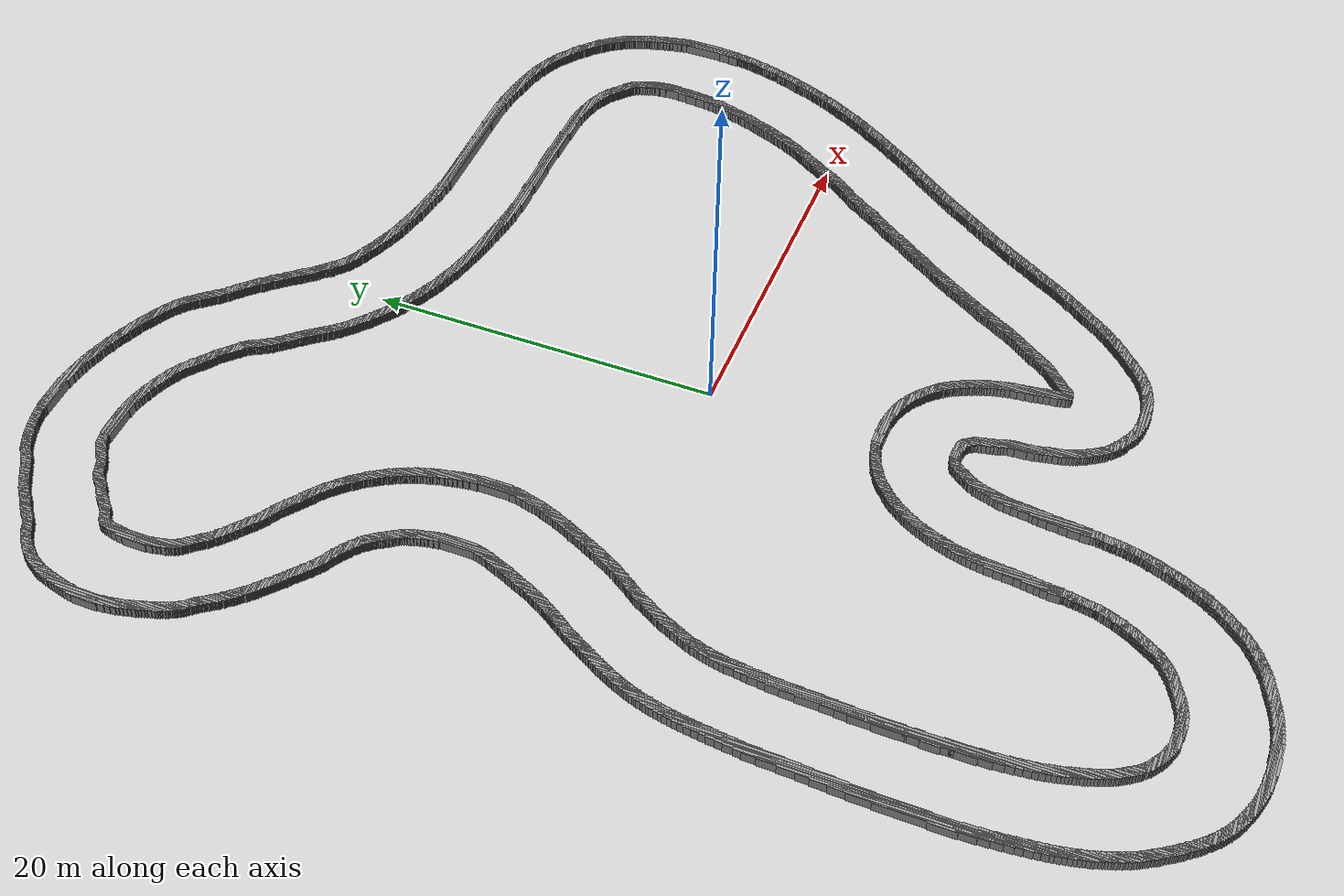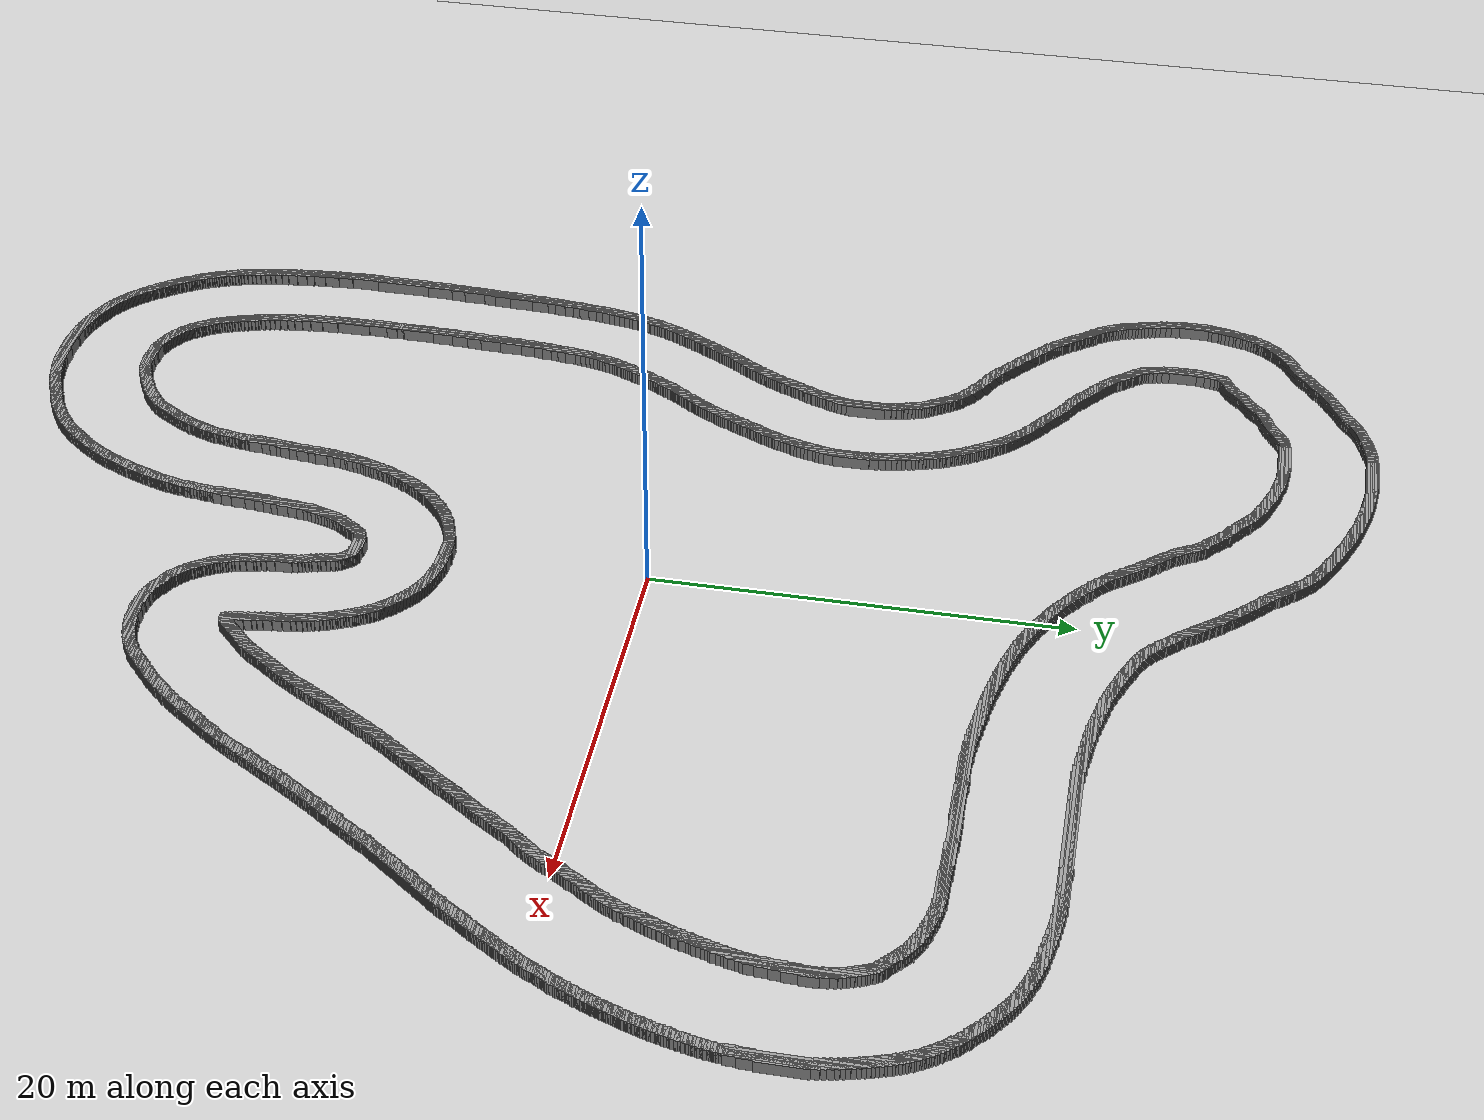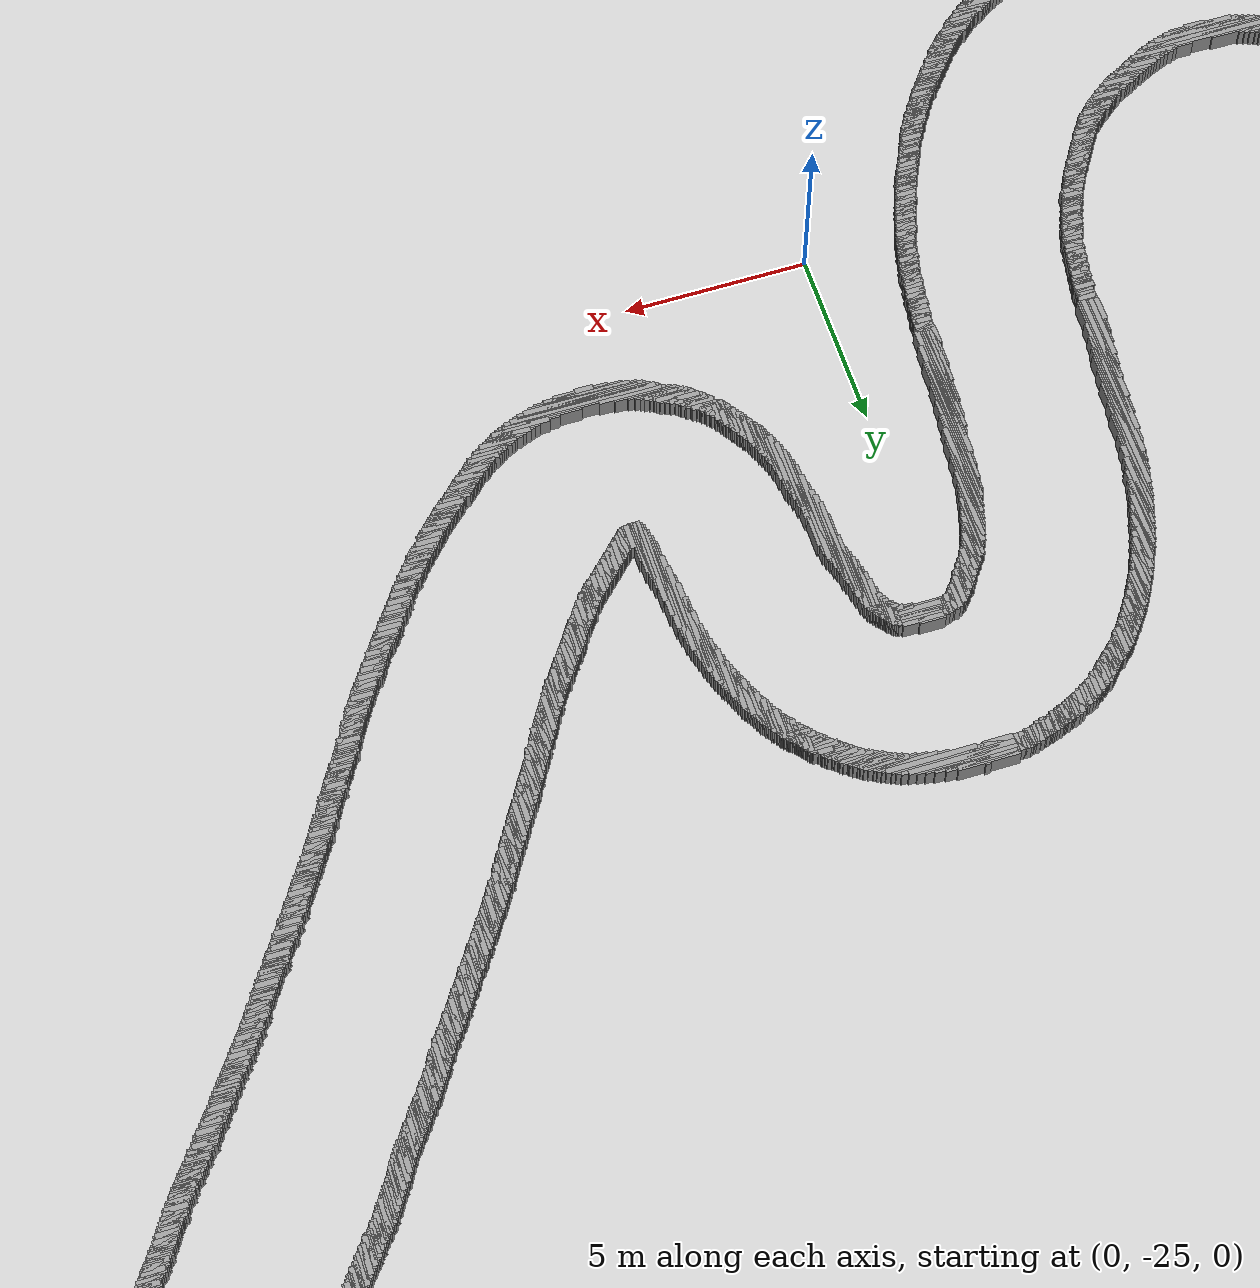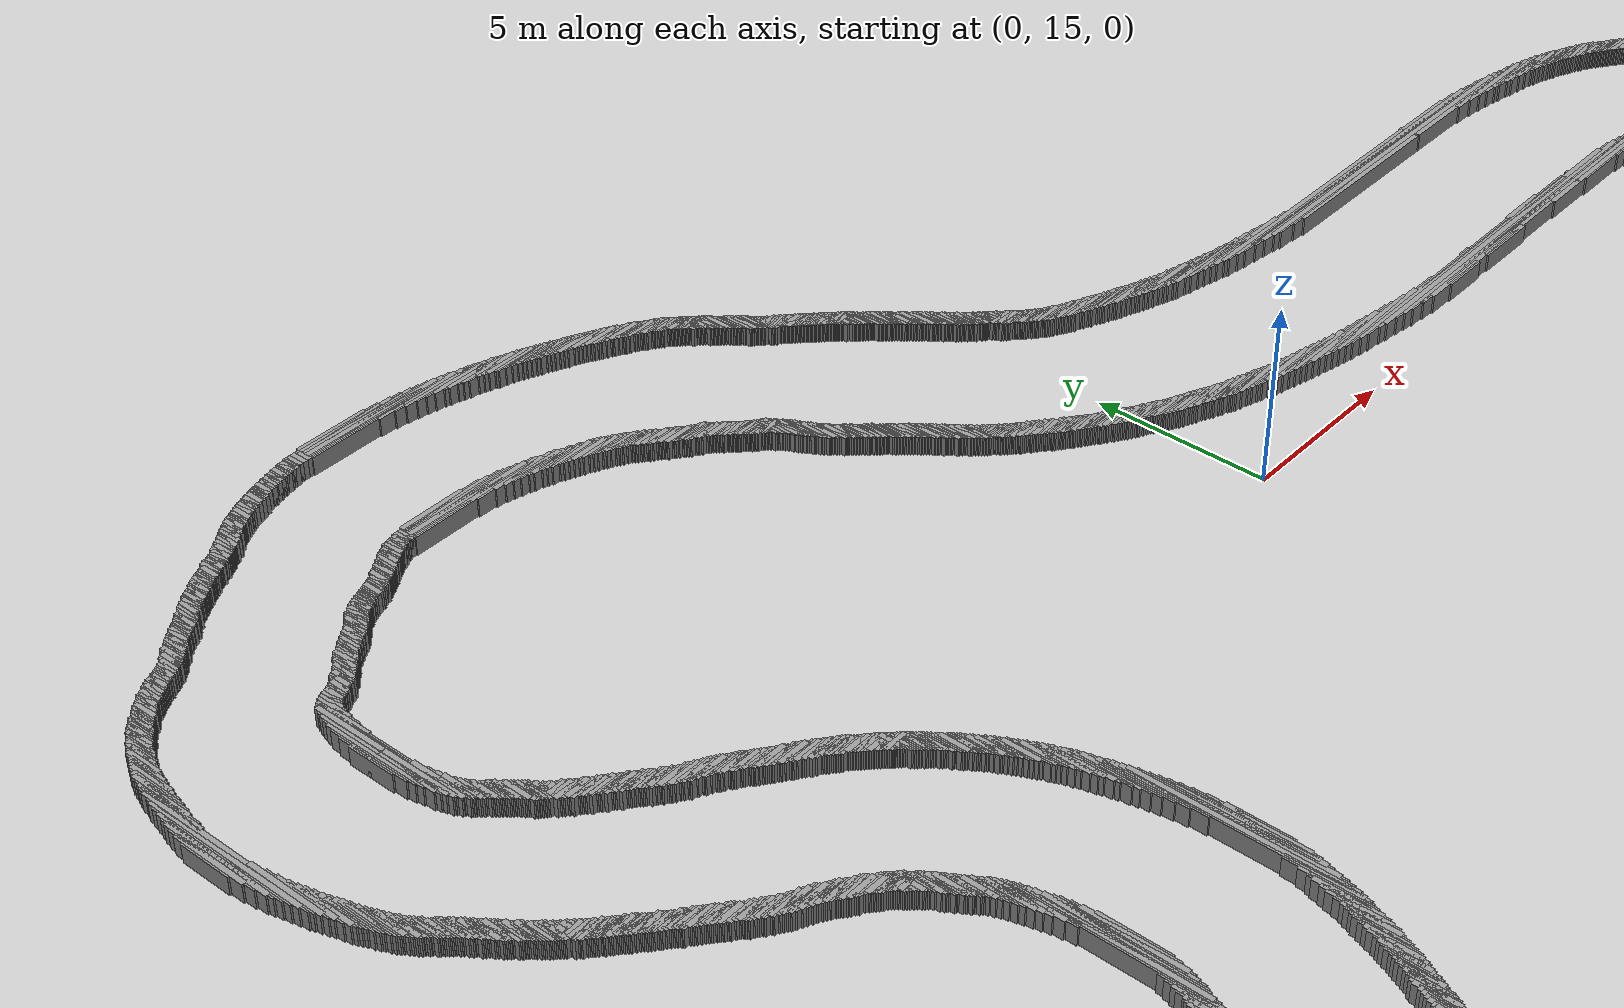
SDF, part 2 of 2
<ambient>1 1 1 1</ambient>
     </material>
    </visual>
    <collision name="obstacle_1802">
     <pose>-18.65 0.125 0 0 0 1.5708</pose>
     <geometry><box><size>1.0 0.15 1.0</size></box></geometry>
    </collision>
    <visual name="obstacle_1802">
     <pose>-18.65 0.125 0 0 0 1.5708</pose>
     <geometry><box><size>1.0 0.15 1.0</size></box></geometry>
     <material>
      <script><uri>file://media/materials/scripts/gazebo.material</uri><name>Gazebo/Grey</name></script>
      <ambient>1 1 1 1</ambient>
     </material>
    </visual>
    <collision name="obstacle_1803">
     <pose>-13.650000000000002 0.125 0 0 0 1.5708</pose>
     <geometry><box><size>1.0 0.15 1.0</size></box></geometry>
    </collision>
    <visual name="obstacle_1803">
     <pose>-13.650000000000002 0.125 0 0 0 1.5708</pose>
     <geometry><box><size>1.0 0.15 1.0</size></box></geometry>
     <material>
      <script><uri>file://media/materials/scripts/gazebo.material</uri><name>Gazebo/Grey</name></script>
      <ambient>1 1 1 1</ambient>
     </material>
    </visual>
    <collision name="obstacle_1804">
     <pose>19.700000000000003 0.125 0 0 0 1.5708</pose>
     <geometry><box><size>1.05 0.15 1.0</size></box></geometry>
    </collision>
    <visual name="obstacle_1804">
     <pose>19.700000000000003 0.125 0 0 0 1.5708</pose>
     <geometry><box><size>1.05 0.15 1.0</size></box></geometry>
     <material>
      <script><uri>file://media/materials/scripts/gazebo.material</uri><name>Gazebo/Grey</name></script>
      <ambient>1 1 1 1</ambient>
     </material>
    </visual>
    <collision name="obstacle_1805">
     <pose>24.9 -0.375 0 0 0 0</pose>
     <geometry><box><size>0.55 0.15 1.0</size></box></geometry>
    </collision>
    <visual name="obstacle_1805">
     <pose>24.9 -0.375 0 0 0 0</pose>
     <geometry><box><size>0.55 0.15 1.0</size></box></geometry>
     <material>
      <script><uri>file://media/materials/scripts/gazebo.material</uri><name>Gazebo/Grey</name></script>
      <ambient>1 1 1 1</ambient>
     </material>
    </visual>
    <collision name="obstacle_1806">
     <pose>24.950000000000003 -0.32500000000000284 0 0 0 0</pose>
     <geometry><box><size>0.6000000000000001 0.15 1.0</size></box></geometry>
    </collision>
    <visual name="obstacle_1806">
     <pose>24.950000000000003 -0.32500000000000284 0 0 0 0</pose>
     <geometry><box><size>0.6000000000000001 0.15 1.0</size></box></geometry>
     <material>
      <script><uri>file://media/materials/scripts/gazebo.material</uri><name>Gazebo/Grey</name></script>
      <ambient>1 1 1 1</ambient>
     </material>
    </visual>
    <collision name="obstacle_1807">
     <pose>-18.6 0.22500000000000142 0 0 0 1.5708</pose>
     <geometry><box><size>1.0 0.15 1.0</size></box></geometry>
    </collision>
    <visual name="obstacle_1807">
     <pose>-18.6 0.22500000000000142 0 0 0 1.5708</pose>
     <geometry><box><size>1.0 0.15 1.0</size></box></geometry>
     <material>
      <script><uri>file://media/materials/scripts/gazebo.material</uri><name>Gazebo/Grey</name></script>
      <ambient>1 1 1 1</ambient>
     </material>
    </visual>
    <collision name="obstacle_1808">
     <pose>-13.600000000000001 0.17499999999999716 0 0 0 1.5708</pose>
     <geometry><box><size>0.9500000000000001 0.15 1.0</size></box></geometry>
    </collision>
    <visual name="obstacle_1808">
     <pose>-13.600000000000001 0.17499999999999716 0 0 0 1.5708</pose>
     <geometry><box><size>0.9500000000000001 0.15 1.0</size></box></geometry>
     <material>
      <script><uri>file://media/materials/scripts/gazebo.material</uri><name>Gazebo/Grey</name></script>
      <ambient>1 1 1 1</ambient>
     </material>
    </visual>
    <collision name="obstacle_1809">
     <pose>25.0 -0.2749999999999986 0 0 0 0</pose>
     <geometry><box><size>0.6000000000000001 0.15 1.0</size></box></geometry>
    </collision>
    <visual name="obstacle_1809">
     <pose>25.0 -0.2749999999999986 0 0 0 0</pose>
     <geometry><box><size>0.6000000000000001 0.15 1.0</size></box></geometry>
     <material>
      <script><uri>file://media/materials/scripts/gazebo.material</uri><name>Gazebo/Grey</name></script>
      <ambient>1 1 1 1</ambient>
     </material>
    </visual>
    <collision name="obstacle_1810">
     <pose>-13.55 0.2749999999999986 0 0 0 1.5708</pose>
     <geometry><box><size>1.0 0.15 1.0</size></box></geometry>
    </collision>
    <visual name="obstacle_1810">
     <pose>-13.55 0.2749999999999986 0 0 0 1.5708</pose>
     <geometry><box><size>1.0 0.15 1.0</size></box></geometry>
     <material>
      <script><uri>file://media/materials/scripts/gazebo.material</uri><name>Gazebo/Grey</name></script>
      <ambient>1 1 1 1</ambient>
     </material>
    </visual>
    <collision name="obstacle_1811">
     <pose>19.75 0.22500000000000142 0 0 0 1.5708</pose>
     <geometry><box><size>0.9500000000000001 0.15 1.0</size></box></geometry>
    </collision>
    <visual name="obstacle_1811">
     <pose>19.75 0.22500000000000142 0 0 0 1.5708</pose>
     <geometry><box><size>0.9500000000000001 0.15 1.0</size></box></geometry>
     <material>
      <script><uri>file://media/materials/scripts/gazebo.material</uri><name>Gazebo/Grey</name></script>
      <ambient>1 1 1 1</ambient>
     </material>
    </visual>
    <collision name="obstacle_1812">
     <pose>25.0 -0.22500000000000142 0 0 0 0</pose>
     <geometry><box><size>0.6000000000000001 0.15 1.0</size></box></geometry>
    </collision>
    <visual name="obstacle_1812">
     <pose>25.0 -0.22500000000000142 0 0 0 0</pose>
     <geometry><box><size>0.6000000000000001 0.15 1.0</size></box></geometry>
     <material>
      <script><uri>file://media/materials/scripts/gazebo.material</uri><name>Gazebo/Grey</name></script>
      <ambient>1 1 1 1</ambient>
     </material>
    </visual>
    <collision name="obstacle_1813">
     <pose>-18.55 0.32499999999999574 0 0 0 1.5708</pose>
     <geometry><box><size>1.0 0.15 1.0</size></box></geometry>
    </collision>
    <visual name="obstacle_1813">
     <pose>-18.55 0.32499999999999574 0 0 0 1.5708</pose>
     <geometry><box><size>1.0 0.15 1.0</size></box></geometry>
     <material>
      <script><uri>file://media/materials/scripts/gazebo.material</uri><name>Gazebo/Grey</name></script>
      <ambient>1 1 1 1</ambient>
     </material>
    </visual>
    <collision name="obstacle_1814">
     <pose>25.050000000000004 -0.17500000000000426 0 0 0 0</pose>
     <geometry><box><size>0.6000000000000001 0.15 1.0</size></box></geometry>
    </collision>
    <visual name="obstacle_1814">
     <pose>25.050000000000004 -0.17500000000000426 0 0 0 0</pose>
     <geometry><box><size>0.6000000000000001 0.15 1.0</size></box></geometry>
     <material>
      <script><uri>file://media/materials/scripts/gazebo.material</uri><name>Gazebo/Grey</name></script>
      <ambient>1 1 1 1</ambient>
     </material>
    </visual>
    <collision name="obstacle_1815">
     <pose>-18.5 0.375 0 0 0 1.5708</pose>
     <geometry><box><size>1.0 0.15 1.0</size></box></geometry>
    </collision>
    <visual name="obstacle_1815">
     <pose>-18.5 0.375 0 0 0 1.5708</pose>
     <geometry><box><size>1.0 0.15 1.0</size></box></geometry>
     <material>
      <script><uri>file://media/materials/scripts/gazebo.material</uri><name>Gazebo/Grey</name></script>
      <ambient>1 1 1 1</ambient>
     </material>
    </visual>
    <collision name="obstacle_1816">
     <pose>-13.5 0.375 0 0 0 1.5708</pose>
     <geometry><box><size>1.05 0.15 1.0</size></box></geometry>
    </collision>
    <visual name="obstacle_1816">
     <pose>-13.5 0.375 0 0 0 1.5708</pose>
     <geometry><box><size>1.05 0.15 1.0</size></box></geometry>
     <material>
      <script><uri>file://media/materials/scripts/gazebo.material</uri><name>Gazebo/Grey</name></script>
      <ambient>1 1 1 1</ambient>
     </material>
    </visual>
    <collision name="obstacle_1817">
     <pose>19.800000000000004 0.32499999999999574 0 0 0 1.5708</pose>
     <geometry><box><size>0.9500000000000001 0.15 1.0</size></box></geometry>
    </collision>
    <visual name="obstacle_1817">
     <pose>19.800000000000004 0.32499999999999574 0 0 0 1.5708</pose>
     <geometry><box><size>0.9500000000000001 0.15 1.0</size></box></geometry>
     <material>
      <script><uri>file://media/materials/scripts/gazebo.material</uri><name>Gazebo/Grey</name></script>
      <ambient>1 1 1 1</ambient>
     </material>
    </visual>
    <collision name="obstacle_1818">
     <pose>25.050000000000004 -0.125 0 0 0 0</pose>
     <geometry><box><size>0.55 0.15 1.0</size></box></geometry>
    </collision>
    <visual name="obstacle_1818">
     <pose>25.050000000000004 -0.125 0 0 0 0</pose>
     <geometry><box><size>0.55 0.15 1.0</size></box></geometry>
     <material>
      <script><uri>file://media/materials/scripts/gazebo.material</uri><name>Gazebo/Grey</name></script>
      <ambient>1 1 1 1</ambient>
     </material>
    </visual>
    <collision name="obstacle_1819">
     <pose>19.85 0.375 0 0 0 1.5708</pose>
     <geometry><box><size>0.9500000000000001 0.15 1.0</size></box></geometry>
    </collision>
    <visual name="obstacle_1819">
     <pose>19.85 0.375 0 0 0 1.5708</pose>
     <geometry><box><size>0.9500000000000001 0.15 1.0</size></box></geometry>
     <material>
      <script><uri>file://media/materials/scripts/gazebo.material</uri><name>Gazebo/Grey</name></script>
      <ambient>1 1 1 1</ambient>
     </material>
    </visual>
    <collision name="obstacle_1820">
     <pose>25.1 -0.07500000000000284 0 0 0 0</pose>
     <geometry><box><size>0.6000000000000001 0.15 1.0</size></box></geometry>
    </collision>
    <visual name="obstacle_1820">
     <pose>25.1 -0.07500000000000284 0 0 0 0</pose>
     <geometry><box><size>0.6000000000000001 0.15 1.0</size></box></geometry>
     <material>
      <script><uri>file://media/materials/scripts/gazebo.material</uri><name>Gazebo/Grey</name></script>
      <ambient>1 1 1 1</ambient>
     </material>
    </visual>
    <collision name="obstacle_1821">
     <pose>-18.450000000000003 0.4750000000000014 0 0 0 1.5708</pose>
     <geometry><box><size>1.0 0.15 1.0</size></box></geometry>
    </collision>
    <visual name="obstacle_1821">
     <pose>-18.450000000000003 0.4750000000000014 0 0 0 1.5708</pose>
     <geometry><box><size>1.0 0.15 1.0</size></box></geometry>
     <material>
      <script><uri>file://media/materials/scripts/gazebo.material</uri><name>Gazebo/Grey</name></script>
      <ambient>1 1 1 1</ambient>
     </material>
    </visual>
    <collision name="obstacle_1822">
     <pose>-13.45 0.4750000000000014 0 0 0 1.5708</pose>
     <geometry><box><size>1.05 0.15 1.0</size></box></geometry>
    </collision>
    <visual name="obstacle_1822">
     <pose>-13.45 0.4750000000000014 0 0 0 1.5708</pose>
     <geometry><box><size>1.05 0.15 1.0</size></box></geometry>
     <material>
      <script><uri>file://media/materials/scripts/gazebo.material</uri><name>Gazebo/Grey</name></script>
      <ambient>1 1 1 1</ambient>
     </material>
    </visual>
    <collision name="obstacle_1823">
     <pose>25.1 -0.02499999999999858 0 0 0 0</pose>
     <geometry><box><size>0.55 0.15 1.0</size></box></geometry>
    </collision>
    <visual name="obstacle_1823">
     <pose>25.1 -0.02499999999999858 0 0 0 0</pose>
     <geometry><box><size>0.55 0.15 1.0</size></box></geometry>
     <material>
      <script><uri>file://media/materials/scripts/gazebo.material</uri><name>Gazebo/Grey</name></script>
      <ambient>1 1 1 1</ambient>
     </material>
    </visual>
    <collision name="obstacle_1824">
     <pose>-13.400000000000002 0.5249999999999986 0 0 0 1.5708</pose>
     <geometry><box><size>1.05 0.15 1.0</size></box></geometry>
    </collision>
    <visual name="obstacle_1824">
     <pose>-13.400000000000002 0.5249999999999986 0 0 0 1.5708</pose>
     <geometry><box><size>1.05 0.15 1.0</size></box></geometry>
     <material>
      <script><uri>file://media/materials/scripts/gazebo.material</uri><name>Gazebo/Grey</name></script>
      <ambient>1 1 1 1</ambient>
     </material>
    </visual>
    <collision name="obstacle_1825">
     <pose>19.9 0.4750000000000014 0 0 0 1.5708</pose>
     <geometry><box><size>0.9500000000000001 0.15 1.0</size></box></geometry>
    </collision>
    <visual name="obstacle_1825">
     <pose>19.9 0.4750000000000014 0 0 0 1.5708</pose>
     <geometry><box><size>0.9500000000000001 0.15 1.0</size></box></geometry>
     <material>
      <script><uri>file://media/materials/scripts/gazebo.material</uri><name>Gazebo/Grey</name></script>
      <ambient>1 1 1 1</ambient>
     </material>
    </visual>
    <collision name="obstacle_1826">
     <pose>25.15 0.02499999999999858 0 0 0 0</pose>
     <geometry><box><size>0.55 0.15 1.0</size></box></geometry>
    </collision>
    <visual name="obstacle_1826">
     <pose>25.15 0.02499999999999858 0 0 0 0</pose>
     <geometry><box><size>0.55 0.15 1.0</size></box></geometry>
     <material>
      <script><uri>file://media/materials/scripts/gazebo.material</uri><name>Gazebo/Grey</name></script>
      <ambient>1 1 1 1</ambient>
     </material>
    </visual>
    <collision name="obstacle_1827">
     <pose>-18.4 0.5249999999999986 0 0 0 1.5708</pose>
     <geometry><box><size>0.9500000000000001 0.15 1.0</size></box></geometry>
    </collision>
    <visual name="obstacle_1827">
     <pose>-18.4 0.5249999999999986 0 0 0 1.5708</pose>
     <geometry><box><size>0.9500000000000001 0.15 1.0</size></box></geometry>
     <material>
      <script><uri>file://media/materials/scripts/gazebo.material</uri><name>Gazebo/Grey</name></script>
      <ambient>1 1 1 1</ambient>
     </material>
    </visual>
    <collision name="obstacle_1828">
     <pose>25.15 0.07499999999999574 0 0 0 0</pose>
     <geometry><box><size>0.55 0.15 1.0</size></box></geometry>
    </collision>
    <visual name="obstacle_1828">
     <pose>25.15 0.07499999999999574 0 0 0 0</pose>
     <geometry><box><size>0.55 0.15 1.0</size></box></geometry>
     <material>
      <script><uri>file://media/materials/scripts/gazebo.material</uri><name>Gazebo/Grey</name></script>
      <ambient>1 1 1 1</ambient>
     </material>
    </visual>
    <collision name="obstacle_1829">
     <pose>-18.35 0.625 0 0 0 1.5708</pose>
     <geometry><box><size>1.0 0.15 1.0</size></box></geometry>
    </collision>
    <visual name="obstacle_1829">
     <pose>-18.35 0.625 0 0 0 1.5708</pose>
     <geometry><box><size>1.0 0.15 1.0</size></box></geometry>
     <material>
      <script><uri>file://media/materials/scripts/gazebo.material</uri><name>Gazebo/Grey</name></script>
      <ambient>1 1 1 1</ambient>
     </material>
    </visual>
    <collision name="obstacle_1830">
     <pose>-13.350000000000001 0.625 0 0 0 1.5708</pose>
     <geometry><box><size>1.05 0.15 1.0</size></box></geometry>
    </collision>
    <visual name="obstacle_1830">
     <pose>-13.350000000000001 0.625 0 0 0 1.5708</pose>
     <geometry><box><size>1.05 0.15 1.0</size></box></geometry>
     <material>
      <script><uri>file://media/materials/scripts/gazebo.material</uri><name>Gazebo/Grey</name></script>
      <ambient>1 1 1 1</ambient>
     </material>
    </visual>
    <collision name="obstacle_1831">
     <pose>19.950000000000003 0.5749999999999957 0 0 0 1.5708</pose>
     <geometry><box><size>0.9 0.15 1.0</size></box></geometry>
    </collision>
    <visual name="obstacle_1831">
     <pose>19.950000000000003 0.5749999999999957 0 0 0 1.5708</pose>
     <geometry><box><size>0.9 0.15 1.0</size></box></geometry>
     <material>
      <script><uri>file://media/materials/scripts/gazebo.material</uri><name>Gazebo/Grey</name></script>
      <ambient>1 1 1 1</ambient>
     </material>
    </visual>
    <collision name="obstacle_1832">
     <pose>25.200000000000003 0.125 0 0 0 0</pose>
     <geometry><box><size>0.55 0.15 1.0</size></box></geometry>
    </collision>
    <visual name="obstacle_1832">
     <pose>25.200000000000003 0.125 0 0 0 0</pose>
     <geometry><box><size>0.55 0.15 1.0</size></box></geometry>
     <material>
      <script><uri>file://media/materials/scripts/gazebo.material</uri><name>Gazebo/Grey</name></script>
      <ambient>1 1 1 1</ambient>
     </material>
    </visual>
    <collision name="obstacle_1833">
     <pose>20.0 0.625 0 0 0 1.5708</pose>
     <geometry><box><size>0.9500000000000001 0.15 1.0</size></box></geometry>
    </collision>
    <visual name="obstacle_1833">
     <pose>20.0 0.625 0 0 0 1.5708</pose>
     <geometry><box><size>0.9500000000000001 0.15 1.0</size></box></geometry>
     <material>
      <script><uri>file://media/materials/scripts/gazebo.material</uri><name>Gazebo/Grey</name></script>
      <ambient>1 1 1 1</ambient>
     </material>
    </visual>
    <collision name="obstacle_1834">
     <pose>25.25 0.17499999999999716 0 0 0 0</pose>
     <geometry><box><size>0.6000000000000001 0.15 1.0</size></box></geometry>
    </collision>
    <visual name="obstacle_1834">
     <pose>25.25 0.17499999999999716 0 0 0 0</pose>
     <geometry><box><size>0.6000000000000001 0.15 1.0</size></box></geometry>
     <material>
      <script><uri>file://media/materials/scripts/gazebo.material</uri><name>Gazebo/Grey</name></script>
      <ambient>1 1 1 1</ambient>
     </material>
    </visual>
    <collision name="obstacle_1835">
     <pose>-18.3 0.6749999999999972 0 0 0 1.5708</pose>
     <geometry><box><size>0.9500000000000001 0.15 1.0</size></box></geometry>
    </collision>
    <visual name="obstacle_1835">
     <pose>-18.3 0.6749999999999972 0 0 0 1.5708</pose>
     <geometry><box><size>0.9500000000000001 0.15 1.0</size></box></geometry>
     <material>
      <script><uri>file://media/materials/scripts/gazebo.material</uri><name>Gazebo/Grey</name></script>
      <ambient>1 1 1 1</ambient>
     </material>
    </visual>
    <collision name="obstacle_1836">
     <pose>-13.3 0.7749999999999986 0 0 0 1.5708</pose>
     <geometry><box><size>1.1 0.15 1.0</size></box></geometry>
    </collision>
    <visual name="obstacle_1836">
     <pose>-13.3 0.7749999999999986 0 0 0 1.5708</pose>
     <geometry><box><size>1.1 0.15 1.0</size></box></geometry>
     <material>
      <script><uri>file://media/materials/scripts/gazebo.material</uri><name>Gazebo/Grey</name></script>
      <ambient>1 1 1 1</ambient>
     </material>
    </visual>
    <collision name="obstacle_1837">
     <pose>25.25 0.22500000000000142 0 0 0 0</pose>
     <geometry><box><size>0.55 0.15 1.0</size></box></geometry>
    </collision>
    <visual name="obstacle_1837">
     <pose>25.25 0.22500000000000142 0 0 0 0</pose>
     <geometry><box><size>0.55 0.15 1.0</size></box></geometry>
     <material>
      <script><uri>file://media/materials/scripts/gazebo.material</uri><name>Gazebo/Grey</name></script>
      <ambient>1 1 1 1</ambient>
     </material>
    </visual>
    <collision name="obstacle_1838">
     <pose>20.050000000000004 0.7250000000000014 0 0 0 1.5708</pose>
     <geometry><box><size>0.9500000000000001 0.15 1.0</size></box></geometry>
    </collision>
    <visual name="obstacle_1838">
     <pose>20.050000000000004 0.7250000000000014 0 0 0 1.5708</pose>
     <geometry><box><size>0.9500000000000001 0.15 1.0</size></box></geometry>
     <material>
      <script><uri>file://media/materials/scripts/gazebo.material</uri><name>Gazebo/Grey</name></script>
      <ambient>1 1 1 1</ambient>
     </material>
    </visual>
    <collision name="obstacle_1839">
     <pose>25.300000000000004 0.2749999999999986 0 0 0 0</pose>
     <geometry><box><size>0.6000000000000001 0.15 1.0</size></box></geometry>
    </collision>
    <visual name="obstacle_1839">
     <pose>25.300000000000004 0.2749999999999986 0 0 0 0</pose>
     <geometry><box><size>0.6000000000000001 0.15 1.0</size></box></geometry>
     <material>
      <script><uri>file://media/materials/scripts/gazebo.material</uri><name>Gazebo/Grey</name></script>
      <ambient>1 1 1 1</ambient>
     </material>
    </visual>
    <collision name="obstacle_1840">
     <pose>-18.25 0.7749999999999986 0 0 0 1.5708</pose>
     <geometry><box><size>0.9 0.15 1.0</size></box></geometry>
    </collision>
    <visual name="obstacle_1840">
     <pose>-18.25 0.7749999999999986 0 0 0 1.5708</pose>
     <geometry><box><size>0.9 0.15 1.0</size></box></geometry>
     <material>
      <script><uri>file://media/materials/scripts/gazebo.material</uri><name>Gazebo/Grey</name></script>
      <ambient>1 1 1 1</ambient>
     </material>
    </visual>
    <collision name="obstacle_1841">
     <pose>-13.25 0.8249999999999957 0 0 0 1.5708</pose>
     <geometry><box><size>1.05 0.15 1.0</size></box></geometry>
    </collision>
    <visual name="obstacle_1841">
     <pose>-13.25 0.8249999999999957 0 0 0 1.5708</pose>
     <geometry><box><size>1.05 0.15 1.0</size></box></geometry>
     <material>
      <script><uri>file://media/materials/scripts/gazebo.material</uri><name>Gazebo/Grey</name></script>
      <ambient>1 1 1 1</ambient>
     </material>
    </visual>
    <collision name="obstacle_1842">
     <pose>25.300000000000004 0.32499999999999574 0 0 0 0</pose>
     <geometry><box><size>0.55 0.15 1.0</size></box></geometry>
    </collision>
    <visual name="obstacle_1842">
     <pose>25.300000000000004 0.32499999999999574 0 0 0 0</pose>
     <geometry><box><size>0.55 0.15 1.0</size></box></geometry>
     <material>
      <script><uri>file://media/materials/scripts/gazebo.material</uri><name>Gazebo/Grey</name></script>
      <ambient>1 1 1 1</ambient>
     </material>
    </visual>
    <collision name="obstacle_1843">
     <pose>-13.2 0.875 0 0 0 1.5708</pose>
     <geometry><box><size>1.05 0.15 1.0</size></box></geometry>
    </collision>
    <visual name="obstacle_1843">
     <pose>-13.2 0.875 0 0 0 1.5708</pose>
     <geometry><box><size>1.05 0.15 1.0</size></box></geometry>
     <material>
      <script><uri>file://media/materials/scripts/gazebo.material</uri><name>Gazebo/Grey</name></script>
      <ambient>1 1 1 1</ambient>
     </material>
    </visual>
    <collision name="obstacle_1844">
     <pose>20.1 0.8249999999999957 0 0 0 1.5708</pose>
     <geometry><box><size>0.9500000000000001 0.15 1.0</size></box></geometry>
    </collision>
    <visual name="obstacle_1844">
     <pose>20.1 0.8249999999999957 0 0 0 1.5708</pose>
     <geometry><box><size>0.9500000000000001 0.15 1.0</size></box></geometry>
     <material>
      <script><uri>file://media/materials/scripts/gazebo.material</uri><name>Gazebo/Grey</name></script>
      <ambient>1 1 1 1</ambient>
     </material>
    </visual>
    <collision name="obstacle_1845">
     <pose>25.35 0.375 0 0 0 0</pose>
     <geometry><box><size>0.6000000000000001 0.15 1.0</size></box></geometry>
    </collision>
    <visual name="obstacle_1845">
     <pose>25.35 0.375 0 0 0 0</pose>
     <geometry><box><size>0.6000000000000001 0.15 1.0</size></box></geometry>
     <material>
      <script><uri>file://media/materials/scripts/gazebo.material</uri><name>Gazebo/Grey</name></script>
      <ambient>1 1 1 1</ambient>
     </material>
    </visual>
    <collision name="obstacle_1846">
     <pose>-18.200000000000003 0.875 0 0 0 1.5708</pose>
     <geometry><box><size>0.9 0.15 1.0</size></box></geometry>
    </collision>
    <visual name="obstacle_1846">
     <pose>-18.200000000000003 0.875 0 0 0 1.5708</pose>
     <geometry><box><size>0.9 0.15 1.0</size></box></geometry>
     <material>
      <script><uri>file://media/materials/scripts/gazebo.material</uri><name>Gazebo/Grey</name></script>
      <ambient>1 1 1 1</ambient>
     </material>
    </visual>
    <collision name="obstacle_1847">
     <pose>20.15 0.875 0 0 0 1.5708</pose>
     <geometry><box><size>0.9500000000000001 0.15 1.0</size></box></geometry>
    </collision>
    <visual name="obstacle_1847">
     <pose>20.15 0.875 0 0 0 1.5708</pose>
     <geometry><box><size>0.9500000000000001 0.15 1.0</size></box></geometry>
     <material>
      <script><uri>file://media/materials/scripts/gazebo.material</uri><name>Gazebo/Grey</name></script>
      <ambient>1 1 1 1</ambient>
     </material>
    </visual>
    <collision name="obstacle_1848">
     <pose>25.35 0.42499999999999716 0 0 0 0</pose>
     <geometry><box><size>0.55 0.15 1.0</size></box></geometry>
    </collision>
    <visual name="obstacle_1848">
     <pose>25.35 0.42499999999999716 0 0 0 0</pose>
     <geometry><box><size>0.55 0.15 1.0</size></box></geometry>
     <material>
      <script><uri>file://media/materials/scripts/gazebo.material</uri><name>Gazebo/Grey</name></script>
      <ambient>1 1 1 1</ambient>
     </material>
    </visual>
    <collision name="obstacle_1849">
     <pose>-13.150000000000002 1.0249999999999986 0 0 0 1.5708</pose>
     <geometry><box><size>1.1 0.15 1.0</size></box></geometry>
    </collision>
    <visual name="obstacle_1849">
     <pose>-13.150000000000002 1.0249999999999986 0 0 0 1.5708</pose>
     <geometry><box><size>1.1 0.15 1.0</size></box></geometry>
     <material>
      <script><uri>file://media/materials/scripts/gazebo.material</uri><name>Gazebo/Grey</name></script>
      <ambient>1 1 1 1</ambient>
     </material>
    </visual>
    <collision name="obstacle_1850">
     <pose>25.4 0.4750000000000014 0 0 0 0</pose>
     <geometry><box><size>0.55 0.15 1.0</size></box></geometry>
    </collision>
    <visual name="obstacle_1850">
     <pose>25.4 0.4750000000000014 0 0 0 0</pose>
     <geometry><box><size>0.55 0.15 1.0</size></box></geometry>
     <material>
      <script><uri>file://media/materials/scripts/gazebo.material</uri><name>Gazebo/Grey</name></script>
      <ambient>1 1 1 1</ambient>
     </material>
    </visual>
    <collision name="obstacle_1851">
     <pose>-18.15 0.9750000000000014 0 0 0 1.5708</pose>
     <geometry><box><size>0.9 0.15 1.0</size></box></geometry>
    </collision>
    <visual name="obstacle_1851">
     <pose>-18.15 0.9750000000000014 0 0 0 1.5708</pose>
     <geometry><box><size>0.9 0.15 1.0</size></box></geometry>
     <material>
      <script><uri>file://media/materials/scripts/gazebo.material</uri><name>Gazebo/Grey</name></script>
      <ambient>1 1 1 1</ambient>
     </material>
    </visual>
    <collision name="obstacle_1852">
     <pose>20.200000000000003 0.9750000000000014 0 0 0 1.5708</pose>
     <geometry><box><size>0.9500000000000001 0.15 1.0</size></box></geometry>
    </collision>
    <visual name="obstacle_1852">
     <pose>20.200000000000003 0.9750000000000014 0 0 0 1.5708</pose>
     <geometry><box><size>0.9500000000000001 0.15 1.0</size></box></geometry>
     <material>
      <script><uri>file://media/materials/scripts/gazebo.material</uri><name>Gazebo/Grey</name></script>
      <ambient>1 1 1 1</ambient>
     </material>
    </visual>
    <collision name="obstacle_1853">
     <pose>25.4 0.5249999999999986 0 0 0 0</pose>
     <geometry><box><size>0.55 0.15 1.0</size></box></geometry>
    </collision>
    <visual name="obstacle_1853">
     <pose>25.4 0.5249999999999986 0 0 0 0</pose>
     <geometry><box><size>0.55 0.15 1.0</size></box></geometry>
     <material>
      <script><uri>file://media/materials/scripts/gazebo.material</uri><name>Gazebo/Grey</name></script>
      <ambient>1 1 1 1</ambient>
     </material>
    </visual>
    <collision name="obstacle_1854">
     <pose>-18.1 1.0249999999999986 0 0 0 1.5708</pose>
     <geometry><box><size>0.9 0.15 1.0</size></box></geometry>
    </collision>
    <visual name="obstacle_1854">
     <pose>-18.1 1.0249999999999986 0 0 0 1.5708</pose>
     <geometry><box><size>0.9 0.15 1.0</size></box></geometry>
     <material>
      <script><uri>file://media/materials/scripts/gazebo.material</uri><name>Gazebo/Grey</name></script>
      <ambient>1 1 1 1</ambient>
     </material>
    </visual>
    <collision name="obstacle_1855">
     <pose>-13.100000000000001 1.125 0 0 0 1.5708</pose>
     <geometry><box><size>1.1 0.15 1.0</size></box></geometry>
    </collision>
    <visual name="obstacle_1855">
     <pose>-13.100000000000001 1.125 0 0 0 1.5708</pose>
     <geometry><box><size>1.1 0.15 1.0</size></box></geometry>
     <material>
      <script><uri>file://media/materials/scripts/gazebo.material</uri><name>Gazebo/Grey</name></script>
      <ambient>1 1 1 1</ambient>
     </material>
    </visual>
    <collision name="obstacle_1856">
     <pose>20.25 1.0249999999999986 0 0 0 1.5708</pose>
     <geometry><box><size>0.9500000000000001 0.15 1.0</size></box></geometry>
    </collision>
    <visual name="obstacle_1856">
     <pose>20.25 1.0249999999999986 0 0 0 1.5708</pose>
     <geometry><box><size>0.9500000000000001 0.15 1.0</size></box></geometry>
     <material>
      <script><uri>file://media/materials/scripts/gazebo.material</uri><name>Gazebo/Grey</name></script>
      <ambient>1 1 1 1</ambient>
     </material>
    </visual>
    <collision name="obstacle_1857">
     <pose>25.450000000000003 0.5749999999999957 0 0 0 0</pose>
     <geometry><box><size>0.55 0.15 1.0</size></box></geometry>
    </collision>
    <visual name="obstacle_1857">
     <pose>25.450000000000003 0.5749999999999957 0 0 0 0</pose>
     <geometry><box><size>0.55 0.15 1.0</size></box></geometry>
     <material>
      <script><uri>file://media/materials/scripts/gazebo.material</uri><name>Gazebo/Grey</name></script>
      <ambient>1 1 1 1</ambient>
     </material>
    </visual>
    <collision name="obstacle_1858">
     <pose>25.450000000000003 0.625 0 0 0 0</pose>
     <geometry><box><size>0.55 0.15 1.0</size></box></geometry>
    </collision>
    <visual name="obstacle_1858">
     <pose>25.450000000000003 0.625 0 0 0 0</pose>
     <geometry><box><size>0.55 0.15 1.0</size></box></geometry>
     <material>
      <script><uri>file://media/materials/scripts/gazebo.material</uri><name>Gazebo/Grey</name></script>
      <ambient>1 1 1 1</ambient>
     </material>
    </visual>
    <collision name="obstacle_1859">
     <pose>-18.05 1.125 0 0 0 1.5708</pose>
     <geometry><box><size>0.9 0.15 1.0</size></box></geometry>
    </collision>
    <visual name="obstacle_1859">
     <pose>-18.05 1.125 0 0 0 1.5708</pose>
     <geometry><box><size>0.9 0.15 1.0</size></box></geometry>
     <material>
      <script><uri>file://media/materials/scripts/gazebo.material</uri><name>Gazebo/Grey</name></script>
      <ambient>1 1 1 1</ambient>
     </material>
    </visual>
    <collision name="obstacle_1860">
     <pose>20.300000000000004 1.125 0 0 0 1.5708</pose>
     <geometry><box><size>0.9500000000000001 0.15 1.0</size></box></geometry>
    </collision>
    <visual name="obstacle_1860">
     <pose>20.300000000000004 1.125 0 0 0 1.5708</pose>
     <geometry><box><size>0.9500000000000001 0.15 1.0</size></box></geometry>
     <material>
      <script><uri>file://media/materials/scripts/gazebo.material</uri><name>Gazebo/Grey</name></script>
      <ambient>1 1 1 1</ambient>
     </material>
    </visual>
    <collision name="obstacle_1861">
     <pose>25.5 0.6749999999999972 0 0 0 0</pose>
     <geometry><box><size>0.5 0.15 1.0</size></box></geometry>
    </collision>
    <visual name="obstacle_1861">
     <pose>25.5 0.6749999999999972 0 0 0 0</pose>
     <geometry><box><size>0.5 0.15 1.0</size></box></geometry>
     <material>
      <script><uri>file://media/materials/scripts/gazebo.material</uri><name>Gazebo/Grey</name></script>
      <ambient>1 1 1 1</ambient>
     </material>
    </visual>
    <collision name="obstacle_1862">
     <pose>-18.0 1.1749999999999972 0 0 0 1.5708</pose>
     <geometry><box><size>0.9 0.15 1.0</size></box></geometry>
    </collision>
    <visual name="obstacle_1862">
     <pose>-18.0 1.1749999999999972 0 0 0 1.5708</pose>
     <geometry><box><size>0.9 0.15 1.0</size></box></geometry>
     <material>
      <script><uri>file://media/materials/scripts/gazebo.material</uri><name>Gazebo/Grey</name></script>
      <ambient>1 1 1 1</ambient>
     </material>
    </visual>
    <collision name="obstacle_1863">
     <pose>-13.05 1.2250000000000014 0 0 0 1.5708</pose>
     <geometry><box><size>1.05 0.15 1.0</size></box></geometry>
    </collision>
    <visual name="obstacle_1863">
     <pose>-13.05 1.2250000000000014 0 0 0 1.5708</pose>
     <geometry><box><size>1.05 0.15 1.0</size></box></geometry>
     <material>
      <script><uri>file://media/materials/scripts/gazebo.material</uri><name>Gazebo/Grey</name></script>
      <ambient>1 1 1 1</ambient>
     </material>
    </visual>
    <collision name="obstacle_1864">
     <pose>20.35 1.1749999999999972 0 0 0 1.5708</pose>
     <geometry><box><size>0.9500000000000001 0.15 1.0</size></box></geometry>
    </collision>
    <visual name="obstacle_1864">
     <pose>20.35 1.1749999999999972 0 0 0 1.5708</pose>
     <geometry><box><size>0.9500000000000001 0.15 1.0</size></box></geometry>
     <material>
      <script><uri>file://media/materials/scripts/gazebo.material</uri><name>Gazebo/Grey</name></script>
      <ambient>1 1 1 1</ambient>
     </material>
    </visual>
    <collision name="obstacle_1865">
     <pose>25.5 0.7250000000000014 0 0 0 0</pose>
     <geometry><box><size>0.55 0.15 1.0</size></box></geometry>
    </collision>
    <visual name="obstacle_1865">
     <pose>25.5 0.7250000000000014 0 0 0 0</pose>
     <geometry><box><size>0.55 0.15 1.0</size></box></geometry>
     <material>
      <script><uri>file://media/materials/scripts/gazebo.material</uri><name>Gazebo/Grey</name></script>
      <ambient>1 1 1 1</ambient>
     </material>
    </visual>
    <collision name="obstacle_1866">
     <pose>-13.0 1.3249999999999957 0 0 0 1.5708</pose>
     <geometry><box><size>1.1 0.15 1.0</size></box></geometry>
    </collision>
    <visual name="obstacle_1866">
     <pose>-13.0 1.3249999999999957 0 0 0 1.5708</pose>
     <geometry><box><size>1.1 0.15 1.0</size></box></geometry>
     <material>
      <script><uri>file://media/materials/scripts/gazebo.material</uri><name>Gazebo/Grey</name></script>
      <ambient>1 1 1 1</ambient>
     </material>
    </visual>
    <collision name="obstacle_1867">
     <pose>25.550000000000004 0.7749999999999986 0 0 0 0</pose>
     <geometry><box><size>0.55 0.15 1.0</size></box></geometry>
    </collision>
    <visual name="obstacle_1867">
     <pose>25.550000000000004 0.7749999999999986 0 0 0 0</pose>
     <geometry><box><size>0.55 0.15 1.0</size></box></geometry>
     <material>
      <script><uri>file://media/materials/scripts/gazebo.material</uri><name>Gazebo/Grey</name></script>
      <ambient>1 1 1 1</ambient>
     </material>
    </visual>
    <collision name="obstacle_1868">
     <pose>-17.950000000000003 1.2749999999999986 0 0 0 1.5708</pose>
     <geometry><box><size>0.9 0.15 1.0</size></box></geometry>
    </collision>
    <visual name="obstacle_1868">
     <pose>-17.950000000000003 1.2749999999999986 0 0 0 1.5708</pose>
     <geometry><box><size>0.9 0.15 1.0</size></box></geometry>
     <material>
      <script><uri>file://media/materials/scripts/gazebo.material</uri><name>Gazebo/Grey</name></script>
      <ambient>1 1 1 1</ambient>
     </material>
    </visual>
    <collision name="obstacle_1869">
     <pose>20.4 1.2749999999999986 0 0 0 1.5708</pose>
     <geometry><box><size>0.9500000000000001 0.15 1.0</size></box></geometry>
    </collision>
    <visual name="obstacle_1869">
     <pose>20.4 1.2749999999999986 0 0 0 1.5708</pose>
     <geometry><box><size>0.9500000000000001 0.15 1.0</size></box></geometry>
     <material>
      <script><uri>file://media/materials/scripts/gazebo.material</uri><name>Gazebo/Grey</name></script>
      <ambient>1 1 1 1</ambient>
     </material>
    </visual>
    <collision name="obstacle_1870">
     <pose>25.550000000000004 0.8249999999999957 0 0 0 0</pose>
     <geometry><box><size>0.55 0.15 1.0</size></box></geometry>
    </collision>
    <visual name="obstacle_1870">
     <pose>25.550000000000004 0.8249999999999957 0 0 0 0</pose>
     <geometry><box><size>0.55 0.15 1.0</size></box></geometry>
     <material>
      <script><uri>file://media/materials/scripts/gazebo.material</uri><name>Gazebo/Grey</name></script>
      <ambient>1 1 1 1</ambient>
     </material>
    </visual>
    <collision name="obstacle_1871">
     <pose>-17.9 1.3249999999999957 0 0 0 1.5708</pose>
     <geometry><box><size>0.9 0.15 1.0</size></box></geometry>
    </collision>
    <visual name="obstacle_1871">
     <pose>-17.9 1.3249999999999957 0 0 0 1.5708</pose>
     <geometry><box><size>0.9 0.15 1.0</size></box></geometry>
     <material>
      <script><uri>file://media/materials/scripts/gazebo.material</uri><name>Gazebo/Grey</name></script>
      <ambient>1 1 1 1</ambient>
     </material>
    </visual>
    <collision name="obstacle_1872">
     <pose>-12.95 1.4249999999999972 0 0 0 1.5708</pose>
     <geometry><box><size>1.1 0.15 1.0</size></box></geometry>
    </collision>
    <visual name="obstacle_1872">
     <pose>-12.95 1.4249999999999972 0 0 0 1.5708</pose>
     <geometry><box><size>1.1 0.15 1.0</size></box></geometry>
     <material>
      <script><uri>file://media/materials/scripts/gazebo.material</uri><name>Gazebo/Grey</name></script>
      <ambient>1 1 1 1</ambient>
     </material>
    </visual>
    <collision name="obstacle_1873">
     <pose>25.6 0.875 0 0 0 0</pose>
     <geometry><box><size>0.6000000000000001 0.15 1.0</size></box></geometry>
    </collision>
    <visual name="obstacle_1873">
     <pose>25.6 0.875 0 0 0 0</pose>
     <geometry><box><size>0.6000000000000001 0.15 1.0</size></box></geometry>
     <material>
      <script><uri>file://media/materials/scripts/gazebo.material</uri><name>Gazebo/Grey</name></script>
      <ambient>1 1 1 1</ambient>
     </material>
    </visual>
    <collision name="obstacle_1874">
     <pose>-17.85 1.375 0 0 0 1.5708</pose>
     <geometry><box><size>0.9500000000000001 0.15 1.0</size></box></geometry>
    </collision>
    <visual name="obstacle_1874">
     <pose>-17.85 1.375 0 0 0 1.5708</pose>
     <geometry><box><size>0.9500000000000001 0.15 1.0</size></box></geometry>
     <material>
      <script><uri>file://media/materials/scripts/gazebo.material</uri><name>Gazebo/Grey</name></script>
      <ambient>1 1 1 1</ambient>
     </material>
    </visual>
    <collision name="obstacle_1875">
     <pose>-12.900000000000002 1.4750000000000014 0 0 0 1.5708</pose>
     <geometry><box><size>1.1500000000000001 0.15 1.0</size></box></geometry>
    </collision>
    <visual name="obstacle_1875">
     <pose>-12.900000000000002 1.4750000000000014 0 0 0 1.5708</pose>
     <geometry><box><size>1.1500000000000001 0.15 1.0</size></box></geometry>
     <material>
      <script><uri>file://media/materials/scripts/gazebo.material</uri><name>Gazebo/Grey</name></script>
      <ambient>1 1 1 1</ambient>
     </material>
    </visual>
    <collision name="obstacle_1876">
     <pose>20.450000000000003 1.375 0 0 0 1.5708</pose>
     <geometry><box><size>0.9 0.15 1.0</size></box></geometry>
    </collision>
    <visual name="obstacle_1876">
     <pose>20.450000000000003 1.375 0 0 0 1.5708</pose>
     <geometry><box><size>0.9 0.15 1.0</size></box></geometry>
     <material>
      <script><uri>file://media/materials/scripts/gazebo.material</uri><name>Gazebo/Grey</name></script>
      <ambient>1 1 1 1</ambient>
     </material>
    </visual>
    <collision name="obstacle_1877">
     <pose>25.6 0.9249999999999972 0 0 0 0</pose>
     <geometry><box><size>0.55 0.15 1.0</size></box></geometry>
    </collision>
    <visual name="obstacle_1877">
     <pose>25.6 0.9249999999999972 0 0 0 0</pose>
     <geometry><box><size>0.55 0.15 1.0</size></box></geometry>
     <material>
      <script><uri>file://media/materials/scripts/gazebo.material</uri><name>Gazebo/Grey</name></script>
      <ambient>1 1 1 1</ambient>
     </material>
    </visual>
    <collision name="obstacle_1878">
     <pose>25.65 0.9750000000000014 0 0 0 0</pose>
     <geometry><box><size>0.6000000000000001 0.15 1.0</size></box></geometry>
    </collision>
    <visual name="obstacle_1878">
     <pose>25.65 0.9750000000000014 0 0 0 0</pose>
     <geometry><box><size>0.6000000000000001 0.15 1.0</size></box></geometry>
     <material>
      <script><uri>file://media/materials/scripts/gazebo.material</uri><name>Gazebo/Grey</name></script>
      <ambient>1 1 1 1</ambient>
     </material>
    </visual>
    <collision name="obstacle_1879">
     <pose>-17.8 1.4750000000000014 0 0 0 1.5708</pose>
     <geometry><box><size>0.9 0.15 1.0</size></box></geometry>
    </collision>
    <visual name="obstacle_1879">
     <pose>-17.8 1.4750000000000014 0 0 0 1.5708</pose>
     <geometry><box><size>0.9 0.15 1.0</size></box></geometry>
     <material>
      <script><uri>file://media/materials/scripts/gazebo.material</uri><name>Gazebo/Grey</name></script>
      <ambient>1 1 1 1</ambient>
     </material>
    </visual>
    <collision name="obstacle_1880">
     <pose>-12.850000000000001 1.625 0 0 0 1.5708</pose>
     <geometry><box><size>1.2000000000000002 0.15 1.0</size></box></geometry>
    </collision>
    <visual name="obstacle_1880">
     <pose>-12.850000000000001 1.625 0 0 0 1.5708</pose>
     <geometry><box><size>1.2000000000000002 0.15 1.0</size></box></geometry>
     <material>
      <script><uri>file://media/materials/scripts/gazebo.material</uri><name>Gazebo/Grey</name></script>
      <ambient>1 1 1 1</ambient>
     </material>
    </visual>
    <collision name="obstacle_1881">
     <pose>20.5 1.4750000000000014 0 0 0 1.5708</pose>
     <geometry><box><size>0.9 0.15 1.0</size></box></geometry>
    </collision>
    <visual name="obstacle_1881">
     <pose>20.5 1.4750000000000014 0 0 0 1.5708</pose>
     <geometry><box><size>0.9 0.15 1.0</size></box></geometry>
     <material>
      <script><uri>file://media/materials/scripts/gazebo.material</uri><name>Gazebo/Grey</name></script>
      <ambient>1 1 1 1</ambient>
     </material>
    </visual>
    <collision name="obstacle_1882">
     <pose>25.65 1.0249999999999986 0 0 0 0</pose>
     <geometry><box><size>0.55 0.15 1.0</size></box></geometry>
    </collision>
    <visual name="obstacle_1882">
     <pose>25.65 1.0249999999999986 0 0 0 0</pose>
     <geometry><box><size>0.55 0.15 1.0</size></box></geometry>
     <material>
      <script><uri>file://media/materials/scripts/gazebo.material</uri><name>Gazebo/Grey</name></script>
      <ambient>1 1 1 1</ambient>
     </material>
    </visual>
    <collision name="obstacle_1883">
     <pose>20.550000000000004 1.5249999999999986 0 0 0 1.5708</pose>
     <geometry><box><size>0.9 0.15 1.0</size></box></geometry>
    </collision>
    <visual name="obstacle_1883">
     <pose>20.550000000000004 1.5249999999999986 0 0 0 1.5708</pose>
     <geometry><box><size>0.9 0.15 1.0</size></box></geometry>
     <material>
      <script><uri>file://media/materials/scripts/gazebo.material</uri><name>Gazebo/Grey</name></script>
      <ambient>1 1 1 1</ambient>
     </material>
    </visual>
    <collision name="obstacle_1884">
     <pose>25.700000000000003 1.0749999999999957 0 0 0 0</pose>
     <geometry><box><size>0.55 0.15 1.0</size></box></geometry>
    </collision>
    <visual name="obstacle_1884">
     <pose>25.700000000000003 1.0749999999999957 0 0 0 0</pose>
     <geometry><box><size>0.55 0.15 1.0</size></box></geometry>
     <material>
      <script><uri>file://media/materials/scripts/gazebo.material</uri><name>Gazebo/Grey</name></script>
      <ambient>1 1 1 1</ambient>
     </material>
    </visual>
    <collision name="obstacle_1885">
     <pose>-17.75 1.5749999999999957 0 0 0 1.5708</pose>
     <geometry><box><size>0.9 0.15 1.0</size></box></geometry>
    </collision>
    <visual name="obstacle_1885">
     <pose>-17.75 1.5749999999999957 0 0 0 1.5708</pose>
     <geometry><box><size>0.9 0.15 1.0</size></box></geometry>
     <material>
      <script><uri>file://media/materials/scripts/gazebo.material</uri><name>Gazebo/Grey</name></script>
      <ambient>1 1 1 1</ambient>
     </material>
    </visual>
    <collision name="obstacle_1886">
     <pose>-12.8 1.6749999999999972 0 0 0 1.5708</pose>
     <geometry><box><size>1.1500000000000001 0.15 1.0</size></box></geometry>
    </collision>
    <visual name="obstacle_1886">
     <pose>-12.8 1.6749999999999972 0 0 0 1.5708</pose>
     <geometry><box><size>1.1500000000000001 0.15 1.0</size></box></geometry>
     <material>
      <script><uri>file://media/materials/scripts/gazebo.material</uri><name>Gazebo/Grey</name></script>
      <ambient>1 1 1 1</ambient>
     </material>
    </visual>
    <collision name="obstacle_1887">
     <pose>25.700000000000003 1.125 0 0 0 0</pose>
     <geometry><box><size>0.55 0.15 1.0</size></box></geometry>
    </collision>
    <visual name="obstacle_1887">
     <pose>25.700000000000003 1.125 0 0 0 0</pose>
     <geometry><box><size>0.55 0.15 1.0</size></box></geometry>
     <material>
      <script><uri>file://media/materials/scripts/gazebo.material</uri><name>Gazebo/Grey</name></script>
      <ambient>1 1 1 1</ambient>
     </material>
    </visual>
    <collision name="obstacle_1888">
     <pose>-17.700000000000003 1.625 0 0 0 1.5708</pose>
     <geometry><box><size>0.9500000000000001 0.15 1.0</size></box></geometry>
    </collision>
    <visual name="obstacle_1888">
     <pose>-17.700000000000003 1.625 0 0 0 1.5708</pose>
     <geometry><box><size>0.9500000000000001 0.15 1.0</size></box></geometry>
     <material>
      <script><uri>file://media/materials/scripts/gazebo.material</uri><name>Gazebo/Grey</name></script>
      <ambient>1 1 1 1</ambient>
     </material>
    </visual>
    <collision name="obstacle_1889">
     <pose>20.6 1.625 0 0 0 1.5708</pose>
     <geometry><box><size>0.9 0.15 1.0</size></box></geometry>
    </collision>
    <visual name="obstacle_1889">
     <pose>20.6 1.625 0 0 0 1.5708</pose>
     <geometry><box><size>0.9 0.15 1.0</size></box></geometry>
     <material>
      <script><uri>file://media/materials/scripts/gazebo.material</uri><name>Gazebo/Grey</name></script>
      <ambient>1 1 1 1</ambient>
     </material>
    </visual>
    <collision name="obstacle_1890">
     <pose>25.75 1.1749999999999972 0 0 0 0</pose>
     <geometry><box><size>0.55 0.15 1.0</size></box></geometry>
    </collision>
    <visual name="obstacle_1890">
     <pose>25.75 1.1749999999999972 0 0 0 0</pose>
     <geometry><box><size>0.55 0.15 1.0</size></box></geometry>
     <material>
      <script><uri>file://media/materials/scripts/gazebo.material</uri><name>Gazebo/Grey</name></script>
      <ambient>1 1 1 1</ambient>
     </material>
    </visual>
    <collision name="obstacle_1891">
     <pose>-12.75 1.7749999999999986 0 0 0 1.5708</pose>
     <geometry><box><size>1.1500000000000001 0.15 1.0</size></box></geometry>
    </collision>
    <visual name="obstacle_1891">
     <pose>-12.75 1.7749999999999986 0 0 0 1.5708</pose>
     <geometry><box><size>1.1500000000000001 0.15 1.0</size></box></geometry>
     <material>
      <script><uri>file://media/materials/scripts/gazebo.material</uri><name>Gazebo/Grey</name></script>
      <ambient>1 1 1 1</ambient>
     </material>
    </visual>
    <collision name="obstacle_1892">
     <pose>20.65 1.6749999999999972 0 0 0 1.5708</pose>
     <geometry><box><size>0.9500000000000001 0.15 1.0</size></box></geometry>
    </collision>
    <visual name="obstacle_1892">
     <pose>20.65 1.6749999999999972 0 0 0 1.5708</pose>
     <geometry><box><size>0.9500000000000001 0.15 1.0</size></box></geometry>
     <material>
      <script><uri>file://media/materials/scripts/gazebo.material</uri><name>Gazebo/Grey</name></script>
      <ambient>1 1 1 1</ambient>
     </material>
    </visual>
    <collision name="obstacle_1893">
     <pose>25.75 1.2250000000000014 0 0 0 0</pose>
     <geometry><box><size>0.55 0.15 1.0</size></box></geometry>
    </collision>
    <visual name="obstacle_1893">
     <pose>25.75 1.2250000000000014 0 0 0 0</pose>
     <geometry><box><size>0.55 0.15 1.0</size></box></geometry>
     <material>
      <script><uri>file://media/materials/scripts/gazebo.material</uri><name>Gazebo/Grey</name></script>
      <ambient>1 1 1 1</ambient>
     </material>
    </visual>
    <collision name="obstacle_1894">
     <pose>-17.65 1.7250000000000014 0 0 0 1.5708</pose>
     <geometry><box><size>0.9 0.15 1.0</size></box></geometry>
    </collision>
    <visual name="obstacle_1894">
     <pose>-17.65 1.7250000000000014 0 0 0 1.5708</pose>
     <geometry><box><size>0.9 0.15 1.0</size></box></geometry>
     <material>
      <script><uri>file://media/materials/scripts/gazebo.material</uri><name>Gazebo/Grey</name></script>
      <ambient>1 1 1 1</ambient>
     </material>
    </visual>
    <collision name="obstacle_1895">
     <pose>25.800000000000004 1.2749999999999986 0 0 0 0</pose>
     <geometry><box><size>0.6000000000000001 0.15 1.0</size></box></geometry>
    </collision>
    <visual name="obstacle_1895">
     <pose>25.800000000000004 1.2749999999999986 0 0 0 0</pose>
     <geometry><box><size>0.6000000000000001 0.15 1.0</size></box></geometry>
     <material>
      <script><uri>file://media/materials/scripts/gazebo.material</uri><name>Gazebo/Grey</name></script>
      <ambient>1 1 1 1</ambient>
     </material>
    </visual>
    <collision name="obstacle_1896">
     <pose>-17.6 1.7749999999999986 0 0 0 1.5708</pose>
     <geometry><box><size>0.9500000000000001 0.15 1.0</size></box></geometry>
    </collision>
    <visual name="obstacle_1896">
     <pose>-17.6 1.7749999999999986 0 0 0 1.5708</pose>
     <geometry><box><size>0.9500000000000001 0.15 1.0</size></box></geometry>
     <material>
      <script><uri>file://media/materials/scripts/gazebo.material</uri><name>Gazebo/Grey</name></script>
      <ambient>1 1 1 1</ambient>
     </material>
    </visual>
    <collision name="obstacle_1897">
     <pose>20.700000000000003 1.7749999999999986 0 0 0 1.5708</pose>
     <geometry><box><size>0.9 0.15 1.0</size></box></geometry>
    </collision>
    <visual name="obstacle_1897">
     <pose>20.700000000000003 1.7749999999999986 0 0 0 1.5708</pose>
     <geometry><box><size>0.9 0.15 1.0</size></box></geometry>
     <material>
      <script><uri>file://media/materials/scripts/gazebo.material</uri><name>Gazebo/Grey</name></script>
      <ambient>1 1 1 1</ambient>
     </material>
    </visual>
    <collision name="obstacle_1898">
     <pose>25.85 1.3249999999999957 0 0 0 0</pose>
     <geometry><box><size>0.6000000000000001 0.15 1.0</size></box></geometry>
    </collision>
    <visual name="obstacle_1898">
     <pose>25.85 1.3249999999999957 0 0 0 0</pose>
     <geometry><box><size>0.6000000000000001 0.15 1.0</size></box></geometry>
     <material>
      <script><uri>file://media/materials/scripts/gazebo.material</uri><name>Gazebo/Grey</name></script>
      <ambient>1 1 1 1</ambient>
     </material>
    </visual>
    <collision name="obstacle_1899">
     <pose>-12.7 1.9249999999999972 0 0 0 1.5708</pose>
     <geometry><box><size>1.1500000000000001 0.15 1.0</size></box></geometry>
    </collision>
    <visual name="obstacle_1899">
     <pose>-12.7 1.9249999999999972 0 0 0 1.5708</pose>
     <geometry><box><size>1.1500000000000001 0.15 1.0</size></box></geometry>
     <material>
      <script><uri>file://media/materials/scripts/gazebo.material</uri><name>Gazebo/Grey</name></script>
      <ambient>1 1 1 1</ambient>
     </material>
    </visual>
    <collision name="obstacle_1900">
     <pose>20.75 1.8249999999999957 0 0 0 1.5708</pose>
     <geometry><box><size>0.9500000000000001 0.15 1.0</size></box></geometry>
    </collision>
    <visual name="obstacle_1900">
     <pose>20.75 1.8249999999999957 0 0 0 1.5708</pose>
     <geometry><box><size>0.9500000000000001 0.15 1.0</size></box></geometry>
     <material>
      <script><uri>file://media/materials/scripts/gazebo.material</uri><name>Gazebo/Grey</name></script>
      <ambient>1 1 1 1</ambient>
     </material>
    </visual>
    <collision name="obstacle_1901">
     <pose>25.85 1.375 0 0 0 0</pose>
     <geometry><box><size>0.55 0.15 1.0</size></box></geometry>
    </collision>
    <visual name="obstacle_1901">
     <pose>25.85 1.375 0 0 0 0</pose>
     <geometry><box><size>0.55 0.15 1.0</size></box></geometry>
     <material>
      <script><uri>file://media/materials/scripts/gazebo.material</uri><name>Gazebo/Grey</name></script>
      <ambient>1 1 1 1</ambient>
     </material>
    </visual>
    <collision name="obstacle_1902">
     <pose>-17.55 1.875 0 0 0 1.5708</pose>
     <geometry><box><size>0.9 0.15 1.0</size></box></geometry>
    </collision>
    <visual name="obstacle_1902">
     <pose>-17.55 1.875 0 0 0 1.5708</pose>
     <geometry><box><size>0.9 0.15 1.0</size></box></geometry>
     <material>
      <script><uri>file://media/materials/scripts/gazebo.material</uri><name>Gazebo/Grey</name></script>
      <ambient>1 1 1 1</ambient>
     </material>
    </visual>
    <collision name="obstacle_1903">
     <pose>25.9 1.4249999999999972 0 0 0 0</pose>
     <geometry><box><size>0.6000000000000001 0.15 1.0</size></box></geometry>
    </collision>
    <visual name="obstacle_1903">
     <pose>25.9 1.4249999999999972 0 0 0 0</pose>
     <geometry><box><size>0.6000000000000001 0.15 1.0</size></box></geometry>
     <material>
      <script><uri>file://media/materials/scripts/gazebo.material</uri><name>Gazebo/Grey</name></script>
      <ambient>1 1 1 1</ambient>
     </material>
    </visual>
    <collision name="obstacle_1904">
     <pose>-17.5 1.9249999999999972 0 0 0 1.5708</pose>
     <geometry><box><size>0.9500000000000001 0.15 1.0</size></box></geometry>
    </collision>
    <visual name="obstacle_1904">
     <pose>-17.5 1.9249999999999972 0 0 0 1.5708</pose>
     <geometry><box><size>0.9500000000000001 0.15 1.0</size></box></geometry>
     <material>
      <script><uri>file://media/materials/scripts/gazebo.material</uri><name>Gazebo/Grey</name></script>
      <ambient>1 1 1 1</ambient>
     </material>
    </visual>
    <collision name="obstacle_1905">
     <pose>-12.650000000000002 2.0249999999999986 0 0 0 1.5708</pose>
     <geometry><box><size>1.1 0.15 1.0</size></box></geometry>
    </collision>
    <visual name="obstacle_1905">
     <pose>-12.650000000000002 2.0249999999999986 0 0 0 1.5708</pose>
     <geometry><box><size>1.1 0.15 1.0</size></box></geometry>
     <material>
      <script><uri>file://media/materials/scripts/gazebo.material</uri><name>Gazebo/Grey</name></script>
      <ambient>1 1 1 1</ambient>
     </material>
    </visual>
    <collision name="obstacle_1906">
     <pose>20.800000000000004 1.9249999999999972 0 0 0 1.5708</pose>
     <geometry><box><size>0.9500000000000001 0.15 1.0</size></box></geometry>
    </collision>
    <visual name="obstacle_1906">
     <pose>20.800000000000004 1.9249999999999972 0 0 0 1.5708</pose>
     <geometry><box><size>0.9500000000000001 0.15 1.0</size></box></geometry>
     <material>
      <script><uri>file://media/materials/scripts/gazebo.material</uri><name>Gazebo/Grey</name></script>
      <ambient>1 1 1 1</ambient>
     </material>
    </visual>
    <collision name="obstacle_1907">
     <pose>25.9 1.4750000000000014 0 0 0 0</pose>
     <geometry><box><size>0.55 0.15 1.0</size></box></geometry>
    </collision>
    <visual name="obstacle_1907">
     <pose>25.9 1.4750000000000014 0 0 0 0</pose>
     <geometry><box><size>0.55 0.15 1.0</size></box></geometry>
     <material>
      <script><uri>file://media/materials/scripts/gazebo.material</uri><name>Gazebo/Grey</name></script>
      <ambient>1 1 1 1</ambient>
     </material>
    </visual>
    <collision name="obstacle_1908">
     <pose>20.85 1.9750000000000014 0 0 0 1.5708</pose>
     <geometry><box><size>0.9500000000000001 0.15 1.0</size></box></geometry>
    </collision>
    <visual name="obstacle_1908">
     <pose>20.85 1.9750000000000014 0 0 0 1.5708</pose>
     <geometry><box><size>0.9500000000000001 0.15 1.0</size></box></geometry>
     <material>
      <script><uri>file://media/materials/scripts/gazebo.material</uri><name>Gazebo/Grey</name></script>
      <ambient>1 1 1 1</ambient>
     </material>
    </visual>
    <collision name="obstacle_1909">
     <pose>25.950000000000003 1.5249999999999986 0 0 0 0</pose>
     <geometry><box><size>0.6000000000000001 0.15 1.0</size></box></geometry>
    </collision>
    <visual name="obstacle_1909">
     <pose>25.950000000000003 1.5249999999999986 0 0 0 0</pose>
     <geometry><box><size>0.6000000000000001 0.15 1.0</size></box></geometry>
     <material>
      <script><uri>file://media/materials/scripts/gazebo.material</uri><name>Gazebo/Grey</name></script>
      <ambient>1 1 1 1</ambient>
     </material>
    </visual>
    <collision name="obstacle_1910">
     <pose>-17.450000000000003 2.0249999999999986 0 0 0 1.5708</pose>
     <geometry><box><size>0.9500000000000001 0.15 1.0</size></box></geometry>
    </collision>
    <visual name="obstacle_1910">
     <pose>-17.450000000000003 2.0249999999999986 0 0 0 1.5708</pose>
     <geometry><box><size>0.9500000000000001 0.15 1.0</size></box></geometry>
     <material>
      <script><uri>file://media/materials/scripts/gazebo.material</uri><name>Gazebo/Grey</name></script>
      <ambient>1 1 1 1</ambient>
     </material>
    </visual>
    <collision name="obstacle_1911">
     <pose>-12.600000000000001 2.125 0 0 0 1.5708</pose>
     <geometry><box><size>1.1500000000000001 0.15 1.0</size></box></geometry>
    </collision>
    <visual name="obstacle_1911">
     <pose>-12.600000000000001 2.125 0 0 0 1.5708</pose>
     <geometry><box><size>1.1500000000000001 0.15 1.0</size></box></geometry>
     <material>
      <script><uri>file://media/materials/scripts/gazebo.material</uri><name>Gazebo/Grey</name></script>
      <ambient>1 1 1 1</ambient>
     </material>
    </visual>
    <collision name="obstacle_1912">
     <pose>25.950000000000003 1.5749999999999957 0 0 0 0</pose>
     <geometry><box><size>0.55 0.15 1.0</size></box></geometry>
    </collision>
    <visual name="obstacle_1912">
     <pose>25.950000000000003 1.5749999999999957 0 0 0 0</pose>
     <geometry><box><size>0.55 0.15 1.0</size></box></geometry>
     <material>
      <script><uri>file://media/materials/scripts/gazebo.material</uri><name>Gazebo/Grey</name></script>
      <ambient>1 1 1 1</ambient>
     </material>
    </visual>
    <collision name="obstacle_1913">
     <pose>-17.4 2.125 0 0 0 1.5708</pose>
     <geometry><box><size>1.0 0.15 1.0</size></box></geometry>
    </collision>
    <visual name="obstacle_1913">
     <pose>-17.4 2.125 0 0 0 1.5708</pose>
     <geometry><box><size>1.0 0.15 1.0</size></box></geometry>
     <material>
      <script><uri>file://media/materials/scripts/gazebo.material</uri><name>Gazebo/Grey</name></script>
      <ambient>1 1 1 1</ambient>
     </material>
    </visual>
    <collision name="obstacle_1914">
     <pose>20.9 2.0749999999999957 0 0 0 1.5708</pose>
     <geometry><box><size>0.9500000000000001 0.15 1.0</size></box></geometry>
    </collision>
    <visual name="obstacle_1914">
     <pose>20.9 2.0749999999999957 0 0 0 1.5708</pose>
     <geometry><box><size>0.9500000000000001 0.15 1.0</size></box></geometry>
     <material>
      <script><uri>file://media/materials/scripts/gazebo.material</uri><name>Gazebo/Grey</name></script>
      <ambient>1 1 1 1</ambient>
     </material>
    </visual>
    <collision name="obstacle_1915">
     <pose>25.950000000000003 1.625 0 0 0 0</pose>
     <geometry><box><size>0.55 0.15 1.0</size></box></geometry>
    </collision>
    <visual name="obstacle_1915">
     <pose>25.950000000000003 1.625 0 0 0 0</pose>
     <geometry><box><size>0.55 0.15 1.0</size></box></geometry>
     <material>
      <script><uri>file://media/materials/scripts/gazebo.material</uri><name>Gazebo/Grey</name></script>
      <ambient>1 1 1 1</ambient>
     </material>
    </visual>
    <collision name="obstacle_1916">
     <pose>-12.55 2.2250000000000014 0 0 0 1.5708</pose>
     <geometry><box><size>1.1500000000000001 0.15 1.0</size></box></geometry>
    </collision>
    <visual name="obstacle_1916">
     <pose>-12.55 2.2250000000000014 0 0 0 1.5708</pose>
     <geometry><box><size>1.1500000000000001 0.15 1.0</size></box></geometry>
     <material>
      <script><uri>file://media/materials/scripts/gazebo.material</uri><name>Gazebo/Grey</name></script>
      <ambient>1 1 1 1</ambient>
     </material>
    </visual>
    <collision name="obstacle_1917">
     <pose>20.950000000000003 2.174999999999997 0 0 0 1.5708</pose>
     <geometry><box><size>1.0 0.15 1.0</size></box></geometry>
    </collision>
    <visual name="obstacle_1917">
     <pose>20.950000000000003 2.174999999999997 0 0 0 1.5708</pose>
     <geometry><box><size>1.0 0.15 1.0</size></box></geometry>
     <material>
      <script><uri>file://media/materials/scripts/gazebo.material</uri><name>Gazebo/Grey</name></script>
      <ambient>1 1 1 1</ambient>
     </material>
    </visual>
    <collision name="obstacle_1918">
     <pose>26.0 1.6749999999999972 0 0 0 0</pose>
     <geometry><box><size>0.6000000000000001 0.15 1.0</size></box></geometry>
    </collision>
    <visual name="obstacle_1918">
     <pose>26.0 1.6749999999999972 0 0 0 0</pose>
     <geometry><box><size>0.6000000000000001 0.15 1.0</size></box></geometry>
     <material>
      <script><uri>file://media/materials/scripts/gazebo.material</uri><name>Gazebo/Grey</name></script>
      <ambient>1 1 1 1</ambient>
     </material>
    </visual>
    <collision name="obstacle_1919">
     <pose>-17.35 2.174999999999997 0 0 0 1.5708</pose>
     <geometry><box><size>0.9500000000000001 0.15 1.0</size></box></geometry>
    </collision>
    <visual name="obstacle_1919">
     <pose>-17.35 2.174999999999997 0 0 0 1.5708</pose>
     <geometry><box><size>0.9500000000000001 0.15 1.0</size></box></geometry>
     <material>
      <script><uri>file://media/materials/scripts/gazebo.material</uri><name>Gazebo/Grey</name></script>
      <ambient>1 1 1 1</ambient>
     </material>
    </visual>
    <collision name="obstacle_1920">
     <pose>21.0 2.2250000000000014 0 0 0 1.5708</pose>
     <geometry><box><size>1.0 0.15 1.0</size></box></geometry>
    </collision>
    <visual name="obstacle_1920">
     <pose>21.0 2.2250000000000014 0 0 0 1.5708</pose>
     <geometry><box><size>1.0 0.15 1.0</size></box></geometry>
     <material>
      <script><uri>file://media/materials/scripts/gazebo.material</uri><name>Gazebo/Grey</name></script>
      <ambient>1 1 1 1</ambient>
     </material>
    </visual>
    <collision name="obstacle_1921">
     <pose>26.0 1.7250000000000014 0 0 0 0</pose>
     <geometry><box><size>0.55 0.15 1.0</size></box></geometry>
    </collision>
    <visual name="obstacle_1921">
     <pose>26.0 1.7250000000000014 0 0 0 0</pose>
     <geometry><box><size>0.55 0.15 1.0</size></box></geometry>
     <material>
      <script><uri>file://media/materials/scripts/gazebo.material</uri><name>Gazebo/Grey</name></script>
      <ambient>1 1 1 1</ambient>
     </material>
    </visual>
    <collision name="obstacle_1922">
     <pose>-12.5 2.3249999999999957 0 0 0 1.5708</pose>
     <geometry><box><size>1.1500000000000001 0.15 1.0</size></box></geometry>
    </collision>
    <visual name="obstacle_1922">
     <pose>-12.5 2.3249999999999957 0 0 0 1.5708</pose>
     <geometry><box><size>1.1500000000000001 0.15 1.0</size></box></geometry>
     <material>
      <script><uri>file://media/materials/scripts/gazebo.material</uri><name>Gazebo/Grey</name></script>
      <ambient>1 1 1 1</ambient>
     </material>
    </visual>
    <collision name="obstacle_1923">
     <pose>26.050000000000004 1.7749999999999986 0 0 0 0</pose>
     <geometry><box><size>0.6000000000000001 0.15 1.0</size></box></geometry>
    </collision>
    <visual name="obstacle_1923">
     <pose>26.050000000000004 1.7749999999999986 0 0 0 0</pose>
     <geometry><box><size>0.6000000000000001 0.15 1.0</size></box></geometry>
     <material>
      <script><uri>file://media/materials/scripts/gazebo.material</uri><name>Gazebo/Grey</name></script>
      <ambient>1 1 1 1</ambient>
     </material>
    </visual>
    <collision name="obstacle_1924">
     <pose>-17.3 2.2749999999999986 0 0 0 1.5708</pose>
     <geometry><box><size>0.9500000000000001 0.15 1.0</size></box></geometry>
    </collision>
    <visual name="obstacle_1924">
     <pose>-17.3 2.2749999999999986 0 0 0 1.5708</pose>
     <geometry><box><size>0.9500000000000001 0.15 1.0</size></box></geometry>
     <material>
      <script><uri>file://media/materials/scripts/gazebo.material</uri><name>Gazebo/Grey</name></script>
      <ambient>1 1 1 1</ambient>
     </material>
    </visual>
    <collision name="obstacle_1925">
     <pose>26.050000000000004 1.8249999999999957 0 0 0 0</pose>
     <geometry><box><size>0.55 0.15 1.0</size></box></geometry>
    </collision>
    <visual name="obstacle_1925">
     <pose>26.050000000000004 1.8249999999999957 0 0 0 0</pose>
     <geometry><box><size>0.55 0.15 1.0</size></box></geometry>
     <material>
      <script><uri>file://media/materials/scripts/gazebo.material</uri><name>Gazebo/Grey</name></script>
      <ambient>1 1 1 1</ambient>
     </material>
    </visual>
    <collision name="obstacle_1926">
     <pose>-17.25 2.375 0 0 0 1.5708</pose>
     <geometry><box><size>1.0 0.15 1.0</size></box></geometry>
    </collision>
    <visual name="obstacle_1926">
     <pose>-17.25 2.375 0 0 0 1.5708</pose>
     <geometry><box><size>1.0 0.15 1.0</size></box></geometry>
     <material>
      <script><uri>file://media/materials/scripts/gazebo.material</uri><name>Gazebo/Grey</name></script>
      <ambient>1 1 1 1</ambient>
     </material>
    </visual>
    <collision name="obstacle_1927">
     <pose>-12.45 2.424999999999997 0 0 0 1.5708</pose>
     <geometry><box><size>1.1500000000000001 0.15 1.0</size></box></geometry>
    </collision>
    <visual name="obstacle_1927">
     <pose>-12.45 2.424999999999997 0 0 0 1.5708</pose>
     <geometry><box><size>1.1500000000000001 0.15 1.0</size></box></geometry>
     <material>
      <script><uri>file://media/materials/scripts/gazebo.material</uri><name>Gazebo/Grey</name></script>
      <ambient>1 1 1 1</ambient>
     </material>
    </visual>
    <collision name="obstacle_1928">
     <pose>21.050000000000004 2.3249999999999957 0 0 0 1.5708</pose>
     <geometry><box><size>0.9500000000000001 0.15 1.0</size></box></geometry>
    </collision>
    <visual name="obstacle_1928">
     <pose>21.050000000000004 2.3249999999999957 0 0 0 1.5708</pose>
     <geometry><box><size>0.9500000000000001 0.15 1.0</size></box></geometry>
     <material>
      <script><uri>file://media/materials/scripts/gazebo.material</uri><name>Gazebo/Grey</name></script>
      <ambient>1 1 1 1</ambient>
     </material>
    </visual>
    <collision name="obstacle_1929">
     <pose>26.1 1.875 0 0 0 0</pose>
     <geometry><box><size>0.55 0.15 1.0</size></box></geometry>
    </collision>
    <visual name="obstacle_1929">
     <pose>26.1 1.875 0 0 0 0</pose>
     <geometry><box><size>0.55 0.15 1.0</size></box></geometry>
     <material>
      <script><uri>file://media/materials/scripts/gazebo.material</uri><name>Gazebo/Grey</name></script>
      <ambient>1 1 1 1</ambient>
     </material>
    </visual>
    <collision name="obstacle_1930">
     <pose>21.1 2.424999999999997 0 0 0 1.5708</pose>
     <geometry><box><size>1.0 0.15 1.0</size></box></geometry>
    </collision>
    <visual name="obstacle_1930">
     <pose>21.1 2.424999999999997 0 0 0 1.5708</pose>
     <geometry><box><size>1.0 0.15 1.0</size></box></geometry>
     <material>
      <script><uri>file://media/materials/scripts/gazebo.material</uri><name>Gazebo/Grey</name></script>
      <ambient>1 1 1 1</ambient>
     </material>
    </visual>
    <collision name="obstacle_1931">
     <pose>26.1 1.9249999999999972 0 0 0 0</pose>
     <geometry><box><size>0.55 0.15 1.0</size></box></geometry>
    </collision>
    <visual name="obstacle_1931">
     <pose>26.1 1.9249999999999972 0 0 0 0</pose>
     <geometry><box><size>0.55 0.15 1.0</size></box></geometry>
     <material>
      <script><uri>file://media/materials/scripts/gazebo.material</uri><name>Gazebo/Grey</name></script>
      <ambient>1 1 1 1</ambient>
     </material>
    </visual>
    <collision name="obstacle_1932">
     <pose>-17.200000000000003 2.4750000000000014 0 0 0 1.5708</pose>
     <geometry><box><size>1.0 0.15 1.0</size></box></geometry>
    </collision>
    <visual name="obstacle_1932">
     <pose>-17.200000000000003 2.4750000000000014 0 0 0 1.5708</pose>
     <geometry><box><size>1.0 0.15 1.0</size></box></geometry>
     <material>
      <script><uri>file://media/materials/scripts/gazebo.material</uri><name>Gazebo/Grey</name></script>
      <ambient>1 1 1 1</ambient>
     </material>
    </visual>
    <collision name="obstacle_1933">
     <pose>-12.400000000000002 2.5749999999999957 0 0 0 1.5708</pose>
     <geometry><box><size>1.2000000000000002 0.15 1.0</size></box></geometry>
    </collision>
    <visual name="obstacle_1933">
     <pose>-12.400000000000002 2.5749999999999957 0 0 0 1.5708</pose>
     <geometry><box><size>1.2000000000000002 0.15 1.0</size></box></geometry>
     <material>
      <script><uri>file://media/materials/scripts/gazebo.material</uri><name>Gazebo/Grey</name></script>
      <ambient>1 1 1 1</ambient>
     </material>
    </visual>
    <collision name="obstacle_1934">
     <pose>26.15 1.9750000000000014 0 0 0 0</pose>
     <geometry><box><size>0.55 0.15 1.0</size></box></geometry>
    </collision>
    <visual name="obstacle_1934">
     <pose>26.15 1.9750000000000014 0 0 0 0</pose>
     <geometry><box><size>0.55 0.15 1.0</size></box></geometry>
     <material>
      <script><uri>file://media/materials/scripts/gazebo.material</uri><name>Gazebo/Grey</name></script>
      <ambient>1 1 1 1</ambient>
     </material>
    </visual>
    <collision name="obstacle_1935">
     <pose>-17.15 2.5249999999999986 0 0 0 1.5708</pose>
     <geometry><box><size>1.05 0.15 1.0</size></box></geometry>
    </collision>
    <visual name="obstacle_1935">
     <pose>-17.15 2.5249999999999986 0 0 0 1.5708</pose>
     <geometry><box><size>1.05 0.15 1.0</size></box></geometry>
     <material>
      <script><uri>file://media/materials/scripts/gazebo.material</uri><name>Gazebo/Grey</name></script>
      <ambient>1 1 1 1</ambient>
     </material>
    </visual>
    <collision name="obstacle_1936">
     <pose>21.15 2.5249999999999986 0 0 0 1.5708</pose>
     <geometry><box><size>1.0 0.15 1.0</size></box></geometry>
    </collision>
    <visual name="obstacle_1936">
     <pose>21.15 2.5249999999999986 0 0 0 1.5708</pose>
     <geometry><box><size>1.0 0.15 1.0</size></box></geometry>
     <material>
      <script><uri>file://media/materials/scripts/gazebo.material</uri><name>Gazebo/Grey</name></script>
      <ambient>1 1 1 1</ambient>
     </material>
    </visual>
    <collision name="obstacle_1937">
     <pose>26.15 2.0249999999999986 0 0 0 0</pose>
     <geometry><box><size>0.55 0.15 1.0</size></box></geometry>
    </collision>
    <visual name="obstacle_1937">
     <pose>26.15 2.0249999999999986 0 0 0 0</pose>
     <geometry><box><size>0.55 0.15 1.0</size></box></geometry>
     <material>
      <script><uri>file://media/materials/scripts/gazebo.material</uri><name>Gazebo/Grey</name></script>
      <ambient>1 1 1 1</ambient>
     </material>
    </visual>
    <collision name="obstacle_1938">
     <pose>-12.350000000000001 2.674999999999997 0 0 0 1.5708</pose>
     <geometry><box><size>1.2000000000000002 0.15 1.0</size></box></geometry>
    </collision>
    <visual name="obstacle_1938">
     <pose>-12.350000000000001 2.674999999999997 0 0 0 1.5708</pose>
     <geometry><box><size>1.2000000000000002 0.15 1.0</size></box></geometry>
     <material>
      <script><uri>file://media/materials/scripts/gazebo.material</uri><name>Gazebo/Grey</name></script>
      <ambient>1 1 1 1</ambient>
     </material>
    </visual>
    <collision name="obstacle_1939">
     <pose>26.200000000000003 2.0749999999999957 0 0 0 0</pose>
     <geometry><box><size>0.55 0.15 1.0</size></box></geometry>
    </collision>
    <visual name="obstacle_1939">
     <pose>26.200000000000003 2.0749999999999957 0 0 0 0</pose>
     <geometry><box><size>0.55 0.15 1.0</size></box></geometry>
     <material>
      <script><uri>file://media/materials/scripts/gazebo.material</uri><name>Gazebo/Grey</name></script>
      <ambient>1 1 1 1</ambient>
     </material>
    </visual>
    <collision name="obstacle_1940">
     <pose>-17.1 2.625 0 0 0 1.5708</pose>
     <geometry><box><size>1.0 0.15 1.0</size></box></geometry>
    </collision>
    <visual name="obstacle_1940">
     <pose>-17.1 2.625 0 0 0 1.5708</pose>
     <geometry><box><size>1.0 0.15 1.0</size></box></geometry>
     <material>
      <script><uri>file://media/materials/scripts/gazebo.material</uri><name>Gazebo/Grey</name></script>
      <ambient>1 1 1 1</ambient>
     </material>
    </visual>
    <collision name="obstacle_1941">
     <pose>21.200000000000003 2.625 0 0 0 1.5708</pose>
     <geometry><box><size>1.0 0.15 1.0</size></box></geometry>
    </collision>
    <visual name="obstacle_1941">
     <pose>21.200000000000003 2.625 0 0 0 1.5708</pose>
     <geometry><box><size>1.0 0.15 1.0</size></box></geometry>
     <material>
      <script><uri>file://media/materials/scripts/gazebo.material</uri><name>Gazebo/Grey</name></script>
      <ambient>1 1 1 1</ambient>
     </material>
    </visual>
    <collision name="obstacle_1942">
     <pose>26.200000000000003 2.125 0 0 0 0</pose>
     <geometry><box><size>0.55 0.15 1.0</size></box></geometry>
    </collision>
    <visual name="obstacle_1942">
     <pose>26.200000000000003 2.125 0 0 0 0</pose>
     <geometry><box><size>0.55 0.15 1.0</size></box></geometry>
     <material>
      <script><uri>file://media/materials/scripts/gazebo.material</uri><name>Gazebo/Grey</name></script>
      <ambient>1 1 1 1</ambient>
     </material>
    </visual>
    <collision name="obstacle_1943">
     <pose>-12.3 2.7250000000000014 0 0 0 1.5708</pose>
     <geometry><box><size>1.1500000000000001 0.15 1.0</size></box></geometry>
    </collision>
    <visual name="obstacle_1943">
     <pose>-12.3 2.7250000000000014 0 0 0 1.5708</pose>
     <geometry><box><size>1.1500000000000001 0.15 1.0</size></box></geometry>
     <material>
      <script><uri>file://media/materials/scripts/gazebo.material</uri><name>Gazebo/Grey</name></script>
      <ambient>1 1 1 1</ambient>
     </material>
    </visual>
    <collision name="obstacle_1944">
     <pose>21.25 2.674999999999997 0 0 0 1.5708</pose>
     <geometry><box><size>1.05 0.15 1.0</size></box></geometry>
    </collision>
    <visual name="obstacle_1944">
     <pose>21.25 2.674999999999997 0 0 0 1.5708</pose>
     <geometry><box><size>1.05 0.15 1.0</size></box></geometry>
     <material>
      <script><uri>file://media/materials/scripts/gazebo.material</uri><name>Gazebo/Grey</name></script>
      <ambient>1 1 1 1</ambient>
     </material>
    </visual>
    <collision name="obstacle_1945">
     <pose>26.200000000000003 2.174999999999997 0 0 0 0</pose>
     <geometry><box><size>0.55 0.15 1.0</size></box></geometry>
    </collision>
    <visual name="obstacle_1945">
     <pose>26.200000000000003 2.174999999999997 0 0 0 0</pose>
     <geometry><box><size>0.55 0.15 1.0</size></box></geometry>
     <material>
      <script><uri>file://media/materials/scripts/gazebo.material</uri><name>Gazebo/Grey</name></script>
      <ambient>1 1 1 1</ambient>
     </material>
    </visual>
    <collision name="obstacle_1946">
     <pose>-17.05 2.7250000000000014 0 0 0 1.5708</pose>
     <geometry><box><size>1.0 0.15 1.0</size></box></geometry>
    </collision>
    <visual name="obstacle_1946">
     <pose>-17.05 2.7250000000000014 0 0 0 1.5708</pose>
     <geometry><box><size>1.0 0.15 1.0</size></box></geometry>
     <material>
      <script><uri>file://media/materials/scripts/gazebo.material</uri><name>Gazebo/Grey</name></script>
      <ambient>1 1 1 1</ambient>
     </material>
    </visual>
    <collision name="obstacle_1947">
     <pose>26.25 2.2250000000000014 0 0 0 0</pose>
     <geometry><box><size>0.55 0.15 1.0</size></box></geometry>
    </collision>
    <visual name="obstacle_1947">
     <pose>26.25 2.2250000000000014 0 0 0 0</pose>
     <geometry><box><size>0.55 0.15 1.0</size></box></geometry>
     <material>
      <script><uri>file://media/materials/scripts/gazebo.material</uri><name>Gazebo/Grey</name></script>
      <ambient>1 1 1 1</ambient>
     </material>
    </visual>
    <collision name="obstacle_1948">
     <pose>-12.25 2.825000000000003 0 0 0 1.5708</pose>
     <geometry><box><size>1.1500000000000001 0.15 1.0</size></box></geometry>
    </collision>
    <visual name="obstacle_1948">
     <pose>-12.25 2.825000000000003 0 0 0 1.5708</pose>
     <geometry><box><size>1.1500000000000001 0.15 1.0</size></box></geometry>
     <material>
      <script><uri>file://media/materials/scripts/gazebo.material</uri><name>Gazebo/Grey</name></script>
      <ambient>1 1 1 1</ambient>
     </material>
    </visual>
    <collision name="obstacle_1949">
     <pose>21.300000000000004 2.7749999999999986 0 0 0 1.5708</pose>
     <geometry><box><size>1.05 0.15 1.0</size></box></geometry>
    </collision>
    <visual name="obstacle_1949">
     <pose>21.300000000000004 2.7749999999999986 0 0 0 1.5708</pose>
     <geometry><box><size>1.05 0.15 1.0</size></box></geometry>
     <material>
      <script><uri>file://media/materials/scripts/gazebo.material</uri><name>Gazebo/Grey</name></script>
      <ambient>1 1 1 1</ambient>
     </material>
    </visual>
    <collision name="obstacle_1950">
     <pose>26.300000000000004 2.2749999999999986 0 0 0 0</pose>
     <geometry><box><size>0.5 0.15 1.0</size></box></geometry>
    </collision>
    <visual name="obstacle_1950">
     <pose>26.300000000000004 2.2749999999999986 0 0 0 0</pose>
     <geometry><box><size>0.5 0.15 1.0</size></box></geometry>
     <material>
      <script><uri>file://media/materials/scripts/gazebo.material</uri><name>Gazebo/Grey</name></script>
      <ambient>1 1 1 1</ambient>
     </material>
    </visual>
    <collision name="obstacle_1951">
     <pose>-17.0 2.825000000000003 0 0 0 1.5708</pose>
     <geometry><box><size>1.0 0.15 1.0</size></box></geometry>
    </collision>
    <visual name="obstacle_1951">
     <pose>-17.0 2.825000000000003 0 0 0 1.5708</pose>
     <geometry><box><size>1.0 0.15 1.0</size></box></geometry>
     <material>
      <script><uri>file://media/materials/scripts/gazebo.material</uri><name>Gazebo/Grey</name></script>
      <ambient>1 1 1 1</ambient>
     </material>
    </visual>
    <collision name="obstacle_1952">
     <pose>26.300000000000004 2.3249999999999957 0 0 0 0</pose>
     <geometry><box><size>0.55 0.15 1.0</size></box></geometry>
    </collision>
    <visual name="obstacle_1952">
     <pose>26.300000000000004 2.3249999999999957 0 0 0 0</pose>
     <geometry><box><size>0.55 0.15 1.0</size></box></geometry>
     <material>
      <script><uri>file://media/materials/scripts/gazebo.material</uri><name>Gazebo/Grey</name></script>
      <ambient>1 1 1 1</ambient>
     </material>
    </visual>
    <collision name="obstacle_1953">
     <pose>-16.950000000000003 2.875 0 0 0 1.5708</pose>
     <geometry><box><size>1.05 0.15 1.0</size></box></geometry>
    </collision>
    <visual name="obstacle_1953">
     <pose>-16.950000000000003 2.875 0 0 0 1.5708</pose>
     <geometry><box><size>1.05 0.15 1.0</size></box></geometry>
     <material>
      <script><uri>file://media/materials/scripts/gazebo.material</uri><name>Gazebo/Grey</name></script>
      <ambient>1 1 1 1</ambient>
     </material>
    </visual>
    <collision name="obstacle_1954">
     <pose>-12.2 2.924999999999997 0 0 0 1.5708</pose>
     <geometry><box><size>1.1500000000000001 0.15 1.0</size></box></geometry>
    </collision>
    <visual name="obstacle_1954">
     <pose>-12.2 2.924999999999997 0 0 0 1.5708</pose>
     <geometry><box><size>1.1500000000000001 0.15 1.0</size></box></geometry>
     <material>
      <script><uri>file://media/materials/scripts/gazebo.material</uri><name>Gazebo/Grey</name></script>
      <ambient>1 1 1 1</ambient>
     </material>
    </visual>
    <collision name="obstacle_1955">
     <pose>21.35 2.875 0 0 0 1.5708</pose>
     <geometry><box><size>1.05 0.15 1.0</size></box></geometry>
    </collision>
    <visual name="obstacle_1955">
     <pose>21.35 2.875 0 0 0 1.5708</pose>
     <geometry><box><size>1.05 0.15 1.0</size></box></geometry>
     <material>
      <script><uri>file://media/materials/scripts/gazebo.material</uri><name>Gazebo/Grey</name></script>
      <ambient>1 1 1 1</ambient>
     </material>
    </visual>
    <collision name="obstacle_1956">
     <pose>26.300000000000004 2.375 0 0 0 0</pose>
     <geometry><box><size>0.55 0.15 1.0</size></box></geometry>
    </collision>
    <visual name="obstacle_1956">
     <pose>26.300000000000004 2.375 0 0 0 0</pose>
     <geometry><box><size>0.55 0.15 1.0</size></box></geometry>
     <material>
      <script><uri>file://media/materials/scripts/gazebo.material</uri><name>Gazebo/Grey</name></script>
      <ambient>1 1 1 1</ambient>
     </material>
    </visual>
    <collision name="obstacle_1957">
     <pose>21.4 2.9750000000000014 0 0 0 1.5708</pose>
     <geometry><box><size>1.1500000000000001 0.15 1.0</size></box></geometry>
    </collision>
    <visual name="obstacle_1957">
     <pose>21.4 2.9750000000000014 0 0 0 1.5708</pose>
     <geometry><box><size>1.1500000000000001 0.15 1.0</size></box></geometry>
     <material>
      <script><uri>file://media/materials/scripts/gazebo.material</uri><name>Gazebo/Grey</name></script>
      <ambient>1 1 1 1</ambient>
     </material>
    </visual>
    <collision name="obstacle_1958">
     <pose>26.35 2.424999999999997 0 0 0 0</pose>
     <geometry><box><size>0.6000000000000001 0.15 1.0</size></box></geometry>
    </collision>
    <visual name="obstacle_1958">
     <pose>26.35 2.424999999999997 0 0 0 0</pose>
     <geometry><box><size>0.6000000000000001 0.15 1.0</size></box></geometry>
     <material>
      <script><uri>file://media/materials/scripts/gazebo.material</uri><name>Gazebo/Grey</name></script>
      <ambient>1 1 1 1</ambient>
     </material>
    </visual>
    <collision name="obstacle_1959">
     <pose>-16.9 2.9750000000000014 0 0 0 1.5708</pose>
     <geometry><box><size>1.05 0.15 1.0</size></box></geometry>
    </collision>
    <visual name="obstacle_1959">
     <pose>-16.9 2.9750000000000014 0 0 0 1.5708</pose>
     <geometry><box><size>1.05 0.15 1.0</size></box></geometry>
     <material>
      <script><uri>file://media/materials/scripts/gazebo.material</uri><name>Gazebo/Grey</name></script>
      <ambient>1 1 1 1</ambient>
     </material>
    </visual>
    <collision name="obstacle_1960">
     <pose>26.35 2.4750000000000014 0 0 0 0</pose>
     <geometry><box><size>0.55 0.15 1.0</size></box></geometry>
    </collision>
    <visual name="obstacle_1960">
     <pose>26.35 2.4750000000000014 0 0 0 0</pose>
     <geometry><box><size>0.55 0.15 1.0</size></box></geometry>
     <material>
      <script><uri>file://media/materials/scripts/gazebo.material</uri><name>Gazebo/Grey</name></script>
      <ambient>1 1 1 1</ambient>
     </material>
    </visual>
    <collision name="obstacle_1961">
     <pose>-16.85 3.075000000000003 0 0 0 1.5708</pose>
     <geometry><box><size>1.1 0.15 1.0</size></box></geometry>
    </collision>
    <visual name="obstacle_1961">
     <pose>-16.85 3.075000000000003 0 0 0 1.5708</pose>
     <geometry><box><size>1.1 0.15 1.0</size></box></geometry>
     <material>
      <script><uri>file://media/materials/scripts/gazebo.material</uri><name>Gazebo/Grey</name></script>
      <ambient>1 1 1 1</ambient>
     </material>
    </visual>
    <collision name="obstacle_1962">
     <pose>-12.150000000000002 3.075000000000003 0 0 0 1.5708</pose>
     <geometry><box><size>1.1 0.15 1.0</size></box></geometry>
    </collision>
    <visual name="obstacle_1962">
     <pose>-12.150000000000002 3.075000000000003 0 0 0 1.5708</pose>
     <geometry><box><size>1.1 0.15 1.0</size></box></geometry>
     <material>
      <script><uri>file://media/materials/scripts/gazebo.material</uri><name>Gazebo/Grey</name></script>
      <ambient>1 1 1 1</ambient>
     </material>
    </visual>
    <collision name="obstacle_1963">
     <pose>21.450000000000003 3.075000000000003 0 0 0 1.5708</pose>
     <geometry><box><size>1.1500000000000001 0.15 1.0</size></box></geometry>
    </collision>
    <visual name="obstacle_1963">
     <pose>21.450000000000003 3.075000000000003 0 0 0 1.5708</pose>
     <geometry><box><size>1.1500000000000001 0.15 1.0</size></box></geometry>
     <material>
      <script><uri>file://media/materials/scripts/gazebo.material</uri><name>Gazebo/Grey</name></script>
      <ambient>1 1 1 1</ambient>
     </material>
    </visual>
    <collision name="obstacle_1964">
     <pose>26.4 2.5249999999999986 0 0 0 0</pose>
     <geometry><box><size>0.55 0.15 1.0</size></box></geometry>
    </collision>
    <visual name="obstacle_1964">
     <pose>26.4 2.5249999999999986 0 0 0 0</pose>
     <geometry><box><size>0.55 0.15 1.0</size></box></geometry>
     <material>
      <script><uri>file://media/materials/scripts/gazebo.material</uri><name>Gazebo/Grey</name></script>
      <ambient>1 1 1 1</ambient>
     </material>
    </visual>
    <collision name="obstacle_1965">
     <pose>26.4 2.5749999999999957 0 0 0 0</pose>
     <geometry><box><size>0.55 0.15 1.0</size></box></geometry>
    </collision>
    <visual name="obstacle_1965">
     <pose>26.4 2.5749999999999957 0 0 0 0</pose>
     <geometry><box><size>0.55 0.15 1.0</size></box></geometry>
     <material>
      <script><uri>file://media/materials/scripts/gazebo.material</uri><name>Gazebo/Grey</name></script>
      <ambient>1 1 1 1</ambient>
     </material>
    </visual>
    <collision name="obstacle_1966">
     <pose>-12.100000000000001 3.174999999999997 0 0 0 1.5708</pose>
     <geometry><box><size>1.1500000000000001 0.15 1.0</size></box></geometry>
    </collision>
    <visual name="obstacle_1966">
     <pose>-12.100000000000001 3.174999999999997 0 0 0 1.5708</pose>
     <geometry><box><size>1.1500000000000001 0.15 1.0</size></box></geometry>
     <material>
      <script><uri>file://media/materials/scripts/gazebo.material</uri><name>Gazebo/Grey</name></script>
      <ambient>1 1 1 1</ambient>
     </material>
    </visual>
    <collision name="obstacle_1967">
     <pose>21.5 3.174999999999997 0 0 0 1.5708</pose>
     <geometry><box><size>1.1500000000000001 0.15 1.0</size></box></geometry>
    </collision>
    <visual name="obstacle_1967">
     <pose>21.5 3.174999999999997 0 0 0 1.5708</pose>
     <geometry><box><size>1.1500000000000001 0.15 1.0</size></box></geometry>
     <material>
      <script><uri>file://media/materials/scripts/gazebo.material</uri><name>Gazebo/Grey</name></script>
      <ambient>1 1 1 1</ambient>
     </material>
    </visual>
    <collision name="obstacle_1968">
     <pose>26.450000000000003 2.625 0 0 0 0</pose>
     <geometry><box><size>0.5 0.15 1.0</size></box></geometry>
    </collision>
    <visual name="obstacle_1968">
     <pose>26.450000000000003 2.625 0 0 0 0</pose>
     <geometry><box><size>0.5 0.15 1.0</size></box></geometry>
     <material>
      <script><uri>file://media/materials/scripts/gazebo.material</uri><name>Gazebo/Grey</name></script>
      <ambient>1 1 1 1</ambient>
     </material>
    </visual>
    <collision name="obstacle_1969">
     <pose>-16.8 3.174999999999997 0 0 0 1.5708</pose>
     <geometry><box><size>1.05 0.15 1.0</size></box></geometry>
    </collision>
    <visual name="obstacle_1969">
     <pose>-16.8 3.174999999999997 0 0 0 1.5708</pose>
     <geometry><box><size>1.05 0.15 1.0</size></box></geometry>
     <material>
      <script><uri>file://media/materials/scripts/gazebo.material</uri><name>Gazebo/Grey</name></script>
      <ambient>1 1 1 1</ambient>
     </material>
    </visual>
    <collision name="obstacle_1970">
     <pose>26.450000000000003 2.674999999999997 0 0 0 0</pose>
     <geometry><box><size>0.55 0.15 1.0</size></box></geometry>
    </collision>
    <visual name="obstacle_1970">
     <pose>26.450000000000003 2.674999999999997 0 0 0 0</pose>
     <geometry><box><size>0.55 0.15 1.0</size></box></geometry>
     <material>
      <script><uri>file://media/materials/scripts/gazebo.material</uri><name>Gazebo/Grey</name></script>
      <ambient>1 1 1 1</ambient>
     </material>
    </visual>
    <collision name="obstacle_1971">
     <pose>-12.05 3.2749999999999986 0 0 0 1.5708</pose>
     <geometry><box><size>1.1500000000000001 0.15 1.0</size></box></geometry>
    </collision>
    <visual name="obstacle_1971">
     <pose>-12.05 3.2749999999999986 0 0 0 1.5708</pose>
     <geometry><box><size>1.1500000000000001 0.15 1.0</size></box></geometry>
     <material>
      <script><uri>file://media/materials/scripts/gazebo.material</uri><name>Gazebo/Grey</name></script>
      <ambient>1 1 1 1</ambient>
     </material>
    </visual>
    <collision name="obstacle_1972">
     <pose>21.550000000000004 3.325000000000003 0 0 0 1.5708</pose>
     <geometry><box><size>1.2000000000000002 0.15 1.0</size></box></geometry>
    </collision>
    <visual name="obstacle_1972">
     <pose>21.550000000000004 3.325000000000003 0 0 0 1.5708</pose>
     <geometry><box><size>1.2000000000000002 0.15 1.0</size></box></geometry>
     <material>
      <script><uri>file://media/materials/scripts/gazebo.material</uri><name>Gazebo/Grey</name></script>
      <ambient>1 1 1 1</ambient>
     </material>
    </visual>
    <collision name="obstacle_1973">
     <pose>26.5 2.7250000000000014 0 0 0 0</pose>
     <geometry><box><size>0.5 0.15 1.0</size></box></geometry>
    </collision>
    <visual name="obstacle_1973">
     <pose>26.5 2.7250000000000014 0 0 0 0</pose>
     <geometry><box><size>0.5 0.15 1.0</size></box></geometry>
     <material>
      <script><uri>file://media/materials/scripts/gazebo.material</uri><name>Gazebo/Grey</name></script>
      <ambient>1 1 1 1</ambient>
     </material>
    </visual>
    <collision name="obstacle_1974">
     <pose>-16.75 3.2749999999999986 0 0 0 1.5708</pose>
     <geometry><box><size>1.05 0.15 1.0</size></box></geometry>
    </collision>
    <visual name="obstacle_1974">
     <pose>-16.75 3.2749999999999986 0 0 0 1.5708</pose>
     <geometry><box><size>1.05 0.15 1.0</size></box></geometry>
     <material>
      <script><uri>file://media/materials/scripts/gazebo.material</uri><name>Gazebo/Grey</name></script>
      <ambient>1 1 1 1</ambient>
     </material>
    </visual>
    <collision name="obstacle_1975">
     <pose>26.5 2.7749999999999986 0 0 0 0</pose>
     <geometry><box><size>0.55 0.15 1.0</size></box></geometry>
    </collision>
    <visual name="obstacle_1975">
     <pose>26.5 2.7749999999999986 0 0 0 0</pose>
     <geometry><box><size>0.55 0.15 1.0</size></box></geometry>
     <material>
      <script><uri>file://media/materials/scripts/gazebo.material</uri><name>Gazebo/Grey</name></script>
      <ambient>1 1 1 1</ambient>
     </material>
    </visual>
    <collision name="obstacle_1976">
     <pose>-16.700000000000003 3.375 0 0 0 1.5708</pose>
     <geometry><box><size>1.1500000000000001 0.15 1.0</size></box></geometry>
    </collision>
    <visual name="obstacle_1976">
     <pose>-16.700000000000003 3.375 0 0 0 1.5708</pose>
     <geometry><box><size>1.1500000000000001 0.15 1.0</size></box></geometry>
     <material>
      <script><uri>file://media/materials/scripts/gazebo.material</uri><name>Gazebo/Grey</name></script>
      <ambient>1 1 1 1</ambient>
     </material>
    </visual>
    <collision name="obstacle_1977">
     <pose>-12.0 3.375 0 0 0 1.5708</pose>
     <geometry><box><size>1.1500000000000001 0.15 1.0</size></box></geometry>
    </collision>
    <visual name="obstacle_1977">
     <pose>-12.0 3.375 0 0 0 1.5708</pose>
     <geometry><box><size>1.1500000000000001 0.15 1.0</size></box></geometry>
     <material>
      <script><uri>file://media/materials/scripts/gazebo.material</uri><name>Gazebo/Grey</name></script>
      <ambient>1 1 1 1</ambient>
     </material>
    </visual>
    <collision name="obstacle_1978">
     <pose>21.6 3.424999999999997 0 0 0 1.5708</pose>
     <geometry><box><size>1.2000000000000002 0.15 1.0</size></box></geometry>
    </collision>
    <visual name="obstacle_1978">
     <pose>21.6 3.424999999999997 0 0 0 1.5708</pose>
     <geometry><box><size>1.2000000000000002 0.15 1.0</size></box></geometry>
     <material>
      <script><uri>file://media/materials/scripts/gazebo.material</uri><name>Gazebo/Grey</name></script>
      <ambient>1 1 1 1</ambient>
     </material>
    </visual>
    <collision name="obstacle_1979">
     <pose>26.5 2.825000000000003 0 0 0 0</pose>
     <geometry><box><size>0.55 0.15 1.0</size></box></geometry>
    </collision>
    <visual name="obstacle_1979">
     <pose>26.5 2.825000000000003 0 0 0 0</pose>
     <geometry><box><size>0.55 0.15 1.0</size></box></geometry>
     <material>
      <script><uri>file://media/materials/scripts/gazebo.material</uri><name>Gazebo/Grey</name></script>
      <ambient>1 1 1 1</ambient>
     </material>
    </visual>
    <collision name="obstacle_1980">
     <pose>26.550000000000004 2.875 0 0 0 0</pose>
     <geometry><box><size>0.55 0.15 1.0</size></box></geometry>
    </collision>
    <visual name="obstacle_1980">
     <pose>26.550000000000004 2.875 0 0 0 0</pose>
     <geometry><box><size>0.55 0.15 1.0</size></box></geometry>
     <material>
      <script><uri>file://media/materials/scripts/gazebo.material</uri><name>Gazebo/Grey</name></script>
      <ambient>1 1 1 1</ambient>
     </material>
    </visual>
    <collision name="obstacle_1981">
     <pose>-16.65 3.4750000000000014 0 0 0 1.5708</pose>
     <geometry><box><size>1.1500000000000001 0.15 1.0</size></box></geometry>
    </collision>
    <visual name="obstacle_1981">
     <pose>-16.65 3.4750000000000014 0 0 0 1.5708</pose>
     <geometry><box><size>1.1500000000000001 0.15 1.0</size></box></geometry>
     <material>
      <script><uri>file://media/materials/scripts/gazebo.material</uri><name>Gazebo/Grey</name></script>
      <ambient>1 1 1 1</ambient>
     </material>
    </visual>
    <collision name="obstacle_1982">
     <pose>21.65 3.5249999999999986 0 0 0 1.5708</pose>
     <geometry><box><size>1.25 0.15 1.0</size></box></geometry>
    </collision>
    <visual name="obstacle_1982">
     <pose>21.65 3.5249999999999986 0 0 0 1.5708</pose>
     <geometry><box><size>1.25 0.15 1.0</size></box></geometry>
     <material>
      <script><uri>file://media/materials/scripts/gazebo.material</uri><name>Gazebo/Grey</name></script>
      <ambient>1 1 1 1</ambient>
     </material>
    </visual>
    <collision name="obstacle_1983">
     <pose>26.550000000000004 2.924999999999997 0 0 0 0</pose>
     <geometry><box><size>0.55 0.15 1.0</size></box></geometry>
    </collision>
    <visual name="obstacle_1983">
     <pose>26.550000000000004 2.924999999999997 0 0 0 0</pose>
     <geometry><box><size>0.55 0.15 1.0</size></box></geometry>
     <material>
      <script><uri>file://media/materials/scripts/gazebo.material</uri><name>Gazebo/Grey</name></script>
      <ambient>1 1 1 1</ambient>
     </material>
    </visual>
    <collision name="obstacle_1984">
     <pose>-11.95 3.5249999999999986 0 0 0 1.5708</pose>
     <geometry><box><size>1.1500000000000001 0.15 1.0</size></box></geometry>
    </collision>
    <visual name="obstacle_1984">
     <pose>-11.95 3.5249999999999986 0 0 0 1.5708</pose>
     <geometry><box><size>1.1500000000000001 0.15 1.0</size></box></geometry>
     <material>
      <script><uri>file://media/materials/scripts/gazebo.material</uri><name>Gazebo/Grey</name></script>
      <ambient>1 1 1 1</ambient>
     </material>
    </visual>
    <collision name="obstacle_1985">
     <pose>26.550000000000004 2.9750000000000014 0 0 0 0</pose>
     <geometry><box><size>0.55 0.15 1.0</size></box></geometry>
    </collision>
    <visual name="obstacle_1985">
     <pose>26.550000000000004 2.9750000000000014 0 0 0 0</pose>
     <geometry><box><size>0.55 0.15 1.0</size></box></geometry>
     <material>
      <script><uri>file://media/materials/scripts/gazebo.material</uri><name>Gazebo/Grey</name></script>
      <ambient>1 1 1 1</ambient>
     </material>
    </visual>
    <collision name="obstacle_1986">
     <pose>-16.6 3.575000000000003 0 0 0 1.5708</pose>
     <geometry><box><size>1.1500000000000001 0.15 1.0</size></box></geometry>
    </collision>
    <visual name="obstacle_1986">
     <pose>-16.6 3.575000000000003 0 0 0 1.5708</pose>
     <geometry><box><size>1.1500000000000001 0.15 1.0</size></box></geometry>
     <material>
      <script><uri>file://media/materials/scripts/gazebo.material</uri><name>Gazebo/Grey</name></script>
      <ambient>1 1 1 1</ambient>
     </material>
    </visual>
    <collision name="obstacle_1987">
     <pose>-11.900000000000002 3.625 0 0 0 1.5708</pose>
     <geometry><box><size>1.2000000000000002 0.15 1.0</size></box></geometry>
    </collision>
    <visual name="obstacle_1987">
     <pose>-11.900000000000002 3.625 0 0 0 1.5708</pose>
     <geometry><box><size>1.2000000000000002 0.15 1.0</size></box></geometry>
     <material>
      <script><uri>file://media/materials/scripts/gazebo.material</uri><name>Gazebo/Grey</name></script>
      <ambient>1 1 1 1</ambient>
     </material>
    </visual>
    <collision name="obstacle_1988">
     <pose>21.700000000000003 3.625 0 0 0 1.5708</pose>
     <geometry><box><size>1.25 0.15 1.0</size></box></geometry>
    </collision>
    <visual name="obstacle_1988">
     <pose>21.700000000000003 3.625 0 0 0 1.5708</pose>
     <geometry><box><size>1.25 0.15 1.0</size></box></geometry>
     <material>
      <script><uri>file://media/materials/scripts/gazebo.material</uri><name>Gazebo/Grey</name></script>
      <ambient>1 1 1 1</ambient>
     </material>
    </visual>
    <collision name="obstacle_1989">
     <pose>26.6 3.0249999999999986 0 0 0 0</pose>
     <geometry><box><size>0.55 0.15 1.0</size></box></geometry>
    </collision>
    <visual name="obstacle_1989">
     <pose>26.6 3.0249999999999986 0 0 0 0</pose>
     <geometry><box><size>0.55 0.15 1.0</size></box></geometry>
     <material>
      <script><uri>file://media/materials/scripts/gazebo.material</uri><name>Gazebo/Grey</name></script>
      <ambient>1 1 1 1</ambient>
     </material>
    </visual>
    <collision name="obstacle_1990">
     <pose>21.75 3.7250000000000014 0 0 0 1.5708</pose>
     <geometry><box><size>1.35 0.15 1.0</size></box></geometry>
    </collision>
    <visual name="obstacle_1990">
     <pose>21.75 3.7250000000000014 0 0 0 1.5708</pose>
     <geometry><box><size>1.35 0.15 1.0</size></box></geometry>
     <material>
      <script><uri>file://media/materials/scripts/gazebo.material</uri><name>Gazebo/Grey</name></script>
      <ambient>1 1 1 1</ambient>
     </material>
    </visual>
    <collision name="obstacle_1991">
     <pose>26.65 3.075000000000003 0 0 0 0</pose>
     <geometry><box><size>0.5 0.15 1.0</size></box></geometry>
    </collision>
    <visual name="obstacle_1991">
     <pose>26.65 3.075000000000003 0 0 0 0</pose>
     <geometry><box><size>0.5 0.15 1.0</size></box></geometry>
     <material>
      <script><uri>file://media/materials/scripts/gazebo.material</uri><name>Gazebo/Grey</name></script>
      <ambient>1 1 1 1</ambient>
     </material>
    </visual>
    <collision name="obstacle_1992">
     <pose>-16.55 3.7250000000000014 0 0 0 1.5708</pose>
     <geometry><box><size>1.2000000000000002 0.15 1.0</size></box></geometry>
    </collision>
    <visual name="obstacle_1992">
     <pose>-16.55 3.7250000000000014 0 0 0 1.5708</pose>
     <geometry><box><size>1.2000000000000002 0.15 1.0</size></box></geometry>
     <material>
      <script><uri>file://media/materials/scripts/gazebo.material</uri><name>Gazebo/Grey</name></script>
      <ambient>1 1 1 1</ambient>
     </material>
    </visual>
    <collision name="obstacle_1993">
     <pose>-11.850000000000001 3.7250000000000014 0 0 0 1.5708</pose>
     <geometry><box><size>1.2000000000000002 0.15 1.0</size></box></geometry>
    </collision>
    <visual name="obstacle_1993">
     <pose>-11.850000000000001 3.7250000000000014 0 0 0 1.5708</pose>
     <geometry><box><size>1.2000000000000002 0.15 1.0</size></box></geometry>
     <material>
      <script><uri>file://media/materials/scripts/gazebo.material</uri><name>Gazebo/Grey</name></script>
      <ambient>1 1 1 1</ambient>
     </material>
    </visual>
    <collision name="obstacle_1994">
     <pose>26.65 3.125 0 0 0 0</pose>
     <geometry><box><size>0.55 0.15 1.0</size></box></geometry>
    </collision>
    <visual name="obstacle_1994">
     <pose>26.65 3.125 0 0 0 0</pose>
     <geometry><box><size>0.55 0.15 1.0</size></box></geometry>
     <material>
      <script><uri>file://media/materials/scripts/gazebo.material</uri><name>Gazebo/Grey</name></script>
      <ambient>1 1 1 1</ambient>
     </material>
    </visual>
    <collision name="obstacle_1995">
     <pose>26.65 3.174999999999997 0 0 0 0</pose>
     <geometry><box><size>0.55 0.15 1.0</size></box></geometry>
    </collision>
    <visual name="obstacle_1995">
     <pose>26.65 3.174999999999997 0 0 0 0</pose>
     <geometry><box><size>0.55 0.15 1.0</size></box></geometry>
     <material>
      <script><uri>file://media/materials/scripts/gazebo.material</uri><name>Gazebo/Grey</name></script>
      <ambient>1 1 1 1</ambient>
     </material>
    </visual>
    <collision name="obstacle_1996">
     <pose>-16.5 3.825000000000003 0 0 0 1.5708</pose>
     <geometry><box><size>1.2000000000000002 0.15 1.0</size></box></geometry>
    </collision>
    <visual name="obstacle_1996">
     <pose>-16.5 3.825000000000003 0 0 0 1.5708</pose>
     <geometry><box><size>1.2000000000000002 0.15 1.0</size></box></geometry>
     <material>
      <script><uri>file://media/materials/scripts/gazebo.material</uri><name>Gazebo/Grey</name></script>
      <ambient>1 1 1 1</ambient>
     </material>
    </visual>
    <collision name="obstacle_1997">
     <pose>-11.8 3.825000000000003 0 0 0 1.5708</pose>
     <geometry><box><size>1.25 0.15 1.0</size></box></geometry>
    </collision>
    <visual name="obstacle_1997">
     <pose>-11.8 3.825000000000003 0 0 0 1.5708</pose>
     <geometry><box><size>1.25 0.15 1.0</size></box></geometry>
     <material>
      <script><uri>file://media/materials/scripts/gazebo.material</uri><name>Gazebo/Grey</name></script>
      <ambient>1 1 1 1</ambient>
     </material>
    </visual>
    <collision name="obstacle_1998">
     <pose>21.800000000000004 3.875 0 0 0 1.5708</pose>
     <geometry><box><size>1.3 0.15 1.0</size></box></geometry>
    </collision>
    <visual name="obstacle_1998">
     <pose>21.800000000000004 3.875 0 0 0 1.5708</pose>
     <geometry><box><size>1.3 0.15 1.0</size></box></geometry>
     <material>
      <script><uri>file://media/materials/scripts/gazebo.material</uri><name>Gazebo/Grey</name></script>
      <ambient>1 1 1 1</ambient>
     </material>
    </visual>
    <collision name="obstacle_1999">
     <pose>26.700000000000003 3.2250000000000014 0 0 0 0</pose>
     <geometry><box><size>0.5 0.15 1.0</size></box></geometry>
    </collision>
    <visual name="obstacle_1999">
     <pose>26.700000000000003 3.2250000000000014 0 0 0 0</pose>
     <geometry><box><size>0.5 0.15 1.0</size></box></geometry>
     <material>
      <script><uri>file://media/materials/scripts/gazebo.material</uri><name>Gazebo/Grey</name></script>
      <ambient>1 1 1 1</ambient>
     </material>
    </visual>
    <collision name="obstacle_2000">
     <pose>26.700000000000003 3.2749999999999986 0 0 0 0</pose>
     <geometry><box><size>0.55 0.15 1.0</size></box></geometry>
    </collision>
    <visual name="obstacle_2000">
     <pose>26.700000000000003 3.2749999999999986 0 0 0 0</pose>
     <geometry><box><size>0.55 0.15 1.0</size></box></geometry>
     <material>
      <script><uri>file://media/materials/scripts/gazebo.material</uri><name>Gazebo/Grey</name></script>
      <ambient>1 1 1 1</ambient>
     </material>
    </visual>
    <collision name="obstacle_2001">
     <pose>-16.450000000000003 3.924999999999997 0 0 0 1.5708</pose>
     <geometry><box><size>1.2000000000000002 0.15 1.0</size></box></geometry>
    </collision>
    <visual name="obstacle_2001">
     <pose>-16.450000000000003 3.924999999999997 0 0 0 1.5708</pose>
     <geometry><box><size>1.2000000000000002 0.15 1.0</size></box></geometry>
     <material>
      <script><uri>file://media/materials/scripts/gazebo.material</uri><name>Gazebo/Grey</name></script>
      <ambient>1 1 1 1</ambient>
     </material>
    </visual>
    <collision name="obstacle_2002">
     <pose>-11.75 3.9750000000000014 0 0 0 1.5708</pose>
     <geometry><box><size>1.3 0.15 1.0</size></box></geometry>
    </collision>
    <visual name="obstacle_2002">
     <pose>-11.75 3.9750000000000014 0 0 0 1.5708</pose>
     <geometry><box><size>1.3 0.15 1.0</size></box></geometry>
     <material>
      <script><uri>file://media/materials/scripts/gazebo.material</uri><name>Gazebo/Grey</name></script>
      <ambient>1 1 1 1</ambient>
     </material>
    </visual>
    <collision name="obstacle_2003">
     <pose>26.75 3.325000000000003 0 0 0 0</pose>
     <geometry><box><size>0.5 0.15 1.0</size></box></geometry>
    </collision>
    <visual name="obstacle_2003">
     <pose>26.75 3.325000000000003 0 0 0 0</pose>
     <geometry><box><size>0.5 0.15 1.0</size></box></geometry>
     <material>
      <script><uri>file://media/materials/scripts/gazebo.material</uri><name>Gazebo/Grey</name></script>
      <ambient>1 1 1 1</ambient>
     </material>
    </visual>
    <collision name="obstacle_2004">
     <pose>21.85 4.024999999999999 0 0 0 1.5708</pose>
     <geometry><box><size>1.3 0.15 1.0</size></box></geometry>
    </collision>
    <visual name="obstacle_2004">
     <pose>21.85 4.024999999999999 0 0 0 1.5708</pose>
     <geometry><box><size>1.3 0.15 1.0</size></box></geometry>
     <material>
      <script><uri>file://media/materials/scripts/gazebo.material</uri><name>Gazebo/Grey</name></script>
      <ambient>1 1 1 1</ambient>
     </material>
    </visual>
    <collision name="obstacle_2005">
     <pose>26.75 3.375 0 0 0 0</pose>
     <geometry><box><size>0.55 0.15 1.0</size></box></geometry>
    </collision>
    <visual name="obstacle_2005">
     <pose>26.75 3.375 0 0 0 0</pose>
     <geometry><box><size>0.55 0.15 1.0</size></box></geometry>
     <material>
      <script><uri>file://media/materials/scripts/gazebo.material</uri><name>Gazebo/Grey</name></script>
      <ambient>1 1 1 1</ambient>
     </material>
    </visual>
    <collision name="obstacle_2006">
     <pose>-16.4 4.024999999999999 0 0 0 1.5708</pose>
     <geometry><box><size>1.2000000000000002 0.15 1.0</size></box></geometry>
    </collision>
    <visual name="obstacle_2006">
     <pose>-16.4 4.024999999999999 0 0 0 1.5708</pose>
     <geometry><box><size>1.2000000000000002 0.15 1.0</size></box></geometry>
     <material>
      <script><uri>file://media/materials/scripts/gazebo.material</uri><name>Gazebo/Grey</name></script>
      <ambient>1 1 1 1</ambient>
     </material>
    </visual>
    <collision name="obstacle_2007">
     <pose>-11.7 4.075000000000003 0 0 0 1.5708</pose>
     <geometry><box><size>1.35 0.15 1.0</size></box></geometry>
    </collision>
    <visual name="obstacle_2007">
     <pose>-11.7 4.075000000000003 0 0 0 1.5708</pose>
     <geometry><box><size>1.35 0.15 1.0</size></box></geometry>
     <material>
      <script><uri>file://media/materials/scripts/gazebo.material</uri><name>Gazebo/Grey</name></script>
      <ambient>1 1 1 1</ambient>
     </material>
    </visual>
    <collision name="obstacle_2008">
     <pose>26.75 3.424999999999997 0 0 0 0</pose>
     <geometry><box><size>0.55 0.15 1.0</size></box></geometry>
    </collision>
    <visual name="obstacle_2008">
     <pose>26.75 3.424999999999997 0 0 0 0</pose>
     <geometry><box><size>0.55 0.15 1.0</size></box></geometry>
     <material>
      <script><uri>file://media/materials/scripts/gazebo.material</uri><name>Gazebo/Grey</name></script>
      <ambient>1 1 1 1</ambient>
     </material>
    </visual>
    <collision name="obstacle_2009">
     <pose>21.9 4.125 0 0 0 1.5708</pose>
     <geometry><box><size>1.3 0.15 1.0</size></box></geometry>
    </collision>
    <visual name="obstacle_2009">
     <pose>21.9 4.125 0 0 0 1.5708</pose>
     <geometry><box><size>1.3 0.15 1.0</size></box></geometry>
     <material>
      <script><uri>file://media/materials/scripts/gazebo.material</uri><name>Gazebo/Grey</name></script>
      <ambient>1 1 1 1</ambient>
     </material>
    </visual>
    <collision name="obstacle_2010">
     <pose>26.800000000000004 3.4750000000000014 0 0 0 0</pose>
     <geometry><box><size>0.5 0.15 1.0</size></box></geometry>
    </collision>
    <visual name="obstacle_2010">
     <pose>26.800000000000004 3.4750000000000014 0 0 0 0</pose>
     <geometry><box><size>0.5 0.15 1.0</size></box></geometry>
     <material>
      <script><uri>file://media/materials/scripts/gazebo.material</uri><name>Gazebo/Grey</name></script>
      <ambient>1 1 1 1</ambient>
     </material>
    </visual>
    <collision name="obstacle_2011">
     <pose>-16.35 4.125 0 0 0 1.5708</pose>
     <geometry><box><size>1.25 0.15 1.0</size></box></geometry>
    </collision>
    <visual name="obstacle_2011">
     <pose>-16.35 4.125 0 0 0 1.5708</pose>
     <geometry><box><size>1.25 0.15 1.0</size></box></geometry>
     <material>
      <script><uri>file://media/materials/scripts/gazebo.material</uri><name>Gazebo/Grey</name></script>
      <ambient>1 1 1 1</ambient>
     </material>
    </visual>
    <collision name="obstacle_2012">
     <pose>21.950000000000003 4.225000000000001 0 0 0 1.5708</pose>
     <geometry><box><size>1.4000000000000001 0.15 1.0</size></box></geometry>
    </collision>
    <visual name="obstacle_2012">
     <pose>21.950000000000003 4.225000000000001 0 0 0 1.5708</pose>
     <geometry><box><size>1.4000000000000001 0.15 1.0</size></box></geometry>
     <material>
      <script><uri>file://media/materials/scripts/gazebo.material</uri><name>Gazebo/Grey</name></script>
      <ambient>1 1 1 1</ambient>
     </material>
    </visual>
    <collision name="obstacle_2013">
     <pose>26.800000000000004 3.5249999999999986 0 0 0 0</pose>
     <geometry><box><size>0.55 0.15 1.0</size></box></geometry>
    </collision>
    <visual name="obstacle_2013">
     <pose>26.800000000000004 3.5249999999999986 0 0 0 0</pose>
     <geometry><box><size>0.55 0.15 1.0</size></box></geometry>
     <material>
      <script><uri>file://media/materials/scripts/gazebo.material</uri><name>Gazebo/Grey</name></script>
      <ambient>1 1 1 1</ambient>
     </material>
    </visual>
    <collision name="obstacle_2014">
     <pose>-11.650000000000002 4.225000000000001 0 0 0 1.5708</pose>
     <geometry><box><size>1.35 0.15 1.0</size></box></geometry>
    </collision>
    <visual name="obstacle_2014">
     <pose>-11.650000000000002 4.225000000000001 0 0 0 1.5708</pose>
     <geometry><box><size>1.35 0.15 1.0</size></box></geometry>
     <material>
      <script><uri>file://media/materials/scripts/gazebo.material</uri><name>Gazebo/Grey</name></script>
      <ambient>1 1 1 1</ambient>
     </material>
    </visual>
    <collision name="obstacle_2015">
     <pose>26.85 3.575000000000003 0 0 0 0</pose>
     <geometry><box><size>0.5 0.15 1.0</size></box></geometry>
    </collision>
    <visual name="obstacle_2015">
     <pose>26.85 3.575000000000003 0 0 0 0</pose>
     <geometry><box><size>0.5 0.15 1.0</size></box></geometry>
     <material>
      <script><uri>file://media/materials/scripts/gazebo.material</uri><name>Gazebo/Grey</name></script>
      <ambient>1 1 1 1</ambient>
     </material>
    </visual>
    <collision name="obstacle_2016">
     <pose>-16.3 4.225000000000001 0 0 0 1.5708</pose>
     <geometry><box><size>1.25 0.15 1.0</size></box></geometry>
    </collision>
    <visual name="obstacle_2016">
     <pose>-16.3 4.225000000000001 0 0 0 1.5708</pose>
     <geometry><box><size>1.25 0.15 1.0</size></box></geometry>
     <material>
      <script><uri>file://media/materials/scripts/gazebo.material</uri><name>Gazebo/Grey</name></script>
      <ambient>1 1 1 1</ambient>
     </material>
    </visual>
    <collision name="obstacle_2017">
     <pose>26.85 3.625 0 0 0 0</pose>
     <geometry><box><size>0.5 0.15 1.0</size></box></geometry>
    </collision>
    <visual name="obstacle_2017">
     <pose>26.85 3.625 0 0 0 0</pose>
     <geometry><box><size>0.5 0.15 1.0</size></box></geometry>
     <material>
      <script><uri>file://media/materials/scripts/gazebo.material</uri><name>Gazebo/Grey</name></script>
      <ambient>1 1 1 1</ambient>
     </material>
    </visual>
    <collision name="obstacle_2018">
     <pose>-11.600000000000001 4.375 0 0 0 1.5708</pose>
     <geometry><box><size>1.4000000000000001 0.15 1.0</size></box></geometry>
    </collision>
    <visual name="obstacle_2018">
     <pose>-11.600000000000001 4.375 0 0 0 1.5708</pose>
     <geometry><box><size>1.4000000000000001 0.15 1.0</size></box></geometry>
     <material>
      <script><uri>file://media/materials/scripts/gazebo.material</uri><name>Gazebo/Grey</name></script>
      <ambient>1 1 1 1</ambient>
     </material>
    </visual>
    <collision name="obstacle_2019">
     <pose>26.85 3.674999999999997 0 0 0 0</pose>
     <geometry><box><size>0.55 0.15 1.0</size></box></geometry>
    </collision>
    <visual name="obstacle_2019">
     <pose>26.85 3.674999999999997 0 0 0 0</pose>
     <geometry><box><size>0.55 0.15 1.0</size></box></geometry>
     <material>
      <script><uri>file://media/materials/scripts/gazebo.material</uri><name>Gazebo/Grey</name></script>
      <ambient>1 1 1 1</ambient>
     </material>
    </visual>
    <collision name="obstacle_2020">
     <pose>22.0 4.375 0 0 0 1.5708</pose>
     <geometry><box><size>1.3 0.15 1.0</size></box></geometry>
    </collision>
    <visual name="obstacle_2020">
     <pose>22.0 4.375 0 0 0 1.5708</pose>
     <geometry><box><size>1.3 0.15 1.0</size></box></geometry>
     <material>
      <script><uri>file://media/materials/scripts/gazebo.material</uri><name>Gazebo/Grey</name></script>
      <ambient>1 1 1 1</ambient>
     </material>
    </visual>
    <collision name="obstacle_2021">
     <pose>26.9 3.7250000000000014 0 0 0 0</pose>
     <geometry><box><size>0.5 0.15 1.0</size></box></geometry>
    </collision>
    <visual name="obstacle_2021">
     <pose>26.9 3.7250000000000014 0 0 0 0</pose>
     <geometry><box><size>0.5 0.15 1.0</size></box></geometry>
     <material>
      <script><uri>file://media/materials/scripts/gazebo.material</uri><name>Gazebo/Grey</name></script>
      <ambient>1 1 1 1</ambient>
     </material>
    </visual>
    <collision name="obstacle_2022">
     <pose>-16.25 4.375 0 0 0 1.5708</pose>
     <geometry><box><size>1.2000000000000002 0.15 1.0</size></box></geometry>
    </collision>
    <visual name="obstacle_2022">
     <pose>-16.25 4.375 0 0 0 1.5708</pose>
     <geometry><box><size>1.2000000000000002 0.15 1.0</size></box></geometry>
     <material>
      <script><uri>file://media/materials/scripts/gazebo.material</uri><name>Gazebo/Grey</name></script>
      <ambient>1 1 1 1</ambient>
     </material>
    </visual>
    <collision name="obstacle_2023">
     <pose>-11.55 4.475000000000001 0 0 0 1.5708</pose>
     <geometry><box><size>1.4000000000000001 0.15 1.0</size></box></geometry>
    </collision>
    <visual name="obstacle_2023">
     <pose>-11.55 4.475000000000001 0 0 0 1.5708</pose>
     <geometry><box><size>1.4000000000000001 0.15 1.0</size></box></geometry>
     <material>
      <script><uri>file://media/materials/scripts/gazebo.material</uri><name>Gazebo/Grey</name></script>
      <ambient>1 1 1 1</ambient>
     </material>
    </visual>
    <collision name="obstacle_2024">
     <pose>26.9 3.7749999999999986 0 0 0 0</pose>
     <geometry><box><size>0.5 0.15 1.0</size></box></geometry>
    </collision>
    <visual name="obstacle_2024">
     <pose>26.9 3.7749999999999986 0 0 0 0</pose>
     <geometry><box><size>0.5 0.15 1.0</size></box></geometry>
     <material>
      <script><uri>file://media/materials/scripts/gazebo.material</uri><name>Gazebo/Grey</name></script>
      <ambient>1 1 1 1</ambient>
     </material>
    </visual>
    <collision name="obstacle_2025">
     <pose>22.050000000000004 4.475000000000001 0 0 0 1.5708</pose>
     <geometry><box><size>1.35 0.15 1.0</size></box></geometry>
    </collision>
    <visual name="obstacle_2025">
     <pose>22.050000000000004 4.475000000000001 0 0 0 1.5708</pose>
     <geometry><box><size>1.35 0.15 1.0</size></box></geometry>
     <material>
      <script><uri>file://media/materials/scripts/gazebo.material</uri><name>Gazebo/Grey</name></script>
      <ambient>1 1 1 1</ambient>
     </material>
    </visual>
    <collision name="obstacle_2026">
     <pose>26.9 3.825000000000003 0 0 0 0</pose>
     <geometry><box><size>0.55 0.15 1.0</size></box></geometry>
    </collision>
    <visual name="obstacle_2026">
     <pose>26.9 3.825000000000003 0 0 0 0</pose>
     <geometry><box><size>0.55 0.15 1.0</size></box></geometry>
     <material>
      <script><uri>file://media/materials/scripts/gazebo.material</uri><name>Gazebo/Grey</name></script>
      <ambient>1 1 1 1</ambient>
     </material>
    </visual>
    <collision name="obstacle_2027">
     <pose>-16.200000000000003 4.475000000000001 0 0 0 1.5708</pose>
     <geometry><box><size>1.2000000000000002 0.15 1.0</size></box></geometry>
    </collision>
    <visual name="obstacle_2027">
     <pose>-16.200000000000003 4.475000000000001 0 0 0 1.5708</pose>
     <geometry><box><size>1.2000000000000002 0.15 1.0</size></box></geometry>
     <material>
      <script><uri>file://media/materials/scripts/gazebo.material</uri><name>Gazebo/Grey</name></script>
      <ambient>1 1 1 1</ambient>
     </material>
    </visual>
    <collision name="obstacle_2028">
     <pose>26.950000000000003 3.875 0 0 0 0</pose>
     <geometry><box><size>0.5 0.15 1.0</size></box></geometry>
    </collision>
    <visual name="obstacle_2028">
     <pose>26.950000000000003 3.875 0 0 0 0</pose>
     <geometry><box><size>0.5 0.15 1.0</size></box></geometry>
     <material>
      <script><uri>file://media/materials/scripts/gazebo.material</uri><name>Gazebo/Grey</name></script>
      <ambient>1 1 1 1</ambient>
     </material>
    </visual>
    <collision name="obstacle_2029">
     <pose>-11.5 4.625 0 0 0 1.5708</pose>
     <geometry><box><size>1.4000000000000001 0.15 1.0</size></box></geometry>
    </collision>
    <visual name="obstacle_2029">
     <pose>-11.5 4.625 0 0 0 1.5708</pose>
     <geometry><box><size>1.4000000000000001 0.15 1.0</size></box></geometry>
     <material>
      <script><uri>file://media/materials/scripts/gazebo.material</uri><name>Gazebo/Grey</name></script>
      <ambient>1 1 1 1</ambient>
     </material>
    </visual>
    <collision name="obstacle_2030">
     <pose>26.950000000000003 3.924999999999997 0 0 0 0</pose>
     <geometry><box><size>0.55 0.15 1.0</size></box></geometry>
    </collision>
    <visual name="obstacle_2030">
     <pose>26.950000000000003 3.924999999999997 0 0 0 0</pose>
     <geometry><box><size>0.55 0.15 1.0</size></box></geometry>
     <material>
      <script><uri>file://media/materials/scripts/gazebo.material</uri><name>Gazebo/Grey</name></script>
      <ambient>1 1 1 1</ambient>
     </material>
    </visual>
    <collision name="obstacle_2031">
     <pose>-16.15 4.575000000000003 0 0 0 1.5708</pose>
     <geometry><box><size>1.25 0.15 1.0</size></box></geometry>
    </collision>
    <visual name="obstacle_2031">
     <pose>-16.15 4.575000000000003 0 0 0 1.5708</pose>
     <geometry><box><size>1.25 0.15 1.0</size></box></geometry>
     <material>
      <script><uri>file://media/materials/scripts/gazebo.material</uri><name>Gazebo/Grey</name></script>
      <ambient>1 1 1 1</ambient>
     </material>
    </visual>
    <collision name="obstacle_2032">
     <pose>22.1 4.625 0 0 0 1.5708</pose>
     <geometry><box><size>1.3 0.15 1.0</size></box></geometry>
    </collision>
    <visual name="obstacle_2032">
     <pose>22.1 4.625 0 0 0 1.5708</pose>
     <geometry><box><size>1.3 0.15 1.0</size></box></geometry>
     <material>
      <script><uri>file://media/materials/scripts/gazebo.material</uri><name>Gazebo/Grey</name></script>
      <ambient>1 1 1 1</ambient>
     </material>
    </visual>
    <collision name="obstacle_2033">
     <pose>26.950000000000003 3.9750000000000014 0 0 0 0</pose>
     <geometry><box><size>0.55 0.15 1.0</size></box></geometry>
    </collision>
    <visual name="obstacle_2033">
     <pose>26.950000000000003 3.9750000000000014 0 0 0 0</pose>
     <geometry><box><size>0.55 0.15 1.0</size></box></geometry>
     <material>
      <script><uri>file://media/materials/scripts/gazebo.material</uri><name>Gazebo/Grey</name></script>
      <ambient>1 1 1 1</ambient>
     </material>
    </visual>
    <collision name="obstacle_2034">
     <pose>-11.45 4.725000000000001 0 0 0 1.5708</pose>
     <geometry><box><size>1.4500000000000002 0.15 1.0</size></box></geometry>
    </collision>
    <visual name="obstacle_2034">
     <pose>-11.45 4.725000000000001 0 0 0 1.5708</pose>
     <geometry><box><size>1.4500000000000002 0.15 1.0</size></box></geometry>
     <material>
      <script><uri>file://media/materials/scripts/gazebo.material</uri><name>Gazebo/Grey</name></script>
      <ambient>1 1 1 1</ambient>
     </material>
    </visual>
    <collision name="obstacle_2035">
     <pose>22.15 4.725000000000001 0 0 0 1.5708</pose>
     <geometry><box><size>1.4000000000000001 0.15 1.0</size></box></geometry>
    </collision>
    <visual name="obstacle_2035">
     <pose>22.15 4.725000000000001 0 0 0 1.5708</pose>
     <geometry><box><size>1.4000000000000001 0.15 1.0</size></box></geometry>
     <material>
      <script><uri>file://media/materials/scripts/gazebo.material</uri><name>Gazebo/Grey</name></script>
      <ambient>1 1 1 1</ambient>
     </material>
    </visual>
    <collision name="obstacle_2036">
     <pose>27.0 4.024999999999999 0 0 0 0</pose>
     <geometry><box><size>0.5 0.15 1.0</size></box></geometry>
    </collision>
    <visual name="obstacle_2036">
     <pose>27.0 4.024999999999999 0 0 0 0</pose>
     <geometry><box><size>0.5 0.15 1.0</size></box></geometry>
     <material>
      <script><uri>file://media/materials/scripts/gazebo.material</uri><name>Gazebo/Grey</name></script>
      <ambient>1 1 1 1</ambient>
     </material>
    </visual>
    <collision name="obstacle_2037">
     <pose>27.0 4.075000000000003 0 0 0 0</pose>
     <geometry><box><size>0.5 0.15 1.0</size></box></geometry>
    </collision>
    <visual name="obstacle_2037">
     <pose>27.0 4.075000000000003 0 0 0 0</pose>
     <geometry><box><size>0.5 0.15 1.0</size></box></geometry>
     <material>
      <script><uri>file://media/materials/scripts/gazebo.material</uri><name>Gazebo/Grey</name></script>
      <ambient>1 1 1 1</ambient>
     </material>
    </visual>
    <collision name="obstacle_2038">
     <pose>-16.1 4.725000000000001 0 0 0 1.5708</pose>
     <geometry><box><size>1.2000000000000002 0.15 1.0</size></box></geometry>
    </collision>
    <visual name="obstacle_2038">
     <pose>-16.1 4.725000000000001 0 0 0 1.5708</pose>
     <geometry><box><size>1.2000000000000002 0.15 1.0</size></box></geometry>
     <material>
      <script><uri>file://media/materials/scripts/gazebo.material</uri><name>Gazebo/Grey</name></script>
      <ambient>1 1 1 1</ambient>
     </material>
    </visual>
    <collision name="obstacle_2039">
     <pose>-11.399999999999999 4.875 0 0 0 1.5708</pose>
     <geometry><box><size>1.55 0.15 1.0</size></box></geometry>
    </collision>
    <visual name="obstacle_2039">
     <pose>-11.399999999999999 4.875 0 0 0 1.5708</pose>
     <geometry><box><size>1.55 0.15 1.0</size></box></geometry>
     <material>
      <script><uri>file://media/materials/scripts/gazebo.material</uri><name>Gazebo/Grey</name></script>
      <ambient>1 1 1 1</ambient>
     </material>
    </visual>
    <collision name="obstacle_2040">
     <pose>22.200000000000003 4.825000000000003 0 0 0 1.5708</pose>
     <geometry><box><size>1.4000000000000001 0.15 1.0</size></box></geometry>
    </collision>
    <visual name="obstacle_2040">
     <pose>22.200000000000003 4.825000000000003 0 0 0 1.5708</pose>
     <geometry><box><size>1.4000000000000001 0.15 1.0</size></box></geometry>
     <material>
      <script><uri>file://media/materials/scripts/gazebo.material</uri><name>Gazebo/Grey</name></script>
      <ambient>1 1 1 1</ambient>
     </material>
    </visual>
    <collision name="obstacle_2041">
     <pose>27.050000000000004 4.125 0 0 0 0</pose>
     <geometry><box><size>0.5 0.15 1.0</size></box></geometry>
    </collision>
    <visual name="obstacle_2041">
     <pose>27.050000000000004 4.125 0 0 0 0</pose>
     <geometry><box><size>0.5 0.15 1.0</size></box></geometry>
     <material>
      <script><uri>file://media/materials/scripts/gazebo.material</uri><name>Gazebo/Grey</name></script>
      <ambient>1 1 1 1</ambient>
     </material>
    </visual>
    <collision name="obstacle_2042">
     <pose>27.050000000000004 4.174999999999997 0 0 0 0</pose>
     <geometry><box><size>0.5 0.15 1.0</size></box></geometry>
    </collision>
    <visual name="obstacle_2042">
     <pose>27.050000000000004 4.174999999999997 0 0 0 0</pose>
     <geometry><box><size>0.5 0.15 1.0</size></box></geometry>
     <material>
      <script><uri>file://media/materials/scripts/gazebo.material</uri><name>Gazebo/Grey</name></script>
      <ambient>1 1 1 1</ambient>
     </material>
    </visual>
    <collision name="obstacle_2043">
     <pose>-16.05 4.825000000000003 0 0 0 1.5708</pose>
     <geometry><box><size>1.25 0.15 1.0</size></box></geometry>
    </collision>
    <visual name="obstacle_2043">
     <pose>-16.05 4.825000000000003 0 0 0 1.5708</pose>
     <geometry><box><size>1.25 0.15 1.0</size></box></geometry>
     <material>
      <script><uri>file://media/materials/scripts/gazebo.material</uri><name>Gazebo/Grey</name></script>
      <ambient>1 1 1 1</ambient>
     </material>
    </visual>
    <collision name="obstacle_2044">
     <pose>27.050000000000004 4.225000000000001 0 0 0 0</pose>
     <geometry><box><size>0.55 0.15 1.0</size></box></geometry>
    </collision>
    <visual name="obstacle_2044">
     <pose>27.050000000000004 4.225000000000001 0 0 0 0</pose>
     <geometry><box><size>0.55 0.15 1.0</size></box></geometry>
     <material>
      <script><uri>file://media/materials/scripts/gazebo.material</uri><name>Gazebo/Grey</name></script>
      <ambient>1 1 1 1</ambient>
     </material>
    </visual>
    <collision name="obstacle_2045">
     <pose>-11.350000000000001 5.075000000000003 0 0 0 1.5708</pose>
     <geometry><box><size>1.6 0.15 1.0</size></box></geometry>
    </collision>
    <visual name="obstacle_2045">
     <pose>-11.350000000000001 5.075000000000003 0 0 0 1.5708</pose>
     <geometry><box><size>1.6 0.15 1.0</size></box></geometry>
     <material>
      <script><uri>file://media/materials/scripts/gazebo.material</uri><name>Gazebo/Grey</name></script>
      <ambient>1 1 1 1</ambient>
     </material>
    </visual>
    <collision name="obstacle_2046">
     <pose>27.050000000000004 4.274999999999999 0 0 0 0</pose>
     <geometry><box><size>0.55 0.15 1.0</size></box></geometry>
    </collision>
    <visual name="obstacle_2046">
     <pose>27.050000000000004 4.274999999999999 0 0 0 0</pose>
     <geometry><box><size>0.55 0.15 1.0</size></box></geometry>
     <material>
      <script><uri>file://media/materials/scripts/gazebo.material</uri><name>Gazebo/Grey</name></script>
      <ambient>1 1 1 1</ambient>
     </material>
    </visual>
    <collision name="obstacle_2047">
     <pose>-16.0 4.924999999999997 0 0 0 1.5708</pose>
     <geometry><box><size>1.25 0.15 1.0</size></box></geometry>
    </collision>
    <visual name="obstacle_2047">
     <pose>-16.0 4.924999999999997 0 0 0 1.5708</pose>
     <geometry><box><size>1.25 0.15 1.0</size></box></geometry>
     <material>
      <script><uri>file://media/materials/scripts/gazebo.material</uri><name>Gazebo/Grey</name></script>
      <ambient>1 1 1 1</ambient>
     </material>
    </visual>
    <collision name="obstacle_2048">
     <pose>22.25 4.975000000000001 0 0 0 1.5708</pose>
     <geometry><box><size>1.35 0.15 1.0</size></box></geometry>
    </collision>
    <visual name="obstacle_2048">
     <pose>22.25 4.975000000000001 0 0 0 1.5708</pose>
     <geometry><box><size>1.35 0.15 1.0</size></box></geometry>
     <material>
      <script><uri>file://media/materials/scripts/gazebo.material</uri><name>Gazebo/Grey</name></script>
      <ambient>1 1 1 1</ambient>
     </material>
    </visual>
    <collision name="obstacle_2049">
     <pose>27.1 4.325000000000003 0 0 0 0</pose>
     <geometry><box><size>0.55 0.15 1.0</size></box></geometry>
    </collision>
    <visual name="obstacle_2049">
     <pose>27.1 4.325000000000003 0 0 0 0</pose>
     <geometry><box><size>0.55 0.15 1.0</size></box></geometry>
     <material>
      <script><uri>file://media/materials/scripts/gazebo.material</uri><name>Gazebo/Grey</name></script>
      <ambient>1 1 1 1</ambient>
     </material>
    </visual>
    <collision name="obstacle_2050">
     <pose>27.1 4.375 0 0 0 0</pose>
     <geometry><box><size>0.55 0.15 1.0</size></box></geometry>
    </collision>
    <visual name="obstacle_2050">
     <pose>27.1 4.375 0 0 0 0</pose>
     <geometry><box><size>0.55 0.15 1.0</size></box></geometry>
     <material>
      <script><uri>file://media/materials/scripts/gazebo.material</uri><name>Gazebo/Grey</name></script>
      <ambient>1 1 1 1</ambient>
     </material>
    </visual>
    <collision name="obstacle_2051">
     <pose>-15.950000000000001 5.075000000000003 0 0 0 1.5708</pose>
     <geometry><box><size>1.3 0.15 1.0</size></box></geometry>
    </collision>
    <visual name="obstacle_2051">
     <pose>-15.950000000000001 5.075000000000003 0 0 0 1.5708</pose>
     <geometry><box><size>1.3 0.15 1.0</size></box></geometry>
     <material>
      <script><uri>file://media/materials/scripts/gazebo.material</uri><name>Gazebo/Grey</name></script>
      <ambient>1 1 1 1</ambient>
     </material>
    </visual>
    <collision name="obstacle_2052">
     <pose>-11.3 5.225000000000001 0 0 0 1.5708</pose>
     <geometry><box><size>1.6500000000000001 0.15 1.0</size></box></geometry>
    </collision>
    <visual name="obstacle_2052">
     <pose>-11.3 5.225000000000001 0 0 0 1.5708</pose>
     <geometry><box><size>1.6500000000000001 0.15 1.0</size></box></geometry>
     <material>
      <script><uri>file://media/materials/scripts/gazebo.material</uri><name>Gazebo/Grey</name></script>
      <ambient>1 1 1 1</ambient>
     </material>
    </visual>
    <collision name="obstacle_2053">
     <pose>27.15 4.424999999999997 0 0 0 0</pose>
     <geometry><box><size>0.5 0.15 1.0</size></box></geometry>
    </collision>
    <visual name="obstacle_2053">
     <pose>27.15 4.424999999999997 0 0 0 0</pose>
     <geometry><box><size>0.5 0.15 1.0</size></box></geometry>
     <material>
      <script><uri>file://media/materials/scripts/gazebo.material</uri><name>Gazebo/Grey</name></script>
      <ambient>1 1 1 1</ambient>
     </material>
    </visual>
    <collision name="obstacle_2054">
     <pose>22.300000000000004 5.125 0 0 0 1.5708</pose>
     <geometry><box><size>1.35 0.15 1.0</size></box></geometry>
    </collision>
    <visual name="obstacle_2054">
     <pose>22.300000000000004 5.125 0 0 0 1.5708</pose>
     <geometry><box><size>1.35 0.15 1.0</size></box></geometry>
     <material>
      <script><uri>file://media/materials/scripts/gazebo.material</uri><name>Gazebo/Grey</name></script>
      <ambient>1 1 1 1</ambient>
     </material>
    </visual>
    <collision name="obstacle_2055">
     <pose>27.15 4.475000000000001 0 0 0 0</pose>
     <geometry><box><size>0.55 0.15 1.0</size></box></geometry>
    </collision>
    <visual name="obstacle_2055">
     <pose>27.15 4.475000000000001 0 0 0 0</pose>
     <geometry><box><size>0.55 0.15 1.0</size></box></geometry>
     <material>
      <script><uri>file://media/materials/scripts/gazebo.material</uri><name>Gazebo/Grey</name></script>
      <ambient>1 1 1 1</ambient>
     </material>
    </visual>
    <collision name="obstacle_2056">
     <pose>22.35 5.225000000000001 0 0 0 1.5708</pose>
     <geometry><box><size>1.4500000000000002 0.15 1.0</size></box></geometry>
    </collision>
    <visual name="obstacle_2056">
     <pose>22.35 5.225000000000001 0 0 0 1.5708</pose>
     <geometry><box><size>1.4500000000000002 0.15 1.0</size></box></geometry>
     <material>
      <script><uri>file://media/materials/scripts/gazebo.material</uri><name>Gazebo/Grey</name></script>
      <ambient>1 1 1 1</ambient>
     </material>
    </visual>
    <collision name="obstacle_2057">
     <pose>27.200000000000003 4.524999999999999 0 0 0 0</pose>
     <geometry><box><size>0.5 0.15 1.0</size></box></geometry>
    </collision>
    <visual name="obstacle_2057">
     <pose>27.200000000000003 4.524999999999999 0 0 0 0</pose>
     <geometry><box><size>0.5 0.15 1.0</size></box></geometry>
     <material>
      <script><uri>file://media/materials/scripts/gazebo.material</uri><name>Gazebo/Grey</name></script>
      <ambient>1 1 1 1</ambient>
     </material>
    </visual>
    <collision name="obstacle_2058">
     <pose>-15.9 5.174999999999997 0 0 0 1.5708</pose>
     <geometry><box><size>1.25 0.15 1.0</size></box></geometry>
    </collision>
    <visual name="obstacle_2058">
     <pose>-15.9 5.174999999999997 0 0 0 1.5708</pose>
     <geometry><box><size>1.25 0.15 1.0</size></box></geometry>
     <material>
      <script><uri>file://media/materials/scripts/gazebo.material</uri><name>Gazebo/Grey</name></script>
      <ambient>1 1 1 1</ambient>
     </material>
    </visual>
    <collision name="obstacle_2059">
     <pose>-11.25 5.424999999999997 0 0 0 1.5708</pose>
     <geometry><box><size>1.7000000000000002 0.15 1.0</size></box></geometry>
    </collision>
    <visual name="obstacle_2059">
     <pose>-11.25 5.424999999999997 0 0 0 1.5708</pose>
     <geometry><box><size>1.7000000000000002 0.15 1.0</size></box></geometry>
     <material>
      <script><uri>file://media/materials/scripts/gazebo.material</uri><name>Gazebo/Grey</name></script>
      <ambient>1 1 1 1</ambient>
     </material>
    </visual>
    <collision name="obstacle_2060">
     <pose>27.200000000000003 4.575000000000003 0 0 0 0</pose>
     <geometry><box><size>0.5 0.15 1.0</size></box></geometry>
    </collision>
    <visual name="obstacle_2060">
     <pose>27.200000000000003 4.575000000000003 0 0 0 0</pose>
     <geometry><box><size>0.5 0.15 1.0</size></box></geometry>
     <material>
      <script><uri>file://media/materials/scripts/gazebo.material</uri><name>Gazebo/Grey</name></script>
      <ambient>1 1 1 1</ambient>
     </material>
    </visual>
    <collision name="obstacle_2061">
     <pose>-15.850000000000001 5.274999999999999 0 0 0 1.5708</pose>
     <geometry><box><size>1.3 0.15 1.0</size></box></geometry>
    </collision>
    <visual name="obstacle_2061">
     <pose>-15.850000000000001 5.274999999999999 0 0 0 1.5708</pose>
     <geometry><box><size>1.3 0.15 1.0</size></box></geometry>
     <material>
      <script><uri>file://media/materials/scripts/gazebo.material</uri><name>Gazebo/Grey</name></script>
      <ambient>1 1 1 1</ambient>
     </material>
    </visual>
    <collision name="obstacle_2062">
     <pose>22.4 5.375 0 0 0 1.5708</pose>
     <geometry><box><size>1.5 0.15 1.0</size></box></geometry>
    </collision>
    <visual name="obstacle_2062">
     <pose>22.4 5.375 0 0 0 1.5708</pose>
     <geometry><box><size>1.5 0.15 1.0</size></box></geometry>
     <material>
      <script><uri>file://media/materials/scripts/gazebo.material</uri><name>Gazebo/Grey</name></script>
      <ambient>1 1 1 1</ambient>
     </material>
    </visual>
    <collision name="obstacle_2063">
     <pose>27.200000000000003 4.625 0 0 0 0</pose>
     <geometry><box><size>0.55 0.15 1.0</size></box></geometry>
    </collision>
    <visual name="obstacle_2063">
     <pose>27.200000000000003 4.625 0 0 0 0</pose>
     <geometry><box><size>0.55 0.15 1.0</size></box></geometry>
     <material>
      <script><uri>file://media/materials/scripts/gazebo.material</uri><name>Gazebo/Grey</name></script>
      <ambient>1 1 1 1</ambient>
     </material>
    </visual>
    <collision name="obstacle_2064">
     <pose>27.25 4.674999999999997 0 0 0 0</pose>
     <geometry><box><size>0.5 0.15 1.0</size></box></geometry>
    </collision>
    <visual name="obstacle_2064">
     <pose>27.25 4.674999999999997 0 0 0 0</pose>
     <geometry><box><size>0.5 0.15 1.0</size></box></geometry>
     <material>
      <script><uri>file://media/materials/scripts/gazebo.material</uri><name>Gazebo/Grey</name></script>
      <ambient>1 1 1 1</ambient>
     </material>
    </visual>
    <collision name="obstacle_2065">
     <pose>-11.2 5.575000000000003 0 0 0 1.5708</pose>
     <geometry><box><size>1.7000000000000002 0.15 1.0</size></box></geometry>
    </collision>
    <visual name="obstacle_2065">
     <pose>-11.2 5.575000000000003 0 0 0 1.5708</pose>
     <geometry><box><size>1.7000000000000002 0.15 1.0</size></box></geometry>
     <material>
      <script><uri>file://media/materials/scripts/gazebo.material</uri><name>Gazebo/Grey</name></script>
      <ambient>1 1 1 1</ambient>
     </material>
    </visual>
    <collision name="obstacle_2066">
     <pose>27.25 4.725000000000001 0 0 0 0</pose>
     <geometry><box><size>0.5 0.15 1.0</size></box></geometry>
    </collision>
    <visual name="obstacle_2066">
     <pose>27.25 4.725000000000001 0 0 0 0</pose>
     <geometry><box><size>0.5 0.15 1.0</size></box></geometry>
     <material>
      <script><uri>file://media/materials/scripts/gazebo.material</uri><name>Gazebo/Grey</name></script>
      <ambient>1 1 1 1</ambient>
     </material>
    </visual>
    <collision name="obstacle_2067">
     <pose>-15.8 5.424999999999997 0 0 0 1.5708</pose>
     <geometry><box><size>1.3 0.15 1.0</size></box></geometry>
    </collision>
    <visual name="obstacle_2067">
     <pose>-15.8 5.424999999999997 0 0 0 1.5708</pose>
     <geometry><box><size>1.3 0.15 1.0</size></box></geometry>
     <material>
      <script><uri>file://media/materials/scripts/gazebo.material</uri><name>Gazebo/Grey</name></script>
      <ambient>1 1 1 1</ambient>
     </material>
    </visual>
    <collision name="obstacle_2068">
     <pose>27.25 4.774999999999999 0 0 0 0</pose>
     <geometry><box><size>0.55 0.15 1.0</size></box></geometry>
    </collision>
    <visual name="obstacle_2068">
     <pose>27.25 4.774999999999999 0 0 0 0</pose>
     <geometry><box><size>0.55 0.15 1.0</size></box></geometry>
     <material>
      <script><uri>file://media/materials/scripts/gazebo.material</uri><name>Gazebo/Grey</name></script>
      <ambient>1 1 1 1</ambient>
     </material>
    </visual>
    <collision name="obstacle_2069">
     <pose>-15.75 5.524999999999999 0 0 0 1.5708</pose>
     <geometry><box><size>1.4000000000000001 0.15 1.0</size></box></geometry>
    </collision>
    <visual name="obstacle_2069">
     <pose>-15.75 5.524999999999999 0 0 0 1.5708</pose>
     <geometry><box><size>1.4000000000000001 0.15 1.0</size></box></geometry>
     <material>
      <script><uri>file://media/materials/scripts/gazebo.material</uri><name>Gazebo/Grey</name></script>
      <ambient>1 1 1 1</ambient>
     </material>
    </visual>
    <collision name="obstacle_2070">
     <pose>22.450000000000003 5.524999999999999 0 0 0 1.5708</pose>
     <geometry><box><size>1.4500000000000002 0.15 1.0</size></box></geometry>
    </collision>
    <visual name="obstacle_2070">
     <pose>22.450000000000003 5.524999999999999 0 0 0 1.5708</pose>
     <geometry><box><size>1.4500000000000002 0.15 1.0</size></box></geometry>
     <material>
      <script><uri>file://media/materials/scripts/gazebo.material</uri><name>Gazebo/Grey</name></script>
      <ambient>1 1 1 1</ambient>
     </material>
    </visual>
    <collision name="obstacle_2071">
     <pose>27.300000000000004 4.825000000000003 0 0 0 0</pose>
     <geometry><box><size>0.5 0.15 1.0</size></box></geometry>
    </collision>
    <visual name="obstacle_2071">
     <pose>27.300000000000004 4.825000000000003 0 0 0 0</pose>
     <geometry><box><size>0.5 0.15 1.0</size></box></geometry>
     <material>
      <script><uri>file://media/materials/scripts/gazebo.material</uri><name>Gazebo/Grey</name></script>
      <ambient>1 1 1 1</ambient>
     </material>
    </visual>
    <collision name="obstacle_2072">
     <pose>-11.149999999999999 5.774999999999999 0 0 0 1.5708</pose>
     <geometry><box><size>1.8 0.15 1.0</size></box></geometry>
    </collision>
    <visual name="obstacle_2072">
     <pose>-11.149999999999999 5.774999999999999 0 0 0 1.5708</pose>
     <geometry><box><size>1.8 0.15 1.0</size></box></geometry>
     <material>
      <script><uri>file://media/materials/scripts/gazebo.material</uri><name>Gazebo/Grey</name></script>
      <ambient>1 1 1 1</ambient>
     </material>
    </visual>
    <collision name="obstacle_2073">
     <pose>27.300000000000004 4.875 0 0 0 0</pose>
     <geometry><box><size>0.5 0.15 1.0</size></box></geometry>
    </collision>
    <visual name="obstacle_2073">
     <pose>27.300000000000004 4.875 0 0 0 0</pose>
     <geometry><box><size>0.5 0.15 1.0</size></box></geometry>
     <material>
      <script><uri>file://media/materials/scripts/gazebo.material</uri><name>Gazebo/Grey</name></script>
      <ambient>1 1 1 1</ambient>
     </material>
    </visual>
    <collision name="obstacle_2074">
     <pose>-15.700000000000001 5.625 0 0 0 1.5708</pose>
     <geometry><box><size>1.4000000000000001 0.15 1.0</size></box></geometry>
    </collision>
    <visual name="obstacle_2074">
     <pose>-15.700000000000001 5.625 0 0 0 1.5708</pose>
     <geometry><box><size>1.4000000000000001 0.15 1.0</size></box></geometry>
     <material>
      <script><uri>file://media/materials/scripts/gazebo.material</uri><name>Gazebo/Grey</name></script>
      <ambient>1 1 1 1</ambient>
     </material>
    </visual>
    <collision name="obstacle_2075">
     <pose>27.300000000000004 4.924999999999997 0 0 0 0</pose>
     <geometry><box><size>0.55 0.15 1.0</size></box></geometry>
    </collision>
    <visual name="obstacle_2075">
     <pose>27.300000000000004 4.924999999999997 0 0 0 0</pose>
     <geometry><box><size>0.55 0.15 1.0</size></box></geometry>
     <material>
      <script><uri>file://media/materials/scripts/gazebo.material</uri><name>Gazebo/Grey</name></script>
      <ambient>1 1 1 1</ambient>
     </material>
    </visual>
    <collision name="obstacle_2076">
     <pose>-11.100000000000001 6.024999999999999 0 0 0 1.5708</pose>
     <geometry><box><size>2.15 0.15 1.0</size></box></geometry>
    </collision>
    <visual name="obstacle_2076">
     <pose>-11.100000000000001 6.024999999999999 0 0 0 1.5708</pose>
     <geometry><box><size>2.15 0.15 1.0</size></box></geometry>
     <material>
      <script><uri>file://media/materials/scripts/gazebo.material</uri><name>Gazebo/Grey</name></script>
      <ambient>1 1 1 1</ambient>
     </material>
    </visual>
    <collision name="obstacle_2077">
     <pose>22.5 5.725000000000001 0 0 0 1.5708</pose>
     <geometry><box><size>1.5 0.15 1.0</size></box></geometry>
    </collision>
    <visual name="obstacle_2077">
     <pose>22.5 5.725000000000001 0 0 0 1.5708</pose>
     <geometry><box><size>1.5 0.15 1.0</size></box></geometry>
     <material>
      <script><uri>file://media/materials/scripts/gazebo.material</uri><name>Gazebo/Grey</name></script>
      <ambient>1 1 1 1</ambient>
     </material>
    </visual>
    <collision name="obstacle_2078">
     <pose>27.35 4.975000000000001 0 0 0 0</pose>
     <geometry><box><size>0.5 0.15 1.0</size></box></geometry>
    </collision>
    <visual name="obstacle_2078">
     <pose>27.35 4.975000000000001 0 0 0 0</pose>
     <geometry><box><size>0.5 0.15 1.0</size></box></geometry>
     <material>
      <script><uri>file://media/materials/scripts/gazebo.material</uri><name>Gazebo/Grey</name></script>
      <ambient>1 1 1 1</ambient>
     </material>
    </visual>
    <collision name="obstacle_2079">
     <pose>22.550000000000004 5.825000000000003 0 0 0 1.5708</pose>
     <geometry><box><size>1.6 0.15 1.0</size></box></geometry>
    </collision>
    <visual name="obstacle_2079">
     <pose>22.550000000000004 5.825000000000003 0 0 0 1.5708</pose>
     <geometry><box><size>1.6 0.15 1.0</size></box></geometry>
     <material>
      <script><uri>file://media/materials/scripts/gazebo.material</uri><name>Gazebo/Grey</name></script>
      <ambient>1 1 1 1</ambient>
     </material>
    </visual>
    <collision name="obstacle_2080">
     <pose>27.35 5.024999999999999 0 0 0 0</pose>
     <geometry><box><size>0.5 0.15 1.0</size></box></geometry>
    </collision>
    <visual name="obstacle_2080">
     <pose>27.35 5.024999999999999 0 0 0 0</pose>
     <geometry><box><size>0.5 0.15 1.0</size></box></geometry>
     <material>
      <script><uri>file://media/materials/scripts/gazebo.material</uri><name>Gazebo/Grey</name></script>
      <ambient>1 1 1 1</ambient>
     </material>
    </visual>
    <collision name="obstacle_2081">
     <pose>-15.65 5.725000000000001 0 0 0 1.5708</pose>
     <geometry><box><size>1.35 0.15 1.0</size></box></geometry>
    </collision>
    <visual name="obstacle_2081">
     <pose>-15.65 5.725000000000001 0 0 0 1.5708</pose>
     <geometry><box><size>1.35 0.15 1.0</size></box></geometry>
     <material>
      <script><uri>file://media/materials/scripts/gazebo.material</uri><name>Gazebo/Grey</name></script>
      <ambient>1 1 1 1</ambient>
     </material>
    </visual>
    <collision name="obstacle_2082">
     <pose>27.35 5.075000000000003 0 0 0 0</pose>
     <geometry><box><size>0.55 0.15 1.0</size></box></geometry>
    </collision>
    <visual name="obstacle_2082">
     <pose>27.35 5.075000000000003 0 0 0 0</pose>
     <geometry><box><size>0.55 0.15 1.0</size></box></geometry>
     <material>
      <script><uri>file://media/materials/scripts/gazebo.material</uri><name>Gazebo/Grey</name></script>
      <ambient>1 1 1 1</ambient>
     </material>
    </visual>
    <collision name="obstacle_2083">
     <pose>-11.05 8.225000000000001 0 0 0 1.5708</pose>
     <geometry><box><size>6.2 0.15 1.0</size></box></geometry>
    </collision>
    <visual name="obstacle_2083">
     <pose>-11.05 8.225000000000001 0 0 0 1.5708</pose>
     <geometry><box><size>6.2 0.15 1.0</size></box></geometry>
     <material>
      <script><uri>file://media/materials/scripts/gazebo.material</uri><name>Gazebo/Grey</name></script>
      <ambient>1 1 1 1</ambient>
     </material>
    </visual>
    <collision name="obstacle_2084">
     <pose>27.4 5.125 0 0 0 0</pose>
     <geometry><box><size>0.5 0.15 1.0</size></box></geometry>
    </collision>
    <visual name="obstacle_2084">
     <pose>27.4 5.125 0 0 0 0</pose>
     <geometry><box><size>0.5 0.15 1.0</size></box></geometry>
     <material>
      <script><uri>file://media/materials/scripts/gazebo.material</uri><name>Gazebo/Grey</name></script>
      <ambient>1 1 1 1</ambient>
     </material>
    </visual>
    <collision name="obstacle_2085">
     <pose>27.4 5.174999999999997 0 0 0 0</pose>
     <geometry><box><size>0.5 0.15 1.0</size></box></geometry>
    </collision>
    <visual name="obstacle_2085">
     <pose>27.4 5.174999999999997 0 0 0 0</pose>
     <geometry><box><size>0.5 0.15 1.0</size></box></geometry>
     <material>
      <script><uri>file://media/materials/scripts/gazebo.material</uri><name>Gazebo/Grey</name></script>
      <ambient>1 1 1 1</ambient>
     </material>
    </visual>
    <collision name="obstacle_2086">
     <pose>22.6 5.975000000000001 0 0 0 1.5708</pose>
     <geometry><box><size>1.5 0.15 1.0</size></box></geometry>
    </collision>
    <visual name="obstacle_2086">
     <pose>22.6 5.975000000000001 0 0 0 1.5708</pose>
     <geometry><box><size>1.5 0.15 1.0</size></box></geometry>
     <material>
      <script><uri>file://media/materials/scripts/gazebo.material</uri><name>Gazebo/Grey</name></script>
      <ambient>1 1 1 1</ambient>
     </material>
    </visual>
    <collision name="obstacle_2087">
     <pose>27.4 5.225000000000001 0 0 0 0</pose>
     <geometry><box><size>0.5 0.15 1.0</size></box></geometry>
    </collision>
    <visual name="obstacle_2087">
     <pose>27.4 5.225000000000001 0 0 0 0</pose>
     <geometry><box><size>0.5 0.15 1.0</size></box></geometry>
     <material>
      <script><uri>file://media/materials/scripts/gazebo.material</uri><name>Gazebo/Grey</name></script>
      <ambient>1 1 1 1</ambient>
     </material>
    </visual>
    <collision name="obstacle_2088">
     <pose>-15.600000000000001 5.924999999999997 0 0 0 1.5708</pose>
     <geometry><box><size>1.35 0.15 1.0</size></box></geometry>
    </collision>
    <visual name="obstacle_2088">
     <pose>-15.600000000000001 5.924999999999997 0 0 0 1.5708</pose>
     <geometry><box><size>1.35 0.15 1.0</size></box></geometry>
     <material>
      <script><uri>file://media/materials/scripts/gazebo.material</uri><name>Gazebo/Grey</name></script>
      <ambient>1 1 1 1</ambient>
     </material>
    </visual>
    <collision name="obstacle_2089">
     <pose>-11.0 8.225000000000001 0 0 0 1.5708</pose>
     <geometry><box><size>5.9 0.15 1.0</size></box></geometry>
    </collision>
    <visual name="obstacle_2089">
     <pose>-11.0 8.225000000000001 0 0 0 1.5708</pose>
     <geometry><box><size>5.9 0.15 1.0</size></box></geometry>
     <material>
      <script><uri>file://media/materials/scripts/gazebo.material</uri><name>Gazebo/Grey</name></script>
      <ambient>1 1 1 1</ambient>
     </material>
    </visual>
    <collision name="obstacle_2090">
     <pose>27.450000000000003 5.274999999999999 0 0 0 0</pose>
     <geometry><box><size>0.5 0.15 1.0</size></box></geometry>
    </collision>
    <visual name="obstacle_2090">
     <pose>27.450000000000003 5.274999999999999 0 0 0 0</pose>
     <geometry><box><size>0.5 0.15 1.0</size></box></geometry>
     <material>
      <script><uri>file://media/materials/scripts/gazebo.material</uri><name>Gazebo/Grey</name></script>
      <ambient>1 1 1 1</ambient>
     </material>
    </visual>
    <collision name="obstacle_2091">
     <pose>-15.55 6.024999999999999 0 0 0 1.5708</pose>
     <geometry><box><size>1.4500000000000002 0.15 1.0</size></box></geometry>
    </collision>
    <visual name="obstacle_2091">
     <pose>-15.55 6.024999999999999 0 0 0 1.5708</pose>
     <geometry><box><size>1.4500000000000002 0.15 1.0</size></box></geometry>
     <material>
      <script><uri>file://media/materials/scripts/gazebo.material</uri><name>Gazebo/Grey</name></script>
      <ambient>1 1 1 1</ambient>
     </material>
    </visual>
    <collision name="obstacle_2092">
     <pose>22.65 6.125 0 0 0 1.5708</pose>
     <geometry><box><size>1.6 0.15 1.0</size></box></geometry>
    </collision>
    <visual name="obstacle_2092">
     <pose>22.65 6.125 0 0 0 1.5708</pose>
     <geometry><box><size>1.6 0.15 1.0</size></box></geometry>
     <material>
      <script><uri>file://media/materials/scripts/gazebo.material</uri><name>Gazebo/Grey</name></script>
      <ambient>1 1 1 1</ambient>
     </material>
    </visual>
    <collision name="obstacle_2093">
     <pose>27.450000000000003 5.325000000000003 0 0 0 0</pose>
     <geometry><box><size>0.5 0.15 1.0</size></box></geometry>
    </collision>
    <visual name="obstacle_2093">
     <pose>27.450000000000003 5.325000000000003 0 0 0 0</pose>
     <geometry><box><size>0.5 0.15 1.0</size></box></geometry>
     <material>
      <script><uri>file://media/materials/scripts/gazebo.material</uri><name>Gazebo/Grey</name></script>
      <ambient>1 1 1 1</ambient>
     </material>
    </visual>
    <collision name="obstacle_2094">
     <pose>27.450000000000003 5.375 0 0 0 0</pose>
     <geometry><box><size>0.55 0.15 1.0</size></box></geometry>
    </collision>
    <visual name="obstacle_2094">
     <pose>27.450000000000003 5.375 0 0 0 0</pose>
     <geometry><box><size>0.55 0.15 1.0</size></box></geometry>
     <material>
      <script><uri>file://media/materials/scripts/gazebo.material</uri><name>Gazebo/Grey</name></script>
      <ambient>1 1 1 1</ambient>
     </material>
    </visual>
    <collision name="obstacle_2095">
     <pose>27.450000000000003 5.424999999999997 0 0 0 0</pose>
     <geometry><box><size>0.55 0.15 1.0</size></box></geometry>
    </collision>
    <visual name="obstacle_2095">
     <pose>27.450000000000003 5.424999999999997 0 0 0 0</pose>
     <geometry><box><size>0.55 0.15 1.0</size></box></geometry>
     <material>
      <script><uri>file://media/materials/scripts/gazebo.material</uri><name>Gazebo/Grey</name></script>
      <ambient>1 1 1 1</ambient>
     </material>
    </visual>
    <collision name="obstacle_2096">
     <pose>-10.95 8.225000000000001 0 0 0 1.5708</pose>
     <geometry><box><size>5.5 0.15 1.0</size></box></geometry>
    </collision>
    <visual name="obstacle_2096">
     <pose>-10.95 8.225000000000001 0 0 0 1.5708</pose>
     <geometry><box><size>5.5 0.15 1.0</size></box></geometry>
     <material>
      <script><uri>file://media/materials/scripts/gazebo.material</uri><name>Gazebo/Grey</name></script>
      <ambient>1 1 1 1</ambient>
     </material>
    </visual>
    <collision name="obstacle_2097">
     <pose>22.700000000000003 6.274999999999999 0 0 0 1.5708</pose>
     <geometry><box><size>1.6500000000000001 0.15 1.0</size></box></geometry>
    </collision>
    <visual name="obstacle_2097">
     <pose>22.700000000000003 6.274999999999999 0 0 0 1.5708</pose>
     <geometry><box><size>1.6500000000000001 0.15 1.0</size></box></geometry>
     <material>
      <script><uri>file://media/materials/scripts/gazebo.material</uri><name>Gazebo/Grey</name></script>
      <ambient>1 1 1 1</ambient>
     </material>
    </visual>
    <collision name="obstacle_2098">
     <pose>27.5 5.475000000000001 0 0 0 0</pose>
     <geometry><box><size>0.5 0.15 1.0</size></box></geometry>
    </collision>
    <visual name="obstacle_2098">
     <pose>27.5 5.475000000000001 0 0 0 0</pose>
     <geometry><box><size>0.5 0.15 1.0</size></box></geometry>
     <material>
      <script><uri>file://media/materials/scripts/gazebo.material</uri><name>Gazebo/Grey</name></script>
      <ambient>1 1 1 1</ambient>
     </material>
    </visual>
    <collision name="obstacle_2099">
     <pose>-15.5 6.225000000000001 0 0 0 1.5708</pose>
     <geometry><box><size>1.4500000000000002 0.15 1.0</size></box></geometry>
    </collision>
    <visual name="obstacle_2099">
     <pose>-15.5 6.225000000000001 0 0 0 1.5708</pose>
     <geometry><box><size>1.4500000000000002 0.15 1.0</size></box></geometry>
     <material>
      <script><uri>file://media/materials/scripts/gazebo.material</uri><name>Gazebo/Grey</name></script>
      <ambient>1 1 1 1</ambient>
     </material>
    </visual>
    <collision name="obstacle_2100">
     <pose>27.5 5.524999999999999 0 0 0 0</pose>
     <geometry><box><size>0.5 0.15 1.0</size></box></geometry>
    </collision>
    <visual name="obstacle_2100">
     <pose>27.5 5.524999999999999 0 0 0 0</pose>
     <geometry><box><size>0.5 0.15 1.0</size></box></geometry>
     <material>
      <script><uri>file://media/materials/scripts/gazebo.material</uri><name>Gazebo/Grey</name></script>
      <ambient>1 1 1 1</ambient>
     </material>
    </visual>
    <collision name="obstacle_2101">
     <pose>27.550000000000004 5.575000000000003 0 0 0 0</pose>
     <geometry><box><size>0.5 0.15 1.0</size></box></geometry>
    </collision>
    <visual name="obstacle_2101">
     <pose>27.550000000000004 5.575000000000003 0 0 0 0</pose>
     <geometry><box><size>0.5 0.15 1.0</size></box></geometry>
     <material>
      <script><uri>file://media/materials/scripts/gazebo.material</uri><name>Gazebo/Grey</name></script>
      <ambient>1 1 1 1</ambient>
     </material>
    </visual>
    <collision name="obstacle_2102">
     <pose>-15.450000000000001 6.375 0 0 0 1.5708</pose>
     <geometry><box><size>1.55 0.15 1.0</size></box></geometry>
    </collision>
    <visual name="obstacle_2102">
     <pose>-15.450000000000001 6.375 0 0 0 1.5708</pose>
     <geometry><box><size>1.55 0.15 1.0</size></box></geometry>
     <material>
      <script><uri>file://media/materials/scripts/gazebo.material</uri><name>Gazebo/Grey</name></script>
      <ambient>1 1 1 1</ambient>
     </material>
    </visual>
    <collision name="obstacle_2103">
     <pose>22.75 6.424999999999997 0 0 0 1.5708</pose>
     <geometry><box><size>1.6500000000000001 0.15 1.0</size></box></geometry>
    </collision>
    <visual name="obstacle_2103">
     <pose>22.75 6.424999999999997 0 0 0 1.5708</pose>
     <geometry><box><size>1.6500000000000001 0.15 1.0</size></box></geometry>
     <material>
      <script><uri>file://media/materials/scripts/gazebo.material</uri><name>Gazebo/Grey</name></script>
      <ambient>1 1 1 1</ambient>
     </material>
    </visual>
    <collision name="obstacle_2104">
     <pose>27.550000000000004 5.625 0 0 0 0</pose>
     <geometry><box><size>0.5 0.15 1.0</size></box></geometry>
    </collision>
    <visual name="obstacle_2104">
     <pose>27.550000000000004 5.625 0 0 0 0</pose>
     <geometry><box><size>0.5 0.15 1.0</size></box></geometry>
     <material>
      <script><uri>file://media/materials/scripts/gazebo.material</uri><name>Gazebo/Grey</name></script>
      <ambient>1 1 1 1</ambient>
     </material>
    </visual>
    <collision name="obstacle_2105">
     <pose>-10.899999999999999 8.174999999999997 0 0 0 1.5708</pose>
     <geometry><box><size>5.050000000000001 0.15 1.0</size></box></geometry>
    </collision>
    <visual name="obstacle_2105">
     <pose>-10.899999999999999 8.174999999999997 0 0 0 1.5708</pose>
     <geometry><box><size>5.050000000000001 0.15 1.0</size></box></geometry>
     <material>
      <script><uri>file://media/materials/scripts/gazebo.material</uri><name>Gazebo/Grey</name></script>
      <ambient>1 1 1 1</ambient>
     </material>
    </visual>
    <collision name="obstacle_2106">
     <pose>22.800000000000004 6.524999999999999 0 0 0 1.5708</pose>
     <geometry><box><size>1.75 0.15 1.0</size></box></geometry>
    </collision>
    <visual name="obstacle_2106">
     <pose>22.800000000000004 6.524999999999999 0 0 0 1.5708</pose>
     <geometry><box><size>1.75 0.15 1.0</size></box></geometry>
     <material>
      <script><uri>file://media/materials/scripts/gazebo.material</uri><name>Gazebo/Grey</name></script>
      <ambient>1 1 1 1</ambient>
     </material>
    </visual>
    <collision name="obstacle_2107">
     <pose>27.550000000000004 5.674999999999997 0 0 0 0</pose>
     <geometry><box><size>0.5 0.15 1.0</size></box></geometry>
    </collision>
    <visual name="obstacle_2107">
     <pose>27.550000000000004 5.674999999999997 0 0 0 0</pose>
     <geometry><box><size>0.5 0.15 1.0</size></box></geometry>
     <material>
      <script><uri>file://media/materials/scripts/gazebo.material</uri><name>Gazebo/Grey</name></script>
      <ambient>1 1 1 1</ambient>
     </material>
    </visual>
    <collision name="obstacle_2108">
     <pose>-15.4 8.325000000000003 0 0 0 1.5708</pose>
     <geometry><box><size>5.2 0.15 1.0</size></box></geometry>
    </collision>
    <visual name="obstacle_2108">
     <pose>-15.4 8.325000000000003 0 0 0 1.5708</pose>
     <geometry><box><size>5.2 0.15 1.0</size></box></geometry>
     <material>
      <script><uri>file://media/materials/scripts/gazebo.material</uri><name>Gazebo/Grey</name></script>
      <ambient>1 1 1 1</ambient>
     </material>
    </visual>
    <collision name="obstacle_2109">
     <pose>27.550000000000004 5.725000000000001 0 0 0 0</pose>
     <geometry><box><size>0.55 0.15 1.0</size></box></geometry>
    </collision>
    <visual name="obstacle_2109">
     <pose>27.550000000000004 5.725000000000001 0 0 0 0</pose>
     <geometry><box><size>0.55 0.15 1.0</size></box></geometry>
     <material>
      <script><uri>file://media/materials/scripts/gazebo.material</uri><name>Gazebo/Grey</name></script>
      <ambient>1 1 1 1</ambient>
     </material>
    </visual>
    <collision name="obstacle_2110">
     <pose>27.6 5.774999999999999 0 0 0 0</pose>
     <geometry><box><size>0.5 0.15 1.0</size></box></geometry>
    </collision>
    <visual name="obstacle_2110">
     <pose>27.6 5.774999999999999 0 0 0 0</pose>
     <geometry><box><size>0.5 0.15 1.0</size></box></geometry>
     <material>
      <script><uri>file://media/materials/scripts/gazebo.material</uri><name>Gazebo/Grey</name></script>
      <ambient>1 1 1 1</ambient>
     </material>
    </visual>
    <collision name="obstacle_2111">
     <pose>27.6 5.825000000000003 0 0 0 0</pose>
     <geometry><box><size>0.5 0.15 1.0</size></box></geometry>
    </collision>
    <visual name="obstacle_2111">
     <pose>27.6 5.825000000000003 0 0 0 0</pose>
     <geometry><box><size>0.5 0.15 1.0</size></box></geometry>
     <material>
      <script><uri>file://media/materials/scripts/gazebo.material</uri><name>Gazebo/Grey</name></script>
      <ambient>1 1 1 1</ambient>
     </material>
    </visual>
    <collision name="obstacle_2112">
     <pose>-15.350000000000001 8.325000000000003 0 0 0 1.5708</pose>
     <geometry><box><size>4.9 0.15 1.0</size></box></geometry>
    </collision>
    <visual name="obstacle_2112">
     <pose>-15.350000000000001 8.325000000000003 0 0 0 1.5708</pose>
     <geometry><box><size>4.9 0.15 1.0</size></box></geometry>
     <material>
      <script><uri>file://media/materials/scripts/gazebo.material</uri><name>Gazebo/Grey</name></script>
      <ambient>1 1 1 1</ambient>
     </material>
    </visual>
    <collision name="obstacle_2113">
     <pose>-10.850000000000001 8.174999999999997 0 0 0 1.5708</pose>
     <geometry><box><size>4.65 0.15 1.0</size></box></geometry>
    </collision>
    <visual name="obstacle_2113">
     <pose>-10.850000000000001 8.174999999999997 0 0 0 1.5708</pose>
     <geometry><box><size>4.65 0.15 1.0</size></box></geometry>
     <material>
      <script><uri>file://media/materials/scripts/gazebo.material</uri><name>Gazebo/Grey</name></script>
      <ambient>1 1 1 1</ambient>
     </material>
    </visual>
    <collision name="obstacle_2114">
     <pose>27.6 5.875 0 0 0 0</pose>
     <geometry><box><size>0.5 0.15 1.0</size></box></geometry>
    </collision>
    <visual name="obstacle_2114">
     <pose>27.6 5.875 0 0 0 0</pose>
     <geometry><box><size>0.5 0.15 1.0</size></box></geometry>
     <material>
      <script><uri>file://media/materials/scripts/gazebo.material</uri><name>Gazebo/Grey</name></script>
      <ambient>1 1 1 1</ambient>
     </material>
    </visual>
    <collision name="obstacle_2115">
     <pose>22.85 6.774999999999999 0 0 0 1.5708</pose>
     <geometry><box><size>1.7000000000000002 0.15 1.0</size></box></geometry>
    </collision>
    <visual name="obstacle_2115">
     <pose>22.85 6.774999999999999 0 0 0 1.5708</pose>
     <geometry><box><size>1.7000000000000002 0.15 1.0</size></box></geometry>
     <material>
      <script><uri>file://media/materials/scripts/gazebo.material</uri><name>Gazebo/Grey</name></script>
      <ambient>1 1 1 1</ambient>
     </material>
    </visual>
    <collision name="obstacle_2116">
     <pose>27.65 5.924999999999997 0 0 0 0</pose>
     <geometry><box><size>0.5 0.15 1.0</size></box></geometry>
    </collision>
    <visual name="obstacle_2116">
     <pose>27.65 5.924999999999997 0 0 0 0</pose>
     <geometry><box><size>0.5 0.15 1.0</size></box></geometry>
     <material>
      <script><uri>file://media/materials/scripts/gazebo.material</uri><name>Gazebo/Grey</name></script>
      <ambient>1 1 1 1</ambient>
     </material>
    </visual>
    <collision name="obstacle_2117">
     <pose>27.65 5.975000000000001 0 0 0 0</pose>
     <geometry><box><size>0.5 0.15 1.0</size></box></geometry>
    </collision>
    <visual name="obstacle_2117">
     <pose>27.65 5.975000000000001 0 0 0 0</pose>
     <geometry><box><size>0.5 0.15 1.0</size></box></geometry>
     <material>
      <script><uri>file://media/materials/scripts/gazebo.material</uri><name>Gazebo/Grey</name></script>
      <ambient>1 1 1 1</ambient>
     </material>
    </visual>
    <collision name="obstacle_2118">
     <pose>-15.3 8.325000000000003 0 0 0 1.5708</pose>
     <geometry><box><size>4.6000000000000005 0.15 1.0</size></box></geometry>
    </collision>
    <visual name="obstacle_2118">
     <pose>-15.3 8.325000000000003 0 0 0 1.5708</pose>
     <geometry><box><size>4.6000000000000005 0.15 1.0</size></box></geometry>
     <material>
      <script><uri>file://media/materials/scripts/gazebo.material</uri><name>Gazebo/Grey</name></script>
      <ambient>1 1 1 1</ambient>
     </material>
    </visual>
    <collision name="obstacle_2119">
     <pose>22.9 6.875 0 0 0 1.5708</pose>
     <geometry><box><size>1.75 0.15 1.0</size></box></geometry>
    </collision>
    <visual name="obstacle_2119">
     <pose>22.9 6.875 0 0 0 1.5708</pose>
     <geometry><box><size>1.75 0.15 1.0</size></box></geometry>
     <material>
      <script><uri>file://media/materials/scripts/gazebo.material</uri><name>Gazebo/Grey</name></script>
      <ambient>1 1 1 1</ambient>
     </material>
    </visual>
    <collision name="obstacle_2120">
     <pose>27.65 6.024999999999999 0 0 0 0</pose>
     <geometry><box><size>0.5 0.15 1.0</size></box></geometry>
    </collision>
    <visual name="obstacle_2120">
     <pose>27.65 6.024999999999999 0 0 0 0</pose>
     <geometry><box><size>0.5 0.15 1.0</size></box></geometry>
     <material>
      <script><uri>file://media/materials/scripts/gazebo.material</uri><name>Gazebo/Grey</name></script>
      <ambient>1 1 1 1</ambient>
     </material>
    </visual>
    <collision name="obstacle_2121">
     <pose>-10.8 8.174999999999997 0 0 0 1.5708</pose>
     <geometry><box><size>4.2 0.15 1.0</size></box></geometry>
    </collision>
    <visual name="obstacle_2121">
     <pose>-10.8 8.174999999999997 0 0 0 1.5708</pose>
     <geometry><box><size>4.2 0.15 1.0</size></box></geometry>
     <material>
      <script><uri>file://media/materials/scripts/gazebo.material</uri><name>Gazebo/Grey</name></script>
      <ambient>1 1 1 1</ambient>
     </material>
    </visual>
    <collision name="obstacle_2122">
     <pose>27.65 6.075000000000003 0 0 0 0</pose>
     <geometry><box><size>0.5 0.15 1.0</size></box></geometry>
    </collision>
    <visual name="obstacle_2122">
     <pose>27.65 6.075000000000003 0 0 0 0</pose>
     <geometry><box><size>0.5 0.15 1.0</size></box></geometry>
     <material>
      <script><uri>file://media/materials/scripts/gazebo.material</uri><name>Gazebo/Grey</name></script>
      <ambient>1 1 1 1</ambient>
     </material>
    </visual>
    <collision name="obstacle_2123">
     <pose>-15.25 8.274999999999999 0 0 0 1.5708</pose>
     <geometry><box><size>4.3500000000000005 0.15 1.0</size></box></geometry>
    </collision>
    <visual name="obstacle_2123">
     <pose>-15.25 8.274999999999999 0 0 0 1.5708</pose>
     <geometry><box><size>4.3500000000000005 0.15 1.0</size></box></geometry>
     <material>
      <script><uri>file://media/materials/scripts/gazebo.material</uri><name>Gazebo/Grey</name></script>
      <ambient>1 1 1 1</ambient>
     </material>
    </visual>
    <collision name="obstacle_2124">
     <pose>27.700000000000003 6.125 0 0 0 0</pose>
     <geometry><box><size>0.5 0.15 1.0</size></box></geometry>
    </collision>
    <visual name="obstacle_2124">
     <pose>27.700000000000003 6.125 0 0 0 0</pose>
     <geometry><box><size>0.5 0.15 1.0</size></box></geometry>
     <material>
      <script><uri>file://media/materials/scripts/gazebo.material</uri><name>Gazebo/Grey</name></script>
      <ambient>1 1 1 1</ambient>
     </material>
    </visual>
    <collision name="obstacle_2125">
     <pose>27.700000000000003 6.174999999999997 0 0 0 0</pose>
     <geometry><box><size>0.5 0.15 1.0</size></box></geometry>
    </collision>
    <visual name="obstacle_2125">
     <pose>27.700000000000003 6.174999999999997 0 0 0 0</pose>
     <geometry><box><size>0.5 0.15 1.0</size></box></geometry>
     <material>
      <script><uri>file://media/materials/scripts/gazebo.material</uri><name>Gazebo/Grey</name></script>
      <ambient>1 1 1 1</ambient>
     </material>
    </visual>
    <collision name="obstacle_2126">
     <pose>-15.200000000000001 8.225000000000001 0 0 0 1.5708</pose>
     <geometry><box><size>4.05 0.15 1.0</size></box></geometry>
    </collision>
    <visual name="obstacle_2126">
     <pose>-15.200000000000001 8.225000000000001 0 0 0 1.5708</pose>
     <geometry><box><size>4.05 0.15 1.0</size></box></geometry>
     <material>
      <script><uri>file://media/materials/scripts/gazebo.material</uri><name>Gazebo/Grey</name></script>
      <ambient>1 1 1 1</ambient>
     </material>
    </visual>
    <collision name="obstacle_2127">
     <pose>-10.75 8.125 0 0 0 1.5708</pose>
     <geometry><box><size>3.8000000000000003 0.15 1.0</size></box></geometry>
    </collision>
    <visual name="obstacle_2127">
     <pose>-10.75 8.125 0 0 0 1.5708</pose>
     <geometry><box><size>3.8000000000000003 0.15 1.0</size></box></geometry>
     <material>
      <script><uri>file://media/materials/scripts/gazebo.material</uri><name>Gazebo/Grey</name></script>
      <ambient>1 1 1 1</ambient>
     </material>
    </visual>
    <collision name="obstacle_2128">
     <pose>27.700000000000003 6.225000000000001 0 0 0 0</pose>
     <geometry><box><size>0.5 0.15 1.0</size></box></geometry>
    </collision>
    <visual name="obstacle_2128">
     <pose>27.700000000000003 6.225000000000001 0 0 0 0</pose>
     <geometry><box><size>0.5 0.15 1.0</size></box></geometry>
     <material>
      <script><uri>file://media/materials/scripts/gazebo.material</uri><name>Gazebo/Grey</name></script>
      <ambient>1 1 1 1</ambient>
     </material>
    </visual>
    <collision name="obstacle_2129">
     <pose>22.950000000000003 7.125 0 0 0 1.5708</pose>
     <geometry><box><size>1.7000000000000002 0.15 1.0</size></box></geometry>
    </collision>
    <visual name="obstacle_2129">
     <pose>22.950000000000003 7.125 0 0 0 1.5708</pose>
     <geometry><box><size>1.7000000000000002 0.15 1.0</size></box></geometry>
     <material>
      <script><uri>file://media/materials/scripts/gazebo.material</uri><name>Gazebo/Grey</name></script>
      <ambient>1 1 1 1</ambient>
     </material>
    </visual>
    <collision name="obstacle_2130">
     <pose>27.700000000000003 6.274999999999999 0 0 0 0</pose>
     <geometry><box><size>0.55 0.15 1.0</size></box></geometry>
    </collision>
    <visual name="obstacle_2130">
     <pose>27.700000000000003 6.274999999999999 0 0 0 0</pose>
     <geometry><box><size>0.55 0.15 1.0</size></box></geometry>
     <material>
      <script><uri>file://media/materials/scripts/gazebo.material</uri><name>Gazebo/Grey</name></script>
      <ambient>1 1 1 1</ambient>
     </material>
    </visual>
    <collision name="obstacle_2131">
     <pose>27.75 6.325000000000003 0 0 0 0</pose>
     <geometry><box><size>0.5 0.15 1.0</size></box></geometry>
    </collision>
    <visual name="obstacle_2131">
     <pose>27.75 6.325000000000003 0 0 0 0</pose>
     <geometry><box><size>0.5 0.15 1.0</size></box></geometry>
     <material>
      <script><uri>file://media/materials/scripts/gazebo.material</uri><name>Gazebo/Grey</name></script>
      <ambient>1 1 1 1</ambient>
     </material>
    </visual>
    <collision name="obstacle_2132">
     <pose>27.75 6.375 0 0 0 0</pose>
     <geometry><box><size>0.5 0.15 1.0</size></box></geometry>
    </collision>
    <visual name="obstacle_2132">
     <pose>27.75 6.375 0 0 0 0</pose>
     <geometry><box><size>0.5 0.15 1.0</size></box></geometry>
     <material>
      <script><uri>file://media/materials/scripts/gazebo.material</uri><name>Gazebo/Grey</name></script>
      <ambient>1 1 1 1</ambient>
     </material>
    </visual>
    <collision name="obstacle_2133">
     <pose>-15.15 8.225000000000001 0 0 0 1.5708</pose>
     <geometry><box><size>3.6500000000000004 0.15 1.0</size></box></geometry>
    </collision>
    <visual name="obstacle_2133">
     <pose>-15.15 8.225000000000001 0 0 0 1.5708</pose>
     <geometry><box><size>3.6500000000000004 0.15 1.0</size></box></geometry>
     <material>
      <script><uri>file://media/materials/scripts/gazebo.material</uri><name>Gazebo/Grey</name></script>
      <ambient>1 1 1 1</ambient>
     </material>
    </visual>
    <collision name="obstacle_2134">
     <pose>-10.7 8.075000000000003 0 0 0 1.5708</pose>
     <geometry><box><size>3.3000000000000003 0.15 1.0</size></box></geometry>
    </collision>
    <visual name="obstacle_2134">
     <pose>-10.7 8.075000000000003 0 0 0 1.5708</pose>
     <geometry><box><size>3.3000000000000003 0.15 1.0</size></box></geometry>
     <material>
      <script><uri>file://media/materials/scripts/gazebo.material</uri><name>Gazebo/Grey</name></script>
      <ambient>1 1 1 1</ambient>
     </material>
    </visual>
    <collision name="obstacle_2135">
     <pose>23.0 7.274999999999999 0 0 0 1.5708</pose>
     <geometry><box><size>1.7000000000000002 0.15 1.0</size></box></geometry>
    </collision>
    <visual name="obstacle_2135">
     <pose>23.0 7.274999999999999 0 0 0 1.5708</pose>
     <geometry><box><size>1.7000000000000002 0.15 1.0</size></box></geometry>
     <material>
      <script><uri>file://media/materials/scripts/gazebo.material</uri><name>Gazebo/Grey</name></script>
      <ambient>1 1 1 1</ambient>
     </material>
    </visual>
    <collision name="obstacle_2136">
     <pose>27.75 6.424999999999997 0 0 0 0</pose>
     <geometry><box><size>0.5 0.15 1.0</size></box></geometry>
    </collision>
    <visual name="obstacle_2136">
     <pose>27.75 6.424999999999997 0 0 0 0</pose>
     <geometry><box><size>0.5 0.15 1.0</size></box></geometry>
     <material>
      <script><uri>file://media/materials/scripts/gazebo.material</uri><name>Gazebo/Grey</name></script>
      <ambient>1 1 1 1</ambient>
     </material>
    </visual>
    <collision name="obstacle_2137">
     <pose>27.75 6.475000000000001 0 0 0 0</pose>
     <geometry><box><size>0.55 0.15 1.0</size></box></geometry>
    </collision>
    <visual name="obstacle_2137">
     <pose>27.75 6.475000000000001 0 0 0 0</pose>
     <geometry><box><size>0.55 0.15 1.0</size></box></geometry>
     <material>
      <script><uri>file://media/materials/scripts/gazebo.material</uri><name>Gazebo/Grey</name></script>
      <ambient>1 1 1 1</ambient>
     </material>
    </visual>
    <collision name="obstacle_2138">
     <pose>-15.100000000000001 8.225000000000001 0 0 0 1.5708</pose>
     <geometry><box><size>3.4000000000000004 0.15 1.0</size></box></geometry>
    </collision>
    <visual name="obstacle_2138">
     <pose>-15.100000000000001 8.225000000000001 0 0 0 1.5708</pose>
     <geometry><box><size>3.4000000000000004 0.15 1.0</size></box></geometry>
     <material>
      <script><uri>file://media/materials/scripts/gazebo.material</uri><name>Gazebo/Grey</name></script>
      <ambient>1 1 1 1</ambient>
     </material>
    </visual>
    <collision name="obstacle_2139">
     <pose>23.050000000000004 7.424999999999997 0 0 0 1.5708</pose>
     <geometry><box><size>1.85 0.15 1.0</size></box></geometry>
    </collision>
    <visual name="obstacle_2139">
     <pose>23.050000000000004 7.424999999999997 0 0 0 1.5708</pose>
     <geometry><box><size>1.85 0.15 1.0</size></box></geometry>
     <material>
      <script><uri>file://media/materials/scripts/gazebo.material</uri><name>Gazebo/Grey</name></script>
      <ambient>1 1 1 1</ambient>
     </material>
    </visual>
    <collision name="obstacle_2140">
     <pose>27.75 6.524999999999999 0 0 0 0</pose>
     <geometry><box><size>0.55 0.15 1.0</size></box></geometry>
    </collision>
    <visual name="obstacle_2140">
     <pose>27.75 6.524999999999999 0 0 0 0</pose>
     <geometry><box><size>0.55 0.15 1.0</size></box></geometry>
     <material>
      <script><uri>file://media/materials/scripts/gazebo.material</uri><name>Gazebo/Grey</name></script>
      <ambient>1 1 1 1</ambient>
     </material>
    </visual>
    <collision name="obstacle_2141">
     <pose>27.800000000000004 6.575000000000003 0 0 0 0</pose>
     <geometry><box><size>0.5 0.15 1.0</size></box></geometry>
    </collision>
    <visual name="obstacle_2141">
     <pose>27.800000000000004 6.575000000000003 0 0 0 0</pose>
     <geometry><box><size>0.5 0.15 1.0</size></box></geometry>
     <material>
      <script><uri>file://media/materials/scripts/gazebo.material</uri><name>Gazebo/Grey</name></script>
      <ambient>1 1 1 1</ambient>
     </material>
    </visual>
    <collision name="obstacle_2142">
     <pose>27.800000000000004 6.625 0 0 0 0</pose>
     <geometry><box><size>0.5 0.15 1.0</size></box></geometry>
    </collision>
    <visual name="obstacle_2142">
     <pose>27.800000000000004 6.625 0 0 0 0</pose>
     <geometry><box><size>0.5 0.15 1.0</size></box></geometry>
     <material>
      <script><uri>file://media/materials/scripts/gazebo.material</uri><name>Gazebo/Grey</name></script>
      <ambient>1 1 1 1</ambient>
     </material>
    </visual>
    <collision name="obstacle_2143">
     <pose>-15.05 8.174999999999997 0 0 0 1.5708</pose>
     <geometry><box><size>3.0 0.15 1.0</size></box></geometry>
    </collision>
    <visual name="obstacle_2143">
     <pose>-15.05 8.174999999999997 0 0 0 1.5708</pose>
     <geometry><box><size>3.0 0.15 1.0</size></box></geometry>
     <material>
      <script><uri>file://media/materials/scripts/gazebo.material</uri><name>Gazebo/Grey</name></script>
      <ambient>1 1 1 1</ambient>
     </material>
    </visual>
    <collision name="obstacle_2144">
     <pose>-10.649999999999999 8.024999999999999 0 0 0 1.5708</pose>
     <geometry><box><size>2.7 0.15 1.0</size></box></geometry>
    </collision>
    <visual name="obstacle_2144">
     <pose>-10.649999999999999 8.024999999999999 0 0 0 1.5708</pose>
     <geometry><box><size>2.7 0.15 1.0</size></box></geometry>
     <material>
      <script><uri>file://media/materials/scripts/gazebo.material</uri><name>Gazebo/Grey</name></script>
      <ambient>1 1 1 1</ambient>
     </material>
    </visual>
    <collision name="obstacle_2145">
     <pose>27.800000000000004 6.674999999999997 0 0 0 0</pose>
     <geometry><box><size>0.55 0.15 1.0</size></box></geometry>
    </collision>
    <visual name="obstacle_2145">
     <pose>27.800000000000004 6.674999999999997 0 0 0 0</pose>
     <geometry><box><size>0.55 0.15 1.0</size></box></geometry>
     <material>
      <script><uri>file://media/materials/scripts/gazebo.material</uri><name>Gazebo/Grey</name></script>
      <ambient>1 1 1 1</ambient>
     </material>
    </visual>
    <collision name="obstacle_2146">
     <pose>23.1 7.625 0 0 0 1.5708</pose>
     <geometry><box><size>1.85 0.15 1.0</size></box></geometry>
    </collision>
    <visual name="obstacle_2146">
     <pose>23.1 7.625 0 0 0 1.5708</pose>
     <geometry><box><size>1.85 0.15 1.0</size></box></geometry>
     <material>
      <script><uri>file://media/materials/scripts/gazebo.material</uri><name>Gazebo/Grey</name></script>
      <ambient>1 1 1 1</ambient>
     </material>
    </visual>
    <collision name="obstacle_2147">
     <pose>27.85 6.725000000000001 0 0 0 0</pose>
     <geometry><box><size>0.5 0.15 1.0</size></box></geometry>
    </collision>
    <visual name="obstacle_2147">
     <pose>27.85 6.725000000000001 0 0 0 0</pose>
     <geometry><box><size>0.5 0.15 1.0</size></box></geometry>
     <material>
      <script><uri>file://media/materials/scripts/gazebo.material</uri><name>Gazebo/Grey</name></script>
      <ambient>1 1 1 1</ambient>
     </material>
    </visual>
    <collision name="obstacle_2148">
     <pose>27.85 6.774999999999999 0 0 0 0</pose>
     <geometry><box><size>0.5 0.15 1.0</size></box></geometry>
    </collision>
    <visual name="obstacle_2148">
     <pose>27.85 6.774999999999999 0 0 0 0</pose>
     <geometry><box><size>0.5 0.15 1.0</size></box></geometry>
     <material>
      <script><uri>file://media/materials/scripts/gazebo.material</uri><name>Gazebo/Grey</name></script>
      <ambient>1 1 1 1</ambient>
     </material>
    </visual>
    <collision name="obstacle_2149">
     <pose>27.85 6.825000000000003 0 0 0 0</pose>
     <geometry><box><size>0.5 0.15 1.0</size></box></geometry>
    </collision>
    <visual name="obstacle_2149">
     <pose>27.85 6.825000000000003 0 0 0 0</pose>
     <geometry><box><size>0.5 0.15 1.0</size></box></geometry>
     <material>
      <script><uri>file://media/materials/scripts/gazebo.material</uri><name>Gazebo/Grey</name></script>
      <ambient>1 1 1 1</ambient>
     </material>
    </visual>
    <collision name="obstacle_2150">
     <pose>27.9 6.875 0 0 0 0</pose>
     <geometry><box><size>0.5 0.15 1.0</size></box></geometry>
    </collision>
    <visual name="obstacle_2150">
     <pose>27.9 6.875 0 0 0 0</pose>
     <geometry><box><size>0.5 0.15 1.0</size></box></geometry>
     <material>
      <script><uri>file://media/materials/scripts/gazebo.material</uri><name>Gazebo/Grey</name></script>
      <ambient>1 1 1 1</ambient>
     </material>
    </visual>
    <collision name="obstacle_2151">
     <pose>-15.0 8.174999999999997 0 0 0 1.5708</pose>
     <geometry><box><size>2.5 0.15 1.0</size></box></geometry>
    </collision>
    <visual name="obstacle_2151">
     <pose>-15.0 8.174999999999997 0 0 0 1.5708</pose>
     <geometry><box><size>2.5 0.15 1.0</size></box></geometry>
     <material>
      <script><uri>file://media/materials/scripts/gazebo.material</uri><name>Gazebo/Grey</name></script>
      <ambient>1 1 1 1</ambient>
     </material>
    </visual>
    <collision name="obstacle_2152">
     <pose>23.15 7.875 0 0 0 1.5708</pose>
     <geometry><box><size>1.9000000000000001 0.15 1.0</size></box></geometry>
    </collision>
    <visual name="obstacle_2152">
     <pose>23.15 7.875 0 0 0 1.5708</pose>
     <geometry><box><size>1.9000000000000001 0.15 1.0</size></box></geometry>
     <material>
      <script><uri>file://media/materials/scripts/gazebo.material</uri><name>Gazebo/Grey</name></script>
      <ambient>1 1 1 1</ambient>
     </material>
    </visual>
    <collision name="obstacle_2153">
     <pose>27.9 6.924999999999997 0 0 0 0</pose>
     <geometry><box><size>0.5 0.15 1.0</size></box></geometry>
    </collision>
    <visual name="obstacle_2153">
     <pose>27.9 6.924999999999997 0 0 0 0</pose>
     <geometry><box><size>0.5 0.15 1.0</size></box></geometry>
     <material>
      <script><uri>file://media/materials/scripts/gazebo.material</uri><name>Gazebo/Grey</name></script>
      <ambient>1 1 1 1</ambient>
     </material>
    </visual>
    <collision name="obstacle_2154">
     <pose>27.9 6.975000000000001 0 0 0 0</pose>
     <geometry><box><size>0.5 0.15 1.0</size></box></geometry>
    </collision>
    <visual name="obstacle_2154">
     <pose>27.9 6.975000000000001 0 0 0 0</pose>
     <geometry><box><size>0.5 0.15 1.0</size></box></geometry>
     <material>
      <script><uri>file://media/materials/scripts/gazebo.material</uri><name>Gazebo/Grey</name></script>
      <ambient>1 1 1 1</ambient>
     </material>
    </visual>
    <collision name="obstacle_2155">
     <pose>27.9 7.024999999999999 0 0 0 0</pose>
     <geometry><box><size>0.5 0.15 1.0</size></box></geometry>
    </collision>
    <visual name="obstacle_2155">
     <pose>27.9 7.024999999999999 0 0 0 0</pose>
     <geometry><box><size>0.5 0.15 1.0</size></box></geometry>
     <material>
      <script><uri>file://media/materials/scripts/gazebo.material</uri><name>Gazebo/Grey</name></script>
      <ambient>1 1 1 1</ambient>
     </material>
    </visual>
    <collision name="obstacle_2156">
     <pose>23.200000000000003 8.125 0 0 0 1.5708</pose>
     <geometry><box><size>2.1 0.15 1.0</size></box></geometry>
    </collision>
    <visual name="obstacle_2156">
     <pose>23.200000000000003 8.125 0 0 0 1.5708</pose>
     <geometry><box><size>2.1 0.15 1.0</size></box></geometry>
     <material>
      <script><uri>file://media/materials/scripts/gazebo.material</uri><name>Gazebo/Grey</name></script>
      <ambient>1 1 1 1</ambient>
     </material>
    </visual>
    <collision name="obstacle_2157">
     <pose>27.9 7.075000000000003 0 0 0 0</pose>
     <geometry><box><size>0.5 0.15 1.0</size></box></geometry>
    </collision>
    <visual name="obstacle_2157">
     <pose>27.9 7.075000000000003 0 0 0 0</pose>
     <geometry><box><size>0.5 0.15 1.0</size></box></geometry>
     <material>
      <script><uri>file://media/materials/scripts/gazebo.material</uri><name>Gazebo/Grey</name></script>
      <ambient>1 1 1 1</ambient>
     </material>
    </visual>
    <collision name="obstacle_2158">
     <pose>-10.600000000000001 8.024999999999999 0 0 0 1.5708</pose>
     <geometry><box><size>1.8 0.15 1.0</size></box></geometry>
    </collision>
    <visual name="obstacle_2158">
     <pose>-10.600000000000001 8.024999999999999 0 0 0 1.5708</pose>
     <geometry><box><size>1.8 0.15 1.0</size></box></geometry>
     <material>
      <script><uri>file://media/materials/scripts/gazebo.material</uri><name>Gazebo/Grey</name></script>
      <ambient>1 1 1 1</ambient>
     </material>
    </visual>
    <collision name="obstacle_2159">
     <pose>27.9 7.125 0 0 0 0</pose>
     <geometry><box><size>0.5 0.15 1.0</size></box></geometry>
    </collision>
    <visual name="obstacle_2159">
     <pose>27.9 7.125 0 0 0 0</pose>
     <geometry><box><size>0.5 0.15 1.0</size></box></geometry>
     <material>
      <script><uri>file://media/materials/scripts/gazebo.material</uri><name>Gazebo/Grey</name></script>
      <ambient>1 1 1 1</ambient>
     </material>
    </visual>
    <collision name="obstacle_2160">
     <pose>-14.950000000000001 8.125 0 0 0 1.5708</pose>
     <geometry><box><size>1.9500000000000002 0.15 1.0</size></box></geometry>
    </collision>
    <visual name="obstacle_2160">
     <pose>-14.950000000000001 8.125 0 0 0 1.5708</pose>
     <geometry><box><size>1.9500000000000002 0.15 1.0</size></box></geometry>
     <material>
      <script><uri>file://media/materials/scripts/gazebo.material</uri><name>Gazebo/Grey</name></script>
      <ambient>1 1 1 1</ambient>
     </material>
    </visual>
    <collision name="obstacle_2161">
     <pose>27.950000000000003 7.174999999999997 0 0 0 0</pose>
     <geometry><box><size>0.5 0.15 1.0</size></box></geometry>
    </collision>
    <visual name="obstacle_2161">
     <pose>27.950000000000003 7.174999999999997 0 0 0 0</pose>
     <geometry><box><size>0.5 0.15 1.0</size></box></geometry>
     <material>
      <script><uri>file://media/materials/scripts/gazebo.material</uri><name>Gazebo/Grey</name></script>
      <ambient>1 1 1 1</ambient>
     </material>
    </visual>
    <collision name="obstacle_2162">
     <pose>23.25 8.475000000000001 0 0 0 1.5708</pose>
     <geometry><box><size>2.5 0.15 1.0</size></box></geometry>
    </collision>
    <visual name="obstacle_2162">
     <pose>23.25 8.475000000000001 0 0 0 1.5708</pose>
     <geometry><box><size>2.5 0.15 1.0</size></box></geometry>
     <material>
      <script><uri>file://media/materials/scripts/gazebo.material</uri><name>Gazebo/Grey</name></script>
      <ambient>1 1 1 1</ambient>
     </material>
    </visual>
    <collision name="obstacle_2163">
     <pose>27.950000000000003 7.225000000000001 0 0 0 0</pose>
     <geometry><box><size>0.5 0.15 1.0</size></box></geometry>
    </collision>
    <visual name="obstacle_2163">
     <pose>27.950000000000003 7.225000000000001 0 0 0 0</pose>
     <geometry><box><size>0.5 0.15 1.0</size></box></geometry>
     <material>
      <script><uri>file://media/materials/scripts/gazebo.material</uri><name>Gazebo/Grey</name></script>
      <ambient>1 1 1 1</ambient>
     </material>
    </visual>
    <collision name="obstacle_2164">
     <pose>27.950000000000003 7.274999999999999 0 0 0 0</pose>
     <geometry><box><size>0.5 0.15 1.0</size></box></geometry>
    </collision>
    <visual name="obstacle_2164">
     <pose>27.950000000000003 7.274999999999999 0 0 0 0</pose>
     <geometry><box><size>0.5 0.15 1.0</size></box></geometry>
     <material>
      <script><uri>file://media/materials/scripts/gazebo.material</uri><name>Gazebo/Grey</name></script>
      <ambient>1 1 1 1</ambient>
     </material>
    </visual>
    <collision name="obstacle_2165">
     <pose>23.300000000000004 8.875 0 0 0 1.5708</pose>
     <geometry><box><size>3.1 0.15 1.0</size></box></geometry>
    </collision>
    <visual name="obstacle_2165">
     <pose>23.300000000000004 8.875 0 0 0 1.5708</pose>
     <geometry><box><size>3.1 0.15 1.0</size></box></geometry>
     <material>
      <script><uri>file://media/materials/scripts/gazebo.material</uri><name>Gazebo/Grey</name></script>
      <ambient>1 1 1 1</ambient>
     </material>
    </visual>
    <collision name="obstacle_2166">
     <pose>27.950000000000003 7.325000000000003 0 0 0 0</pose>
     <geometry><box><size>0.5 0.15 1.0</size></box></geometry>
    </collision>
    <visual name="obstacle_2166">
     <pose>27.950000000000003 7.325000000000003 0 0 0 0</pose>
     <geometry><box><size>0.5 0.15 1.0</size></box></geometry>
     <material>
      <script><uri>file://media/materials/scripts/gazebo.material</uri><name>Gazebo/Grey</name></script>
      <ambient>1 1 1 1</ambient>
     </material>
    </visual>
    <collision name="obstacle_2167">
     <pose>28.0 7.375 0 0 0 0</pose>
     <geometry><box><size>0.5 0.15 1.0</size></box></geometry>
    </collision>
    <visual name="obstacle_2167">
     <pose>28.0 7.375 0 0 0 0</pose>
     <geometry><box><size>0.5 0.15 1.0</size></box></geometry>
     <material>
      <script><uri>file://media/materials/scripts/gazebo.material</uri><name>Gazebo/Grey</name></script>
      <ambient>1 1 1 1</ambient>
     </material>
    </visual>
    <collision name="obstacle_2168">
     <pose>28.0 7.424999999999997 0 0 0 0</pose>
     <geometry><box><size>0.5 0.15 1.0</size></box></geometry>
    </collision>
    <visual name="obstacle_2168">
     <pose>28.0 7.424999999999997 0 0 0 0</pose>
     <geometry><box><size>0.5 0.15 1.0</size></box></geometry>
     <material>
      <script><uri>file://media/materials/scripts/gazebo.material</uri><name>Gazebo/Grey</name></script>
      <ambient>1 1 1 1</ambient>
     </material>
    </visual>
    <collision name="obstacle_2169">
     <pose>28.0 7.475000000000001 0 0 0 0</pose>
     <geometry><box><size>0.5 0.15 1.0</size></box></geometry>
    </collision>
    <visual name="obstacle_2169">
     <pose>28.0 7.475000000000001 0 0 0 0</pose>
     <geometry><box><size>0.5 0.15 1.0</size></box></geometry>
     <material>
      <script><uri>file://media/materials/scripts/gazebo.material</uri><name>Gazebo/Grey</name></script>
      <ambient>1 1 1 1</ambient>
     </material>
    </visual>
    <collision name="obstacle_2170">
     <pose>28.0 7.524999999999999 0 0 0 0</pose>
     <geometry><box><size>0.5 0.15 1.0</size></box></geometry>
    </collision>
    <visual name="obstacle_2170">
     <pose>28.0 7.524999999999999 0 0 0 0</pose>
     <geometry><box><size>0.5 0.15 1.0</size></box></geometry>
     <material>
      <script><uri>file://media/materials/scripts/gazebo.material</uri><name>Gazebo/Grey</name></script>
      <ambient>1 1 1 1</ambient>
     </material>
    </visual>
    <collision name="obstacle_2171">
     <pose>23.35 9.274999999999999 0 0 0 1.5708</pose>
     <geometry><box><size>3.4000000000000004 0.15 1.0</size></box></geometry>
    </collision>
    <visual name="obstacle_2171">
     <pose>23.35 9.274999999999999 0 0 0 1.5708</pose>
     <geometry><box><size>3.4000000000000004 0.15 1.0</size></box></geometry>
     <material>
      <script><uri>file://media/materials/scripts/gazebo.material</uri><name>Gazebo/Grey</name></script>
      <ambient>1 1 1 1</ambient>
     </material>
    </visual>
    <collision name="obstacle_2172">
     <pose>28.050000000000004 7.575000000000003 0 0 0 0</pose>
     <geometry><box><size>0.5 0.15 1.0</size></box></geometry>
    </collision>
    <visual name="obstacle_2172">
     <pose>28.050000000000004 7.575000000000003 0 0 0 0</pose>
     <geometry><box><size>0.5 0.15 1.0</size></box></geometry>
     <material>
      <script><uri>file://media/materials/scripts/gazebo.material</uri><name>Gazebo/Grey</name></script>
      <ambient>1 1 1 1</ambient>
     </material>
    </visual>
    <collision name="obstacle_2173">
     <pose>28.050000000000004 7.625 0 0 0 0</pose>
     <geometry><box><size>0.5 0.15 1.0</size></box></geometry>
    </collision>
    <visual name="obstacle_2173">
     <pose>28.050000000000004 7.625 0 0 0 0</pose>
     <geometry><box><size>0.5 0.15 1.0</size></box></geometry>
     <material>
      <script><uri>file://media/materials/scripts/gazebo.material</uri><name>Gazebo/Grey</name></script>
      <ambient>1 1 1 1</ambient>
     </material>
    </visual>
    <collision name="obstacle_2174">
     <pose>28.050000000000004 7.674999999999997 0 0 0 0</pose>
     <geometry><box><size>0.5 0.15 1.0</size></box></geometry>
    </collision>
    <visual name="obstacle_2174">
     <pose>28.050000000000004 7.674999999999997 0 0 0 0</pose>
     <geometry><box><size>0.5 0.15 1.0</size></box></geometry>
     <material>
      <script><uri>file://media/materials/scripts/gazebo.material</uri><name>Gazebo/Grey</name></script>
      <ambient>1 1 1 1</ambient>
     </material>
    </visual>
    <collision name="obstacle_2175">
     <pose>28.050000000000004 7.725000000000001 0 0 0 0</pose>
     <geometry><box><size>0.5 0.15 1.0</size></box></geometry>
    </collision>
    <visual name="obstacle_2175">
     <pose>28.050000000000004 7.725000000000001 0 0 0 0</pose>
     <geometry><box><size>0.5 0.15 1.0</size></box></geometry>
     <material>
      <script><uri>file://media/materials/scripts/gazebo.material</uri><name>Gazebo/Grey</name></script>
      <ambient>1 1 1 1</ambient>
     </material>
    </visual>
    <collision name="obstacle_2176">
     <pose>23.4 10.674999999999997 0 0 0 1.5708</pose>
     <geometry><box><size>5.800000000000001 0.15 1.0</size></box></geometry>
    </collision>
    <visual name="obstacle_2176">
     <pose>23.4 10.674999999999997 0 0 0 1.5708</pose>
     <geometry><box><size>5.800000000000001 0.15 1.0</size></box></geometry>
     <material>
      <script><uri>file://media/materials/scripts/gazebo.material</uri><name>Gazebo/Grey</name></script>
      <ambient>1 1 1 1</ambient>
     </material>
    </visual>
    <collision name="obstacle_2177">
     <pose>28.050000000000004 7.774999999999999 0 0 0 0</pose>
     <geometry><box><size>0.5 0.15 1.0</size></box></geometry>
    </collision>
    <visual name="obstacle_2177">
     <pose>28.050000000000004 7.774999999999999 0 0 0 0</pose>
     <geometry><box><size>0.5 0.15 1.0</size></box></geometry>
     <material>
      <script><uri>file://media/materials/scripts/gazebo.material</uri><name>Gazebo/Grey</name></script>
      <ambient>1 1 1 1</ambient>
     </material>
    </visual>
    <collision name="obstacle_2178">
     <pose>28.1 7.825000000000003 0 0 0 0</pose>
     <geometry><box><size>0.5 0.15 1.0</size></box></geometry>
    </collision>
    <visual name="obstacle_2178">
     <pose>28.1 7.825000000000003 0 0 0 0</pose>
     <geometry><box><size>0.5 0.15 1.0</size></box></geometry>
     <material>
      <script><uri>file://media/materials/scripts/gazebo.material</uri><name>Gazebo/Grey</name></script>
      <ambient>1 1 1 1</ambient>
     </material>
    </visual>
    <collision name="obstacle_2179">
     <pose>28.1 7.875 0 0 0 0</pose>
     <geometry><box><size>0.5 0.15 1.0</size></box></geometry>
    </collision>
    <visual name="obstacle_2179">
     <pose>28.1 7.875 0 0 0 0</pose>
     <geometry><box><size>0.5 0.15 1.0</size></box></geometry>
     <material>
      <script><uri>file://media/materials/scripts/gazebo.material</uri><name>Gazebo/Grey</name></script>
      <ambient>1 1 1 1</ambient>
     </material>
    </visual>
    <collision name="obstacle_2180">
     <pose>23.450000000000003 10.674999999999997 0 0 0 1.5708</pose>
     <geometry><box><size>5.5 0.15 1.0</size></box></geometry>
    </collision>
    <visual name="obstacle_2180">
     <pose>23.450000000000003 10.674999999999997 0 0 0 1.5708</pose>
     <geometry><box><size>5.5 0.15 1.0</size></box></geometry>
     <material>
      <script><uri>file://media/materials/scripts/gazebo.material</uri><name>Gazebo/Grey</name></script>
      <ambient>1 1 1 1</ambient>
     </material>
    </visual>
    <collision name="obstacle_2181">
     <pose>28.1 7.924999999999997 0 0 0 0</pose>
     <geometry><box><size>0.5 0.15 1.0</size></box></geometry>
    </collision>
    <visual name="obstacle_2181">
     <pose>28.1 7.924999999999997 0 0 0 0</pose>
     <geometry><box><size>0.5 0.15 1.0</size></box></geometry>
     <material>
      <script><uri>file://media/materials/scripts/gazebo.material</uri><name>Gazebo/Grey</name></script>
      <ambient>1 1 1 1</ambient>
     </material>
    </visual>
    <collision name="obstacle_2182">
     <pose>28.1 7.975000000000001 0 0 0 0</pose>
     <geometry><box><size>0.5 0.15 1.0</size></box></geometry>
    </collision>
    <visual name="obstacle_2182">
     <pose>28.1 7.975000000000001 0 0 0 0</pose>
     <geometry><box><size>0.5 0.15 1.0</size></box></geometry>
     <material>
      <script><uri>file://media/materials/scripts/gazebo.material</uri><name>Gazebo/Grey</name></script>
      <ambient>1 1 1 1</ambient>
     </material>
    </visual>
    <collision name="obstacle_2183">
     <pose>28.1 8.024999999999999 0 0 0 0</pose>
     <geometry><box><size>0.5 0.15 1.0</size></box></geometry>
    </collision>
    <visual name="obstacle_2183">
     <pose>28.1 8.024999999999999 0 0 0 0</pose>
     <geometry><box><size>0.5 0.15 1.0</size></box></geometry>
     <material>
      <script><uri>file://media/materials/scripts/gazebo.material</uri><name>Gazebo/Grey</name></script>
      <ambient>1 1 1 1</ambient>
     </material>
    </visual>
    <collision name="obstacle_2184">
     <pose>23.5 10.674999999999997 0 0 0 1.5708</pose>
     <geometry><box><size>5.2 0.15 1.0</size></box></geometry>
    </collision>
    <visual name="obstacle_2184">
     <pose>23.5 10.674999999999997 0 0 0 1.5708</pose>
     <geometry><box><size>5.2 0.15 1.0</size></box></geometry>
     <material>
      <script><uri>file://media/materials/scripts/gazebo.material</uri><name>Gazebo/Grey</name></script>
      <ambient>1 1 1 1</ambient>
     </material>
    </visual>
    <collision name="obstacle_2185">
     <pose>28.15 8.075000000000003 0 0 0 0</pose>
     <geometry><box><size>0.5 0.15 1.0</size></box></geometry>
    </collision>
    <visual name="obstacle_2185">
     <pose>28.15 8.075000000000003 0 0 0 0</pose>
     <geometry><box><size>0.5 0.15 1.0</size></box></geometry>
     <material>
      <script><uri>file://media/materials/scripts/gazebo.material</uri><name>Gazebo/Grey</name></script>
      <ambient>1 1 1 1</ambient>
     </material>
    </visual>
    <collision name="obstacle_2186">
     <pose>28.15 8.125 0 0 0 0</pose>
     <geometry><box><size>0.5 0.15 1.0</size></box></geometry>
    </collision>
    <visual name="obstacle_2186">
     <pose>28.15 8.125 0 0 0 0</pose>
     <geometry><box><size>0.5 0.15 1.0</size></box></geometry>
     <material>
      <script><uri>file://media/materials/scripts/gazebo.material</uri><name>Gazebo/Grey</name></script>
      <ambient>1 1 1 1</ambient>
     </material>
    </visual>
    <collision name="obstacle_2187">
     <pose>28.15 8.174999999999997 0 0 0 0</pose>
     <geometry><box><size>0.5 0.15 1.0</size></box></geometry>
    </collision>
    <visual name="obstacle_2187">
     <pose>28.15 8.174999999999997 0 0 0 0</pose>
     <geometry><box><size>0.5 0.15 1.0</size></box></geometry>
     <material>
      <script><uri>file://media/materials/scripts/gazebo.material</uri><name>Gazebo/Grey</name></script>
      <ambient>1 1 1 1</ambient>
     </material>
    </visual>
    <collision name="obstacle_2188">
     <pose>28.15 8.225000000000001 0 0 0 0</pose>
     <geometry><box><size>0.5 0.15 1.0</size></box></geometry>
    </collision>
    <visual name="obstacle_2188">
     <pose>28.15 8.225000000000001 0 0 0 0</pose>
     <geometry><box><size>0.5 0.15 1.0</size></box></geometry>
     <material>
      <script><uri>file://media/materials/scripts/gazebo.material</uri><name>Gazebo/Grey</name></script>
      <ambient>1 1 1 1</ambient>
     </material>
    </visual>
    <collision name="obstacle_2189">
     <pose>28.15 8.274999999999999 0 0 0 0</pose>
     <geometry><box><size>0.5 0.15 1.0</size></box></geometry>
    </collision>
    <visual name="obstacle_2189">
     <pose>28.15 8.274999999999999 0 0 0 0</pose>
     <geometry><box><size>0.5 0.15 1.0</size></box></geometry>
     <material>
      <script><uri>file://media/materials/scripts/gazebo.material</uri><name>Gazebo/Grey</name></script>
      <ambient>1 1 1 1</ambient>
     </material>
    </visual>
    <collision name="obstacle_2190">
     <pose>28.15 8.325000000000003 0 0 0 0</pose>
     <geometry><box><size>0.5 0.15 1.0</size></box></geometry>
    </collision>
    <visual name="obstacle_2190">
     <pose>28.15 8.325000000000003 0 0 0 0</pose>
     <geometry><box><size>0.5 0.15 1.0</size></box></geometry>
     <material>
      <script><uri>file://media/materials/scripts/gazebo.material</uri><name>Gazebo/Grey</name></script>
      <ambient>1 1 1 1</ambient>
     </material>
    </visual>
    <collision name="obstacle_2191">
     <pose>23.550000000000004 10.774999999999999 0 0 0 1.5708</pose>
     <geometry><box><size>4.800000000000001 0.15 1.0</size></box></geometry>
    </collision>
    <visual name="obstacle_2191">
     <pose>23.550000000000004 10.774999999999999 0 0 0 1.5708</pose>
     <geometry><box><size>4.800000000000001 0.15 1.0</size></box></geometry>
     <material>
      <script><uri>file://media/materials/scripts/gazebo.material</uri><name>Gazebo/Grey</name></script>
      <ambient>1 1 1 1</ambient>
     </material>
    </visual>
    <collision name="obstacle_2192">
     <pose>28.15 8.375 0 0 0 0</pose>
     <geometry><box><size>0.5 0.15 1.0</size></box></geometry>
    </collision>
    <visual name="obstacle_2192">
     <pose>28.15 8.375 0 0 0 0</pose>
     <geometry><box><size>0.5 0.15 1.0</size></box></geometry>
     <material>
      <script><uri>file://media/materials/scripts/gazebo.material</uri><name>Gazebo/Grey</name></script>
      <ambient>1 1 1 1</ambient>
     </material>
    </visual>
    <collision name="obstacle_2193">
     <pose>28.200000000000003 8.424999999999997 0 0 0 0</pose>
     <geometry><box><size>0.5 0.15 1.0</size></box></geometry>
    </collision>
    <visual name="obstacle_2193">
     <pose>28.200000000000003 8.424999999999997 0 0 0 0</pose>
     <geometry><box><size>0.5 0.15 1.0</size></box></geometry>
     <material>
      <script><uri>file://media/materials/scripts/gazebo.material</uri><name>Gazebo/Grey</name></script>
      <ambient>1 1 1 1</ambient>
     </material>
    </visual>
    <collision name="obstacle_2194">
     <pose>28.200000000000003 8.475000000000001 0 0 0 0</pose>
     <geometry><box><size>0.5 0.15 1.0</size></box></geometry>
    </collision>
    <visual name="obstacle_2194">
     <pose>28.200000000000003 8.475000000000001 0 0 0 0</pose>
     <geometry><box><size>0.5 0.15 1.0</size></box></geometry>
     <material>
      <script><uri>file://media/materials/scripts/gazebo.material</uri><name>Gazebo/Grey</name></script>
      <ambient>1 1 1 1</ambient>
     </material>
    </visual>
    <collision name="obstacle_2196">
     <pose>28.200000000000003 8.524999999999999 0 0 0 0</pose>
     <geometry><box><size>0.5 0.15 1.0</size></box></geometry>
    </collision>
    <visual name="obstacle_2196">
     <pose>28.200000000000003 8.524999999999999 0 0 0 0</pose>
     <geometry><box><size>0.5 0.15 1.0</size></box></geometry>
     <material>
      <script><uri>file://media/materials/scripts/gazebo.material</uri><name>Gazebo/Grey</name></script>
      <ambient>1 1 1 1</ambient>
     </material>
    </visual>
    <collision name="obstacle_2197">
     <pose>23.6 10.774999999999999 0 0 0 1.5708</pose>
     <geometry><box><size>4.45 0.15 1.0</size></box></geometry>
    </collision>
    <visual name="obstacle_2197">
     <pose>23.6 10.774999999999999 0 0 0 1.5708</pose>
     <geometry><box><size>4.45 0.15 1.0</size></box></geometry>
     <material>
      <script><uri>file://media/materials/scripts/gazebo.material</uri><name>Gazebo/Grey</name></script>
      <ambient>1 1 1 1</ambient>
     </material>
    </visual>
    <collision name="obstacle_2198">
     <pose>28.200000000000003 8.575000000000003 0 0 0 0</pose>
     <geometry><box><size>0.5 0.15 1.0</size></box></geometry>
    </collision>
    <visual name="obstacle_2198">
     <pose>28.200000000000003 8.575000000000003 0 0 0 0</pose>
     <geometry><box><size>0.5 0.15 1.0</size></box></geometry>
     <material>
      <script><uri>file://media/materials/scripts/gazebo.material</uri><name>Gazebo/Grey</name></script>
      <ambient>1 1 1 1</ambient>
     </material>
    </visual>
    <collision name="obstacle_2199">
     <pose>28.200000000000003 8.625 0 0 0 0</pose>
     <geometry><box><size>0.5 0.15 1.0</size></box></geometry>
    </collision>
    <visual name="obstacle_2199">
     <pose>28.200000000000003 8.625 0 0 0 0</pose>
     <geometry><box><size>0.5 0.15 1.0</size></box></geometry>
     <material>
      <script><uri>file://media/materials/scripts/gazebo.material</uri><name>Gazebo/Grey</name></script>
      <ambient>1 1 1 1</ambient>
     </material>
    </visual>
    <collision name="obstacle_2200">
     <pose>28.200000000000003 8.674999999999997 0 0 0 0</pose>
     <geometry><box><size>0.5 0.15 1.0</size></box></geometry>
    </collision>
    <visual name="obstacle_2200">
     <pose>28.200000000000003 8.674999999999997 0 0 0 0</pose>
     <geometry><box><size>0.5 0.15 1.0</size></box></geometry>
     <material>
      <script><uri>file://media/materials/scripts/gazebo.material</uri><name>Gazebo/Grey</name></script>
      <ambient>1 1 1 1</ambient>
     </material>
    </visual>
    <collision name="obstacle_2201">
     <pose>23.65 10.774999999999999 0 0 0 1.5708</pose>
     <geometry><box><size>4.15 0.15 1.0</size></box></geometry>
    </collision>
    <visual name="obstacle_2201">
     <pose>23.65 10.774999999999999 0 0 0 1.5708</pose>
     <geometry><box><size>4.15 0.15 1.0</size></box></geometry>
     <material>
      <script><uri>file://media/materials/scripts/gazebo.material</uri><name>Gazebo/Grey</name></script>
      <ambient>1 1 1 1</ambient>
     </material>
    </visual>
    <collision name="obstacle_2202">
     <pose>28.200000000000003 8.725000000000001 0 0 0 0</pose>
     <geometry><box><size>0.5 0.15 1.0</size></box></geometry>
    </collision>
    <visual name="obstacle_2202">
     <pose>28.200000000000003 8.725000000000001 0 0 0 0</pose>
     <geometry><box><size>0.5 0.15 1.0</size></box></geometry>
     <material>
      <script><uri>file://media/materials/scripts/gazebo.material</uri><name>Gazebo/Grey</name></script>
      <ambient>1 1 1 1</ambient>
     </material>
    </visual>
    <collision name="obstacle_2203">
     <pose>28.0 9.024999999999999 0 0 0 1.5708</pose>
     <geometry><box><size>0.55 0.15 1.0</size></box></geometry>
    </collision>
    <visual name="obstacle_2203">
     <pose>28.0 9.024999999999999 0 0 0 1.5708</pose>
     <geometry><box><size>0.55 0.15 1.0</size></box></geometry>
     <material>
      <script><uri>file://media/materials/scripts/gazebo.material</uri><name>Gazebo/Grey</name></script>
      <ambient>1 1 1 1</ambient>
     </material>
    </visual>
    <collision name="obstacle_2204">
     <pose>28.050000000000004 9.375 0 0 0 1.5708</pose>
     <geometry><box><size>1.2000000000000002 0.15 1.0</size></box></geometry>
    </collision>
    <visual name="obstacle_2204">
     <pose>28.050000000000004 9.375 0 0 0 1.5708</pose>
     <geometry><box><size>1.2000000000000002 0.15 1.0</size></box></geometry>
     <material>
      <script><uri>file://media/materials/scripts/gazebo.material</uri><name>Gazebo/Grey</name></script>
      <ambient>1 1 1 1</ambient>
     </material>
    </visual>
    <collision name="obstacle_2205">
     <pose>28.1 11.524999999999999 0 0 0 1.5708</pose>
     <geometry><box><size>5.5 0.15 1.0</size></box></geometry>
    </collision>
    <visual name="obstacle_2205">
     <pose>28.1 11.524999999999999 0 0 0 1.5708</pose>
     <geometry><box><size>5.5 0.15 1.0</size></box></geometry>
     <material>
      <script><uri>file://media/materials/scripts/gazebo.material</uri><name>Gazebo/Grey</name></script>
      <ambient>1 1 1 1</ambient>
     </material>
    </visual>
    <collision name="obstacle_2206">
     <pose>28.15 11.424999999999997 0 0 0 1.5708</pose>
     <geometry><box><size>5.3500000000000005 0.15 1.0</size></box></geometry>
    </collision>
    <visual name="obstacle_2206">
     <pose>28.15 11.424999999999997 0 0 0 1.5708</pose>
     <geometry><box><size>5.3500000000000005 0.15 1.0</size></box></geometry>
     <material>
      <script><uri>file://media/materials/scripts/gazebo.material</uri><name>Gazebo/Grey</name></script>
      <ambient>1 1 1 1</ambient>
     </material>
    </visual>
    <collision name="obstacle_2207">
     <pose>28.200000000000003 11.325000000000003 0 0 0 1.5708</pose>
     <geometry><box><size>5.15 0.15 1.0</size></box></geometry>
    </collision>
    <visual name="obstacle_2207">
     <pose>28.200000000000003 11.325000000000003 0 0 0 1.5708</pose>
     <geometry><box><size>5.15 0.15 1.0</size></box></geometry>
     <material>
      <script><uri>file://media/materials/scripts/gazebo.material</uri><name>Gazebo/Grey</name></script>
      <ambient>1 1 1 1</ambient>
     </material>
    </visual>
    <collision name="obstacle_2208">
     <pose>28.25 11.225000000000001 0 0 0 1.5708</pose>
     <geometry><box><size>4.95 0.15 1.0</size></box></geometry>
    </collision>
    <visual name="obstacle_2208">
     <pose>28.25 11.225000000000001 0 0 0 1.5708</pose>
     <geometry><box><size>4.95 0.15 1.0</size></box></geometry>
     <material>
      <script><uri>file://media/materials/scripts/gazebo.material</uri><name>Gazebo/Grey</name></script>
      <ambient>1 1 1 1</ambient>
     </material>
    </visual>
    <collision name="obstacle_2209">
     <pose>28.300000000000004 11.125 0 0 0 1.5708</pose>
     <geometry><box><size>4.75 0.15 1.0</size></box></geometry>
    </collision>
    <visual name="obstacle_2209">
     <pose>28.300000000000004 11.125 0 0 0 1.5708</pose>
     <geometry><box><size>4.75 0.15 1.0</size></box></geometry>
     <material>
      <script><uri>file://media/materials/scripts/gazebo.material</uri><name>Gazebo/Grey</name></script>
      <ambient>1 1 1 1</ambient>
     </material>
    </visual>
    <collision name="obstacle_2210">
     <pose>28.35 11.024999999999999 0 0 0 1.5708</pose>
     <geometry><box><size>4.55 0.15 1.0</size></box></geometry>
    </collision>
    <visual name="obstacle_2210">
     <pose>28.35 11.024999999999999 0 0 0 1.5708</pose>
     <geometry><box><size>4.55 0.15 1.0</size></box></geometry>
     <material>
      <script><uri>file://media/materials/scripts/gazebo.material</uri><name>Gazebo/Grey</name></script>
      <ambient>1 1 1 1</ambient>
     </material>
    </visual>
    <collision name="obstacle_2211">
     <pose>28.4 10.924999999999997 0 0 0 1.5708</pose>
     <geometry><box><size>4.3500000000000005 0.15 1.0</size></box></geometry>
    </collision>
    <visual name="obstacle_2211">
     <pose>28.4 10.924999999999997 0 0 0 1.5708</pose>
     <geometry><box><size>4.3500000000000005 0.15 1.0</size></box></geometry>
     <material>
      <script><uri>file://media/materials/scripts/gazebo.material</uri><name>Gazebo/Grey</name></script>
      <ambient>1 1 1 1</ambient>
     </material>
    </visual>
    <collision name="obstacle_2212">
     <pose>28.450000000000003 10.774999999999999 0 0 0 1.5708</pose>
     <geometry><box><size>4.05 0.15 1.0</size></box></geometry>
    </collision>
    <visual name="obstacle_2212">
     <pose>28.450000000000003 10.774999999999999 0 0 0 1.5708</pose>
     <geometry><box><size>4.05 0.15 1.0</size></box></geometry>
     <material>
      <script><uri>file://media/materials/scripts/gazebo.material</uri><name>Gazebo/Grey</name></script>
      <ambient>1 1 1 1</ambient>
     </material>
    </visual>
    <collision name="obstacle_2213">
     <pose>-11.100000000000001 10.225000000000001 0 0 0 1.5708</pose>
     <geometry><box><size>2.6 0.15 1.0</size></box></geometry>
    </collision>
    <visual name="obstacle_2213">
     <pose>-11.100000000000001 10.225000000000001 0 0 0 1.5708</pose>
     <geometry><box><size>2.6 0.15 1.0</size></box></geometry>
     <material>
      <script><uri>file://media/materials/scripts/gazebo.material</uri><name>Gazebo/Grey</name></script>
      <ambient>1 1 1 1</ambient>
     </material>
    </visual>
    <collision name="obstacle_2214">
     <pose>28.200000000000003 8.924999999999997 0 0 0 0</pose>
     <geometry><box><size>0.55 0.15 1.0</size></box></geometry>
    </collision>
    <visual name="obstacle_2214">
     <pose>28.200000000000003 8.924999999999997 0 0 0 0</pose>
     <geometry><box><size>0.55 0.15 1.0</size></box></geometry>
     <material>
      <script><uri>file://media/materials/scripts/gazebo.material</uri><name>Gazebo/Grey</name></script>
      <ambient>1 1 1 1</ambient>
     </material>
    </visual>
    <collision name="obstacle_2215">
     <pose>-15.450000000000001 10.075000000000003 0 0 0 1.5708</pose>
     <geometry><box><size>1.9500000000000002 0.15 1.0</size></box></geometry>
    </collision>
    <visual name="obstacle_2215">
     <pose>-15.450000000000001 10.075000000000003 0 0 0 1.5708</pose>
     <geometry><box><size>1.9500000000000002 0.15 1.0</size></box></geometry>
     <material>
      <script><uri>file://media/materials/scripts/gazebo.material</uri><name>Gazebo/Grey</name></script>
      <ambient>1 1 1 1</ambient>
     </material>
    </visual>
    <collision name="obstacle_2216">
     <pose>23.700000000000003 10.924999999999997 0 0 0 1.5708</pose>
     <geometry><box><size>3.5500000000000003 0.15 1.0</size></box></geometry>
    </collision>
    <visual name="obstacle_2216">
     <pose>23.700000000000003 10.924999999999997 0 0 0 1.5708</pose>
     <geometry><box><size>3.5500000000000003 0.15 1.0</size></box></geometry>
     <material>
      <script><uri>file://media/materials/scripts/gazebo.material</uri><name>Gazebo/Grey</name></script>
      <ambient>1 1 1 1</ambient>
     </material>
    </visual>
    <collision name="obstacle_2217">
     <pose>28.5 10.924999999999997 0 0 0 1.5708</pose>
     <geometry><box><size>3.25 0.15 1.0</size></box></geometry>
    </collision>
    <visual name="obstacle_2217">
     <pose>28.5 10.924999999999997 0 0 0 1.5708</pose>
     <geometry><box><size>3.25 0.15 1.0</size></box></geometry>
     <material>
      <script><uri>file://media/materials/scripts/gazebo.material</uri><name>Gazebo/Grey</name></script>
      <ambient>1 1 1 1</ambient>
     </material>
    </visual>
    <collision name="obstacle_2218">
     <pose>-11.149999999999999 10.524999999999999 0 0 0 1.5708</pose>
     <geometry><box><size>2.3000000000000003 0.15 1.0</size></box></geometry>
    </collision>
    <visual name="obstacle_2218">
     <pose>-11.149999999999999 10.524999999999999 0 0 0 1.5708</pose>
     <geometry><box><size>2.3000000000000003 0.15 1.0</size></box></geometry>
     <material>
      <script><uri>file://media/materials/scripts/gazebo.material</uri><name>Gazebo/Grey</name></script>
      <ambient>1 1 1 1</ambient>
     </material>
    </visual>
    <collision name="obstacle_2219">
     <pose>-15.5 10.274999999999999 0 0 0 1.5708</pose>
     <geometry><box><size>1.75 0.15 1.0</size></box></geometry>
    </collision>
    <visual name="obstacle_2219">
     <pose>-15.5 10.274999999999999 0 0 0 1.5708</pose>
     <geometry><box><size>1.75 0.15 1.0</size></box></geometry>
     <material>
      <script><uri>file://media/materials/scripts/gazebo.material</uri><name>Gazebo/Grey</name></script>
      <ambient>1 1 1 1</ambient>
     </material>
    </visual>
    <collision name="obstacle_2220">
     <pose>-15.55 10.475000000000001 0 0 0 1.5708</pose>
     <geometry><box><size>1.6 0.15 1.0</size></box></geometry>
    </collision>
    <visual name="obstacle_2220">
     <pose>-15.55 10.475000000000001 0 0 0 1.5708</pose>
     <geometry><box><size>1.6 0.15 1.0</size></box></geometry>
     <material>
      <script><uri>file://media/materials/scripts/gazebo.material</uri><name>Gazebo/Grey</name></script>
      <ambient>1 1 1 1</ambient>
     </material>
    </visual>
    <collision name="obstacle_2221">
     <pose>-11.2 10.774999999999999 0 0 0 1.5708</pose>
     <geometry><box><size>2.1 0.15 1.0</size></box></geometry>
    </collision>
    <visual name="obstacle_2221">
     <pose>-11.2 10.774999999999999 0 0 0 1.5708</pose>
     <geometry><box><size>2.1 0.15 1.0</size></box></geometry>
     <material>
      <script><uri>file://media/materials/scripts/gazebo.material</uri><name>Gazebo/Grey</name></script>
      <ambient>1 1 1 1</ambient>
     </material>
    </visual>
    <collision name="obstacle_2222">
     <pose>23.75 11.125 0 0 0 1.5708</pose>
     <geometry><box><size>2.8000000000000003 0.15 1.0</size></box></geometry>
    </collision>
    <visual name="obstacle_2222">
     <pose>23.75 11.125 0 0 0 1.5708</pose>
     <geometry><box><size>2.8000000000000003 0.15 1.0</size></box></geometry>
     <material>
      <script><uri>file://media/materials/scripts/gazebo.material</uri><name>Gazebo/Grey</name></script>
      <ambient>1 1 1 1</ambient>
     </material>
    </visual>
    <collision name="obstacle_2223">
     <pose>-15.600000000000001 10.625 0 0 0 1.5708</pose>
     <geometry><box><size>1.5 0.15 1.0</size></box></geometry>
    </collision>
    <visual name="obstacle_2223">
     <pose>-15.600000000000001 10.625 0 0 0 1.5708</pose>
     <geometry><box><size>1.5 0.15 1.0</size></box></geometry>
     <material>
      <script><uri>file://media/materials/scripts/gazebo.material</uri><name>Gazebo/Grey</name></script>
      <ambient>1 1 1 1</ambient>
     </material>
    </visual>
    <collision name="obstacle_2224">
     <pose>28.550000000000004 11.075000000000003 0 0 0 1.5708</pose>
     <geometry><box><size>2.25 0.15 1.0</size></box></geometry>
    </collision>
    <visual name="obstacle_2224">
     <pose>28.550000000000004 11.075000000000003 0 0 0 1.5708</pose>
     <geometry><box><size>2.25 0.15 1.0</size></box></geometry>
     <material>
      <script><uri>file://media/materials/scripts/gazebo.material</uri><name>Gazebo/Grey</name></script>
      <ambient>1 1 1 1</ambient>
     </material>
    </visual>
    <collision name="obstacle_2225">
     <pose>-11.25 11.024999999999999 0 0 0 1.5708</pose>
     <geometry><box><size>2.0 0.15 1.0</size></box></geometry>
    </collision>
    <visual name="obstacle_2225">
     <pose>-11.25 11.024999999999999 0 0 0 1.5708</pose>
     <geometry><box><size>2.0 0.15 1.0</size></box></geometry>
     <material>
      <script><uri>file://media/materials/scripts/gazebo.material</uri><name>Gazebo/Grey</name></script>
      <ambient>1 1 1 1</ambient>
     </material>
    </visual>
    <collision name="obstacle_2226">
     <pose>-15.65 10.725000000000001 0 0 0 1.5708</pose>
     <geometry><box><size>1.35 0.15 1.0</size></box></geometry>
    </collision>
    <visual name="obstacle_2226">
     <pose>-15.65 10.725000000000001 0 0 0 1.5708</pose>
     <geometry><box><size>1.35 0.15 1.0</size></box></geometry>
     <material>
      <script><uri>file://media/materials/scripts/gazebo.material</uri><name>Gazebo/Grey</name></script>
      <ambient>1 1 1 1</ambient>
     </material>
    </visual>
    <collision name="obstacle_2227">
     <pose>-15.700000000000001 10.875 0 0 0 1.5708</pose>
     <geometry><box><size>1.25 0.15 1.0</size></box></geometry>
    </collision>
    <visual name="obstacle_2227">
     <pose>-15.700000000000001 10.875 0 0 0 1.5708</pose>
     <geometry><box><size>1.25 0.15 1.0</size></box></geometry>
     <material>
      <script><uri>file://media/materials/scripts/gazebo.material</uri><name>Gazebo/Grey</name></script>
      <ambient>1 1 1 1</ambient>
     </material>
    </visual>
    <collision name="obstacle_2228">
     <pose>-11.3 11.225000000000001 0 0 0 1.5708</pose>
     <geometry><box><size>1.9000000000000001 0.15 1.0</size></box></geometry>
    </collision>
    <visual name="obstacle_2228">
     <pose>-11.3 11.225000000000001 0 0 0 1.5708</pose>
     <geometry><box><size>1.9000000000000001 0.15 1.0</size></box></geometry>
     <material>
      <script><uri>file://media/materials/scripts/gazebo.material</uri><name>Gazebo/Grey</name></script>
      <ambient>1 1 1 1</ambient>
     </material>
    </visual>
    <collision name="obstacle_2229">
     <pose>23.800000000000004 11.225000000000001 0 0 0 1.5708</pose>
     <geometry><box><size>1.9500000000000002 0.15 1.0</size></box></geometry>
    </collision>
    <visual name="obstacle_2229">
     <pose>23.800000000000004 11.225000000000001 0 0 0 1.5708</pose>
     <geometry><box><size>1.9500000000000002 0.15 1.0</size></box></geometry>
     <material>
      <script><uri>file://media/materials/scripts/gazebo.material</uri><name>Gazebo/Grey</name></script>
      <ambient>1 1 1 1</ambient>
     </material>
    </visual>
    <collision name="obstacle_2230">
     <pose>-15.75 10.975000000000001 0 0 0 1.5708</pose>
     <geometry><box><size>1.1500000000000001 0.15 1.0</size></box></geometry>
    </collision>
    <visual name="obstacle_2230">
     <pose>-15.75 10.975000000000001 0 0 0 1.5708</pose>
     <geometry><box><size>1.1500000000000001 0.15 1.0</size></box></geometry>
     <material>
      <script><uri>file://media/materials/scripts/gazebo.material</uri><name>Gazebo/Grey</name></script>
      <ambient>1 1 1 1</ambient>
     </material>
    </visual>
    <collision name="obstacle_2231">
     <pose>-11.350000000000001 11.424999999999997 0 0 0 1.5708</pose>
     <geometry><box><size>1.8 0.15 1.0</size></box></geometry>
    </collision>
    <visual name="obstacle_2231">
     <pose>-11.350000000000001 11.424999999999997 0 0 0 1.5708</pose>
     <geometry><box><size>1.8 0.15 1.0</size></box></geometry>
     <material>
      <script><uri>file://media/materials/scripts/gazebo.material</uri><name>Gazebo/Grey</name></script>
      <ambient>1 1 1 1</ambient>
     </material>
    </visual>
    <collision name="obstacle_2232">
     <pose>-15.8 11.125 0 0 0 1.5708</pose>
     <geometry><box><size>1.1 0.15 1.0</size></box></geometry>
    </collision>
    <visual name="obstacle_2232">
     <pose>-15.8 11.125 0 0 0 1.5708</pose>
     <geometry><box><size>1.1 0.15 1.0</size></box></geometry>
     <material>
      <script><uri>file://media/materials/scripts/gazebo.material</uri><name>Gazebo/Grey</name></script>
      <ambient>1 1 1 1</ambient>
     </material>
    </visual>
    <collision name="obstacle_2233">
     <pose>-15.850000000000001 11.225000000000001 0 0 0 1.5708</pose>
     <geometry><box><size>1.0 0.15 1.0</size></box></geometry>
    </collision>
    <visual name="obstacle_2233">
     <pose>-15.850000000000001 11.225000000000001 0 0 0 1.5708</pose>
     <geometry><box><size>1.0 0.15 1.0</size></box></geometry>
     <material>
      <script><uri>file://media/materials/scripts/gazebo.material</uri><name>Gazebo/Grey</name></script>
      <ambient>1 1 1 1</ambient>
     </material>
    </visual>
    <collision name="obstacle_2234">
     <pose>-11.399999999999999 11.575000000000003 0 0 0 1.5708</pose>
     <geometry><box><size>1.75 0.15 1.0</size></box></geometry>
    </collision>
    <visual name="obstacle_2234">
     <pose>-11.399999999999999 11.575000000000003 0 0 0 1.5708</pose>
     <geometry><box><size>1.75 0.15 1.0</size></box></geometry>
     <material>
      <script><uri>file://media/materials/scripts/gazebo.material</uri><name>Gazebo/Grey</name></script>
      <ambient>1 1 1 1</ambient>
     </material>
    </visual>
    <collision name="obstacle_2235">
     <pose>-15.9 11.325000000000003 0 0 0 1.5708</pose>
     <geometry><box><size>0.9500000000000001 0.15 1.0</size></box></geometry>
    </collision>
    <visual name="obstacle_2235">
     <pose>-15.9 11.325000000000003 0 0 0 1.5708</pose>
     <geometry><box><size>0.9500000000000001 0.15 1.0</size></box></geometry>
     <material>
      <script><uri>file://media/materials/scripts/gazebo.material</uri><name>Gazebo/Grey</name></script>
      <ambient>1 1 1 1</ambient>
     </material>
    </visual>
    <collision name="obstacle_2236">
     <pose>-15.950000000000001 11.424999999999997 0 0 0 1.5708</pose>
     <geometry><box><size>0.9 0.15 1.0</size></box></geometry>
    </collision>
    <visual name="obstacle_2236">
     <pose>-15.950000000000001 11.424999999999997 0 0 0 1.5708</pose>
     <geometry><box><size>0.9 0.15 1.0</size></box></geometry>
     <material>
      <script><uri>file://media/materials/scripts/gazebo.material</uri><name>Gazebo/Grey</name></script>
      <ambient>1 1 1 1</ambient>
     </material>
    </visual>
    <collision name="obstacle_2237">
     <pose>-11.45 11.774999999999999 0 0 0 1.5708</pose>
     <geometry><box><size>1.6 0.15 1.0</size></box></geometry>
    </collision>
    <visual name="obstacle_2237">
     <pose>-11.45 11.774999999999999 0 0 0 1.5708</pose>
     <geometry><box><size>1.6 0.15 1.0</size></box></geometry>
     <material>
      <script><uri>file://media/materials/scripts/gazebo.material</uri><name>Gazebo/Grey</name></script>
      <ambient>1 1 1 1</ambient>
     </material>
    </visual>
    <collision name="obstacle_2238">
     <pose>23.85 11.375 0 0 0 1.5708</pose>
     <geometry><box><size>0.8500000000000001 0.15 1.0</size></box></geometry>
    </collision>
    <visual name="obstacle_2238">
     <pose>23.85 11.375 0 0 0 1.5708</pose>
     <geometry><box><size>0.8500000000000001 0.15 1.0</size></box></geometry>
     <material>
      <script><uri>file://media/materials/scripts/gazebo.material</uri><name>Gazebo/Grey</name></script>
      <ambient>1 1 1 1</ambient>
     </material>
    </visual>
    <collision name="obstacle_2239">
     <pose>-16.0 11.524999999999999 0 0 0 1.5708</pose>
     <geometry><box><size>0.9 0.15 1.0</size></box></geometry>
    </collision>
    <visual name="obstacle_2239">
     <pose>-16.0 11.524999999999999 0 0 0 1.5708</pose>
     <geometry><box><size>0.9 0.15 1.0</size></box></geometry>
     <material>
      <script><uri>file://media/materials/scripts/gazebo.material</uri><name>Gazebo/Grey</name></script>
      <ambient>1 1 1 1</ambient>
     </material>
    </visual>
    <collision name="obstacle_2240">
     <pose>-16.05 11.575000000000003 0 0 0 1.5708</pose>
     <geometry><box><size>0.9 0.15 1.0</size></box></geometry>
    </collision>
    <visual name="obstacle_2240">
     <pose>-16.05 11.575000000000003 0 0 0 1.5708</pose>
     <geometry><box><size>0.9 0.15 1.0</size></box></geometry>
     <material>
      <script><uri>file://media/materials/scripts/gazebo.material</uri><name>Gazebo/Grey</name></script>
      <ambient>1 1 1 1</ambient>
     </material>
    </visual>
    <collision name="obstacle_2241">
     <pose>-11.5 11.875 0 0 0 1.5708</pose>
     <geometry><box><size>1.55 0.15 1.0</size></box></geometry>
    </collision>
    <visual name="obstacle_2241">
     <pose>-11.5 11.875 0 0 0 1.5708</pose>
     <geometry><box><size>1.55 0.15 1.0</size></box></geometry>
     <material>
      <script><uri>file://media/materials/scripts/gazebo.material</uri><name>Gazebo/Grey</name></script>
      <ambient>1 1 1 1</ambient>
     </material>
    </visual>
    <collision name="obstacle_2242">
     <pose>-16.1 11.674999999999997 0 0 0 1.5708</pose>
     <geometry><box><size>0.9 0.15 1.0</size></box></geometry>
    </collision>
    <visual name="obstacle_2242">
     <pose>-16.1 11.674999999999997 0 0 0 1.5708</pose>
     <geometry><box><size>0.9 0.15 1.0</size></box></geometry>
     <material>
      <script><uri>file://media/materials/scripts/gazebo.material</uri><name>Gazebo/Grey</name></script>
      <ambient>1 1 1 1</ambient>
     </material>
    </visual>
    <collision name="obstacle_2243">
     <pose>-16.15 11.725000000000001 0 0 0 1.5708</pose>
     <geometry><box><size>0.9500000000000001 0.15 1.0</size></box></geometry>
    </collision>
    <visual name="obstacle_2243">
     <pose>-16.15 11.725000000000001 0 0 0 1.5708</pose>
     <geometry><box><size>0.9500000000000001 0.15 1.0</size></box></geometry>
     <material>
      <script><uri>file://media/materials/scripts/gazebo.material</uri><name>Gazebo/Grey</name></script>
      <ambient>1 1 1 1</ambient>
     </material>
    </visual>
    <collision name="obstacle_2244">
     <pose>-11.55 12.075000000000003 0 0 0 1.5708</pose>
     <geometry><box><size>1.5 0.15 1.0</size></box></geometry>
    </collision>
    <visual name="obstacle_2244">
     <pose>-11.55 12.075000000000003 0 0 0 1.5708</pose>
     <geometry><box><size>1.5 0.15 1.0</size></box></geometry>
     <material>
      <script><uri>file://media/materials/scripts/gazebo.material</uri><name>Gazebo/Grey</name></script>
      <ambient>1 1 1 1</ambient>
     </material>
    </visual>
    <collision name="obstacle_2245">
     <pose>-16.200000000000003 11.825000000000003 0 0 0 1.5708</pose>
     <geometry><box><size>0.9500000000000001 0.15 1.0</size></box></geometry>
    </collision>
    <visual name="obstacle_2245">
     <pose>-16.200000000000003 11.825000000000003 0 0 0 1.5708</pose>
     <geometry><box><size>0.9500000000000001 0.15 1.0</size></box></geometry>
     <material>
      <script><uri>file://media/materials/scripts/gazebo.material</uri><name>Gazebo/Grey</name></script>
      <ambient>1 1 1 1</ambient>
     </material>
    </visual>
    <collision name="obstacle_2246">
     <pose>-16.25 11.875 0 0 0 1.5708</pose>
     <geometry><box><size>0.9500000000000001 0.15 1.0</size></box></geometry>
    </collision>
    <visual name="obstacle_2246">
     <pose>-16.25 11.875 0 0 0 1.5708</pose>
     <geometry><box><size>0.9500000000000001 0.15 1.0</size></box></geometry>
     <material>
      <script><uri>file://media/materials/scripts/gazebo.material</uri><name>Gazebo/Grey</name></script>
      <ambient>1 1 1 1</ambient>
     </material>
    </visual>
    <collision name="obstacle_2247">
     <pose>-11.600000000000001 12.174999999999997 0 0 0 1.5708</pose>
     <geometry><box><size>1.4500000000000002 0.15 1.0</size></box></geometry>
    </collision>
    <visual name="obstacle_2247">
     <pose>-11.600000000000001 12.174999999999997 0 0 0 1.5708</pose>
     <geometry><box><size>1.4500000000000002 0.15 1.0</size></box></geometry>
     <material>
      <script><uri>file://media/materials/scripts/gazebo.material</uri><name>Gazebo/Grey</name></script>
      <ambient>1 1 1 1</ambient>
     </material>
    </visual>
    <collision name="obstacle_2248">
     <pose>-16.3 11.975000000000001 0 0 0 1.5708</pose>
     <geometry><box><size>0.9 0.15 1.0</size></box></geometry>
    </collision>
    <visual name="obstacle_2248">
     <pose>-16.3 11.975000000000001 0 0 0 1.5708</pose>
     <geometry><box><size>0.9 0.15 1.0</size></box></geometry>
     <material>
      <script><uri>file://media/materials/scripts/gazebo.material</uri><name>Gazebo/Grey</name></script>
      <ambient>1 1 1 1</ambient>
     </material>
    </visual>
    <collision name="obstacle_2249">
     <pose>-16.35 12.024999999999999 0 0 0 1.5708</pose>
     <geometry><box><size>0.9500000000000001 0.15 1.0</size></box></geometry>
    </collision>
    <visual name="obstacle_2249">
     <pose>-16.35 12.024999999999999 0 0 0 1.5708</pose>
     <geometry><box><size>0.9500000000000001 0.15 1.0</size></box></geometry>
     <material>
      <script><uri>file://media/materials/scripts/gazebo.material</uri><name>Gazebo/Grey</name></script>
      <ambient>1 1 1 1</ambient>
     </material>
    </visual>
    <collision name="obstacle_2250">
     <pose>-11.650000000000002 12.325000000000003 0 0 0 1.5708</pose>
     <geometry><box><size>1.4000000000000001 0.15 1.0</size></box></geometry>
    </collision>
    <visual name="obstacle_2250">
     <pose>-11.650000000000002 12.325000000000003 0 0 0 1.5708</pose>
     <geometry><box><size>1.4000000000000001 0.15 1.0</size></box></geometry>
     <material>
      <script><uri>file://media/materials/scripts/gazebo.material</uri><name>Gazebo/Grey</name></script>
      <ambient>1 1 1 1</ambient>
     </material>
    </visual>
    <collision name="obstacle_2251">
     <pose>-16.4 12.125 0 0 0 1.5708</pose>
     <geometry><box><size>0.9 0.15 1.0</size></box></geometry>
    </collision>
    <visual name="obstacle_2251">
     <pose>-16.4 12.125 0 0 0 1.5708</pose>
     <geometry><box><size>0.9 0.15 1.0</size></box></geometry>
     <material>
      <script><uri>file://media/materials/scripts/gazebo.material</uri><name>Gazebo/Grey</name></script>
      <ambient>1 1 1 1</ambient>
     </material>
    </visual>
    <collision name="obstacle_2252">
     <pose>-16.450000000000003 12.174999999999997 0 0 0 1.5708</pose>
     <geometry><box><size>0.9 0.15 1.0</size></box></geometry>
    </collision>
    <visual name="obstacle_2252">
     <pose>-16.450000000000003 12.174999999999997 0 0 0 1.5708</pose>
     <geometry><box><size>0.9 0.15 1.0</size></box></geometry>
     <material>
      <script><uri>file://media/materials/scripts/gazebo.material</uri><name>Gazebo/Grey</name></script>
      <ambient>1 1 1 1</ambient>
     </material>
    </visual>
    <collision name="obstacle_2253">
     <pose>-16.5 12.225000000000001 0 0 0 1.5708</pose>
     <geometry><box><size>0.8500000000000001 0.15 1.0</size></box></geometry>
    </collision>
    <visual name="obstacle_2253">
     <pose>-16.5 12.225000000000001 0 0 0 1.5708</pose>
     <geometry><box><size>0.8500000000000001 0.15 1.0</size></box></geometry>
     <material>
      <script><uri>file://media/materials/scripts/gazebo.material</uri><name>Gazebo/Grey</name></script>
      <ambient>1 1 1 1</ambient>
     </material>
    </visual>
    <collision name="obstacle_2254">
     <pose>-11.7 12.475000000000001 0 0 0 1.5708</pose>
     <geometry><box><size>1.3 0.15 1.0</size></box></geometry>
    </collision>
    <visual name="obstacle_2254">
     <pose>-11.7 12.475000000000001 0 0 0 1.5708</pose>
     <geometry><box><size>1.3 0.15 1.0</size></box></geometry>
     <material>
      <script><uri>file://media/materials/scripts/gazebo.material</uri><name>Gazebo/Grey</name></script>
      <ambient>1 1 1 1</ambient>
     </material>
    </visual>
    <collision name="obstacle_2255">
     <pose>23.35 12.725000000000001 0 0 0 1.5708</pose>
     <geometry><box><size>1.85 0.15 1.0</size></box></geometry>
    </collision>
    <visual name="obstacle_2255">
     <pose>23.35 12.725000000000001 0 0 0 1.5708</pose>
     <geometry><box><size>1.85 0.15 1.0</size></box></geometry>
     <material>
      <script><uri>file://media/materials/scripts/gazebo.material</uri><name>Gazebo/Grey</name></script>
      <ambient>1 1 1 1</ambient>
     </material>
    </visual>
    <collision name="obstacle_2256">
     <pose>-16.55 12.325000000000003 0 0 0 1.5708</pose>
     <geometry><box><size>0.8 0.15 1.0</size></box></geometry>
    </collision>
    <visual name="obstacle_2256">
     <pose>-16.55 12.325000000000003 0 0 0 1.5708</pose>
     <geometry><box><size>0.8 0.15 1.0</size></box></geometry>
     <material>
      <script><uri>file://media/materials/scripts/gazebo.material</uri><name>Gazebo/Grey</name></script>
      <ambient>1 1 1 1</ambient>
     </material>
    </visual>
    <collision name="obstacle_2257">
     <pose>-11.75 12.575000000000003 0 0 0 1.5708</pose>
     <geometry><box><size>1.25 0.15 1.0</size></box></geometry>
    </collision>
    <visual name="obstacle_2257">
     <pose>-11.75 12.575000000000003 0 0 0 1.5708</pose>
     <geometry><box><size>1.25 0.15 1.0</size></box></geometry>
     <material>
      <script><uri>file://media/materials/scripts/gazebo.material</uri><name>Gazebo/Grey</name></script>
      <ambient>1 1 1 1</ambient>
     </material>
    </visual>
    <collision name="obstacle_2258">
     <pose>-16.6 12.424999999999997 0 0 0 1.5708</pose>
     <geometry><box><size>0.8 0.15 1.0</size></box></geometry>
    </collision>
    <visual name="obstacle_2258">
     <pose>-16.6 12.424999999999997 0 0 0 1.5708</pose>
     <geometry><box><size>0.8 0.15 1.0</size></box></geometry>
     <material>
      <script><uri>file://media/materials/scripts/gazebo.material</uri><name>Gazebo/Grey</name></script>
      <ambient>1 1 1 1</ambient>
     </material>
    </visual>
    <collision name="obstacle_2259">
     <pose>-16.65 12.475000000000001 0 0 0 1.5708</pose>
     <geometry><box><size>0.8 0.15 1.0</size></box></geometry>
    </collision>
    <visual name="obstacle_2259">
     <pose>-16.65 12.475000000000001 0 0 0 1.5708</pose>
     <geometry><box><size>0.8 0.15 1.0</size></box></geometry>
     <material>
      <script><uri>file://media/materials/scripts/gazebo.material</uri><name>Gazebo/Grey</name></script>
      <ambient>1 1 1 1</ambient>
     </material>
    </visual>
    <collision name="obstacle_2260">
     <pose>-16.700000000000003 12.524999999999999 0 0 0 1.5708</pose>
     <geometry><box><size>0.8 0.15 1.0</size></box></geometry>
    </collision>
    <visual name="obstacle_2260">
     <pose>-16.700000000000003 12.524999999999999 0 0 0 1.5708</pose>
     <geometry><box><size>0.8 0.15 1.0</size></box></geometry>
     <material>
      <script><uri>file://media/materials/scripts/gazebo.material</uri><name>Gazebo/Grey</name></script>
      <ambient>1 1 1 1</ambient>
     </material>
    </visual>
    <collision name="obstacle_2261">
     <pose>-11.8 12.725000000000001 0 0 0 1.5708</pose>
     <geometry><box><size>1.2000000000000002 0.15 1.0</size></box></geometry>
    </collision>
    <visual name="obstacle_2261">
     <pose>-11.8 12.725000000000001 0 0 0 1.5708</pose>
     <geometry><box><size>1.2000000000000002 0.15 1.0</size></box></geometry>
     <material>
      <script><uri>file://media/materials/scripts/gazebo.material</uri><name>Gazebo/Grey</name></script>
      <ambient>1 1 1 1</ambient>
     </material>
    </visual>
    <collision name="obstacle_2262">
     <pose>-16.75 12.575000000000003 0 0 0 1.5708</pose>
     <geometry><box><size>0.75 0.15 1.0</size></box></geometry>
    </collision>
    <visual name="obstacle_2262">
     <pose>-16.75 12.575000000000003 0 0 0 1.5708</pose>
     <geometry><box><size>0.75 0.15 1.0</size></box></geometry>
     <material>
      <script><uri>file://media/materials/scripts/gazebo.material</uri><name>Gazebo/Grey</name></script>
      <ambient>1 1 1 1</ambient>
     </material>
    </visual>
    <collision name="obstacle_2263">
     <pose>23.300000000000004 12.975000000000001 0 0 0 1.5708</pose>
     <geometry><box><size>1.55 0.15 1.0</size></box></geometry>
    </collision>
    <visual name="obstacle_2263">
     <pose>23.300000000000004 12.975000000000001 0 0 0 1.5708</pose>
     <geometry><box><size>1.55 0.15 1.0</size></box></geometry>
     <material>
      <script><uri>file://media/materials/scripts/gazebo.material</uri><name>Gazebo/Grey</name></script>
      <ambient>1 1 1 1</ambient>
     </material>
    </visual>
    <collision name="obstacle_2264">
     <pose>28.050000000000004 13.325000000000003 0 0 0 1.5708</pose>
     <geometry><box><size>2.25 0.15 1.0</size></box></geometry>
    </collision>
    <visual name="obstacle_2264">
     <pose>28.050000000000004 13.325000000000003 0 0 0 1.5708</pose>
     <geometry><box><size>2.25 0.15 1.0</size></box></geometry>
     <material>
      <script><uri>file://media/materials/scripts/gazebo.material</uri><name>Gazebo/Grey</name></script>
      <ambient>1 1 1 1</ambient>
     </material>
    </visual>
    <collision name="obstacle_2265">
     <pose>-16.8 12.625 0 0 0 1.5708</pose>
     <geometry><box><size>0.75 0.15 1.0</size></box></geometry>
    </collision>
    <visual name="obstacle_2265">
     <pose>-16.8 12.625 0 0 0 1.5708</pose>
     <geometry><box><size>0.75 0.15 1.0</size></box></geometry>
     <material>
      <script><uri>file://media/materials/scripts/gazebo.material</uri><name>Gazebo/Grey</name></script>
      <ambient>1 1 1 1</ambient>
     </material>
    </visual>
    <collision name="obstacle_2266">
     <pose>-11.850000000000001 12.825000000000003 0 0 0 1.5708</pose>
     <geometry><box><size>1.1500000000000001 0.15 1.0</size></box></geometry>
    </collision>
    <visual name="obstacle_2266">
     <pose>-11.850000000000001 12.825000000000003 0 0 0 1.5708</pose>
     <geometry><box><size>1.1500000000000001 0.15 1.0</size></box></geometry>
     <material>
      <script><uri>file://media/materials/scripts/gazebo.material</uri><name>Gazebo/Grey</name></script>
      <ambient>1 1 1 1</ambient>
     </material>
    </visual>
    <collision name="obstacle_2267">
     <pose>-16.85 12.674999999999997 0 0 0 1.5708</pose>
     <geometry><box><size>0.75 0.15 1.0</size></box></geometry>
    </collision>
    <visual name="obstacle_2267">
     <pose>-16.85 12.674999999999997 0 0 0 1.5708</pose>
     <geometry><box><size>0.75 0.15 1.0</size></box></geometry>
     <material>
      <script><uri>file://media/materials/scripts/gazebo.material</uri><name>Gazebo/Grey</name></script>
      <ambient>1 1 1 1</ambient>
     </material>
    </visual>
    <collision name="obstacle_2268">
     <pose>-16.9 12.725000000000001 0 0 0 1.5708</pose>
     <geometry><box><size>0.75 0.15 1.0</size></box></geometry>
    </collision>
    <visual name="obstacle_2268">
     <pose>-16.9 12.725000000000001 0 0 0 1.5708</pose>
     <geometry><box><size>0.75 0.15 1.0</size></box></geometry>
     <material>
      <script><uri>file://media/materials/scripts/gazebo.material</uri><name>Gazebo/Grey</name></script>
      <ambient>1 1 1 1</ambient>
     </material>
    </visual>
    <collision name="obstacle_2269">
     <pose>-11.900000000000002 12.924999999999997 0 0 0 1.5708</pose>
     <geometry><box><size>1.1500000000000001 0.15 1.0</size></box></geometry>
    </collision>
    <visual name="obstacle_2269">
     <pose>-11.900000000000002 12.924999999999997 0 0 0 1.5708</pose>
     <geometry><box><size>1.1500000000000001 0.15 1.0</size></box></geometry>
     <material>
      <script><uri>file://media/materials/scripts/gazebo.material</uri><name>Gazebo/Grey</name></script>
      <ambient>1 1 1 1</ambient>
     </material>
    </visual>
    <collision name="obstacle_2270">
     <pose>-16.950000000000003 12.774999999999999 0 0 0 1.5708</pose>
     <geometry><box><size>0.75 0.15 1.0</size></box></geometry>
    </collision>
    <visual name="obstacle_2270">
     <pose>-16.950000000000003 12.774999999999999 0 0 0 1.5708</pose>
     <geometry><box><size>0.75 0.15 1.0</size></box></geometry>
     <material>
      <script><uri>file://media/materials/scripts/gazebo.material</uri><name>Gazebo/Grey</name></script>
      <ambient>1 1 1 1</ambient>
     </material>
    </visual>
    <collision name="obstacle_2271">
     <pose>-11.95 13.024999999999999 0 0 0 1.5708</pose>
     <geometry><box><size>1.1500000000000001 0.15 1.0</size></box></geometry>
    </collision>
    <visual name="obstacle_2271">
     <pose>-11.95 13.024999999999999 0 0 0 1.5708</pose>
     <geometry><box><size>1.1500000000000001 0.15 1.0</size></box></geometry>
     <material>
      <script><uri>file://media/materials/scripts/gazebo.material</uri><name>Gazebo/Grey</name></script>
      <ambient>1 1 1 1</ambient>
     </material>
    </visual>
    <collision name="obstacle_2272">
     <pose>-16.700000000000003 12.524999999999999 0 0 0 0</pose>
     <geometry><box><size>0.65 0.15 1.0</size></box></geometry>
    </collision>
    <visual name="obstacle_2272">
     <pose>-16.700000000000003 12.524999999999999 0 0 0 0</pose>
     <geometry><box><size>0.65 0.15 1.0</size></box></geometry>
     <material>
      <script><uri>file://media/materials/scripts/gazebo.material</uri><name>Gazebo/Grey</name></script>
      <ambient>1 1 1 1</ambient>
     </material>
    </visual>
    <collision name="obstacle_2273">
     <pose>23.25 13.174999999999997 0 0 0 1.5708</pose>
     <geometry><box><size>1.35 0.15 1.0</size></box></geometry>
    </collision>
    <visual name="obstacle_2273">
     <pose>23.25 13.174999999999997 0 0 0 1.5708</pose>
     <geometry><box><size>1.35 0.15 1.0</size></box></geometry>
     <material>
      <script><uri>file://media/materials/scripts/gazebo.material</uri><name>Gazebo/Grey</name></script>
      <ambient>1 1 1 1</ambient>
     </material>
    </visual>
    <collision name="obstacle_2274">
     <pose>-16.75 12.575000000000003 0 0 0 0</pose>
     <geometry><box><size>0.65 0.15 1.0</size></box></geometry>
    </collision>
    <visual name="obstacle_2274">
     <pose>-16.75 12.575000000000003 0 0 0 0</pose>
     <geometry><box><size>0.65 0.15 1.0</size></box></geometry>
     <material>
      <script><uri>file://media/materials/scripts/gazebo.material</uri><name>Gazebo/Grey</name></script>
      <ambient>1 1 1 1</ambient>
     </material>
    </visual>
    <collision name="obstacle_2275">
     <pose>28.0 13.575000000000003 0 0 0 1.5708</pose>
     <geometry><box><size>2.0500000000000003 0.15 1.0</size></box></geometry>
    </collision>
    <visual name="obstacle_2275">
     <pose>28.0 13.575000000000003 0 0 0 1.5708</pose>
     <geometry><box><size>2.0500000000000003 0.15 1.0</size></box></geometry>
     <material>
      <script><uri>file://media/materials/scripts/gazebo.material</uri><name>Gazebo/Grey</name></script>
      <ambient>1 1 1 1</ambient>
     </material>
    </visual>
    <collision name="obstacle_2276">
     <pose>-16.8 12.625 0 0 0 0</pose>
     <geometry><box><size>0.65 0.15 1.0</size></box></geometry>
    </collision>
    <visual name="obstacle_2276">
     <pose>-16.8 12.625 0 0 0 0</pose>
     <geometry><box><size>0.65 0.15 1.0</size></box></geometry>
     <material>
      <script><uri>file://media/materials/scripts/gazebo.material</uri><name>Gazebo/Grey</name></script>
      <ambient>1 1 1 1</ambient>
     </material>
    </visual>
    <collision name="obstacle_2277">
     <pose>-12.0 13.174999999999997 0 0 0 1.5708</pose>
     <geometry><box><size>1.1 0.15 1.0</size></box></geometry>
    </collision>
    <visual name="obstacle_2277">
     <pose>-12.0 13.174999999999997 0 0 0 1.5708</pose>
     <geometry><box><size>1.1 0.15 1.0</size></box></geometry>
     <material>
      <script><uri>file://media/materials/scripts/gazebo.material</uri><name>Gazebo/Grey</name></script>
      <ambient>1 1 1 1</ambient>
     </material>
    </visual>
    <collision name="obstacle_2278">
     <pose>-16.85 12.674999999999997 0 0 0 0</pose>
     <geometry><box><size>0.65 0.15 1.0</size></box></geometry>
    </collision>
    <visual name="obstacle_2278">
     <pose>-16.85 12.674999999999997 0 0 0 0</pose>
     <geometry><box><size>0.65 0.15 1.0</size></box></geometry>
     <material>
      <script><uri>file://media/materials/scripts/gazebo.material</uri><name>Gazebo/Grey</name></script>
      <ambient>1 1 1 1</ambient>
     </material>
    </visual>
    <collision name="obstacle_2279">
     <pose>23.200000000000003 13.325000000000003 0 0 0 1.5708</pose>
     <geometry><box><size>1.3 0.15 1.0</size></box></geometry>
    </collision>
    <visual name="obstacle_2279">
     <pose>23.200000000000003 13.325000000000003 0 0 0 1.5708</pose>
     <geometry><box><size>1.3 0.15 1.0</size></box></geometry>
     <material>
      <script><uri>file://media/materials/scripts/gazebo.material</uri><name>Gazebo/Grey</name></script>
      <ambient>1 1 1 1</ambient>
     </material>
    </visual>
    <collision name="obstacle_2280">
     <pose>-16.9 12.725000000000001 0 0 0 0</pose>
     <geometry><box><size>0.65 0.15 1.0</size></box></geometry>
    </collision>
    <visual name="obstacle_2280">
     <pose>-16.9 12.725000000000001 0 0 0 0</pose>
     <geometry><box><size>0.65 0.15 1.0</size></box></geometry>
     <material>
      <script><uri>file://media/materials/scripts/gazebo.material</uri><name>Gazebo/Grey</name></script>
      <ambient>1 1 1 1</ambient>
     </material>
    </visual>
    <collision name="obstacle_2281">
     <pose>-12.05 13.225000000000001 0 0 0 1.5708</pose>
     <geometry><box><size>1.05 0.15 1.0</size></box></geometry>
    </collision>
    <visual name="obstacle_2281">
     <pose>-12.05 13.225000000000001 0 0 0 1.5708</pose>
     <geometry><box><size>1.05 0.15 1.0</size></box></geometry>
     <material>
      <script><uri>file://media/materials/scripts/gazebo.material</uri><name>Gazebo/Grey</name></script>
      <ambient>1 1 1 1</ambient>
     </material>
    </visual>
    <collision name="obstacle_2282">
     <pose>-16.950000000000003 12.774999999999999 0 0 0 0</pose>
     <geometry><box><size>0.75 0.15 1.0</size></box></geometry>
    </collision>
    <visual name="obstacle_2282">
     <pose>-16.950000000000003 12.774999999999999 0 0 0 0</pose>
     <geometry><box><size>0.75 0.15 1.0</size></box></geometry>
     <material>
      <script><uri>file://media/materials/scripts/gazebo.material</uri><name>Gazebo/Grey</name></script>
      <ambient>1 1 1 1</ambient>
     </material>
    </visual>
    <collision name="obstacle_2283">
     <pose>-17.0 12.825000000000003 0 0 0 0</pose>
     <geometry><box><size>0.75 0.15 1.0</size></box></geometry>
    </collision>
    <visual name="obstacle_2283">
     <pose>-17.0 12.825000000000003 0 0 0 0</pose>
     <geometry><box><size>0.75 0.15 1.0</size></box></geometry>
     <material>
      <script><uri>file://media/materials/scripts/gazebo.material</uri><name>Gazebo/Grey</name></script>
      <ambient>1 1 1 1</ambient>
     </material>
    </visual>
    <collision name="obstacle_2284">
     <pose>-12.100000000000001 13.325000000000003 0 0 0 1.5708</pose>
     <geometry><box><size>1.05 0.15 1.0</size></box></geometry>
    </collision>
    <visual name="obstacle_2284">
     <pose>-12.100000000000001 13.325000000000003 0 0 0 1.5708</pose>
     <geometry><box><size>1.05 0.15 1.0</size></box></geometry>
     <material>
      <script><uri>file://media/materials/scripts/gazebo.material</uri><name>Gazebo/Grey</name></script>
      <ambient>1 1 1 1</ambient>
     </material>
    </visual>
    <collision name="obstacle_2285">
     <pose>23.15 13.424999999999997 0 0 0 1.5708</pose>
     <geometry><box><size>1.25 0.15 1.0</size></box></geometry>
    </collision>
    <visual name="obstacle_2285">
     <pose>23.15 13.424999999999997 0 0 0 1.5708</pose>
     <geometry><box><size>1.25 0.15 1.0</size></box></geometry>
     <material>
      <script><uri>file://media/materials/scripts/gazebo.material</uri><name>Gazebo/Grey</name></script>
      <ambient>1 1 1 1</ambient>
     </material>
    </visual>
    <collision name="obstacle_2286">
     <pose>27.950000000000003 13.774999999999999 0 0 0 1.5708</pose>
     <geometry><box><size>1.9500000000000002 0.15 1.0</size></box></geometry>
    </collision>
    <visual name="obstacle_2286">
     <pose>27.950000000000003 13.774999999999999 0 0 0 1.5708</pose>
     <geometry><box><size>1.9500000000000002 0.15 1.0</size></box></geometry>
     <material>
      <script><uri>file://media/materials/scripts/gazebo.material</uri><name>Gazebo/Grey</name></script>
      <ambient>1 1 1 1</ambient>
     </material>
    </visual>
    <collision name="obstacle_2287">
     <pose>-17.05 12.875 0 0 0 0</pose>
     <geometry><box><size>0.75 0.15 1.0</size></box></geometry>
    </collision>
    <visual name="obstacle_2287">
     <pose>-17.05 12.875 0 0 0 0</pose>
     <geometry><box><size>0.75 0.15 1.0</size></box></geometry>
     <material>
      <script><uri>file://media/materials/scripts/gazebo.material</uri><name>Gazebo/Grey</name></script>
      <ambient>1 1 1 1</ambient>
     </material>
    </visual>
    <collision name="obstacle_2288">
     <pose>-17.1 12.924999999999997 0 0 0 0</pose>
     <geometry><box><size>0.75 0.15 1.0</size></box></geometry>
    </collision>
    <visual name="obstacle_2288">
     <pose>-17.1 12.924999999999997 0 0 0 0</pose>
     <geometry><box><size>0.75 0.15 1.0</size></box></geometry>
     <material>
      <script><uri>file://media/materials/scripts/gazebo.material</uri><name>Gazebo/Grey</name></script>
      <ambient>1 1 1 1</ambient>
     </material>
    </visual>
    <collision name="obstacle_2289">
     <pose>-12.150000000000002 13.424999999999997 0 0 0 1.5708</pose>
     <geometry><box><size>1.05 0.15 1.0</size></box></geometry>
    </collision>
    <visual name="obstacle_2289">
     <pose>-12.150000000000002 13.424999999999997 0 0 0 1.5708</pose>
     <geometry><box><size>1.05 0.15 1.0</size></box></geometry>
     <material>
      <script><uri>file://media/materials/scripts/gazebo.material</uri><name>Gazebo/Grey</name></script>
      <ambient>1 1 1 1</ambient>
     </material>
    </visual>
    <collision name="obstacle_2290">
     <pose>-17.15 12.975000000000001 0 0 0 0</pose>
     <geometry><box><size>0.75 0.15 1.0</size></box></geometry>
    </collision>
    <visual name="obstacle_2290">
     <pose>-17.15 12.975000000000001 0 0 0 0</pose>
     <geometry><box><size>0.75 0.15 1.0</size></box></geometry>
     <material>
      <script><uri>file://media/materials/scripts/gazebo.material</uri><name>Gazebo/Grey</name></script>
      <ambient>1 1 1 1</ambient>
     </material>
    </visual>
    <collision name="obstacle_2291">
     <pose>23.1 13.524999999999999 0 0 0 1.5708</pose>
     <geometry><box><size>1.1500000000000001 0.15 1.0</size></box></geometry>
    </collision>
    <visual name="obstacle_2291">
     <pose>23.1 13.524999999999999 0 0 0 1.5708</pose>
     <geometry><box><size>1.1500000000000001 0.15 1.0</size></box></geometry>
     <material>
      <script><uri>file://media/materials/scripts/gazebo.material</uri><name>Gazebo/Grey</name></script>
      <ambient>1 1 1 1</ambient>
     </material>
    </visual>
    <collision name="obstacle_2292">
     <pose>-17.200000000000003 13.024999999999999 0 0 0 0</pose>
     <geometry><box><size>0.8 0.15 1.0</size></box></geometry>
    </collision>
    <visual name="obstacle_2292">
     <pose>-17.200000000000003 13.024999999999999 0 0 0 0</pose>
     <geometry><box><size>0.8 0.15 1.0</size></box></geometry>
     <material>
      <script><uri>file://media/materials/scripts/gazebo.material</uri><name>Gazebo/Grey</name></script>
      <ambient>1 1 1 1</ambient>
     </material>
    </visual>
    <collision name="obstacle_2293">
     <pose>-12.2 13.524999999999999 0 0 0 1.5708</pose>
     <geometry><box><size>1.0 0.15 1.0</size></box></geometry>
    </collision>
    <visual name="obstacle_2293">
     <pose>-12.2 13.524999999999999 0 0 0 1.5708</pose>
     <geometry><box><size>1.0 0.15 1.0</size></box></geometry>
     <material>
      <script><uri>file://media/materials/scripts/gazebo.material</uri><name>Gazebo/Grey</name></script>
      <ambient>1 1 1 1</ambient>
     </material>
    </visual>
    <collision name="obstacle_2294">
     <pose>-17.3 13.075000000000003 0 0 0 0</pose>
     <geometry><box><size>0.8500000000000001 0.15 1.0</size></box></geometry>
    </collision>
    <visual name="obstacle_2294">
     <pose>-17.3 13.075000000000003 0 0 0 0</pose>
     <geometry><box><size>0.8500000000000001 0.15 1.0</size></box></geometry>
     <material>
      <script><uri>file://media/materials/scripts/gazebo.material</uri><name>Gazebo/Grey</name></script>
      <ambient>1 1 1 1</ambient>
     </material>
    </visual>
    <collision name="obstacle_2295">
     <pose>23.050000000000004 13.625 0 0 0 1.5708</pose>
     <geometry><box><size>1.1500000000000001 0.15 1.0</size></box></geometry>
    </collision>
    <visual name="obstacle_2295">
     <pose>23.050000000000004 13.625 0 0 0 1.5708</pose>
     <geometry><box><size>1.1500000000000001 0.15 1.0</size></box></geometry>
     <material>
      <script><uri>file://media/materials/scripts/gazebo.material</uri><name>Gazebo/Grey</name></script>
      <ambient>1 1 1 1</ambient>
     </material>
    </visual>
    <collision name="obstacle_2296">
     <pose>-17.35 13.125 0 0 0 0</pose>
     <geometry><box><size>0.8500000000000001 0.15 1.0</size></box></geometry>
    </collision>
    <visual name="obstacle_2296">
     <pose>-17.35 13.125 0 0 0 0</pose>
     <geometry><box><size>0.8500000000000001 0.15 1.0</size></box></geometry>
     <material>
      <script><uri>file://media/materials/scripts/gazebo.material</uri><name>Gazebo/Grey</name></script>
      <ambient>1 1 1 1</ambient>
     </material>
    </visual>
    <collision name="obstacle_2297">
     <pose>-12.25 13.625 0 0 0 1.5708</pose>
     <geometry><box><size>1.0 0.15 1.0</size></box></geometry>
    </collision>
    <visual name="obstacle_2297">
     <pose>-12.25 13.625 0 0 0 1.5708</pose>
     <geometry><box><size>1.0 0.15 1.0</size></box></geometry>
     <material>
      <script><uri>file://media/materials/scripts/gazebo.material</uri><name>Gazebo/Grey</name></script>
      <ambient>1 1 1 1</ambient>
     </material>
    </visual>
    <collision name="obstacle_2298">
     <pose>27.9 14.024999999999999 0 0 0 1.5708</pose>
     <geometry><box><size>1.8 0.15 1.0</size></box></geometry>
    </collision>
    <visual name="obstacle_2298">
     <pose>27.9 14.024999999999999 0 0 0 1.5708</pose>
     <geometry><box><size>1.8 0.15 1.0</size></box></geometry>
     <material>
      <script><uri>file://media/materials/scripts/gazebo.material</uri><name>Gazebo/Grey</name></script>
      <ambient>1 1 1 1</ambient>
     </material>
    </visual>
    <collision name="obstacle_2299">
     <pose>-17.450000000000003 13.174999999999997 0 0 0 0</pose>
     <geometry><box><size>0.8500000000000001 0.15 1.0</size></box></geometry>
    </collision>
    <visual name="obstacle_2299">
     <pose>-17.450000000000003 13.174999999999997 0 0 0 0</pose>
     <geometry><box><size>0.8500000000000001 0.15 1.0</size></box></geometry>
     <material>
      <script><uri>file://media/materials/scripts/gazebo.material</uri><name>Gazebo/Grey</name></script>
      <ambient>1 1 1 1</ambient>
     </material>
    </visual>
    <collision name="obstacle_2300">
     <pose>-17.5 13.225000000000001 0 0 0 0</pose>
     <geometry><box><size>0.8500000000000001 0.15 1.0</size></box></geometry>
    </collision>
    <visual name="obstacle_2300">
     <pose>-17.5 13.225000000000001 0 0 0 0</pose>
     <geometry><box><size>0.8500000000000001 0.15 1.0</size></box></geometry>
     <material>
      <script><uri>file://media/materials/scripts/gazebo.material</uri><name>Gazebo/Grey</name></script>
      <ambient>1 1 1 1</ambient>
     </material>
    </visual>
    <collision name="obstacle_2301">
     <pose>-12.3 13.674999999999997 0 0 0 1.5708</pose>
     <geometry><box><size>0.9500000000000001 0.15 1.0</size></box></geometry>
    </collision>
    <visual name="obstacle_2301">
     <pose>-12.3 13.674999999999997 0 0 0 1.5708</pose>
     <geometry><box><size>0.9500000000000001 0.15 1.0</size></box></geometry>
     <material>
      <script><uri>file://media/materials/scripts/gazebo.material</uri><name>Gazebo/Grey</name></script>
      <ambient>1 1 1 1</ambient>
     </material>
    </visual>
    <collision name="obstacle_2302">
     <pose>23.0 13.725000000000001 0 0 0 1.5708</pose>
     <geometry><box><size>1.0 0.15 1.0</size></box></geometry>
    </collision>
    <visual name="obstacle_2302">
     <pose>23.0 13.725000000000001 0 0 0 1.5708</pose>
     <geometry><box><size>1.0 0.15 1.0</size></box></geometry>
     <material>
      <script><uri>file://media/materials/scripts/gazebo.material</uri><name>Gazebo/Grey</name></script>
      <ambient>1 1 1 1</ambient>
     </material>
    </visual>
    <collision name="obstacle_2303">
     <pose>-17.55 13.274999999999999 0 0 0 0</pose>
     <geometry><box><size>0.9 0.15 1.0</size></box></geometry>
    </collision>
    <visual name="obstacle_2303">
     <pose>-17.55 13.274999999999999 0 0 0 0</pose>
     <geometry><box><size>0.9 0.15 1.0</size></box></geometry>
     <material>
      <script><uri>file://media/materials/scripts/gazebo.material</uri><name>Gazebo/Grey</name></script>
      <ambient>1 1 1 1</ambient>
     </material>
    </visual>
    <collision name="obstacle_2304">
     <pose>-17.6 13.325000000000003 0 0 0 0</pose>
     <geometry><box><size>0.9 0.15 1.0</size></box></geometry>
    </collision>
    <visual name="obstacle_2304">
     <pose>-17.6 13.325000000000003 0 0 0 0</pose>
     <geometry><box><size>0.9 0.15 1.0</size></box></geometry>
     <material>
      <script><uri>file://media/materials/scripts/gazebo.material</uri><name>Gazebo/Grey</name></script>
      <ambient>1 1 1 1</ambient>
     </material>
    </visual>
    <collision name="obstacle_2305">
     <pose>-12.350000000000001 13.774999999999999 0 0 0 1.5708</pose>
     <geometry><box><size>0.9500000000000001 0.15 1.0</size></box></geometry>
    </collision>
    <visual name="obstacle_2305">
     <pose>-12.350000000000001 13.774999999999999 0 0 0 1.5708</pose>
     <geometry><box><size>0.9500000000000001 0.15 1.0</size></box></geometry>
     <material>
      <script><uri>file://media/materials/scripts/gazebo.material</uri><name>Gazebo/Grey</name></script>
      <ambient>1 1 1 1</ambient>
     </material>
    </visual>
    <collision name="obstacle_2306">
     <pose>27.85 14.174999999999997 0 0 0 1.5708</pose>
     <geometry><box><size>1.75 0.15 1.0</size></box></geometry>
    </collision>
    <visual name="obstacle_2306">
     <pose>27.85 14.174999999999997 0 0 0 1.5708</pose>
     <geometry><box><size>1.75 0.15 1.0</size></box></geometry>
     <material>
      <script><uri>file://media/materials/scripts/gazebo.material</uri><name>Gazebo/Grey</name></script>
      <ambient>1 1 1 1</ambient>
     </material>
    </visual>
    <collision name="obstacle_2307">
     <pose>-17.65 13.375 0 0 0 0</pose>
     <geometry><box><size>0.9 0.15 1.0</size></box></geometry>
    </collision>
    <visual name="obstacle_2307">
     <pose>-17.65 13.375 0 0 0 0</pose>
     <geometry><box><size>0.9 0.15 1.0</size></box></geometry>
     <material>
      <script><uri>file://media/materials/scripts/gazebo.material</uri><name>Gazebo/Grey</name></script>
      <ambient>1 1 1 1</ambient>
     </material>
    </visual>
    <collision name="obstacle_2308">
     <pose>22.950000000000003 13.825000000000003 0 0 0 1.5708</pose>
     <geometry><box><size>0.9 0.15 1.0</size></box></geometry>
    </collision>
    <visual name="obstacle_2308">
     <pose>22.950000000000003 13.825000000000003 0 0 0 1.5708</pose>
     <geometry><box><size>0.9 0.15 1.0</size></box></geometry>
     <material>
      <script><uri>file://media/materials/scripts/gazebo.material</uri><name>Gazebo/Grey</name></script>
      <ambient>1 1 1 1</ambient>
     </material>
    </visual>
    <collision name="obstacle_2309">
     <pose>-17.75 13.424999999999997 0 0 0 0</pose>
     <geometry><box><size>0.9 0.15 1.0</size></box></geometry>
    </collision>
    <visual name="obstacle_2309">
     <pose>-17.75 13.424999999999997 0 0 0 0</pose>
     <geometry><box><size>0.9 0.15 1.0</size></box></geometry>
     <material>
      <script><uri>file://media/materials/scripts/gazebo.material</uri><name>Gazebo/Grey</name></script>
      <ambient>1 1 1 1</ambient>
     </material>
    </visual>
    <collision name="obstacle_2310">
     <pose>-12.400000000000002 13.875 0 0 0 1.5708</pose>
     <geometry><box><size>0.9500000000000001 0.15 1.0</size></box></geometry>
    </collision>
    <visual name="obstacle_2310">
     <pose>-12.400000000000002 13.875 0 0 0 1.5708</pose>
     <geometry><box><size>0.9500000000000001 0.15 1.0</size></box></geometry>
     <material>
      <script><uri>file://media/materials/scripts/gazebo.material</uri><name>Gazebo/Grey</name></script>
      <ambient>1 1 1 1</ambient>
     </material>
    </visual>
    <collision name="obstacle_2311">
     <pose>-17.85 13.475000000000001 0 0 0 0</pose>
     <geometry><box><size>0.8500000000000001 0.15 1.0</size></box></geometry>
    </collision>
    <visual name="obstacle_2311">
     <pose>-17.85 13.475000000000001 0 0 0 0</pose>
     <geometry><box><size>0.8500000000000001 0.15 1.0</size></box></geometry>
     <material>
      <script><uri>file://media/materials/scripts/gazebo.material</uri><name>Gazebo/Grey</name></script>
      <ambient>1 1 1 1</ambient>
     </material>
    </visual>
    <collision name="obstacle_2312">
     <pose>-12.45 13.924999999999997 0 0 0 1.5708</pose>
     <geometry><box><size>0.9500000000000001 0.15 1.0</size></box></geometry>
    </collision>
    <visual name="obstacle_2312">
     <pose>-12.45 13.924999999999997 0 0 0 1.5708</pose>
     <geometry><box><size>0.9500000000000001 0.15 1.0</size></box></geometry>
     <material>
      <script><uri>file://media/materials/scripts/gazebo.material</uri><name>Gazebo/Grey</name></script>
      <ambient>1 1 1 1</ambient>
     </material>
    </visual>
    <collision name="obstacle_2313">
     <pose>22.9 13.875 0 0 0 1.5708</pose>
     <geometry><box><size>0.8500000000000001 0.15 1.0</size></box></geometry>
    </collision>
    <visual name="obstacle_2313">
     <pose>22.9 13.875 0 0 0 1.5708</pose>
     <geometry><box><size>0.8500000000000001 0.15 1.0</size></box></geometry>
     <material>
      <script><uri>file://media/materials/scripts/gazebo.material</uri><name>Gazebo/Grey</name></script>
      <ambient>1 1 1 1</ambient>
     </material>
    </visual>
    <collision name="obstacle_2314">
     <pose>-17.9 13.524999999999999 0 0 0 0</pose>
     <geometry><box><size>0.9 0.15 1.0</size></box></geometry>
    </collision>
    <visual name="obstacle_2314">
     <pose>-17.9 13.524999999999999 0 0 0 0</pose>
     <geometry><box><size>0.9 0.15 1.0</size></box></geometry>
     <material>
      <script><uri>file://media/materials/scripts/gazebo.material</uri><name>Gazebo/Grey</name></script>
      <ambient>1 1 1 1</ambient>
     </material>
    </visual>
    <collision name="obstacle_2315">
     <pose>27.800000000000004 14.375 0 0 0 1.5708</pose>
     <geometry><box><size>1.7000000000000002 0.15 1.0</size></box></geometry>
    </collision>
    <visual name="obstacle_2315">
     <pose>27.800000000000004 14.375 0 0 0 1.5708</pose>
     <geometry><box><size>1.7000000000000002 0.15 1.0</size></box></geometry>
     <material>
      <script><uri>file://media/materials/scripts/gazebo.material</uri><name>Gazebo/Grey</name></script>
      <ambient>1 1 1 1</ambient>
     </material>
    </visual>
    <collision name="obstacle_2316">
     <pose>-18.0 13.575000000000003 0 0 0 0</pose>
     <geometry><box><size>0.9 0.15 1.0</size></box></geometry>
    </collision>
    <visual name="obstacle_2316">
     <pose>-18.0 13.575000000000003 0 0 0 0</pose>
     <geometry><box><size>0.9 0.15 1.0</size></box></geometry>
     <material>
      <script><uri>file://media/materials/scripts/gazebo.material</uri><name>Gazebo/Grey</name></script>
      <ambient>1 1 1 1</ambient>
     </material>
    </visual>
    <collision name="obstacle_2317">
     <pose>-12.5 14.024999999999999 0 0 0 1.5708</pose>
     <geometry><box><size>0.9 0.15 1.0</size></box></geometry>
    </collision>
    <visual name="obstacle_2317">
     <pose>-12.5 14.024999999999999 0 0 0 1.5708</pose>
     <geometry><box><size>0.9 0.15 1.0</size></box></geometry>
     <material>
      <script><uri>file://media/materials/scripts/gazebo.material</uri><name>Gazebo/Grey</name></script>
      <ambient>1 1 1 1</ambient>
     </material>
    </visual>
    <collision name="obstacle_2318">
     <pose>22.85 13.975000000000001 0 0 0 1.5708</pose>
     <geometry><box><size>0.8 0.15 1.0</size></box></geometry>
    </collision>
    <visual name="obstacle_2318">
     <pose>22.85 13.975000000000001 0 0 0 1.5708</pose>
     <geometry><box><size>0.8 0.15 1.0</size></box></geometry>
     <material>
      <script><uri>file://media/materials/scripts/gazebo.material</uri><name>Gazebo/Grey</name></script>
      <ambient>1 1 1 1</ambient>
     </material>
    </visual>
    <collision name="obstacle_2319">
     <pose>-18.05 13.625 0 0 0 0</pose>
     <geometry><box><size>1.0 0.15 1.0</size></box></geometry>
    </collision>
    <visual name="obstacle_2319">
     <pose>-18.05 13.625 0 0 0 0</pose>
     <geometry><box><size>1.0 0.15 1.0</size></box></geometry>
     <material>
      <script><uri>file://media/materials/scripts/gazebo.material</uri><name>Gazebo/Grey</name></script>
      <ambient>1 1 1 1</ambient>
     </material>
    </visual>
    <collision name="obstacle_2320">
     <pose>-18.15 13.674999999999997 0 0 0 0</pose>
     <geometry><box><size>1.0 0.15 1.0</size></box></geometry>
    </collision>
    <visual name="obstacle_2320">
     <pose>-18.15 13.674999999999997 0 0 0 0</pose>
     <geometry><box><size>1.0 0.15 1.0</size></box></geometry>
     <material>
      <script><uri>file://media/materials/scripts/gazebo.material</uri><name>Gazebo/Grey</name></script>
      <ambient>1 1 1 1</ambient>
     </material>
    </visual>
    <collision name="obstacle_2321">
     <pose>-12.55 14.125 0 0 0 1.5708</pose>
     <geometry><box><size>0.9 0.15 1.0</size></box></geometry>
    </collision>
    <visual name="obstacle_2321">
     <pose>-12.55 14.125 0 0 0 1.5708</pose>
     <geometry><box><size>0.9 0.15 1.0</size></box></geometry>
     <material>
      <script><uri>file://media/materials/scripts/gazebo.material</uri><name>Gazebo/Grey</name></script>
      <ambient>1 1 1 1</ambient>
     </material>
    </visual>
    <collision name="obstacle_2322">
     <pose>22.800000000000004 14.024999999999999 0 0 0 1.5708</pose>
     <geometry><box><size>0.75 0.15 1.0</size></box></geometry>
    </collision>
    <visual name="obstacle_2322">
     <pose>22.800000000000004 14.024999999999999 0 0 0 1.5708</pose>
     <geometry><box><size>0.75 0.15 1.0</size></box></geometry>
     <material>
      <script><uri>file://media/materials/scripts/gazebo.material</uri><name>Gazebo/Grey</name></script>
      <ambient>1 1 1 1</ambient>
     </material>
    </visual>
    <collision name="obstacle_2323">
     <pose>-18.25 13.725000000000001 0 0 0 0</pose>
     <geometry><box><size>1.0 0.15 1.0</size></box></geometry>
    </collision>
    <visual name="obstacle_2323">
     <pose>-18.25 13.725000000000001 0 0 0 0</pose>
     <geometry><box><size>1.0 0.15 1.0</size></box></geometry>
     <material>
      <script><uri>file://media/materials/scripts/gazebo.material</uri><name>Gazebo/Grey</name></script>
      <ambient>1 1 1 1</ambient>
     </material>
    </visual>
    <collision name="obstacle_2324">
     <pose>-12.600000000000001 14.174999999999997 0 0 0 1.5708</pose>
     <geometry><box><size>0.9 0.15 1.0</size></box></geometry>
    </collision>
    <visual name="obstacle_2324">
     <pose>-12.600000000000001 14.174999999999997 0 0 0 1.5708</pose>
     <geometry><box><size>0.9 0.15 1.0</size></box></geometry>
     <material>
      <script><uri>file://media/materials/scripts/gazebo.material</uri><name>Gazebo/Grey</name></script>
      <ambient>1 1 1 1</ambient>
     </material>
    </visual>
    <collision name="obstacle_2325">
     <pose>27.75 14.524999999999999 0 0 0 1.5708</pose>
     <geometry><box><size>1.6500000000000001 0.15 1.0</size></box></geometry>
    </collision>
    <visual name="obstacle_2325">
     <pose>27.75 14.524999999999999 0 0 0 1.5708</pose>
     <geometry><box><size>1.6500000000000001 0.15 1.0</size></box></geometry>
     <material>
      <script><uri>file://media/materials/scripts/gazebo.material</uri><name>Gazebo/Grey</name></script>
      <ambient>1 1 1 1</ambient>
     </material>
    </visual>
    <collision name="obstacle_2326">
     <pose>-18.35 13.774999999999999 0 0 0 0</pose>
     <geometry><box><size>1.05 0.15 1.0</size></box></geometry>
    </collision>
    <visual name="obstacle_2326">
     <pose>-18.35 13.774999999999999 0 0 0 0</pose>
     <geometry><box><size>1.05 0.15 1.0</size></box></geometry>
     <material>
      <script><uri>file://media/materials/scripts/gazebo.material</uri><name>Gazebo/Grey</name></script>
      <ambient>1 1 1 1</ambient>
     </material>
    </visual>
    <collision name="obstacle_2327">
     <pose>22.75 14.125 0 0 0 1.5708</pose>
     <geometry><box><size>0.7000000000000001 0.15 1.0</size></box></geometry>
    </collision>
    <visual name="obstacle_2327">
     <pose>22.75 14.125 0 0 0 1.5708</pose>
     <geometry><box><size>0.7000000000000001 0.15 1.0</size></box></geometry>
     <material>
      <script><uri>file://media/materials/scripts/gazebo.material</uri><name>Gazebo/Grey</name></script>
      <ambient>1 1 1 1</ambient>
     </material>
    </visual>
    <collision name="obstacle_2328">
     <pose>-18.450000000000003 13.825000000000003 0 0 0 0</pose>
     <geometry><box><size>1.05 0.15 1.0</size></box></geometry>
    </collision>
    <visual name="obstacle_2328">
     <pose>-18.450000000000003 13.825000000000003 0 0 0 0</pose>
     <geometry><box><size>1.05 0.15 1.0</size></box></geometry>
     <material>
      <script><uri>file://media/materials/scripts/gazebo.material</uri><name>Gazebo/Grey</name></script>
      <ambient>1 1 1 1</ambient>
     </material>
    </visual>
    <collision name="obstacle_2329">
     <pose>-12.650000000000002 14.274999999999999 0 0 0 1.5708</pose>
     <geometry><box><size>0.9 0.15 1.0</size></box></geometry>
    </collision>
    <visual name="obstacle_2329">
     <pose>-12.650000000000002 14.274999999999999 0 0 0 1.5708</pose>
     <geometry><box><size>0.9 0.15 1.0</size></box></geometry>
     <material>
      <script><uri>file://media/materials/scripts/gazebo.material</uri><name>Gazebo/Grey</name></script>
      <ambient>1 1 1 1</ambient>
     </material>
    </visual>
    <collision name="obstacle_2330">
     <pose>22.700000000000003 14.125 0 0 0 1.5708</pose>
     <geometry><box><size>0.65 0.15 1.0</size></box></geometry>
    </collision>
    <visual name="obstacle_2330">
     <pose>22.700000000000003 14.125 0 0 0 1.5708</pose>
     <geometry><box><size>0.65 0.15 1.0</size></box></geometry>
     <material>
      <script><uri>file://media/materials/scripts/gazebo.material</uri><name>Gazebo/Grey</name></script>
      <ambient>1 1 1 1</ambient>
     </material>
    </visual>
    <collision name="obstacle_2331">
     <pose>-18.5 13.875 0 0 0 0</pose>
     <geometry><box><size>1.05 0.15 1.0</size></box></geometry>
    </collision>
    <visual name="obstacle_2331">
     <pose>-18.5 13.875 0 0 0 0</pose>
     <geometry><box><size>1.05 0.15 1.0</size></box></geometry>
     <material>
      <script><uri>file://media/materials/scripts/gazebo.material</uri><name>Gazebo/Grey</name></script>
      <ambient>1 1 1 1</ambient>
     </material>
    </visual>
    <collision name="obstacle_2332">
     <pose>-12.7 14.325000000000003 0 0 0 1.5708</pose>
     <geometry><box><size>0.9 0.15 1.0</size></box></geometry>
    </collision>
    <visual name="obstacle_2332">
     <pose>-12.7 14.325000000000003 0 0 0 1.5708</pose>
     <geometry><box><size>0.9 0.15 1.0</size></box></geometry>
     <material>
      <script><uri>file://media/materials/scripts/gazebo.material</uri><name>Gazebo/Grey</name></script>
      <ambient>1 1 1 1</ambient>
     </material>
    </visual>
    <collision name="obstacle_2333">
     <pose>22.65 14.174999999999997 0 0 0 1.5708</pose>
     <geometry><box><size>0.65 0.15 1.0</size></box></geometry>
    </collision>
    <visual name="obstacle_2333">
     <pose>22.65 14.174999999999997 0 0 0 1.5708</pose>
     <geometry><box><size>0.65 0.15 1.0</size></box></geometry>
     <material>
      <script><uri>file://media/materials/scripts/gazebo.material</uri><name>Gazebo/Grey</name></script>
      <ambient>1 1 1 1</ambient>
     </material>
    </visual>
    <collision name="obstacle_2334">
     <pose>-18.55 13.924999999999997 0 0 0 0</pose>
     <geometry><box><size>1.1 0.15 1.0</size></box></geometry>
    </collision>
    <visual name="obstacle_2334">
     <pose>-18.55 13.924999999999997 0 0 0 0</pose>
     <geometry><box><size>1.1 0.15 1.0</size></box></geometry>
     <material>
      <script><uri>file://media/materials/scripts/gazebo.material</uri><name>Gazebo/Grey</name></script>
      <ambient>1 1 1 1</ambient>
     </material>
    </visual>
    <collision name="obstacle_2335">
     <pose>22.9 13.924999999999997 0 0 0 0</pose>
     <geometry><box><size>0.65 0.15 1.0</size></box></geometry>
    </collision>
    <visual name="obstacle_2335">
     <pose>22.9 13.924999999999997 0 0 0 0</pose>
     <geometry><box><size>0.65 0.15 1.0</size></box></geometry>
     <material>
      <script><uri>file://media/materials/scripts/gazebo.material</uri><name>Gazebo/Grey</name></script>
      <ambient>1 1 1 1</ambient>
     </material>
    </visual>
    <collision name="obstacle_2336">
     <pose>27.700000000000003 14.674999999999997 0 0 0 1.5708</pose>
     <geometry><box><size>1.55 0.15 1.0</size></box></geometry>
    </collision>
    <visual name="obstacle_2336">
     <pose>27.700000000000003 14.674999999999997 0 0 0 1.5708</pose>
     <geometry><box><size>1.55 0.15 1.0</size></box></geometry>
     <material>
      <script><uri>file://media/materials/scripts/gazebo.material</uri><name>Gazebo/Grey</name></script>
      <ambient>1 1 1 1</ambient>
     </material>
    </visual>
    <collision name="obstacle_2337">
     <pose>-18.65 13.975000000000001 0 0 0 0</pose>
     <geometry><box><size>1.05 0.15 1.0</size></box></geometry>
    </collision>
    <visual name="obstacle_2337">
     <pose>-18.65 13.975000000000001 0 0 0 0</pose>
     <geometry><box><size>1.05 0.15 1.0</size></box></geometry>
     <material>
      <script><uri>file://media/materials/scripts/gazebo.material</uri><name>Gazebo/Grey</name></script>
      <ambient>1 1 1 1</ambient>
     </material>
    </visual>
    <collision name="obstacle_2338">
     <pose>-12.75 14.375 0 0 0 1.5708</pose>
     <geometry><box><size>0.8500000000000001 0.15 1.0</size></box></geometry>
    </collision>
    <visual name="obstacle_2338">
     <pose>-12.75 14.375 0 0 0 1.5708</pose>
     <geometry><box><size>0.8500000000000001 0.15 1.0</size></box></geometry>
     <material>
      <script><uri>file://media/materials/scripts/gazebo.material</uri><name>Gazebo/Grey</name></script>
      <ambient>1 1 1 1</ambient>
     </material>
    </visual>
    <collision name="obstacle_2339">
     <pose>22.85 13.975000000000001 0 0 0 0</pose>
     <geometry><box><size>0.65 0.15 1.0</size></box></geometry>
    </collision>
    <visual name="obstacle_2339">
     <pose>22.85 13.975000000000001 0 0 0 0</pose>
     <geometry><box><size>0.65 0.15 1.0</size></box></geometry>
     <material>
      <script><uri>file://media/materials/scripts/gazebo.material</uri><name>Gazebo/Grey</name></script>
      <ambient>1 1 1 1</ambient>
     </material>
    </visual>
    <collision name="obstacle_2340">
     <pose>-18.75 14.024999999999999 0 0 0 0</pose>
     <geometry><box><size>1.05 0.15 1.0</size></box></geometry>
    </collision>
    <visual name="obstacle_2340">
     <pose>-18.75 14.024999999999999 0 0 0 0</pose>
     <geometry><box><size>1.05 0.15 1.0</size></box></geometry>
     <material>
      <script><uri>file://media/materials/scripts/gazebo.material</uri><name>Gazebo/Grey</name></script>
      <ambient>1 1 1 1</ambient>
     </material>
    </visual>
    <collision name="obstacle_2341">
     <pose>22.85 14.024999999999999 0 0 0 0</pose>
     <geometry><box><size>0.7000000000000001 0.15 1.0</size></box></geometry>
    </collision>
    <visual name="obstacle_2341">
     <pose>22.85 14.024999999999999 0 0 0 0</pose>
     <geometry><box><size>0.7000000000000001 0.15 1.0</size></box></geometry>
     <material>
      <script><uri>file://media/materials/scripts/gazebo.material</uri><name>Gazebo/Grey</name></script>
      <ambient>1 1 1 1</ambient>
     </material>
    </visual>
    <collision name="obstacle_2342">
     <pose>-18.8 14.075000000000003 0 0 0 0</pose>
     <geometry><box><size>1.0 0.15 1.0</size></box></geometry>
    </collision>
    <visual name="obstacle_2342">
     <pose>-18.8 14.075000000000003 0 0 0 0</pose>
     <geometry><box><size>1.0 0.15 1.0</size></box></geometry>
     <material>
      <script><uri>file://media/materials/scripts/gazebo.material</uri><name>Gazebo/Grey</name></script>
      <ambient>1 1 1 1</ambient>
     </material>
    </visual>
    <collision name="obstacle_2343">
     <pose>-12.8 14.475000000000001 0 0 0 1.5708</pose>
     <geometry><box><size>0.8500000000000001 0.15 1.0</size></box></geometry>
    </collision>
    <visual name="obstacle_2343">
     <pose>-12.8 14.475000000000001 0 0 0 1.5708</pose>
     <geometry><box><size>0.8500000000000001 0.15 1.0</size></box></geometry>
     <material>
      <script><uri>file://media/materials/scripts/gazebo.material</uri><name>Gazebo/Grey</name></script>
      <ambient>1 1 1 1</ambient>
     </material>
    </visual>
    <collision name="obstacle_2344">
     <pose>22.75 14.075000000000003 0 0 0 0</pose>
     <geometry><box><size>0.75 0.15 1.0</size></box></geometry>
    </collision>
    <visual name="obstacle_2344">
     <pose>22.75 14.075000000000003 0 0 0 0</pose>
     <geometry><box><size>0.75 0.15 1.0</size></box></geometry>
     <material>
      <script><uri>file://media/materials/scripts/gazebo.material</uri><name>Gazebo/Grey</name></script>
      <ambient>1 1 1 1</ambient>
     </material>
    </visual>
    <collision name="obstacle_2345">
     <pose>27.65 14.825000000000003 0 0 0 1.5708</pose>
     <geometry><box><size>1.55 0.15 1.0</size></box></geometry>
    </collision>
    <visual name="obstacle_2345">
     <pose>27.65 14.825000000000003 0 0 0 1.5708</pose>
     <geometry><box><size>1.55 0.15 1.0</size></box></geometry>
     <material>
      <script><uri>file://media/materials/scripts/gazebo.material</uri><name>Gazebo/Grey</name></script>
      <ambient>1 1 1 1</ambient>
     </material>
    </visual>
    <collision name="obstacle_2346">
     <pose>-18.950000000000003 14.125 0 0 0 0</pose>
     <geometry><box><size>0.9500000000000001 0.15 1.0</size></box></geometry>
    </collision>
    <visual name="obstacle_2346">
     <pose>-18.950000000000003 14.125 0 0 0 0</pose>
     <geometry><box><size>0.9500000000000001 0.15 1.0</size></box></geometry>
     <material>
      <script><uri>file://media/materials/scripts/gazebo.material</uri><name>Gazebo/Grey</name></script>
      <ambient>1 1 1 1</ambient>
     </material>
    </visual>
    <collision name="obstacle_2347">
     <pose>-12.850000000000001 14.524999999999999 0 0 0 1.5708</pose>
     <geometry><box><size>0.8500000000000001 0.15 1.0</size></box></geometry>
    </collision>
    <visual name="obstacle_2347">
     <pose>-12.850000000000001 14.524999999999999 0 0 0 1.5708</pose>
     <geometry><box><size>0.8500000000000001 0.15 1.0</size></box></geometry>
     <material>
      <script><uri>file://media/materials/scripts/gazebo.material</uri><name>Gazebo/Grey</name></script>
      <ambient>1 1 1 1</ambient>
     </material>
    </visual>
    <collision name="obstacle_2348">
     <pose>22.700000000000003 14.125 0 0 0 0</pose>
     <geometry><box><size>0.75 0.15 1.0</size></box></geometry>
    </collision>
    <visual name="obstacle_2348">
     <pose>22.700000000000003 14.125 0 0 0 0</pose>
     <geometry><box><size>0.75 0.15 1.0</size></box></geometry>
     <material>
      <script><uri>file://media/materials/scripts/gazebo.material</uri><name>Gazebo/Grey</name></script>
      <ambient>1 1 1 1</ambient>
     </material>
    </visual>
    <collision name="obstacle_2349">
     <pose>-19.0 14.174999999999997 0 0 0 0</pose>
     <geometry><box><size>0.9 0.15 1.0</size></box></geometry>
    </collision>
    <visual name="obstacle_2349">
     <pose>-19.0 14.174999999999997 0 0 0 0</pose>
     <geometry><box><size>0.9 0.15 1.0</size></box></geometry>
     <material>
      <script><uri>file://media/materials/scripts/gazebo.material</uri><name>Gazebo/Grey</name></script>
      <ambient>1 1 1 1</ambient>
     </material>
    </visual>
    <collision name="obstacle_2350">
     <pose>-12.900000000000002 14.575000000000003 0 0 0 1.5708</pose>
     <geometry><box><size>0.8500000000000001 0.15 1.0</size></box></geometry>
    </collision>
    <visual name="obstacle_2350">
     <pose>-12.900000000000002 14.575000000000003 0 0 0 1.5708</pose>
     <geometry><box><size>0.8500000000000001 0.15 1.0</size></box></geometry>
     <material>
      <script><uri>file://media/materials/scripts/gazebo.material</uri><name>Gazebo/Grey</name></script>
      <ambient>1 1 1 1</ambient>
     </material>
    </visual>
    <collision name="obstacle_2351">
     <pose>22.700000000000003 14.174999999999997 0 0 0 0</pose>
     <geometry><box><size>0.8 0.15 1.0</size></box></geometry>
    </collision>
    <visual name="obstacle_2351">
     <pose>22.700000000000003 14.174999999999997 0 0 0 0</pose>
     <geometry><box><size>0.8 0.15 1.0</size></box></geometry>
     <material>
      <script><uri>file://media/materials/scripts/gazebo.material</uri><name>Gazebo/Grey</name></script>
      <ambient>1 1 1 1</ambient>
     </material>
    </visual>
    <collision name="obstacle_2352">
     <pose>-19.1 14.225000000000001 0 0 0 0</pose>
     <geometry><box><size>0.8500000000000001 0.15 1.0</size></box></geometry>
    </collision>
    <visual name="obstacle_2352">
     <pose>-19.1 14.225000000000001 0 0 0 0</pose>
     <geometry><box><size>0.8500000000000001 0.15 1.0</size></box></geometry>
     <material>
      <script><uri>file://media/materials/scripts/gazebo.material</uri><name>Gazebo/Grey</name></script>
      <ambient>1 1 1 1</ambient>
     </material>
    </visual>
    <collision name="obstacle_2353">
     <pose>22.6 14.225000000000001 0 0 0 0</pose>
     <geometry><box><size>0.75 0.15 1.0</size></box></geometry>
    </collision>
    <visual name="obstacle_2353">
     <pose>22.6 14.225000000000001 0 0 0 0</pose>
     <geometry><box><size>0.75 0.15 1.0</size></box></geometry>
     <material>
      <script><uri>file://media/materials/scripts/gazebo.material</uri><name>Gazebo/Grey</name></script>
      <ambient>1 1 1 1</ambient>
     </material>
    </visual>
    <collision name="obstacle_2354">
     <pose>-19.15 14.274999999999999 0 0 0 0</pose>
     <geometry><box><size>0.9 0.15 1.0</size></box></geometry>
    </collision>
    <visual name="obstacle_2354">
     <pose>-19.15 14.274999999999999 0 0 0 0</pose>
     <geometry><box><size>0.9 0.15 1.0</size></box></geometry>
     <material>
      <script><uri>file://media/materials/scripts/gazebo.material</uri><name>Gazebo/Grey</name></script>
      <ambient>1 1 1 1</ambient>
     </material>
    </visual>
    <collision name="obstacle_2355">
     <pose>-12.95 14.674999999999997 0 0 0 1.5708</pose>
     <geometry><box><size>0.8 0.15 1.0</size></box></geometry>
    </collision>
    <visual name="obstacle_2355">
     <pose>-12.95 14.674999999999997 0 0 0 1.5708</pose>
     <geometry><box><size>0.8 0.15 1.0</size></box></geometry>
     <material>
      <script><uri>file://media/materials/scripts/gazebo.material</uri><name>Gazebo/Grey</name></script>
      <ambient>1 1 1 1</ambient>
     </material>
    </visual>
    <collision name="obstacle_2356">
     <pose>22.550000000000004 14.274999999999999 0 0 0 0</pose>
     <geometry><box><size>0.75 0.15 1.0</size></box></geometry>
    </collision>
    <visual name="obstacle_2356">
     <pose>22.550000000000004 14.274999999999999 0 0 0 0</pose>
     <geometry><box><size>0.75 0.15 1.0</size></box></geometry>
     <material>
      <script><uri>file://media/materials/scripts/gazebo.material</uri><name>Gazebo/Grey</name></script>
      <ambient>1 1 1 1</ambient>
     </material>
    </visual>
    <collision name="obstacle_2357">
     <pose>27.6 14.975000000000001 0 0 0 1.5708</pose>
     <geometry><box><size>1.4500000000000002 0.15 1.0</size></box></geometry>
    </collision>
    <visual name="obstacle_2357">
     <pose>27.6 14.975000000000001 0 0 0 1.5708</pose>
     <geometry><box><size>1.4500000000000002 0.15 1.0</size></box></geometry>
     <material>
      <script><uri>file://media/materials/scripts/gazebo.material</uri><name>Gazebo/Grey</name></script>
      <ambient>1 1 1 1</ambient>
     </material>
    </visual>
    <collision name="obstacle_2358">
     <pose>-19.25 14.325000000000003 0 0 0 0</pose>
     <geometry><box><size>0.8500000000000001 0.15 1.0</size></box></geometry>
    </collision>
    <visual name="obstacle_2358">
     <pose>-19.25 14.325000000000003 0 0 0 0</pose>
     <geometry><box><size>0.8500000000000001 0.15 1.0</size></box></geometry>
     <material>
      <script><uri>file://media/materials/scripts/gazebo.material</uri><name>Gazebo/Grey</name></script>
      <ambient>1 1 1 1</ambient>
     </material>
    </visual>
    <collision name="obstacle_2359">
     <pose>-13.0 14.725000000000001 0 0 0 1.5708</pose>
     <geometry><box><size>0.8500000000000001 0.15 1.0</size></box></geometry>
    </collision>
    <visual name="obstacle_2359">
     <pose>-13.0 14.725000000000001 0 0 0 1.5708</pose>
     <geometry><box><size>0.8500000000000001 0.15 1.0</size></box></geometry>
     <material>
      <script><uri>file://media/materials/scripts/gazebo.material</uri><name>Gazebo/Grey</name></script>
      <ambient>1 1 1 1</ambient>
     </material>
    </visual>
    <collision name="obstacle_2360">
     <pose>22.5 14.325000000000003 0 0 0 0</pose>
     <geometry><box><size>0.8 0.15 1.0</size></box></geometry>
    </collision>
    <visual name="obstacle_2360">
     <pose>22.5 14.325000000000003 0 0 0 0</pose>
     <geometry><box><size>0.8 0.15 1.0</size></box></geometry>
     <material>
      <script><uri>file://media/materials/scripts/gazebo.material</uri><name>Gazebo/Grey</name></script>
      <ambient>1 1 1 1</ambient>
     </material>
    </visual>
    <collision name="obstacle_2361">
     <pose>-19.3 14.375 0 0 0 0</pose>
     <geometry><box><size>0.8500000000000001 0.15 1.0</size></box></geometry>
    </collision>
    <visual name="obstacle_2361">
     <pose>-19.3 14.375 0 0 0 0</pose>
     <geometry><box><size>0.8500000000000001 0.15 1.0</size></box></geometry>
     <material>
      <script><uri>file://media/materials/scripts/gazebo.material</uri><name>Gazebo/Grey</name></script>
      <ambient>1 1 1 1</ambient>
     </material>
    </visual>
    <collision name="obstacle_2362">
     <pose>22.450000000000003 14.375 0 0 0 0</pose>
     <geometry><box><size>0.8 0.15 1.0</size></box></geometry>
    </collision>
    <visual name="obstacle_2362">
     <pose>22.450000000000003 14.375 0 0 0 0</pose>
     <geometry><box><size>0.8 0.15 1.0</size></box></geometry>
     <material>
      <script><uri>file://media/materials/scripts/gazebo.material</uri><name>Gazebo/Grey</name></script>
      <ambient>1 1 1 1</ambient>
     </material>
    </visual>
    <collision name="obstacle_2363">
     <pose>-19.35 14.424999999999997 0 0 0 0</pose>
     <geometry><box><size>0.8 0.15 1.0</size></box></geometry>
    </collision>
    <visual name="obstacle_2363">
     <pose>-19.35 14.424999999999997 0 0 0 0</pose>
     <geometry><box><size>0.8 0.15 1.0</size></box></geometry>
     <material>
      <script><uri>file://media/materials/scripts/gazebo.material</uri><name>Gazebo/Grey</name></script>
      <ambient>1 1 1 1</ambient>
     </material>
    </visual>
    <collision name="obstacle_2364">
     <pose>-13.05 14.825000000000003 0 0 0 1.5708</pose>
     <geometry><box><size>0.8 0.15 1.0</size></box></geometry>
    </collision>
    <visual name="obstacle_2364">
     <pose>-13.05 14.825000000000003 0 0 0 1.5708</pose>
     <geometry><box><size>0.8 0.15 1.0</size></box></geometry>
     <material>
      <script><uri>file://media/materials/scripts/gazebo.material</uri><name>Gazebo/Grey</name></script>
      <ambient>1 1 1 1</ambient>
     </material>
    </visual>
    <collision name="obstacle_2365">
     <pose>22.4 14.424999999999997 0 0 0 0</pose>
     <geometry><box><size>0.8 0.15 1.0</size></box></geometry>
    </collision>
    <visual name="obstacle_2365">
     <pose>22.4 14.424999999999997 0 0 0 0</pose>
     <geometry><box><size>0.8 0.15 1.0</size></box></geometry>
     <material>
      <script><uri>file://media/materials/scripts/gazebo.material</uri><name>Gazebo/Grey</name></script>
      <ambient>1 1 1 1</ambient>
     </material>
    </visual>
    <collision name="obstacle_2366">
     <pose>27.550000000000004 15.125 0 0 0 1.5708</pose>
     <geometry><box><size>1.4000000000000001 0.15 1.0</size></box></geometry>
    </collision>
    <visual name="obstacle_2366">
     <pose>27.550000000000004 15.125 0 0 0 1.5708</pose>
     <geometry><box><size>1.4000000000000001 0.15 1.0</size></box></geometry>
     <material>
      <script><uri>file://media/materials/scripts/gazebo.material</uri><name>Gazebo/Grey</name></script>
      <ambient>1 1 1 1</ambient>
     </material>
    </visual>
    <collision name="obstacle_2367">
     <pose>-19.4 14.475000000000001 0 0 0 0</pose>
     <geometry><box><size>0.8 0.15 1.0</size></box></geometry>
    </collision>
    <visual name="obstacle_2367">
     <pose>-19.4 14.475000000000001 0 0 0 0</pose>
     <geometry><box><size>0.8 0.15 1.0</size></box></geometry>
     <material>
      <script><uri>file://media/materials/scripts/gazebo.material</uri><name>Gazebo/Grey</name></script>
      <ambient>1 1 1 1</ambient>
     </material>
    </visual>
    <collision name="obstacle_2368">
     <pose>-13.100000000000001 14.875 0 0 0 1.5708</pose>
     <geometry><box><size>0.8 0.15 1.0</size></box></geometry>
    </collision>
    <visual name="obstacle_2368">
     <pose>-13.100000000000001 14.875 0 0 0 1.5708</pose>
     <geometry><box><size>0.8 0.15 1.0</size></box></geometry>
     <material>
      <script><uri>file://media/materials/scripts/gazebo.material</uri><name>Gazebo/Grey</name></script>
      <ambient>1 1 1 1</ambient>
     </material>
    </visual>
    <collision name="obstacle_2369">
     <pose>22.300000000000004 14.475000000000001 0 0 0 0</pose>
     <geometry><box><size>0.75 0.15 1.0</size></box></geometry>
    </collision>
    <visual name="obstacle_2369">
     <pose>22.300000000000004 14.475000000000001 0 0 0 0</pose>
     <geometry><box><size>0.75 0.15 1.0</size></box></geometry>
     <material>
      <script><uri>file://media/materials/scripts/gazebo.material</uri><name>Gazebo/Grey</name></script>
      <ambient>1 1 1 1</ambient>
     </material>
    </visual>
    <collision name="obstacle_2370">
     <pose>-19.5 14.524999999999999 0 0 0 0</pose>
     <geometry><box><size>0.75 0.15 1.0</size></box></geometry>
    </collision>
    <visual name="obstacle_2370">
     <pose>-19.5 14.524999999999999 0 0 0 0</pose>
     <geometry><box><size>0.75 0.15 1.0</size></box></geometry>
     <material>
      <script><uri>file://media/materials/scripts/gazebo.material</uri><name>Gazebo/Grey</name></script>
      <ambient>1 1 1 1</ambient>
     </material>
    </visual>
    <collision name="obstacle_2371">
     <pose>-13.150000000000002 14.924999999999997 0 0 0 1.5708</pose>
     <geometry><box><size>0.8 0.15 1.0</size></box></geometry>
    </collision>
    <visual name="obstacle_2371">
     <pose>-13.150000000000002 14.924999999999997 0 0 0 1.5708</pose>
     <geometry><box><size>0.8 0.15 1.0</size></box></geometry>
     <material>
      <script><uri>file://media/materials/scripts/gazebo.material</uri><name>Gazebo/Grey</name></script>
      <ambient>1 1 1 1</ambient>
     </material>
    </visual>
    <collision name="obstacle_2372">
     <pose>22.25 14.524999999999999 0 0 0 0</pose>
     <geometry><box><size>0.75 0.15 1.0</size></box></geometry>
    </collision>
    <visual name="obstacle_2372">
     <pose>22.25 14.524999999999999 0 0 0 0</pose>
     <geometry><box><size>0.75 0.15 1.0</size></box></geometry>
     <material>
      <script><uri>file://media/materials/scripts/gazebo.material</uri><name>Gazebo/Grey</name></script>
      <ambient>1 1 1 1</ambient>
     </material>
    </visual>
    <collision name="obstacle_2373">
     <pose>-19.55 14.575000000000003 0 0 0 0</pose>
     <geometry><box><size>0.8500000000000001 0.15 1.0</size></box></geometry>
    </collision>
    <visual name="obstacle_2373">
     <pose>-19.55 14.575000000000003 0 0 0 0</pose>
     <geometry><box><size>0.8500000000000001 0.15 1.0</size></box></geometry>
     <material>
      <script><uri>file://media/materials/scripts/gazebo.material</uri><name>Gazebo/Grey</name></script>
      <ambient>1 1 1 1</ambient>
     </material>
    </visual>
    <collision name="obstacle_2374">
     <pose>22.200000000000003 14.575000000000003 0 0 0 0</pose>
     <geometry><box><size>0.75 0.15 1.0</size></box></geometry>
    </collision>
    <visual name="obstacle_2374">
     <pose>22.200000000000003 14.575000000000003 0 0 0 0</pose>
     <geometry><box><size>0.75 0.15 1.0</size></box></geometry>
     <material>
      <script><uri>file://media/materials/scripts/gazebo.material</uri><name>Gazebo/Grey</name></script>
      <ambient>1 1 1 1</ambient>
     </material>
    </visual>
    <collision name="obstacle_2375">
     <pose>27.5 15.225000000000001 0 0 0 1.5708</pose>
     <geometry><box><size>1.35 0.15 1.0</size></box></geometry>
    </collision>
    <visual name="obstacle_2375">
     <pose>27.5 15.225000000000001 0 0 0 1.5708</pose>
     <geometry><box><size>1.35 0.15 1.0</size></box></geometry>
     <material>
      <script><uri>file://media/materials/scripts/gazebo.material</uri><name>Gazebo/Grey</name></script>
      <ambient>1 1 1 1</ambient>
     </material>
    </visual>
    <collision name="obstacle_2376">
     <pose>-19.6 14.625 0 0 0 0</pose>
     <geometry><box><size>0.8 0.15 1.0</size></box></geometry>
    </collision>
    <visual name="obstacle_2376">
     <pose>-19.6 14.625 0 0 0 0</pose>
     <geometry><box><size>0.8 0.15 1.0</size></box></geometry>
     <material>
      <script><uri>file://media/materials/scripts/gazebo.material</uri><name>Gazebo/Grey</name></script>
      <ambient>1 1 1 1</ambient>
     </material>
    </visual>
    <collision name="obstacle_2377">
     <pose>-13.2 15.024999999999999 0 0 0 1.5708</pose>
     <geometry><box><size>0.8 0.15 1.0</size></box></geometry>
    </collision>
    <visual name="obstacle_2377">
     <pose>-13.2 15.024999999999999 0 0 0 1.5708</pose>
     <geometry><box><size>0.8 0.15 1.0</size></box></geometry>
     <material>
      <script><uri>file://media/materials/scripts/gazebo.material</uri><name>Gazebo/Grey</name></script>
      <ambient>1 1 1 1</ambient>
     </material>
    </visual>
    <collision name="obstacle_2378">
     <pose>22.15 14.625 0 0 0 0</pose>
     <geometry><box><size>0.75 0.15 1.0</size></box></geometry>
    </collision>
    <visual name="obstacle_2378">
     <pose>22.15 14.625 0 0 0 0</pose>
     <geometry><box><size>0.75 0.15 1.0</size></box></geometry>
     <material>
      <script><uri>file://media/materials/scripts/gazebo.material</uri><name>Gazebo/Grey</name></script>
      <ambient>1 1 1 1</ambient>
     </material>
    </visual>
    <collision name="obstacle_2379">
     <pose>-19.700000000000003 14.674999999999997 0 0 0 0</pose>
     <geometry><box><size>0.75 0.15 1.0</size></box></geometry>
    </collision>
    <visual name="obstacle_2379">
     <pose>-19.700000000000003 14.674999999999997 0 0 0 0</pose>
     <geometry><box><size>0.75 0.15 1.0</size></box></geometry>
     <material>
      <script><uri>file://media/materials/scripts/gazebo.material</uri><name>Gazebo/Grey</name></script>
      <ambient>1 1 1 1</ambient>
     </material>
    </visual>
    <collision name="obstacle_2380">
     <pose>-13.25 15.075000000000003 0 0 0 1.5708</pose>
     <geometry><box><size>0.8 0.15 1.0</size></box></geometry>
    </collision>
    <visual name="obstacle_2380">
     <pose>-13.25 15.075000000000003 0 0 0 1.5708</pose>
     <geometry><box><size>0.8 0.15 1.0</size></box></geometry>
     <material>
      <script><uri>file://media/materials/scripts/gazebo.material</uri><name>Gazebo/Grey</name></script>
      <ambient>1 1 1 1</ambient>
     </material>
    </visual>
    <collision name="obstacle_2381">
     <pose>22.1 14.674999999999997 0 0 0 0</pose>
     <geometry><box><size>0.8 0.15 1.0</size></box></geometry>
    </collision>
    <visual name="obstacle_2381">
     <pose>22.1 14.674999999999997 0 0 0 0</pose>
     <geometry><box><size>0.8 0.15 1.0</size></box></geometry>
     <material>
      <script><uri>file://media/materials/scripts/gazebo.material</uri><name>Gazebo/Grey</name></script>
      <ambient>1 1 1 1</ambient>
     </material>
    </visual>
    <collision name="obstacle_2382">
     <pose>-19.75 14.725000000000001 0 0 0 0</pose>
     <geometry><box><size>0.75 0.15 1.0</size></box></geometry>
    </collision>
    <visual name="obstacle_2382">
     <pose>-19.75 14.725000000000001 0 0 0 0</pose>
     <geometry><box><size>0.75 0.15 1.0</size></box></geometry>
     <material>
      <script><uri>file://media/materials/scripts/gazebo.material</uri><name>Gazebo/Grey</name></script>
      <ambient>1 1 1 1</ambient>
     </material>
    </visual>
    <collision name="obstacle_2383">
     <pose>-13.3 15.125 0 0 0 1.5708</pose>
     <geometry><box><size>0.8 0.15 1.0</size></box></geometry>
    </collision>
    <visual name="obstacle_2383">
     <pose>-13.3 15.125 0 0 0 1.5708</pose>
     <geometry><box><size>0.8 0.15 1.0</size></box></geometry>
     <material>
      <script><uri>file://media/materials/scripts/gazebo.material</uri><name>Gazebo/Grey</name></script>
      <ambient>1 1 1 1</ambient>
     </material>
    </visual>
    <collision name="obstacle_2384">
     <pose>22.0 14.725000000000001 0 0 0 0</pose>
     <geometry><box><size>0.75 0.15 1.0</size></box></geometry>
    </collision>
    <visual name="obstacle_2384">
     <pose>22.0 14.725000000000001 0 0 0 0</pose>
     <geometry><box><size>0.75 0.15 1.0</size></box></geometry>
     <material>
      <script><uri>file://media/materials/scripts/gazebo.material</uri><name>Gazebo/Grey</name></script>
      <ambient>1 1 1 1</ambient>
     </material>
    </visual>
    <collision name="obstacle_2385">
     <pose>27.450000000000003 15.375 0 0 0 1.5708</pose>
     <geometry><box><size>1.3 0.15 1.0</size></box></geometry>
    </collision>
    <visual name="obstacle_2385">
     <pose>27.450000000000003 15.375 0 0 0 1.5708</pose>
     <geometry><box><size>1.3 0.15 1.0</size></box></geometry>
     <material>
      <script><uri>file://media/materials/scripts/gazebo.material</uri><name>Gazebo/Grey</name></script>
      <ambient>1 1 1 1</ambient>
     </material>
    </visual>
    <collision name="obstacle_2386">
     <pose>-19.8 14.774999999999999 0 0 0 0</pose>
     <geometry><box><size>0.75 0.15 1.0</size></box></geometry>
    </collision>
    <visual name="obstacle_2386">
     <pose>-19.8 14.774999999999999 0 0 0 0</pose>
     <geometry><box><size>0.75 0.15 1.0</size></box></geometry>
     <material>
      <script><uri>file://media/materials/scripts/gazebo.material</uri><name>Gazebo/Grey</name></script>
      <ambient>1 1 1 1</ambient>
     </material>
    </visual>
    <collision name="obstacle_2387">
     <pose>-13.350000000000001 15.174999999999997 0 0 0 1.5708</pose>
     <geometry><box><size>0.8 0.15 1.0</size></box></geometry>
    </collision>
    <visual name="obstacle_2387">
     <pose>-13.350000000000001 15.174999999999997 0 0 0 1.5708</pose>
     <geometry><box><size>0.8 0.15 1.0</size></box></geometry>
     <material>
      <script><uri>file://media/materials/scripts/gazebo.material</uri><name>Gazebo/Grey</name></script>
      <ambient>1 1 1 1</ambient>
     </material>
    </visual>
    <collision name="obstacle_2388">
     <pose>21.950000000000003 14.774999999999999 0 0 0 0</pose>
     <geometry><box><size>0.75 0.15 1.0</size></box></geometry>
    </collision>
    <visual name="obstacle_2388">
     <pose>21.950000000000003 14.774999999999999 0 0 0 0</pose>
     <geometry><box><size>0.75 0.15 1.0</size></box></geometry>
     <material>
      <script><uri>file://media/materials/scripts/gazebo.material</uri><name>Gazebo/Grey</name></script>
      <ambient>1 1 1 1</ambient>
     </material>
    </visual>
    <collision name="obstacle_2389">
     <pose>-19.85 14.825000000000003 0 0 0 0</pose>
     <geometry><box><size>0.8 0.15 1.0</size></box></geometry>
    </collision>
    <visual name="obstacle_2389">
     <pose>-19.85 14.825000000000003 0 0 0 0</pose>
     <geometry><box><size>0.8 0.15 1.0</size></box></geometry>
     <material>
      <script><uri>file://media/materials/scripts/gazebo.material</uri><name>Gazebo/Grey</name></script>
      <ambient>1 1 1 1</ambient>
     </material>
    </visual>
    <collision name="obstacle_2390">
     <pose>21.950000000000003 14.825000000000003 0 0 0 0</pose>
     <geometry><box><size>0.8 0.15 1.0</size></box></geometry>
    </collision>
    <visual name="obstacle_2390">
     <pose>21.950000000000003 14.825000000000003 0 0 0 0</pose>
     <geometry><box><size>0.8 0.15 1.0</size></box></geometry>
     <material>
      <script><uri>file://media/materials/scripts/gazebo.material</uri><name>Gazebo/Grey</name></script>
      <ambient>1 1 1 1</ambient>
     </material>
    </visual>
    <collision name="obstacle_2391">
     <pose>-19.9 14.875 0 0 0 0</pose>
     <geometry><box><size>0.8 0.15 1.0</size></box></geometry>
    </collision>
    <visual name="obstacle_2391">
     <pose>-19.9 14.875 0 0 0 0</pose>
     <geometry><box><size>0.8 0.15 1.0</size></box></geometry>
     <material>
      <script><uri>file://media/materials/scripts/gazebo.material</uri><name>Gazebo/Grey</name></script>
      <ambient>1 1 1 1</ambient>
     </material>
    </visual>
    <collision name="obstacle_2392">
     <pose>-13.400000000000002 15.225000000000001 0 0 0 1.5708</pose>
     <geometry><box><size>0.75 0.15 1.0</size></box></geometry>
    </collision>
    <visual name="obstacle_2392">
     <pose>-13.400000000000002 15.225000000000001 0 0 0 1.5708</pose>
     <geometry><box><size>0.75 0.15 1.0</size></box></geometry>
     <material>
      <script><uri>file://media/materials/scripts/gazebo.material</uri><name>Gazebo/Grey</name></script>
      <ambient>1 1 1 1</ambient>
     </material>
    </visual>
    <collision name="obstacle_2393">
     <pose>21.85 14.875 0 0 0 0</pose>
     <geometry><box><size>0.8 0.15 1.0</size></box></geometry>
    </collision>
    <visual name="obstacle_2393">
     <pose>21.85 14.875 0 0 0 0</pose>
     <geometry><box><size>0.8 0.15 1.0</size></box></geometry>
     <material>
      <script><uri>file://media/materials/scripts/gazebo.material</uri><name>Gazebo/Grey</name></script>
      <ambient>1 1 1 1</ambient>
     </material>
    </visual>
    <collision name="obstacle_2394">
     <pose>27.4 15.475000000000001 0 0 0 1.5708</pose>
     <geometry><box><size>1.25 0.15 1.0</size></box></geometry>
    </collision>
    <visual name="obstacle_2394">
     <pose>27.4 15.475000000000001 0 0 0 1.5708</pose>
     <geometry><box><size>1.25 0.15 1.0</size></box></geometry>
     <material>
      <script><uri>file://media/materials/scripts/gazebo.material</uri><name>Gazebo/Grey</name></script>
      <ambient>1 1 1 1</ambient>
     </material>
    </visual>
    <collision name="obstacle_2395">
     <pose>-19.950000000000003 14.924999999999997 0 0 0 0</pose>
     <geometry><box><size>0.8 0.15 1.0</size></box></geometry>
    </collision>
    <visual name="obstacle_2395">
     <pose>-19.950000000000003 14.924999999999997 0 0 0 0</pose>
     <geometry><box><size>0.8 0.15 1.0</size></box></geometry>
     <material>
      <script><uri>file://media/materials/scripts/gazebo.material</uri><name>Gazebo/Grey</name></script>
      <ambient>1 1 1 1</ambient>
     </material>
    </visual>
    <collision name="obstacle_2396">
     <pose>-13.45 15.274999999999999 0 0 0 1.5708</pose>
     <geometry><box><size>0.75 0.15 1.0</size></box></geometry>
    </collision>
    <visual name="obstacle_2396">
     <pose>-13.45 15.274999999999999 0 0 0 1.5708</pose>
     <geometry><box><size>0.75 0.15 1.0</size></box></geometry>
     <material>
      <script><uri>file://media/materials/scripts/gazebo.material</uri><name>Gazebo/Grey</name></script>
      <ambient>1 1 1 1</ambient>
     </material>
    </visual>
    <collision name="obstacle_2397">
     <pose>21.75 14.924999999999997 0 0 0 0</pose>
     <geometry><box><size>0.8500000000000001 0.15 1.0</size></box></geometry>
    </collision>
    <visual name="obstacle_2397">
     <pose>21.75 14.924999999999997 0 0 0 0</pose>
     <geometry><box><size>0.8500000000000001 0.15 1.0</size></box></geometry>
     <material>
      <script><uri>file://media/materials/scripts/gazebo.material</uri><name>Gazebo/Grey</name></script>
      <ambient>1 1 1 1</ambient>
     </material>
    </visual>
    <collision name="obstacle_2398">
     <pose>-20.05 14.975000000000001 0 0 0 0</pose>
     <geometry><box><size>0.75 0.15 1.0</size></box></geometry>
    </collision>
    <visual name="obstacle_2398">
     <pose>-20.05 14.975000000000001 0 0 0 0</pose>
     <geometry><box><size>0.75 0.15 1.0</size></box></geometry>
     <material>
      <script><uri>file://media/materials/scripts/gazebo.material</uri><name>Gazebo/Grey</name></script>
      <ambient>1 1 1 1</ambient>
     </material>
    </visual>
    <collision name="obstacle_2399">
     <pose>-13.5 15.325000000000003 0 0 0 1.5708</pose>
     <geometry><box><size>0.75 0.15 1.0</size></box></geometry>
    </collision>
    <visual name="obstacle_2399">
     <pose>-13.5 15.325000000000003 0 0 0 1.5708</pose>
     <geometry><box><size>0.75 0.15 1.0</size></box></geometry>
     <material>
      <script><uri>file://media/materials/scripts/gazebo.material</uri><name>Gazebo/Grey</name></script>
      <ambient>1 1 1 1</ambient>
     </material>
    </visual>
    <collision name="obstacle_2400">
     <pose>21.700000000000003 14.975000000000001 0 0 0 0</pose>
     <geometry><box><size>0.9 0.15 1.0</size></box></geometry>
    </collision>
    <visual name="obstacle_2400">
     <pose>21.700000000000003 14.975000000000001 0 0 0 0</pose>
     <geometry><box><size>0.9 0.15 1.0</size></box></geometry>
     <material>
      <script><uri>file://media/materials/scripts/gazebo.material</uri><name>Gazebo/Grey</name></script>
      <ambient>1 1 1 1</ambient>
     </material>
    </visual>
    <collision name="obstacle_2401">
     <pose>-20.1 15.024999999999999 0 0 0 0</pose>
     <geometry><box><size>0.8 0.15 1.0</size></box></geometry>
    </collision>
    <visual name="obstacle_2401">
     <pose>-20.1 15.024999999999999 0 0 0 0</pose>
     <geometry><box><size>0.8 0.15 1.0</size></box></geometry>
     <material>
      <script><uri>file://media/materials/scripts/gazebo.material</uri><name>Gazebo/Grey</name></script>
      <ambient>1 1 1 1</ambient>
     </material>
    </visual>
    <collision name="obstacle_2402">
     <pose>-13.55 15.375 0 0 0 1.5708</pose>
     <geometry><box><size>0.75 0.15 1.0</size></box></geometry>
    </collision>
    <visual name="obstacle_2402">
     <pose>-13.55 15.375 0 0 0 1.5708</pose>
     <geometry><box><size>0.75 0.15 1.0</size></box></geometry>
     <material>
      <script><uri>file://media/materials/scripts/gazebo.material</uri><name>Gazebo/Grey</name></script>
      <ambient>1 1 1 1</ambient>
     </material>
    </visual>
    <collision name="obstacle_2403">
     <pose>21.6 15.024999999999999 0 0 0 0</pose>
     <geometry><box><size>0.9500000000000001 0.15 1.0</size></box></geometry>
    </collision>
    <visual name="obstacle_2403">
     <pose>21.6 15.024999999999999 0 0 0 0</pose>
     <geometry><box><size>0.9500000000000001 0.15 1.0</size></box></geometry>
     <material>
      <script><uri>file://media/materials/scripts/gazebo.material</uri><name>Gazebo/Grey</name></script>
      <ambient>1 1 1 1</ambient>
     </material>
    </visual>
    <collision name="obstacle_2404">
     <pose>27.35 15.625 0 0 0 1.5708</pose>
     <geometry><box><size>1.2000000000000002 0.15 1.0</size></box></geometry>
    </collision>
    <visual name="obstacle_2404">
     <pose>27.35 15.625 0 0 0 1.5708</pose>
     <geometry><box><size>1.2000000000000002 0.15 1.0</size></box></geometry>
     <material>
      <script><uri>file://media/materials/scripts/gazebo.material</uri><name>Gazebo/Grey</name></script>
      <ambient>1 1 1 1</ambient>
     </material>
    </visual>
    <collision name="obstacle_2405">
     <pose>-20.15 15.075000000000003 0 0 0 0</pose>
     <geometry><box><size>0.8 0.15 1.0</size></box></geometry>
    </collision>
    <visual name="obstacle_2405">
     <pose>-20.15 15.075000000000003 0 0 0 0</pose>
     <geometry><box><size>0.8 0.15 1.0</size></box></geometry>
     <material>
      <script><uri>file://media/materials/scripts/gazebo.material</uri><name>Gazebo/Grey</name></script>
      <ambient>1 1 1 1</ambient>
     </material>
    </visual>
    <collision name="obstacle_2406">
     <pose>21.5 15.075000000000003 0 0 0 0</pose>
     <geometry><box><size>0.9500000000000001 0.15 1.0</size></box></geometry>
    </collision>
    <visual name="obstacle_2406">
     <pose>21.5 15.075000000000003 0 0 0 0</pose>
     <geometry><box><size>0.9500000000000001 0.15 1.0</size></box></geometry>
     <material>
      <script><uri>file://media/materials/scripts/gazebo.material</uri><name>Gazebo/Grey</name></script>
      <ambient>1 1 1 1</ambient>
     </material>
    </visual>
    <collision name="obstacle_2407">
     <pose>-20.200000000000003 15.125 0 0 0 0</pose>
     <geometry><box><size>0.8 0.15 1.0</size></box></geometry>
    </collision>
    <visual name="obstacle_2407">
     <pose>-20.200000000000003 15.125 0 0 0 0</pose>
     <geometry><box><size>0.8 0.15 1.0</size></box></geometry>
     <material>
      <script><uri>file://media/materials/scripts/gazebo.material</uri><name>Gazebo/Grey</name></script>
      <ambient>1 1 1 1</ambient>
     </material>
    </visual>
    <collision name="obstacle_2408">
     <pose>-13.600000000000001 15.475000000000001 0 0 0 1.5708</pose>
     <geometry><box><size>0.7000000000000001 0.15 1.0</size></box></geometry>
    </collision>
    <visual name="obstacle_2408">
     <pose>-13.600000000000001 15.475000000000001 0 0 0 1.5708</pose>
     <geometry><box><size>0.7000000000000001 0.15 1.0</size></box></geometry>
     <material>
      <script><uri>file://media/materials/scripts/gazebo.material</uri><name>Gazebo/Grey</name></script>
      <ambient>1 1 1 1</ambient>
     </material>
    </visual>
    <collision name="obstacle_2409">
     <pose>21.450000000000003 15.125 0 0 0 0</pose>
     <geometry><box><size>1.0 0.15 1.0</size></box></geometry>
    </collision>
    <visual name="obstacle_2409">
     <pose>21.450000000000003 15.125 0 0 0 0</pose>
     <geometry><box><size>1.0 0.15 1.0</size></box></geometry>
     <material>
      <script><uri>file://media/materials/scripts/gazebo.material</uri><name>Gazebo/Grey</name></script>
      <ambient>1 1 1 1</ambient>
     </material>
    </visual>
    <collision name="obstacle_2410">
     <pose>-20.3 15.174999999999997 0 0 0 0</pose>
     <geometry><box><size>0.8500000000000001 0.15 1.0</size></box></geometry>
    </collision>
    <visual name="obstacle_2410">
     <pose>-20.3 15.174999999999997 0 0 0 0</pose>
     <geometry><box><size>0.8500000000000001 0.15 1.0</size></box></geometry>
     <material>
      <script><uri>file://media/materials/scripts/gazebo.material</uri><name>Gazebo/Grey</name></script>
      <ambient>1 1 1 1</ambient>
     </material>
    </visual>
    <collision name="obstacle_2411">
     <pose>-13.650000000000002 15.524999999999999 0 0 0 1.5708</pose>
     <geometry><box><size>0.7000000000000001 0.15 1.0</size></box></geometry>
    </collision>
    <visual name="obstacle_2411">
     <pose>-13.650000000000002 15.524999999999999 0 0 0 1.5708</pose>
     <geometry><box><size>0.7000000000000001 0.15 1.0</size></box></geometry>
     <material>
      <script><uri>file://media/materials/scripts/gazebo.material</uri><name>Gazebo/Grey</name></script>
      <ambient>1 1 1 1</ambient>
     </material>
    </visual>
    <collision name="obstacle_2412">
     <pose>21.35 15.174999999999997 0 0 0 0</pose>
     <geometry><box><size>1.05 0.15 1.0</size></box></geometry>
    </collision>
    <visual name="obstacle_2412">
     <pose>21.35 15.174999999999997 0 0 0 0</pose>
     <geometry><box><size>1.05 0.15 1.0</size></box></geometry>
     <material>
      <script><uri>file://media/materials/scripts/gazebo.material</uri><name>Gazebo/Grey</name></script>
      <ambient>1 1 1 1</ambient>
     </material>
    </visual>
    <collision name="obstacle_2413">
     <pose>27.300000000000004 15.725000000000001 0 0 0 1.5708</pose>
     <geometry><box><size>1.1500000000000001 0.15 1.0</size></box></geometry>
    </collision>
    <visual name="obstacle_2413">
     <pose>27.300000000000004 15.725000000000001 0 0 0 1.5708</pose>
     <geometry><box><size>1.1500000000000001 0.15 1.0</size></box></geometry>
     <material>
      <script><uri>file://media/materials/scripts/gazebo.material</uri><name>Gazebo/Grey</name></script>
      <ambient>1 1 1 1</ambient>
     </material>
    </visual>
    <collision name="obstacle_2414">
     <pose>-20.35 15.225000000000001 0 0 0 0</pose>
     <geometry><box><size>0.8 0.15 1.0</size></box></geometry>
    </collision>
    <visual name="obstacle_2414">
     <pose>-20.35 15.225000000000001 0 0 0 0</pose>
     <geometry><box><size>0.8 0.15 1.0</size></box></geometry>
     <material>
      <script><uri>file://media/materials/scripts/gazebo.material</uri><name>Gazebo/Grey</name></script>
      <ambient>1 1 1 1</ambient>
     </material>
    </visual>
    <collision name="obstacle_2415">
     <pose>-13.7 15.575000000000003 0 0 0 1.5708</pose>
     <geometry><box><size>0.7000000000000001 0.15 1.0</size></box></geometry>
    </collision>
    <visual name="obstacle_2415">
     <pose>-13.7 15.575000000000003 0 0 0 1.5708</pose>
     <geometry><box><size>0.7000000000000001 0.15 1.0</size></box></geometry>
     <material>
      <script><uri>file://media/materials/scripts/gazebo.material</uri><name>Gazebo/Grey</name></script>
      <ambient>1 1 1 1</ambient>
     </material>
    </visual>
    <collision name="obstacle_2416">
     <pose>21.300000000000004 15.225000000000001 0 0 0 0</pose>
     <geometry><box><size>1.1 0.15 1.0</size></box></geometry>
    </collision>
    <visual name="obstacle_2416">
     <pose>21.300000000000004 15.225000000000001 0 0 0 0</pose>
     <geometry><box><size>1.1 0.15 1.0</size></box></geometry>
     <material>
      <script><uri>file://media/materials/scripts/gazebo.material</uri><name>Gazebo/Grey</name></script>
      <ambient>1 1 1 1</ambient>
     </material>
    </visual>
    <collision name="obstacle_2417">
     <pose>-20.4 15.274999999999999 0 0 0 0</pose>
     <geometry><box><size>0.8 0.15 1.0</size></box></geometry>
    </collision>
    <visual name="obstacle_2417">
     <pose>-20.4 15.274999999999999 0 0 0 0</pose>
     <geometry><box><size>0.8 0.15 1.0</size></box></geometry>
     <material>
      <script><uri>file://media/materials/scripts/gazebo.material</uri><name>Gazebo/Grey</name></script>
      <ambient>1 1 1 1</ambient>
     </material>
    </visual>
    <collision name="obstacle_2418">
     <pose>-13.75 15.625 0 0 0 1.5708</pose>
     <geometry><box><size>0.7000000000000001 0.15 1.0</size></box></geometry>
    </collision>
    <visual name="obstacle_2418">
     <pose>-13.75 15.625 0 0 0 1.5708</pose>
     <geometry><box><size>0.7000000000000001 0.15 1.0</size></box></geometry>
     <material>
      <script><uri>file://media/materials/scripts/gazebo.material</uri><name>Gazebo/Grey</name></script>
      <ambient>1 1 1 1</ambient>
     </material>
    </visual>
    <collision name="obstacle_2419">
     <pose>21.15 15.274999999999999 0 0 0 0</pose>
     <geometry><box><size>1.1500000000000001 0.15 1.0</size></box></geometry>
    </collision>
    <visual name="obstacle_2419">
     <pose>21.15 15.274999999999999 0 0 0 0</pose>
     <geometry><box><size>1.1500000000000001 0.15 1.0</size></box></geometry>
     <material>
      <script><uri>file://media/materials/scripts/gazebo.material</uri><name>Gazebo/Grey</name></script>
      <ambient>1 1 1 1</ambient>
     </material>
    </visual>
    <collision name="obstacle_2420">
     <pose>27.25 15.825000000000003 0 0 0 1.5708</pose>
     <geometry><box><size>1.1500000000000001 0.15 1.0</size></box></geometry>
    </collision>
    <visual name="obstacle_2420">
     <pose>27.25 15.825000000000003 0 0 0 1.5708</pose>
     <geometry><box><size>1.1500000000000001 0.15 1.0</size></box></geometry>
     <material>
      <script><uri>file://media/materials/scripts/gazebo.material</uri><name>Gazebo/Grey</name></script>
      <ambient>1 1 1 1</ambient>
     </material>
    </visual>
    <collision name="obstacle_2421">
     <pose>-20.450000000000003 15.325000000000003 0 0 0 0</pose>
     <geometry><box><size>0.8 0.15 1.0</size></box></geometry>
    </collision>
    <visual name="obstacle_2421">
     <pose>-20.450000000000003 15.325000000000003 0 0 0 0</pose>
     <geometry><box><size>0.8 0.15 1.0</size></box></geometry>
     <material>
      <script><uri>file://media/materials/scripts/gazebo.material</uri><name>Gazebo/Grey</name></script>
      <ambient>1 1 1 1</ambient>
     </material>
    </visual>
    <collision name="obstacle_2422">
     <pose>-13.8 15.674999999999997 0 0 0 1.5708</pose>
     <geometry><box><size>0.7000000000000001 0.15 1.0</size></box></geometry>
    </collision>
    <visual name="obstacle_2422">
     <pose>-13.8 15.674999999999997 0 0 0 1.5708</pose>
     <geometry><box><size>0.7000000000000001 0.15 1.0</size></box></geometry>
     <material>
      <script><uri>file://media/materials/scripts/gazebo.material</uri><name>Gazebo/Grey</name></script>
      <ambient>1 1 1 1</ambient>
     </material>
    </visual>
    <collision name="obstacle_2423">
     <pose>21.050000000000004 15.325000000000003 0 0 0 0</pose>
     <geometry><box><size>1.2000000000000002 0.15 1.0</size></box></geometry>
    </collision>
    <visual name="obstacle_2423">
     <pose>21.050000000000004 15.325000000000003 0 0 0 0</pose>
     <geometry><box><size>1.2000000000000002 0.15 1.0</size></box></geometry>
     <material>
      <script><uri>file://media/materials/scripts/gazebo.material</uri><name>Gazebo/Grey</name></script>
      <ambient>1 1 1 1</ambient>
     </material>
    </visual>
    <collision name="obstacle_2424">
     <pose>-20.5 15.375 0 0 0 0</pose>
     <geometry><box><size>0.8 0.15 1.0</size></box></geometry>
    </collision>
    <visual name="obstacle_2424">
     <pose>-20.5 15.375 0 0 0 0</pose>
     <geometry><box><size>0.8 0.15 1.0</size></box></geometry>
     <material>
      <script><uri>file://media/materials/scripts/gazebo.material</uri><name>Gazebo/Grey</name></script>
      <ambient>1 1 1 1</ambient>
     </material>
    </visual>
    <collision name="obstacle_2425">
     <pose>-13.5 15.375 0 0 0 0</pose>
     <geometry><box><size>0.7000000000000001 0.15 1.0</size></box></geometry>
    </collision>
    <visual name="obstacle_2425">
     <pose>-13.5 15.375 0 0 0 0</pose>
     <geometry><box><size>0.7000000000000001 0.15 1.0</size></box></geometry>
     <material>
      <script><uri>file://media/materials/scripts/gazebo.material</uri><name>Gazebo/Grey</name></script>
      <ambient>1 1 1 1</ambient>
     </material>
    </visual>
    <collision name="obstacle_2426">
     <pose>20.9 15.375 0 0 0 0</pose>
     <geometry><box><size>1.35 0.15 1.0</size></box></geometry>
    </collision>
    <visual name="obstacle_2426">
     <pose>20.9 15.375 0 0 0 0</pose>
     <geometry><box><size>1.35 0.15 1.0</size></box></geometry>
     <material>
      <script><uri>file://media/materials/scripts/gazebo.material</uri><name>Gazebo/Grey</name></script>
      <ambient>1 1 1 1</ambient>
     </material>
    </visual>
    <collision name="obstacle_2427">
     <pose>-20.6 15.424999999999997 0 0 0 0</pose>
     <geometry><box><size>0.75 0.15 1.0</size></box></geometry>
    </collision>
    <visual name="obstacle_2427">
     <pose>-20.6 15.424999999999997 0 0 0 0</pose>
     <geometry><box><size>0.75 0.15 1.0</size></box></geometry>
     <material>
      <script><uri>file://media/materials/scripts/gazebo.material</uri><name>Gazebo/Grey</name></script>
      <ambient>1 1 1 1</ambient>
     </material>
    </visual>
    <collision name="obstacle_2428">
     <pose>-13.55 15.424999999999997 0 0 0 0</pose>
     <geometry><box><size>0.7000000000000001 0.15 1.0</size></box></geometry>
    </collision>
    <visual name="obstacle_2428">
     <pose>-13.55 15.424999999999997 0 0 0 0</pose>
     <geometry><box><size>0.7000000000000001 0.15 1.0</size></box></geometry>
     <material>
      <script><uri>file://media/materials/scripts/gazebo.material</uri><name>Gazebo/Grey</name></script>
      <ambient>1 1 1 1</ambient>
     </material>
    </visual>
    <collision name="obstacle_2429">
     <pose>20.75 15.424999999999997 0 0 0 0</pose>
     <geometry><box><size>1.4500000000000002 0.15 1.0</size></box></geometry>
    </collision>
    <visual name="obstacle_2429">
     <pose>20.75 15.424999999999997 0 0 0 0</pose>
     <geometry><box><size>1.4500000000000002 0.15 1.0</size></box></geometry>
     <material>
      <script><uri>file://media/materials/scripts/gazebo.material</uri><name>Gazebo/Grey</name></script>
      <ambient>1 1 1 1</ambient>
     </material>
    </visual>
    <collision name="obstacle_2430">
     <pose>27.200000000000003 15.924999999999997 0 0 0 1.5708</pose>
     <geometry><box><size>1.05 0.15 1.0</size></box></geometry>
    </collision>
    <visual name="obstacle_2430">
     <pose>27.200000000000003 15.924999999999997 0 0 0 1.5708</pose>
     <geometry><box><size>1.05 0.15 1.0</size></box></geometry>
     <material>
      <script><uri>file://media/materials/scripts/gazebo.material</uri><name>Gazebo/Grey</name></script>
      <ambient>1 1 1 1</ambient>
     </material>
    </visual>
    <collision name="obstacle_2431">
     <pose>-20.65 15.475000000000001 0 0 0 0</pose>
     <geometry><box><size>0.8 0.15 1.0</size></box></geometry>
    </collision>
    <visual name="obstacle_2431">
     <pose>-20.65 15.475000000000001 0 0 0 0</pose>
     <geometry><box><size>0.8 0.15 1.0</size></box></geometry>
     <material>
      <script><uri>file://media/materials/scripts/gazebo.material</uri><name>Gazebo/Grey</name></script>
      <ambient>1 1 1 1</ambient>
     </material>
    </visual>
    <collision name="obstacle_2432">
     <pose>-13.600000000000001 15.475000000000001 0 0 0 0</pose>
     <geometry><box><size>0.7000000000000001 0.15 1.0</size></box></geometry>
    </collision>
    <visual name="obstacle_2432">
     <pose>-13.600000000000001 15.475000000000001 0 0 0 0</pose>
     <geometry><box><size>0.7000000000000001 0.15 1.0</size></box></geometry>
     <material>
      <script><uri>file://media/materials/scripts/gazebo.material</uri><name>Gazebo/Grey</name></script>
      <ambient>1 1 1 1</ambient>
     </material>
    </visual>
    <collision name="obstacle_2433">
     <pose>20.65 15.475000000000001 0 0 0 0</pose>
     <geometry><box><size>1.5 0.15 1.0</size></box></geometry>
    </collision>
    <visual name="obstacle_2433">
     <pose>20.65 15.475000000000001 0 0 0 0</pose>
     <geometry><box><size>1.5 0.15 1.0</size></box></geometry>
     <material>
      <script><uri>file://media/materials/scripts/gazebo.material</uri><name>Gazebo/Grey</name></script>
      <ambient>1 1 1 1</ambient>
     </material>
    </visual>
    <collision name="obstacle_2434">
     <pose>-20.700000000000003 15.524999999999999 0 0 0 0</pose>
     <geometry><box><size>0.8 0.15 1.0</size></box></geometry>
    </collision>
    <visual name="obstacle_2434">
     <pose>-20.700000000000003 15.524999999999999 0 0 0 0</pose>
     <geometry><box><size>0.8 0.15 1.0</size></box></geometry>
     <material>
      <script><uri>file://media/materials/scripts/gazebo.material</uri><name>Gazebo/Grey</name></script>
      <ambient>1 1 1 1</ambient>
     </material>
    </visual>
    <collision name="obstacle_2435">
     <pose>-13.650000000000002 15.524999999999999 0 0 0 0</pose>
     <geometry><box><size>0.7000000000000001 0.15 1.0</size></box></geometry>
    </collision>
    <visual name="obstacle_2435">
     <pose>-13.650000000000002 15.524999999999999 0 0 0 0</pose>
     <geometry><box><size>0.7000000000000001 0.15 1.0</size></box></geometry>
     <material>
      <script><uri>file://media/materials/scripts/gazebo.material</uri><name>Gazebo/Grey</name></script>
      <ambient>1 1 1 1</ambient>
     </material>
    </visual>
    <collision name="obstacle_2436">
     <pose>20.5 15.524999999999999 0 0 0 0</pose>
     <geometry><box><size>1.55 0.15 1.0</size></box></geometry>
    </collision>
    <visual name="obstacle_2436">
     <pose>20.5 15.524999999999999 0 0 0 0</pose>
     <geometry><box><size>1.55 0.15 1.0</size></box></geometry>
     <material>
      <script><uri>file://media/materials/scripts/gazebo.material</uri><name>Gazebo/Grey</name></script>
      <ambient>1 1 1 1</ambient>
     </material>
    </visual>
    <collision name="obstacle_2437">
     <pose>27.15 16.025 0 0 0 1.5708</pose>
     <geometry><box><size>1.05 0.15 1.0</size></box></geometry>
    </collision>
    <visual name="obstacle_2437">
     <pose>27.15 16.025 0 0 0 1.5708</pose>
     <geometry><box><size>1.05 0.15 1.0</size></box></geometry>
     <material>
      <script><uri>file://media/materials/scripts/gazebo.material</uri><name>Gazebo/Grey</name></script>
      <ambient>1 1 1 1</ambient>
     </material>
    </visual>
    <collision name="obstacle_2438">
     <pose>-20.8 15.575000000000003 0 0 0 0</pose>
     <geometry><box><size>0.75 0.15 1.0</size></box></geometry>
    </collision>
    <visual name="obstacle_2438">
     <pose>-20.8 15.575000000000003 0 0 0 0</pose>
     <geometry><box><size>0.75 0.15 1.0</size></box></geometry>
     <material>
      <script><uri>file://media/materials/scripts/gazebo.material</uri><name>Gazebo/Grey</name></script>
      <ambient>1 1 1 1</ambient>
     </material>
    </visual>
    <collision name="obstacle_2439">
     <pose>-13.7 15.575000000000003 0 0 0 0</pose>
     <geometry><box><size>0.7000000000000001 0.15 1.0</size></box></geometry>
    </collision>
    <visual name="obstacle_2439">
     <pose>-13.7 15.575000000000003 0 0 0 0</pose>
     <geometry><box><size>0.7000000000000001 0.15 1.0</size></box></geometry>
     <material>
      <script><uri>file://media/materials/scripts/gazebo.material</uri><name>Gazebo/Grey</name></script>
      <ambient>1 1 1 1</ambient>
     </material>
    </visual>
    <collision name="obstacle_2440">
     <pose>20.300000000000004 15.575000000000003 0 0 0 0</pose>
     <geometry><box><size>1.7000000000000002 0.15 1.0</size></box></geometry>
    </collision>
    <visual name="obstacle_2440">
     <pose>20.300000000000004 15.575000000000003 0 0 0 0</pose>
     <geometry><box><size>1.7000000000000002 0.15 1.0</size></box></geometry>
     <material>
      <script><uri>file://media/materials/scripts/gazebo.material</uri><name>Gazebo/Grey</name></script>
      <ambient>1 1 1 1</ambient>
     </material>
    </visual>
    <collision name="obstacle_2441">
     <pose>-20.85 15.625 0 0 0 0</pose>
     <geometry><box><size>0.75 0.15 1.0</size></box></geometry>
    </collision>
    <visual name="obstacle_2441">
     <pose>-20.85 15.625 0 0 0 0</pose>
     <geometry><box><size>0.75 0.15 1.0</size></box></geometry>
     <material>
      <script><uri>file://media/materials/scripts/gazebo.material</uri><name>Gazebo/Grey</name></script>
      <ambient>1 1 1 1</ambient>
     </material>
    </visual>
    <collision name="obstacle_2442">
     <pose>-13.75 15.625 0 0 0 0</pose>
     <geometry><box><size>0.7000000000000001 0.15 1.0</size></box></geometry>
    </collision>
    <visual name="obstacle_2442">
     <pose>-13.75 15.625 0 0 0 0</pose>
     <geometry><box><size>0.7000000000000001 0.15 1.0</size></box></geometry>
     <material>
      <script><uri>file://media/materials/scripts/gazebo.material</uri><name>Gazebo/Grey</name></script>
      <ambient>1 1 1 1</ambient>
     </material>
    </visual>
    <collision name="obstacle_2443">
     <pose>20.1 15.625 0 0 0 0</pose>
     <geometry><box><size>1.85 0.15 1.0</size></box></geometry>
    </collision>
    <visual name="obstacle_2443">
     <pose>20.1 15.625 0 0 0 0</pose>
     <geometry><box><size>1.85 0.15 1.0</size></box></geometry>
     <material>
      <script><uri>file://media/materials/scripts/gazebo.material</uri><name>Gazebo/Grey</name></script>
      <ambient>1 1 1 1</ambient>
     </material>
    </visual>
    <collision name="obstacle_2444">
     <pose>27.1 16.125 0 0 0 1.5708</pose>
     <geometry><box><size>1.0 0.15 1.0</size></box></geometry>
    </collision>
    <visual name="obstacle_2444">
     <pose>27.1 16.125 0 0 0 1.5708</pose>
     <geometry><box><size>1.0 0.15 1.0</size></box></geometry>
     <material>
      <script><uri>file://media/materials/scripts/gazebo.material</uri><name>Gazebo/Grey</name></script>
      <ambient>1 1 1 1</ambient>
     </material>
    </visual>
    <collision name="obstacle_2445">
     <pose>-20.9 15.674999999999997 0 0 0 0</pose>
     <geometry><box><size>0.75 0.15 1.0</size></box></geometry>
    </collision>
    <visual name="obstacle_2445">
     <pose>-20.9 15.674999999999997 0 0 0 0</pose>
     <geometry><box><size>0.75 0.15 1.0</size></box></geometry>
     <material>
      <script><uri>file://media/materials/scripts/gazebo.material</uri><name>Gazebo/Grey</name></script>
      <ambient>1 1 1 1</ambient>
     </material>
    </visual>
    <collision name="obstacle_2446">
     <pose>-13.8 15.674999999999997 0 0 0 0</pose>
     <geometry><box><size>0.7000000000000001 0.15 1.0</size></box></geometry>
    </collision>
    <visual name="obstacle_2446">
     <pose>-13.8 15.674999999999997 0 0 0 0</pose>
     <geometry><box><size>0.7000000000000001 0.15 1.0</size></box></geometry>
     <material>
      <script><uri>file://media/materials/scripts/gazebo.material</uri><name>Gazebo/Grey</name></script>
      <ambient>1 1 1 1</ambient>
     </material>
    </visual>
    <collision name="obstacle_2447">
     <pose>19.85 15.674999999999997 0 0 0 0</pose>
     <geometry><box><size>2.2 0.15 1.0</size></box></geometry>
    </collision>
    <visual name="obstacle_2447">
     <pose>19.85 15.674999999999997 0 0 0 0</pose>
     <geometry><box><size>2.2 0.15 1.0</size></box></geometry>
     <material>
      <script><uri>file://media/materials/scripts/gazebo.material</uri><name>Gazebo/Grey</name></script>
      <ambient>1 1 1 1</ambient>
     </material>
    </visual>
    <collision name="obstacle_2448">
     <pose>-20.950000000000003 15.725000000000001 0 0 0 0</pose>
     <geometry><box><size>0.75 0.15 1.0</size></box></geometry>
    </collision>
    <visual name="obstacle_2448">
     <pose>-20.950000000000003 15.725000000000001 0 0 0 0</pose>
     <geometry><box><size>0.75 0.15 1.0</size></box></geometry>
     <material>
      <script><uri>file://media/materials/scripts/gazebo.material</uri><name>Gazebo/Grey</name></script>
      <ambient>1 1 1 1</ambient>
     </material>
    </visual>
    <collision name="obstacle_2449">
     <pose>-13.850000000000001 15.725000000000001 0 0 0 0</pose>
     <geometry><box><size>0.7000000000000001 0.15 1.0</size></box></geometry>
    </collision>
    <visual name="obstacle_2449">
     <pose>-13.850000000000001 15.725000000000001 0 0 0 0</pose>
     <geometry><box><size>0.7000000000000001 0.15 1.0</size></box></geometry>
     <material>
      <script><uri>file://media/materials/scripts/gazebo.material</uri><name>Gazebo/Grey</name></script>
      <ambient>1 1 1 1</ambient>
     </material>
    </visual>
    <collision name="obstacle_2450">
     <pose>16.75 15.975000000000001 0 0 0 1.5708</pose>
     <geometry><box><size>0.5 0.15 1.0</size></box></geometry>
    </collision>
    <visual name="obstacle_2450">
     <pose>16.75 15.975000000000001 0 0 0 1.5708</pose>
     <geometry><box><size>0.5 0.15 1.0</size></box></geometry>
     <material>
      <script><uri>file://media/materials/scripts/gazebo.material</uri><name>Gazebo/Grey</name></script>
      <ambient>1 1 1 1</ambient>
     </material>
    </visual>
    <collision name="obstacle_2451">
     <pose>16.800000000000004 15.975000000000001 0 0 0 1.5708</pose>
     <geometry><box><size>0.5 0.15 1.0</size></box></geometry>
    </collision>
    <visual name="obstacle_2451">
     <pose>16.800000000000004 15.975000000000001 0 0 0 1.5708</pose>
     <geometry><box><size>0.5 0.15 1.0</size></box></geometry>
     <material>
      <script><uri>file://media/materials/scripts/gazebo.material</uri><name>Gazebo/Grey</name></script>
      <ambient>1 1 1 1</ambient>
     </material>
    </visual>
    <collision name="obstacle_2452">
     <pose>16.85 15.975000000000001 0 0 0 1.5708</pose>
     <geometry><box><size>0.5 0.15 1.0</size></box></geometry>
    </collision>
    <visual name="obstacle_2452">
     <pose>16.85 15.975000000000001 0 0 0 1.5708</pose>
     <geometry><box><size>0.5 0.15 1.0</size></box></geometry>
     <material>
      <script><uri>file://media/materials/scripts/gazebo.material</uri><name>Gazebo/Grey</name></script>
      <ambient>1 1 1 1</ambient>
     </material>
    </visual>
    <collision name="obstacle_2453">
     <pose>16.9 15.975000000000001 0 0 0 1.5708</pose>
     <geometry><box><size>0.5 0.15 1.0</size></box></geometry>
    </collision>
    <visual name="obstacle_2453">
     <pose>16.9 15.975000000000001 0 0 0 1.5708</pose>
     <geometry><box><size>0.5 0.15 1.0</size></box></geometry>
     <material>
      <script><uri>file://media/materials/scripts/gazebo.material</uri><name>Gazebo/Grey</name></script>
      <ambient>1 1 1 1</ambient>
     </material>
    </visual>
    <collision name="obstacle_2454">
     <pose>18.9 15.725000000000001 0 0 0 0</pose>
     <geometry><box><size>3.75 0.15 1.0</size></box></geometry>
    </collision>
    <visual name="obstacle_2454">
     <pose>18.9 15.725000000000001 0 0 0 0</pose>
     <geometry><box><size>3.75 0.15 1.0</size></box></geometry>
     <material>
      <script><uri>file://media/materials/scripts/gazebo.material</uri><name>Gazebo/Grey</name></script>
      <ambient>1 1 1 1</ambient>
     </material>
    </visual>
    <collision name="obstacle_2455">
     <pose>27.050000000000004 16.225 0 0 0 1.5708</pose>
     <geometry><box><size>1.0 0.15 1.0</size></box></geometry>
    </collision>
    <visual name="obstacle_2455">
     <pose>27.050000000000004 16.225 0 0 0 1.5708</pose>
     <geometry><box><size>1.0 0.15 1.0</size></box></geometry>
     <material>
      <script><uri>file://media/materials/scripts/gazebo.material</uri><name>Gazebo/Grey</name></script>
      <ambient>1 1 1 1</ambient>
     </material>
    </visual>
    <collision name="obstacle_2456">
     <pose>-21.0 15.774999999999999 0 0 0 0</pose>
     <geometry><box><size>0.75 0.15 1.0</size></box></geometry>
    </collision>
    <visual name="obstacle_2456">
     <pose>-21.0 15.774999999999999 0 0 0 0</pose>
     <geometry><box><size>0.75 0.15 1.0</size></box></geometry>
     <material>
      <script><uri>file://media/materials/scripts/gazebo.material</uri><name>Gazebo/Grey</name></script>
      <ambient>1 1 1 1</ambient>
     </material>
    </visual>
    <collision name="obstacle_2457">
     <pose>-13.900000000000002 15.774999999999999 0 0 0 0</pose>
     <geometry><box><size>0.7000000000000001 0.15 1.0</size></box></geometry>
    </collision>
    <visual name="obstacle_2457">
     <pose>-13.900000000000002 15.774999999999999 0 0 0 0</pose>
     <geometry><box><size>0.7000000000000001 0.15 1.0</size></box></geometry>
     <material>
      <script><uri>file://media/materials/scripts/gazebo.material</uri><name>Gazebo/Grey</name></script>
      <ambient>1 1 1 1</ambient>
     </material>
    </visual>
    <collision name="obstacle_2458">
     <pose>10.600000000000001 15.774999999999999 0 0 0 0</pose>
     <geometry><box><size>1.4500000000000002 0.15 1.0</size></box></geometry>
    </collision>
    <visual name="obstacle_2458">
     <pose>10.600000000000001 15.774999999999999 0 0 0 0</pose>
     <geometry><box><size>1.4500000000000002 0.15 1.0</size></box></geometry>
     <material>
      <script><uri>file://media/materials/scripts/gazebo.material</uri><name>Gazebo/Grey</name></script>
      <ambient>1 1 1 1</ambient>
     </material>
    </visual>
    <collision name="obstacle_2459">
     <pose>12.75 15.774999999999999 0 0 0 0</pose>
     <geometry><box><size>1.9500000000000002 0.15 1.0</size></box></geometry>
    </collision>
    <visual name="obstacle_2459">
     <pose>12.75 15.774999999999999 0 0 0 0</pose>
     <geometry><box><size>1.9500000000000002 0.15 1.0</size></box></geometry>
     <material>
      <script><uri>file://media/materials/scripts/gazebo.material</uri><name>Gazebo/Grey</name></script>
      <ambient>1 1 1 1</ambient>
     </material>
    </visual>
    <collision name="obstacle_2460">
     <pose>18.0 15.774999999999999 0 0 0 0</pose>
     <geometry><box><size>5.300000000000001 0.15 1.0</size></box></geometry>
    </collision>
    <visual name="obstacle_2460">
     <pose>18.0 15.774999999999999 0 0 0 0</pose>
     <geometry><box><size>5.300000000000001 0.15 1.0</size></box></geometry>
     <material>
      <script><uri>file://media/materials/scripts/gazebo.material</uri><name>Gazebo/Grey</name></script>
      <ambient>1 1 1 1</ambient>
     </material>
    </visual>
    <collision name="obstacle_2461">
     <pose>-21.05 15.825000000000003 0 0 0 0</pose>
     <geometry><box><size>0.8 0.15 1.0</size></box></geometry>
    </collision>
    <visual name="obstacle_2461">
     <pose>-21.05 15.825000000000003 0 0 0 0</pose>
     <geometry><box><size>0.8 0.15 1.0</size></box></geometry>
     <material>
      <script><uri>file://media/materials/scripts/gazebo.material</uri><name>Gazebo/Grey</name></script>
      <ambient>1 1 1 1</ambient>
     </material>
    </visual>
    <collision name="obstacle_2462">
     <pose>-13.95 15.825000000000003 0 0 0 0</pose>
     <geometry><box><size>0.7000000000000001 0.15 1.0</size></box></geometry>
    </collision>
    <visual name="obstacle_2462">
     <pose>-13.95 15.825000000000003 0 0 0 0</pose>
     <geometry><box><size>0.7000000000000001 0.15 1.0</size></box></geometry>
     <material>
      <script><uri>file://media/materials/scripts/gazebo.material</uri><name>Gazebo/Grey</name></script>
      <ambient>1 1 1 1</ambient>
     </material>
    </visual>
    <collision name="obstacle_2463">
     <pose>14.800000000000004 15.825000000000003 0 0 0 0</pose>
     <geometry><box><size>11.450000000000001 0.15 1.0</size></box></geometry>
    </collision>
    <visual name="obstacle_2463">
     <pose>14.800000000000004 15.825000000000003 0 0 0 0</pose>
     <geometry><box><size>11.450000000000001 0.15 1.0</size></box></geometry>
     <material>
      <script><uri>file://media/materials/scripts/gazebo.material</uri><name>Gazebo/Grey</name></script>
      <ambient>1 1 1 1</ambient>
     </material>
    </visual>
    <collision name="obstacle_2464">
     <pose>27.0 16.275 0 0 0 1.5708</pose>
     <geometry><box><size>0.9500000000000001 0.15 1.0</size></box></geometry>
    </collision>
    <visual name="obstacle_2464">
     <pose>27.0 16.275 0 0 0 1.5708</pose>
     <geometry><box><size>0.9500000000000001 0.15 1.0</size></box></geometry>
     <material>
      <script><uri>file://media/materials/scripts/gazebo.material</uri><name>Gazebo/Grey</name></script>
      <ambient>1 1 1 1</ambient>
     </material>
    </visual>
    <collision name="obstacle_2465">
     <pose>-21.15 15.875 0 0 0 0</pose>
     <geometry><box><size>0.75 0.15 1.0</size></box></geometry>
    </collision>
    <visual name="obstacle_2465">
     <pose>-21.15 15.875 0 0 0 0</pose>
     <geometry><box><size>0.75 0.15 1.0</size></box></geometry>
     <material>
      <script><uri>file://media/materials/scripts/gazebo.material</uri><name>Gazebo/Grey</name></script>
      <ambient>1 1 1 1</ambient>
     </material>
    </visual>
    <collision name="obstacle_2466">
     <pose>-14.0 15.875 0 0 0 0</pose>
     <geometry><box><size>0.7000000000000001 0.15 1.0</size></box></geometry>
    </collision>
    <visual name="obstacle_2466">
     <pose>-14.0 15.875 0 0 0 0</pose>
     <geometry><box><size>0.7000000000000001 0.15 1.0</size></box></geometry>
     <material>
      <script><uri>file://media/materials/scripts/gazebo.material</uri><name>Gazebo/Grey</name></script>
      <ambient>1 1 1 1</ambient>
     </material>
    </visual>
    <collision name="obstacle_2467">
     <pose>14.450000000000003 15.875 0 0 0 0</pose>
     <geometry><box><size>11.65 0.15 1.0</size></box></geometry>
    </collision>
    <visual name="obstacle_2467">
     <pose>14.450000000000003 15.875 0 0 0 0</pose>
     <geometry><box><size>11.65 0.15 1.0</size></box></geometry>
     <material>
      <script><uri>file://media/materials/scripts/gazebo.material</uri><name>Gazebo/Grey</name></script>
      <ambient>1 1 1 1</ambient>
     </material>
    </visual>
    <collision name="obstacle_2468">
     <pose>-21.200000000000003 15.924999999999997 0 0 0 0</pose>
     <geometry><box><size>0.75 0.15 1.0</size></box></geometry>
    </collision>
    <visual name="obstacle_2468">
     <pose>-21.200000000000003 15.924999999999997 0 0 0 0</pose>
     <geometry><box><size>0.75 0.15 1.0</size></box></geometry>
     <material>
      <script><uri>file://media/materials/scripts/gazebo.material</uri><name>Gazebo/Grey</name></script>
      <ambient>1 1 1 1</ambient>
     </material>
    </visual>
    <collision name="obstacle_2469">
     <pose>-14.05 15.924999999999997 0 0 0 0</pose>
     <geometry><box><size>0.7000000000000001 0.15 1.0</size></box></geometry>
    </collision>
    <visual name="obstacle_2469">
     <pose>-14.05 15.924999999999997 0 0 0 0</pose>
     <geometry><box><size>0.7000000000000001 0.15 1.0</size></box></geometry>
     <material>
      <script><uri>file://media/materials/scripts/gazebo.material</uri><name>Gazebo/Grey</name></script>
      <ambient>1 1 1 1</ambient>
     </material>
    </visual>
    <collision name="obstacle_2470">
     <pose>14.149999999999999 15.924999999999997 0 0 0 0</pose>
     <geometry><box><size>11.9 0.15 1.0</size></box></geometry>
    </collision>
    <visual name="obstacle_2470">
     <pose>14.149999999999999 15.924999999999997 0 0 0 0</pose>
     <geometry><box><size>11.9 0.15 1.0</size></box></geometry>
     <material>
      <script><uri>file://media/materials/scripts/gazebo.material</uri><name>Gazebo/Grey</name></script>
      <ambient>1 1 1 1</ambient>
     </material>
    </visual>
    <collision name="obstacle_2471">
     <pose>26.950000000000003 16.375 0 0 0 1.5708</pose>
     <geometry><box><size>0.9500000000000001 0.15 1.0</size></box></geometry>
    </collision>
    <visual name="obstacle_2471">
     <pose>26.950000000000003 16.375 0 0 0 1.5708</pose>
     <geometry><box><size>0.9500000000000001 0.15 1.0</size></box></geometry>
     <material>
      <script><uri>file://media/materials/scripts/gazebo.material</uri><name>Gazebo/Grey</name></script>
      <ambient>1 1 1 1</ambient>
     </material>
    </visual>
    <collision name="obstacle_2472">
     <pose>-21.25 15.975000000000001 0 0 0 0</pose>
     <geometry><box><size>0.75 0.15 1.0</size></box></geometry>
    </collision>
    <visual name="obstacle_2472">
     <pose>-21.25 15.975000000000001 0 0 0 0</pose>
     <geometry><box><size>0.75 0.15 1.0</size></box></geometry>
     <material>
      <script><uri>file://media/materials/scripts/gazebo.material</uri><name>Gazebo/Grey</name></script>
      <ambient>1 1 1 1</ambient>
     </material>
    </visual>
    <collision name="obstacle_2473">
     <pose>-14.100000000000001 15.975000000000001 0 0 0 0</pose>
     <geometry><box><size>0.7000000000000001 0.15 1.0</size></box></geometry>
    </collision>
    <visual name="obstacle_2473">
     <pose>-14.100000000000001 15.975000000000001 0 0 0 0</pose>
     <geometry><box><size>0.7000000000000001 0.15 1.0</size></box></geometry>
     <material>
      <script><uri>file://media/materials/scripts/gazebo.material</uri><name>Gazebo/Grey</name></script>
      <ambient>1 1 1 1</ambient>
     </material>
    </visual>
    <collision name="obstacle_2474">
     <pose>13.899999999999999 15.975000000000001 0 0 0 0</pose>
     <geometry><box><size>12.05 0.15 1.0</size></box></geometry>
    </collision>
    <visual name="obstacle_2474">
     <pose>13.899999999999999 15.975000000000001 0 0 0 0</pose>
     <geometry><box><size>12.05 0.15 1.0</size></box></geometry>
     <material>
      <script><uri>file://media/materials/scripts/gazebo.material</uri><name>Gazebo/Grey</name></script>
      <ambient>1 1 1 1</ambient>
     </material>
    </visual>
    <collision name="obstacle_2475">
     <pose>-21.3 16.025 0 0 0 0</pose>
     <geometry><box><size>0.75 0.15 1.0</size></box></geometry>
    </collision>
    <visual name="obstacle_2475">
     <pose>-21.3 16.025 0 0 0 0</pose>
     <geometry><box><size>0.75 0.15 1.0</size></box></geometry>
     <material>
      <script><uri>file://media/materials/scripts/gazebo.material</uri><name>Gazebo/Grey</name></script>
      <ambient>1 1 1 1</ambient>
     </material>
    </visual>
    <collision name="obstacle_2476">
     <pose>-14.150000000000002 16.025 0 0 0 0</pose>
     <geometry><box><size>0.7000000000000001 0.15 1.0</size></box></geometry>
    </collision>
    <visual name="obstacle_2476">
     <pose>-14.150000000000002 16.025 0 0 0 0</pose>
     <geometry><box><size>0.7000000000000001 0.15 1.0</size></box></geometry>
     <material>
      <script><uri>file://media/materials/scripts/gazebo.material</uri><name>Gazebo/Grey</name></script>
      <ambient>1 1 1 1</ambient>
     </material>
    </visual>
    <collision name="obstacle_2477">
     <pose>13.649999999999999 16.025 0 0 0 0</pose>
     <geometry><box><size>12.200000000000001 0.15 1.0</size></box></geometry>
    </collision>
    <visual name="obstacle_2477">
     <pose>13.649999999999999 16.025 0 0 0 0</pose>
     <geometry><box><size>12.200000000000001 0.15 1.0</size></box></geometry>
     <material>
      <script><uri>file://media/materials/scripts/gazebo.material</uri><name>Gazebo/Grey</name></script>
      <ambient>1 1 1 1</ambient>
     </material>
    </visual>
    <collision name="obstacle_2478">
     <pose>26.9 16.475 0 0 0 1.5708</pose>
     <geometry><box><size>0.9 0.15 1.0</size></box></geometry>
    </collision>
    <visual name="obstacle_2478">
     <pose>26.9 16.475 0 0 0 1.5708</pose>
     <geometry><box><size>0.9 0.15 1.0</size></box></geometry>
     <material>
      <script><uri>file://media/materials/scripts/gazebo.material</uri><name>Gazebo/Grey</name></script>
      <ambient>1 1 1 1</ambient>
     </material>
    </visual>
    <collision name="obstacle_2479">
     <pose>-21.35 16.075000000000003 0 0 0 0</pose>
     <geometry><box><size>0.75 0.15 1.0</size></box></geometry>
    </collision>
    <visual name="obstacle_2479">
     <pose>-21.35 16.075000000000003 0 0 0 0</pose>
     <geometry><box><size>0.75 0.15 1.0</size></box></geometry>
     <material>
      <script><uri>file://media/materials/scripts/gazebo.material</uri><name>Gazebo/Grey</name></script>
      <ambient>1 1 1 1</ambient>
     </material>
    </visual>
    <collision name="obstacle_2480">
     <pose>-14.2 16.075000000000003 0 0 0 0</pose>
     <geometry><box><size>0.7000000000000001 0.15 1.0</size></box></geometry>
    </collision>
    <visual name="obstacle_2480">
     <pose>-14.2 16.075000000000003 0 0 0 0</pose>
     <geometry><box><size>0.7000000000000001 0.15 1.0</size></box></geometry>
     <material>
      <script><uri>file://media/materials/scripts/gazebo.material</uri><name>Gazebo/Grey</name></script>
      <ambient>1 1 1 1</ambient>
     </material>
    </visual>
    <collision name="obstacle_2481">
     <pose>13.300000000000004 16.075000000000003 0 0 0 0</pose>
     <geometry><box><size>12.3 0.15 1.0</size></box></geometry>
    </collision>
    <visual name="obstacle_2481">
     <pose>13.300000000000004 16.075000000000003 0 0 0 0</pose>
     <geometry><box><size>12.3 0.15 1.0</size></box></geometry>
     <material>
      <script><uri>file://media/materials/scripts/gazebo.material</uri><name>Gazebo/Grey</name></script>
      <ambient>1 1 1 1</ambient>
     </material>
    </visual>
    <collision name="obstacle_2482">
     <pose>-21.4 16.125 0 0 0 0</pose>
     <geometry><box><size>0.8 0.15 1.0</size></box></geometry>
    </collision>
    <visual name="obstacle_2482">
     <pose>-21.4 16.125 0 0 0 0</pose>
     <geometry><box><size>0.8 0.15 1.0</size></box></geometry>
     <material>
      <script><uri>file://media/materials/scripts/gazebo.material</uri><name>Gazebo/Grey</name></script>
      <ambient>1 1 1 1</ambient>
     </material>
    </visual>
    <collision name="obstacle_2483">
     <pose>-14.3 16.125 0 0 0 0</pose>
     <geometry><box><size>0.75 0.15 1.0</size></box></geometry>
    </collision>
    <visual name="obstacle_2483">
     <pose>-14.3 16.125 0 0 0 0</pose>
     <geometry><box><size>0.75 0.15 1.0</size></box></geometry>
     <material>
      <script><uri>file://media/materials/scripts/gazebo.material</uri><name>Gazebo/Grey</name></script>
      <ambient>1 1 1 1</ambient>
     </material>
    </visual>
    <collision name="obstacle_2484">
     <pose>13.050000000000004 16.125 0 0 0 0</pose>
     <geometry><box><size>12.3 0.15 1.0</size></box></geometry>
    </collision>
    <visual name="obstacle_2484">
     <pose>13.050000000000004 16.125 0 0 0 0</pose>
     <geometry><box><size>12.3 0.15 1.0</size></box></geometry>
     <material>
      <script><uri>file://media/materials/scripts/gazebo.material</uri><name>Gazebo/Grey</name></script>
      <ambient>1 1 1 1</ambient>
     </material>
    </visual>
    <collision name="obstacle_2485">
     <pose>26.85 16.525 0 0 0 1.5708</pose>
     <geometry><box><size>0.8500000000000001 0.15 1.0</size></box></geometry>
    </collision>
    <visual name="obstacle_2485">
     <pose>26.85 16.525 0 0 0 1.5708</pose>
     <geometry><box><size>0.8500000000000001 0.15 1.0</size></box></geometry>
     <material>
      <script><uri>file://media/materials/scripts/gazebo.material</uri><name>Gazebo/Grey</name></script>
      <ambient>1 1 1 1</ambient>
     </material>
    </visual>
    <collision name="obstacle_2486">
     <pose>-21.450000000000003 16.174999999999997 0 0 0 0</pose>
     <geometry><box><size>0.8 0.15 1.0</size></box></geometry>
    </collision>
    <visual name="obstacle_2486">
     <pose>-21.450000000000003 16.174999999999997 0 0 0 0</pose>
     <geometry><box><size>0.8 0.15 1.0</size></box></geometry>
     <material>
      <script><uri>file://media/materials/scripts/gazebo.material</uri><name>Gazebo/Grey</name></script>
      <ambient>1 1 1 1</ambient>
     </material>
    </visual>
    <collision name="obstacle_2487">
     <pose>-14.350000000000001 16.174999999999997 0 0 0 0</pose>
     <geometry><box><size>0.75 0.15 1.0</size></box></geometry>
    </collision>
    <visual name="obstacle_2487">
     <pose>-14.350000000000001 16.174999999999997 0 0 0 0</pose>
     <geometry><box><size>0.75 0.15 1.0</size></box></geometry>
     <material>
      <script><uri>file://media/materials/scripts/gazebo.material</uri><name>Gazebo/Grey</name></script>
      <ambient>1 1 1 1</ambient>
     </material>
    </visual>
    <collision name="obstacle_2488">
     <pose>12.600000000000001 16.174999999999997 0 0 0 0</pose>
     <geometry><box><size>12.3 0.15 1.0</size></box></geometry>
    </collision>
    <visual name="obstacle_2488">
     <pose>12.600000000000001 16.174999999999997 0 0 0 0</pose>
     <geometry><box><size>12.3 0.15 1.0</size></box></geometry>
     <material>
      <script><uri>file://media/materials/scripts/gazebo.material</uri><name>Gazebo/Grey</name></script>
      <ambient>1 1 1 1</ambient>
     </material>
    </visual>
    <collision name="obstacle_2489">
     <pose>26.800000000000004 16.625 0 0 0 1.5708</pose>
     <geometry><box><size>0.9 0.15 1.0</size></box></geometry>
    </collision>
    <visual name="obstacle_2489">
     <pose>26.800000000000004 16.625 0 0 0 1.5708</pose>
     <geometry><box><size>0.9 0.15 1.0</size></box></geometry>
     <material>
      <script><uri>file://media/materials/scripts/gazebo.material</uri><name>Gazebo/Grey</name></script>
      <ambient>1 1 1 1</ambient>
     </material>
    </visual>
    <collision name="obstacle_2490">
     <pose>-21.55 16.225 0 0 0 0</pose>
     <geometry><box><size>0.75 0.15 1.0</size></box></geometry>
    </collision>
    <visual name="obstacle_2490">
     <pose>-21.55 16.225 0 0 0 0</pose>
     <geometry><box><size>0.75 0.15 1.0</size></box></geometry>
     <material>
      <script><uri>file://media/materials/scripts/gazebo.material</uri><name>Gazebo/Grey</name></script>
      <ambient>1 1 1 1</ambient>
     </material>
    </visual>
    <collision name="obstacle_2491">
     <pose>-14.400000000000002 16.225 0 0 0 0</pose>
     <geometry><box><size>0.75 0.15 1.0</size></box></geometry>
    </collision>
    <visual name="obstacle_2491">
     <pose>-14.400000000000002 16.225 0 0 0 0</pose>
     <geometry><box><size>0.75 0.15 1.0</size></box></geometry>
     <material>
      <script><uri>file://media/materials/scripts/gazebo.material</uri><name>Gazebo/Grey</name></script>
      <ambient>1 1 1 1</ambient>
     </material>
    </visual>
    <collision name="obstacle_2492">
     <pose>11.450000000000003 16.225 0 0 0 0</pose>
     <geometry><box><size>10.600000000000001 0.15 1.0</size></box></geometry>
    </collision>
    <visual name="obstacle_2492">
     <pose>11.450000000000003 16.225 0 0 0 0</pose>
     <geometry><box><size>10.600000000000001 0.15 1.0</size></box></geometry>
     <material>
      <script><uri>file://media/materials/scripts/gazebo.material</uri><name>Gazebo/Grey</name></script>
      <ambient>1 1 1 1</ambient>
     </material>
    </visual>
    <collision name="obstacle_2493">
     <pose>17.0 16.225 0 0 0 0</pose>
     <geometry><box><size>0.1 0.15 1.0</size></box></geometry>
    </collision>
    <visual name="obstacle_2493">
     <pose>17.0 16.225 0 0 0 0</pose>
     <geometry><box><size>0.1 0.15 1.0</size></box></geometry>
     <material>
      <script><uri>file://media/materials/scripts/gazebo.material</uri><name>Gazebo/Grey</name></script>
      <ambient>1 1 1 1</ambient>
     </material>
    </visual>
    <collision name="obstacle_2494">
     <pose>-21.55 16.275 0 0 0 0</pose>
     <geometry><box><size>0.8 0.15 1.0</size></box></geometry>
    </collision>
    <visual name="obstacle_2494">
     <pose>-21.55 16.275 0 0 0 0</pose>
     <geometry><box><size>0.8 0.15 1.0</size></box></geometry>
     <material>
      <script><uri>file://media/materials/scripts/gazebo.material</uri><name>Gazebo/Grey</name></script>
      <ambient>1 1 1 1</ambient>
     </material>
    </visual>
    <collision name="obstacle_2495">
     <pose>-14.45 16.275 0 0 0 0</pose>
     <geometry><box><size>0.75 0.15 1.0</size></box></geometry>
    </collision>
    <visual name="obstacle_2495">
     <pose>-14.45 16.275 0 0 0 0</pose>
     <geometry><box><size>0.75 0.15 1.0</size></box></geometry>
     <material>
      <script><uri>file://media/materials/scripts/gazebo.material</uri><name>Gazebo/Grey</name></script>
      <ambient>1 1 1 1</ambient>
     </material>
    </visual>
    <collision name="obstacle_2496">
     <pose>7.850000000000001 16.275 0 0 0 0</pose>
     <geometry><box><size>4.05 0.15 1.0</size></box></geometry>
    </collision>
    <visual name="obstacle_2496">
     <pose>7.850000000000001 16.275 0 0 0 0</pose>
     <geometry><box><size>4.05 0.15 1.0</size></box></geometry>
     <material>
      <script><uri>file://media/materials/scripts/gazebo.material</uri><name>Gazebo/Grey</name></script>
      <ambient>1 1 1 1</ambient>
     </material>
    </visual>
    <collision name="obstacle_2497">
     <pose>11.550000000000004 16.275 0 0 0 0</pose>
     <geometry><box><size>0.45 0.15 1.0</size></box></geometry>
    </collision>
    <visual name="obstacle_2497">
     <pose>11.550000000000004 16.275 0 0 0 0</pose>
     <geometry><box><size>0.45 0.15 1.0</size></box></geometry>
     <material>
      <script><uri>file://media/materials/scripts/gazebo.material</uri><name>Gazebo/Grey</name></script>
      <ambient>1 1 1 1</ambient>
     </material>
    </visual>
    <collision name="obstacle_2498">
     <pose>14.550000000000004 16.275 0 0 0 0</pose>
     <geometry><box><size>1.6 0.15 1.0</size></box></geometry>
    </collision>
    <visual name="obstacle_2498">
     <pose>14.550000000000004 16.275 0 0 0 0</pose>
     <geometry><box><size>1.6 0.15 1.0</size></box></geometry>
     <material>
      <script><uri>file://media/materials/scripts/gazebo.material</uri><name>Gazebo/Grey</name></script>
      <ambient>1 1 1 1</ambient>
     </material>
    </visual>
    <collision name="obstacle_2499">
     <pose>26.75 16.674999999999997 0 0 0 1.5708</pose>
     <geometry><box><size>0.8500000000000001 0.15 1.0</size></box></geometry>
    </collision>
    <visual name="obstacle_2499">
     <pose>26.75 16.674999999999997 0 0 0 1.5708</pose>
     <geometry><box><size>0.8500000000000001 0.15 1.0</size></box></geometry>
     <material>
      <script><uri>file://media/materials/scripts/gazebo.material</uri><name>Gazebo/Grey</name></script>
      <ambient>1 1 1 1</ambient>
     </material>
    </visual>
    <collision name="obstacle_2500">
     <pose>-21.65 16.325000000000003 0 0 0 0</pose>
     <geometry><box><size>0.75 0.15 1.0</size></box></geometry>
    </collision>
    <visual name="obstacle_2500">
     <pose>-21.65 16.325000000000003 0 0 0 0</pose>
     <geometry><box><size>0.75 0.15 1.0</size></box></geometry>
     <material>
      <script><uri>file://media/materials/scripts/gazebo.material</uri><name>Gazebo/Grey</name></script>
      <ambient>1 1 1 1</ambient>
     </material>
    </visual>
    <collision name="obstacle_2501">
     <pose>-14.5 16.325000000000003 0 0 0 0</pose>
     <geometry><box><size>0.8 0.15 1.0</size></box></geometry>
    </collision>
    <visual name="obstacle_2501">
     <pose>-14.5 16.325000000000003 0 0 0 0</pose>
     <geometry><box><size>0.8 0.15 1.0</size></box></geometry>
     <material>
      <script><uri>file://media/materials/scripts/gazebo.material</uri><name>Gazebo/Grey</name></script>
      <ambient>1 1 1 1</ambient>
     </material>
    </visual>
    <collision name="obstacle_2502">
     <pose>7.350000000000001 16.325000000000003 0 0 0 0</pose>
     <geometry><box><size>3.5 0.15 1.0</size></box></geometry>
    </collision>
    <visual name="obstacle_2502">
     <pose>7.350000000000001 16.325000000000003 0 0 0 0</pose>
     <geometry><box><size>3.5 0.15 1.0</size></box></geometry>
     <material>
      <script><uri>file://media/materials/scripts/gazebo.material</uri><name>Gazebo/Grey</name></script>
      <ambient>1 1 1 1</ambient>
     </material>
    </visual>
    <collision name="obstacle_2503">
     <pose>26.700000000000003 16.725 0 0 0 1.5708</pose>
     <geometry><box><size>0.8500000000000001 0.15 1.0</size></box></geometry>
    </collision>
    <visual name="obstacle_2503">
     <pose>26.700000000000003 16.725 0 0 0 1.5708</pose>
     <geometry><box><size>0.8500000000000001 0.15 1.0</size></box></geometry>
     <material>
      <script><uri>file://media/materials/scripts/gazebo.material</uri><name>Gazebo/Grey</name></script>
      <ambient>1 1 1 1</ambient>
     </material>
    </visual>
    <collision name="obstacle_2504">
     <pose>-21.700000000000003 16.375 0 0 0 0</pose>
     <geometry><box><size>0.75 0.15 1.0</size></box></geometry>
    </collision>
    <visual name="obstacle_2504">
     <pose>-21.700000000000003 16.375 0 0 0 0</pose>
     <geometry><box><size>0.75 0.15 1.0</size></box></geometry>
     <material>
      <script><uri>file://media/materials/scripts/gazebo.material</uri><name>Gazebo/Grey</name></script>
      <ambient>1 1 1 1</ambient>
     </material>
    </visual>
    <collision name="obstacle_2505">
     <pose>-14.55 16.375 0 0 0 0</pose>
     <geometry><box><size>0.8 0.15 1.0</size></box></geometry>
    </collision>
    <visual name="obstacle_2505">
     <pose>-14.55 16.375 0 0 0 0</pose>
     <geometry><box><size>0.8 0.15 1.0</size></box></geometry>
     <material>
      <script><uri>file://media/materials/scripts/gazebo.material</uri><name>Gazebo/Grey</name></script>
      <ambient>1 1 1 1</ambient>
     </material>
    </visual>
    <collision name="obstacle_2506">
     <pose>7.0 16.375 0 0 0 0</pose>
     <geometry><box><size>3.3000000000000003 0.15 1.0</size></box></geometry>
    </collision>
    <visual name="obstacle_2506">
     <pose>7.0 16.375 0 0 0 0</pose>
     <geometry><box><size>3.3000000000000003 0.15 1.0</size></box></geometry>
     <material>
      <script><uri>file://media/materials/scripts/gazebo.material</uri><name>Gazebo/Grey</name></script>
      <ambient>1 1 1 1</ambient>
     </material>
    </visual>
    <collision name="obstacle_2507">
     <pose>-21.75 16.424999999999997 0 0 0 0</pose>
     <geometry><box><size>0.75 0.15 1.0</size></box></geometry>
    </collision>
    <visual name="obstacle_2507">
     <pose>-21.75 16.424999999999997 0 0 0 0</pose>
     <geometry><box><size>0.75 0.15 1.0</size></box></geometry>
     <material>
      <script><uri>file://media/materials/scripts/gazebo.material</uri><name>Gazebo/Grey</name></script>
      <ambient>1 1 1 1</ambient>
     </material>
    </visual>
    <collision name="obstacle_2508">
     <pose>-14.600000000000001 16.424999999999997 0 0 0 0</pose>
     <geometry><box><size>0.8 0.15 1.0</size></box></geometry>
    </collision>
    <visual name="obstacle_2508">
     <pose>-14.600000000000001 16.424999999999997 0 0 0 0</pose>
     <geometry><box><size>0.8 0.15 1.0</size></box></geometry>
     <material>
      <script><uri>file://media/materials/scripts/gazebo.material</uri><name>Gazebo/Grey</name></script>
      <ambient>1 1 1 1</ambient>
     </material>
    </visual>
    <collision name="obstacle_2509">
     <pose>6.649999999999999 16.424999999999997 0 0 0 0</pose>
     <geometry><box><size>3.0500000000000003 0.15 1.0</size></box></geometry>
    </collision>
    <visual name="obstacle_2509">
     <pose>6.649999999999999 16.424999999999997 0 0 0 0</pose>
     <geometry><box><size>3.0500000000000003 0.15 1.0</size></box></geometry>
     <material>
      <script><uri>file://media/materials/scripts/gazebo.material</uri><name>Gazebo/Grey</name></script>
      <ambient>1 1 1 1</ambient>
     </material>
    </visual>
    <collision name="obstacle_2510">
     <pose>26.65 16.825000000000003 0 0 0 1.5708</pose>
     <geometry><box><size>0.8500000000000001 0.15 1.0</size></box></geometry>
    </collision>
    <visual name="obstacle_2510">
     <pose>26.65 16.825000000000003 0 0 0 1.5708</pose>
     <geometry><box><size>0.8500000000000001 0.15 1.0</size></box></geometry>
     <material>
      <script><uri>file://media/materials/scripts/gazebo.material</uri><name>Gazebo/Grey</name></script>
      <ambient>1 1 1 1</ambient>
     </material>
    </visual>
    <collision name="obstacle_2511">
     <pose>-21.8 16.475 0 0 0 0</pose>
     <geometry><box><size>0.75 0.15 1.0</size></box></geometry>
    </collision>
    <visual name="obstacle_2511">
     <pose>-21.8 16.475 0 0 0 0</pose>
     <geometry><box><size>0.75 0.15 1.0</size></box></geometry>
     <material>
      <script><uri>file://media/materials/scripts/gazebo.material</uri><name>Gazebo/Grey</name></script>
      <ambient>1 1 1 1</ambient>
     </material>
    </visual>
    <collision name="obstacle_2512">
     <pose>-14.700000000000001 16.475 0 0 0 0</pose>
     <geometry><box><size>0.8500000000000001 0.15 1.0</size></box></geometry>
    </collision>
    <visual name="obstacle_2512">
     <pose>-14.700000000000001 16.475 0 0 0 0</pose>
     <geometry><box><size>0.8500000000000001 0.15 1.0</size></box></geometry>
     <material>
      <script><uri>file://media/materials/scripts/gazebo.material</uri><name>Gazebo/Grey</name></script>
      <ambient>1 1 1 1</ambient>
     </material>
    </visual>
    <collision name="obstacle_2513">
     <pose>6.399999999999999 16.475 0 0 0 0</pose>
     <geometry><box><size>3.0 0.15 1.0</size></box></geometry>
    </collision>
    <visual name="obstacle_2513">
     <pose>6.399999999999999 16.475 0 0 0 0</pose>
     <geometry><box><size>3.0 0.15 1.0</size></box></geometry>
     <material>
      <script><uri>file://media/materials/scripts/gazebo.material</uri><name>Gazebo/Grey</name></script>
      <ambient>1 1 1 1</ambient>
     </material>
    </visual>
    <collision name="obstacle_2514">
     <pose>26.6 16.875 0 0 0 1.5708</pose>
     <geometry><box><size>0.8500000000000001 0.15 1.0</size></box></geometry>
    </collision>
    <visual name="obstacle_2514">
     <pose>26.6 16.875 0 0 0 1.5708</pose>
     <geometry><box><size>0.8500000000000001 0.15 1.0</size></box></geometry>
     <material>
      <script><uri>file://media/materials/scripts/gazebo.material</uri><name>Gazebo/Grey</name></script>
      <ambient>1 1 1 1</ambient>
     </material>
    </visual>
    <collision name="obstacle_2515">
     <pose>-21.9 16.525 0 0 0 0</pose>
     <geometry><box><size>0.75 0.15 1.0</size></box></geometry>
    </collision>
    <visual name="obstacle_2515">
     <pose>-21.9 16.525 0 0 0 0</pose>
     <geometry><box><size>0.75 0.15 1.0</size></box></geometry>
     <material>
      <script><uri>file://media/materials/scripts/gazebo.material</uri><name>Gazebo/Grey</name></script>
      <ambient>1 1 1 1</ambient>
     </material>
    </visual>
    <collision name="obstacle_2516">
     <pose>-14.8 16.525 0 0 0 0</pose>
     <geometry><box><size>0.8500000000000001 0.15 1.0</size></box></geometry>
    </collision>
    <visual name="obstacle_2516">
     <pose>-14.8 16.525 0 0 0 0</pose>
     <geometry><box><size>0.8500000000000001 0.15 1.0</size></box></geometry>
     <material>
      <script><uri>file://media/materials/scripts/gazebo.material</uri><name>Gazebo/Grey</name></script>
      <ambient>1 1 1 1</ambient>
     </material>
    </visual>
    <collision name="obstacle_2517">
     <pose>6.100000000000001 16.525 0 0 0 0</pose>
     <geometry><box><size>2.85 0.15 1.0</size></box></geometry>
    </collision>
    <visual name="obstacle_2517">
     <pose>6.100000000000001 16.525 0 0 0 0</pose>
     <geometry><box><size>2.85 0.15 1.0</size></box></geometry>
     <material>
      <script><uri>file://media/materials/scripts/gazebo.material</uri><name>Gazebo/Grey</name></script>
      <ambient>1 1 1 1</ambient>
     </material>
    </visual>
    <collision name="obstacle_2518">
     <pose>-21.9 16.575000000000003 0 0 0 0</pose>
     <geometry><box><size>0.8 0.15 1.0</size></box></geometry>
    </collision>
    <visual name="obstacle_2518">
     <pose>-21.9 16.575000000000003 0 0 0 0</pose>
     <geometry><box><size>0.8 0.15 1.0</size></box></geometry>
     <material>
      <script><uri>file://media/materials/scripts/gazebo.material</uri><name>Gazebo/Grey</name></script>
      <ambient>1 1 1 1</ambient>
     </material>
    </visual>
    <collision name="obstacle_2519">
     <pose>-14.8 16.575000000000003 0 0 0 0</pose>
     <geometry><box><size>0.8 0.15 1.0</size></box></geometry>
    </collision>
    <visual name="obstacle_2519">
     <pose>-14.8 16.575000000000003 0 0 0 0</pose>
     <geometry><box><size>0.8 0.15 1.0</size></box></geometry>
     <material>
      <script><uri>file://media/materials/scripts/gazebo.material</uri><name>Gazebo/Grey</name></script>
      <ambient>1 1 1 1</ambient>
     </material>
    </visual>
    <collision name="obstacle_2520">
     <pose>5.799999999999997 16.575000000000003 0 0 0 0</pose>
     <geometry><box><size>2.7 0.15 1.0</size></box></geometry>
    </collision>
    <visual name="obstacle_2520">
     <pose>5.799999999999997 16.575000000000003 0 0 0 0</pose>
     <geometry><box><size>2.7 0.15 1.0</size></box></geometry>
     <material>
      <script><uri>file://media/materials/scripts/gazebo.material</uri><name>Gazebo/Grey</name></script>
      <ambient>1 1 1 1</ambient>
     </material>
    </visual>
    <collision name="obstacle_2521">
     <pose>26.550000000000004 16.975 0 0 0 1.5708</pose>
     <geometry><box><size>0.8 0.15 1.0</size></box></geometry>
    </collision>
    <visual name="obstacle_2521">
     <pose>26.550000000000004 16.975 0 0 0 1.5708</pose>
     <geometry><box><size>0.8 0.15 1.0</size></box></geometry>
     <material>
      <script><uri>file://media/materials/scripts/gazebo.material</uri><name>Gazebo/Grey</name></script>
      <ambient>1 1 1 1</ambient>
     </material>
    </visual>
    <collision name="obstacle_2522">
     <pose>-22.0 16.625 0 0 0 0</pose>
     <geometry><box><size>0.75 0.15 1.0</size></box></geometry>
    </collision>
    <visual name="obstacle_2522">
     <pose>-22.0 16.625 0 0 0 0</pose>
     <geometry><box><size>0.75 0.15 1.0</size></box></geometry>
     <material>
      <script><uri>file://media/materials/scripts/gazebo.material</uri><name>Gazebo/Grey</name></script>
      <ambient>1 1 1 1</ambient>
     </material>
    </visual>
    <collision name="obstacle_2523">
     <pose>-14.9 16.625 0 0 0 0</pose>
     <geometry><box><size>0.8500000000000001 0.15 1.0</size></box></geometry>
    </collision>
    <visual name="obstacle_2523">
     <pose>-14.9 16.625 0 0 0 0</pose>
     <geometry><box><size>0.8500000000000001 0.15 1.0</size></box></geometry>
     <material>
      <script><uri>file://media/materials/scripts/gazebo.material</uri><name>Gazebo/Grey</name></script>
      <ambient>1 1 1 1</ambient>
     </material>
    </visual>
    <collision name="obstacle_2524">
     <pose>5.549999999999997 16.625 0 0 0 0</pose>
     <geometry><box><size>2.6500000000000004 0.15 1.0</size></box></geometry>
    </collision>
    <visual name="obstacle_2524">
     <pose>5.549999999999997 16.625 0 0 0 0</pose>
     <geometry><box><size>2.6500000000000004 0.15 1.0</size></box></geometry>
     <material>
      <script><uri>file://media/materials/scripts/gazebo.material</uri><name>Gazebo/Grey</name></script>
      <ambient>1 1 1 1</ambient>
     </material>
    </visual>
    <collision name="obstacle_2525">
     <pose>26.5 17.025 0 0 0 1.5708</pose>
     <geometry><box><size>0.8 0.15 1.0</size></box></geometry>
    </collision>
    <visual name="obstacle_2525">
     <pose>26.5 17.025 0 0 0 1.5708</pose>
     <geometry><box><size>0.8 0.15 1.0</size></box></geometry>
     <material>
      <script><uri>file://media/materials/scripts/gazebo.material</uri><name>Gazebo/Grey</name></script>
      <ambient>1 1 1 1</ambient>
     </material>
    </visual>
    <collision name="obstacle_2526">
     <pose>-22.0 16.674999999999997 0 0 0 0</pose>
     <geometry><box><size>0.7000000000000001 0.15 1.0</size></box></geometry>
    </collision>
    <visual name="obstacle_2526">
     <pose>-22.0 16.674999999999997 0 0 0 0</pose>
     <geometry><box><size>0.7000000000000001 0.15 1.0</size></box></geometry>
     <material>
      <script><uri>file://media/materials/scripts/gazebo.material</uri><name>Gazebo/Grey</name></script>
      <ambient>1 1 1 1</ambient>
     </material>
    </visual>
    <collision name="obstacle_2527">
     <pose>-14.950000000000001 16.674999999999997 0 0 0 0</pose>
     <geometry><box><size>0.8500000000000001 0.15 1.0</size></box></geometry>
    </collision>
    <visual name="obstacle_2527">
     <pose>-14.950000000000001 16.674999999999997 0 0 0 0</pose>
     <geometry><box><size>0.8500000000000001 0.15 1.0</size></box></geometry>
     <material>
      <script><uri>file://media/materials/scripts/gazebo.material</uri><name>Gazebo/Grey</name></script>
      <ambient>1 1 1 1</ambient>
     </material>
    </visual>
    <collision name="obstacle_2528">
     <pose>5.25 16.674999999999997 0 0 0 0</pose>
     <geometry><box><size>2.4000000000000004 0.15 1.0</size></box></geometry>
    </collision>
    <visual name="obstacle_2528">
     <pose>5.25 16.674999999999997 0 0 0 0</pose>
     <geometry><box><size>2.4000000000000004 0.15 1.0</size></box></geometry>
     <material>
      <script><uri>file://media/materials/scripts/gazebo.material</uri><name>Gazebo/Grey</name></script>
      <ambient>1 1 1 1</ambient>
     </material>
    </visual>
    <collision name="obstacle_2529">
     <pose>26.450000000000003 17.075000000000003 0 0 0 1.5708</pose>
     <geometry><box><size>0.8 0.15 1.0</size></box></geometry>
    </collision>
    <visual name="obstacle_2529">
     <pose>26.450000000000003 17.075000000000003 0 0 0 1.5708</pose>
     <geometry><box><size>0.8 0.15 1.0</size></box></geometry>
     <material>
      <script><uri>file://media/materials/scripts/gazebo.material</uri><name>Gazebo/Grey</name></script>
      <ambient>1 1 1 1</ambient>
     </material>
    </visual>
    <collision name="obstacle_2530">
     <pose>-22.4 17.075000000000003 0 0 0 1.5708</pose>
     <geometry><box><size>0.75 0.15 1.0</size></box></geometry>
    </collision>
    <visual name="obstacle_2530">
     <pose>-22.4 17.075000000000003 0 0 0 1.5708</pose>
     <geometry><box><size>0.75 0.15 1.0</size></box></geometry>
     <material>
      <script><uri>file://media/materials/scripts/gazebo.material</uri><name>Gazebo/Grey</name></script>
      <ambient>1 1 1 1</ambient>
     </material>
    </visual>
    <collision name="obstacle_2531">
     <pose>-22.05 16.725 0 0 0 0</pose>
     <geometry><box><size>0.65 0.15 1.0</size></box></geometry>
    </collision>
    <visual name="obstacle_2531">
     <pose>-22.05 16.725 0 0 0 0</pose>
     <geometry><box><size>0.65 0.15 1.0</size></box></geometry>
     <material>
      <script><uri>file://media/materials/scripts/gazebo.material</uri><name>Gazebo/Grey</name></script>
      <ambient>1 1 1 1</ambient>
     </material>
    </visual>
    <collision name="obstacle_2532">
     <pose>-15.05 16.725 0 0 0 0</pose>
     <geometry><box><size>0.8500000000000001 0.15 1.0</size></box></geometry>
    </collision>
    <visual name="obstacle_2532">
     <pose>-15.05 16.725 0 0 0 0</pose>
     <geometry><box><size>0.8500000000000001 0.15 1.0</size></box></geometry>
     <material>
      <script><uri>file://media/materials/scripts/gazebo.material</uri><name>Gazebo/Grey</name></script>
      <ambient>1 1 1 1</ambient>
     </material>
    </visual>
    <collision name="obstacle_2533">
     <pose>5.0 16.725 0 0 0 0</pose>
     <geometry><box><size>2.3000000000000003 0.15 1.0</size></box></geometry>
    </collision>
    <visual name="obstacle_2533">
     <pose>5.0 16.725 0 0 0 0</pose>
     <geometry><box><size>2.3000000000000003 0.15 1.0</size></box></geometry>
     <material>
      <script><uri>file://media/materials/scripts/gazebo.material</uri><name>Gazebo/Grey</name></script>
      <ambient>1 1 1 1</ambient>
     </material>
    </visual>
    <collision name="obstacle_2534">
     <pose>-22.450000000000003 17.125 0 0 0 1.5708</pose>
     <geometry><box><size>0.75 0.15 1.0</size></box></geometry>
    </collision>
    <visual name="obstacle_2534">
     <pose>-22.450000000000003 17.125 0 0 0 1.5708</pose>
     <geometry><box><size>0.75 0.15 1.0</size></box></geometry>
     <material>
      <script><uri>file://media/materials/scripts/gazebo.material</uri><name>Gazebo/Grey</name></script>
      <ambient>1 1 1 1</ambient>
     </material>
    </visual>
    <collision name="obstacle_2535">
     <pose>-22.05 16.775 0 0 0 0</pose>
     <geometry><box><size>0.6000000000000001 0.15 1.0</size></box></geometry>
    </collision>
    <visual name="obstacle_2535">
     <pose>-22.05 16.775 0 0 0 0</pose>
     <geometry><box><size>0.6000000000000001 0.15 1.0</size></box></geometry>
     <material>
      <script><uri>file://media/materials/scripts/gazebo.material</uri><name>Gazebo/Grey</name></script>
      <ambient>1 1 1 1</ambient>
     </material>
    </visual>
    <collision name="obstacle_2536">
     <pose>-15.100000000000001 16.775 0 0 0 0</pose>
     <geometry><box><size>0.9 0.15 1.0</size></box></geometry>
    </collision>
    <visual name="obstacle_2536">
     <pose>-15.100000000000001 16.775 0 0 0 0</pose>
     <geometry><box><size>0.9 0.15 1.0</size></box></geometry>
     <material>
      <script><uri>file://media/materials/scripts/gazebo.material</uri><name>Gazebo/Grey</name></script>
      <ambient>1 1 1 1</ambient>
     </material>
    </visual>
    <collision name="obstacle_2537">
     <pose>4.75 16.775 0 0 0 0</pose>
     <geometry><box><size>2.2 0.15 1.0</size></box></geometry>
    </collision>
    <visual name="obstacle_2537">
     <pose>4.75 16.775 0 0 0 0</pose>
     <geometry><box><size>2.2 0.15 1.0</size></box></geometry>
     <material>
      <script><uri>file://media/materials/scripts/gazebo.material</uri><name>Gazebo/Grey</name></script>
      <ambient>1 1 1 1</ambient>
     </material>
    </visual>
    <collision name="obstacle_2538">
     <pose>26.4 17.125 0 0 0 1.5708</pose>
     <geometry><box><size>0.75 0.15 1.0</size></box></geometry>
    </collision>
    <visual name="obstacle_2538">
     <pose>26.4 17.125 0 0 0 1.5708</pose>
     <geometry><box><size>0.75 0.15 1.0</size></box></geometry>
     <material>
      <script><uri>file://media/materials/scripts/gazebo.material</uri><name>Gazebo/Grey</name></script>
      <ambient>1 1 1 1</ambient>
     </material>
    </visual>
    <collision name="obstacle_2539">
     <pose>-22.5 17.174999999999997 0 0 0 1.5708</pose>
     <geometry><box><size>0.75 0.15 1.0</size></box></geometry>
    </collision>
    <visual name="obstacle_2539">
     <pose>-22.5 17.174999999999997 0 0 0 1.5708</pose>
     <geometry><box><size>0.75 0.15 1.0</size></box></geometry>
     <material>
      <script><uri>file://media/materials/scripts/gazebo.material</uri><name>Gazebo/Grey</name></script>
      <ambient>1 1 1 1</ambient>
     </material>
    </visual>
    <collision name="obstacle_2540">
     <pose>-22.1 16.825000000000003 0 0 0 0</pose>
     <geometry><box><size>0.55 0.15 1.0</size></box></geometry>
    </collision>
    <visual name="obstacle_2540">
     <pose>-22.1 16.825000000000003 0 0 0 0</pose>
     <geometry><box><size>0.55 0.15 1.0</size></box></geometry>
     <material>
      <script><uri>file://media/materials/scripts/gazebo.material</uri><name>Gazebo/Grey</name></script>
      <ambient>1 1 1 1</ambient>
     </material>
    </visual>
    <collision name="obstacle_2541">
     <pose>-15.15 16.825000000000003 0 0 0 0</pose>
     <geometry><box><size>0.8500000000000001 0.15 1.0</size></box></geometry>
    </collision>
    <visual name="obstacle_2541">
     <pose>-15.15 16.825000000000003 0 0 0 0</pose>
     <geometry><box><size>0.8500000000000001 0.15 1.0</size></box></geometry>
     <material>
      <script><uri>file://media/materials/scripts/gazebo.material</uri><name>Gazebo/Grey</name></script>
      <ambient>1 1 1 1</ambient>
     </material>
    </visual>
    <collision name="obstacle_2542">
     <pose>4.5 16.825000000000003 0 0 0 0</pose>
     <geometry><box><size>2.15 0.15 1.0</size></box></geometry>
    </collision>
    <visual name="obstacle_2542">
     <pose>4.5 16.825000000000003 0 0 0 0</pose>
     <geometry><box><size>2.15 0.15 1.0</size></box></geometry>
     <material>
      <script><uri>file://media/materials/scripts/gazebo.material</uri><name>Gazebo/Grey</name></script>
      <ambient>1 1 1 1</ambient>
     </material>
    </visual>
    <collision name="obstacle_2543">
     <pose>26.35 17.225 0 0 0 1.5708</pose>
     <geometry><box><size>0.8 0.15 1.0</size></box></geometry>
    </collision>
    <visual name="obstacle_2543">
     <pose>26.35 17.225 0 0 0 1.5708</pose>
     <geometry><box><size>0.8 0.15 1.0</size></box></geometry>
     <material>
      <script><uri>file://media/materials/scripts/gazebo.material</uri><name>Gazebo/Grey</name></script>
      <ambient>1 1 1 1</ambient>
     </material>
    </visual>
    <collision name="obstacle_2544">
     <pose>-22.55 17.225 0 0 0 1.5708</pose>
     <geometry><box><size>0.75 0.15 1.0</size></box></geometry>
    </collision>
    <visual name="obstacle_2544">
     <pose>-22.55 17.225 0 0 0 1.5708</pose>
     <geometry><box><size>0.75 0.15 1.0</size></box></geometry>
     <material>
      <script><uri>file://media/materials/scripts/gazebo.material</uri><name>Gazebo/Grey</name></script>
      <ambient>1 1 1 1</ambient>
     </material>
    </visual>
    <collision name="obstacle_2545">
     <pose>-22.1 16.875 0 0 0 0</pose>
     <geometry><box><size>0.5 0.15 1.0</size></box></geometry>
    </collision>
    <visual name="obstacle_2545">
     <pose>-22.1 16.875 0 0 0 0</pose>
     <geometry><box><size>0.5 0.15 1.0</size></box></geometry>
     <material>
      <script><uri>file://media/materials/scripts/gazebo.material</uri><name>Gazebo/Grey</name></script>
      <ambient>1 1 1 1</ambient>
     </material>
    </visual>
    <collision name="obstacle_2546">
     <pose>-15.25 16.875 0 0 0 0</pose>
     <geometry><box><size>0.8500000000000001 0.15 1.0</size></box></geometry>
    </collision>
    <visual name="obstacle_2546">
     <pose>-15.25 16.875 0 0 0 0</pose>
     <geometry><box><size>0.8500000000000001 0.15 1.0</size></box></geometry>
     <material>
      <script><uri>file://media/materials/scripts/gazebo.material</uri><name>Gazebo/Grey</name></script>
      <ambient>1 1 1 1</ambient>
     </material>
    </visual>
    <collision name="obstacle_2547">
     <pose>4.299999999999997 16.875 0 0 0 0</pose>
     <geometry><box><size>2.1 0.15 1.0</size></box></geometry>
    </collision>
    <visual name="obstacle_2547">
     <pose>4.299999999999997 16.875 0 0 0 0</pose>
     <geometry><box><size>2.1 0.15 1.0</size></box></geometry>
     <material>
      <script><uri>file://media/materials/scripts/gazebo.material</uri><name>Gazebo/Grey</name></script>
      <ambient>1 1 1 1</ambient>
     </material>
    </visual>
    <collision name="obstacle_2548">
     <pose>26.300000000000004 17.275 0 0 0 1.5708</pose>
     <geometry><box><size>0.8 0.15 1.0</size></box></geometry>
    </collision>
    <visual name="obstacle_2548">
     <pose>26.300000000000004 17.275 0 0 0 1.5708</pose>
     <geometry><box><size>0.8 0.15 1.0</size></box></geometry>
     <material>
      <script><uri>file://media/materials/scripts/gazebo.material</uri><name>Gazebo/Grey</name></script>
      <ambient>1 1 1 1</ambient>
     </material>
    </visual>
    <collision name="obstacle_2549">
     <pose>-22.6 17.275 0 0 0 1.5708</pose>
     <geometry><box><size>0.75 0.15 1.0</size></box></geometry>
    </collision>
    <visual name="obstacle_2549">
     <pose>-22.6 17.275 0 0 0 1.5708</pose>
     <geometry><box><size>0.75 0.15 1.0</size></box></geometry>
     <material>
      <script><uri>file://media/materials/scripts/gazebo.material</uri><name>Gazebo/Grey</name></script>
      <ambient>1 1 1 1</ambient>
     </material>
    </visual>
    <collision name="obstacle_2550">
     <pose>-22.35 17.125 0 0 0 1.5708</pose>
     <geometry><box><size>0.45 0.15 1.0</size></box></geometry>
    </collision>
    <visual name="obstacle_2550">
     <pose>-22.35 17.125 0 0 0 1.5708</pose>
     <geometry><box><size>0.45 0.15 1.0</size></box></geometry>
     <material>
      <script><uri>file://media/materials/scripts/gazebo.material</uri><name>Gazebo/Grey</name></script>
      <ambient>1 1 1 1</ambient>
     </material>
    </visual>
    <collision name="obstacle_2551">
     <pose>-22.3 17.125 0 0 0 1.5708</pose>
     <geometry><box><size>0.4 0.15 1.0</size></box></geometry>
    </collision>
    <visual name="obstacle_2551">
     <pose>-22.3 17.125 0 0 0 1.5708</pose>
     <geometry><box><size>0.4 0.15 1.0</size></box></geometry>
     <material>
      <script><uri>file://media/materials/scripts/gazebo.material</uri><name>Gazebo/Grey</name></script>
      <ambient>1 1 1 1</ambient>
     </material>
    </visual>
    <collision name="obstacle_2552">
     <pose>-22.25 17.075000000000003 0 0 0 1.5708</pose>
     <geometry><box><size>0.35000000000000003 0.15 1.0</size></box></geometry>
    </collision>
    <visual name="obstacle_2552">
     <pose>-22.25 17.075000000000003 0 0 0 1.5708</pose>
     <geometry><box><size>0.35000000000000003 0.15 1.0</size></box></geometry>
     <material>
      <script><uri>file://media/materials/scripts/gazebo.material</uri><name>Gazebo/Grey</name></script>
      <ambient>1 1 1 1</ambient>
     </material>
    </visual>
    <collision name="obstacle_2553">
     <pose>-22.200000000000003 17.075000000000003 0 0 0 1.5708</pose>
     <geometry><box><size>0.30000000000000004 0.15 1.0</size></box></geometry>
    </collision>
    <visual name="obstacle_2553">
     <pose>-22.200000000000003 17.075000000000003 0 0 0 1.5708</pose>
     <geometry><box><size>0.30000000000000004 0.15 1.0</size></box></geometry>
     <material>
      <script><uri>file://media/materials/scripts/gazebo.material</uri><name>Gazebo/Grey</name></script>
      <ambient>1 1 1 1</ambient>
     </material>
    </visual>
    <collision name="obstacle_2554">
     <pose>-22.15 17.025 0 0 0 1.5708</pose>
     <geometry><box><size>0.25 0.15 1.0</size></box></geometry>
    </collision>
    <visual name="obstacle_2554">
     <pose>-22.15 17.025 0 0 0 1.5708</pose>
     <geometry><box><size>0.25 0.15 1.0</size></box></geometry>
     <material>
      <script><uri>file://media/materials/scripts/gazebo.material</uri><name>Gazebo/Grey</name></script>
      <ambient>1 1 1 1</ambient>
     </material>
    </visual>
    <collision name="obstacle_2555">
     <pose>-22.1 17.025 0 0 0 1.5708</pose>
     <geometry><box><size>0.2 0.15 1.0</size></box></geometry>
    </collision>
    <visual name="obstacle_2555">
     <pose>-22.1 17.025 0 0 0 1.5708</pose>
     <geometry><box><size>0.2 0.15 1.0</size></box></geometry>
     <material>
      <script><uri>file://media/materials/scripts/gazebo.material</uri><name>Gazebo/Grey</name></script>
      <ambient>1 1 1 1</ambient>
     </material>
    </visual>
    <collision name="obstacle_2556">
     <pose>-22.05 16.975 0 0 0 1.5708</pose>
     <geometry><box><size>0.15000000000000002 0.15 1.0</size></box></geometry>
    </collision>
    <visual name="obstacle_2556">
     <pose>-22.05 16.975 0 0 0 1.5708</pose>
     <geometry><box><size>0.15000000000000002 0.15 1.0</size></box></geometry>
     <material>
      <script><uri>file://media/materials/scripts/gazebo.material</uri><name>Gazebo/Grey</name></script>
      <ambient>1 1 1 1</ambient>
     </material>
    </visual>
    <collision name="obstacle_2557">
     <pose>-22.0 16.975 0 0 0 1.5708</pose>
     <geometry><box><size>0.1 0.15 1.0</size></box></geometry>
    </collision>
    <visual name="obstacle_2557">
     <pose>-22.0 16.975 0 0 0 1.5708</pose>
     <geometry><box><size>0.1 0.15 1.0</size></box></geometry>
     <material>
      <script><uri>file://media/materials/scripts/gazebo.material</uri><name>Gazebo/Grey</name></script>
      <ambient>1 1 1 1</ambient>
     </material>
    </visual>
    <collision name="obstacle_2558">
     <pose>-15.3 16.924999999999997 0 0 0 0</pose>
     <geometry><box><size>0.9 0.15 1.0</size></box></geometry>
    </collision>
    <visual name="obstacle_2558">
     <pose>-15.3 16.924999999999997 0 0 0 0</pose>
     <geometry><box><size>0.9 0.15 1.0</size></box></geometry>
     <material>
      <script><uri>file://media/materials/scripts/gazebo.material</uri><name>Gazebo/Grey</name></script>
      <ambient>1 1 1 1</ambient>
     </material>
    </visual>
    <collision name="obstacle_2559">
     <pose>4.100000000000001 16.924999999999997 0 0 0 0</pose>
     <geometry><box><size>2.0500000000000003 0.15 1.0</size></box></geometry>
    </collision>
    <visual name="obstacle_2559">
     <pose>4.100000000000001 16.924999999999997 0 0 0 0</pose>
     <geometry><box><size>2.0500000000000003 0.15 1.0</size></box></geometry>
     <material>
      <script><uri>file://media/materials/scripts/gazebo.material</uri><name>Gazebo/Grey</name></script>
      <ambient>1 1 1 1</ambient>
     </material>
    </visual>
    <collision name="obstacle_2560">
     <pose>-22.650000000000002 17.325000000000003 0 0 0 1.5708</pose>
     <geometry><box><size>0.75 0.15 1.0</size></box></geometry>
    </collision>
    <visual name="obstacle_2560">
     <pose>-22.650000000000002 17.325000000000003 0 0 0 1.5708</pose>
     <geometry><box><size>0.75 0.15 1.0</size></box></geometry>
     <material>
      <script><uri>file://media/materials/scripts/gazebo.material</uri><name>Gazebo/Grey</name></script>
      <ambient>1 1 1 1</ambient>
     </material>
    </visual>
    <collision name="obstacle_2561">
     <pose>-15.350000000000001 16.975 0 0 0 0</pose>
     <geometry><box><size>0.9 0.15 1.0</size></box></geometry>
    </collision>
    <visual name="obstacle_2561">
     <pose>-15.350000000000001 16.975 0 0 0 0</pose>
     <geometry><box><size>0.9 0.15 1.0</size></box></geometry>
     <material>
      <script><uri>file://media/materials/scripts/gazebo.material</uri><name>Gazebo/Grey</name></script>
      <ambient>1 1 1 1</ambient>
     </material>
    </visual>
    <collision name="obstacle_2562">
     <pose>3.950000000000003 16.975 0 0 0 0</pose>
     <geometry><box><size>1.9000000000000001 0.15 1.0</size></box></geometry>
    </collision>
    <visual name="obstacle_2562">
     <pose>3.950000000000003 16.975 0 0 0 0</pose>
     <geometry><box><size>1.9000000000000001 0.15 1.0</size></box></geometry>
     <material>
      <script><uri>file://media/materials/scripts/gazebo.material</uri><name>Gazebo/Grey</name></script>
      <ambient>1 1 1 1</ambient>
     </material>
    </visual>
    <collision name="obstacle_2563">
     <pose>26.25 17.325000000000003 0 0 0 1.5708</pose>
     <geometry><box><size>0.75 0.15 1.0</size></box></geometry>
    </collision>
    <visual name="obstacle_2563">
     <pose>26.25 17.325000000000003 0 0 0 1.5708</pose>
     <geometry><box><size>0.75 0.15 1.0</size></box></geometry>
     <material>
      <script><uri>file://media/materials/scripts/gazebo.material</uri><name>Gazebo/Grey</name></script>
      <ambient>1 1 1 1</ambient>
     </material>
    </visual>
    <collision name="obstacle_2564">
     <pose>-22.700000000000003 17.424999999999997 0 0 0 1.5708</pose>
     <geometry><box><size>0.8 0.15 1.0</size></box></geometry>
    </collision>
    <visual name="obstacle_2564">
     <pose>-22.700000000000003 17.424999999999997 0 0 0 1.5708</pose>
     <geometry><box><size>0.8 0.15 1.0</size></box></geometry>
     <material>
      <script><uri>file://media/materials/scripts/gazebo.material</uri><name>Gazebo/Grey</name></script>
      <ambient>1 1 1 1</ambient>
     </material>
    </visual>
    <collision name="obstacle_2565">
     <pose>-15.450000000000001 17.025 0 0 0 0</pose>
     <geometry><box><size>0.9 0.15 1.0</size></box></geometry>
    </collision>
    <visual name="obstacle_2565">
     <pose>-15.450000000000001 17.025 0 0 0 0</pose>
     <geometry><box><size>0.9 0.15 1.0</size></box></geometry>
     <material>
      <script><uri>file://media/materials/scripts/gazebo.material</uri><name>Gazebo/Grey</name></script>
      <ambient>1 1 1 1</ambient>
     </material>
    </visual>
    <collision name="obstacle_2566">
     <pose>3.75 17.025 0 0 0 0</pose>
     <geometry><box><size>1.9500000000000002 0.15 1.0</size></box></geometry>
    </collision>
    <visual name="obstacle_2566">
     <pose>3.75 17.025 0 0 0 0</pose>
     <geometry><box><size>1.9500000000000002 0.15 1.0</size></box></geometry>
     <material>
      <script><uri>file://media/materials/scripts/gazebo.material</uri><name>Gazebo/Grey</name></script>
      <ambient>1 1 1 1</ambient>
     </material>
    </visual>
    <collision name="obstacle_2567">
     <pose>26.200000000000003 17.375 0 0 0 1.5708</pose>
     <geometry><box><size>0.75 0.15 1.0</size></box></geometry>
    </collision>
    <visual name="obstacle_2567">
     <pose>26.200000000000003 17.375 0 0 0 1.5708</pose>
     <geometry><box><size>0.75 0.15 1.0</size></box></geometry>
     <material>
      <script><uri>file://media/materials/scripts/gazebo.material</uri><name>Gazebo/Grey</name></script>
      <ambient>1 1 1 1</ambient>
     </material>
    </visual>
    <collision name="obstacle_2568">
     <pose>-22.75 17.475 0 0 0 1.5708</pose>
     <geometry><box><size>0.8 0.15 1.0</size></box></geometry>
    </collision>
    <visual name="obstacle_2568">
     <pose>-22.75 17.475 0 0 0 1.5708</pose>
     <geometry><box><size>0.8 0.15 1.0</size></box></geometry>
     <material>
      <script><uri>file://media/materials/scripts/gazebo.material</uri><name>Gazebo/Grey</name></script>
      <ambient>1 1 1 1</ambient>
     </material>
    </visual>
    <collision name="obstacle_2569">
     <pose>-15.5 17.075000000000003 0 0 0 0</pose>
     <geometry><box><size>0.9 0.15 1.0</size></box></geometry>
    </collision>
    <visual name="obstacle_2569">
     <pose>-15.5 17.075000000000003 0 0 0 0</pose>
     <geometry><box><size>0.9 0.15 1.0</size></box></geometry>
     <material>
      <script><uri>file://media/materials/scripts/gazebo.material</uri><name>Gazebo/Grey</name></script>
      <ambient>1 1 1 1</ambient>
     </material>
    </visual>
    <collision name="obstacle_2570">
     <pose>3.549999999999997 17.075000000000003 0 0 0 0</pose>
     <geometry><box><size>1.8 0.15 1.0</size></box></geometry>
    </collision>
    <visual name="obstacle_2570">
     <pose>3.549999999999997 17.075000000000003 0 0 0 0</pose>
     <geometry><box><size>1.8 0.15 1.0</size></box></geometry>
     <material>
      <script><uri>file://media/materials/scripts/gazebo.material</uri><name>Gazebo/Grey</name></script>
      <ambient>1 1 1 1</ambient>
     </material>
    </visual>
    <collision name="obstacle_2571">
     <pose>26.15 17.424999999999997 0 0 0 1.5708</pose>
     <geometry><box><size>0.75 0.15 1.0</size></box></geometry>
    </collision>
    <visual name="obstacle_2571">
     <pose>26.15 17.424999999999997 0 0 0 1.5708</pose>
     <geometry><box><size>0.75 0.15 1.0</size></box></geometry>
     <material>
      <script><uri>file://media/materials/scripts/gazebo.material</uri><name>Gazebo/Grey</name></script>
      <ambient>1 1 1 1</ambient>
     </material>
    </visual>
    <collision name="obstacle_2572">
     <pose>-15.600000000000001 17.125 0 0 0 0</pose>
     <geometry><box><size>0.8500000000000001 0.15 1.0</size></box></geometry>
    </collision>
    <visual name="obstacle_2572">
     <pose>-15.600000000000001 17.125 0 0 0 0</pose>
     <geometry><box><size>0.8500000000000001 0.15 1.0</size></box></geometry>
     <material>
      <script><uri>file://media/materials/scripts/gazebo.material</uri><name>Gazebo/Grey</name></script>
      <ambient>1 1 1 1</ambient>
     </material>
    </visual>
    <collision name="obstacle_2573">
     <pose>3.3500000000000014 17.125 0 0 0 0</pose>
     <geometry><box><size>1.75 0.15 1.0</size></box></geometry>
    </collision>
    <visual name="obstacle_2573">
     <pose>3.3500000000000014 17.125 0 0 0 0</pose>
     <geometry><box><size>1.75 0.15 1.0</size></box></geometry>
     <material>
      <script><uri>file://media/materials/scripts/gazebo.material</uri><name>Gazebo/Grey</name></script>
      <ambient>1 1 1 1</ambient>
     </material>
    </visual>
    <collision name="obstacle_2574">
     <pose>26.1 17.475 0 0 0 1.5708</pose>
     <geometry><box><size>0.75 0.15 1.0</size></box></geometry>
    </collision>
    <visual name="obstacle_2574">
     <pose>26.1 17.475 0 0 0 1.5708</pose>
     <geometry><box><size>0.75 0.15 1.0</size></box></geometry>
     <material>
      <script><uri>file://media/materials/scripts/gazebo.material</uri><name>Gazebo/Grey</name></script>
      <ambient>1 1 1 1</ambient>
     </material>
    </visual>
    <collision name="obstacle_2575">
     <pose>-22.8 17.525 0 0 0 1.5708</pose>
     <geometry><box><size>0.75 0.15 1.0</size></box></geometry>
    </collision>
    <visual name="obstacle_2575">
     <pose>-22.8 17.525 0 0 0 1.5708</pose>
     <geometry><box><size>0.75 0.15 1.0</size></box></geometry>
     <material>
      <script><uri>file://media/materials/scripts/gazebo.material</uri><name>Gazebo/Grey</name></script>
      <ambient>1 1 1 1</ambient>
     </material>
    </visual>
    <collision name="obstacle_2576">
     <pose>-15.65 17.174999999999997 0 0 0 0</pose>
     <geometry><box><size>0.8500000000000001 0.15 1.0</size></box></geometry>
    </collision>
    <visual name="obstacle_2576">
     <pose>-15.65 17.174999999999997 0 0 0 0</pose>
     <geometry><box><size>0.8500000000000001 0.15 1.0</size></box></geometry>
     <material>
      <script><uri>file://media/materials/scripts/gazebo.material</uri><name>Gazebo/Grey</name></script>
      <ambient>1 1 1 1</ambient>
     </material>
    </visual>
    <collision name="obstacle_2577">
     <pose>3.200000000000003 17.174999999999997 0 0 0 0</pose>
     <geometry><box><size>1.7000000000000002 0.15 1.0</size></box></geometry>
    </collision>
    <visual name="obstacle_2577">
     <pose>3.200000000000003 17.174999999999997 0 0 0 0</pose>
     <geometry><box><size>1.7000000000000002 0.15 1.0</size></box></geometry>
     <material>
      <script><uri>file://media/materials/scripts/gazebo.material</uri><name>Gazebo/Grey</name></script>
      <ambient>1 1 1 1</ambient>
     </material>
    </visual>
    <collision name="obstacle_2578">
     <pose>26.050000000000004 17.525 0 0 0 1.5708</pose>
     <geometry><box><size>0.75 0.15 1.0</size></box></geometry>
    </collision>
    <visual name="obstacle_2578">
     <pose>26.050000000000004 17.525 0 0 0 1.5708</pose>
     <geometry><box><size>0.75 0.15 1.0</size></box></geometry>
     <material>
      <script><uri>file://media/materials/scripts/gazebo.material</uri><name>Gazebo/Grey</name></script>
      <ambient>1 1 1 1</ambient>
     </material>
    </visual>
    <collision name="obstacle_2579">
     <pose>-22.85 17.575000000000003 0 0 0 1.5708</pose>
     <geometry><box><size>0.75 0.15 1.0</size></box></geometry>
    </collision>
    <visual name="obstacle_2579">
     <pose>-22.85 17.575000000000003 0 0 0 1.5708</pose>
     <geometry><box><size>0.75 0.15 1.0</size></box></geometry>
     <material>
      <script><uri>file://media/materials/scripts/gazebo.material</uri><name>Gazebo/Grey</name></script>
      <ambient>1 1 1 1</ambient>
     </material>
    </visual>
    <collision name="obstacle_2580">
     <pose>-15.700000000000001 17.225 0 0 0 0</pose>
     <geometry><box><size>0.9 0.15 1.0</size></box></geometry>
    </collision>
    <visual name="obstacle_2580">
     <pose>-15.700000000000001 17.225 0 0 0 0</pose>
     <geometry><box><size>0.9 0.15 1.0</size></box></geometry>
     <material>
      <script><uri>file://media/materials/scripts/gazebo.material</uri><name>Gazebo/Grey</name></script>
      <ambient>1 1 1 1</ambient>
     </material>
    </visual>
    <collision name="obstacle_2581">
     <pose>3.0 17.225 0 0 0 0</pose>
     <geometry><box><size>1.7000000000000002 0.15 1.0</size></box></geometry>
    </collision>
    <visual name="obstacle_2581">
     <pose>3.0 17.225 0 0 0 0</pose>
     <geometry><box><size>1.7000000000000002 0.15 1.0</size></box></geometry>
     <material>
      <script><uri>file://media/materials/scripts/gazebo.material</uri><name>Gazebo/Grey</name></script>
      <ambient>1 1 1 1</ambient>
     </material>
    </visual>
    <collision name="obstacle_2582">
     <pose>26.0 17.575000000000003 0 0 0 1.5708</pose>
     <geometry><box><size>0.75 0.15 1.0</size></box></geometry>
    </collision>
    <visual name="obstacle_2582">
     <pose>26.0 17.575000000000003 0 0 0 1.5708</pose>
     <geometry><box><size>0.75 0.15 1.0</size></box></geometry>
     <material>
      <script><uri>file://media/materials/scripts/gazebo.material</uri><name>Gazebo/Grey</name></script>
      <ambient>1 1 1 1</ambient>
     </material>
    </visual>
    <collision name="obstacle_2583">
     <pose>-22.900000000000002 17.674999999999997 0 0 0 1.5708</pose>
     <geometry><box><size>0.8 0.15 1.0</size></box></geometry>
    </collision>
    <visual name="obstacle_2583">
     <pose>-22.900000000000002 17.674999999999997 0 0 0 1.5708</pose>
     <geometry><box><size>0.8 0.15 1.0</size></box></geometry>
     <material>
      <script><uri>file://media/materials/scripts/gazebo.material</uri><name>Gazebo/Grey</name></script>
      <ambient>1 1 1 1</ambient>
     </material>
    </visual>
    <collision name="obstacle_2584">
     <pose>-15.8 17.275 0 0 0 0</pose>
     <geometry><box><size>0.8500000000000001 0.15 1.0</size></box></geometry>
    </collision>
    <visual name="obstacle_2584">
     <pose>-15.8 17.275 0 0 0 0</pose>
     <geometry><box><size>0.8500000000000001 0.15 1.0</size></box></geometry>
     <material>
      <script><uri>file://media/materials/scripts/gazebo.material</uri><name>Gazebo/Grey</name></script>
      <ambient>1 1 1 1</ambient>
     </material>
    </visual>
    <collision name="obstacle_2585">
     <pose>2.799999999999997 17.275 0 0 0 0</pose>
     <geometry><box><size>1.6500000000000001 0.15 1.0</size></box></geometry>
    </collision>
    <visual name="obstacle_2585">
     <pose>2.799999999999997 17.275 0 0 0 0</pose>
     <geometry><box><size>1.6500000000000001 0.15 1.0</size></box></geometry>
     <material>
      <script><uri>file://media/materials/scripts/gazebo.material</uri><name>Gazebo/Grey</name></script>
      <ambient>1 1 1 1</ambient>
     </material>
    </visual>
    <collision name="obstacle_2586">
     <pose>-22.950000000000003 17.725 0 0 0 1.5708</pose>
     <geometry><box><size>0.8 0.15 1.0</size></box></geometry>
    </collision>
    <visual name="obstacle_2586">
     <pose>-22.950000000000003 17.725 0 0 0 1.5708</pose>
     <geometry><box><size>0.8 0.15 1.0</size></box></geometry>
     <material>
      <script><uri>file://media/materials/scripts/gazebo.material</uri><name>Gazebo/Grey</name></script>
      <ambient>1 1 1 1</ambient>
     </material>
    </visual>
    <collision name="obstacle_2587">
     <pose>-15.850000000000001 17.325000000000003 0 0 0 0</pose>
     <geometry><box><size>0.8 0.15 1.0</size></box></geometry>
    </collision>
    <visual name="obstacle_2587">
     <pose>-15.850000000000001 17.325000000000003 0 0 0 0</pose>
     <geometry><box><size>0.8 0.15 1.0</size></box></geometry>
     <material>
      <script><uri>file://media/materials/scripts/gazebo.material</uri><name>Gazebo/Grey</name></script>
      <ambient>1 1 1 1</ambient>
     </material>
    </visual>
    <collision name="obstacle_2588">
     <pose>2.6499999999999986 17.325000000000003 0 0 0 0</pose>
     <geometry><box><size>1.55 0.15 1.0</size></box></geometry>
    </collision>
    <visual name="obstacle_2588">
     <pose>2.6499999999999986 17.325000000000003 0 0 0 0</pose>
     <geometry><box><size>1.55 0.15 1.0</size></box></geometry>
     <material>
      <script><uri>file://media/materials/scripts/gazebo.material</uri><name>Gazebo/Grey</name></script>
      <ambient>1 1 1 1</ambient>
     </material>
    </visual>
    <collision name="obstacle_2589">
     <pose>25.950000000000003 17.674999999999997 0 0 0 1.5708</pose>
     <geometry><box><size>0.7000000000000001 0.15 1.0</size></box></geometry>
    </collision>
    <visual name="obstacle_2589">
     <pose>25.950000000000003 17.674999999999997 0 0 0 1.5708</pose>
     <geometry><box><size>0.7000000000000001 0.15 1.0</size></box></geometry>
     <material>
      <script><uri>file://media/materials/scripts/gazebo.material</uri><name>Gazebo/Grey</name></script>
      <ambient>1 1 1 1</ambient>
     </material>
    </visual>
    <collision name="obstacle_2590">
     <pose>-23.0 17.775 0 0 0 1.5708</pose>
     <geometry><box><size>0.8500000000000001 0.15 1.0</size></box></geometry>
    </collision>
    <visual name="obstacle_2590">
     <pose>-23.0 17.775 0 0 0 1.5708</pose>
     <geometry><box><size>0.8500000000000001 0.15 1.0</size></box></geometry>
     <material>
      <script><uri>file://media/materials/scripts/gazebo.material</uri><name>Gazebo/Grey</name></script>
      <ambient>1 1 1 1</ambient>
     </material>
    </visual>
    <collision name="obstacle_2591">
     <pose>-15.9 17.375 0 0 0 0</pose>
     <geometry><box><size>0.8 0.15 1.0</size></box></geometry>
    </collision>
    <visual name="obstacle_2591">
     <pose>-15.9 17.375 0 0 0 0</pose>
     <geometry><box><size>0.8 0.15 1.0</size></box></geometry>
     <material>
      <script><uri>file://media/materials/scripts/gazebo.material</uri><name>Gazebo/Grey</name></script>
      <ambient>1 1 1 1</ambient>
     </material>
    </visual>
    <collision name="obstacle_2592">
     <pose>2.549999999999997 17.375 0 0 0 0</pose>
     <geometry><box><size>1.5 0.15 1.0</size></box></geometry>
    </collision>
    <visual name="obstacle_2592">
     <pose>2.549999999999997 17.375 0 0 0 0</pose>
     <geometry><box><size>1.5 0.15 1.0</size></box></geometry>
     <material>
      <script><uri>file://media/materials/scripts/gazebo.material</uri><name>Gazebo/Grey</name></script>
      <ambient>1 1 1 1</ambient>
     </material>
    </visual>
    <collision name="obstacle_2593">
     <pose>25.9 17.725 0 0 0 1.5708</pose>
     <geometry><box><size>0.7000000000000001 0.15 1.0</size></box></geometry>
    </collision>
    <visual name="obstacle_2593">
     <pose>25.9 17.725 0 0 0 1.5708</pose>
     <geometry><box><size>0.7000000000000001 0.15 1.0</size></box></geometry>
     <material>
      <script><uri>file://media/materials/scripts/gazebo.material</uri><name>Gazebo/Grey</name></script>
      <ambient>1 1 1 1</ambient>
     </material>
    </visual>
    <collision name="obstacle_2594">
     <pose>-23.05 17.825000000000003 0 0 0 1.5708</pose>
     <geometry><box><size>0.8500000000000001 0.15 1.0</size></box></geometry>
    </collision>
    <visual name="obstacle_2594">
     <pose>-23.05 17.825000000000003 0 0 0 1.5708</pose>
     <geometry><box><size>0.8500000000000001 0.15 1.0</size></box></geometry>
     <material>
      <script><uri>file://media/materials/scripts/gazebo.material</uri><name>Gazebo/Grey</name></script>
      <ambient>1 1 1 1</ambient>
     </material>
    </visual>
    <collision name="obstacle_2595">
     <pose>-16.0 17.424999999999997 0 0 0 0</pose>
     <geometry><box><size>0.8 0.15 1.0</size></box></geometry>
    </collision>
    <visual name="obstacle_2595">
     <pose>-16.0 17.424999999999997 0 0 0 0</pose>
     <geometry><box><size>0.8 0.15 1.0</size></box></geometry>
     <material>
      <script><uri>file://media/materials/scripts/gazebo.material</uri><name>Gazebo/Grey</name></script>
      <ambient>1 1 1 1</ambient>
     </material>
    </visual>
    <collision name="obstacle_2596">
     <pose>2.3999999999999986 17.424999999999997 0 0 0 0</pose>
     <geometry><box><size>1.55 0.15 1.0</size></box></geometry>
    </collision>
    <visual name="obstacle_2596">
     <pose>2.3999999999999986 17.424999999999997 0 0 0 0</pose>
     <geometry><box><size>1.55 0.15 1.0</size></box></geometry>
     <material>
      <script><uri>file://media/materials/scripts/gazebo.material</uri><name>Gazebo/Grey</name></script>
      <ambient>1 1 1 1</ambient>
     </material>
    </visual>
    <collision name="obstacle_2597">
     <pose>25.85 17.775 0 0 0 1.5708</pose>
     <geometry><box><size>0.7000000000000001 0.15 1.0</size></box></geometry>
    </collision>
    <visual name="obstacle_2597">
     <pose>25.85 17.775 0 0 0 1.5708</pose>
     <geometry><box><size>0.7000000000000001 0.15 1.0</size></box></geometry>
     <material>
      <script><uri>file://media/materials/scripts/gazebo.material</uri><name>Gazebo/Grey</name></script>
      <ambient>1 1 1 1</ambient>
     </material>
    </visual>
    <collision name="obstacle_2598">
     <pose>-16.05 17.475 0 0 0 0</pose>
     <geometry><box><size>0.8 0.15 1.0</size></box></geometry>
    </collision>
    <visual name="obstacle_2598">
     <pose>-16.05 17.475 0 0 0 0</pose>
     <geometry><box><size>0.8 0.15 1.0</size></box></geometry>
     <material>
      <script><uri>file://media/materials/scripts/gazebo.material</uri><name>Gazebo/Grey</name></script>
      <ambient>1 1 1 1</ambient>
     </material>
    </visual>
    <collision name="obstacle_2599">
     <pose>2.25 17.475 0 0 0 0</pose>
     <geometry><box><size>1.4500000000000002 0.15 1.0</size></box></geometry>
    </collision>
    <visual name="obstacle_2599">
     <pose>2.25 17.475 0 0 0 0</pose>
     <geometry><box><size>1.4500000000000002 0.15 1.0</size></box></geometry>
     <material>
      <script><uri>file://media/materials/scripts/gazebo.material</uri><name>Gazebo/Grey</name></script>
      <ambient>1 1 1 1</ambient>
     </material>
    </visual>
    <collision name="obstacle_2600">
     <pose>26.1 17.475 0 0 0 0</pose>
     <geometry><box><size>0.65 0.15 1.0</size></box></geometry>
    </collision>
    <visual name="obstacle_2600">
     <pose>26.1 17.475 0 0 0 0</pose>
     <geometry><box><size>0.65 0.15 1.0</size></box></geometry>
     <material>
      <script><uri>file://media/materials/scripts/gazebo.material</uri><name>Gazebo/Grey</name></script>
      <ambient>1 1 1 1</ambient>
     </material>
    </visual>
    <collision name="obstacle_2601">
     <pose>-23.1 17.924999999999997 0 0 0 1.5708</pose>
     <geometry><box><size>0.8 0.15 1.0</size></box></geometry>
    </collision>
    <visual name="obstacle_2601">
     <pose>-23.1 17.924999999999997 0 0 0 1.5708</pose>
     <geometry><box><size>0.8 0.15 1.0</size></box></geometry>
     <material>
      <script><uri>file://media/materials/scripts/gazebo.material</uri><name>Gazebo/Grey</name></script>
      <ambient>1 1 1 1</ambient>
     </material>
    </visual>
    <collision name="obstacle_2602">
     <pose>-16.15 17.525 0 0 0 0</pose>
     <geometry><box><size>0.8500000000000001 0.15 1.0</size></box></geometry>
    </collision>
    <visual name="obstacle_2602">
     <pose>-16.15 17.525 0 0 0 0</pose>
     <geometry><box><size>0.8500000000000001 0.15 1.0</size></box></geometry>
     <material>
      <script><uri>file://media/materials/scripts/gazebo.material</uri><name>Gazebo/Grey</name></script>
      <ambient>1 1 1 1</ambient>
     </material>
    </visual>
    <collision name="obstacle_2603">
     <pose>2.1000000000000014 17.525 0 0 0 0</pose>
     <geometry><box><size>1.4500000000000002 0.15 1.0</size></box></geometry>
    </collision>
    <visual name="obstacle_2603">
     <pose>2.1000000000000014 17.525 0 0 0 0</pose>
     <geometry><box><size>1.4500000000000002 0.15 1.0</size></box></geometry>
     <material>
      <script><uri>file://media/materials/scripts/gazebo.material</uri><name>Gazebo/Grey</name></script>
      <ambient>1 1 1 1</ambient>
     </material>
    </visual>
    <collision name="obstacle_2604">
     <pose>26.050000000000004 17.525 0 0 0 0</pose>
     <geometry><box><size>0.65 0.15 1.0</size></box></geometry>
    </collision>
    <visual name="obstacle_2604">
     <pose>26.050000000000004 17.525 0 0 0 0</pose>
     <geometry><box><size>0.65 0.15 1.0</size></box></geometry>
     <material>
      <script><uri>file://media/materials/scripts/gazebo.material</uri><name>Gazebo/Grey</name></script>
      <ambient>1 1 1 1</ambient>
     </material>
    </visual>
    <collision name="obstacle_2605">
     <pose>-23.150000000000002 17.975 0 0 0 1.5708</pose>
     <geometry><box><size>0.8500000000000001 0.15 1.0</size></box></geometry>
    </collision>
    <visual name="obstacle_2605">
     <pose>-23.150000000000002 17.975 0 0 0 1.5708</pose>
     <geometry><box><size>0.8500000000000001 0.15 1.0</size></box></geometry>
     <material>
      <script><uri>file://media/materials/scripts/gazebo.material</uri><name>Gazebo/Grey</name></script>
      <ambient>1 1 1 1</ambient>
     </material>
    </visual>
    <collision name="obstacle_2606">
     <pose>-16.200000000000003 17.575000000000003 0 0 0 0</pose>
     <geometry><box><size>0.8500000000000001 0.15 1.0</size></box></geometry>
    </collision>
    <visual name="obstacle_2606">
     <pose>-16.200000000000003 17.575000000000003 0 0 0 0</pose>
     <geometry><box><size>0.8500000000000001 0.15 1.0</size></box></geometry>
     <material>
      <script><uri>file://media/materials/scripts/gazebo.material</uri><name>Gazebo/Grey</name></script>
      <ambient>1 1 1 1</ambient>
     </material>
    </visual>
    <collision name="obstacle_2607">
     <pose>2.0 17.575000000000003 0 0 0 0</pose>
     <geometry><box><size>1.4000000000000001 0.15 1.0</size></box></geometry>
    </collision>
    <visual name="obstacle_2607">
     <pose>2.0 17.575000000000003 0 0 0 0</pose>
     <geometry><box><size>1.4000000000000001 0.15 1.0</size></box></geometry>
     <material>
      <script><uri>file://media/materials/scripts/gazebo.material</uri><name>Gazebo/Grey</name></script>
      <ambient>1 1 1 1</ambient>
     </material>
    </visual>
    <collision name="obstacle_2608">
     <pose>26.050000000000004 17.575000000000003 0 0 0 0</pose>
     <geometry><box><size>0.7000000000000001 0.15 1.0</size></box></geometry>
    </collision>
    <visual name="obstacle_2608">
     <pose>26.050000000000004 17.575000000000003 0 0 0 0</pose>
     <geometry><box><size>0.7000000000000001 0.15 1.0</size></box></geometry>
     <material>
      <script><uri>file://media/materials/scripts/gazebo.material</uri><name>Gazebo/Grey</name></script>
      <ambient>1 1 1 1</ambient>
     </material>
    </visual>
    <collision name="obstacle_2609">
     <pose>-23.200000000000003 18.025 0 0 0 1.5708</pose>
     <geometry><box><size>0.8500000000000001 0.15 1.0</size></box></geometry>
    </collision>
    <visual name="obstacle_2609">
     <pose>-23.200000000000003 18.025 0 0 0 1.5708</pose>
     <geometry><box><size>0.8500000000000001 0.15 1.0</size></box></geometry>
     <material>
      <script><uri>file://media/materials/scripts/gazebo.material</uri><name>Gazebo/Grey</name></script>
      <ambient>1 1 1 1</ambient>
     </material>
    </visual>
    <collision name="obstacle_2610">
     <pose>-16.25 17.625 0 0 0 0</pose>
     <geometry><box><size>0.8 0.15 1.0</size></box></geometry>
    </collision>
    <visual name="obstacle_2610">
     <pose>-16.25 17.625 0 0 0 0</pose>
     <geometry><box><size>0.8 0.15 1.0</size></box></geometry>
     <material>
      <script><uri>file://media/materials/scripts/gazebo.material</uri><name>Gazebo/Grey</name></script>
      <ambient>1 1 1 1</ambient>
     </material>
    </visual>
    <collision name="obstacle_2611">
     <pose>1.8500000000000014 17.625 0 0 0 0</pose>
     <geometry><box><size>1.35 0.15 1.0</size></box></geometry>
    </collision>
    <visual name="obstacle_2611">
     <pose>1.8500000000000014 17.625 0 0 0 0</pose>
     <geometry><box><size>1.35 0.15 1.0</size></box></geometry>
     <material>
      <script><uri>file://media/materials/scripts/gazebo.material</uri><name>Gazebo/Grey</name></script>
      <ambient>1 1 1 1</ambient>
     </material>
    </visual>
    <collision name="obstacle_2612">
     <pose>26.0 17.625 0 0 0 0</pose>
     <geometry><box><size>0.7000000000000001 0.15 1.0</size></box></geometry>
    </collision>
    <visual name="obstacle_2612">
     <pose>26.0 17.625 0 0 0 0</pose>
     <geometry><box><size>0.7000000000000001 0.15 1.0</size></box></geometry>
     <material>
      <script><uri>file://media/materials/scripts/gazebo.material</uri><name>Gazebo/Grey</name></script>
      <ambient>1 1 1 1</ambient>
     </material>
    </visual>
    <collision name="obstacle_2613">
     <pose>-23.25 18.075000000000003 0 0 0 1.5708</pose>
     <geometry><box><size>0.8500000000000001 0.15 1.0</size></box></geometry>
    </collision>
    <visual name="obstacle_2613">
     <pose>-23.25 18.075000000000003 0 0 0 1.5708</pose>
     <geometry><box><size>0.8500000000000001 0.15 1.0</size></box></geometry>
     <material>
      <script><uri>file://media/materials/scripts/gazebo.material</uri><name>Gazebo/Grey</name></script>
      <ambient>1 1 1 1</ambient>
     </material>
    </visual>
    <collision name="obstacle_2614">
     <pose>-16.35 17.674999999999997 0 0 0 0</pose>
     <geometry><box><size>0.8500000000000001 0.15 1.0</size></box></geometry>
    </collision>
    <visual name="obstacle_2614">
     <pose>-16.35 17.674999999999997 0 0 0 0</pose>
     <geometry><box><size>0.8500000000000001 0.15 1.0</size></box></geometry>
     <material>
      <script><uri>file://media/materials/scripts/gazebo.material</uri><name>Gazebo/Grey</name></script>
      <ambient>1 1 1 1</ambient>
     </material>
    </visual>
    <collision name="obstacle_2615">
     <pose>1.75 17.674999999999997 0 0 0 0</pose>
     <geometry><box><size>1.3 0.15 1.0</size></box></geometry>
    </collision>
    <visual name="obstacle_2615">
     <pose>1.75 17.674999999999997 0 0 0 0</pose>
     <geometry><box><size>1.3 0.15 1.0</size></box></geometry>
     <material>
      <script><uri>file://media/materials/scripts/gazebo.material</uri><name>Gazebo/Grey</name></script>
      <ambient>1 1 1 1</ambient>
     </material>
    </visual>
    <collision name="obstacle_2616">
     <pose>25.950000000000003 17.674999999999997 0 0 0 0</pose>
     <geometry><box><size>0.7000000000000001 0.15 1.0</size></box></geometry>
    </collision>
    <visual name="obstacle_2616">
     <pose>25.950000000000003 17.674999999999997 0 0 0 0</pose>
     <geometry><box><size>0.7000000000000001 0.15 1.0</size></box></geometry>
     <material>
      <script><uri>file://media/materials/scripts/gazebo.material</uri><name>Gazebo/Grey</name></script>
      <ambient>1 1 1 1</ambient>
     </material>
    </visual>
    <collision name="obstacle_2617">
     <pose>-16.4 17.725 0 0 0 0</pose>
     <geometry><box><size>0.9 0.15 1.0</size></box></geometry>
    </collision>
    <visual name="obstacle_2617">
     <pose>-16.4 17.725 0 0 0 0</pose>
     <geometry><box><size>0.9 0.15 1.0</size></box></geometry>
     <material>
      <script><uri>file://media/materials/scripts/gazebo.material</uri><name>Gazebo/Grey</name></script>
      <ambient>1 1 1 1</ambient>
     </material>
    </visual>
    <collision name="obstacle_2618">
     <pose>1.5499999999999972 17.725 0 0 0 0</pose>
     <geometry><box><size>1.25 0.15 1.0</size></box></geometry>
    </collision>
    <visual name="obstacle_2618">
     <pose>1.5499999999999972 17.725 0 0 0 0</pose>
     <geometry><box><size>1.25 0.15 1.0</size></box></geometry>
     <material>
      <script><uri>file://media/materials/scripts/gazebo.material</uri><name>Gazebo/Grey</name></script>
      <ambient>1 1 1 1</ambient>
     </material>
    </visual>
    <collision name="obstacle_2619">
     <pose>25.85 17.725 0 0 0 0</pose>
     <geometry><box><size>0.75 0.15 1.0</size></box></geometry>
    </collision>
    <visual name="obstacle_2619">
     <pose>25.85 17.725 0 0 0 0</pose>
     <geometry><box><size>0.75 0.15 1.0</size></box></geometry>
     <material>
      <script><uri>file://media/materials/scripts/gazebo.material</uri><name>Gazebo/Grey</name></script>
      <ambient>1 1 1 1</ambient>
     </material>
    </visual>
    <collision name="obstacle_2620">
     <pose>-23.3 18.174999999999997 0 0 0 1.5708</pose>
     <geometry><box><size>0.8500000000000001 0.15 1.0</size></box></geometry>
    </collision>
    <visual name="obstacle_2620">
     <pose>-23.3 18.174999999999997 0 0 0 1.5708</pose>
     <geometry><box><size>0.8500000000000001 0.15 1.0</size></box></geometry>
     <material>
      <script><uri>file://media/materials/scripts/gazebo.material</uri><name>Gazebo/Grey</name></script>
      <ambient>1 1 1 1</ambient>
     </material>
    </visual>
    <collision name="obstacle_2621">
     <pose>-16.450000000000003 17.775 0 0 0 0</pose>
     <geometry><box><size>0.9 0.15 1.0</size></box></geometry>
    </collision>
    <visual name="obstacle_2621">
     <pose>-16.450000000000003 17.775 0 0 0 0</pose>
     <geometry><box><size>0.9 0.15 1.0</size></box></geometry>
     <material>
      <script><uri>file://media/materials/scripts/gazebo.material</uri><name>Gazebo/Grey</name></script>
      <ambient>1 1 1 1</ambient>
     </material>
    </visual>
    <collision name="obstacle_2622">
     <pose>1.4500000000000028 17.775 0 0 0 0</pose>
     <geometry><box><size>1.25 0.15 1.0</size></box></geometry>
    </collision>
    <visual name="obstacle_2622">
     <pose>1.4500000000000028 17.775 0 0 0 0</pose>
     <geometry><box><size>1.25 0.15 1.0</size></box></geometry>
     <material>
      <script><uri>file://media/materials/scripts/gazebo.material</uri><name>Gazebo/Grey</name></script>
      <ambient>1 1 1 1</ambient>
     </material>
    </visual>
    <collision name="obstacle_2623">
     <pose>25.800000000000004 17.775 0 0 0 0</pose>
     <geometry><box><size>0.75 0.15 1.0</size></box></geometry>
    </collision>
    <visual name="obstacle_2623">
     <pose>25.800000000000004 17.775 0 0 0 0</pose>
     <geometry><box><size>0.75 0.15 1.0</size></box></geometry>
     <material>
      <script><uri>file://media/materials/scripts/gazebo.material</uri><name>Gazebo/Grey</name></script>
      <ambient>1 1 1 1</ambient>
     </material>
    </visual>
    <collision name="obstacle_2624">
     <pose>-23.35 18.225 0 0 0 1.5708</pose>
     <geometry><box><size>0.8500000000000001 0.15 1.0</size></box></geometry>
    </collision>
    <visual name="obstacle_2624">
     <pose>-23.35 18.225 0 0 0 1.5708</pose>
     <geometry><box><size>0.8500000000000001 0.15 1.0</size></box></geometry>
     <material>
      <script><uri>file://media/materials/scripts/gazebo.material</uri><name>Gazebo/Grey</name></script>
      <ambient>1 1 1 1</ambient>
     </material>
    </visual>
    <collision name="obstacle_2625">
     <pose>-16.55 17.825000000000003 0 0 0 0</pose>
     <geometry><box><size>0.9 0.15 1.0</size></box></geometry>
    </collision>
    <visual name="obstacle_2625">
     <pose>-16.55 17.825000000000003 0 0 0 0</pose>
     <geometry><box><size>0.9 0.15 1.0</size></box></geometry>
     <material>
      <script><uri>file://media/materials/scripts/gazebo.material</uri><name>Gazebo/Grey</name></script>
      <ambient>1 1 1 1</ambient>
     </material>
    </visual>
    <collision name="obstacle_2626">
     <pose>1.3500000000000014 17.825000000000003 0 0 0 0</pose>
     <geometry><box><size>1.25 0.15 1.0</size></box></geometry>
    </collision>
    <visual name="obstacle_2626">
     <pose>1.3500000000000014 17.825000000000003 0 0 0 0</pose>
     <geometry><box><size>1.25 0.15 1.0</size></box></geometry>
     <material>
      <script><uri>file://media/materials/scripts/gazebo.material</uri><name>Gazebo/Grey</name></script>
      <ambient>1 1 1 1</ambient>
     </material>
    </visual>
    <collision name="obstacle_2627">
     <pose>25.75 17.825000000000003 0 0 0 0</pose>
     <geometry><box><size>0.75 0.15 1.0</size></box></geometry>
    </collision>
    <visual name="obstacle_2627">
     <pose>25.75 17.825000000000003 0 0 0 0</pose>
     <geometry><box><size>0.75 0.15 1.0</size></box></geometry>
     <material>
      <script><uri>file://media/materials/scripts/gazebo.material</uri><name>Gazebo/Grey</name></script>
      <ambient>1 1 1 1</ambient>
     </material>
    </visual>
    <collision name="obstacle_2628">
     <pose>-16.65 17.875 0 0 0 0</pose>
     <geometry><box><size>0.9500000000000001 0.15 1.0</size></box></geometry>
    </collision>
    <visual name="obstacle_2628">
     <pose>-16.65 17.875 0 0 0 0</pose>
     <geometry><box><size>0.9500000000000001 0.15 1.0</size></box></geometry>
     <material>
      <script><uri>file://media/materials/scripts/gazebo.material</uri><name>Gazebo/Grey</name></script>
      <ambient>1 1 1 1</ambient>
     </material>
    </visual>
    <collision name="obstacle_2629">
     <pose>1.1999999999999993 17.875 0 0 0 0</pose>
     <geometry><box><size>1.25 0.15 1.0</size></box></geometry>
    </collision>
    <visual name="obstacle_2629">
     <pose>1.1999999999999993 17.875 0 0 0 0</pose>
     <geometry><box><size>1.25 0.15 1.0</size></box></geometry>
     <material>
      <script><uri>file://media/materials/scripts/gazebo.material</uri><name>Gazebo/Grey</name></script>
      <ambient>1 1 1 1</ambient>
     </material>
    </visual>
    <collision name="obstacle_2630">
     <pose>25.700000000000003 17.875 0 0 0 0</pose>
     <geometry><box><size>0.75 0.15 1.0</size></box></geometry>
    </collision>
    <visual name="obstacle_2630">
     <pose>25.700000000000003 17.875 0 0 0 0</pose>
     <geometry><box><size>0.75 0.15 1.0</size></box></geometry>
     <material>
      <script><uri>file://media/materials/scripts/gazebo.material</uri><name>Gazebo/Grey</name></script>
      <ambient>1 1 1 1</ambient>
     </material>
    </visual>
    <collision name="obstacle_2631">
     <pose>-23.400000000000002 18.325000000000003 0 0 0 1.5708</pose>
     <geometry><box><size>0.8500000000000001 0.15 1.0</size></box></geometry>
    </collision>
    <visual name="obstacle_2631">
     <pose>-23.400000000000002 18.325000000000003 0 0 0 1.5708</pose>
     <geometry><box><size>0.8500000000000001 0.15 1.0</size></box></geometry>
     <material>
      <script><uri>file://media/materials/scripts/gazebo.material</uri><name>Gazebo/Grey</name></script>
      <ambient>1 1 1 1</ambient>
     </material>
    </visual>
    <collision name="obstacle_2632">
     <pose>-16.700000000000003 17.924999999999997 0 0 0 0</pose>
     <geometry><box><size>0.9 0.15 1.0</size></box></geometry>
    </collision>
    <visual name="obstacle_2632">
     <pose>-16.700000000000003 17.924999999999997 0 0 0 0</pose>
     <geometry><box><size>0.9 0.15 1.0</size></box></geometry>
     <material>
      <script><uri>file://media/materials/scripts/gazebo.material</uri><name>Gazebo/Grey</name></script>
      <ambient>1 1 1 1</ambient>
     </material>
    </visual>
    <collision name="obstacle_2633">
     <pose>1.1000000000000014 17.924999999999997 0 0 0 0</pose>
     <geometry><box><size>1.25 0.15 1.0</size></box></geometry>
    </collision>
    <visual name="obstacle_2633">
     <pose>1.1000000000000014 17.924999999999997 0 0 0 0</pose>
     <geometry><box><size>1.25 0.15 1.0</size></box></geometry>
     <material>
      <script><uri>file://media/materials/scripts/gazebo.material</uri><name>Gazebo/Grey</name></script>
      <ambient>1 1 1 1</ambient>
     </material>
    </visual>
    <collision name="obstacle_2634">
     <pose>25.65 17.924999999999997 0 0 0 0</pose>
     <geometry><box><size>0.75 0.15 1.0</size></box></geometry>
    </collision>
    <visual name="obstacle_2634">
     <pose>25.65 17.924999999999997 0 0 0 0</pose>
     <geometry><box><size>0.75 0.15 1.0</size></box></geometry>
     <material>
      <script><uri>file://media/materials/scripts/gazebo.material</uri><name>Gazebo/Grey</name></script>
      <ambient>1 1 1 1</ambient>
     </material>
    </visual>
    <collision name="obstacle_2635">
     <pose>-23.450000000000003 18.375 0 0 0 1.5708</pose>
     <geometry><box><size>0.8500000000000001 0.15 1.0</size></box></geometry>
    </collision>
    <visual name="obstacle_2635">
     <pose>-23.450000000000003 18.375 0 0 0 1.5708</pose>
     <geometry><box><size>0.8500000000000001 0.15 1.0</size></box></geometry>
     <material>
      <script><uri>file://media/materials/scripts/gazebo.material</uri><name>Gazebo/Grey</name></script>
      <ambient>1 1 1 1</ambient>
     </material>
    </visual>
    <collision name="obstacle_2636">
     <pose>-16.8 17.975 0 0 0 0</pose>
     <geometry><box><size>0.9500000000000001 0.15 1.0</size></box></geometry>
    </collision>
    <visual name="obstacle_2636">
     <pose>-16.8 17.975 0 0 0 0</pose>
     <geometry><box><size>0.9500000000000001 0.15 1.0</size></box></geometry>
     <material>
      <script><uri>file://media/materials/scripts/gazebo.material</uri><name>Gazebo/Grey</name></script>
      <ambient>1 1 1 1</ambient>
     </material>
    </visual>
    <collision name="obstacle_2637">
     <pose>1.0 17.975 0 0 0 0</pose>
     <geometry><box><size>1.2000000000000002 0.15 1.0</size></box></geometry>
    </collision>
    <visual name="obstacle_2637">
     <pose>1.0 17.975 0 0 0 0</pose>
     <geometry><box><size>1.2000000000000002 0.15 1.0</size></box></geometry>
     <material>
      <script><uri>file://media/materials/scripts/gazebo.material</uri><name>Gazebo/Grey</name></script>
      <ambient>1 1 1 1</ambient>
     </material>
    </visual>
    <collision name="obstacle_2638">
     <pose>25.6 17.975 0 0 0 0</pose>
     <geometry><box><size>0.75 0.15 1.0</size></box></geometry>
    </collision>
    <visual name="obstacle_2638">
     <pose>25.6 17.975 0 0 0 0</pose>
     <geometry><box><size>0.75 0.15 1.0</size></box></geometry>
     <material>
      <script><uri>file://media/materials/scripts/gazebo.material</uri><name>Gazebo/Grey</name></script>
      <ambient>1 1 1 1</ambient>
     </material>
    </visual>
    <collision name="obstacle_2639">
     <pose>-23.5 18.424999999999997 0 0 0 1.5708</pose>
     <geometry><box><size>0.8500000000000001 0.15 1.0</size></box></geometry>
    </collision>
    <visual name="obstacle_2639">
     <pose>-23.5 18.424999999999997 0 0 0 1.5708</pose>
     <geometry><box><size>0.8500000000000001 0.15 1.0</size></box></geometry>
     <material>
      <script><uri>file://media/materials/scripts/gazebo.material</uri><name>Gazebo/Grey</name></script>
      <ambient>1 1 1 1</ambient>
     </material>
    </visual>
    <collision name="obstacle_2640">
     <pose>-16.9 18.025 0 0 0 0</pose>
     <geometry><box><size>1.05 0.15 1.0</size></box></geometry>
    </collision>
    <visual name="obstacle_2640">
     <pose>-16.9 18.025 0 0 0 0</pose>
     <geometry><box><size>1.05 0.15 1.0</size></box></geometry>
     <material>
      <script><uri>file://media/materials/scripts/gazebo.material</uri><name>Gazebo/Grey</name></script>
      <ambient>1 1 1 1</ambient>
     </material>
    </visual>
    <collision name="obstacle_2641">
     <pose>0.8999999999999986 18.025 0 0 0 0</pose>
     <geometry><box><size>1.2000000000000002 0.15 1.0</size></box></geometry>
    </collision>
    <visual name="obstacle_2641">
     <pose>0.8999999999999986 18.025 0 0 0 0</pose>
     <geometry><box><size>1.2000000000000002 0.15 1.0</size></box></geometry>
     <material>
      <script><uri>file://media/materials/scripts/gazebo.material</uri><name>Gazebo/Grey</name></script>
      <ambient>1 1 1 1</ambient>
     </material>
    </visual>
    <collision name="obstacle_2642">
     <pose>25.550000000000004 18.025 0 0 0 0</pose>
     <geometry><box><size>0.75 0.15 1.0</size></box></geometry>
    </collision>
    <visual name="obstacle_2642">
     <pose>25.550000000000004 18.025 0 0 0 0</pose>
     <geometry><box><size>0.75 0.15 1.0</size></box></geometry>
     <material>
      <script><uri>file://media/materials/scripts/gazebo.material</uri><name>Gazebo/Grey</name></script>
      <ambient>1 1 1 1</ambient>
     </material>
    </visual>
    <collision name="obstacle_2643">
     <pose>-16.950000000000003 18.075000000000003 0 0 0 0</pose>
     <geometry><box><size>1.0 0.15 1.0</size></box></geometry>
    </collision>
    <visual name="obstacle_2643">
     <pose>-16.950000000000003 18.075000000000003 0 0 0 0</pose>
     <geometry><box><size>1.0 0.15 1.0</size></box></geometry>
     <material>
      <script><uri>file://media/materials/scripts/gazebo.material</uri><name>Gazebo/Grey</name></script>
      <ambient>1 1 1 1</ambient>
     </material>
    </visual>
    <collision name="obstacle_2644">
     <pose>0.8000000000000007 18.075000000000003 0 0 0 0</pose>
     <geometry><box><size>1.2000000000000002 0.15 1.0</size></box></geometry>
    </collision>
    <visual name="obstacle_2644">
     <pose>0.8000000000000007 18.075000000000003 0 0 0 0</pose>
     <geometry><box><size>1.2000000000000002 0.15 1.0</size></box></geometry>
     <material>
      <script><uri>file://media/materials/scripts/gazebo.material</uri><name>Gazebo/Grey</name></script>
      <ambient>1 1 1 1</ambient>
     </material>
    </visual>
    <collision name="obstacle_2645">
     <pose>25.5 18.075000000000003 0 0 0 0</pose>
     <geometry><box><size>0.75 0.15 1.0</size></box></geometry>
    </collision>
    <visual name="obstacle_2645">
     <pose>25.5 18.075000000000003 0 0 0 0</pose>
     <geometry><box><size>0.75 0.15 1.0</size></box></geometry>
     <material>
      <script><uri>file://media/materials/scripts/gazebo.material</uri><name>Gazebo/Grey</name></script>
      <ambient>1 1 1 1</ambient>
     </material>
    </visual>
    <collision name="obstacle_2646">
     <pose>-23.55 18.525 0 0 0 1.5708</pose>
     <geometry><box><size>0.8 0.15 1.0</size></box></geometry>
    </collision>
    <visual name="obstacle_2646">
     <pose>-23.55 18.525 0 0 0 1.5708</pose>
     <geometry><box><size>0.8 0.15 1.0</size></box></geometry>
     <material>
      <script><uri>file://media/materials/scripts/gazebo.material</uri><name>Gazebo/Grey</name></script>
      <ambient>1 1 1 1</ambient>
     </material>
    </visual>
    <collision name="obstacle_2647">
     <pose>-17.05 18.125 0 0 0 0</pose>
     <geometry><box><size>1.0 0.15 1.0</size></box></geometry>
    </collision>
    <visual name="obstacle_2647">
     <pose>-17.05 18.125 0 0 0 0</pose>
     <geometry><box><size>1.0 0.15 1.0</size></box></geometry>
     <material>
      <script><uri>file://media/materials/scripts/gazebo.material</uri><name>Gazebo/Grey</name></script>
      <ambient>1 1 1 1</ambient>
     </material>
    </visual>
    <collision name="obstacle_2648">
     <pose>0.6999999999999993 18.125 0 0 0 0</pose>
     <geometry><box><size>1.2000000000000002 0.15 1.0</size></box></geometry>
    </collision>
    <visual name="obstacle_2648">
     <pose>0.6999999999999993 18.125 0 0 0 0</pose>
     <geometry><box><size>1.2000000000000002 0.15 1.0</size></box></geometry>
     <material>
      <script><uri>file://media/materials/scripts/gazebo.material</uri><name>Gazebo/Grey</name></script>
      <ambient>1 1 1 1</ambient>
     </material>
    </visual>
    <collision name="obstacle_2649">
     <pose>25.4 18.125 0 0 0 0</pose>
     <geometry><box><size>0.75 0.15 1.0</size></box></geometry>
    </collision>
    <visual name="obstacle_2649">
     <pose>25.4 18.125 0 0 0 0</pose>
     <geometry><box><size>0.75 0.15 1.0</size></box></geometry>
     <material>
      <script><uri>file://media/materials/scripts/gazebo.material</uri><name>Gazebo/Grey</name></script>
      <ambient>1 1 1 1</ambient>
     </material>
    </visual>
    <collision name="obstacle_2650">
     <pose>-23.6 18.575000000000003 0 0 0 1.5708</pose>
     <geometry><box><size>0.8500000000000001 0.15 1.0</size></box></geometry>
    </collision>
    <visual name="obstacle_2650">
     <pose>-23.6 18.575000000000003 0 0 0 1.5708</pose>
     <geometry><box><size>0.8500000000000001 0.15 1.0</size></box></geometry>
     <material>
      <script><uri>file://media/materials/scripts/gazebo.material</uri><name>Gazebo/Grey</name></script>
      <ambient>1 1 1 1</ambient>
     </material>
    </visual>
    <collision name="obstacle_2651">
     <pose>-17.1 18.174999999999997 0 0 0 0</pose>
     <geometry><box><size>1.0 0.15 1.0</size></box></geometry>
    </collision>
    <visual name="obstacle_2651">
     <pose>-17.1 18.174999999999997 0 0 0 0</pose>
     <geometry><box><size>1.0 0.15 1.0</size></box></geometry>
     <material>
      <script><uri>file://media/materials/scripts/gazebo.material</uri><name>Gazebo/Grey</name></script>
      <ambient>1 1 1 1</ambient>
     </material>
    </visual>
    <collision name="obstacle_2652">
     <pose>0.6000000000000014 18.174999999999997 0 0 0 0</pose>
     <geometry><box><size>1.1 0.15 1.0</size></box></geometry>
    </collision>
    <visual name="obstacle_2652">
     <pose>0.6000000000000014 18.174999999999997 0 0 0 0</pose>
     <geometry><box><size>1.1 0.15 1.0</size></box></geometry>
     <material>
      <script><uri>file://media/materials/scripts/gazebo.material</uri><name>Gazebo/Grey</name></script>
      <ambient>1 1 1 1</ambient>
     </material>
    </visual>
    <collision name="obstacle_2653">
     <pose>25.4 18.174999999999997 0 0 0 0</pose>
     <geometry><box><size>0.7000000000000001 0.15 1.0</size></box></geometry>
    </collision>
    <visual name="obstacle_2653">
     <pose>25.4 18.174999999999997 0 0 0 0</pose>
     <geometry><box><size>0.7000000000000001 0.15 1.0</size></box></geometry>
     <material>
      <script><uri>file://media/materials/scripts/gazebo.material</uri><name>Gazebo/Grey</name></script>
      <ambient>1 1 1 1</ambient>
     </material>
    </visual>
    <collision name="obstacle_2654">
     <pose>-23.650000000000002 18.625 0 0 0 1.5708</pose>
     <geometry><box><size>0.8 0.15 1.0</size></box></geometry>
    </collision>
    <visual name="obstacle_2654">
     <pose>-23.650000000000002 18.625 0 0 0 1.5708</pose>
     <geometry><box><size>0.8 0.15 1.0</size></box></geometry>
     <material>
      <script><uri>file://media/materials/scripts/gazebo.material</uri><name>Gazebo/Grey</name></script>
      <ambient>1 1 1 1</ambient>
     </material>
    </visual>
    <collision name="obstacle_2655">
     <pose>-17.200000000000003 18.225 0 0 0 0</pose>
     <geometry><box><size>1.0 0.15 1.0</size></box></geometry>
    </collision>
    <visual name="obstacle_2655">
     <pose>-17.200000000000003 18.225 0 0 0 0</pose>
     <geometry><box><size>1.0 0.15 1.0</size></box></geometry>
     <material>
      <script><uri>file://media/materials/scripts/gazebo.material</uri><name>Gazebo/Grey</name></script>
      <ambient>1 1 1 1</ambient>
     </material>
    </visual>
    <collision name="obstacle_2656">
     <pose>0.5 18.225 0 0 0 0</pose>
     <geometry><box><size>1.1 0.15 1.0</size></box></geometry>
    </collision>
    <visual name="obstacle_2656">
     <pose>0.5 18.225 0 0 0 0</pose>
     <geometry><box><size>1.1 0.15 1.0</size></box></geometry>
     <material>
      <script><uri>file://media/materials/scripts/gazebo.material</uri><name>Gazebo/Grey</name></script>
      <ambient>1 1 1 1</ambient>
     </material>
    </visual>
    <collision name="obstacle_2657">
     <pose>25.35 18.225 0 0 0 0</pose>
     <geometry><box><size>0.7000000000000001 0.15 1.0</size></box></geometry>
    </collision>
    <visual name="obstacle_2657">
     <pose>25.35 18.225 0 0 0 0</pose>
     <geometry><box><size>0.7000000000000001 0.15 1.0</size></box></geometry>
     <material>
      <script><uri>file://media/materials/scripts/gazebo.material</uri><name>Gazebo/Grey</name></script>
      <ambient>1 1 1 1</ambient>
     </material>
    </visual>
    <collision name="obstacle_2658">
     <pose>-17.3 18.275 0 0 0 0</pose>
     <geometry><box><size>0.9500000000000001 0.15 1.0</size></box></geometry>
    </collision>
    <visual name="obstacle_2658">
     <pose>-17.3 18.275 0 0 0 0</pose>
     <geometry><box><size>0.9500000000000001 0.15 1.0</size></box></geometry>
     <material>
      <script><uri>file://media/materials/scripts/gazebo.material</uri><name>Gazebo/Grey</name></script>
      <ambient>1 1 1 1</ambient>
     </material>
    </visual>
    <collision name="obstacle_2659">
     <pose>0.3999999999999986 18.275 0 0 0 0</pose>
     <geometry><box><size>1.1 0.15 1.0</size></box></geometry>
    </collision>
    <visual name="obstacle_2659">
     <pose>0.3999999999999986 18.275 0 0 0 0</pose>
     <geometry><box><size>1.1 0.15 1.0</size></box></geometry>
     <material>
      <script><uri>file://media/materials/scripts/gazebo.material</uri><name>Gazebo/Grey</name></script>
      <ambient>1 1 1 1</ambient>
     </material>
    </visual>
    <collision name="obstacle_2660">
     <pose>25.25 18.275 0 0 0 0</pose>
     <geometry><box><size>0.75 0.15 1.0</size></box></geometry>
    </collision>
    <visual name="obstacle_2660">
     <pose>25.25 18.275 0 0 0 0</pose>
     <geometry><box><size>0.75 0.15 1.0</size></box></geometry>
     <material>
      <script><uri>file://media/materials/scripts/gazebo.material</uri><name>Gazebo/Grey</name></script>
      <ambient>1 1 1 1</ambient>
     </material>
    </visual>
    <collision name="obstacle_2661">
     <pose>-23.700000000000003 18.725 0 0 0 1.5708</pose>
     <geometry><box><size>0.8 0.15 1.0</size></box></geometry>
    </collision>
    <visual name="obstacle_2661">
     <pose>-23.700000000000003 18.725 0 0 0 1.5708</pose>
     <geometry><box><size>0.8 0.15 1.0</size></box></geometry>
     <material>
      <script><uri>file://media/materials/scripts/gazebo.material</uri><name>Gazebo/Grey</name></script>
      <ambient>1 1 1 1</ambient>
     </material>
    </visual>
    <collision name="obstacle_2662">
     <pose>-17.35 18.325000000000003 0 0 0 0</pose>
     <geometry><box><size>0.9500000000000001 0.15 1.0</size></box></geometry>
    </collision>
    <visual name="obstacle_2662">
     <pose>-17.35 18.325000000000003 0 0 0 0</pose>
     <geometry><box><size>0.9500000000000001 0.15 1.0</size></box></geometry>
     <material>
      <script><uri>file://media/materials/scripts/gazebo.material</uri><name>Gazebo/Grey</name></script>
      <ambient>1 1 1 1</ambient>
     </material>
    </visual>
    <collision name="obstacle_2663">
     <pose>0.3000000000000007 18.325000000000003 0 0 0 0</pose>
     <geometry><box><size>1.0 0.15 1.0</size></box></geometry>
    </collision>
    <visual name="obstacle_2663">
     <pose>0.3000000000000007 18.325000000000003 0 0 0 0</pose>
     <geometry><box><size>1.0 0.15 1.0</size></box></geometry>
     <material>
      <script><uri>file://media/materials/scripts/gazebo.material</uri><name>Gazebo/Grey</name></script>
      <ambient>1 1 1 1</ambient>
     </material>
    </visual>
    <collision name="obstacle_2664">
     <pose>25.200000000000003 18.325000000000003 0 0 0 0</pose>
     <geometry><box><size>0.75 0.15 1.0</size></box></geometry>
    </collision>
    <visual name="obstacle_2664">
     <pose>25.200000000000003 18.325000000000003 0 0 0 0</pose>
     <geometry><box><size>0.75 0.15 1.0</size></box></geometry>
     <material>
      <script><uri>file://media/materials/scripts/gazebo.material</uri><name>Gazebo/Grey</name></script>
      <ambient>1 1 1 1</ambient>
     </material>
    </visual>
    <collision name="obstacle_2665">
     <pose>-23.75 18.775 0 0 0 1.5708</pose>
     <geometry><box><size>0.8 0.15 1.0</size></box></geometry>
    </collision>
    <visual name="obstacle_2665">
     <pose>-23.75 18.775 0 0 0 1.5708</pose>
     <geometry><box><size>0.8 0.15 1.0</size></box></geometry>
     <material>
      <script><uri>file://media/materials/scripts/gazebo.material</uri><name>Gazebo/Grey</name></script>
      <ambient>1 1 1 1</ambient>
     </material>
    </visual>
    <collision name="obstacle_2666">
     <pose>-17.450000000000003 18.375 0 0 0 0</pose>
     <geometry><box><size>0.9500000000000001 0.15 1.0</size></box></geometry>
    </collision>
    <visual name="obstacle_2666">
     <pose>-17.450000000000003 18.375 0 0 0 0</pose>
     <geometry><box><size>0.9500000000000001 0.15 1.0</size></box></geometry>
     <material>
      <script><uri>file://media/materials/scripts/gazebo.material</uri><name>Gazebo/Grey</name></script>
      <ambient>1 1 1 1</ambient>
     </material>
    </visual>
    <collision name="obstacle_2667">
     <pose>0.1999999999999993 18.375 0 0 0 0</pose>
     <geometry><box><size>1.0 0.15 1.0</size></box></geometry>
    </collision>
    <visual name="obstacle_2667">
     <pose>0.1999999999999993 18.375 0 0 0 0</pose>
     <geometry><box><size>1.0 0.15 1.0</size></box></geometry>
     <material>
      <script><uri>file://media/materials/scripts/gazebo.material</uri><name>Gazebo/Grey</name></script>
      <ambient>1 1 1 1</ambient>
     </material>
    </visual>
    <collision name="obstacle_2668">
     <pose>25.15 18.375 0 0 0 0</pose>
     <geometry><box><size>0.75 0.15 1.0</size></box></geometry>
    </collision>
    <visual name="obstacle_2668">
     <pose>25.15 18.375 0 0 0 0</pose>
     <geometry><box><size>0.75 0.15 1.0</size></box></geometry>
     <material>
      <script><uri>file://media/materials/scripts/gazebo.material</uri><name>Gazebo/Grey</name></script>
      <ambient>1 1 1 1</ambient>
     </material>
    </visual>
    <collision name="obstacle_2669">
     <pose>-17.5 18.424999999999997 0 0 0 0</pose>
     <geometry><box><size>0.9 0.15 1.0</size></box></geometry>
    </collision>
    <visual name="obstacle_2669">
     <pose>-17.5 18.424999999999997 0 0 0 0</pose>
     <geometry><box><size>0.9 0.15 1.0</size></box></geometry>
     <material>
      <script><uri>file://media/materials/scripts/gazebo.material</uri><name>Gazebo/Grey</name></script>
      <ambient>1 1 1 1</ambient>
     </material>
    </visual>
    <collision name="obstacle_2670">
     <pose>0.10000000000000142 18.424999999999997 0 0 0 0</pose>
     <geometry><box><size>1.0 0.15 1.0</size></box></geometry>
    </collision>
    <visual name="obstacle_2670">
     <pose>0.10000000000000142 18.424999999999997 0 0 0 0</pose>
     <geometry><box><size>1.0 0.15 1.0</size></box></geometry>
     <material>
      <script><uri>file://media/materials/scripts/gazebo.material</uri><name>Gazebo/Grey</name></script>
      <ambient>1 1 1 1</ambient>
     </material>
    </visual>
    <collision name="obstacle_2671">
     <pose>25.1 18.424999999999997 0 0 0 0</pose>
     <geometry><box><size>0.8 0.15 1.0</size></box></geometry>
    </collision>
    <visual name="obstacle_2671">
     <pose>25.1 18.424999999999997 0 0 0 0</pose>
     <geometry><box><size>0.8 0.15 1.0</size></box></geometry>
     <material>
      <script><uri>file://media/materials/scripts/gazebo.material</uri><name>Gazebo/Grey</name></script>
      <ambient>1 1 1 1</ambient>
     </material>
    </visual>
    <collision name="obstacle_2672">
     <pose>-23.8 18.825000000000003 0 0 0 1.5708</pose>
     <geometry><box><size>0.75 0.15 1.0</size></box></geometry>
    </collision>
    <visual name="obstacle_2672">
     <pose>-23.8 18.825000000000003 0 0 0 1.5708</pose>
     <geometry><box><size>0.75 0.15 1.0</size></box></geometry>
     <material>
      <script><uri>file://media/materials/scripts/gazebo.material</uri><name>Gazebo/Grey</name></script>
      <ambient>1 1 1 1</ambient>
     </material>
    </visual>
    <collision name="obstacle_2673">
     <pose>-17.6 18.475 0 0 0 0</pose>
     <geometry><box><size>0.8500000000000001 0.15 1.0</size></box></geometry>
    </collision>
    <visual name="obstacle_2673">
     <pose>-17.6 18.475 0 0 0 0</pose>
     <geometry><box><size>0.8500000000000001 0.15 1.0</size></box></geometry>
     <material>
      <script><uri>file://media/materials/scripts/gazebo.material</uri><name>Gazebo/Grey</name></script>
      <ambient>1 1 1 1</ambient>
     </material>
    </visual>
    <collision name="obstacle_2674">
     <pose>0.0 18.475 0 0 0 0</pose>
     <geometry><box><size>1.05 0.15 1.0</size></box></geometry>
    </collision>
    <visual name="obstacle_2674">
     <pose>0.0 18.475 0 0 0 0</pose>
     <geometry><box><size>1.05 0.15 1.0</size></box></geometry>
     <material>
      <script><uri>file://media/materials/scripts/gazebo.material</uri><name>Gazebo/Grey</name></script>
      <ambient>1 1 1 1</ambient>
     </material>
    </visual>
    <collision name="obstacle_2675">
     <pose>25.050000000000004 18.475 0 0 0 0</pose>
     <geometry><box><size>0.8 0.15 1.0</size></box></geometry>
    </collision>
    <visual name="obstacle_2675">
     <pose>25.050000000000004 18.475 0 0 0 0</pose>
     <geometry><box><size>0.8 0.15 1.0</size></box></geometry>
     <material>
      <script><uri>file://media/materials/scripts/gazebo.material</uri><name>Gazebo/Grey</name></script>
      <ambient>1 1 1 1</ambient>
     </material>
    </visual>
    <collision name="obstacle_2676">
     <pose>-23.85 18.875 0 0 0 1.5708</pose>
     <geometry><box><size>0.75 0.15 1.0</size></box></geometry>
    </collision>
    <visual name="obstacle_2676">
     <pose>-23.85 18.875 0 0 0 1.5708</pose>
     <geometry><box><size>0.75 0.15 1.0</size></box></geometry>
     <material>
      <script><uri>file://media/materials/scripts/gazebo.material</uri><name>Gazebo/Grey</name></script>
      <ambient>1 1 1 1</ambient>
     </material>
    </visual>
    <collision name="obstacle_2677">
     <pose>-17.700000000000003 18.525 0 0 0 0</pose>
     <geometry><box><size>0.8500000000000001 0.15 1.0</size></box></geometry>
    </collision>
    <visual name="obstacle_2677">
     <pose>-17.700000000000003 18.525 0 0 0 0</pose>
     <geometry><box><size>0.8500000000000001 0.15 1.0</size></box></geometry>
     <material>
      <script><uri>file://media/materials/scripts/gazebo.material</uri><name>Gazebo/Grey</name></script>
      <ambient>1 1 1 1</ambient>
     </material>
    </visual>
    <collision name="obstacle_2678">
     <pose>-0.05000000000000071 18.525 0 0 0 0</pose>
     <geometry><box><size>1.05 0.15 1.0</size></box></geometry>
    </collision>
    <visual name="obstacle_2678">
     <pose>-0.05000000000000071 18.525 0 0 0 0</pose>
     <geometry><box><size>1.05 0.15 1.0</size></box></geometry>
     <material>
      <script><uri>file://media/materials/scripts/gazebo.material</uri><name>Gazebo/Grey</name></script>
      <ambient>1 1 1 1</ambient>
     </material>
    </visual>
    <collision name="obstacle_2679">
     <pose>24.950000000000003 18.525 0 0 0 0</pose>
     <geometry><box><size>0.8500000000000001 0.15 1.0</size></box></geometry>
    </collision>
    <visual name="obstacle_2679">
     <pose>24.950000000000003 18.525 0 0 0 0</pose>
     <geometry><box><size>0.8500000000000001 0.15 1.0</size></box></geometry>
     <material>
      <script><uri>file://media/materials/scripts/gazebo.material</uri><name>Gazebo/Grey</name></script>
      <ambient>1 1 1 1</ambient>
     </material>
    </visual>
    <collision name="obstacle_2680">
     <pose>-23.900000000000002 18.924999999999997 0 0 0 1.5708</pose>
     <geometry><box><size>0.75 0.15 1.0</size></box></geometry>
    </collision>
    <visual name="obstacle_2680">
     <pose>-23.900000000000002 18.924999999999997 0 0 0 1.5708</pose>
     <geometry><box><size>0.75 0.15 1.0</size></box></geometry>
     <material>
      <script><uri>file://media/materials/scripts/gazebo.material</uri><name>Gazebo/Grey</name></script>
      <ambient>1 1 1 1</ambient>
     </material>
    </visual>
    <collision name="obstacle_2681">
     <pose>-17.700000000000003 18.575000000000003 0 0 0 0</pose>
     <geometry><box><size>0.8 0.15 1.0</size></box></geometry>
    </collision>
    <visual name="obstacle_2681">
     <pose>-17.700000000000003 18.575000000000003 0 0 0 0</pose>
     <geometry><box><size>0.8 0.15 1.0</size></box></geometry>
     <material>
      <script><uri>file://media/materials/scripts/gazebo.material</uri><name>Gazebo/Grey</name></script>
      <ambient>1 1 1 1</ambient>
     </material>
    </visual>
    <collision name="obstacle_2682">
     <pose>-0.14999999999999858 18.575000000000003 0 0 0 0</pose>
     <geometry><box><size>1.05 0.15 1.0</size></box></geometry>
    </collision>
    <visual name="obstacle_2682">
     <pose>-0.14999999999999858 18.575000000000003 0 0 0 0</pose>
     <geometry><box><size>1.05 0.15 1.0</size></box></geometry>
     <material>
      <script><uri>file://media/materials/scripts/gazebo.material</uri><name>Gazebo/Grey</name></script>
      <ambient>1 1 1 1</ambient>
     </material>
    </visual>
    <collision name="obstacle_2683">
     <pose>24.9 18.575000000000003 0 0 0 0</pose>
     <geometry><box><size>0.8500000000000001 0.15 1.0</size></box></geometry>
    </collision>
    <visual name="obstacle_2683">
     <pose>24.9 18.575000000000003 0 0 0 0</pose>
     <geometry><box><size>0.8500000000000001 0.15 1.0</size></box></geometry>
     <material>
      <script><uri>file://media/materials/scripts/gazebo.material</uri><name>Gazebo/Grey</name></script>
      <ambient>1 1 1 1</ambient>
     </material>
    </visual>
    <collision name="obstacle_2684">
     <pose>-23.950000000000003 19.025 0 0 0 1.5708</pose>
     <geometry><box><size>0.8 0.15 1.0</size></box></geometry>
    </collision>
    <visual name="obstacle_2684">
     <pose>-23.950000000000003 19.025 0 0 0 1.5708</pose>
     <geometry><box><size>0.8 0.15 1.0</size></box></geometry>
     <material>
      <script><uri>file://media/materials/scripts/gazebo.material</uri><name>Gazebo/Grey</name></script>
      <ambient>1 1 1 1</ambient>
     </material>
    </visual>
    <collision name="obstacle_2685">
     <pose>-17.8 18.625 0 0 0 0</pose>
     <geometry><box><size>0.8 0.15 1.0</size></box></geometry>
    </collision>
    <visual name="obstacle_2685">
     <pose>-17.8 18.625 0 0 0 0</pose>
     <geometry><box><size>0.8 0.15 1.0</size></box></geometry>
     <material>
      <script><uri>file://media/materials/scripts/gazebo.material</uri><name>Gazebo/Grey</name></script>
      <ambient>1 1 1 1</ambient>
     </material>
    </visual>
    <collision name="obstacle_2686">
     <pose>-0.25 18.625 0 0 0 0</pose>
     <geometry><box><size>1.05 0.15 1.0</size></box></geometry>
    </collision>
    <visual name="obstacle_2686">
     <pose>-0.25 18.625 0 0 0 0</pose>
     <geometry><box><size>1.05 0.15 1.0</size></box></geometry>
     <material>
      <script><uri>file://media/materials/scripts/gazebo.material</uri><name>Gazebo/Grey</name></script>
      <ambient>1 1 1 1</ambient>
     </material>
    </visual>
    <collision name="obstacle_2687">
     <pose>24.85 18.625 0 0 0 0</pose>
     <geometry><box><size>0.8500000000000001 0.15 1.0</size></box></geometry>
    </collision>
    <visual name="obstacle_2687">
     <pose>24.85 18.625 0 0 0 0</pose>
     <geometry><box><size>0.8500000000000001 0.15 1.0</size></box></geometry>
     <material>
      <script><uri>file://media/materials/scripts/gazebo.material</uri><name>Gazebo/Grey</name></script>
      <ambient>1 1 1 1</ambient>
     </material>
    </visual>
    <collision name="obstacle_2688">
     <pose>-24.0 19.075000000000003 0 0 0 1.5708</pose>
     <geometry><box><size>0.8 0.15 1.0</size></box></geometry>
    </collision>
    <visual name="obstacle_2688">
     <pose>-24.0 19.075000000000003 0 0 0 1.5708</pose>
     <geometry><box><size>0.8 0.15 1.0</size></box></geometry>
     <material>
      <script><uri>file://media/materials/scripts/gazebo.material</uri><name>Gazebo/Grey</name></script>
      <ambient>1 1 1 1</ambient>
     </material>
    </visual>
    <collision name="obstacle_2689">
     <pose>-17.85 18.674999999999997 0 0 0 0</pose>
     <geometry><box><size>0.8 0.15 1.0</size></box></geometry>
    </collision>
    <visual name="obstacle_2689">
     <pose>-17.85 18.674999999999997 0 0 0 0</pose>
     <geometry><box><size>0.8 0.15 1.0</size></box></geometry>
     <material>
      <script><uri>file://media/materials/scripts/gazebo.material</uri><name>Gazebo/Grey</name></script>
      <ambient>1 1 1 1</ambient>
     </material>
    </visual>
    <collision name="obstacle_2690">
     <pose>-0.3500000000000014 18.674999999999997 0 0 0 0</pose>
     <geometry><box><size>0.9500000000000001 0.15 1.0</size></box></geometry>
    </collision>
    <visual name="obstacle_2690">
     <pose>-0.3500000000000014 18.674999999999997 0 0 0 0</pose>
     <geometry><box><size>0.9500000000000001 0.15 1.0</size></box></geometry>
     <material>
      <script><uri>file://media/materials/scripts/gazebo.material</uri><name>Gazebo/Grey</name></script>
      <ambient>1 1 1 1</ambient>
     </material>
    </visual>
    <collision name="obstacle_2691">
     <pose>24.75 18.674999999999997 0 0 0 0</pose>
     <geometry><box><size>0.8500000000000001 0.15 1.0</size></box></geometry>
    </collision>
    <visual name="obstacle_2691">
     <pose>24.75 18.674999999999997 0 0 0 0</pose>
     <geometry><box><size>0.8500000000000001 0.15 1.0</size></box></geometry>
     <material>
      <script><uri>file://media/materials/scripts/gazebo.material</uri><name>Gazebo/Grey</name></script>
      <ambient>1 1 1 1</ambient>
     </material>
    </visual>
    <collision name="obstacle_2692">
     <pose>-24.05 19.125 0 0 0 1.5708</pose>
     <geometry><box><size>0.8500000000000001 0.15 1.0</size></box></geometry>
    </collision>
    <visual name="obstacle_2692">
     <pose>-24.05 19.125 0 0 0 1.5708</pose>
     <geometry><box><size>0.8500000000000001 0.15 1.0</size></box></geometry>
     <material>
      <script><uri>file://media/materials/scripts/gazebo.material</uri><name>Gazebo/Grey</name></script>
      <ambient>1 1 1 1</ambient>
     </material>
    </visual>
    <collision name="obstacle_2693">
     <pose>-17.9 18.725 0 0 0 0</pose>
     <geometry><box><size>0.8 0.15 1.0</size></box></geometry>
    </collision>
    <visual name="obstacle_2693">
     <pose>-17.9 18.725 0 0 0 0</pose>
     <geometry><box><size>0.8 0.15 1.0</size></box></geometry>
     <material>
      <script><uri>file://media/materials/scripts/gazebo.material</uri><name>Gazebo/Grey</name></script>
      <ambient>1 1 1 1</ambient>
     </material>
    </visual>
    <collision name="obstacle_2694">
     <pose>-0.3999999999999986 18.725 0 0 0 0</pose>
     <geometry><box><size>1.0 0.15 1.0</size></box></geometry>
    </collision>
    <visual name="obstacle_2694">
     <pose>-0.3999999999999986 18.725 0 0 0 0</pose>
     <geometry><box><size>1.0 0.15 1.0</size></box></geometry>
     <material>
      <script><uri>file://media/materials/scripts/gazebo.material</uri><name>Gazebo/Grey</name></script>
      <ambient>1 1 1 1</ambient>
     </material>
    </visual>
    <collision name="obstacle_2695">
     <pose>24.700000000000003 18.725 0 0 0 0</pose>
     <geometry><box><size>0.8500000000000001 0.15 1.0</size></box></geometry>
    </collision>
    <visual name="obstacle_2695">
     <pose>24.700000000000003 18.725 0 0 0 0</pose>
     <geometry><box><size>0.8500000000000001 0.15 1.0</size></box></geometry>
     <material>
      <script><uri>file://media/materials/scripts/gazebo.material</uri><name>Gazebo/Grey</name></script>
      <ambient>1 1 1 1</ambient>
     </material>
    </visual>
    <collision name="obstacle_2696">
     <pose>-18.0 18.775 0 0 0 0</pose>
     <geometry><box><size>0.75 0.15 1.0</size></box></geometry>
    </collision>
    <visual name="obstacle_2696">
     <pose>-18.0 18.775 0 0 0 0</pose>
     <geometry><box><size>0.75 0.15 1.0</size></box></geometry>
     <material>
      <script><uri>file://media/materials/scripts/gazebo.material</uri><name>Gazebo/Grey</name></script>
      <ambient>1 1 1 1</ambient>
     </material>
    </visual>
    <collision name="obstacle_2697">
     <pose>-0.5 18.775 0 0 0 0</pose>
     <geometry><box><size>0.9500000000000001 0.15 1.0</size></box></geometry>
    </collision>
    <visual name="obstacle_2697">
     <pose>-0.5 18.775 0 0 0 0</pose>
     <geometry><box><size>0.9500000000000001 0.15 1.0</size></box></geometry>
     <material>
      <script><uri>file://media/materials/scripts/gazebo.material</uri><name>Gazebo/Grey</name></script>
      <ambient>1 1 1 1</ambient>
     </material>
    </visual>
    <collision name="obstacle_2698">
     <pose>24.65 18.775 0 0 0 0</pose>
     <geometry><box><size>0.9 0.15 1.0</size></box></geometry>
    </collision>
    <visual name="obstacle_2698">
     <pose>24.65 18.775 0 0 0 0</pose>
     <geometry><box><size>0.9 0.15 1.0</size></box></geometry>
     <material>
      <script><uri>file://media/materials/scripts/gazebo.material</uri><name>Gazebo/Grey</name></script>
      <ambient>1 1 1 1</ambient>
     </material>
    </visual>
    <collision name="obstacle_2699">
     <pose>-24.1 19.225 0 0 0 1.5708</pose>
     <geometry><box><size>0.8 0.15 1.0</size></box></geometry>
    </collision>
    <visual name="obstacle_2699">
     <pose>-24.1 19.225 0 0 0 1.5708</pose>
     <geometry><box><size>0.8 0.15 1.0</size></box></geometry>
     <material>
      <script><uri>file://media/materials/scripts/gazebo.material</uri><name>Gazebo/Grey</name></script>
      <ambient>1 1 1 1</ambient>
     </material>
    </visual>
    <collision name="obstacle_2700">
     <pose>-18.05 18.825000000000003 0 0 0 0</pose>
     <geometry><box><size>0.8 0.15 1.0</size></box></geometry>
    </collision>
    <visual name="obstacle_2700">
     <pose>-18.05 18.825000000000003 0 0 0 0</pose>
     <geometry><box><size>0.8 0.15 1.0</size></box></geometry>
     <material>
      <script><uri>file://media/materials/scripts/gazebo.material</uri><name>Gazebo/Grey</name></script>
      <ambient>1 1 1 1</ambient>
     </material>
    </visual>
    <collision name="obstacle_2701">
     <pose>-0.6000000000000014 18.825000000000003 0 0 0 0</pose>
     <geometry><box><size>0.9500000000000001 0.15 1.0</size></box></geometry>
    </collision>
    <visual name="obstacle_2701">
     <pose>-0.6000000000000014 18.825000000000003 0 0 0 0</pose>
     <geometry><box><size>0.9500000000000001 0.15 1.0</size></box></geometry>
     <material>
      <script><uri>file://media/materials/scripts/gazebo.material</uri><name>Gazebo/Grey</name></script>
      <ambient>1 1 1 1</ambient>
     </material>
    </visual>
    <collision name="obstacle_2702">
     <pose>24.550000000000004 18.825000000000003 0 0 0 0</pose>
     <geometry><box><size>0.8500000000000001 0.15 1.0</size></box></geometry>
    </collision>
    <visual name="obstacle_2702">
     <pose>24.550000000000004 18.825000000000003 0 0 0 0</pose>
     <geometry><box><size>0.8500000000000001 0.15 1.0</size></box></geometry>
     <material>
      <script><uri>file://media/materials/scripts/gazebo.material</uri><name>Gazebo/Grey</name></script>
      <ambient>1 1 1 1</ambient>
     </material>
    </visual>
    <collision name="obstacle_2703">
     <pose>-24.150000000000002 19.275 0 0 0 1.5708</pose>
     <geometry><box><size>0.8500000000000001 0.15 1.0</size></box></geometry>
    </collision>
    <visual name="obstacle_2703">
     <pose>-24.150000000000002 19.275 0 0 0 1.5708</pose>
     <geometry><box><size>0.8500000000000001 0.15 1.0</size></box></geometry>
     <material>
      <script><uri>file://media/materials/scripts/gazebo.material</uri><name>Gazebo/Grey</name></script>
      <ambient>1 1 1 1</ambient>
     </material>
    </visual>
    <collision name="obstacle_2704">
     <pose>-18.1 18.875 0 0 0 0</pose>
     <geometry><box><size>0.8 0.15 1.0</size></box></geometry>
    </collision>
    <visual name="obstacle_2704">
     <pose>-18.1 18.875 0 0 0 0</pose>
     <geometry><box><size>0.8 0.15 1.0</size></box></geometry>
     <material>
      <script><uri>file://media/materials/scripts/gazebo.material</uri><name>Gazebo/Grey</name></script>
      <ambient>1 1 1 1</ambient>
     </material>
    </visual>
    <collision name="obstacle_2705">
     <pose>-0.6499999999999986 18.875 0 0 0 0</pose>
     <geometry><box><size>0.9 0.15 1.0</size></box></geometry>
    </collision>
    <visual name="obstacle_2705">
     <pose>-0.6499999999999986 18.875 0 0 0 0</pose>
     <geometry><box><size>0.9 0.15 1.0</size></box></geometry>
     <material>
      <script><uri>file://media/materials/scripts/gazebo.material</uri><name>Gazebo/Grey</name></script>
      <ambient>1 1 1 1</ambient>
     </material>
    </visual>
    <collision name="obstacle_2706">
     <pose>24.5 18.875 0 0 0 0</pose>
     <geometry><box><size>0.9 0.15 1.0</size></box></geometry>
    </collision>
    <visual name="obstacle_2706">
     <pose>24.5 18.875 0 0 0 0</pose>
     <geometry><box><size>0.9 0.15 1.0</size></box></geometry>
     <material>
      <script><uri>file://media/materials/scripts/gazebo.material</uri><name>Gazebo/Grey</name></script>
      <ambient>1 1 1 1</ambient>
     </material>
    </visual>
    <collision name="obstacle_2707">
     <pose>-24.200000000000003 19.375 0 0 0 1.5708</pose>
     <geometry><box><size>0.9 0.15 1.0</size></box></geometry>
    </collision>
    <visual name="obstacle_2707">
     <pose>-24.200000000000003 19.375 0 0 0 1.5708</pose>
     <geometry><box><size>0.9 0.15 1.0</size></box></geometry>
     <material>
      <script><uri>file://media/materials/scripts/gazebo.material</uri><name>Gazebo/Grey</name></script>
      <ambient>1 1 1 1</ambient>
     </material>
    </visual>
    <collision name="obstacle_2708">
     <pose>-18.200000000000003 18.924999999999997 0 0 0 0</pose>
     <geometry><box><size>0.8500000000000001 0.15 1.0</size></box></geometry>
    </collision>
    <visual name="obstacle_2708">
     <pose>-18.200000000000003 18.924999999999997 0 0 0 0</pose>
     <geometry><box><size>0.8500000000000001 0.15 1.0</size></box></geometry>
     <material>
      <script><uri>file://media/materials/scripts/gazebo.material</uri><name>Gazebo/Grey</name></script>
      <ambient>1 1 1 1</ambient>
     </material>
    </visual>
    <collision name="obstacle_2709">
     <pose>-0.75 18.924999999999997 0 0 0 0</pose>
     <geometry><box><size>0.9500000000000001 0.15 1.0</size></box></geometry>
    </collision>
    <visual name="obstacle_2709">
     <pose>-0.75 18.924999999999997 0 0 0 0</pose>
     <geometry><box><size>0.9500000000000001 0.15 1.0</size></box></geometry>
     <material>
      <script><uri>file://media/materials/scripts/gazebo.material</uri><name>Gazebo/Grey</name></script>
      <ambient>1 1 1 1</ambient>
     </material>
    </visual>
    <collision name="obstacle_2710">
     <pose>24.4 18.924999999999997 0 0 0 0</pose>
     <geometry><box><size>0.8500000000000001 0.15 1.0</size></box></geometry>
    </collision>
    <visual name="obstacle_2710">
     <pose>24.4 18.924999999999997 0 0 0 0</pose>
     <geometry><box><size>0.8500000000000001 0.15 1.0</size></box></geometry>
     <material>
      <script><uri>file://media/materials/scripts/gazebo.material</uri><name>Gazebo/Grey</name></script>
      <ambient>1 1 1 1</ambient>
     </material>
    </visual>
    <collision name="obstacle_2711">
     <pose>-24.25 19.424999999999997 0 0 0 1.5708</pose>
     <geometry><box><size>0.9500000000000001 0.15 1.0</size></box></geometry>
    </collision>
    <visual name="obstacle_2711">
     <pose>-24.25 19.424999999999997 0 0 0 1.5708</pose>
     <geometry><box><size>0.9500000000000001 0.15 1.0</size></box></geometry>
     <material>
      <script><uri>file://media/materials/scripts/gazebo.material</uri><name>Gazebo/Grey</name></script>
      <ambient>1 1 1 1</ambient>
     </material>
    </visual>
    <collision name="obstacle_2712">
     <pose>-18.200000000000003 18.975 0 0 0 0</pose>
     <geometry><box><size>0.8 0.15 1.0</size></box></geometry>
    </collision>
    <visual name="obstacle_2712">
     <pose>-18.200000000000003 18.975 0 0 0 0</pose>
     <geometry><box><size>0.8 0.15 1.0</size></box></geometry>
     <material>
      <script><uri>file://media/materials/scripts/gazebo.material</uri><name>Gazebo/Grey</name></script>
      <ambient>1 1 1 1</ambient>
     </material>
    </visual>
    <collision name="obstacle_2713">
     <pose>-0.8000000000000007 18.975 0 0 0 0</pose>
     <geometry><box><size>0.9500000000000001 0.15 1.0</size></box></geometry>
    </collision>
    <visual name="obstacle_2713">
     <pose>-0.8000000000000007 18.975 0 0 0 0</pose>
     <geometry><box><size>0.9500000000000001 0.15 1.0</size></box></geometry>
     <material>
      <script><uri>file://media/materials/scripts/gazebo.material</uri><name>Gazebo/Grey</name></script>
      <ambient>1 1 1 1</ambient>
     </material>
    </visual>
    <collision name="obstacle_2714">
     <pose>24.35 18.975 0 0 0 0</pose>
     <geometry><box><size>0.8500000000000001 0.15 1.0</size></box></geometry>
    </collision>
    <visual name="obstacle_2714">
     <pose>24.35 18.975 0 0 0 0</pose>
     <geometry><box><size>0.8500000000000001 0.15 1.0</size></box></geometry>
     <material>
      <script><uri>file://media/materials/scripts/gazebo.material</uri><name>Gazebo/Grey</name></script>
      <ambient>1 1 1 1</ambient>
     </material>
    </visual>
    <collision name="obstacle_2715">
     <pose>-24.3 19.525 0 0 0 1.5708</pose>
     <geometry><box><size>1.0 0.15 1.0</size></box></geometry>
    </collision>
    <visual name="obstacle_2715">
     <pose>-24.3 19.525 0 0 0 1.5708</pose>
     <geometry><box><size>1.0 0.15 1.0</size></box></geometry>
     <material>
      <script><uri>file://media/materials/scripts/gazebo.material</uri><name>Gazebo/Grey</name></script>
      <ambient>1 1 1 1</ambient>
     </material>
    </visual>
    <collision name="obstacle_2716">
     <pose>-18.3 19.025 0 0 0 0</pose>
     <geometry><box><size>0.8 0.15 1.0</size></box></geometry>
    </collision>
    <visual name="obstacle_2716">
     <pose>-18.3 19.025 0 0 0 0</pose>
     <geometry><box><size>0.8 0.15 1.0</size></box></geometry>
     <material>
      <script><uri>file://media/materials/scripts/gazebo.material</uri><name>Gazebo/Grey</name></script>
      <ambient>1 1 1 1</ambient>
     </material>
    </visual>
    <collision name="obstacle_2717">
     <pose>-0.8999999999999986 19.025 0 0 0 0</pose>
     <geometry><box><size>0.9500000000000001 0.15 1.0</size></box></geometry>
    </collision>
    <visual name="obstacle_2717">
     <pose>-0.8999999999999986 19.025 0 0 0 0</pose>
     <geometry><box><size>0.9500000000000001 0.15 1.0</size></box></geometry>
     <material>
      <script><uri>file://media/materials/scripts/gazebo.material</uri><name>Gazebo/Grey</name></script>
      <ambient>1 1 1 1</ambient>
     </material>
    </visual>
    <collision name="obstacle_2718">
     <pose>24.300000000000004 19.025 0 0 0 0</pose>
     <geometry><box><size>0.9 0.15 1.0</size></box></geometry>
    </collision>
    <visual name="obstacle_2718">
     <pose>24.300000000000004 19.025 0 0 0 0</pose>
     <geometry><box><size>0.9 0.15 1.0</size></box></geometry>
     <material>
      <script><uri>file://media/materials/scripts/gazebo.material</uri><name>Gazebo/Grey</name></script>
      <ambient>1 1 1 1</ambient>
     </material>
    </visual>
    <collision name="obstacle_2719">
     <pose>-18.35 19.075000000000003 0 0 0 0</pose>
     <geometry><box><size>0.8 0.15 1.0</size></box></geometry>
    </collision>
    <visual name="obstacle_2719">
     <pose>-18.35 19.075000000000003 0 0 0 0</pose>
     <geometry><box><size>0.8 0.15 1.0</size></box></geometry>
     <material>
      <script><uri>file://media/materials/scripts/gazebo.material</uri><name>Gazebo/Grey</name></script>
      <ambient>1 1 1 1</ambient>
     </material>
    </visual>
    <collision name="obstacle_2720">
     <pose>-0.9499999999999993 19.075000000000003 0 0 0 0</pose>
     <geometry><box><size>0.9 0.15 1.0</size></box></geometry>
    </collision>
    <visual name="obstacle_2720">
     <pose>-0.9499999999999993 19.075000000000003 0 0 0 0</pose>
     <geometry><box><size>0.9 0.15 1.0</size></box></geometry>
     <material>
      <script><uri>file://media/materials/scripts/gazebo.material</uri><name>Gazebo/Grey</name></script>
      <ambient>1 1 1 1</ambient>
     </material>
    </visual>
    <collision name="obstacle_2721">
     <pose>24.200000000000003 19.075000000000003 0 0 0 0</pose>
     <geometry><box><size>0.8500000000000001 0.15 1.0</size></box></geometry>
    </collision>
    <visual name="obstacle_2721">
     <pose>24.200000000000003 19.075000000000003 0 0 0 0</pose>
     <geometry><box><size>0.8500000000000001 0.15 1.0</size></box></geometry>
     <material>
      <script><uri>file://media/materials/scripts/gazebo.material</uri><name>Gazebo/Grey</name></script>
      <ambient>1 1 1 1</ambient>
     </material>
    </visual>
    <collision name="obstacle_2722">
     <pose>-24.35 19.625 0 0 0 1.5708</pose>
     <geometry><box><size>1.05 0.15 1.0</size></box></geometry>
    </collision>
    <visual name="obstacle_2722">
     <pose>-24.35 19.625 0 0 0 1.5708</pose>
     <geometry><box><size>1.05 0.15 1.0</size></box></geometry>
     <material>
      <script><uri>file://media/materials/scripts/gazebo.material</uri><name>Gazebo/Grey</name></script>
      <ambient>1 1 1 1</ambient>
     </material>
    </visual>
    <collision name="obstacle_2723">
     <pose>-18.450000000000003 19.125 0 0 0 0</pose>
     <geometry><box><size>0.8500000000000001 0.15 1.0</size></box></geometry>
    </collision>
    <visual name="obstacle_2723">
     <pose>-18.450000000000003 19.125 0 0 0 0</pose>
     <geometry><box><size>0.8500000000000001 0.15 1.0</size></box></geometry>
     <material>
      <script><uri>file://media/materials/scripts/gazebo.material</uri><name>Gazebo/Grey</name></script>
      <ambient>1 1 1 1</ambient>
     </material>
    </visual>
    <collision name="obstacle_2724">
     <pose>-1.0500000000000007 19.125 0 0 0 0</pose>
     <geometry><box><size>0.8500000000000001 0.15 1.0</size></box></geometry>
    </collision>
    <visual name="obstacle_2724">
     <pose>-1.0500000000000007 19.125 0 0 0 0</pose>
     <geometry><box><size>0.8500000000000001 0.15 1.0</size></box></geometry>
     <material>
      <script><uri>file://media/materials/scripts/gazebo.material</uri><name>Gazebo/Grey</name></script>
      <ambient>1 1 1 1</ambient>
     </material>
    </visual>
    <collision name="obstacle_2725">
     <pose>24.15 19.125 0 0 0 0</pose>
     <geometry><box><size>0.9 0.15 1.0</size></box></geometry>
    </collision>
    <visual name="obstacle_2725">
     <pose>24.15 19.125 0 0 0 0</pose>
     <geometry><box><size>0.9 0.15 1.0</size></box></geometry>
     <material>
      <script><uri>file://media/materials/scripts/gazebo.material</uri><name>Gazebo/Grey</name></script>
      <ambient>1 1 1 1</ambient>
     </material>
    </visual>
    <collision name="obstacle_2726">
     <pose>-24.400000000000002 19.725 0 0 0 1.5708</pose>
     <geometry><box><size>1.1 0.15 1.0</size></box></geometry>
    </collision>
    <visual name="obstacle_2726">
     <pose>-24.400000000000002 19.725 0 0 0 1.5708</pose>
     <geometry><box><size>1.1 0.15 1.0</size></box></geometry>
     <material>
      <script><uri>file://media/materials/scripts/gazebo.material</uri><name>Gazebo/Grey</name></script>
      <ambient>1 1 1 1</ambient>
     </material>
    </visual>
    <collision name="obstacle_2727">
     <pose>-18.450000000000003 19.174999999999997 0 0 0 0</pose>
     <geometry><box><size>0.8 0.15 1.0</size></box></geometry>
    </collision>
    <visual name="obstacle_2727">
     <pose>-18.450000000000003 19.174999999999997 0 0 0 0</pose>
     <geometry><box><size>0.8 0.15 1.0</size></box></geometry>
     <material>
      <script><uri>file://media/materials/scripts/gazebo.material</uri><name>Gazebo/Grey</name></script>
      <ambient>1 1 1 1</ambient>
     </material>
    </visual>
    <collision name="obstacle_2728">
     <pose>-1.1000000000000014 19.174999999999997 0 0 0 0</pose>
     <geometry><box><size>0.9 0.15 1.0</size></box></geometry>
    </collision>
    <visual name="obstacle_2728">
     <pose>-1.1000000000000014 19.174999999999997 0 0 0 0</pose>
     <geometry><box><size>0.9 0.15 1.0</size></box></geometry>
     <material>
      <script><uri>file://media/materials/scripts/gazebo.material</uri><name>Gazebo/Grey</name></script>
      <ambient>1 1 1 1</ambient>
     </material>
    </visual>
    <collision name="obstacle_2729">
     <pose>24.050000000000004 19.174999999999997 0 0 0 0</pose>
     <geometry><box><size>0.8500000000000001 0.15 1.0</size></box></geometry>
    </collision>
    <visual name="obstacle_2729">
     <pose>24.050000000000004 19.174999999999997 0 0 0 0</pose>
     <geometry><box><size>0.8500000000000001 0.15 1.0</size></box></geometry>
     <material>
      <script><uri>file://media/materials/scripts/gazebo.material</uri><name>Gazebo/Grey</name></script>
      <ambient>1 1 1 1</ambient>
     </material>
    </visual>
    <collision name="obstacle_2730">
     <pose>-18.55 19.225 0 0 0 0</pose>
     <geometry><box><size>0.8 0.15 1.0</size></box></geometry>
    </collision>
    <visual name="obstacle_2730">
     <pose>-18.55 19.225 0 0 0 0</pose>
     <geometry><box><size>0.8 0.15 1.0</size></box></geometry>
     <material>
      <script><uri>file://media/materials/scripts/gazebo.material</uri><name>Gazebo/Grey</name></script>
      <ambient>1 1 1 1</ambient>
     </material>
    </visual>
    <collision name="obstacle_2731">
     <pose>-1.1999999999999993 19.225 0 0 0 0</pose>
     <geometry><box><size>0.8500000000000001 0.15 1.0</size></box></geometry>
    </collision>
    <visual name="obstacle_2731">
     <pose>-1.1999999999999993 19.225 0 0 0 0</pose>
     <geometry><box><size>0.8500000000000001 0.15 1.0</size></box></geometry>
     <material>
      <script><uri>file://media/materials/scripts/gazebo.material</uri><name>Gazebo/Grey</name></script>
      <ambient>1 1 1 1</ambient>
     </material>
    </visual>
    <collision name="obstacle_2732">
     <pose>24.0 19.225 0 0 0 0</pose>
     <geometry><box><size>0.9 0.15 1.0</size></box></geometry>
    </collision>
    <visual name="obstacle_2732">
     <pose>24.0 19.225 0 0 0 0</pose>
     <geometry><box><size>0.9 0.15 1.0</size></box></geometry>
     <material>
      <script><uri>file://media/materials/scripts/gazebo.material</uri><name>Gazebo/Grey</name></script>
      <ambient>1 1 1 1</ambient>
     </material>
    </visual>
    <collision name="obstacle_2733">
     <pose>-24.450000000000003 19.825000000000003 0 0 0 1.5708</pose>
     <geometry><box><size>1.1 0.15 1.0</size></box></geometry>
    </collision>
    <visual name="obstacle_2733">
     <pose>-24.450000000000003 19.825000000000003 0 0 0 1.5708</pose>
     <geometry><box><size>1.1 0.15 1.0</size></box></geometry>
     <material>
      <script><uri>file://media/materials/scripts/gazebo.material</uri><name>Gazebo/Grey</name></script>
      <ambient>1 1 1 1</ambient>
     </material>
    </visual>
    <collision name="obstacle_2734">
     <pose>-18.6 19.275 0 0 0 0</pose>
     <geometry><box><size>0.8 0.15 1.0</size></box></geometry>
    </collision>
    <visual name="obstacle_2734">
     <pose>-18.6 19.275 0 0 0 0</pose>
     <geometry><box><size>0.8 0.15 1.0</size></box></geometry>
     <material>
      <script><uri>file://media/materials/scripts/gazebo.material</uri><name>Gazebo/Grey</name></script>
      <ambient>1 1 1 1</ambient>
     </material>
    </visual>
    <collision name="obstacle_2735">
     <pose>-1.25 19.275 0 0 0 0</pose>
     <geometry><box><size>0.8500000000000001 0.15 1.0</size></box></geometry>
    </collision>
    <visual name="obstacle_2735">
     <pose>-1.25 19.275 0 0 0 0</pose>
     <geometry><box><size>0.8500000000000001 0.15 1.0</size></box></geometry>
     <material>
      <script><uri>file://media/materials/scripts/gazebo.material</uri><name>Gazebo/Grey</name></script>
      <ambient>1 1 1 1</ambient>
     </material>
    </visual>
    <collision name="obstacle_2736">
     <pose>23.9 19.275 0 0 0 0</pose>
     <geometry><box><size>0.9 0.15 1.0</size></box></geometry>
    </collision>
    <visual name="obstacle_2736">
     <pose>23.9 19.275 0 0 0 0</pose>
     <geometry><box><size>0.9 0.15 1.0</size></box></geometry>
     <material>
      <script><uri>file://media/materials/scripts/gazebo.material</uri><name>Gazebo/Grey</name></script>
      <ambient>1 1 1 1</ambient>
     </material>
    </visual>
    <collision name="obstacle_2737">
     <pose>-24.5 19.924999999999997 0 0 0 1.5708</pose>
     <geometry><box><size>1.2000000000000002 0.15 1.0</size></box></geometry>
    </collision>
    <visual name="obstacle_2737">
     <pose>-24.5 19.924999999999997 0 0 0 1.5708</pose>
     <geometry><box><size>1.2000000000000002 0.15 1.0</size></box></geometry>
     <material>
      <script><uri>file://media/materials/scripts/gazebo.material</uri><name>Gazebo/Grey</name></script>
      <ambient>1 1 1 1</ambient>
     </material>
    </visual>
    <collision name="obstacle_2738">
     <pose>-18.700000000000003 19.325000000000003 0 0 0 0</pose>
     <geometry><box><size>0.8500000000000001 0.15 1.0</size></box></geometry>
    </collision>
    <visual name="obstacle_2738">
     <pose>-18.700000000000003 19.325000000000003 0 0 0 0</pose>
     <geometry><box><size>0.8500000000000001 0.15 1.0</size></box></geometry>
     <material>
      <script><uri>file://media/materials/scripts/gazebo.material</uri><name>Gazebo/Grey</name></script>
      <ambient>1 1 1 1</ambient>
     </material>
    </visual>
    <collision name="obstacle_2739">
     <pose>-1.3500000000000014 19.325000000000003 0 0 0 0</pose>
     <geometry><box><size>0.8500000000000001 0.15 1.0</size></box></geometry>
    </collision>
    <visual name="obstacle_2739">
     <pose>-1.3500000000000014 19.325000000000003 0 0 0 0</pose>
     <geometry><box><size>0.8500000000000001 0.15 1.0</size></box></geometry>
     <material>
      <script><uri>file://media/materials/scripts/gazebo.material</uri><name>Gazebo/Grey</name></script>
      <ambient>1 1 1 1</ambient>
     </material>
    </visual>
    <collision name="obstacle_2740">
     <pose>23.800000000000004 19.325000000000003 0 0 0 0</pose>
     <geometry><box><size>0.9500000000000001 0.15 1.0</size></box></geometry>
    </collision>
    <visual name="obstacle_2740">
     <pose>23.800000000000004 19.325000000000003 0 0 0 0</pose>
     <geometry><box><size>0.9500000000000001 0.15 1.0</size></box></geometry>
     <material>
      <script><uri>file://media/materials/scripts/gazebo.material</uri><name>Gazebo/Grey</name></script>
      <ambient>1 1 1 1</ambient>
     </material>
    </visual>
    <collision name="obstacle_2741">
     <pose>-18.700000000000003 19.375 0 0 0 0</pose>
     <geometry><box><size>0.8 0.15 1.0</size></box></geometry>
    </collision>
    <visual name="obstacle_2741">
     <pose>-18.700000000000003 19.375 0 0 0 0</pose>
     <geometry><box><size>0.8 0.15 1.0</size></box></geometry>
     <material>
      <script><uri>file://media/materials/scripts/gazebo.material</uri><name>Gazebo/Grey</name></script>
      <ambient>1 1 1 1</ambient>
     </material>
    </visual>
    <collision name="obstacle_2742">
     <pose>-1.3999999999999986 19.375 0 0 0 0</pose>
     <geometry><box><size>0.8500000000000001 0.15 1.0</size></box></geometry>
    </collision>
    <visual name="obstacle_2742">
     <pose>-1.3999999999999986 19.375 0 0 0 0</pose>
     <geometry><box><size>0.8500000000000001 0.15 1.0</size></box></geometry>
     <material>
      <script><uri>file://media/materials/scripts/gazebo.material</uri><name>Gazebo/Grey</name></script>
      <ambient>1 1 1 1</ambient>
     </material>
    </visual>
    <collision name="obstacle_2743">
     <pose>23.75 19.375 0 0 0 0</pose>
     <geometry><box><size>1.0 0.15 1.0</size></box></geometry>
    </collision>
    <visual name="obstacle_2743">
     <pose>23.75 19.375 0 0 0 0</pose>
     <geometry><box><size>1.0 0.15 1.0</size></box></geometry>
     <material>
      <script><uri>file://media/materials/scripts/gazebo.material</uri><name>Gazebo/Grey</name></script>
      <ambient>1 1 1 1</ambient>
     </material>
    </visual>
    <collision name="obstacle_2744">
     <pose>-24.55 20.025 0 0 0 1.5708</pose>
     <geometry><box><size>1.25 0.15 1.0</size></box></geometry>
    </collision>
    <visual name="obstacle_2744">
     <pose>-24.55 20.025 0 0 0 1.5708</pose>
     <geometry><box><size>1.25 0.15 1.0</size></box></geometry>
     <material>
      <script><uri>file://media/materials/scripts/gazebo.material</uri><name>Gazebo/Grey</name></script>
      <ambient>1 1 1 1</ambient>
     </material>
    </visual>
    <collision name="obstacle_2745">
     <pose>-18.8 19.424999999999997 0 0 0 0</pose>
     <geometry><box><size>0.8 0.15 1.0</size></box></geometry>
    </collision>
    <visual name="obstacle_2745">
     <pose>-18.8 19.424999999999997 0 0 0 0</pose>
     <geometry><box><size>0.8 0.15 1.0</size></box></geometry>
     <material>
      <script><uri>file://media/materials/scripts/gazebo.material</uri><name>Gazebo/Grey</name></script>
      <ambient>1 1 1 1</ambient>
     </material>
    </visual>
    <collision name="obstacle_2746">
     <pose>-1.5 19.424999999999997 0 0 0 0</pose>
     <geometry><box><size>0.8500000000000001 0.15 1.0</size></box></geometry>
    </collision>
    <visual name="obstacle_2746">
     <pose>-1.5 19.424999999999997 0 0 0 0</pose>
     <geometry><box><size>0.8500000000000001 0.15 1.0</size></box></geometry>
     <material>
      <script><uri>file://media/materials/scripts/gazebo.material</uri><name>Gazebo/Grey</name></script>
      <ambient>1 1 1 1</ambient>
     </material>
    </visual>
    <collision name="obstacle_2747">
     <pose>23.65 19.424999999999997 0 0 0 0</pose>
     <geometry><box><size>1.0 0.15 1.0</size></box></geometry>
    </collision>
    <visual name="obstacle_2747">
     <pose>23.65 19.424999999999997 0 0 0 0</pose>
     <geometry><box><size>1.0 0.15 1.0</size></box></geometry>
     <material>
      <script><uri>file://media/materials/scripts/gazebo.material</uri><name>Gazebo/Grey</name></script>
      <ambient>1 1 1 1</ambient>
     </material>
    </visual>
    <collision name="obstacle_2748">
     <pose>-18.85 19.475 0 0 0 0</pose>
     <geometry><box><size>0.8 0.15 1.0</size></box></geometry>
    </collision>
    <visual name="obstacle_2748">
     <pose>-18.85 19.475 0 0 0 0</pose>
     <geometry><box><size>0.8 0.15 1.0</size></box></geometry>
     <material>
      <script><uri>file://media/materials/scripts/gazebo.material</uri><name>Gazebo/Grey</name></script>
      <ambient>1 1 1 1</ambient>
     </material>
    </visual>
    <collision name="obstacle_2749">
     <pose>-1.5500000000000007 19.475 0 0 0 0</pose>
     <geometry><box><size>0.8500000000000001 0.15 1.0</size></box></geometry>
    </collision>
    <visual name="obstacle_2749">
     <pose>-1.5500000000000007 19.475 0 0 0 0</pose>
     <geometry><box><size>0.8500000000000001 0.15 1.0</size></box></geometry>
     <material>
      <script><uri>file://media/materials/scripts/gazebo.material</uri><name>Gazebo/Grey</name></script>
      <ambient>1 1 1 1</ambient>
     </material>
    </visual>
    <collision name="obstacle_2750">
     <pose>23.550000000000004 19.475 0 0 0 0</pose>
     <geometry><box><size>1.1 0.15 1.0</size></box></geometry>
    </collision>
    <visual name="obstacle_2750">
     <pose>23.550000000000004 19.475 0 0 0 0</pose>
     <geometry><box><size>1.1 0.15 1.0</size></box></geometry>
     <material>
      <script><uri>file://media/materials/scripts/gazebo.material</uri><name>Gazebo/Grey</name></script>
      <ambient>1 1 1 1</ambient>
     </material>
    </visual>
    <collision name="obstacle_2751">
     <pose>-24.6 20.174999999999997 0 0 0 1.5708</pose>
     <geometry><box><size>1.35 0.15 1.0</size></box></geometry>
    </collision>
    <visual name="obstacle_2751">
     <pose>-24.6 20.174999999999997 0 0 0 1.5708</pose>
     <geometry><box><size>1.35 0.15 1.0</size></box></geometry>
     <material>
      <script><uri>file://media/materials/scripts/gazebo.material</uri><name>Gazebo/Grey</name></script>
      <ambient>1 1 1 1</ambient>
     </material>
    </visual>
    <collision name="obstacle_2752">
     <pose>-18.9 19.525 0 0 0 0</pose>
     <geometry><box><size>0.8 0.15 1.0</size></box></geometry>
    </collision>
    <visual name="obstacle_2752">
     <pose>-18.9 19.525 0 0 0 0</pose>
     <geometry><box><size>0.8 0.15 1.0</size></box></geometry>
     <material>
      <script><uri>file://media/materials/scripts/gazebo.material</uri><name>Gazebo/Grey</name></script>
      <ambient>1 1 1 1</ambient>
     </material>
    </visual>
    <collision name="obstacle_2753">
     <pose>-1.6000000000000014 19.525 0 0 0 0</pose>
     <geometry><box><size>0.8500000000000001 0.15 1.0</size></box></geometry>
    </collision>
    <visual name="obstacle_2753">
     <pose>-1.6000000000000014 19.525 0 0 0 0</pose>
     <geometry><box><size>0.8500000000000001 0.15 1.0</size></box></geometry>
     <material>
      <script><uri>file://media/materials/scripts/gazebo.material</uri><name>Gazebo/Grey</name></script>
      <ambient>1 1 1 1</ambient>
     </material>
    </visual>
    <collision name="obstacle_2754">
     <pose>23.450000000000003 19.525 0 0 0 0</pose>
     <geometry><box><size>1.1 0.15 1.0</size></box></geometry>
    </collision>
    <visual name="obstacle_2754">
     <pose>23.450000000000003 19.525 0 0 0 0</pose>
     <geometry><box><size>1.1 0.15 1.0</size></box></geometry>
     <material>
      <script><uri>file://media/materials/scripts/gazebo.material</uri><name>Gazebo/Grey</name></script>
      <ambient>1 1 1 1</ambient>
     </material>
    </visual>
    <collision name="obstacle_2755">
     <pose>-19.0 19.575000000000003 0 0 0 0</pose>
     <geometry><box><size>0.8500000000000001 0.15 1.0</size></box></geometry>
    </collision>
    <visual name="obstacle_2755">
     <pose>-19.0 19.575000000000003 0 0 0 0</pose>
     <geometry><box><size>0.8500000000000001 0.15 1.0</size></box></geometry>
     <material>
      <script><uri>file://media/materials/scripts/gazebo.material</uri><name>Gazebo/Grey</name></script>
      <ambient>1 1 1 1</ambient>
     </material>
    </visual>
    <collision name="obstacle_2756">
     <pose>-1.6999999999999993 19.575000000000003 0 0 0 0</pose>
     <geometry><box><size>0.8500000000000001 0.15 1.0</size></box></geometry>
    </collision>
    <visual name="obstacle_2756">
     <pose>-1.6999999999999993 19.575000000000003 0 0 0 0</pose>
     <geometry><box><size>0.8500000000000001 0.15 1.0</size></box></geometry>
     <material>
      <script><uri>file://media/materials/scripts/gazebo.material</uri><name>Gazebo/Grey</name></script>
      <ambient>1 1 1 1</ambient>
     </material>
    </visual>
    <collision name="obstacle_2757">
     <pose>23.35 19.575000000000003 0 0 0 0</pose>
     <geometry><box><size>1.1500000000000001 0.15 1.0</size></box></geometry>
    </collision>
    <visual name="obstacle_2757">
     <pose>23.35 19.575000000000003 0 0 0 0</pose>
     <geometry><box><size>1.1500000000000001 0.15 1.0</size></box></geometry>
     <material>
      <script><uri>file://media/materials/scripts/gazebo.material</uri><name>Gazebo/Grey</name></script>
      <ambient>1 1 1 1</ambient>
     </material>
    </visual>
    <collision name="obstacle_2758">
     <pose>-24.650000000000002 20.325000000000003 0 0 0 1.5708</pose>
     <geometry><box><size>1.4000000000000001 0.15 1.0</size></box></geometry>
    </collision>
    <visual name="obstacle_2758">
     <pose>-24.650000000000002 20.325000000000003 0 0 0 1.5708</pose>
     <geometry><box><size>1.4000000000000001 0.15 1.0</size></box></geometry>
     <material>
      <script><uri>file://media/materials/scripts/gazebo.material</uri><name>Gazebo/Grey</name></script>
      <ambient>1 1 1 1</ambient>
     </material>
    </visual>
    <collision name="obstacle_2759">
     <pose>-19.05 19.625 0 0 0 0</pose>
     <geometry><box><size>0.75 0.15 1.0</size></box></geometry>
    </collision>
    <visual name="obstacle_2759">
     <pose>-19.05 19.625 0 0 0 0</pose>
     <geometry><box><size>0.75 0.15 1.0</size></box></geometry>
     <material>
      <script><uri>file://media/materials/scripts/gazebo.material</uri><name>Gazebo/Grey</name></script>
      <ambient>1 1 1 1</ambient>
     </material>
    </visual>
    <collision name="obstacle_2760">
     <pose>-1.75 19.625 0 0 0 0</pose>
     <geometry><box><size>0.8500000000000001 0.15 1.0</size></box></geometry>
    </collision>
    <visual name="obstacle_2760">
     <pose>-1.75 19.625 0 0 0 0</pose>
     <geometry><box><size>0.8500000000000001 0.15 1.0</size></box></geometry>
     <material>
      <script><uri>file://media/materials/scripts/gazebo.material</uri><name>Gazebo/Grey</name></script>
      <ambient>1 1 1 1</ambient>
     </material>
    </visual>
    <collision name="obstacle_2761">
     <pose>23.25 19.625 0 0 0 0</pose>
     <geometry><box><size>1.1500000000000001 0.15 1.0</size></box></geometry>
    </collision>
    <visual name="obstacle_2761">
     <pose>23.25 19.625 0 0 0 0</pose>
     <geometry><box><size>1.1500000000000001 0.15 1.0</size></box></geometry>
     <material>
      <script><uri>file://media/materials/scripts/gazebo.material</uri><name>Gazebo/Grey</name></script>
      <ambient>1 1 1 1</ambient>
     </material>
    </visual>
    <collision name="obstacle_2762">
     <pose>-19.1 19.674999999999997 0 0 0 0</pose>
     <geometry><box><size>0.75 0.15 1.0</size></box></geometry>
    </collision>
    <visual name="obstacle_2762">
     <pose>-19.1 19.674999999999997 0 0 0 0</pose>
     <geometry><box><size>0.75 0.15 1.0</size></box></geometry>
     <material>
      <script><uri>file://media/materials/scripts/gazebo.material</uri><name>Gazebo/Grey</name></script>
      <ambient>1 1 1 1</ambient>
     </material>
    </visual>
    <collision name="obstacle_2763">
     <pose>-1.8000000000000007 19.674999999999997 0 0 0 0</pose>
     <geometry><box><size>0.8500000000000001 0.15 1.0</size></box></geometry>
    </collision>
    <visual name="obstacle_2763">
     <pose>-1.8000000000000007 19.674999999999997 0 0 0 0</pose>
     <geometry><box><size>0.8500000000000001 0.15 1.0</size></box></geometry>
     <material>
      <script><uri>file://media/materials/scripts/gazebo.material</uri><name>Gazebo/Grey</name></script>
      <ambient>1 1 1 1</ambient>
     </material>
    </visual>
    <collision name="obstacle_2764">
     <pose>23.15 19.674999999999997 0 0 0 0</pose>
     <geometry><box><size>1.2000000000000002 0.15 1.0</size></box></geometry>
    </collision>
    <visual name="obstacle_2764">
     <pose>23.15 19.674999999999997 0 0 0 0</pose>
     <geometry><box><size>1.2000000000000002 0.15 1.0</size></box></geometry>
     <material>
      <script><uri>file://media/materials/scripts/gazebo.material</uri><name>Gazebo/Grey</name></script>
      <ambient>1 1 1 1</ambient>
     </material>
    </visual>
    <collision name="obstacle_2765">
     <pose>-24.700000000000003 20.424999999999997 0 0 0 1.5708</pose>
     <geometry><box><size>1.4500000000000002 0.15 1.0</size></box></geometry>
    </collision>
    <visual name="obstacle_2765">
     <pose>-24.700000000000003 20.424999999999997 0 0 0 1.5708</pose>
     <geometry><box><size>1.4500000000000002 0.15 1.0</size></box></geometry>
     <material>
      <script><uri>file://media/materials/scripts/gazebo.material</uri><name>Gazebo/Grey</name></script>
      <ambient>1 1 1 1</ambient>
     </material>
    </visual>
    <collision name="obstacle_2766">
     <pose>-19.15 19.725 0 0 0 0</pose>
     <geometry><box><size>0.8 0.15 1.0</size></box></geometry>
    </collision>
    <visual name="obstacle_2766">
     <pose>-19.15 19.725 0 0 0 0</pose>
     <geometry><box><size>0.8 0.15 1.0</size></box></geometry>
     <material>
      <script><uri>file://media/materials/scripts/gazebo.material</uri><name>Gazebo/Grey</name></script>
      <ambient>1 1 1 1</ambient>
     </material>
    </visual>
    <collision name="obstacle_2767">
     <pose>-1.8999999999999986 19.725 0 0 0 0</pose>
     <geometry><box><size>0.8500000000000001 0.15 1.0</size></box></geometry>
    </collision>
    <visual name="obstacle_2767">
     <pose>-1.8999999999999986 19.725 0 0 0 0</pose>
     <geometry><box><size>0.8500000000000001 0.15 1.0</size></box></geometry>
     <material>
      <script><uri>file://media/materials/scripts/gazebo.material</uri><name>Gazebo/Grey</name></script>
      <ambient>1 1 1 1</ambient>
     </material>
    </visual>
    <collision name="obstacle_2768">
     <pose>23.0 19.725 0 0 0 0</pose>
     <geometry><box><size>1.25 0.15 1.0</size></box></geometry>
    </collision>
    <visual name="obstacle_2768">
     <pose>23.0 19.725 0 0 0 0</pose>
     <geometry><box><size>1.25 0.15 1.0</size></box></geometry>
     <material>
      <script><uri>file://media/materials/scripts/gazebo.material</uri><name>Gazebo/Grey</name></script>
      <ambient>1 1 1 1</ambient>
     </material>
    </visual>
    <collision name="obstacle_2769">
     <pose>-19.200000000000003 19.775 0 0 0 0</pose>
     <geometry><box><size>0.8 0.15 1.0</size></box></geometry>
    </collision>
    <visual name="obstacle_2769">
     <pose>-19.200000000000003 19.775 0 0 0 0</pose>
     <geometry><box><size>0.8 0.15 1.0</size></box></geometry>
     <material>
      <script><uri>file://media/materials/scripts/gazebo.material</uri><name>Gazebo/Grey</name></script>
      <ambient>1 1 1 1</ambient>
     </material>
    </visual>
    <collision name="obstacle_2770">
     <pose>-1.9499999999999993 19.775 0 0 0 0</pose>
     <geometry><box><size>0.8500000000000001 0.15 1.0</size></box></geometry>
    </collision>
    <visual name="obstacle_2770">
     <pose>-1.9499999999999993 19.775 0 0 0 0</pose>
     <geometry><box><size>0.8500000000000001 0.15 1.0</size></box></geometry>
     <material>
      <script><uri>file://media/materials/scripts/gazebo.material</uri><name>Gazebo/Grey</name></script>
      <ambient>1 1 1 1</ambient>
     </material>
    </visual>
    <collision name="obstacle_2771">
     <pose>22.9 19.775 0 0 0 0</pose>
     <geometry><box><size>1.25 0.15 1.0</size></box></geometry>
    </collision>
    <visual name="obstacle_2771">
     <pose>22.9 19.775 0 0 0 0</pose>
     <geometry><box><size>1.25 0.15 1.0</size></box></geometry>
     <material>
      <script><uri>file://media/materials/scripts/gazebo.material</uri><name>Gazebo/Grey</name></script>
      <ambient>1 1 1 1</ambient>
     </material>
    </visual>
    <collision name="obstacle_2772">
     <pose>-24.75 20.575000000000003 0 0 0 1.5708</pose>
     <geometry><box><size>1.5 0.15 1.0</size></box></geometry>
    </collision>
    <visual name="obstacle_2772">
     <pose>-24.75 20.575000000000003 0 0 0 1.5708</pose>
     <geometry><box><size>1.5 0.15 1.0</size></box></geometry>
     <material>
      <script><uri>file://media/materials/scripts/gazebo.material</uri><name>Gazebo/Grey</name></script>
      <ambient>1 1 1 1</ambient>
     </material>
    </visual>
    <collision name="obstacle_2773">
     <pose>-19.3 19.825000000000003 0 0 0 0</pose>
     <geometry><box><size>0.75 0.15 1.0</size></box></geometry>
    </collision>
    <visual name="obstacle_2773">
     <pose>-19.3 19.825000000000003 0 0 0 0</pose>
     <geometry><box><size>0.75 0.15 1.0</size></box></geometry>
     <material>
      <script><uri>file://media/materials/scripts/gazebo.material</uri><name>Gazebo/Grey</name></script>
      <ambient>1 1 1 1</ambient>
     </material>
    </visual>
    <collision name="obstacle_2774">
     <pose>-2.0 19.825000000000003 0 0 0 0</pose>
     <geometry><box><size>0.8 0.15 1.0</size></box></geometry>
    </collision>
    <visual name="obstacle_2774">
     <pose>-2.0 19.825000000000003 0 0 0 0</pose>
     <geometry><box><size>0.8 0.15 1.0</size></box></geometry>
     <material>
      <script><uri>file://media/materials/scripts/gazebo.material</uri><name>Gazebo/Grey</name></script>
      <ambient>1 1 1 1</ambient>
     </material>
    </visual>
    <collision name="obstacle_2775">
     <pose>22.800000000000004 19.825000000000003 0 0 0 0</pose>
     <geometry><box><size>1.3 0.15 1.0</size></box></geometry>
    </collision>
    <visual name="obstacle_2775">
     <pose>22.800000000000004 19.825000000000003 0 0 0 0</pose>
     <geometry><box><size>1.3 0.15 1.0</size></box></geometry>
     <material>
      <script><uri>file://media/materials/scripts/gazebo.material</uri><name>Gazebo/Grey</name></script>
      <ambient>1 1 1 1</ambient>
     </material>
    </visual>
    <collision name="obstacle_2776">
     <pose>-19.700000000000003 20.275 0 0 0 1.5708</pose>
     <geometry><box><size>0.8 0.15 1.0</size></box></geometry>
    </collision>
    <visual name="obstacle_2776">
     <pose>-19.700000000000003 20.275 0 0 0 1.5708</pose>
     <geometry><box><size>0.8 0.15 1.0</size></box></geometry>
     <material>
      <script><uri>file://media/materials/scripts/gazebo.material</uri><name>Gazebo/Grey</name></script>
      <ambient>1 1 1 1</ambient>
     </material>
    </visual>
    <collision name="obstacle_2777">
     <pose>-19.3 19.875 0 0 0 0</pose>
     <geometry><box><size>0.7000000000000001 0.15 1.0</size></box></geometry>
    </collision>
    <visual name="obstacle_2777">
     <pose>-19.3 19.875 0 0 0 0</pose>
     <geometry><box><size>0.7000000000000001 0.15 1.0</size></box></geometry>
     <material>
      <script><uri>file://media/materials/scripts/gazebo.material</uri><name>Gazebo/Grey</name></script>
      <ambient>1 1 1 1</ambient>
     </material>
    </visual>
    <collision name="obstacle_2778">
     <pose>-2.0500000000000007 19.875 0 0 0 0</pose>
     <geometry><box><size>0.8500000000000001 0.15 1.0</size></box></geometry>
    </collision>
    <visual name="obstacle_2778">
     <pose>-2.0500000000000007 19.875 0 0 0 0</pose>
     <geometry><box><size>0.8500000000000001 0.15 1.0</size></box></geometry>
     <material>
      <script><uri>file://media/materials/scripts/gazebo.material</uri><name>Gazebo/Grey</name></script>
      <ambient>1 1 1 1</ambient>
     </material>
    </visual>
    <collision name="obstacle_2779">
     <pose>22.65 19.875 0 0 0 0</pose>
     <geometry><box><size>1.35 0.15 1.0</size></box></geometry>
    </collision>
    <visual name="obstacle_2779">
     <pose>22.65 19.875 0 0 0 0</pose>
     <geometry><box><size>1.35 0.15 1.0</size></box></geometry>
     <material>
      <script><uri>file://media/materials/scripts/gazebo.material</uri><name>Gazebo/Grey</name></script>
      <ambient>1 1 1 1</ambient>
     </material>
    </visual>
    <collision name="obstacle_2780">
     <pose>-19.75 20.325000000000003 0 0 0 1.5708</pose>
     <geometry><box><size>0.8 0.15 1.0</size></box></geometry>
    </collision>
    <visual name="obstacle_2780">
     <pose>-19.75 20.325000000000003 0 0 0 1.5708</pose>
     <geometry><box><size>0.8 0.15 1.0</size></box></geometry>
     <material>
      <script><uri>file://media/materials/scripts/gazebo.material</uri><name>Gazebo/Grey</name></script>
      <ambient>1 1 1 1</ambient>
     </material>
    </visual>
    <collision name="obstacle_2781">
     <pose>-19.35 19.924999999999997 0 0 0 0</pose>
     <geometry><box><size>0.65 0.15 1.0</size></box></geometry>
    </collision>
    <visual name="obstacle_2781">
     <pose>-19.35 19.924999999999997 0 0 0 0</pose>
     <geometry><box><size>0.65 0.15 1.0</size></box></geometry>
     <material>
      <script><uri>file://media/materials/scripts/gazebo.material</uri><name>Gazebo/Grey</name></script>
      <ambient>1 1 1 1</ambient>
     </material>
    </visual>
    <collision name="obstacle_2782">
     <pose>-2.1000000000000014 19.924999999999997 0 0 0 0</pose>
     <geometry><box><size>0.8 0.15 1.0</size></box></geometry>
    </collision>
    <visual name="obstacle_2782">
     <pose>-2.1000000000000014 19.924999999999997 0 0 0 0</pose>
     <geometry><box><size>0.8 0.15 1.0</size></box></geometry>
     <material>
      <script><uri>file://media/materials/scripts/gazebo.material</uri><name>Gazebo/Grey</name></script>
      <ambient>1 1 1 1</ambient>
     </material>
    </visual>
    <collision name="obstacle_2783">
     <pose>22.5 19.924999999999997 0 0 0 0</pose>
     <geometry><box><size>1.4000000000000001 0.15 1.0</size></box></geometry>
    </collision>
    <visual name="obstacle_2783">
     <pose>22.5 19.924999999999997 0 0 0 0</pose>
     <geometry><box><size>1.4000000000000001 0.15 1.0</size></box></geometry>
     <material>
      <script><uri>file://media/materials/scripts/gazebo.material</uri><name>Gazebo/Grey</name></script>
      <ambient>1 1 1 1</ambient>
     </material>
    </visual>
    <collision name="obstacle_2784">
     <pose>-24.8 20.725 0 0 0 1.5708</pose>
     <geometry><box><size>1.5 0.15 1.0</size></box></geometry>
    </collision>
    <visual name="obstacle_2784">
     <pose>-24.8 20.725 0 0 0 1.5708</pose>
     <geometry><box><size>1.5 0.15 1.0</size></box></geometry>
     <material>
      <script><uri>file://media/materials/scripts/gazebo.material</uri><name>Gazebo/Grey</name></script>
      <ambient>1 1 1 1</ambient>
     </material>
    </visual>
    <collision name="obstacle_2785">
     <pose>-19.8 20.375 0 0 0 1.5708</pose>
     <geometry><box><size>0.8 0.15 1.0</size></box></geometry>
    </collision>
    <visual name="obstacle_2785">
     <pose>-19.8 20.375 0 0 0 1.5708</pose>
     <geometry><box><size>0.8 0.15 1.0</size></box></geometry>
     <material>
      <script><uri>file://media/materials/scripts/gazebo.material</uri><name>Gazebo/Grey</name></script>
      <ambient>1 1 1 1</ambient>
     </material>
    </visual>
    <collision name="obstacle_2786">
     <pose>-19.35 19.975 0 0 0 0</pose>
     <geometry><box><size>0.6000000000000001 0.15 1.0</size></box></geometry>
    </collision>
    <visual name="obstacle_2786">
     <pose>-19.35 19.975 0 0 0 0</pose>
     <geometry><box><size>0.6000000000000001 0.15 1.0</size></box></geometry>
     <material>
      <script><uri>file://media/materials/scripts/gazebo.material</uri><name>Gazebo/Grey</name></script>
      <ambient>1 1 1 1</ambient>
     </material>
    </visual>
    <collision name="obstacle_2787">
     <pose>-2.1999999999999993 19.975 0 0 0 0</pose>
     <geometry><box><size>0.75 0.15 1.0</size></box></geometry>
    </collision>
    <visual name="obstacle_2787">
     <pose>-2.1999999999999993 19.975 0 0 0 0</pose>
     <geometry><box><size>0.75 0.15 1.0</size></box></geometry>
     <material>
      <script><uri>file://media/materials/scripts/gazebo.material</uri><name>Gazebo/Grey</name></script>
      <ambient>1 1 1 1</ambient>
     </material>
    </visual>
    <collision name="obstacle_2788">
     <pose>22.35 19.975 0 0 0 0</pose>
     <geometry><box><size>1.4500000000000002 0.15 1.0</size></box></geometry>
    </collision>
    <visual name="obstacle_2788">
     <pose>22.35 19.975 0 0 0 0</pose>
     <geometry><box><size>1.4500000000000002 0.15 1.0</size></box></geometry>
     <material>
      <script><uri>file://media/materials/scripts/gazebo.material</uri><name>Gazebo/Grey</name></script>
      <ambient>1 1 1 1</ambient>
     </material>
    </visual>
    <collision name="obstacle_2789">
     <pose>-19.85 20.424999999999997 0 0 0 1.5708</pose>
     <geometry><box><size>0.8 0.15 1.0</size></box></geometry>
    </collision>
    <visual name="obstacle_2789">
     <pose>-19.85 20.424999999999997 0 0 0 1.5708</pose>
     <geometry><box><size>0.8 0.15 1.0</size></box></geometry>
     <material>
      <script><uri>file://media/materials/scripts/gazebo.material</uri><name>Gazebo/Grey</name></script>
      <ambient>1 1 1 1</ambient>
     </material>
    </visual>
    <collision name="obstacle_2790">
     <pose>-19.4 20.025 0 0 0 0</pose>
     <geometry><box><size>0.55 0.15 1.0</size></box></geometry>
    </collision>
    <visual name="obstacle_2790">
     <pose>-19.4 20.025 0 0 0 0</pose>
     <geometry><box><size>0.55 0.15 1.0</size></box></geometry>
     <material>
      <script><uri>file://media/materials/scripts/gazebo.material</uri><name>Gazebo/Grey</name></script>
      <ambient>1 1 1 1</ambient>
     </material>
    </visual>
    <collision name="obstacle_2791">
     <pose>-2.25 20.025 0 0 0 0</pose>
     <geometry><box><size>0.8 0.15 1.0</size></box></geometry>
    </collision>
    <visual name="obstacle_2791">
     <pose>-2.25 20.025 0 0 0 0</pose>
     <geometry><box><size>0.8 0.15 1.0</size></box></geometry>
     <material>
      <script><uri>file://media/materials/scripts/gazebo.material</uri><name>Gazebo/Grey</name></script>
      <ambient>1 1 1 1</ambient>
     </material>
    </visual>
    <collision name="obstacle_2792">
     <pose>22.25 20.025 0 0 0 0</pose>
     <geometry><box><size>1.5 0.15 1.0</size></box></geometry>
    </collision>
    <visual name="obstacle_2792">
     <pose>22.25 20.025 0 0 0 0</pose>
     <geometry><box><size>1.5 0.15 1.0</size></box></geometry>
     <material>
      <script><uri>file://media/materials/scripts/gazebo.material</uri><name>Gazebo/Grey</name></script>
      <ambient>1 1 1 1</ambient>
     </material>
    </visual>
    <collision name="obstacle_2793">
     <pose>-24.85 20.875 0 0 0 1.5708</pose>
     <geometry><box><size>1.6 0.15 1.0</size></box></geometry>
    </collision>
    <visual name="obstacle_2793">
     <pose>-24.85 20.875 0 0 0 1.5708</pose>
     <geometry><box><size>1.6 0.15 1.0</size></box></geometry>
     <material>
      <script><uri>file://media/materials/scripts/gazebo.material</uri><name>Gazebo/Grey</name></script>
      <ambient>1 1 1 1</ambient>
     </material>
    </visual>
    <collision name="obstacle_2794">
     <pose>-19.9 20.475 0 0 0 1.5708</pose>
     <geometry><box><size>0.8500000000000001 0.15 1.0</size></box></geometry>
    </collision>
    <visual name="obstacle_2794">
     <pose>-19.9 20.475 0 0 0 1.5708</pose>
     <geometry><box><size>0.8500000000000001 0.15 1.0</size></box></geometry>
     <material>
      <script><uri>file://media/materials/scripts/gazebo.material</uri><name>Gazebo/Grey</name></script>
      <ambient>1 1 1 1</ambient>
     </material>
    </visual>
    <collision name="obstacle_2795">
     <pose>-19.4 20.075000000000003 0 0 0 0</pose>
     <geometry><box><size>0.5 0.15 1.0</size></box></geometry>
    </collision>
    <visual name="obstacle_2795">
     <pose>-19.4 20.075000000000003 0 0 0 0</pose>
     <geometry><box><size>0.5 0.15 1.0</size></box></geometry>
     <material>
      <script><uri>file://media/materials/scripts/gazebo.material</uri><name>Gazebo/Grey</name></script>
      <ambient>1 1 1 1</ambient>
     </material>
    </visual>
    <collision name="obstacle_2796">
     <pose>-2.3000000000000007 20.075000000000003 0 0 0 0</pose>
     <geometry><box><size>0.8 0.15 1.0</size></box></geometry>
    </collision>
    <visual name="obstacle_2796">
     <pose>-2.3000000000000007 20.075000000000003 0 0 0 0</pose>
     <geometry><box><size>0.8 0.15 1.0</size></box></geometry>
     <material>
      <script><uri>file://media/materials/scripts/gazebo.material</uri><name>Gazebo/Grey</name></script>
      <ambient>1 1 1 1</ambient>
     </material>
    </visual>
    <collision name="obstacle_2797">
     <pose>22.050000000000004 20.075000000000003 0 0 0 0</pose>
     <geometry><box><size>1.6500000000000001 0.15 1.0</size></box></geometry>
    </collision>
    <visual name="obstacle_2797">
     <pose>22.050000000000004 20.075000000000003 0 0 0 0</pose>
     <geometry><box><size>1.6500000000000001 0.15 1.0</size></box></geometry>
     <material>
      <script><uri>file://media/materials/scripts/gazebo.material</uri><name>Gazebo/Grey</name></script>
      <ambient>1 1 1 1</ambient>
     </material>
    </visual>
    <collision name="obstacle_2798">
     <pose>-19.950000000000003 20.525 0 0 0 1.5708</pose>
     <geometry><box><size>0.8500000000000001 0.15 1.0</size></box></geometry>
    </collision>
    <visual name="obstacle_2798">
     <pose>-19.950000000000003 20.525 0 0 0 1.5708</pose>
     <geometry><box><size>0.8500000000000001 0.15 1.0</size></box></geometry>
     <material>
      <script><uri>file://media/materials/scripts/gazebo.material</uri><name>Gazebo/Grey</name></script>
      <ambient>1 1 1 1</ambient>
     </material>
    </visual>
    <collision name="obstacle_2799">
     <pose>-19.65 20.325000000000003 0 0 0 1.5708</pose>
     <geometry><box><size>0.45 0.15 1.0</size></box></geometry>
    </collision>
    <visual name="obstacle_2799">
     <pose>-19.65 20.325000000000003 0 0 0 1.5708</pose>
     <geometry><box><size>0.45 0.15 1.0</size></box></geometry>
     <material>
      <script><uri>file://media/materials/scripts/gazebo.material</uri><name>Gazebo/Grey</name></script>
      <ambient>1 1 1 1</ambient>
     </material>
    </visual>
    <collision name="obstacle_2800">
     <pose>-19.6 20.325000000000003 0 0 0 1.5708</pose>
     <geometry><box><size>0.4 0.15 1.0</size></box></geometry>
    </collision>
    <visual name="obstacle_2800">
     <pose>-19.6 20.325000000000003 0 0 0 1.5708</pose>
     <geometry><box><size>0.4 0.15 1.0</size></box></geometry>
     <material>
      <script><uri>file://media/materials/scripts/gazebo.material</uri><name>Gazebo/Grey</name></script>
      <ambient>1 1 1 1</ambient>
     </material>
    </visual>
    <collision name="obstacle_2801">
     <pose>-19.4 20.125 0 0 0 0</pose>
     <geometry><box><size>0.30000000000000004 0.15 1.0</size></box></geometry>
    </collision>
    <visual name="obstacle_2801">
     <pose>-19.4 20.125 0 0 0 0</pose>
     <geometry><box><size>0.30000000000000004 0.15 1.0</size></box></geometry>
     <material>
      <script><uri>file://media/materials/scripts/gazebo.material</uri><name>Gazebo/Grey</name></script>
      <ambient>1 1 1 1</ambient>
     </material>
    </visual>
    <collision name="obstacle_2802">
     <pose>-2.3999999999999986 20.125 0 0 0 0</pose>
     <geometry><box><size>0.75 0.15 1.0</size></box></geometry>
    </collision>
    <visual name="obstacle_2802">
     <pose>-2.3999999999999986 20.125 0 0 0 0</pose>
     <geometry><box><size>0.75 0.15 1.0</size></box></geometry>
     <material>
      <script><uri>file://media/materials/scripts/gazebo.material</uri><name>Gazebo/Grey</name></script>
      <ambient>1 1 1 1</ambient>
     </material>
    </visual>
    <collision name="obstacle_2803">
     <pose>21.85 20.125 0 0 0 0</pose>
     <geometry><box><size>1.8 0.15 1.0</size></box></geometry>
    </collision>
    <visual name="obstacle_2803">
     <pose>21.85 20.125 0 0 0 0</pose>
     <geometry><box><size>1.8 0.15 1.0</size></box></geometry>
     <material>
      <script><uri>file://media/materials/scripts/gazebo.material</uri><name>Gazebo/Grey</name></script>
      <ambient>1 1 1 1</ambient>
     </material>
    </visual>
    <collision name="obstacle_2804">
     <pose>-24.900000000000002 21.025 0 0 0 1.5708</pose>
     <geometry><box><size>1.7000000000000002 0.15 1.0</size></box></geometry>
    </collision>
    <visual name="obstacle_2804">
     <pose>-24.900000000000002 21.025 0 0 0 1.5708</pose>
     <geometry><box><size>1.7000000000000002 0.15 1.0</size></box></geometry>
     <material>
      <script><uri>file://media/materials/scripts/gazebo.material</uri><name>Gazebo/Grey</name></script>
      <ambient>1 1 1 1</ambient>
     </material>
    </visual>
    <collision name="obstacle_2805">
     <pose>-19.450000000000003 20.174999999999997 0 0 0 0</pose>
     <geometry><box><size>0.25 0.15 1.0</size></box></geometry>
    </collision>
    <visual name="obstacle_2805">
     <pose>-19.450000000000003 20.174999999999997 0 0 0 0</pose>
     <geometry><box><size>0.25 0.15 1.0</size></box></geometry>
     <material>
      <script><uri>file://media/materials/scripts/gazebo.material</uri><name>Gazebo/Grey</name></script>
      <ambient>1 1 1 1</ambient>
     </material>
    </visual>
    <collision name="obstacle_2806">
     <pose>-2.3999999999999986 20.174999999999997 0 0 0 0</pose>
     <geometry><box><size>0.8 0.15 1.0</size></box></geometry>
    </collision>
    <visual name="obstacle_2806">
     <pose>-2.3999999999999986 20.174999999999997 0 0 0 0</pose>
     <geometry><box><size>0.8 0.15 1.0</size></box></geometry>
     <material>
      <script><uri>file://media/materials/scripts/gazebo.material</uri><name>Gazebo/Grey</name></script>
      <ambient>1 1 1 1</ambient>
     </material>
    </visual>
    <collision name="obstacle_2807">
     <pose>21.6 20.174999999999997 0 0 0 0</pose>
     <geometry><box><size>2.0 0.15 1.0</size></box></geometry>
    </collision>
    <visual name="obstacle_2807">
     <pose>21.6 20.174999999999997 0 0 0 0</pose>
     <geometry><box><size>2.0 0.15 1.0</size></box></geometry>
     <material>
      <script><uri>file://media/materials/scripts/gazebo.material</uri><name>Gazebo/Grey</name></script>
      <ambient>1 1 1 1</ambient>
     </material>
    </visual>
    <collision name="obstacle_2808">
     <pose>-20.0 20.625 0 0 0 1.5708</pose>
     <geometry><box><size>0.8 0.15 1.0</size></box></geometry>
    </collision>
    <visual name="obstacle_2808">
     <pose>-20.0 20.625 0 0 0 1.5708</pose>
     <geometry><box><size>0.8 0.15 1.0</size></box></geometry>
     <material>
      <script><uri>file://media/materials/scripts/gazebo.material</uri><name>Gazebo/Grey</name></script>
      <ambient>1 1 1 1</ambient>
     </material>
    </visual>
    <collision name="obstacle_2809">
     <pose>-19.450000000000003 20.225 0 0 0 0</pose>
     <geometry><box><size>0.2 0.15 1.0</size></box></geometry>
    </collision>
    <visual name="obstacle_2809">
     <pose>-19.450000000000003 20.225 0 0 0 0</pose>
     <geometry><box><size>0.2 0.15 1.0</size></box></geometry>
     <material>
      <script><uri>file://media/materials/scripts/gazebo.material</uri><name>Gazebo/Grey</name></script>
      <ambient>1 1 1 1</ambient>
     </material>
    </visual>
    <collision name="obstacle_2810">
     <pose>-2.5 20.225 0 0 0 0</pose>
     <geometry><box><size>0.75 0.15 1.0</size></box></geometry>
    </collision>
    <visual name="obstacle_2810">
     <pose>-2.5 20.225 0 0 0 0</pose>
     <geometry><box><size>0.75 0.15 1.0</size></box></geometry>
     <material>
      <script><uri>file://media/materials/scripts/gazebo.material</uri><name>Gazebo/Grey</name></script>
      <ambient>1 1 1 1</ambient>
     </material>
    </visual>
    <collision name="obstacle_2811">
     <pose>21.450000000000003 20.225 0 0 0 0</pose>
     <geometry><box><size>2.0500000000000003 0.15 1.0</size></box></geometry>
    </collision>
    <visual name="obstacle_2811">
     <pose>21.450000000000003 20.225 0 0 0 0</pose>
     <geometry><box><size>2.0500000000000003 0.15 1.0</size></box></geometry>
     <material>
      <script><uri>file://media/materials/scripts/gazebo.material</uri><name>Gazebo/Grey</name></script>
      <ambient>1 1 1 1</ambient>
     </material>
    </visual>
    <collision name="obstacle_2812">
     <pose>-20.05 20.674999999999997 0 0 0 1.5708</pose>
     <geometry><box><size>0.8 0.15 1.0</size></box></geometry>
    </collision>
    <visual name="obstacle_2812">
     <pose>-20.05 20.674999999999997 0 0 0 1.5708</pose>
     <geometry><box><size>0.8 0.15 1.0</size></box></geometry>
     <material>
      <script><uri>file://media/materials/scripts/gazebo.material</uri><name>Gazebo/Grey</name></script>
      <ambient>1 1 1 1</ambient>
     </material>
    </visual>
    <collision name="obstacle_2813">
     <pose>-19.5 20.275 0 0 0 0</pose>
     <geometry><box><size>0.15000000000000002 0.15 1.0</size></box></geometry>
    </collision>
    <visual name="obstacle_2813">
     <pose>-19.5 20.275 0 0 0 0</pose>
     <geometry><box><size>0.15000000000000002 0.15 1.0</size></box></geometry>
     <material>
      <script><uri>file://media/materials/scripts/gazebo.material</uri><name>Gazebo/Grey</name></script>
      <ambient>1 1 1 1</ambient>
     </material>
    </visual>
    <collision name="obstacle_2814">
     <pose>-2.5500000000000007 20.275 0 0 0 0</pose>
     <geometry><box><size>0.8500000000000001 0.15 1.0</size></box></geometry>
    </collision>
    <visual name="obstacle_2814">
     <pose>-2.5500000000000007 20.275 0 0 0 0</pose>
     <geometry><box><size>0.8500000000000001 0.15 1.0</size></box></geometry>
     <material>
      <script><uri>file://media/materials/scripts/gazebo.material</uri><name>Gazebo/Grey</name></script>
      <ambient>1 1 1 1</ambient>
     </material>
    </visual>
    <collision name="obstacle_2815">
     <pose>21.200000000000003 20.275 0 0 0 0</pose>
     <geometry><box><size>2.3000000000000003 0.15 1.0</size></box></geometry>
    </collision>
    <visual name="obstacle_2815">
     <pose>21.200000000000003 20.275 0 0 0 0</pose>
     <geometry><box><size>2.3000000000000003 0.15 1.0</size></box></geometry>
     <material>
      <script><uri>file://media/materials/scripts/gazebo.material</uri><name>Gazebo/Grey</name></script>
      <ambient>1 1 1 1</ambient>
     </material>
    </visual>
    <collision name="obstacle_2816">
     <pose>-24.950000000000003 21.174999999999997 0 0 0 1.5708</pose>
     <geometry><box><size>1.75 0.15 1.0</size></box></geometry>
    </collision>
    <visual name="obstacle_2816">
     <pose>-24.950000000000003 21.174999999999997 0 0 0 1.5708</pose>
     <geometry><box><size>1.75 0.15 1.0</size></box></geometry>
     <material>
      <script><uri>file://media/materials/scripts/gazebo.material</uri><name>Gazebo/Grey</name></script>
      <ambient>1 1 1 1</ambient>
     </material>
    </visual>
    <collision name="obstacle_2817">
     <pose>-19.5 20.325000000000003 0 0 0 0</pose>
     <geometry><box><size>0.1 0.15 1.0</size></box></geometry>
    </collision>
    <visual name="obstacle_2817">
     <pose>-19.5 20.325000000000003 0 0 0 0</pose>
     <geometry><box><size>0.1 0.15 1.0</size></box></geometry>
     <material>
      <script><uri>file://media/materials/scripts/gazebo.material</uri><name>Gazebo/Grey</name></script>
      <ambient>1 1 1 1</ambient>
     </material>
    </visual>
    <collision name="obstacle_2818">
     <pose>-2.6000000000000014 20.325000000000003 0 0 0 0</pose>
     <geometry><box><size>0.8 0.15 1.0</size></box></geometry>
    </collision>
    <visual name="obstacle_2818">
     <pose>-2.6000000000000014 20.325000000000003 0 0 0 0</pose>
     <geometry><box><size>0.8 0.15 1.0</size></box></geometry>
     <material>
      <script><uri>file://media/materials/scripts/gazebo.material</uri><name>Gazebo/Grey</name></script>
      <ambient>1 1 1 1</ambient>
     </material>
    </visual>
    <collision name="obstacle_2819">
     <pose>21.050000000000004 20.325000000000003 0 0 0 0</pose>
     <geometry><box><size>2.3000000000000003 0.15 1.0</size></box></geometry>
    </collision>
    <visual name="obstacle_2819">
     <pose>21.050000000000004 20.325000000000003 0 0 0 0</pose>
     <geometry><box><size>2.3000000000000003 0.15 1.0</size></box></geometry>
     <material>
      <script><uri>file://media/materials/scripts/gazebo.material</uri><name>Gazebo/Grey</name></script>
      <ambient>1 1 1 1</ambient>
     </material>
    </visual>
    <collision name="obstacle_2820">
     <pose>-20.1 20.725 0 0 0 1.5708</pose>
     <geometry><box><size>0.75 0.15 1.0</size></box></geometry>
    </collision>
    <visual name="obstacle_2820">
     <pose>-20.1 20.725 0 0 0 1.5708</pose>
     <geometry><box><size>0.75 0.15 1.0</size></box></geometry>
     <material>
      <script><uri>file://media/materials/scripts/gazebo.material</uri><name>Gazebo/Grey</name></script>
      <ambient>1 1 1 1</ambient>
     </material>
    </visual>
    <collision name="obstacle_2822">
     <pose>-2.6499999999999986 20.375 0 0 0 0</pose>
     <geometry><box><size>0.8 0.15 1.0</size></box></geometry>
    </collision>
    <visual name="obstacle_2822">
     <pose>-2.6499999999999986 20.375 0 0 0 0</pose>
     <geometry><box><size>0.8 0.15 1.0</size></box></geometry>
     <material>
      <script><uri>file://media/materials/scripts/gazebo.material</uri><name>Gazebo/Grey</name></script>
      <ambient>1 1 1 1</ambient>
     </material>
    </visual>
    <collision name="obstacle_2823">
     <pose>20.75 20.375 0 0 0 0</pose>
     <geometry><box><size>2.45 0.15 1.0</size></box></geometry>
    </collision>
    <visual name="obstacle_2823">
     <pose>20.75 20.375 0 0 0 0</pose>
     <geometry><box><size>2.45 0.15 1.0</size></box></geometry>
     <material>
      <script><uri>file://media/materials/scripts/gazebo.material</uri><name>Gazebo/Grey</name></script>
      <ambient>1 1 1 1</ambient>
     </material>
    </visual>
    <collision name="obstacle_2824">
     <pose>-20.15 20.825000000000003 0 0 0 1.5708</pose>
     <geometry><box><size>0.8 0.15 1.0</size></box></geometry>
    </collision>
    <visual name="obstacle_2824">
     <pose>-20.15 20.825000000000003 0 0 0 1.5708</pose>
     <geometry><box><size>0.8 0.15 1.0</size></box></geometry>
     <material>
      <script><uri>file://media/materials/scripts/gazebo.material</uri><name>Gazebo/Grey</name></script>
      <ambient>1 1 1 1</ambient>
     </material>
    </visual>
    <collision name="obstacle_2825">
     <pose>-2.75 20.424999999999997 0 0 0 0</pose>
     <geometry><box><size>0.75 0.15 1.0</size></box></geometry>
    </collision>
    <visual name="obstacle_2825">
     <pose>-2.75 20.424999999999997 0 0 0 0</pose>
     <geometry><box><size>0.75 0.15 1.0</size></box></geometry>
     <material>
      <script><uri>file://media/materials/scripts/gazebo.material</uri><name>Gazebo/Grey</name></script>
      <ambient>1 1 1 1</ambient>
     </material>
    </visual>
    <collision name="obstacle_2826">
     <pose>20.5 20.424999999999997 0 0 0 0</pose>
     <geometry><box><size>2.6500000000000004 0.15 1.0</size></box></geometry>
    </collision>
    <visual name="obstacle_2826">
     <pose>20.5 20.424999999999997 0 0 0 0</pose>
     <geometry><box><size>2.6500000000000004 0.15 1.0</size></box></geometry>
     <material>
      <script><uri>file://media/materials/scripts/gazebo.material</uri><name>Gazebo/Grey</name></script>
      <ambient>1 1 1 1</ambient>
     </material>
    </visual>
    <collision name="obstacle_2827">
     <pose>-25.0 21.375 0 0 0 1.5708</pose>
     <geometry><box><size>1.8 0.15 1.0</size></box></geometry>
    </collision>
    <visual name="obstacle_2827">
     <pose>-25.0 21.375 0 0 0 1.5708</pose>
     <geometry><box><size>1.8 0.15 1.0</size></box></geometry>
     <material>
      <script><uri>file://media/materials/scripts/gazebo.material</uri><name>Gazebo/Grey</name></script>
      <ambient>1 1 1 1</ambient>
     </material>
    </visual>
    <collision name="obstacle_2828">
     <pose>-20.200000000000003 20.875 0 0 0 1.5708</pose>
     <geometry><box><size>0.8 0.15 1.0</size></box></geometry>
    </collision>
    <visual name="obstacle_2828">
     <pose>-20.200000000000003 20.875 0 0 0 1.5708</pose>
     <geometry><box><size>0.8 0.15 1.0</size></box></geometry>
     <material>
      <script><uri>file://media/materials/scripts/gazebo.material</uri><name>Gazebo/Grey</name></script>
      <ambient>1 1 1 1</ambient>
     </material>
    </visual>
    <collision name="obstacle_2829">
     <pose>-2.75 20.475 0 0 0 0</pose>
     <geometry><box><size>0.8 0.15 1.0</size></box></geometry>
    </collision>
    <visual name="obstacle_2829">
     <pose>-2.75 20.475 0 0 0 0</pose>
     <geometry><box><size>0.8 0.15 1.0</size></box></geometry>
     <material>
      <script><uri>file://media/materials/scripts/gazebo.material</uri><name>Gazebo/Grey</name></script>
      <ambient>1 1 1 1</ambient>
     </material>
    </visual>
    <collision name="obstacle_2830">
     <pose>20.200000000000003 20.475 0 0 0 0</pose>
     <geometry><box><size>2.95 0.15 1.0</size></box></geometry>
    </collision>
    <visual name="obstacle_2830">
     <pose>20.200000000000003 20.475 0 0 0 0</pose>
     <geometry><box><size>2.95 0.15 1.0</size></box></geometry>
     <material>
      <script><uri>file://media/materials/scripts/gazebo.material</uri><name>Gazebo/Grey</name></script>
      <ambient>1 1 1 1</ambient>
     </material>
    </visual>
    <collision name="obstacle_2831">
     <pose>-20.25 20.924999999999997 0 0 0 1.5708</pose>
     <geometry><box><size>0.8 0.15 1.0</size></box></geometry>
    </collision>
    <visual name="obstacle_2831">
     <pose>-20.25 20.924999999999997 0 0 0 1.5708</pose>
     <geometry><box><size>0.8 0.15 1.0</size></box></geometry>
     <material>
      <script><uri>file://media/materials/scripts/gazebo.material</uri><name>Gazebo/Grey</name></script>
      <ambient>1 1 1 1</ambient>
     </material>
    </visual>
    <collision name="obstacle_2832">
     <pose>-2.8500000000000014 20.525 0 0 0 0</pose>
     <geometry><box><size>0.75 0.15 1.0</size></box></geometry>
    </collision>
    <visual name="obstacle_2832">
     <pose>-2.8500000000000014 20.525 0 0 0 0</pose>
     <geometry><box><size>0.75 0.15 1.0</size></box></geometry>
     <material>
      <script><uri>file://media/materials/scripts/gazebo.material</uri><name>Gazebo/Grey</name></script>
      <ambient>1 1 1 1</ambient>
     </material>
    </visual>
    <collision name="obstacle_2833">
     <pose>19.85 20.525 0 0 0 0</pose>
     <geometry><box><size>3.3000000000000003 0.15 1.0</size></box></geometry>
    </collision>
    <visual name="obstacle_2833">
     <pose>19.85 20.525 0 0 0 0</pose>
     <geometry><box><size>3.3000000000000003 0.15 1.0</size></box></geometry>
     <material>
      <script><uri>file://media/materials/scripts/gazebo.material</uri><name>Gazebo/Grey</name></script>
      <ambient>1 1 1 1</ambient>
     </material>
    </visual>
    <collision name="obstacle_2834">
     <pose>-2.8999999999999986 20.575000000000003 0 0 0 0</pose>
     <geometry><box><size>0.75 0.15 1.0</size></box></geometry>
    </collision>
    <visual name="obstacle_2834">
     <pose>-2.8999999999999986 20.575000000000003 0 0 0 0</pose>
     <geometry><box><size>0.75 0.15 1.0</size></box></geometry>
     <material>
      <script><uri>file://media/materials/scripts/gazebo.material</uri><name>Gazebo/Grey</name></script>
      <ambient>1 1 1 1</ambient>
     </material>
    </visual>
    <collision name="obstacle_2835">
     <pose>13.050000000000004 20.575000000000003 0 0 0 0</pose>
     <geometry><box><size>5.9 0.15 1.0</size></box></geometry>
    </collision>
    <visual name="obstacle_2835">
     <pose>13.050000000000004 20.575000000000003 0 0 0 0</pose>
     <geometry><box><size>5.9 0.15 1.0</size></box></geometry>
     <material>
      <script><uri>file://media/materials/scripts/gazebo.material</uri><name>Gazebo/Grey</name></script>
      <ambient>1 1 1 1</ambient>
     </material>
    </visual>
    <collision name="obstacle_2836">
     <pose>18.65 20.575000000000003 0 0 0 0</pose>
     <geometry><box><size>5.15 0.15 1.0</size></box></geometry>
    </collision>
    <visual name="obstacle_2836">
     <pose>18.65 20.575000000000003 0 0 0 0</pose>
     <geometry><box><size>5.15 0.15 1.0</size></box></geometry>
     <material>
      <script><uri>file://media/materials/scripts/gazebo.material</uri><name>Gazebo/Grey</name></script>
      <ambient>1 1 1 1</ambient>
     </material>
    </visual>
    <collision name="obstacle_2837">
     <pose>-20.3 20.975 0 0 0 1.5708</pose>
     <geometry><box><size>0.75 0.15 1.0</size></box></geometry>
    </collision>
    <visual name="obstacle_2837">
     <pose>-20.3 20.975 0 0 0 1.5708</pose>
     <geometry><box><size>0.75 0.15 1.0</size></box></geometry>
     <material>
      <script><uri>file://media/materials/scripts/gazebo.material</uri><name>Gazebo/Grey</name></script>
      <ambient>1 1 1 1</ambient>
     </material>
    </visual>
    <collision name="obstacle_2838">
     <pose>-2.9499999999999993 20.625 0 0 0 0</pose>
     <geometry><box><size>0.75 0.15 1.0</size></box></geometry>
    </collision>
    <visual name="obstacle_2838">
     <pose>-2.9499999999999993 20.625 0 0 0 0</pose>
     <geometry><box><size>0.75 0.15 1.0</size></box></geometry>
     <material>
      <script><uri>file://media/materials/scripts/gazebo.material</uri><name>Gazebo/Grey</name></script>
      <ambient>1 1 1 1</ambient>
     </material>
    </visual>
    <collision name="obstacle_2839">
     <pose>15.300000000000004 20.625 0 0 0 0</pose>
     <geometry><box><size>11.25 0.15 1.0</size></box></geometry>
    </collision>
    <visual name="obstacle_2839">
     <pose>15.300000000000004 20.625 0 0 0 0</pose>
     <geometry><box><size>11.25 0.15 1.0</size></box></geometry>
     <material>
      <script><uri>file://media/materials/scripts/gazebo.material</uri><name>Gazebo/Grey</name></script>
      <ambient>1 1 1 1</ambient>
     </material>
    </visual>
    <collision name="obstacle_2840">
     <pose>-25.05 21.625 0 0 0 1.5708</pose>
     <geometry><box><size>1.9000000000000001 0.15 1.0</size></box></geometry>
    </collision>
    <visual name="obstacle_2840">
     <pose>-25.05 21.625 0 0 0 1.5708</pose>
     <geometry><box><size>1.9000000000000001 0.15 1.0</size></box></geometry>
     <material>
      <script><uri>file://media/materials/scripts/gazebo.material</uri><name>Gazebo/Grey</name></script>
      <ambient>1 1 1 1</ambient>
     </material>
    </visual>
    <collision name="obstacle_2841">
     <pose>-20.35 21.025 0 0 0 1.5708</pose>
     <geometry><box><size>0.75 0.15 1.0</size></box></geometry>
    </collision>
    <visual name="obstacle_2841">
     <pose>-20.35 21.025 0 0 0 1.5708</pose>
     <geometry><box><size>0.75 0.15 1.0</size></box></geometry>
     <material>
      <script><uri>file://media/materials/scripts/gazebo.material</uri><name>Gazebo/Grey</name></script>
      <ambient>1 1 1 1</ambient>
     </material>
    </visual>
    <collision name="obstacle_2842">
     <pose>-3.0 20.674999999999997 0 0 0 0</pose>
     <geometry><box><size>0.7000000000000001 0.15 1.0</size></box></geometry>
    </collision>
    <visual name="obstacle_2842">
     <pose>-3.0 20.674999999999997 0 0 0 0</pose>
     <geometry><box><size>0.7000000000000001 0.15 1.0</size></box></geometry>
     <material>
      <script><uri>file://media/materials/scripts/gazebo.material</uri><name>Gazebo/Grey</name></script>
      <ambient>1 1 1 1</ambient>
     </material>
    </visual>
    <collision name="obstacle_2843">
     <pose>14.899999999999999 20.674999999999997 0 0 0 0</pose>
     <geometry><box><size>11.600000000000001 0.15 1.0</size></box></geometry>
    </collision>
    <visual name="obstacle_2843">
     <pose>14.899999999999999 20.674999999999997 0 0 0 0</pose>
     <geometry><box><size>11.600000000000001 0.15 1.0</size></box></geometry>
     <material>
      <script><uri>file://media/materials/scripts/gazebo.material</uri><name>Gazebo/Grey</name></script>
      <ambient>1 1 1 1</ambient>
     </material>
    </visual>
    <collision name="obstacle_2844">
     <pose>-20.4 21.075000000000003 0 0 0 1.5708</pose>
     <geometry><box><size>0.75 0.15 1.0</size></box></geometry>
    </collision>
    <visual name="obstacle_2844">
     <pose>-20.4 21.075000000000003 0 0 0 1.5708</pose>
     <geometry><box><size>0.75 0.15 1.0</size></box></geometry>
     <material>
      <script><uri>file://media/materials/scripts/gazebo.material</uri><name>Gazebo/Grey</name></script>
      <ambient>1 1 1 1</ambient>
     </material>
    </visual>
    <collision name="obstacle_2845">
     <pose>-3.0500000000000007 20.725 0 0 0 0</pose>
     <geometry><box><size>0.7000000000000001 0.15 1.0</size></box></geometry>
    </collision>
    <visual name="obstacle_2845">
     <pose>-3.0500000000000007 20.725 0 0 0 0</pose>
     <geometry><box><size>0.7000000000000001 0.15 1.0</size></box></geometry>
     <material>
      <script><uri>file://media/materials/scripts/gazebo.material</uri><name>Gazebo/Grey</name></script>
      <ambient>1 1 1 1</ambient>
     </material>
    </visual>
    <collision name="obstacle_2846">
     <pose>14.649999999999999 20.725 0 0 0 0</pose>
     <geometry><box><size>11.600000000000001 0.15 1.0</size></box></geometry>
    </collision>
    <visual name="obstacle_2846">
     <pose>14.649999999999999 20.725 0 0 0 0</pose>
     <geometry><box><size>11.600000000000001 0.15 1.0</size></box></geometry>
     <material>
      <script><uri>file://media/materials/scripts/gazebo.material</uri><name>Gazebo/Grey</name></script>
      <ambient>1 1 1 1</ambient>
     </material>
    </visual>
    <collision name="obstacle_2847">
     <pose>-20.450000000000003 21.174999999999997 0 0 0 1.5708</pose>
     <geometry><box><size>0.8 0.15 1.0</size></box></geometry>
    </collision>
    <visual name="obstacle_2847">
     <pose>-20.450000000000003 21.174999999999997 0 0 0 1.5708</pose>
     <geometry><box><size>0.8 0.15 1.0</size></box></geometry>
     <material>
      <script><uri>file://media/materials/scripts/gazebo.material</uri><name>Gazebo/Grey</name></script>
      <ambient>1 1 1 1</ambient>
     </material>
    </visual>
    <collision name="obstacle_2848">
     <pose>-3.4499999999999993 21.125 0 0 0 1.5708</pose>
     <geometry><box><size>0.75 0.15 1.0</size></box></geometry>
    </collision>
    <visual name="obstacle_2848">
     <pose>-3.4499999999999993 21.125 0 0 0 1.5708</pose>
     <geometry><box><size>0.75 0.15 1.0</size></box></geometry>
     <material>
      <script><uri>file://media/materials/scripts/gazebo.material</uri><name>Gazebo/Grey</name></script>
      <ambient>1 1 1 1</ambient>
     </material>
    </visual>
    <collision name="obstacle_2849">
     <pose>-3.1000000000000014 20.775 0 0 0 0</pose>
     <geometry><box><size>0.65 0.15 1.0</size></box></geometry>
    </collision>
    <visual name="obstacle_2849">
     <pose>-3.1000000000000014 20.775 0 0 0 0</pose>
     <geometry><box><size>0.65 0.15 1.0</size></box></geometry>
     <material>
      <script><uri>file://media/materials/scripts/gazebo.material</uri><name>Gazebo/Grey</name></script>
      <ambient>1 1 1 1</ambient>
     </material>
    </visual>
    <collision name="obstacle_2850">
     <pose>14.300000000000004 20.775 0 0 0 0</pose>
     <geometry><box><size>11.65 0.15 1.0</size></box></geometry>
    </collision>
    <visual name="obstacle_2850">
     <pose>14.300000000000004 20.775 0 0 0 0</pose>
     <geometry><box><size>11.65 0.15 1.0</size></box></geometry>
     <material>
      <script><uri>file://media/materials/scripts/gazebo.material</uri><name>Gazebo/Grey</name></script>
      <ambient>1 1 1 1</ambient>
     </material>
    </visual>
    <collision name="obstacle_2851">
     <pose>-25.1 21.825000000000003 0 0 0 1.5708</pose>
     <geometry><box><size>2.0500000000000003 0.15 1.0</size></box></geometry>
    </collision>
    <visual name="obstacle_2851">
     <pose>-25.1 21.825000000000003 0 0 0 1.5708</pose>
     <geometry><box><size>2.0500000000000003 0.15 1.0</size></box></geometry>
     <material>
      <script><uri>file://media/materials/scripts/gazebo.material</uri><name>Gazebo/Grey</name></script>
      <ambient>1 1 1 1</ambient>
     </material>
    </visual>
    <collision name="obstacle_2852">
     <pose>-20.5 21.225 0 0 0 1.5708</pose>
     <geometry><box><size>0.8 0.15 1.0</size></box></geometry>
    </collision>
    <visual name="obstacle_2852">
     <pose>-20.5 21.225 0 0 0 1.5708</pose>
     <geometry><box><size>0.8 0.15 1.0</size></box></geometry>
     <material>
      <script><uri>file://media/materials/scripts/gazebo.material</uri><name>Gazebo/Grey</name></script>
      <ambient>1 1 1 1</ambient>
     </material>
    </visual>
    <collision name="obstacle_2853">
     <pose>-3.5 21.174999999999997 0 0 0 1.5708</pose>
     <geometry><box><size>0.75 0.15 1.0</size></box></geometry>
    </collision>
    <visual name="obstacle_2853">
     <pose>-3.5 21.174999999999997 0 0 0 1.5708</pose>
     <geometry><box><size>0.75 0.15 1.0</size></box></geometry>
     <material>
      <script><uri>file://media/materials/scripts/gazebo.material</uri><name>Gazebo/Grey</name></script>
      <ambient>1 1 1 1</ambient>
     </material>
    </visual>
    <collision name="obstacle_2854">
     <pose>-3.1000000000000014 20.825000000000003 0 0 0 0</pose>
     <geometry><box><size>0.6000000000000001 0.15 1.0</size></box></geometry>
    </collision>
    <visual name="obstacle_2854">
     <pose>-3.1000000000000014 20.825000000000003 0 0 0 0</pose>
     <geometry><box><size>0.6000000000000001 0.15 1.0</size></box></geometry>
     <material>
      <script><uri>file://media/materials/scripts/gazebo.material</uri><name>Gazebo/Grey</name></script>
      <ambient>1 1 1 1</ambient>
     </material>
    </visual>
    <collision name="obstacle_2855">
     <pose>14.0 20.825000000000003 0 0 0 0</pose>
     <geometry><box><size>11.8 0.15 1.0</size></box></geometry>
    </collision>
    <visual name="obstacle_2855">
     <pose>14.0 20.825000000000003 0 0 0 0</pose>
     <geometry><box><size>11.8 0.15 1.0</size></box></geometry>
     <material>
      <script><uri>file://media/materials/scripts/gazebo.material</uri><name>Gazebo/Grey</name></script>
      <ambient>1 1 1 1</ambient>
     </material>
    </visual>
    <collision name="obstacle_2856">
     <pose>-3.5500000000000007 21.225 0 0 0 1.5708</pose>
     <geometry><box><size>0.75 0.15 1.0</size></box></geometry>
    </collision>
    <visual name="obstacle_2856">
     <pose>-3.5500000000000007 21.225 0 0 0 1.5708</pose>
     <geometry><box><size>0.75 0.15 1.0</size></box></geometry>
     <material>
      <script><uri>file://media/materials/scripts/gazebo.material</uri><name>Gazebo/Grey</name></script>
      <ambient>1 1 1 1</ambient>
     </material>
    </visual>
    <collision name="obstacle_2857">
     <pose>-3.1499999999999986 20.875 0 0 0 0</pose>
     <geometry><box><size>0.55 0.15 1.0</size></box></geometry>
    </collision>
    <visual name="obstacle_2857">
     <pose>-3.1499999999999986 20.875 0 0 0 0</pose>
     <geometry><box><size>0.55 0.15 1.0</size></box></geometry>
     <material>
      <script><uri>file://media/materials/scripts/gazebo.material</uri><name>Gazebo/Grey</name></script>
      <ambient>1 1 1 1</ambient>
     </material>
    </visual>
    <collision name="obstacle_2858">
     <pose>13.600000000000001 20.875 0 0 0 0</pose>
     <geometry><box><size>11.850000000000001 0.15 1.0</size></box></geometry>
    </collision>
    <visual name="obstacle_2858">
     <pose>13.600000000000001 20.875 0 0 0 0</pose>
     <geometry><box><size>11.850000000000001 0.15 1.0</size></box></geometry>
     <material>
      <script><uri>file://media/materials/scripts/gazebo.material</uri><name>Gazebo/Grey</name></script>
      <ambient>1 1 1 1</ambient>
     </material>
    </visual>
    <collision name="obstacle_2859">
     <pose>-20.6 21.375 0 0 0 1.5708</pose>
     <geometry><box><size>0.9 0.15 1.0</size></box></geometry>
    </collision>
    <visual name="obstacle_2859">
     <pose>-20.6 21.375 0 0 0 1.5708</pose>
     <geometry><box><size>0.9 0.15 1.0</size></box></geometry>
     <material>
      <script><uri>file://media/materials/scripts/gazebo.material</uri><name>Gazebo/Grey</name></script>
      <ambient>1 1 1 1</ambient>
     </material>
    </visual>
    <collision name="obstacle_2860">
     <pose>-20.55 21.325000000000003 0 0 0 1.5708</pose>
     <geometry><box><size>0.8 0.15 1.0</size></box></geometry>
    </collision>
    <visual name="obstacle_2860">
     <pose>-20.55 21.325000000000003 0 0 0 1.5708</pose>
     <geometry><box><size>0.8 0.15 1.0</size></box></geometry>
     <material>
      <script><uri>file://media/materials/scripts/gazebo.material</uri><name>Gazebo/Grey</name></script>
      <ambient>1 1 1 1</ambient>
     </material>
    </visual>
    <collision name="obstacle_2861">
     <pose>-3.6000000000000014 21.275 0 0 0 1.5708</pose>
     <geometry><box><size>0.75 0.15 1.0</size></box></geometry>
    </collision>
    <visual name="obstacle_2861">
     <pose>-3.6000000000000014 21.275 0 0 0 1.5708</pose>
     <geometry><box><size>0.75 0.15 1.0</size></box></geometry>
     <material>
      <script><uri>file://media/materials/scripts/gazebo.material</uri><name>Gazebo/Grey</name></script>
      <ambient>1 1 1 1</ambient>
     </material>
    </visual>
    <collision name="obstacle_2862">
     <pose>-3.1499999999999986 20.924999999999997 0 0 0 0</pose>
     <geometry><box><size>0.5 0.15 1.0</size></box></geometry>
    </collision>
    <visual name="obstacle_2862">
     <pose>-3.1499999999999986 20.924999999999997 0 0 0 0</pose>
     <geometry><box><size>0.5 0.15 1.0</size></box></geometry>
     <material>
      <script><uri>file://media/materials/scripts/gazebo.material</uri><name>Gazebo/Grey</name></script>
      <ambient>1 1 1 1</ambient>
     </material>
    </visual>
    <collision name="obstacle_2863">
     <pose>13.300000000000004 20.924999999999997 0 0 0 0</pose>
     <geometry><box><size>11.8 0.15 1.0</size></box></geometry>
    </collision>
    <visual name="obstacle_2863">
     <pose>13.300000000000004 20.924999999999997 0 0 0 0</pose>
     <geometry><box><size>11.8 0.15 1.0</size></box></geometry>
     <material>
      <script><uri>file://media/materials/scripts/gazebo.material</uri><name>Gazebo/Grey</name></script>
      <ambient>1 1 1 1</ambient>
     </material>
    </visual>
    <collision name="obstacle_2864">
     <pose>-25.150000000000002 22.125 0 0 0 1.5708</pose>
     <geometry><box><size>2.3000000000000003 0.15 1.0</size></box></geometry>
    </collision>
    <visual name="obstacle_2864">
     <pose>-25.150000000000002 22.125 0 0 0 1.5708</pose>
     <geometry><box><size>2.3000000000000003 0.15 1.0</size></box></geometry>
     <material>
      <script><uri>file://media/materials/scripts/gazebo.material</uri><name>Gazebo/Grey</name></script>
      <ambient>1 1 1 1</ambient>
     </material>
    </visual>
    <collision name="obstacle_2865">
     <pose>-3.6499999999999986 21.375 0 0 0 1.5708</pose>
     <geometry><box><size>0.8 0.15 1.0</size></box></geometry>
    </collision>
    <visual name="obstacle_2865">
     <pose>-3.6499999999999986 21.375 0 0 0 1.5708</pose>
     <geometry><box><size>0.8 0.15 1.0</size></box></geometry>
     <material>
      <script><uri>file://media/materials/scripts/gazebo.material</uri><name>Gazebo/Grey</name></script>
      <ambient>1 1 1 1</ambient>
     </material>
    </visual>
    <collision name="obstacle_2866">
     <pose>-3.1999999999999993 20.975 0 0 0 0</pose>
     <geometry><box><size>0.45 0.15 1.0</size></box></geometry>
    </collision>
    <visual name="obstacle_2866">
     <pose>-3.1999999999999993 20.975 0 0 0 0</pose>
     <geometry><box><size>0.45 0.15 1.0</size></box></geometry>
     <material>
      <script><uri>file://media/materials/scripts/gazebo.material</uri><name>Gazebo/Grey</name></script>
      <ambient>1 1 1 1</ambient>
     </material>
    </visual>
    <collision name="obstacle_2867">
     <pose>12.899999999999999 20.975 0 0 0 0</pose>
     <geometry><box><size>11.700000000000001 0.15 1.0</size></box></geometry>
    </collision>
    <visual name="obstacle_2867">
     <pose>12.899999999999999 20.975 0 0 0 0</pose>
     <geometry><box><size>11.700000000000001 0.15 1.0</size></box></geometry>
     <material>
      <script><uri>file://media/materials/scripts/gazebo.material</uri><name>Gazebo/Grey</name></script>
      <ambient>1 1 1 1</ambient>
     </material>
    </visual>
    <collision name="obstacle_2868">
     <pose>-20.65 21.475 0 0 0 1.5708</pose>
     <geometry><box><size>0.9500000000000001 0.15 1.0</size></box></geometry>
    </collision>
    <visual name="obstacle_2868">
     <pose>-20.65 21.475 0 0 0 1.5708</pose>
     <geometry><box><size>0.9500000000000001 0.15 1.0</size></box></geometry>
     <material>
      <script><uri>file://media/materials/scripts/gazebo.material</uri><name>Gazebo/Grey</name></script>
      <ambient>1 1 1 1</ambient>
     </material>
    </visual>
    <collision name="obstacle_2869">
     <pose>-3.6999999999999993 21.424999999999997 0 0 0 1.5708</pose>
     <geometry><box><size>0.8 0.15 1.0</size></box></geometry>
    </collision>
    <visual name="obstacle_2869">
     <pose>-3.6999999999999993 21.424999999999997 0 0 0 1.5708</pose>
     <geometry><box><size>0.8 0.15 1.0</size></box></geometry>
     <material>
      <script><uri>file://media/materials/scripts/gazebo.material</uri><name>Gazebo/Grey</name></script>
      <ambient>1 1 1 1</ambient>
     </material>
    </visual>
    <collision name="obstacle_2870">
     <pose>-3.1999999999999993 21.025 0 0 0 0</pose>
     <geometry><box><size>0.4 0.15 1.0</size></box></geometry>
    </collision>
    <visual name="obstacle_2870">
     <pose>-3.1999999999999993 21.025 0 0 0 0</pose>
     <geometry><box><size>0.4 0.15 1.0</size></box></geometry>
     <material>
      <script><uri>file://media/materials/scripts/gazebo.material</uri><name>Gazebo/Grey</name></script>
      <ambient>1 1 1 1</ambient>
     </material>
    </visual>
    <collision name="obstacle_2871">
     <pose>12.550000000000004 21.025 0 0 0 0</pose>
     <geometry><box><size>11.3 0.15 1.0</size></box></geometry>
    </collision>
    <visual name="obstacle_2871">
     <pose>12.550000000000004 21.025 0 0 0 0</pose>
     <geometry><box><size>11.3 0.15 1.0</size></box></geometry>
     <material>
      <script><uri>file://media/materials/scripts/gazebo.material</uri><name>Gazebo/Grey</name></script>
      <ambient>1 1 1 1</ambient>
     </material>
    </visual>
    <collision name="obstacle_2872">
     <pose>-20.700000000000003 21.625 0 0 0 1.5708</pose>
     <geometry><box><size>1.1 0.15 1.0</size></box></geometry>
    </collision>
    <visual name="obstacle_2872">
     <pose>-20.700000000000003 21.625 0 0 0 1.5708</pose>
     <geometry><box><size>1.1 0.15 1.0</size></box></geometry>
     <material>
      <script><uri>file://media/materials/scripts/gazebo.material</uri><name>Gazebo/Grey</name></script>
      <ambient>1 1 1 1</ambient>
     </material>
    </visual>
    <collision name="obstacle_2873">
     <pose>-3.75 21.475 0 0 0 1.5708</pose>
     <geometry><box><size>0.8 0.15 1.0</size></box></geometry>
    </collision>
    <visual name="obstacle_2873">
     <pose>-3.75 21.475 0 0 0 1.5708</pose>
     <geometry><box><size>0.8 0.15 1.0</size></box></geometry>
     <material>
      <script><uri>file://media/materials/scripts/gazebo.material</uri><name>Gazebo/Grey</name></script>
      <ambient>1 1 1 1</ambient>
     </material>
    </visual>
    <collision name="obstacle_2874">
     <pose>-3.25 21.075000000000003 0 0 0 0</pose>
     <geometry><box><size>0.35000000000000003 0.15 1.0</size></box></geometry>
    </collision>
    <visual name="obstacle_2874">
     <pose>-3.25 21.075000000000003 0 0 0 0</pose>
     <geometry><box><size>0.35000000000000003 0.15 1.0</size></box></geometry>
     <material>
      <script><uri>file://media/materials/scripts/gazebo.material</uri><name>Gazebo/Grey</name></script>
      <ambient>1 1 1 1</ambient>
     </material>
    </visual>
    <collision name="obstacle_2875">
     <pose>8.350000000000001 21.075000000000003 0 0 0 0</pose>
     <geometry><box><size>3.45 0.15 1.0</size></box></geometry>
    </collision>
    <visual name="obstacle_2875">
     <pose>8.350000000000001 21.075000000000003 0 0 0 0</pose>
     <geometry><box><size>3.45 0.15 1.0</size></box></geometry>
     <material>
      <script><uri>file://media/materials/scripts/gazebo.material</uri><name>Gazebo/Grey</name></script>
      <ambient>1 1 1 1</ambient>
     </material>
    </visual>
    <collision name="obstacle_2876">
     <pose>16.050000000000004 21.075000000000003 0 0 0 0</pose>
     <geometry><box><size>0.1 0.15 1.0</size></box></geometry>
    </collision>
    <visual name="obstacle_2876">
     <pose>16.050000000000004 21.075000000000003 0 0 0 0</pose>
     <geometry><box><size>0.1 0.15 1.0</size></box></geometry>
     <material>
      <script><uri>file://media/materials/scripts/gazebo.material</uri><name>Gazebo/Grey</name></script>
      <ambient>1 1 1 1</ambient>
     </material>
    </visual>
    <collision name="obstacle_2877">
     <pose>-25.200000000000003 23.875 0 0 0 1.5708</pose>
     <geometry><box><size>5.5 0.15 1.0</size></box></geometry>
    </collision>
    <visual name="obstacle_2877">
     <pose>-25.200000000000003 23.875 0 0 0 1.5708</pose>
     <geometry><box><size>5.5 0.15 1.0</size></box></geometry>
     <material>
      <script><uri>file://media/materials/scripts/gazebo.material</uri><name>Gazebo/Grey</name></script>
      <ambient>1 1 1 1</ambient>
     </material>
    </visual>
    <collision name="obstacle_2878">
     <pose>-20.75 21.725 0 0 0 1.5708</pose>
     <geometry><box><size>1.25 0.15 1.0</size></box></geometry>
    </collision>
    <visual name="obstacle_2878">
     <pose>-20.75 21.725 0 0 0 1.5708</pose>
     <geometry><box><size>1.25 0.15 1.0</size></box></geometry>
     <material>
      <script><uri>file://media/materials/scripts/gazebo.material</uri><name>Gazebo/Grey</name></script>
      <ambient>1 1 1 1</ambient>
     </material>
    </visual>
    <collision name="obstacle_2879">
     <pose>-3.8000000000000007 21.525 0 0 0 1.5708</pose>
     <geometry><box><size>0.8 0.15 1.0</size></box></geometry>
    </collision>
    <visual name="obstacle_2879">
     <pose>-3.8000000000000007 21.525 0 0 0 1.5708</pose>
     <geometry><box><size>0.8 0.15 1.0</size></box></geometry>
     <material>
      <script><uri>file://media/materials/scripts/gazebo.material</uri><name>Gazebo/Grey</name></script>
      <ambient>1 1 1 1</ambient>
     </material>
    </visual>
    <collision name="obstacle_2880">
     <pose>-3.25 21.125 0 0 0 0</pose>
     <geometry><box><size>0.30000000000000004 0.15 1.0</size></box></geometry>
    </collision>
    <visual name="obstacle_2880">
     <pose>-3.25 21.125 0 0 0 0</pose>
     <geometry><box><size>0.30000000000000004 0.15 1.0</size></box></geometry>
     <material>
      <script><uri>file://media/materials/scripts/gazebo.material</uri><name>Gazebo/Grey</name></script>
      <ambient>1 1 1 1</ambient>
     </material>
    </visual>
    <collision name="obstacle_2881">
     <pose>8.050000000000004 21.125 0 0 0 0</pose>
     <geometry><box><size>3.25 0.15 1.0</size></box></geometry>
    </collision>
    <visual name="obstacle_2881">
     <pose>8.050000000000004 21.125 0 0 0 0</pose>
     <geometry><box><size>3.25 0.15 1.0</size></box></geometry>
     <material>
      <script><uri>file://media/materials/scripts/gazebo.material</uri><name>Gazebo/Grey</name></script>
      <ambient>1 1 1 1</ambient>
     </material>
    </visual>
    <collision name="obstacle_2882">
     <pose>-20.8 21.875 0 0 0 1.5708</pose>
     <geometry><box><size>1.4500000000000002 0.15 1.0</size></box></geometry>
    </collision>
    <visual name="obstacle_2882">
     <pose>-20.8 21.875 0 0 0 1.5708</pose>
     <geometry><box><size>1.4500000000000002 0.15 1.0</size></box></geometry>
     <material>
      <script><uri>file://media/materials/scripts/gazebo.material</uri><name>Gazebo/Grey</name></script>
      <ambient>1 1 1 1</ambient>
     </material>
    </visual>
    <collision name="obstacle_2883">
     <pose>-3.3000000000000007 21.174999999999997 0 0 0 0</pose>
     <geometry><box><size>0.25 0.15 1.0</size></box></geometry>
    </collision>
    <visual name="obstacle_2883">
     <pose>-3.3000000000000007 21.174999999999997 0 0 0 0</pose>
     <geometry><box><size>0.25 0.15 1.0</size></box></geometry>
     <material>
      <script><uri>file://media/materials/scripts/gazebo.material</uri><name>Gazebo/Grey</name></script>
      <ambient>1 1 1 1</ambient>
     </material>
    </visual>
    <collision name="obstacle_2884">
     <pose>7.649999999999999 21.174999999999997 0 0 0 0</pose>
     <geometry><box><size>2.9000000000000004 0.15 1.0</size></box></geometry>
    </collision>
    <visual name="obstacle_2884">
     <pose>7.649999999999999 21.174999999999997 0 0 0 0</pose>
     <geometry><box><size>2.9000000000000004 0.15 1.0</size></box></geometry>
     <material>
      <script><uri>file://media/materials/scripts/gazebo.material</uri><name>Gazebo/Grey</name></script>
      <ambient>1 1 1 1</ambient>
     </material>
    </visual>
    <collision name="obstacle_2885">
     <pose>-3.8500000000000014 21.625 0 0 0 1.5708</pose>
     <geometry><box><size>0.8 0.15 1.0</size></box></geometry>
    </collision>
    <visual name="obstacle_2885">
     <pose>-3.8500000000000014 21.625 0 0 0 1.5708</pose>
     <geometry><box><size>0.8 0.15 1.0</size></box></geometry>
     <material>
      <script><uri>file://media/materials/scripts/gazebo.material</uri><name>Gazebo/Grey</name></script>
      <ambient>1 1 1 1</ambient>
     </material>
    </visual>
    <collision name="obstacle_2886">
     <pose>-3.3000000000000007 21.225 0 0 0 0</pose>
     <geometry><box><size>0.2 0.15 1.0</size></box></geometry>
    </collision>
    <visual name="obstacle_2886">
     <pose>-3.3000000000000007 21.225 0 0 0 0</pose>
     <geometry><box><size>0.2 0.15 1.0</size></box></geometry>
     <material>
      <script><uri>file://media/materials/scripts/gazebo.material</uri><name>Gazebo/Grey</name></script>
      <ambient>1 1 1 1</ambient>
     </material>
    </visual>
    <collision name="obstacle_2887">
     <pose>7.399999999999999 21.225 0 0 0 0</pose>
     <geometry><box><size>2.85 0.15 1.0</size></box></geometry>
    </collision>
    <visual name="obstacle_2887">
     <pose>7.399999999999999 21.225 0 0 0 0</pose>
     <geometry><box><size>2.85 0.15 1.0</size></box></geometry>
     <material>
      <script><uri>file://media/materials/scripts/gazebo.material</uri><name>Gazebo/Grey</name></script>
      <ambient>1 1 1 1</ambient>
     </material>
    </visual>
    <collision name="obstacle_2888">
     <pose>-25.25 23.825000000000003 0 0 0 1.5708</pose>
     <geometry><box><size>5.15 0.15 1.0</size></box></geometry>
    </collision>
    <visual name="obstacle_2888">
     <pose>-25.25 23.825000000000003 0 0 0 1.5708</pose>
     <geometry><box><size>5.15 0.15 1.0</size></box></geometry>
     <material>
      <script><uri>file://media/materials/scripts/gazebo.material</uri><name>Gazebo/Grey</name></script>
      <ambient>1 1 1 1</ambient>
     </material>
    </visual>
    <collision name="obstacle_2889">
     <pose>-20.85 22.125 0 0 0 1.5708</pose>
     <geometry><box><size>1.7000000000000002 0.15 1.0</size></box></geometry>
    </collision>
    <visual name="obstacle_2889">
     <pose>-20.85 22.125 0 0 0 1.5708</pose>
     <geometry><box><size>1.7000000000000002 0.15 1.0</size></box></geometry>
     <material>
      <script><uri>file://media/materials/scripts/gazebo.material</uri><name>Gazebo/Grey</name></script>
      <ambient>1 1 1 1</ambient>
     </material>
    </visual>
    <collision name="obstacle_2890">
     <pose>-3.8999999999999986 21.674999999999997 0 0 0 1.5708</pose>
     <geometry><box><size>0.8 0.15 1.0</size></box></geometry>
    </collision>
    <visual name="obstacle_2890">
     <pose>-3.8999999999999986 21.674999999999997 0 0 0 1.5708</pose>
     <geometry><box><size>0.8 0.15 1.0</size></box></geometry>
     <material>
      <script><uri>file://media/materials/scripts/gazebo.material</uri><name>Gazebo/Grey</name></script>
      <ambient>1 1 1 1</ambient>
     </material>
    </visual>
    <collision name="obstacle_2891">
     <pose>-3.3500000000000014 21.275 0 0 0 0</pose>
     <geometry><box><size>0.15000000000000002 0.15 1.0</size></box></geometry>
    </collision>
    <visual name="obstacle_2891">
     <pose>-3.3500000000000014 21.275 0 0 0 0</pose>
     <geometry><box><size>0.15000000000000002 0.15 1.0</size></box></geometry>
     <material>
      <script><uri>file://media/materials/scripts/gazebo.material</uri><name>Gazebo/Grey</name></script>
      <ambient>1 1 1 1</ambient>
     </material>
    </visual>
    <collision name="obstacle_2892">
     <pose>7.100000000000001 21.275 0 0 0 0</pose>
     <geometry><box><size>2.8000000000000003 0.15 1.0</size></box></geometry>
    </collision>
    <visual name="obstacle_2892">
     <pose>7.100000000000001 21.275 0 0 0 0</pose>
     <geometry><box><size>2.8000000000000003 0.15 1.0</size></box></geometry>
     <material>
      <script><uri>file://media/materials/scripts/gazebo.material</uri><name>Gazebo/Grey</name></script>
      <ambient>1 1 1 1</ambient>
     </material>
    </visual>
    <collision name="obstacle_2893">
     <pose>-20.9 23.625 0 0 0 1.5708</pose>
     <geometry><box><size>4.65 0.15 1.0</size></box></geometry>
    </collision>
    <visual name="obstacle_2893">
     <pose>-20.9 23.625 0 0 0 1.5708</pose>
     <geometry><box><size>4.65 0.15 1.0</size></box></geometry>
     <material>
      <script><uri>file://media/materials/scripts/gazebo.material</uri><name>Gazebo/Grey</name></script>
      <ambient>1 1 1 1</ambient>
     </material>
    </visual>
    <collision name="obstacle_2894">
     <pose>-3.9499999999999993 21.725 0 0 0 1.5708</pose>
     <geometry><box><size>0.8 0.15 1.0</size></box></geometry>
    </collision>
    <visual name="obstacle_2894">
     <pose>-3.9499999999999993 21.725 0 0 0 1.5708</pose>
     <geometry><box><size>0.8 0.15 1.0</size></box></geometry>
     <material>
      <script><uri>file://media/materials/scripts/gazebo.material</uri><name>Gazebo/Grey</name></script>
      <ambient>1 1 1 1</ambient>
     </material>
    </visual>
    <collision name="obstacle_2895">
     <pose>-3.3500000000000014 21.325000000000003 0 0 0 0</pose>
     <geometry><box><size>0.1 0.15 1.0</size></box></geometry>
    </collision>
    <visual name="obstacle_2895">
     <pose>-3.3500000000000014 21.325000000000003 0 0 0 0</pose>
     <geometry><box><size>0.1 0.15 1.0</size></box></geometry>
     <material>
      <script><uri>file://media/materials/scripts/gazebo.material</uri><name>Gazebo/Grey</name></script>
      <ambient>1 1 1 1</ambient>
     </material>
    </visual>
    <collision name="obstacle_2896">
     <pose>6.799999999999997 21.325000000000003 0 0 0 0</pose>
     <geometry><box><size>2.5500000000000003 0.15 1.0</size></box></geometry>
    </collision>
    <visual name="obstacle_2896">
     <pose>6.799999999999997 21.325000000000003 0 0 0 0</pose>
     <geometry><box><size>2.5500000000000003 0.15 1.0</size></box></geometry>
     <material>
      <script><uri>file://media/materials/scripts/gazebo.material</uri><name>Gazebo/Grey</name></script>
      <ambient>1 1 1 1</ambient>
     </material>
    </visual>
    <collision name="obstacle_2897">
     <pose>-4.0 21.775 0 0 0 1.5708</pose>
     <geometry><box><size>0.8500000000000001 0.15 1.0</size></box></geometry>
    </collision>
    <visual name="obstacle_2897">
     <pose>-4.0 21.775 0 0 0 1.5708</pose>
     <geometry><box><size>0.8500000000000001 0.15 1.0</size></box></geometry>
     <material>
      <script><uri>file://media/materials/scripts/gazebo.material</uri><name>Gazebo/Grey</name></script>
      <ambient>1 1 1 1</ambient>
     </material>
    </visual>
    <collision name="obstacle_2899">
     <pose>6.450000000000003 21.375 0 0 0 0</pose>
     <geometry><box><size>2.45 0.15 1.0</size></box></geometry>
    </collision>
    <visual name="obstacle_2899">
     <pose>6.450000000000003 21.375 0 0 0 0</pose>
     <geometry><box><size>2.45 0.15 1.0</size></box></geometry>
     <material>
      <script><uri>file://media/materials/scripts/gazebo.material</uri><name>Gazebo/Grey</name></script>
      <ambient>1 1 1 1</ambient>
     </material>
    </visual>
    <collision name="obstacle_2900">
     <pose>-20.950000000000003 23.674999999999997 0 0 0 1.5708</pose>
     <geometry><box><size>4.5 0.15 1.0</size></box></geometry>
    </collision>
    <visual name="obstacle_2900">
     <pose>-20.950000000000003 23.674999999999997 0 0 0 1.5708</pose>
     <geometry><box><size>4.5 0.15 1.0</size></box></geometry>
     <material>
      <script><uri>file://media/materials/scripts/gazebo.material</uri><name>Gazebo/Grey</name></script>
      <ambient>1 1 1 1</ambient>
     </material>
    </visual>
    <collision name="obstacle_2901">
     <pose>6.25 21.424999999999997 0 0 0 0</pose>
     <geometry><box><size>2.3000000000000003 0.15 1.0</size></box></geometry>
    </collision>
    <visual name="obstacle_2901">
     <pose>6.25 21.424999999999997 0 0 0 0</pose>
     <geometry><box><size>2.3000000000000003 0.15 1.0</size></box></geometry>
     <material>
      <script><uri>file://media/materials/scripts/gazebo.material</uri><name>Gazebo/Grey</name></script>
      <ambient>1 1 1 1</ambient>
     </material>
    </visual>
    <collision name="obstacle_2902">
     <pose>-25.3 23.875 0 0 0 1.5708</pose>
     <geometry><box><size>4.800000000000001 0.15 1.0</size></box></geometry>
    </collision>
    <visual name="obstacle_2902">
     <pose>-25.3 23.875 0 0 0 1.5708</pose>
     <geometry><box><size>4.800000000000001 0.15 1.0</size></box></geometry>
     <material>
      <script><uri>file://media/materials/scripts/gazebo.material</uri><name>Gazebo/Grey</name></script>
      <ambient>1 1 1 1</ambient>
     </material>
    </visual>
    <collision name="obstacle_2903">
     <pose>-21.0 23.674999999999997 0 0 0 1.5708</pose>
     <geometry><box><size>4.4 0.15 1.0</size></box></geometry>
    </collision>
    <visual name="obstacle_2903">
     <pose>-21.0 23.674999999999997 0 0 0 1.5708</pose>
     <geometry><box><size>4.4 0.15 1.0</size></box></geometry>
     <material>
      <script><uri>file://media/materials/scripts/gazebo.material</uri><name>Gazebo/Grey</name></script>
      <ambient>1 1 1 1</ambient>
     </material>
    </visual>
    <collision name="obstacle_2904">
     <pose>-4.050000000000001 21.875 0 0 0 1.5708</pose>
     <geometry><box><size>0.8 0.15 1.0</size></box></geometry>
    </collision>
    <visual name="obstacle_2904">
     <pose>-4.050000000000001 21.875 0 0 0 1.5708</pose>
     <geometry><box><size>0.8 0.15 1.0</size></box></geometry>
     <material>
      <script><uri>file://media/materials/scripts/gazebo.material</uri><name>Gazebo/Grey</name></script>
      <ambient>1 1 1 1</ambient>
     </material>
    </visual>
    <collision name="obstacle_2905">
     <pose>6.0 21.475 0 0 0 0</pose>
     <geometry><box><size>2.15 0.15 1.0</size></box></geometry>
    </collision>
    <visual name="obstacle_2905">
     <pose>6.0 21.475 0 0 0 0</pose>
     <geometry><box><size>2.15 0.15 1.0</size></box></geometry>
     <material>
      <script><uri>file://media/materials/scripts/gazebo.material</uri><name>Gazebo/Grey</name></script>
      <ambient>1 1 1 1</ambient>
     </material>
    </visual>
    <collision name="obstacle_2906">
     <pose>-4.100000000000001 21.924999999999997 0 0 0 1.5708</pose>
     <geometry><box><size>0.8 0.15 1.0</size></box></geometry>
    </collision>
    <visual name="obstacle_2906">
     <pose>-4.100000000000001 21.924999999999997 0 0 0 1.5708</pose>
     <geometry><box><size>0.8 0.15 1.0</size></box></geometry>
     <material>
      <script><uri>file://media/materials/scripts/gazebo.material</uri><name>Gazebo/Grey</name></script>
      <ambient>1 1 1 1</ambient>
     </material>
    </visual>
    <collision name="obstacle_2907">
     <pose>5.850000000000001 21.525 0 0 0 0</pose>
     <geometry><box><size>2.1 0.15 1.0</size></box></geometry>
    </collision>
    <visual name="obstacle_2907">
     <pose>5.850000000000001 21.525 0 0 0 0</pose>
     <geometry><box><size>2.1 0.15 1.0</size></box></geometry>
     <material>
      <script><uri>file://media/materials/scripts/gazebo.material</uri><name>Gazebo/Grey</name></script>
      <ambient>1 1 1 1</ambient>
     </material>
    </visual>
    <collision name="obstacle_2908">
     <pose>-4.149999999999999 21.975 0 0 0 1.5708</pose>
     <geometry><box><size>0.8 0.15 1.0</size></box></geometry>
    </collision>
    <visual name="obstacle_2908">
     <pose>-4.149999999999999 21.975 0 0 0 1.5708</pose>
     <geometry><box><size>0.8 0.15 1.0</size></box></geometry>
     <material>
      <script><uri>file://media/materials/scripts/gazebo.material</uri><name>Gazebo/Grey</name></script>
      <ambient>1 1 1 1</ambient>
     </material>
    </visual>
    <collision name="obstacle_2909">
     <pose>5.649999999999999 21.575000000000003 0 0 0 0</pose>
     <geometry><box><size>2.0 0.15 1.0</size></box></geometry>
    </collision>
    <visual name="obstacle_2909">
     <pose>5.649999999999999 21.575000000000003 0 0 0 0</pose>
     <geometry><box><size>2.0 0.15 1.0</size></box></geometry>
     <material>
      <script><uri>file://media/materials/scripts/gazebo.material</uri><name>Gazebo/Grey</name></script>
      <ambient>1 1 1 1</ambient>
     </material>
    </visual>
    <collision name="obstacle_2910">
     <pose>-21.05 23.674999999999997 0 0 0 1.5708</pose>
     <geometry><box><size>4.1000000000000005 0.15 1.0</size></box></geometry>
    </collision>
    <visual name="obstacle_2910">
     <pose>-21.05 23.674999999999997 0 0 0 1.5708</pose>
     <geometry><box><size>4.1000000000000005 0.15 1.0</size></box></geometry>
     <material>
      <script><uri>file://media/materials/scripts/gazebo.material</uri><name>Gazebo/Grey</name></script>
      <ambient>1 1 1 1</ambient>
     </material>
    </visual>
    <collision name="obstacle_2911">
     <pose>-4.199999999999999 22.025 0 0 0 1.5708</pose>
     <geometry><box><size>0.8500000000000001 0.15 1.0</size></box></geometry>
    </collision>
    <visual name="obstacle_2911">
     <pose>-4.199999999999999 22.025 0 0 0 1.5708</pose>
     <geometry><box><size>0.8500000000000001 0.15 1.0</size></box></geometry>
     <material>
      <script><uri>file://media/materials/scripts/gazebo.material</uri><name>Gazebo/Grey</name></script>
      <ambient>1 1 1 1</ambient>
     </material>
    </visual>
    <collision name="obstacle_2912">
     <pose>5.450000000000003 21.625 0 0 0 0</pose>
     <geometry><box><size>1.9500000000000002 0.15 1.0</size></box></geometry>
    </collision>
    <visual name="obstacle_2912">
     <pose>5.450000000000003 21.625 0 0 0 0</pose>
     <geometry><box><size>1.9500000000000002 0.15 1.0</size></box></geometry>
     <material>
      <script><uri>file://media/materials/scripts/gazebo.material</uri><name>Gazebo/Grey</name></script>
      <ambient>1 1 1 1</ambient>
     </material>
    </visual>
    <collision name="obstacle_2913">
     <pose>-25.35 23.875 0 0 0 1.5708</pose>
     <geometry><box><size>4.4 0.15 1.0</size></box></geometry>
    </collision>
    <visual name="obstacle_2913">
     <pose>-25.35 23.875 0 0 0 1.5708</pose>
     <geometry><box><size>4.4 0.15 1.0</size></box></geometry>
     <material>
      <script><uri>file://media/materials/scripts/gazebo.material</uri><name>Gazebo/Grey</name></script>
      <ambient>1 1 1 1</ambient>
     </material>
    </visual>
    <collision name="obstacle_2914">
     <pose>5.25 21.674999999999997 0 0 0 0</pose>
     <geometry><box><size>1.85 0.15 1.0</size></box></geometry>
    </collision>
    <visual name="obstacle_2914">
     <pose>5.25 21.674999999999997 0 0 0 0</pose>
     <geometry><box><size>1.85 0.15 1.0</size></box></geometry>
     <material>
      <script><uri>file://media/materials/scripts/gazebo.material</uri><name>Gazebo/Grey</name></script>
      <ambient>1 1 1 1</ambient>
     </material>
    </visual>
    <collision name="obstacle_2915">
     <pose>-4.25 22.125 0 0 0 1.5708</pose>
     <geometry><box><size>0.8 0.15 1.0</size></box></geometry>
    </collision>
    <visual name="obstacle_2915">
     <pose>-4.25 22.125 0 0 0 1.5708</pose>
     <geometry><box><size>0.8 0.15 1.0</size></box></geometry>
     <material>
      <script><uri>file://media/materials/scripts/gazebo.material</uri><name>Gazebo/Grey</name></script>
      <ambient>1 1 1 1</ambient>
     </material>
    </visual>
    <collision name="obstacle_2916">
     <pose>5.100000000000001 21.725 0 0 0 0</pose>
     <geometry><box><size>1.8 0.15 1.0</size></box></geometry>
    </collision>
    <visual name="obstacle_2916">
     <pose>5.100000000000001 21.725 0 0 0 0</pose>
     <geometry><box><size>1.8 0.15 1.0</size></box></geometry>
     <material>
      <script><uri>file://media/materials/scripts/gazebo.material</uri><name>Gazebo/Grey</name></script>
      <ambient>1 1 1 1</ambient>
     </material>
    </visual>
    <collision name="obstacle_2917">
     <pose>-21.1 23.674999999999997 0 0 0 1.5708</pose>
     <geometry><box><size>3.85 0.15 1.0</size></box></geometry>
    </collision>
    <visual name="obstacle_2917">
     <pose>-21.1 23.674999999999997 0 0 0 1.5708</pose>
     <geometry><box><size>3.85 0.15 1.0</size></box></geometry>
     <material>
      <script><uri>file://media/materials/scripts/gazebo.material</uri><name>Gazebo/Grey</name></script>
      <ambient>1 1 1 1</ambient>
     </material>
    </visual>
    <collision name="obstacle_2918">
     <pose>-4.300000000000001 22.174999999999997 0 0 0 1.5708</pose>
     <geometry><box><size>0.8 0.15 1.0</size></box></geometry>
    </collision>
    <visual name="obstacle_2918">
     <pose>-4.300000000000001 22.174999999999997 0 0 0 1.5708</pose>
     <geometry><box><size>0.8 0.15 1.0</size></box></geometry>
     <material>
      <script><uri>file://media/materials/scripts/gazebo.material</uri><name>Gazebo/Grey</name></script>
      <ambient>1 1 1 1</ambient>
     </material>
    </visual>
    <collision name="obstacle_2919">
     <pose>4.899999999999999 21.775 0 0 0 0</pose>
     <geometry><box><size>1.7000000000000002 0.15 1.0</size></box></geometry>
    </collision>
    <visual name="obstacle_2919">
     <pose>4.899999999999999 21.775 0 0 0 0</pose>
     <geometry><box><size>1.7000000000000002 0.15 1.0</size></box></geometry>
     <material>
      <script><uri>file://media/materials/scripts/gazebo.material</uri><name>Gazebo/Grey</name></script>
      <ambient>1 1 1 1</ambient>
     </material>
    </visual>
    <collision name="obstacle_2920">
     <pose>-4.350000000000001 22.225 0 0 0 1.5708</pose>
     <geometry><box><size>0.8 0.15 1.0</size></box></geometry>
    </collision>
    <visual name="obstacle_2920">
     <pose>-4.350000000000001 22.225 0 0 0 1.5708</pose>
     <geometry><box><size>0.8 0.15 1.0</size></box></geometry>
     <material>
      <script><uri>file://media/materials/scripts/gazebo.material</uri><name>Gazebo/Grey</name></script>
      <ambient>1 1 1 1</ambient>
     </material>
    </visual>
    <collision name="obstacle_2921">
     <pose>4.75 21.825000000000003 0 0 0 0</pose>
     <geometry><box><size>1.6 0.15 1.0</size></box></geometry>
    </collision>
    <visual name="obstacle_2921">
     <pose>4.75 21.825000000000003 0 0 0 0</pose>
     <geometry><box><size>1.6 0.15 1.0</size></box></geometry>
     <material>
      <script><uri>file://media/materials/scripts/gazebo.material</uri><name>Gazebo/Grey</name></script>
      <ambient>1 1 1 1</ambient>
     </material>
    </visual>
    <collision name="obstacle_2922">
     <pose>-25.400000000000002 23.875 0 0 0 1.5708</pose>
     <geometry><box><size>4.0 0.15 1.0</size></box></geometry>
    </collision>
    <visual name="obstacle_2922">
     <pose>-25.400000000000002 23.875 0 0 0 1.5708</pose>
     <geometry><box><size>4.0 0.15 1.0</size></box></geometry>
     <material>
      <script><uri>file://media/materials/scripts/gazebo.material</uri><name>Gazebo/Grey</name></script>
      <ambient>1 1 1 1</ambient>
     </material>
    </visual>
    <collision name="obstacle_2923">
     <pose>4.549999999999997 21.875 0 0 0 0</pose>
     <geometry><box><size>1.4500000000000002 0.15 1.0</size></box></geometry>
    </collision>
    <visual name="obstacle_2923">
     <pose>4.549999999999997 21.875 0 0 0 0</pose>
     <geometry><box><size>1.4500000000000002 0.15 1.0</size></box></geometry>
     <material>
      <script><uri>file://media/materials/scripts/gazebo.material</uri><name>Gazebo/Grey</name></script>
      <ambient>1 1 1 1</ambient>
     </material>
    </visual>
    <collision name="obstacle_2924">
     <pose>-21.15 23.674999999999997 0 0 0 1.5708</pose>
     <geometry><box><size>3.5500000000000003 0.15 1.0</size></box></geometry>
    </collision>
    <visual name="obstacle_2924">
     <pose>-21.15 23.674999999999997 0 0 0 1.5708</pose>
     <geometry><box><size>3.5500000000000003 0.15 1.0</size></box></geometry>
     <material>
      <script><uri>file://media/materials/scripts/gazebo.material</uri><name>Gazebo/Grey</name></script>
      <ambient>1 1 1 1</ambient>
     </material>
    </visual>
    <collision name="obstacle_2925">
     <pose>-4.399999999999999 22.325000000000003 0 0 0 1.5708</pose>
     <geometry><box><size>0.8 0.15 1.0</size></box></geometry>
    </collision>
    <visual name="obstacle_2925">
     <pose>-4.399999999999999 22.325000000000003 0 0 0 1.5708</pose>
     <geometry><box><size>0.8 0.15 1.0</size></box></geometry>
     <material>
      <script><uri>file://media/materials/scripts/gazebo.material</uri><name>Gazebo/Grey</name></script>
      <ambient>1 1 1 1</ambient>
     </material>
    </visual>
    <collision name="obstacle_2926">
     <pose>4.399999999999999 21.924999999999997 0 0 0 0</pose>
     <geometry><box><size>1.4500000000000002 0.15 1.0</size></box></geometry>
    </collision>
    <visual name="obstacle_2926">
     <pose>4.399999999999999 21.924999999999997 0 0 0 0</pose>
     <geometry><box><size>1.4500000000000002 0.15 1.0</size></box></geometry>
     <material>
      <script><uri>file://media/materials/scripts/gazebo.material</uri><name>Gazebo/Grey</name></script>
      <ambient>1 1 1 1</ambient>
     </material>
    </visual>
    <collision name="obstacle_2927">
     <pose>-4.449999999999999 22.375 0 0 0 1.5708</pose>
     <geometry><box><size>0.8 0.15 1.0</size></box></geometry>
    </collision>
    <visual name="obstacle_2927">
     <pose>-4.449999999999999 22.375 0 0 0 1.5708</pose>
     <geometry><box><size>0.8 0.15 1.0</size></box></geometry>
     <material>
      <script><uri>file://media/materials/scripts/gazebo.material</uri><name>Gazebo/Grey</name></script>
      <ambient>1 1 1 1</ambient>
     </material>
    </visual>
    <collision name="obstacle_2928">
     <pose>4.25 21.975 0 0 0 0</pose>
     <geometry><box><size>1.4500000000000002 0.15 1.0</size></box></geometry>
    </collision>
    <visual name="obstacle_2928">
     <pose>4.25 21.975 0 0 0 0</pose>
     <geometry><box><size>1.4500000000000002 0.15 1.0</size></box></geometry>
     <material>
      <script><uri>file://media/materials/scripts/gazebo.material</uri><name>Gazebo/Grey</name></script>
      <ambient>1 1 1 1</ambient>
     </material>
    </visual>
    <collision name="obstacle_2929">
     <pose>-4.5 22.424999999999997 0 0 0 1.5708</pose>
     <geometry><box><size>0.8 0.15 1.0</size></box></geometry>
    </collision>
    <visual name="obstacle_2929">
     <pose>-4.5 22.424999999999997 0 0 0 1.5708</pose>
     <geometry><box><size>0.8 0.15 1.0</size></box></geometry>
     <material>
      <script><uri>file://media/materials/scripts/gazebo.material</uri><name>Gazebo/Grey</name></script>
      <ambient>1 1 1 1</ambient>
     </material>
    </visual>
    <collision name="obstacle_2930">
     <pose>4.100000000000001 22.025 0 0 0 0</pose>
     <geometry><box><size>1.4500000000000002 0.15 1.0</size></box></geometry>
    </collision>
    <visual name="obstacle_2930">
     <pose>4.100000000000001 22.025 0 0 0 0</pose>
     <geometry><box><size>1.4500000000000002 0.15 1.0</size></box></geometry>
     <material>
      <script><uri>file://media/materials/scripts/gazebo.material</uri><name>Gazebo/Grey</name></script>
      <ambient>1 1 1 1</ambient>
     </material>
    </visual>
    <collision name="obstacle_2931">
     <pose>-25.450000000000003 23.875 0 0 0 1.5708</pose>
     <geometry><box><size>3.6 0.15 1.0</size></box></geometry>
    </collision>
    <visual name="obstacle_2931">
     <pose>-25.450000000000003 23.875 0 0 0 1.5708</pose>
     <geometry><box><size>3.6 0.15 1.0</size></box></geometry>
     <material>
      <script><uri>file://media/materials/scripts/gazebo.material</uri><name>Gazebo/Grey</name></script>
      <ambient>1 1 1 1</ambient>
     </material>
    </visual>
    <collision name="obstacle_2932">
     <pose>-4.550000000000001 22.475 0 0 0 1.5708</pose>
     <geometry><box><size>0.8 0.15 1.0</size></box></geometry>
    </collision>
    <visual name="obstacle_2932">
     <pose>-4.550000000000001 22.475 0 0 0 1.5708</pose>
     <geometry><box><size>0.8 0.15 1.0</size></box></geometry>
     <material>
      <script><uri>file://media/materials/scripts/gazebo.material</uri><name>Gazebo/Grey</name></script>
      <ambient>1 1 1 1</ambient>
     </material>
    </visual>
    <collision name="obstacle_2933">
     <pose>4.0 22.075000000000003 0 0 0 0</pose>
     <geometry><box><size>1.4000000000000001 0.15 1.0</size></box></geometry>
    </collision>
    <visual name="obstacle_2933">
     <pose>4.0 22.075000000000003 0 0 0 0</pose>
     <geometry><box><size>1.4000000000000001 0.15 1.0</size></box></geometry>
     <material>
      <script><uri>file://media/materials/scripts/gazebo.material</uri><name>Gazebo/Grey</name></script>
      <ambient>1 1 1 1</ambient>
     </material>
    </visual>
    <collision name="obstacle_2934">
     <pose>3.8500000000000014 22.125 0 0 0 0</pose>
     <geometry><box><size>1.35 0.15 1.0</size></box></geometry>
    </collision>
    <visual name="obstacle_2934">
     <pose>3.8500000000000014 22.125 0 0 0 0</pose>
     <geometry><box><size>1.35 0.15 1.0</size></box></geometry>
     <material>
      <script><uri>file://media/materials/scripts/gazebo.material</uri><name>Gazebo/Grey</name></script>
      <ambient>1 1 1 1</ambient>
     </material>
    </visual>
    <collision name="obstacle_2935">
     <pose>-21.200000000000003 23.725 0 0 0 1.5708</pose>
     <geometry><box><size>3.1 0.15 1.0</size></box></geometry>
    </collision>
    <visual name="obstacle_2935">
     <pose>-21.200000000000003 23.725 0 0 0 1.5708</pose>
     <geometry><box><size>3.1 0.15 1.0</size></box></geometry>
     <material>
      <script><uri>file://media/materials/scripts/gazebo.material</uri><name>Gazebo/Grey</name></script>
      <ambient>1 1 1 1</ambient>
     </material>
    </visual>
    <collision name="obstacle_2936">
     <pose>-4.600000000000001 22.525 0 0 0 1.5708</pose>
     <geometry><box><size>0.75 0.15 1.0</size></box></geometry>
    </collision>
    <visual name="obstacle_2936">
     <pose>-4.600000000000001 22.525 0 0 0 1.5708</pose>
     <geometry><box><size>0.75 0.15 1.0</size></box></geometry>
     <material>
      <script><uri>file://media/materials/scripts/gazebo.material</uri><name>Gazebo/Grey</name></script>
      <ambient>1 1 1 1</ambient>
     </material>
    </visual>
    <collision name="obstacle_2937">
     <pose>3.700000000000003 22.174999999999997 0 0 0 0</pose>
     <geometry><box><size>1.35 0.15 1.0</size></box></geometry>
    </collision>
    <visual name="obstacle_2937">
     <pose>3.700000000000003 22.174999999999997 0 0 0 0</pose>
     <geometry><box><size>1.35 0.15 1.0</size></box></geometry>
     <material>
      <script><uri>file://media/materials/scripts/gazebo.material</uri><name>Gazebo/Grey</name></script>
      <ambient>1 1 1 1</ambient>
     </material>
    </visual>
    <collision name="obstacle_2938">
     <pose>-4.649999999999999 22.625 0 0 0 1.5708</pose>
     <geometry><box><size>0.8 0.15 1.0</size></box></geometry>
    </collision>
    <visual name="obstacle_2938">
     <pose>-4.649999999999999 22.625 0 0 0 1.5708</pose>
     <geometry><box><size>0.8 0.15 1.0</size></box></geometry>
     <material>
      <script><uri>file://media/materials/scripts/gazebo.material</uri><name>Gazebo/Grey</name></script>
      <ambient>1 1 1 1</ambient>
     </material>
    </visual>
    <collision name="obstacle_2939">
     <pose>3.6000000000000014 22.225 0 0 0 0</pose>
     <geometry><box><size>1.3 0.15 1.0</size></box></geometry>
    </collision>
    <visual name="obstacle_2939">
     <pose>3.6000000000000014 22.225 0 0 0 0</pose>
     <geometry><box><size>1.3 0.15 1.0</size></box></geometry>
     <material>
      <script><uri>file://media/materials/scripts/gazebo.material</uri><name>Gazebo/Grey</name></script>
      <ambient>1 1 1 1</ambient>
     </material>
    </visual>
    <collision name="obstacle_2940">
     <pose>-25.5 23.875 0 0 0 1.5708</pose>
     <geometry><box><size>3.25 0.15 1.0</size></box></geometry>
    </collision>
    <visual name="obstacle_2940">
     <pose>-25.5 23.875 0 0 0 1.5708</pose>
     <geometry><box><size>3.25 0.15 1.0</size></box></geometry>
     <material>
      <script><uri>file://media/materials/scripts/gazebo.material</uri><name>Gazebo/Grey</name></script>
      <ambient>1 1 1 1</ambient>
     </material>
    </visual>
    <collision name="obstacle_2941">
     <pose>-4.699999999999999 22.674999999999997 0 0 0 1.5708</pose>
     <geometry><box><size>0.8 0.15 1.0</size></box></geometry>
    </collision>
    <visual name="obstacle_2941">
     <pose>-4.699999999999999 22.674999999999997 0 0 0 1.5708</pose>
     <geometry><box><size>0.8 0.15 1.0</size></box></geometry>
     <material>
      <script><uri>file://media/materials/scripts/gazebo.material</uri><name>Gazebo/Grey</name></script>
      <ambient>1 1 1 1</ambient>
     </material>
    </visual>
    <collision name="obstacle_2942">
     <pose>3.5 22.275 0 0 0 0</pose>
     <geometry><box><size>1.3 0.15 1.0</size></box></geometry>
    </collision>
    <visual name="obstacle_2942">
     <pose>3.5 22.275 0 0 0 0</pose>
     <geometry><box><size>1.3 0.15 1.0</size></box></geometry>
     <material>
      <script><uri>file://media/materials/scripts/gazebo.material</uri><name>Gazebo/Grey</name></script>
      <ambient>1 1 1 1</ambient>
     </material>
    </visual>
    <collision name="obstacle_2943">
     <pose>-4.75 22.725 0 0 0 1.5708</pose>
     <geometry><box><size>0.8 0.15 1.0</size></box></geometry>
    </collision>
    <visual name="obstacle_2943">
     <pose>-4.75 22.725 0 0 0 1.5708</pose>
     <geometry><box><size>0.8 0.15 1.0</size></box></geometry>
     <material>
      <script><uri>file://media/materials/scripts/gazebo.material</uri><name>Gazebo/Grey</name></script>
      <ambient>1 1 1 1</ambient>
     </material>
    </visual>
    <collision name="obstacle_2944">
     <pose>3.3500000000000014 22.325000000000003 0 0 0 0</pose>
     <geometry><box><size>1.35 0.15 1.0</size></box></geometry>
    </collision>
    <visual name="obstacle_2944">
     <pose>3.3500000000000014 22.325000000000003 0 0 0 0</pose>
     <geometry><box><size>1.35 0.15 1.0</size></box></geometry>
     <material>
      <script><uri>file://media/materials/scripts/gazebo.material</uri><name>Gazebo/Grey</name></script>
      <ambient>1 1 1 1</ambient>
     </material>
    </visual>
    <collision name="obstacle_2945">
     <pose>-21.25 23.725 0 0 0 1.5708</pose>
     <geometry><box><size>2.7 0.15 1.0</size></box></geometry>
    </collision>
    <visual name="obstacle_2945">
     <pose>-21.25 23.725 0 0 0 1.5708</pose>
     <geometry><box><size>2.7 0.15 1.0</size></box></geometry>
     <material>
      <script><uri>file://media/materials/scripts/gazebo.material</uri><name>Gazebo/Grey</name></script>
      <ambient>1 1 1 1</ambient>
     </material>
    </visual>
    <collision name="obstacle_2946">
     <pose>3.25 22.375 0 0 0 0</pose>
     <geometry><box><size>1.3 0.15 1.0</size></box></geometry>
    </collision>
    <visual name="obstacle_2946">
     <pose>3.25 22.375 0 0 0 0</pose>
     <geometry><box><size>1.3 0.15 1.0</size></box></geometry>
     <material>
      <script><uri>file://media/materials/scripts/gazebo.material</uri><name>Gazebo/Grey</name></script>
      <ambient>1 1 1 1</ambient>
     </material>
    </visual>
    <collision name="obstacle_2947">
     <pose>-4.800000000000001 22.775 0 0 0 1.5708</pose>
     <geometry><box><size>0.75 0.15 1.0</size></box></geometry>
    </collision>
    <visual name="obstacle_2947">
     <pose>-4.800000000000001 22.775 0 0 0 1.5708</pose>
     <geometry><box><size>0.75 0.15 1.0</size></box></geometry>
     <material>
      <script><uri>file://media/materials/scripts/gazebo.material</uri><name>Gazebo/Grey</name></script>
      <ambient>1 1 1 1</ambient>
     </material>
    </visual>
    <collision name="obstacle_2948">
     <pose>3.1000000000000014 22.424999999999997 0 0 0 0</pose>
     <geometry><box><size>1.25 0.15 1.0</size></box></geometry>
    </collision>
    <visual name="obstacle_2948">
     <pose>3.1000000000000014 22.424999999999997 0 0 0 0</pose>
     <geometry><box><size>1.25 0.15 1.0</size></box></geometry>
     <material>
      <script><uri>file://media/materials/scripts/gazebo.material</uri><name>Gazebo/Grey</name></script>
      <ambient>1 1 1 1</ambient>
     </material>
    </visual>
    <collision name="obstacle_2949">
     <pose>-4.850000000000001 22.825000000000003 0 0 0 1.5708</pose>
     <geometry><box><size>0.75 0.15 1.0</size></box></geometry>
    </collision>
    <visual name="obstacle_2949">
     <pose>-4.850000000000001 22.825000000000003 0 0 0 1.5708</pose>
     <geometry><box><size>0.75 0.15 1.0</size></box></geometry>
     <material>
      <script><uri>file://media/materials/scripts/gazebo.material</uri><name>Gazebo/Grey</name></script>
      <ambient>1 1 1 1</ambient>
     </material>
    </visual>
    <collision name="obstacle_2950">
     <pose>3.0 22.475 0 0 0 0</pose>
     <geometry><box><size>1.2000000000000002 0.15 1.0</size></box></geometry>
    </collision>
    <visual name="obstacle_2950">
     <pose>3.0 22.475 0 0 0 0</pose>
     <geometry><box><size>1.2000000000000002 0.15 1.0</size></box></geometry>
     <material>
      <script><uri>file://media/materials/scripts/gazebo.material</uri><name>Gazebo/Grey</name></script>
      <ambient>1 1 1 1</ambient>
     </material>
    </visual>
    <collision name="obstacle_2951">
     <pose>-4.899999999999999 22.875 0 0 0 1.5708</pose>
     <geometry><box><size>0.75 0.15 1.0</size></box></geometry>
    </collision>
    <visual name="obstacle_2951">
     <pose>-4.899999999999999 22.875 0 0 0 1.5708</pose>
     <geometry><box><size>0.75 0.15 1.0</size></box></geometry>
     <material>
      <script><uri>file://media/materials/scripts/gazebo.material</uri><name>Gazebo/Grey</name></script>
      <ambient>1 1 1 1</ambient>
     </material>
    </visual>
    <collision name="obstacle_2952">
     <pose>2.8500000000000014 22.525 0 0 0 0</pose>
     <geometry><box><size>1.25 0.15 1.0</size></box></geometry>
    </collision>
    <visual name="obstacle_2952">
     <pose>2.8500000000000014 22.525 0 0 0 0</pose>
     <geometry><box><size>1.25 0.15 1.0</size></box></geometry>
     <material>
      <script><uri>file://media/materials/scripts/gazebo.material</uri><name>Gazebo/Grey</name></script>
      <ambient>1 1 1 1</ambient>
     </material>
    </visual>
    <collision name="obstacle_2953">
     <pose>-25.55 23.924999999999997 0 0 0 1.5708</pose>
     <geometry><box><size>2.75 0.15 1.0</size></box></geometry>
    </collision>
    <visual name="obstacle_2953">
     <pose>-25.55 23.924999999999997 0 0 0 1.5708</pose>
     <geometry><box><size>2.75 0.15 1.0</size></box></geometry>
     <material>
      <script><uri>file://media/materials/scripts/gazebo.material</uri><name>Gazebo/Grey</name></script>
      <ambient>1 1 1 1</ambient>
     </material>
    </visual>
    <collision name="obstacle_2954">
     <pose>-4.949999999999999 22.924999999999997 0 0 0 1.5708</pose>
     <geometry><box><size>0.75 0.15 1.0</size></box></geometry>
    </collision>
    <visual name="obstacle_2954">
     <pose>-4.949999999999999 22.924999999999997 0 0 0 1.5708</pose>
     <geometry><box><size>0.75 0.15 1.0</size></box></geometry>
     <material>
      <script><uri>file://media/materials/scripts/gazebo.material</uri><name>Gazebo/Grey</name></script>
      <ambient>1 1 1 1</ambient>
     </material>
    </visual>
    <collision name="obstacle_2955">
     <pose>2.75 22.575000000000003 0 0 0 0</pose>
     <geometry><box><size>1.25 0.15 1.0</size></box></geometry>
    </collision>
    <visual name="obstacle_2955">
     <pose>2.75 22.575000000000003 0 0 0 0</pose>
     <geometry><box><size>1.25 0.15 1.0</size></box></geometry>
     <material>
      <script><uri>file://media/materials/scripts/gazebo.material</uri><name>Gazebo/Grey</name></script>
      <ambient>1 1 1 1</ambient>
     </material>
    </visual>
    <collision name="obstacle_2956">
     <pose>-21.3 23.674999999999997 0 0 0 1.5708</pose>
     <geometry><box><size>2.15 0.15 1.0</size></box></geometry>
    </collision>
    <visual name="obstacle_2956">
     <pose>-21.3 23.674999999999997 0 0 0 1.5708</pose>
     <geometry><box><size>2.15 0.15 1.0</size></box></geometry>
     <material>
      <script><uri>file://media/materials/scripts/gazebo.material</uri><name>Gazebo/Grey</name></script>
      <ambient>1 1 1 1</ambient>
     </material>
    </visual>
    <collision name="obstacle_2957">
     <pose>-5.0 23.025 0 0 0 1.5708</pose>
     <geometry><box><size>0.8 0.15 1.0</size></box></geometry>
    </collision>
    <visual name="obstacle_2957">
     <pose>-5.0 23.025 0 0 0 1.5708</pose>
     <geometry><box><size>0.8 0.15 1.0</size></box></geometry>
     <material>
      <script><uri>file://media/materials/scripts/gazebo.material</uri><name>Gazebo/Grey</name></script>
      <ambient>1 1 1 1</ambient>
     </material>
    </visual>
    <collision name="obstacle_2958">
     <pose>2.6499999999999986 22.625 0 0 0 0</pose>
     <geometry><box><size>1.2000000000000002 0.15 1.0</size></box></geometry>
    </collision>
    <visual name="obstacle_2958">
     <pose>2.6499999999999986 22.625 0 0 0 0</pose>
     <geometry><box><size>1.2000000000000002 0.15 1.0</size></box></geometry>
     <material>
      <script><uri>file://media/materials/scripts/gazebo.material</uri><name>Gazebo/Grey</name></script>
      <ambient>1 1 1 1</ambient>
     </material>
    </visual>
    <collision name="obstacle_2959">
     <pose>2.549999999999997 22.674999999999997 0 0 0 0</pose>
     <geometry><box><size>1.2000000000000002 0.15 1.0</size></box></geometry>
    </collision>
    <visual name="obstacle_2959">
     <pose>2.549999999999997 22.674999999999997 0 0 0 0</pose>
     <geometry><box><size>1.2000000000000002 0.15 1.0</size></box></geometry>
     <material>
      <script><uri>file://media/materials/scripts/gazebo.material</uri><name>Gazebo/Grey</name></script>
      <ambient>1 1 1 1</ambient>
     </material>
    </visual>
    <collision name="obstacle_2960">
     <pose>-5.050000000000001 23.075000000000003 0 0 0 1.5708</pose>
     <geometry><box><size>0.7000000000000001 0.15 1.0</size></box></geometry>
    </collision>
    <visual name="obstacle_2960">
     <pose>-5.050000000000001 23.075000000000003 0 0 0 1.5708</pose>
     <geometry><box><size>0.7000000000000001 0.15 1.0</size></box></geometry>
     <material>
      <script><uri>file://media/materials/scripts/gazebo.material</uri><name>Gazebo/Grey</name></script>
      <ambient>1 1 1 1</ambient>
     </material>
    </visual>
    <collision name="obstacle_2961">
     <pose>2.450000000000003 22.725 0 0 0 0</pose>
     <geometry><box><size>1.1500000000000001 0.15 1.0</size></box></geometry>
    </collision>
    <visual name="obstacle_2961">
     <pose>2.450000000000003 22.725 0 0 0 0</pose>
     <geometry><box><size>1.1500000000000001 0.15 1.0</size></box></geometry>
     <material>
      <script><uri>file://media/materials/scripts/gazebo.material</uri><name>Gazebo/Grey</name></script>
      <ambient>1 1 1 1</ambient>
     </material>
    </visual>
    <collision name="obstacle_2962">
     <pose>-5.100000000000001 23.125 0 0 0 1.5708</pose>
     <geometry><box><size>0.75 0.15 1.0</size></box></geometry>
    </collision>
    <visual name="obstacle_2962">
     <pose>-5.100000000000001 23.125 0 0 0 1.5708</pose>
     <geometry><box><size>0.75 0.15 1.0</size></box></geometry>
     <material>
      <script><uri>file://media/materials/scripts/gazebo.material</uri><name>Gazebo/Grey</name></script>
      <ambient>1 1 1 1</ambient>
     </material>
    </visual>
    <collision name="obstacle_2963">
     <pose>2.3500000000000014 22.775 0 0 0 0</pose>
     <geometry><box><size>1.1 0.15 1.0</size></box></geometry>
    </collision>
    <visual name="obstacle_2963">
     <pose>2.3500000000000014 22.775 0 0 0 0</pose>
     <geometry><box><size>1.1 0.15 1.0</size></box></geometry>
     <material>
      <script><uri>file://media/materials/scripts/gazebo.material</uri><name>Gazebo/Grey</name></script>
      <ambient>1 1 1 1</ambient>
     </material>
    </visual>
    <collision name="obstacle_2964">
     <pose>-5.149999999999999 23.174999999999997 0 0 0 1.5708</pose>
     <geometry><box><size>0.75 0.15 1.0</size></box></geometry>
    </collision>
    <visual name="obstacle_2964">
     <pose>-5.149999999999999 23.174999999999997 0 0 0 1.5708</pose>
     <geometry><box><size>0.75 0.15 1.0</size></box></geometry>
     <material>
      <script><uri>file://media/materials/scripts/gazebo.material</uri><name>Gazebo/Grey</name></script>
      <ambient>1 1 1 1</ambient>
     </material>
    </visual>
    <collision name="obstacle_2965">
     <pose>2.25 22.825000000000003 0 0 0 0</pose>
     <geometry><box><size>1.1 0.15 1.0</size></box></geometry>
    </collision>
    <visual name="obstacle_2965">
     <pose>2.25 22.825000000000003 0 0 0 0</pose>
     <geometry><box><size>1.1 0.15 1.0</size></box></geometry>
     <material>
      <script><uri>file://media/materials/scripts/gazebo.material</uri><name>Gazebo/Grey</name></script>
      <ambient>1 1 1 1</ambient>
     </material>
    </visual>
    <collision name="obstacle_2966">
     <pose>-25.6 23.975 0 0 0 1.5708</pose>
     <geometry><box><size>2.2 0.15 1.0</size></box></geometry>
    </collision>
    <visual name="obstacle_2966">
     <pose>-25.6 23.975 0 0 0 1.5708</pose>
     <geometry><box><size>2.2 0.15 1.0</size></box></geometry>
     <material>
      <script><uri>file://media/materials/scripts/gazebo.material</uri><name>Gazebo/Grey</name></script>
      <ambient>1 1 1 1</ambient>
     </material>
    </visual>
    <collision name="obstacle_2967">
     <pose>-5.199999999999999 23.225 0 0 0 1.5708</pose>
     <geometry><box><size>0.75 0.15 1.0</size></box></geometry>
    </collision>
    <visual name="obstacle_2967">
     <pose>-5.199999999999999 23.225 0 0 0 1.5708</pose>
     <geometry><box><size>0.75 0.15 1.0</size></box></geometry>
     <material>
      <script><uri>file://media/materials/scripts/gazebo.material</uri><name>Gazebo/Grey</name></script>
      <ambient>1 1 1 1</ambient>
     </material>
    </visual>
    <collision name="obstacle_2968">
     <pose>2.1499999999999986 22.875 0 0 0 0</pose>
     <geometry><box><size>1.1 0.15 1.0</size></box></geometry>
    </collision>
    <visual name="obstacle_2968">
     <pose>2.1499999999999986 22.875 0 0 0 0</pose>
     <geometry><box><size>1.1 0.15 1.0</size></box></geometry>
     <material>
      <script><uri>file://media/materials/scripts/gazebo.material</uri><name>Gazebo/Grey</name></script>
      <ambient>1 1 1 1</ambient>
     </material>
    </visual>
    <collision name="obstacle_2969">
     <pose>-5.25 23.275 0 0 0 1.5708</pose>
     <geometry><box><size>0.75 0.15 1.0</size></box></geometry>
    </collision>
    <visual name="obstacle_2969">
     <pose>-5.25 23.275 0 0 0 1.5708</pose>
     <geometry><box><size>0.75 0.15 1.0</size></box></geometry>
     <material>
      <script><uri>file://media/materials/scripts/gazebo.material</uri><name>Gazebo/Grey</name></script>
      <ambient>1 1 1 1</ambient>
     </material>
    </visual>
    <collision name="obstacle_2970">
     <pose>2.049999999999997 22.924999999999997 0 0 0 0</pose>
     <geometry><box><size>1.05 0.15 1.0</size></box></geometry>
    </collision>
    <visual name="obstacle_2970">
     <pose>2.049999999999997 22.924999999999997 0 0 0 0</pose>
     <geometry><box><size>1.05 0.15 1.0</size></box></geometry>
     <material>
      <script><uri>file://media/materials/scripts/gazebo.material</uri><name>Gazebo/Grey</name></script>
      <ambient>1 1 1 1</ambient>
     </material>
    </visual>
    <collision name="obstacle_2971">
     <pose>-21.35 23.674999999999997 0 0 0 1.5708</pose>
     <geometry><box><size>1.4000000000000001 0.15 1.0</size></box></geometry>
    </collision>
    <visual name="obstacle_2971">
     <pose>-21.35 23.674999999999997 0 0 0 1.5708</pose>
     <geometry><box><size>1.4000000000000001 0.15 1.0</size></box></geometry>
     <material>
      <script><uri>file://media/materials/scripts/gazebo.material</uri><name>Gazebo/Grey</name></script>
      <ambient>1 1 1 1</ambient>
     </material>
    </visual>
    <collision name="obstacle_2972">
     <pose>-5.300000000000001 23.325000000000003 0 0 0 1.5708</pose>
     <geometry><box><size>0.75 0.15 1.0</size></box></geometry>
    </collision>
    <visual name="obstacle_2972">
     <pose>-5.300000000000001 23.325000000000003 0 0 0 1.5708</pose>
     <geometry><box><size>0.75 0.15 1.0</size></box></geometry>
     <material>
      <script><uri>file://media/materials/scripts/gazebo.material</uri><name>Gazebo/Grey</name></script>
      <ambient>1 1 1 1</ambient>
     </material>
    </visual>
    <collision name="obstacle_2973">
     <pose>1.9500000000000028 22.975 0 0 0 0</pose>
     <geometry><box><size>0.9500000000000001 0.15 1.0</size></box></geometry>
    </collision>
    <visual name="obstacle_2973">
     <pose>1.9500000000000028 22.975 0 0 0 0</pose>
     <geometry><box><size>0.9500000000000001 0.15 1.0</size></box></geometry>
     <material>
      <script><uri>file://media/materials/scripts/gazebo.material</uri><name>Gazebo/Grey</name></script>
      <ambient>1 1 1 1</ambient>
     </material>
    </visual>
    <collision name="obstacle_2974">
     <pose>-5.350000000000001 23.424999999999997 0 0 0 1.5708</pose>
     <geometry><box><size>0.8 0.15 1.0</size></box></geometry>
    </collision>
    <visual name="obstacle_2974">
     <pose>-5.350000000000001 23.424999999999997 0 0 0 1.5708</pose>
     <geometry><box><size>0.8 0.15 1.0</size></box></geometry>
     <material>
      <script><uri>file://media/materials/scripts/gazebo.material</uri><name>Gazebo/Grey</name></script>
      <ambient>1 1 1 1</ambient>
     </material>
    </visual>
    <collision name="obstacle_2975">
     <pose>1.8999999999999986 23.025 0 0 0 0</pose>
     <geometry><box><size>0.9 0.15 1.0</size></box></geometry>
    </collision>
    <visual name="obstacle_2975">
     <pose>1.8999999999999986 23.025 0 0 0 0</pose>
     <geometry><box><size>0.9 0.15 1.0</size></box></geometry>
     <material>
      <script><uri>file://media/materials/scripts/gazebo.material</uri><name>Gazebo/Grey</name></script>
      <ambient>1 1 1 1</ambient>
     </material>
    </visual>
    <collision name="obstacle_2976">
     <pose>-5.399999999999999 23.424999999999997 0 0 0 1.5708</pose>
     <geometry><box><size>0.75 0.15 1.0</size></box></geometry>
    </collision>
    <visual name="obstacle_2976">
     <pose>-5.399999999999999 23.424999999999997 0 0 0 1.5708</pose>
     <geometry><box><size>0.75 0.15 1.0</size></box></geometry>
     <material>
      <script><uri>file://media/materials/scripts/gazebo.material</uri><name>Gazebo/Grey</name></script>
      <ambient>1 1 1 1</ambient>
     </material>
    </visual>
    <collision name="obstacle_2977">
     <pose>1.7999999999999972 23.075000000000003 0 0 0 0</pose>
     <geometry><box><size>0.9 0.15 1.0</size></box></geometry>
    </collision>
    <visual name="obstacle_2977">
     <pose>1.7999999999999972 23.075000000000003 0 0 0 0</pose>
     <geometry><box><size>0.9 0.15 1.0</size></box></geometry>
     <material>
      <script><uri>file://media/materials/scripts/gazebo.material</uri><name>Gazebo/Grey</name></script>
      <ambient>1 1 1 1</ambient>
     </material>
    </visual>
    <collision name="obstacle_2978">
     <pose>-5.449999999999999 23.525 0 0 0 1.5708</pose>
     <geometry><box><size>0.8 0.15 1.0</size></box></geometry>
    </collision>
    <visual name="obstacle_2978">
     <pose>-5.449999999999999 23.525 0 0 0 1.5708</pose>
     <geometry><box><size>0.8 0.15 1.0</size></box></geometry>
     <material>
      <script><uri>file://media/materials/scripts/gazebo.material</uri><name>Gazebo/Grey</name></script>
      <ambient>1 1 1 1</ambient>
     </material>
    </visual>
    <collision name="obstacle_2979">
     <pose>1.75 23.125 0 0 0 0</pose>
     <geometry><box><size>0.9 0.15 1.0</size></box></geometry>
    </collision>
    <visual name="obstacle_2979">
     <pose>1.75 23.125 0 0 0 0</pose>
     <geometry><box><size>0.9 0.15 1.0</size></box></geometry>
     <material>
      <script><uri>file://media/materials/scripts/gazebo.material</uri><name>Gazebo/Grey</name></script>
      <ambient>1 1 1 1</ambient>
     </material>
    </visual>
    <collision name="obstacle_2980">
     <pose>1.6499999999999986 23.174999999999997 0 0 0 0</pose>
     <geometry><box><size>0.8500000000000001 0.15 1.0</size></box></geometry>
    </collision>
    <visual name="obstacle_2980">
     <pose>1.6499999999999986 23.174999999999997 0 0 0 0</pose>
     <geometry><box><size>0.8500000000000001 0.15 1.0</size></box></geometry>
     <material>
      <script><uri>file://media/materials/scripts/gazebo.material</uri><name>Gazebo/Grey</name></script>
      <ambient>1 1 1 1</ambient>
     </material>
    </visual>
    <collision name="obstacle_2981">
     <pose>-5.5 23.575000000000003 0 0 0 1.5708</pose>
     <geometry><box><size>0.75 0.15 1.0</size></box></geometry>
    </collision>
    <visual name="obstacle_2981">
     <pose>-5.5 23.575000000000003 0 0 0 1.5708</pose>
     <geometry><box><size>0.75 0.15 1.0</size></box></geometry>
     <material>
      <script><uri>file://media/materials/scripts/gazebo.material</uri><name>Gazebo/Grey</name></script>
      <ambient>1 1 1 1</ambient>
     </material>
    </visual>
    <collision name="obstacle_2982">
     <pose>1.6000000000000014 23.225 0 0 0 0</pose>
     <geometry><box><size>0.8 0.15 1.0</size></box></geometry>
    </collision>
    <visual name="obstacle_2982">
     <pose>1.6000000000000014 23.225 0 0 0 0</pose>
     <geometry><box><size>0.8 0.15 1.0</size></box></geometry>
     <material>
      <script><uri>file://media/materials/scripts/gazebo.material</uri><name>Gazebo/Grey</name></script>
      <ambient>1 1 1 1</ambient>
     </material>
    </visual>
    <collision name="obstacle_2983">
     <pose>-25.650000000000002 24.025 0 0 0 1.5708</pose>
     <geometry><box><size>1.5 0.15 1.0</size></box></geometry>
    </collision>
    <visual name="obstacle_2983">
     <pose>-25.650000000000002 24.025 0 0 0 1.5708</pose>
     <geometry><box><size>1.5 0.15 1.0</size></box></geometry>
     <material>
      <script><uri>file://media/materials/scripts/gazebo.material</uri><name>Gazebo/Grey</name></script>
      <ambient>1 1 1 1</ambient>
     </material>
    </visual>
    <collision name="obstacle_2984">
     <pose>-5.550000000000001 23.625 0 0 0 1.5708</pose>
     <geometry><box><size>0.75 0.15 1.0</size></box></geometry>
    </collision>
    <visual name="obstacle_2984">
     <pose>-5.550000000000001 23.625 0 0 0 1.5708</pose>
     <geometry><box><size>0.75 0.15 1.0</size></box></geometry>
     <material>
      <script><uri>file://media/materials/scripts/gazebo.material</uri><name>Gazebo/Grey</name></script>
      <ambient>1 1 1 1</ambient>
     </material>
    </visual>
    <collision name="obstacle_2985">
     <pose>1.5 23.275 0 0 0 0</pose>
     <geometry><box><size>0.75 0.15 1.0</size></box></geometry>
    </collision>
    <visual name="obstacle_2985">
     <pose>1.5 23.275 0 0 0 0</pose>
     <geometry><box><size>0.75 0.15 1.0</size></box></geometry>
     <material>
      <script><uri>file://media/materials/scripts/gazebo.material</uri><name>Gazebo/Grey</name></script>
      <ambient>1 1 1 1</ambient>
     </material>
    </visual>
    <collision name="obstacle_2986">
     <pose>-5.600000000000001 23.674999999999997 0 0 0 1.5708</pose>
     <geometry><box><size>0.75 0.15 1.0</size></box></geometry>
    </collision>
    <visual name="obstacle_2986">
     <pose>-5.600000000000001 23.674999999999997 0 0 0 1.5708</pose>
     <geometry><box><size>0.75 0.15 1.0</size></box></geometry>
     <material>
      <script><uri>file://media/materials/scripts/gazebo.material</uri><name>Gazebo/Grey</name></script>
      <ambient>1 1 1 1</ambient>
     </material>
    </visual>
    <collision name="obstacle_2987">
     <pose>1.4500000000000028 23.325000000000003 0 0 0 0</pose>
     <geometry><box><size>0.8 0.15 1.0</size></box></geometry>
    </collision>
    <visual name="obstacle_2987">
     <pose>1.4500000000000028 23.325000000000003 0 0 0 0</pose>
     <geometry><box><size>0.8 0.15 1.0</size></box></geometry>
     <material>
      <script><uri>file://media/materials/scripts/gazebo.material</uri><name>Gazebo/Grey</name></script>
      <ambient>1 1 1 1</ambient>
     </material>
    </visual>
    <collision name="obstacle_2988">
     <pose>-5.649999999999999 23.725 0 0 0 1.5708</pose>
     <geometry><box><size>0.75 0.15 1.0</size></box></geometry>
    </collision>
    <visual name="obstacle_2988">
     <pose>-5.649999999999999 23.725 0 0 0 1.5708</pose>
     <geometry><box><size>0.75 0.15 1.0</size></box></geometry>
     <material>
      <script><uri>file://media/materials/scripts/gazebo.material</uri><name>Gazebo/Grey</name></script>
      <ambient>1 1 1 1</ambient>
     </material>
    </visual>
    <collision name="obstacle_2989">
     <pose>1.3999999999999986 23.375 0 0 0 0</pose>
     <geometry><box><size>0.75 0.15 1.0</size></box></geometry>
    </collision>
    <visual name="obstacle_2989">
     <pose>1.3999999999999986 23.375 0 0 0 0</pose>
     <geometry><box><size>0.75 0.15 1.0</size></box></geometry>
     <material>
      <script><uri>file://media/materials/scripts/gazebo.material</uri><name>Gazebo/Grey</name></script>
      <ambient>1 1 1 1</ambient>
     </material>
    </visual>
    <collision name="obstacle_2990">
     <pose>-5.699999999999999 23.825000000000003 0 0 0 1.5708</pose>
     <geometry><box><size>0.8 0.15 1.0</size></box></geometry>
    </collision>
    <visual name="obstacle_2990">
     <pose>-5.699999999999999 23.825000000000003 0 0 0 1.5708</pose>
     <geometry><box><size>0.8 0.15 1.0</size></box></geometry>
     <material>
      <script><uri>file://media/materials/scripts/gazebo.material</uri><name>Gazebo/Grey</name></script>
      <ambient>1 1 1 1</ambient>
     </material>
    </visual>
    <collision name="obstacle_2991">
     <pose>1.3500000000000014 23.424999999999997 0 0 0 0</pose>
     <geometry><box><size>0.75 0.15 1.0</size></box></geometry>
    </collision>
    <visual name="obstacle_2991">
     <pose>1.3500000000000014 23.424999999999997 0 0 0 0</pose>
     <geometry><box><size>0.75 0.15 1.0</size></box></geometry>
     <material>
      <script><uri>file://media/materials/scripts/gazebo.material</uri><name>Gazebo/Grey</name></script>
      <ambient>1 1 1 1</ambient>
     </material>
    </visual>
    <collision name="obstacle_2992">
     <pose>-5.75 23.875 0 0 0 1.5708</pose>
     <geometry><box><size>0.8 0.15 1.0</size></box></geometry>
    </collision>
    <visual name="obstacle_2992">
     <pose>-5.75 23.875 0 0 0 1.5708</pose>
     <geometry><box><size>0.8 0.15 1.0</size></box></geometry>
     <material>
      <script><uri>file://media/materials/scripts/gazebo.material</uri><name>Gazebo/Grey</name></script>
      <ambient>1 1 1 1</ambient>
     </material>
    </visual>
    <collision name="obstacle_2993">
     <pose>1.3000000000000007 23.475 0 0 0 0</pose>
     <geometry><box><size>0.7000000000000001 0.15 1.0</size></box></geometry>
    </collision>
    <visual name="obstacle_2993">
     <pose>1.3000000000000007 23.475 0 0 0 0</pose>
     <geometry><box><size>0.7000000000000001 0.15 1.0</size></box></geometry>
     <material>
      <script><uri>file://media/materials/scripts/gazebo.material</uri><name>Gazebo/Grey</name></script>
      <ambient>1 1 1 1</ambient>
     </material>
    </visual>
    <collision name="obstacle_2994">
     <pose>-5.800000000000001 23.924999999999997 0 0 0 1.5708</pose>
     <geometry><box><size>0.8500000000000001 0.15 1.0</size></box></geometry>
    </collision>
    <visual name="obstacle_2994">
     <pose>-5.800000000000001 23.924999999999997 0 0 0 1.5708</pose>
     <geometry><box><size>0.8500000000000001 0.15 1.0</size></box></geometry>
     <material>
      <script><uri>file://media/materials/scripts/gazebo.material</uri><name>Gazebo/Grey</name></script>
      <ambient>1 1 1 1</ambient>
     </material>
    </visual>
    <collision name="obstacle_2995">
     <pose>1.25 23.525 0 0 0 0</pose>
     <geometry><box><size>0.7000000000000001 0.15 1.0</size></box></geometry>
    </collision>
    <visual name="obstacle_2995">
     <pose>1.25 23.525 0 0 0 0</pose>
     <geometry><box><size>0.7000000000000001 0.15 1.0</size></box></geometry>
     <material>
      <script><uri>file://media/materials/scripts/gazebo.material</uri><name>Gazebo/Grey</name></script>
      <ambient>1 1 1 1</ambient>
     </material>
    </visual>
    <collision name="obstacle_2996">
     <pose>1.1499999999999986 23.575000000000003 0 0 0 0</pose>
     <geometry><box><size>0.75 0.15 1.0</size></box></geometry>
    </collision>
    <visual name="obstacle_2996">
     <pose>1.1499999999999986 23.575000000000003 0 0 0 0</pose>
     <geometry><box><size>0.75 0.15 1.0</size></box></geometry>
     <material>
      <script><uri>file://media/materials/scripts/gazebo.material</uri><name>Gazebo/Grey</name></script>
      <ambient>1 1 1 1</ambient>
     </material>
    </visual>
    <collision name="obstacle_2997">
     <pose>-5.850000000000001 24.025 0 0 0 1.5708</pose>
     <geometry><box><size>0.8 0.15 1.0</size></box></geometry>
    </collision>
    <visual name="obstacle_2997">
     <pose>-5.850000000000001 24.025 0 0 0 1.5708</pose>
     <geometry><box><size>0.8 0.15 1.0</size></box></geometry>
     <material>
      <script><uri>file://media/materials/scripts/gazebo.material</uri><name>Gazebo/Grey</name></script>
      <ambient>1 1 1 1</ambient>
     </material>
    </visual>
    <collision name="obstacle_2998">
     <pose>1.1000000000000014 23.625 0 0 0 0</pose>
     <geometry><box><size>0.75 0.15 1.0</size></box></geometry>
    </collision>
    <visual name="obstacle_2998">
     <pose>1.1000000000000014 23.625 0 0 0 0</pose>
     <geometry><box><size>0.75 0.15 1.0</size></box></geometry>
     <material>
      <script><uri>file://media/materials/scripts/gazebo.material</uri><name>Gazebo/Grey</name></script>
      <ambient>1 1 1 1</ambient>
     </material>
    </visual>
    <collision name="obstacle_2999">
     <pose>-5.899999999999999 24.075000000000003 0 0 0 1.5708</pose>
     <geometry><box><size>0.8500000000000001 0.15 1.0</size></box></geometry>
    </collision>
    <visual name="obstacle_2999">
     <pose>-5.899999999999999 24.075000000000003 0 0 0 1.5708</pose>
     <geometry><box><size>0.8500000000000001 0.15 1.0</size></box></geometry>
     <material>
      <script><uri>file://media/materials/scripts/gazebo.material</uri><name>Gazebo/Grey</name></script>
      <ambient>1 1 1 1</ambient>
     </material>
    </visual>
    <collision name="obstacle_3000">
     <pose>1.0500000000000007 23.674999999999997 0 0 0 0</pose>
     <geometry><box><size>0.75 0.15 1.0</size></box></geometry>
    </collision>
    <visual name="obstacle_3000">
     <pose>1.0500000000000007 23.674999999999997 0 0 0 0</pose>
     <geometry><box><size>0.75 0.15 1.0</size></box></geometry>
     <material>
      <script><uri>file://media/materials/scripts/gazebo.material</uri><name>Gazebo/Grey</name></script>
      <ambient>1 1 1 1</ambient>
     </material>
    </visual>
    <collision name="obstacle_3001">
     <pose>-5.949999999999999 24.174999999999997 0 0 0 1.5708</pose>
     <geometry><box><size>0.9 0.15 1.0</size></box></geometry>
    </collision>
    <visual name="obstacle_3001">
     <pose>-5.949999999999999 24.174999999999997 0 0 0 1.5708</pose>
     <geometry><box><size>0.9 0.15 1.0</size></box></geometry>
     <material>
      <script><uri>file://media/materials/scripts/gazebo.material</uri><name>Gazebo/Grey</name></script>
      <ambient>1 1 1 1</ambient>
     </material>
    </visual>
    <collision name="obstacle_3002">
     <pose>1.0 23.725 0 0 0 0</pose>
     <geometry><box><size>0.75 0.15 1.0</size></box></geometry>
    </collision>
    <visual name="obstacle_3002">
     <pose>1.0 23.725 0 0 0 0</pose>
     <geometry><box><size>0.75 0.15 1.0</size></box></geometry>
     <material>
      <script><uri>file://media/materials/scripts/gazebo.material</uri><name>Gazebo/Grey</name></script>
      <ambient>1 1 1 1</ambient>
     </material>
    </visual>
    <collision name="obstacle_3003">
     <pose>-21.15 23.775 0 0 0 0</pose>
     <geometry><box><size>0.55 0.15 1.0</size></box></geometry>
    </collision>
    <visual name="obstacle_3003">
     <pose>-21.15 23.775 0 0 0 0</pose>
     <geometry><box><size>0.55 0.15 1.0</size></box></geometry>
     <material>
      <script><uri>file://media/materials/scripts/gazebo.material</uri><name>Gazebo/Grey</name></script>
      <ambient>1 1 1 1</ambient>
     </material>
    </visual>
    <collision name="obstacle_3004">
     <pose>-6.0 24.225 0 0 0 1.5708</pose>
     <geometry><box><size>0.9 0.15 1.0</size></box></geometry>
    </collision>
    <visual name="obstacle_3004">
     <pose>-6.0 24.225 0 0 0 1.5708</pose>
     <geometry><box><size>0.9 0.15 1.0</size></box></geometry>
     <material>
      <script><uri>file://media/materials/scripts/gazebo.material</uri><name>Gazebo/Grey</name></script>
      <ambient>1 1 1 1</ambient>
     </material>
    </visual>
    <collision name="obstacle_3005">
     <pose>1.0 23.775 0 0 0 0</pose>
     <geometry><box><size>0.7000000000000001 0.15 1.0</size></box></geometry>
    </collision>
    <visual name="obstacle_3005">
     <pose>1.0 23.775 0 0 0 0</pose>
     <geometry><box><size>0.7000000000000001 0.15 1.0</size></box></geometry>
     <material>
      <script><uri>file://media/materials/scripts/gazebo.material</uri><name>Gazebo/Grey</name></script>
      <ambient>1 1 1 1</ambient>
     </material>
    </visual>
    <collision name="obstacle_3006">
     <pose>-6.050000000000001 24.275 0 0 0 1.5708</pose>
     <geometry><box><size>0.9500000000000001 0.15 1.0</size></box></geometry>
    </collision>
    <visual name="obstacle_3006">
     <pose>-6.050000000000001 24.275 0 0 0 1.5708</pose>
     <geometry><box><size>0.9500000000000001 0.15 1.0</size></box></geometry>
     <material>
      <script><uri>file://media/materials/scripts/gazebo.material</uri><name>Gazebo/Grey</name></script>
      <ambient>1 1 1 1</ambient>
     </material>
    </visual>
    <collision name="obstacle_3007">
     <pose>0.9499999999999993 23.825000000000003 0 0 0 0</pose>
     <geometry><box><size>0.7000000000000001 0.15 1.0</size></box></geometry>
    </collision>
    <visual name="obstacle_3007">
     <pose>0.9499999999999993 23.825000000000003 0 0 0 0</pose>
     <geometry><box><size>0.7000000000000001 0.15 1.0</size></box></geometry>
     <material>
      <script><uri>file://media/materials/scripts/gazebo.material</uri><name>Gazebo/Grey</name></script>
      <ambient>1 1 1 1</ambient>
     </material>
    </visual>
    <collision name="obstacle_3008">
     <pose>0.8999999999999986 23.875 0 0 0 0</pose>
     <geometry><box><size>0.7000000000000001 0.15 1.0</size></box></geometry>
    </collision>
    <visual name="obstacle_3008">
     <pose>0.8999999999999986 23.875 0 0 0 0</pose>
     <geometry><box><size>0.7000000000000001 0.15 1.0</size></box></geometry>
     <material>
      <script><uri>file://media/materials/scripts/gazebo.material</uri><name>Gazebo/Grey</name></script>
      <ambient>1 1 1 1</ambient>
     </material>
    </visual>
    <collision name="obstacle_3009">
     <pose>-6.100000000000001 24.375 0 0 0 1.5708</pose>
     <geometry><box><size>0.9500000000000001 0.15 1.0</size></box></geometry>
    </collision>
    <visual name="obstacle_3009">
     <pose>-6.100000000000001 24.375 0 0 0 1.5708</pose>
     <geometry><box><size>0.9500000000000001 0.15 1.0</size></box></geometry>
     <material>
      <script><uri>file://media/materials/scripts/gazebo.material</uri><name>Gazebo/Grey</name></script>
      <ambient>1 1 1 1</ambient>
     </material>
    </visual>
    <collision name="obstacle_3010">
     <pose>0.8500000000000014 23.924999999999997 0 0 0 0</pose>
     <geometry><box><size>0.7000000000000001 0.15 1.0</size></box></geometry>
    </collision>
    <visual name="obstacle_3010">
     <pose>0.8500000000000014 23.924999999999997 0 0 0 0</pose>
     <geometry><box><size>0.7000000000000001 0.15 1.0</size></box></geometry>
     <material>
      <script><uri>file://media/materials/scripts/gazebo.material</uri><name>Gazebo/Grey</name></script>
      <ambient>1 1 1 1</ambient>
     </material>
    </visual>
    <collision name="obstacle_3011">
     <pose>-6.149999999999999 24.475 0 0 0 1.5708</pose>
     <geometry><box><size>1.0 0.15 1.0</size></box></geometry>
    </collision>
    <visual name="obstacle_3011">
     <pose>-6.149999999999999 24.475 0 0 0 1.5708</pose>
     <geometry><box><size>1.0 0.15 1.0</size></box></geometry>
     <material>
      <script><uri>file://media/materials/scripts/gazebo.material</uri><name>Gazebo/Grey</name></script>
      <ambient>1 1 1 1</ambient>
     </material>
    </visual>
    <collision name="obstacle_3012">
     <pose>0.4499999999999993 24.325000000000003 0 0 0 1.5708</pose>
     <geometry><box><size>0.7000000000000001 0.15 1.0</size></box></geometry>
    </collision>
    <visual name="obstacle_3012">
     <pose>0.4499999999999993 24.325000000000003 0 0 0 1.5708</pose>
     <geometry><box><size>0.7000000000000001 0.15 1.0</size></box></geometry>
     <material>
      <script><uri>file://media/materials/scripts/gazebo.material</uri><name>Gazebo/Grey</name></script>
      <ambient>1 1 1 1</ambient>
     </material>
    </visual>
    <collision name="obstacle_3013">
     <pose>0.5 24.275 0 0 0 1.5708</pose>
     <geometry><box><size>0.65 0.15 1.0</size></box></geometry>
    </collision>
    <visual name="obstacle_3013">
     <pose>0.5 24.275 0 0 0 1.5708</pose>
     <geometry><box><size>0.65 0.15 1.0</size></box></geometry>
     <material>
      <script><uri>file://media/materials/scripts/gazebo.material</uri><name>Gazebo/Grey</name></script>
      <ambient>1 1 1 1</ambient>
     </material>
    </visual>
    <collision name="obstacle_3014">
     <pose>0.5500000000000007 24.275 0 0 0 1.5708</pose>
     <geometry><box><size>0.6000000000000001 0.15 1.0</size></box></geometry>
    </collision>
    <visual name="obstacle_3014">
     <pose>0.5500000000000007 24.275 0 0 0 1.5708</pose>
     <geometry><box><size>0.6000000000000001 0.15 1.0</size></box></geometry>
     <material>
      <script><uri>file://media/materials/scripts/gazebo.material</uri><name>Gazebo/Grey</name></script>
      <ambient>1 1 1 1</ambient>
     </material>
    </visual>
    <collision name="obstacle_3015">
     <pose>0.6000000000000014 24.225 0 0 0 1.5708</pose>
     <geometry><box><size>0.55 0.15 1.0</size></box></geometry>
    </collision>
    <visual name="obstacle_3015">
     <pose>0.6000000000000014 24.225 0 0 0 1.5708</pose>
     <geometry><box><size>0.55 0.15 1.0</size></box></geometry>
     <material>
      <script><uri>file://media/materials/scripts/gazebo.material</uri><name>Gazebo/Grey</name></script>
      <ambient>1 1 1 1</ambient>
     </material>
    </visual>
    <collision name="obstacle_3016">
     <pose>0.6499999999999986 24.225 0 0 0 1.5708</pose>
     <geometry><box><size>0.5 0.15 1.0</size></box></geometry>
    </collision>
    <visual name="obstacle_3016">
     <pose>0.6499999999999986 24.225 0 0 0 1.5708</pose>
     <geometry><box><size>0.5 0.15 1.0</size></box></geometry>
     <material>
      <script><uri>file://media/materials/scripts/gazebo.material</uri><name>Gazebo/Grey</name></script>
      <ambient>1 1 1 1</ambient>
     </material>
    </visual>
    <collision name="obstacle_3017">
     <pose>0.6999999999999993 24.174999999999997 0 0 0 1.5708</pose>
     <geometry><box><size>0.45 0.15 1.0</size></box></geometry>
    </collision>
    <visual name="obstacle_3017">
     <pose>0.6999999999999993 24.174999999999997 0 0 0 1.5708</pose>
     <geometry><box><size>0.45 0.15 1.0</size></box></geometry>
     <material>
      <script><uri>file://media/materials/scripts/gazebo.material</uri><name>Gazebo/Grey</name></script>
      <ambient>1 1 1 1</ambient>
     </material>
    </visual>
    <collision name="obstacle_3018">
     <pose>0.75 24.174999999999997 0 0 0 1.5708</pose>
     <geometry><box><size>0.4 0.15 1.0</size></box></geometry>
    </collision>
    <visual name="obstacle_3018">
     <pose>0.75 24.174999999999997 0 0 0 1.5708</pose>
     <geometry><box><size>0.4 0.15 1.0</size></box></geometry>
     <material>
      <script><uri>file://media/materials/scripts/gazebo.material</uri><name>Gazebo/Grey</name></script>
      <ambient>1 1 1 1</ambient>
     </material>
    </visual>
    <collision name="obstacle_3019">
     <pose>0.8000000000000007 24.125 0 0 0 1.5708</pose>
     <geometry><box><size>0.35000000000000003 0.15 1.0</size></box></geometry>
    </collision>
    <visual name="obstacle_3019">
     <pose>0.8000000000000007 24.125 0 0 0 1.5708</pose>
     <geometry><box><size>0.35000000000000003 0.15 1.0</size></box></geometry>
     <material>
      <script><uri>file://media/materials/scripts/gazebo.material</uri><name>Gazebo/Grey</name></script>
      <ambient>1 1 1 1</ambient>
     </material>
    </visual>
    <collision name="obstacle_3020">
     <pose>0.8500000000000014 24.125 0 0 0 1.5708</pose>
     <geometry><box><size>0.30000000000000004 0.15 1.0</size></box></geometry>
    </collision>
    <visual name="obstacle_3020">
     <pose>0.8500000000000014 24.125 0 0 0 1.5708</pose>
     <geometry><box><size>0.30000000000000004 0.15 1.0</size></box></geometry>
     <material>
      <script><uri>file://media/materials/scripts/gazebo.material</uri><name>Gazebo/Grey</name></script>
      <ambient>1 1 1 1</ambient>
     </material>
    </visual>
    <collision name="obstacle_3021">
     <pose>0.8999999999999986 24.075000000000003 0 0 0 1.5708</pose>
     <geometry><box><size>0.25 0.15 1.0</size></box></geometry>
    </collision>
    <visual name="obstacle_3021">
     <pose>0.8999999999999986 24.075000000000003 0 0 0 1.5708</pose>
     <geometry><box><size>0.25 0.15 1.0</size></box></geometry>
     <material>
      <script><uri>file://media/materials/scripts/gazebo.material</uri><name>Gazebo/Grey</name></script>
      <ambient>1 1 1 1</ambient>
     </material>
    </visual>
    <collision name="obstacle_3022">
     <pose>0.9499999999999993 24.075000000000003 0 0 0 1.5708</pose>
     <geometry><box><size>0.2 0.15 1.0</size></box></geometry>
    </collision>
    <visual name="obstacle_3022">
     <pose>0.9499999999999993 24.075000000000003 0 0 0 1.5708</pose>
     <geometry><box><size>0.2 0.15 1.0</size></box></geometry>
     <material>
      <script><uri>file://media/materials/scripts/gazebo.material</uri><name>Gazebo/Grey</name></script>
      <ambient>1 1 1 1</ambient>
     </material>
    </visual>
    <collision name="obstacle_3023">
     <pose>1.0 24.025 0 0 0 1.5708</pose>
     <geometry><box><size>0.15000000000000002 0.15 1.0</size></box></geometry>
    </collision>
    <visual name="obstacle_3023">
     <pose>1.0 24.025 0 0 0 1.5708</pose>
     <geometry><box><size>0.15000000000000002 0.15 1.0</size></box></geometry>
     <material>
      <script><uri>file://media/materials/scripts/gazebo.material</uri><name>Gazebo/Grey</name></script>
      <ambient>1 1 1 1</ambient>
     </material>
    </visual>
    <collision name="obstacle_3025">
     <pose>0.3999999999999986 24.375 0 0 0 1.5708</pose>
     <geometry><box><size>0.7000000000000001 0.15 1.0</size></box></geometry>
    </collision>
    <visual name="obstacle_3025">
     <pose>0.3999999999999986 24.375 0 0 0 1.5708</pose>
     <geometry><box><size>0.7000000000000001 0.15 1.0</size></box></geometry>
     <material>
      <script><uri>file://media/materials/scripts/gazebo.material</uri><name>Gazebo/Grey</name></script>
      <ambient>1 1 1 1</ambient>
     </material>
    </visual>
    <collision name="obstacle_3026">
     <pose>-6.199999999999999 24.575000000000003 0 0 0 1.5708</pose>
     <geometry><box><size>1.0 0.15 1.0</size></box></geometry>
    </collision>
    <visual name="obstacle_3026">
     <pose>-6.199999999999999 24.575000000000003 0 0 0 1.5708</pose>
     <geometry><box><size>1.0 0.15 1.0</size></box></geometry>
     <material>
      <script><uri>file://media/materials/scripts/gazebo.material</uri><name>Gazebo/Grey</name></script>
      <ambient>1 1 1 1</ambient>
     </material>
    </visual>
    <collision name="obstacle_3027">
     <pose>0.6999999999999993 24.075000000000003 0 0 0 0</pose>
     <geometry><box><size>0.7000000000000001 0.15 1.0</size></box></geometry>
    </collision>
    <visual name="obstacle_3027">
     <pose>0.6999999999999993 24.075000000000003 0 0 0 0</pose>
     <geometry><box><size>0.7000000000000001 0.15 1.0</size></box></geometry>
     <material>
      <script><uri>file://media/materials/scripts/gazebo.material</uri><name>Gazebo/Grey</name></script>
      <ambient>1 1 1 1</ambient>
     </material>
    </visual>
    <collision name="obstacle_3028">
     <pose>-6.25 24.625 0 0 0 1.5708</pose>
     <geometry><box><size>1.0 0.15 1.0</size></box></geometry>
    </collision>
    <visual name="obstacle_3028">
     <pose>-6.25 24.625 0 0 0 1.5708</pose>
     <geometry><box><size>1.0 0.15 1.0</size></box></geometry>
     <material>
      <script><uri>file://media/materials/scripts/gazebo.material</uri><name>Gazebo/Grey</name></script>
      <ambient>1 1 1 1</ambient>
     </material>
    </visual>
    <collision name="obstacle_3029">
     <pose>0.25 24.525 0 0 0 1.5708</pose>
     <geometry><box><size>0.8 0.15 1.0</size></box></geometry>
    </collision>
    <visual name="obstacle_3029">
     <pose>0.25 24.525 0 0 0 1.5708</pose>
     <geometry><box><size>0.8 0.15 1.0</size></box></geometry>
     <material>
      <script><uri>file://media/materials/scripts/gazebo.material</uri><name>Gazebo/Grey</name></script>
      <ambient>1 1 1 1</ambient>
     </material>
    </visual>
    <collision name="obstacle_3030">
     <pose>0.6499999999999986 24.125 0 0 0 0</pose>
     <geometry><box><size>0.7000000000000001 0.15 1.0</size></box></geometry>
    </collision>
    <visual name="obstacle_3030">
     <pose>0.6499999999999986 24.125 0 0 0 0</pose>
     <geometry><box><size>0.7000000000000001 0.15 1.0</size></box></geometry>
     <material>
      <script><uri>file://media/materials/scripts/gazebo.material</uri><name>Gazebo/Grey</name></script>
      <ambient>1 1 1 1</ambient>
     </material>
    </visual>
    <collision name="obstacle_3031">
     <pose>0.6000000000000014 24.174999999999997 0 0 0 0</pose>
     <geometry><box><size>0.65 0.15 1.0</size></box></geometry>
    </collision>
    <visual name="obstacle_3031">
     <pose>0.6000000000000014 24.174999999999997 0 0 0 0</pose>
     <geometry><box><size>0.65 0.15 1.0</size></box></geometry>
     <material>
      <script><uri>file://media/materials/scripts/gazebo.material</uri><name>Gazebo/Grey</name></script>
      <ambient>1 1 1 1</ambient>
     </material>
    </visual>
    <collision name="obstacle_3032">
     <pose>-6.300000000000001 24.725 0 0 0 1.5708</pose>
     <geometry><box><size>1.0 0.15 1.0</size></box></geometry>
    </collision>
    <visual name="obstacle_3032">
     <pose>-6.300000000000001 24.725 0 0 0 1.5708</pose>
     <geometry><box><size>1.0 0.15 1.0</size></box></geometry>
     <material>
      <script><uri>file://media/materials/scripts/gazebo.material</uri><name>Gazebo/Grey</name></script>
      <ambient>1 1 1 1</ambient>
     </material>
    </visual>
    <collision name="obstacle_3033">
     <pose>0.1999999999999993 24.575000000000003 0 0 0 1.5708</pose>
     <geometry><box><size>0.75 0.15 1.0</size></box></geometry>
    </collision>
    <visual name="obstacle_3033">
     <pose>0.1999999999999993 24.575000000000003 0 0 0 1.5708</pose>
     <geometry><box><size>0.75 0.15 1.0</size></box></geometry>
     <material>
      <script><uri>file://media/materials/scripts/gazebo.material</uri><name>Gazebo/Grey</name></script>
      <ambient>1 1 1 1</ambient>
     </material>
    </visual>
    <collision name="obstacle_3034">
     <pose>0.6000000000000014 24.225 0 0 0 0</pose>
     <geometry><box><size>0.6000000000000001 0.15 1.0</size></box></geometry>
    </collision>
    <visual name="obstacle_3034">
     <pose>0.6000000000000014 24.225 0 0 0 0</pose>
     <geometry><box><size>0.6000000000000001 0.15 1.0</size></box></geometry>
     <material>
      <script><uri>file://media/materials/scripts/gazebo.material</uri><name>Gazebo/Grey</name></script>
      <ambient>1 1 1 1</ambient>
     </material>
    </visual>
    <collision name="obstacle_3035">
     <pose>0.14999999999999858 24.625 0 0 0 1.5708</pose>
     <geometry><box><size>0.75 0.15 1.0</size></box></geometry>
    </collision>
    <visual name="obstacle_3035">
     <pose>0.14999999999999858 24.625 0 0 0 1.5708</pose>
     <geometry><box><size>0.75 0.15 1.0</size></box></geometry>
     <material>
      <script><uri>file://media/materials/scripts/gazebo.material</uri><name>Gazebo/Grey</name></script>
      <ambient>1 1 1 1</ambient>
     </material>
    </visual>
    <collision name="obstacle_3036">
     <pose>0.5500000000000007 24.275 0 0 0 0</pose>
     <geometry><box><size>0.55 0.15 1.0</size></box></geometry>
    </collision>
    <visual name="obstacle_3036">
     <pose>0.5500000000000007 24.275 0 0 0 0</pose>
     <geometry><box><size>0.55 0.15 1.0</size></box></geometry>
     <material>
      <script><uri>file://media/materials/scripts/gazebo.material</uri><name>Gazebo/Grey</name></script>
      <ambient>1 1 1 1</ambient>
     </material>
    </visual>
    <collision name="obstacle_3037">
     <pose>-6.350000000000001 24.775 0 0 0 1.5708</pose>
     <geometry><box><size>0.9500000000000001 0.15 1.0</size></box></geometry>
    </collision>
    <visual name="obstacle_3037">
     <pose>-6.350000000000001 24.775 0 0 0 1.5708</pose>
     <geometry><box><size>0.9500000000000001 0.15 1.0</size></box></geometry>
     <material>
      <script><uri>file://media/materials/scripts/gazebo.material</uri><name>Gazebo/Grey</name></script>
      <ambient>1 1 1 1</ambient>
     </material>
    </visual>
    <collision name="obstacle_3038">
     <pose>0.10000000000000142 24.674999999999997 0 0 0 1.5708</pose>
     <geometry><box><size>0.75 0.15 1.0</size></box></geometry>
    </collision>
    <visual name="obstacle_3038">
     <pose>0.10000000000000142 24.674999999999997 0 0 0 1.5708</pose>
     <geometry><box><size>0.75 0.15 1.0</size></box></geometry>
     <material>
      <script><uri>file://media/materials/scripts/gazebo.material</uri><name>Gazebo/Grey</name></script>
      <ambient>1 1 1 1</ambient>
     </material>
    </visual>
    <collision name="obstacle_3039">
     <pose>0.5500000000000007 24.325000000000003 0 0 0 0</pose>
     <geometry><box><size>0.5 0.15 1.0</size></box></geometry>
    </collision>
    <visual name="obstacle_3039">
     <pose>0.5500000000000007 24.325000000000003 0 0 0 0</pose>
     <geometry><box><size>0.5 0.15 1.0</size></box></geometry>
     <material>
      <script><uri>file://media/materials/scripts/gazebo.material</uri><name>Gazebo/Grey</name></script>
      <ambient>1 1 1 1</ambient>
     </material>
    </visual>
    <collision name="obstacle_3040">
     <pose>-20.85 25.174999999999997 0 0 0 1.5708</pose>
     <geometry><box><size>1.6500000000000001 0.15 1.0</size></box></geometry>
    </collision>
    <visual name="obstacle_3040">
     <pose>-20.85 25.174999999999997 0 0 0 1.5708</pose>
     <geometry><box><size>1.6500000000000001 0.15 1.0</size></box></geometry>
     <material>
      <script><uri>file://media/materials/scripts/gazebo.material</uri><name>Gazebo/Grey</name></script>
      <ambient>1 1 1 1</ambient>
     </material>
    </visual>
    <collision name="obstacle_3041">
     <pose>-6.399999999999999 24.875 0 0 0 1.5708</pose>
     <geometry><box><size>1.0 0.15 1.0</size></box></geometry>
    </collision>
    <visual name="obstacle_3041">
     <pose>-6.399999999999999 24.875 0 0 0 1.5708</pose>
     <geometry><box><size>1.0 0.15 1.0</size></box></geometry>
     <material>
      <script><uri>file://media/materials/scripts/gazebo.material</uri><name>Gazebo/Grey</name></script>
      <ambient>1 1 1 1</ambient>
     </material>
    </visual>
    <collision name="obstacle_3042">
     <pose>0.05000000000000071 24.775 0 0 0 1.5708</pose>
     <geometry><box><size>0.8 0.15 1.0</size></box></geometry>
    </collision>
    <visual name="obstacle_3042">
     <pose>0.05000000000000071 24.775 0 0 0 1.5708</pose>
     <geometry><box><size>0.8 0.15 1.0</size></box></geometry>
     <material>
      <script><uri>file://media/materials/scripts/gazebo.material</uri><name>Gazebo/Grey</name></script>
      <ambient>1 1 1 1</ambient>
     </material>
    </visual>
    <collision name="obstacle_3043">
     <pose>0.5 24.375 0 0 0 0</pose>
     <geometry><box><size>0.45 0.15 1.0</size></box></geometry>
    </collision>
    <visual name="obstacle_3043">
     <pose>0.5 24.375 0 0 0 0</pose>
     <geometry><box><size>0.45 0.15 1.0</size></box></geometry>
     <material>
      <script><uri>file://media/materials/scripts/gazebo.material</uri><name>Gazebo/Grey</name></script>
      <ambient>1 1 1 1</ambient>
     </material>
    </visual>
    <collision name="obstacle_3044">
     <pose>0.0 24.825000000000003 0 0 0 1.5708</pose>
     <geometry><box><size>0.8 0.15 1.0</size></box></geometry>
    </collision>
    <visual name="obstacle_3044">
     <pose>0.0 24.825000000000003 0 0 0 1.5708</pose>
     <geometry><box><size>0.8 0.15 1.0</size></box></geometry>
     <material>
      <script><uri>file://media/materials/scripts/gazebo.material</uri><name>Gazebo/Grey</name></script>
      <ambient>1 1 1 1</ambient>
     </material>
    </visual>
    <collision name="obstacle_3045">
     <pose>0.5 24.424999999999997 0 0 0 0</pose>
     <geometry><box><size>0.4 0.15 1.0</size></box></geometry>
    </collision>
    <visual name="obstacle_3045">
     <pose>0.5 24.424999999999997 0 0 0 0</pose>
     <geometry><box><size>0.4 0.15 1.0</size></box></geometry>
     <material>
      <script><uri>file://media/materials/scripts/gazebo.material</uri><name>Gazebo/Grey</name></script>
      <ambient>1 1 1 1</ambient>
     </material>
    </visual>
    <collision name="obstacle_3046">
     <pose>-6.449999999999999 24.924999999999997 0 0 0 1.5708</pose>
     <geometry><box><size>0.9500000000000001 0.15 1.0</size></box></geometry>
    </collision>
    <visual name="obstacle_3046">
     <pose>-6.449999999999999 24.924999999999997 0 0 0 1.5708</pose>
     <geometry><box><size>0.9500000000000001 0.15 1.0</size></box></geometry>
     <material>
      <script><uri>file://media/materials/scripts/gazebo.material</uri><name>Gazebo/Grey</name></script>
      <ambient>1 1 1 1</ambient>
     </material>
    </visual>
    <collision name="obstacle_3047">
     <pose>-0.05000000000000071 24.875 0 0 0 1.5708</pose>
     <geometry><box><size>0.8 0.15 1.0</size></box></geometry>
    </collision>
    <visual name="obstacle_3047">
     <pose>-0.05000000000000071 24.875 0 0 0 1.5708</pose>
     <geometry><box><size>0.8 0.15 1.0</size></box></geometry>
     <material>
      <script><uri>file://media/materials/scripts/gazebo.material</uri><name>Gazebo/Grey</name></script>
      <ambient>1 1 1 1</ambient>
     </material>
    </visual>
    <collision name="obstacle_3048">
     <pose>0.4499999999999993 24.475 0 0 0 0</pose>
     <geometry><box><size>0.35000000000000003 0.15 1.0</size></box></geometry>
    </collision>
    <visual name="obstacle_3048">
     <pose>0.4499999999999993 24.475 0 0 0 0</pose>
     <geometry><box><size>0.35000000000000003 0.15 1.0</size></box></geometry>
     <material>
      <script><uri>file://media/materials/scripts/gazebo.material</uri><name>Gazebo/Grey</name></script>
      <ambient>1 1 1 1</ambient>
     </material>
    </visual>
    <collision name="obstacle_3049">
     <pose>-0.10000000000000142 24.924999999999997 0 0 0 1.5708</pose>
     <geometry><box><size>0.8 0.15 1.0</size></box></geometry>
    </collision>
    <visual name="obstacle_3049">
     <pose>-0.10000000000000142 24.924999999999997 0 0 0 1.5708</pose>
     <geometry><box><size>0.8 0.15 1.0</size></box></geometry>
     <material>
      <script><uri>file://media/materials/scripts/gazebo.material</uri><name>Gazebo/Grey</name></script>
      <ambient>1 1 1 1</ambient>
     </material>
    </visual>
    <collision name="obstacle_3050">
     <pose>0.4499999999999993 24.525 0 0 0 0</pose>
     <geometry><box><size>0.30000000000000004 0.15 1.0</size></box></geometry>
    </collision>
    <visual name="obstacle_3050">
     <pose>0.4499999999999993 24.525 0 0 0 0</pose>
     <geometry><box><size>0.30000000000000004 0.15 1.0</size></box></geometry>
     <material>
      <script><uri>file://media/materials/scripts/gazebo.material</uri><name>Gazebo/Grey</name></script>
      <ambient>1 1 1 1</ambient>
     </material>
    </visual>
    <collision name="obstacle_3051">
     <pose>-6.5 25.025 0 0 0 1.5708</pose>
     <geometry><box><size>0.9500000000000001 0.15 1.0</size></box></geometry>
    </collision>
    <visual name="obstacle_3051">
     <pose>-6.5 25.025 0 0 0 1.5708</pose>
     <geometry><box><size>0.9500000000000001 0.15 1.0</size></box></geometry>
     <material>
      <script><uri>file://media/materials/scripts/gazebo.material</uri><name>Gazebo/Grey</name></script>
      <ambient>1 1 1 1</ambient>
     </material>
    </visual>
    <collision name="obstacle_3052">
     <pose>0.3999999999999986 24.575000000000003 0 0 0 0</pose>
     <geometry><box><size>0.25 0.15 1.0</size></box></geometry>
    </collision>
    <visual name="obstacle_3052">
     <pose>0.3999999999999986 24.575000000000003 0 0 0 0</pose>
     <geometry><box><size>0.25 0.15 1.0</size></box></geometry>
     <material>
      <script><uri>file://media/materials/scripts/gazebo.material</uri><name>Gazebo/Grey</name></script>
      <ambient>1 1 1 1</ambient>
     </material>
    </visual>
    <collision name="obstacle_3053">
     <pose>-0.14999999999999858 25.025 0 0 0 1.5708</pose>
     <geometry><box><size>0.8 0.15 1.0</size></box></geometry>
    </collision>
    <visual name="obstacle_3053">
     <pose>-0.14999999999999858 25.025 0 0 0 1.5708</pose>
     <geometry><box><size>0.8 0.15 1.0</size></box></geometry>
     <material>
      <script><uri>file://media/materials/scripts/gazebo.material</uri><name>Gazebo/Grey</name></script>
      <ambient>1 1 1 1</ambient>
     </material>
    </visual>
    <collision name="obstacle_3054">
     <pose>0.3999999999999986 24.625 0 0 0 0</pose>
     <geometry><box><size>0.2 0.15 1.0</size></box></geometry>
    </collision>
    <visual name="obstacle_3054">
     <pose>0.3999999999999986 24.625 0 0 0 0</pose>
     <geometry><box><size>0.2 0.15 1.0</size></box></geometry>
     <material>
      <script><uri>file://media/materials/scripts/gazebo.material</uri><name>Gazebo/Grey</name></script>
      <ambient>1 1 1 1</ambient>
     </material>
    </visual>
    <collision name="obstacle_3055">
     <pose>-6.550000000000001 25.125 0 0 0 1.5708</pose>
     <geometry><box><size>0.9 0.15 1.0</size></box></geometry>
    </collision>
    <visual name="obstacle_3055">
     <pose>-6.550000000000001 25.125 0 0 0 1.5708</pose>
     <geometry><box><size>0.9 0.15 1.0</size></box></geometry>
     <material>
      <script><uri>file://media/materials/scripts/gazebo.material</uri><name>Gazebo/Grey</name></script>
      <ambient>1 1 1 1</ambient>
     </material>
    </visual>
    <collision name="obstacle_3056">
     <pose>-0.1999999999999993 25.075000000000003 0 0 0 1.5708</pose>
     <geometry><box><size>0.8 0.15 1.0</size></box></geometry>
    </collision>
    <visual name="obstacle_3056">
     <pose>-0.1999999999999993 25.075000000000003 0 0 0 1.5708</pose>
     <geometry><box><size>0.8 0.15 1.0</size></box></geometry>
     <material>
      <script><uri>file://media/materials/scripts/gazebo.material</uri><name>Gazebo/Grey</name></script>
      <ambient>1 1 1 1</ambient>
     </material>
    </visual>
    <collision name="obstacle_3057">
     <pose>0.3500000000000014 24.674999999999997 0 0 0 0</pose>
     <geometry><box><size>0.15000000000000002 0.15 1.0</size></box></geometry>
    </collision>
    <visual name="obstacle_3057">
     <pose>0.3500000000000014 24.674999999999997 0 0 0 0</pose>
     <geometry><box><size>0.15000000000000002 0.15 1.0</size></box></geometry>
     <material>
      <script><uri>file://media/materials/scripts/gazebo.material</uri><name>Gazebo/Grey</name></script>
      <ambient>1 1 1 1</ambient>
     </material>
    </visual>
    <collision name="obstacle_3058">
     <pose>-0.25 25.125 0 0 0 1.5708</pose>
     <geometry><box><size>0.8 0.15 1.0</size></box></geometry>
    </collision>
    <visual name="obstacle_3058">
     <pose>-0.25 25.125 0 0 0 1.5708</pose>
     <geometry><box><size>0.8 0.15 1.0</size></box></geometry>
     <material>
      <script><uri>file://media/materials/scripts/gazebo.material</uri><name>Gazebo/Grey</name></script>
      <ambient>1 1 1 1</ambient>
     </material>
    </visual>
    <collision name="obstacle_3059">
     <pose>0.3500000000000014 24.725 0 0 0 0</pose>
     <geometry><box><size>0.1 0.15 1.0</size></box></geometry>
    </collision>
    <visual name="obstacle_3059">
     <pose>0.3500000000000014 24.725 0 0 0 0</pose>
     <geometry><box><size>0.1 0.15 1.0</size></box></geometry>
     <material>
      <script><uri>file://media/materials/scripts/gazebo.material</uri><name>Gazebo/Grey</name></script>
      <ambient>1 1 1 1</ambient>
     </material>
    </visual>
    <collision name="obstacle_3060">
     <pose>-25.150000000000002 25.775 0 0 0 1.5708</pose>
     <geometry><box><size>2.0 0.15 1.0</size></box></geometry>
    </collision>
    <visual name="obstacle_3060">
     <pose>-25.150000000000002 25.775 0 0 0 1.5708</pose>
     <geometry><box><size>2.0 0.15 1.0</size></box></geometry>
     <material>
      <script><uri>file://media/materials/scripts/gazebo.material</uri><name>Gazebo/Grey</name></script>
      <ambient>1 1 1 1</ambient>
     </material>
    </visual>
    <collision name="obstacle_3061">
     <pose>-20.8 25.375 0 0 0 1.5708</pose>
     <geometry><box><size>1.25 0.15 1.0</size></box></geometry>
    </collision>
    <visual name="obstacle_3061">
     <pose>-20.8 25.375 0 0 0 1.5708</pose>
     <geometry><box><size>1.25 0.15 1.0</size></box></geometry>
     <material>
      <script><uri>file://media/materials/scripts/gazebo.material</uri><name>Gazebo/Grey</name></script>
      <ambient>1 1 1 1</ambient>
     </material>
    </visual>
    <collision name="obstacle_3062">
     <pose>-6.600000000000001 25.174999999999997 0 0 0 1.5708</pose>
     <geometry><box><size>0.8500000000000001 0.15 1.0</size></box></geometry>
    </collision>
    <visual name="obstacle_3062">
     <pose>-6.600000000000001 25.174999999999997 0 0 0 1.5708</pose>
     <geometry><box><size>0.8500000000000001 0.15 1.0</size></box></geometry>
     <material>
      <script><uri>file://media/materials/scripts/gazebo.material</uri><name>Gazebo/Grey</name></script>
      <ambient>1 1 1 1</ambient>
     </material>
    </visual>
    <collision name="obstacle_3063">
     <pose>-0.3000000000000007 25.174999999999997 0 0 0 1.5708</pose>
     <geometry><box><size>0.8 0.15 1.0</size></box></geometry>
    </collision>
    <visual name="obstacle_3063">
     <pose>-0.3000000000000007 25.174999999999997 0 0 0 1.5708</pose>
     <geometry><box><size>0.8 0.15 1.0</size></box></geometry>
     <material>
      <script><uri>file://media/materials/scripts/gazebo.material</uri><name>Gazebo/Grey</name></script>
      <ambient>1 1 1 1</ambient>
     </material>
    </visual>
    <collision name="obstacle_3065">
     <pose>-6.649999999999999 25.225 0 0 0 1.5708</pose>
     <geometry><box><size>0.8 0.15 1.0</size></box></geometry>
    </collision>
    <visual name="obstacle_3065">
     <pose>-6.649999999999999 25.225 0 0 0 1.5708</pose>
     <geometry><box><size>0.8 0.15 1.0</size></box></geometry>
     <material>
      <script><uri>file://media/materials/scripts/gazebo.material</uri><name>Gazebo/Grey</name></script>
      <ambient>1 1 1 1</ambient>
     </material>
    </visual>
    <collision name="obstacle_3066">
     <pose>-0.3500000000000014 25.275 0 0 0 1.5708</pose>
     <geometry><box><size>0.8 0.15 1.0</size></box></geometry>
    </collision>
    <visual name="obstacle_3066">
     <pose>-0.3500000000000014 25.275 0 0 0 1.5708</pose>
     <geometry><box><size>0.8 0.15 1.0</size></box></geometry>
     <material>
      <script><uri>file://media/materials/scripts/gazebo.material</uri><name>Gazebo/Grey</name></script>
      <ambient>1 1 1 1</ambient>
     </material>
    </visual>
    <collision name="obstacle_3067">
     <pose>-6.699999999999999 25.275 0 0 0 1.5708</pose>
     <geometry><box><size>0.75 0.15 1.0</size></box></geometry>
    </collision>
    <visual name="obstacle_3067">
     <pose>-6.699999999999999 25.275 0 0 0 1.5708</pose>
     <geometry><box><size>0.75 0.15 1.0</size></box></geometry>
     <material>
      <script><uri>file://media/materials/scripts/gazebo.material</uri><name>Gazebo/Grey</name></script>
      <ambient>1 1 1 1</ambient>
     </material>
    </visual>
    <collision name="obstacle_3068">
     <pose>-0.3999999999999986 25.325000000000003 0 0 0 1.5708</pose>
     <geometry><box><size>0.8 0.15 1.0</size></box></geometry>
    </collision>
    <visual name="obstacle_3068">
     <pose>-0.3999999999999986 25.325000000000003 0 0 0 1.5708</pose>
     <geometry><box><size>0.8 0.15 1.0</size></box></geometry>
     <material>
      <script><uri>file://media/materials/scripts/gazebo.material</uri><name>Gazebo/Grey</name></script>
      <ambient>1 1 1 1</ambient>
     </material>
    </visual>
    <collision name="obstacle_3069">
     <pose>-25.1 25.924999999999997 0 0 0 1.5708</pose>
     <geometry><box><size>1.9500000000000002 0.15 1.0</size></box></geometry>
    </collision>
    <visual name="obstacle_3069">
     <pose>-25.1 25.924999999999997 0 0 0 1.5708</pose>
     <geometry><box><size>1.9500000000000002 0.15 1.0</size></box></geometry>
     <material>
      <script><uri>file://media/materials/scripts/gazebo.material</uri><name>Gazebo/Grey</name></script>
      <ambient>1 1 1 1</ambient>
     </material>
    </visual>
    <collision name="obstacle_3070">
     <pose>-6.75 25.325000000000003 0 0 0 1.5708</pose>
     <geometry><box><size>0.75 0.15 1.0</size></box></geometry>
    </collision>
    <visual name="obstacle_3070">
     <pose>-6.75 25.325000000000003 0 0 0 1.5708</pose>
     <geometry><box><size>0.75 0.15 1.0</size></box></geometry>
     <material>
      <script><uri>file://media/materials/scripts/gazebo.material</uri><name>Gazebo/Grey</name></script>
      <ambient>1 1 1 1</ambient>
     </material>
    </visual>
    <collision name="obstacle_3071">
     <pose>-0.4499999999999993 25.375 0 0 0 1.5708</pose>
     <geometry><box><size>0.8 0.15 1.0</size></box></geometry>
    </collision>
    <visual name="obstacle_3071">
     <pose>-0.4499999999999993 25.375 0 0 0 1.5708</pose>
     <geometry><box><size>0.8 0.15 1.0</size></box></geometry>
     <material>
      <script><uri>file://media/materials/scripts/gazebo.material</uri><name>Gazebo/Grey</name></script>
      <ambient>1 1 1 1</ambient>
     </material>
    </visual>
    <collision name="obstacle_3072">
     <pose>-0.5 25.424999999999997 0 0 0 1.5708</pose>
     <geometry><box><size>0.8 0.15 1.0</size></box></geometry>
    </collision>
    <visual name="obstacle_3072">
     <pose>-0.5 25.424999999999997 0 0 0 1.5708</pose>
     <geometry><box><size>0.8 0.15 1.0</size></box></geometry>
     <material>
      <script><uri>file://media/materials/scripts/gazebo.material</uri><name>Gazebo/Grey</name></script>
      <ambient>1 1 1 1</ambient>
     </material>
    </visual>
    <collision name="obstacle_3073">
     <pose>-20.75 25.575000000000003 0 0 0 1.5708</pose>
     <geometry><box><size>1.0 0.15 1.0</size></box></geometry>
    </collision>
    <visual name="obstacle_3073">
     <pose>-20.75 25.575000000000003 0 0 0 1.5708</pose>
     <geometry><box><size>1.0 0.15 1.0</size></box></geometry>
     <material>
      <script><uri>file://media/materials/scripts/gazebo.material</uri><name>Gazebo/Grey</name></script>
      <ambient>1 1 1 1</ambient>
     </material>
    </visual>
    <collision name="obstacle_3074">
     <pose>-6.800000000000001 25.375 0 0 0 1.5708</pose>
     <geometry><box><size>0.65 0.15 1.0</size></box></geometry>
    </collision>
    <visual name="obstacle_3074">
     <pose>-6.800000000000001 25.375 0 0 0 1.5708</pose>
     <geometry><box><size>0.65 0.15 1.0</size></box></geometry>
     <material>
      <script><uri>file://media/materials/scripts/gazebo.material</uri><name>Gazebo/Grey</name></script>
      <ambient>1 1 1 1</ambient>
     </material>
    </visual>
    <collision name="obstacle_3075">
     <pose>-6.850000000000001 25.424999999999997 0 0 0 1.5708</pose>
     <geometry><box><size>0.65 0.15 1.0</size></box></geometry>
    </collision>
    <visual name="obstacle_3075">
     <pose>-6.850000000000001 25.424999999999997 0 0 0 1.5708</pose>
     <geometry><box><size>0.65 0.15 1.0</size></box></geometry>
     <material>
      <script><uri>file://media/materials/scripts/gazebo.material</uri><name>Gazebo/Grey</name></script>
      <ambient>1 1 1 1</ambient>
     </material>
    </visual>
    <collision name="obstacle_3076">
     <pose>-0.5500000000000007 25.475 0 0 0 1.5708</pose>
     <geometry><box><size>0.75 0.15 1.0</size></box></geometry>
    </collision>
    <visual name="obstacle_3076">
     <pose>-0.5500000000000007 25.475 0 0 0 1.5708</pose>
     <geometry><box><size>0.75 0.15 1.0</size></box></geometry>
     <material>
      <script><uri>file://media/materials/scripts/gazebo.material</uri><name>Gazebo/Grey</name></script>
      <ambient>1 1 1 1</ambient>
     </material>
    </visual>
    <collision name="obstacle_3077">
     <pose>-0.6000000000000014 25.575000000000003 0 0 0 1.5708</pose>
     <geometry><box><size>0.8 0.15 1.0</size></box></geometry>
    </collision>
    <visual name="obstacle_3077">
     <pose>-0.6000000000000014 25.575000000000003 0 0 0 1.5708</pose>
     <geometry><box><size>0.8 0.15 1.0</size></box></geometry>
     <material>
      <script><uri>file://media/materials/scripts/gazebo.material</uri><name>Gazebo/Grey</name></script>
      <ambient>1 1 1 1</ambient>
     </material>
    </visual>
    <collision name="obstacle_3078">
     <pose>-6.649999999999999 25.225 0 0 0 0</pose>
     <geometry><box><size>0.65 0.15 1.0</size></box></geometry>
    </collision>
    <visual name="obstacle_3078">
     <pose>-6.649999999999999 25.225 0 0 0 0</pose>
     <geometry><box><size>0.65 0.15 1.0</size></box></geometry>
     <material>
      <script><uri>file://media/materials/scripts/gazebo.material</uri><name>Gazebo/Grey</name></script>
      <ambient>1 1 1 1</ambient>
     </material>
    </visual>
    <collision name="obstacle_3079">
     <pose>-0.6499999999999986 25.625 0 0 0 1.5708</pose>
     <geometry><box><size>0.8 0.15 1.0</size></box></geometry>
    </collision>
    <visual name="obstacle_3079">
     <pose>-0.6499999999999986 25.625 0 0 0 1.5708</pose>
     <geometry><box><size>0.8 0.15 1.0</size></box></geometry>
     <material>
      <script><uri>file://media/materials/scripts/gazebo.material</uri><name>Gazebo/Grey</name></script>
      <ambient>1 1 1 1</ambient>
     </material>
    </visual>
    <collision name="obstacle_3080">
     <pose>-20.700000000000003 25.674999999999997 0 0 0 1.5708</pose>
     <geometry><box><size>0.8 0.15 1.0</size></box></geometry>
    </collision>
    <visual name="obstacle_3080">
     <pose>-20.700000000000003 25.674999999999997 0 0 0 1.5708</pose>
     <geometry><box><size>0.8 0.15 1.0</size></box></geometry>
     <material>
      <script><uri>file://media/materials/scripts/gazebo.material</uri><name>Gazebo/Grey</name></script>
      <ambient>1 1 1 1</ambient>
     </material>
    </visual>
    <collision name="obstacle_3081">
     <pose>-6.699999999999999 25.275 0 0 0 0</pose>
     <geometry><box><size>0.65 0.15 1.0</size></box></geometry>
    </collision>
    <visual name="obstacle_3081">
     <pose>-6.699999999999999 25.275 0 0 0 0</pose>
     <geometry><box><size>0.65 0.15 1.0</size></box></geometry>
     <material>
      <script><uri>file://media/materials/scripts/gazebo.material</uri><name>Gazebo/Grey</name></script>
      <ambient>1 1 1 1</ambient>
     </material>
    </visual>
    <collision name="obstacle_3082">
     <pose>-0.6999999999999993 25.674999999999997 0 0 0 1.5708</pose>
     <geometry><box><size>0.8 0.15 1.0</size></box></geometry>
    </collision>
    <visual name="obstacle_3082">
     <pose>-0.6999999999999993 25.674999999999997 0 0 0 1.5708</pose>
     <geometry><box><size>0.8 0.15 1.0</size></box></geometry>
     <material>
      <script><uri>file://media/materials/scripts/gazebo.material</uri><name>Gazebo/Grey</name></script>
      <ambient>1 1 1 1</ambient>
     </material>
    </visual>
    <collision name="obstacle_3083">
     <pose>-25.05 26.174999999999997 0 0 0 1.5708</pose>
     <geometry><box><size>1.75 0.15 1.0</size></box></geometry>
    </collision>
    <visual name="obstacle_3083">
     <pose>-25.05 26.174999999999997 0 0 0 1.5708</pose>
     <geometry><box><size>1.75 0.15 1.0</size></box></geometry>
     <material>
      <script><uri>file://media/materials/scripts/gazebo.material</uri><name>Gazebo/Grey</name></script>
      <ambient>1 1 1 1</ambient>
     </material>
    </visual>
    <collision name="obstacle_3084">
     <pose>-6.75 25.325000000000003 0 0 0 0</pose>
     <geometry><box><size>0.75 0.15 1.0</size></box></geometry>
    </collision>
    <visual name="obstacle_3084">
     <pose>-6.75 25.325000000000003 0 0 0 0</pose>
     <geometry><box><size>0.75 0.15 1.0</size></box></geometry>
     <material>
      <script><uri>file://media/materials/scripts/gazebo.material</uri><name>Gazebo/Grey</name></script>
      <ambient>1 1 1 1</ambient>
     </material>
    </visual>
    <collision name="obstacle_3085">
     <pose>-6.800000000000001 25.375 0 0 0 0</pose>
     <geometry><box><size>0.75 0.15 1.0</size></box></geometry>
    </collision>
    <visual name="obstacle_3085">
     <pose>-6.800000000000001 25.375 0 0 0 0</pose>
     <geometry><box><size>0.75 0.15 1.0</size></box></geometry>
     <material>
      <script><uri>file://media/materials/scripts/gazebo.material</uri><name>Gazebo/Grey</name></script>
      <ambient>1 1 1 1</ambient>
     </material>
    </visual>
    <collision name="obstacle_3086">
     <pose>-0.75 25.725 0 0 0 1.5708</pose>
     <geometry><box><size>0.75 0.15 1.0</size></box></geometry>
    </collision>
    <visual name="obstacle_3086">
     <pose>-0.75 25.725 0 0 0 1.5708</pose>
     <geometry><box><size>0.75 0.15 1.0</size></box></geometry>
     <material>
      <script><uri>file://media/materials/scripts/gazebo.material</uri><name>Gazebo/Grey</name></script>
      <ambient>1 1 1 1</ambient>
     </material>
    </visual>
    <collision name="obstacle_3087">
     <pose>-20.65 25.775 0 0 0 1.5708</pose>
     <geometry><box><size>0.7000000000000001 0.15 1.0</size></box></geometry>
    </collision>
    <visual name="obstacle_3087">
     <pose>-20.65 25.775 0 0 0 1.5708</pose>
     <geometry><box><size>0.7000000000000001 0.15 1.0</size></box></geometry>
     <material>
      <script><uri>file://media/materials/scripts/gazebo.material</uri><name>Gazebo/Grey</name></script>
      <ambient>1 1 1 1</ambient>
     </material>
    </visual>
    <collision name="obstacle_3088">
     <pose>-6.850000000000001 25.424999999999997 0 0 0 0</pose>
     <geometry><box><size>0.75 0.15 1.0</size></box></geometry>
    </collision>
    <visual name="obstacle_3088">
     <pose>-6.850000000000001 25.424999999999997 0 0 0 0</pose>
     <geometry><box><size>0.75 0.15 1.0</size></box></geometry>
     <material>
      <script><uri>file://media/materials/scripts/gazebo.material</uri><name>Gazebo/Grey</name></script>
      <ambient>1 1 1 1</ambient>
     </material>
    </visual>
    <collision name="obstacle_3089">
     <pose>-0.8000000000000007 25.775 0 0 0 1.5708</pose>
     <geometry><box><size>0.75 0.15 1.0</size></box></geometry>
    </collision>
    <visual name="obstacle_3089">
     <pose>-0.8000000000000007 25.775 0 0 0 1.5708</pose>
     <geometry><box><size>0.75 0.15 1.0</size></box></geometry>
     <material>
      <script><uri>file://media/materials/scripts/gazebo.material</uri><name>Gazebo/Grey</name></script>
      <ambient>1 1 1 1</ambient>
     </material>
    </visual>
    <collision name="obstacle_3090">
     <pose>-25.0 26.325000000000003 0 0 0 1.5708</pose>
     <geometry><box><size>1.75 0.15 1.0</size></box></geometry>
    </collision>
    <visual name="obstacle_3090">
     <pose>-25.0 26.325000000000003 0 0 0 1.5708</pose>
     <geometry><box><size>1.75 0.15 1.0</size></box></geometry>
     <material>
      <script><uri>file://media/materials/scripts/gazebo.material</uri><name>Gazebo/Grey</name></script>
      <ambient>1 1 1 1</ambient>
     </material>
    </visual>
    <collision name="obstacle_3091">
     <pose>-6.850000000000001 25.475 0 0 0 0</pose>
     <geometry><box><size>0.8 0.15 1.0</size></box></geometry>
    </collision>
    <visual name="obstacle_3091">
     <pose>-6.850000000000001 25.475 0 0 0 0</pose>
     <geometry><box><size>0.8 0.15 1.0</size></box></geometry>
     <material>
      <script><uri>file://media/materials/scripts/gazebo.material</uri><name>Gazebo/Grey</name></script>
      <ambient>1 1 1 1</ambient>
     </material>
    </visual>
    <collision name="obstacle_3092">
     <pose>-0.8500000000000014 25.875 0 0 0 1.5708</pose>
     <geometry><box><size>0.8 0.15 1.0</size></box></geometry>
    </collision>
    <visual name="obstacle_3092">
     <pose>-0.8500000000000014 25.875 0 0 0 1.5708</pose>
     <geometry><box><size>0.8 0.15 1.0</size></box></geometry>
     <material>
      <script><uri>file://media/materials/scripts/gazebo.material</uri><name>Gazebo/Grey</name></script>
      <ambient>1 1 1 1</ambient>
     </material>
    </visual>
    <collision name="obstacle_3093">
     <pose>-20.6 25.825000000000003 0 0 0 1.5708</pose>
     <geometry><box><size>0.6000000000000001 0.15 1.0</size></box></geometry>
    </collision>
    <visual name="obstacle_3093">
     <pose>-20.6 25.825000000000003 0 0 0 1.5708</pose>
     <geometry><box><size>0.6000000000000001 0.15 1.0</size></box></geometry>
     <material>
      <script><uri>file://media/materials/scripts/gazebo.material</uri><name>Gazebo/Grey</name></script>
      <ambient>1 1 1 1</ambient>
     </material>
    </visual>
    <collision name="obstacle_3094">
     <pose>-6.899999999999999 25.525 0 0 0 0</pose>
     <geometry><box><size>0.8 0.15 1.0</size></box></geometry>
    </collision>
    <visual name="obstacle_3094">
     <pose>-6.899999999999999 25.525 0 0 0 0</pose>
     <geometry><box><size>0.8 0.15 1.0</size></box></geometry>
     <material>
      <script><uri>file://media/materials/scripts/gazebo.material</uri><name>Gazebo/Grey</name></script>
      <ambient>1 1 1 1</ambient>
     </material>
    </visual>
    <collision name="obstacle_3095">
     <pose>-0.8999999999999986 25.924999999999997 0 0 0 1.5708</pose>
     <geometry><box><size>0.8 0.15 1.0</size></box></geometry>
    </collision>
    <visual name="obstacle_3095">
     <pose>-0.8999999999999986 25.924999999999997 0 0 0 1.5708</pose>
     <geometry><box><size>0.8 0.15 1.0</size></box></geometry>
     <material>
      <script><uri>file://media/materials/scripts/gazebo.material</uri><name>Gazebo/Grey</name></script>
      <ambient>1 1 1 1</ambient>
     </material>
    </visual>
    <collision name="obstacle_3096">
     <pose>-20.55 25.875 0 0 0 1.5708</pose>
     <geometry><box><size>0.6000000000000001 0.15 1.0</size></box></geometry>
    </collision>
    <visual name="obstacle_3096">
     <pose>-20.55 25.875 0 0 0 1.5708</pose>
     <geometry><box><size>0.6000000000000001 0.15 1.0</size></box></geometry>
     <material>
      <script><uri>file://media/materials/scripts/gazebo.material</uri><name>Gazebo/Grey</name></script>
      <ambient>1 1 1 1</ambient>
     </material>
    </visual>
    <collision name="obstacle_3097">
     <pose>-6.949999999999999 25.575000000000003 0 0 0 0</pose>
     <geometry><box><size>0.8 0.15 1.0</size></box></geometry>
    </collision>
    <visual name="obstacle_3097">
     <pose>-6.949999999999999 25.575000000000003 0 0 0 0</pose>
     <geometry><box><size>0.8 0.15 1.0</size></box></geometry>
     <material>
      <script><uri>file://media/materials/scripts/gazebo.material</uri><name>Gazebo/Grey</name></script>
      <ambient>1 1 1 1</ambient>
     </material>
    </visual>
    <collision name="obstacle_3098">
     <pose>-0.9499999999999993 25.975 0 0 0 1.5708</pose>
     <geometry><box><size>0.8 0.15 1.0</size></box></geometry>
    </collision>
    <visual name="obstacle_3098">
     <pose>-0.9499999999999993 25.975 0 0 0 1.5708</pose>
     <geometry><box><size>0.8 0.15 1.0</size></box></geometry>
     <material>
      <script><uri>file://media/materials/scripts/gazebo.material</uri><name>Gazebo/Grey</name></script>
      <ambient>1 1 1 1</ambient>
     </material>
    </visual>
    <collision name="obstacle_3099">
     <pose>-20.5 25.875 0 0 0 1.5708</pose>
     <geometry><box><size>0.55 0.15 1.0</size></box></geometry>
    </collision>
    <visual name="obstacle_3099">
     <pose>-20.5 25.875 0 0 0 1.5708</pose>
     <geometry><box><size>0.55 0.15 1.0</size></box></geometry>
     <material>
      <script><uri>file://media/materials/scripts/gazebo.material</uri><name>Gazebo/Grey</name></script>
      <ambient>1 1 1 1</ambient>
     </material>
    </visual>
    <collision name="obstacle_3100">
     <pose>-7.050000000000001 25.625 0 0 0 0</pose>
     <geometry><box><size>0.75 0.15 1.0</size></box></geometry>
    </collision>
    <visual name="obstacle_3100">
     <pose>-7.050000000000001 25.625 0 0 0 0</pose>
     <geometry><box><size>0.75 0.15 1.0</size></box></geometry>
     <material>
      <script><uri>file://media/materials/scripts/gazebo.material</uri><name>Gazebo/Grey</name></script>
      <ambient>1 1 1 1</ambient>
     </material>
    </visual>
    <collision name="obstacle_3101">
     <pose>-24.950000000000003 26.475 0 0 0 1.5708</pose>
     <geometry><box><size>1.6500000000000001 0.15 1.0</size></box></geometry>
    </collision>
    <visual name="obstacle_3101">
     <pose>-24.950000000000003 26.475 0 0 0 1.5708</pose>
     <geometry><box><size>1.6500000000000001 0.15 1.0</size></box></geometry>
     <material>
      <script><uri>file://media/materials/scripts/gazebo.material</uri><name>Gazebo/Grey</name></script>
      <ambient>1 1 1 1</ambient>
     </material>
    </visual>
    <collision name="obstacle_3102">
     <pose>-20.450000000000003 25.924999999999997 0 0 0 1.5708</pose>
     <geometry><box><size>0.55 0.15 1.0</size></box></geometry>
    </collision>
    <visual name="obstacle_3102">
     <pose>-20.450000000000003 25.924999999999997 0 0 0 1.5708</pose>
     <geometry><box><size>0.55 0.15 1.0</size></box></geometry>
     <material>
      <script><uri>file://media/materials/scripts/gazebo.material</uri><name>Gazebo/Grey</name></script>
      <ambient>1 1 1 1</ambient>
     </material>
    </visual>
    <collision name="obstacle_3103">
     <pose>-20.4 25.924999999999997 0 0 0 1.5708</pose>
     <geometry><box><size>0.55 0.15 1.0</size></box></geometry>
    </collision>
    <visual name="obstacle_3103">
     <pose>-20.4 25.924999999999997 0 0 0 1.5708</pose>
     <geometry><box><size>0.55 0.15 1.0</size></box></geometry>
     <material>
      <script><uri>file://media/materials/scripts/gazebo.material</uri><name>Gazebo/Grey</name></script>
      <ambient>1 1 1 1</ambient>
     </material>
    </visual>
    <collision name="obstacle_3104">
     <pose>-7.100000000000001 25.674999999999997 0 0 0 0</pose>
     <geometry><box><size>0.75 0.15 1.0</size></box></geometry>
    </collision>
    <visual name="obstacle_3104">
     <pose>-7.100000000000001 25.674999999999997 0 0 0 0</pose>
     <geometry><box><size>0.75 0.15 1.0</size></box></geometry>
     <material>
      <script><uri>file://media/materials/scripts/gazebo.material</uri><name>Gazebo/Grey</name></script>
      <ambient>1 1 1 1</ambient>
     </material>
    </visual>
    <collision name="obstacle_3105">
     <pose>-1.0 26.025 0 0 0 1.5708</pose>
     <geometry><box><size>0.75 0.15 1.0</size></box></geometry>
    </collision>
    <visual name="obstacle_3105">
     <pose>-1.0 26.025 0 0 0 1.5708</pose>
     <geometry><box><size>0.75 0.15 1.0</size></box></geometry>
     <material>
      <script><uri>file://media/materials/scripts/gazebo.material</uri><name>Gazebo/Grey</name></script>
      <ambient>1 1 1 1</ambient>
     </material>
    </visual>
    <collision name="obstacle_3106">
     <pose>-20.35 25.975 0 0 0 1.5708</pose>
     <geometry><box><size>0.55 0.15 1.0</size></box></geometry>
    </collision>
    <visual name="obstacle_3106">
     <pose>-20.35 25.975 0 0 0 1.5708</pose>
     <geometry><box><size>0.55 0.15 1.0</size></box></geometry>
     <material>
      <script><uri>file://media/materials/scripts/gazebo.material</uri><name>Gazebo/Grey</name></script>
      <ambient>1 1 1 1</ambient>
     </material>
    </visual>
    <collision name="obstacle_3107">
     <pose>-20.3 25.975 0 0 0 1.5708</pose>
     <geometry><box><size>0.55 0.15 1.0</size></box></geometry>
    </collision>
    <visual name="obstacle_3107">
     <pose>-20.3 25.975 0 0 0 1.5708</pose>
     <geometry><box><size>0.55 0.15 1.0</size></box></geometry>
     <material>
      <script><uri>file://media/materials/scripts/gazebo.material</uri><name>Gazebo/Grey</name></script>
      <ambient>1 1 1 1</ambient>
     </material>
    </visual>
    <collision name="obstacle_3108">
     <pose>-7.149999999999999 25.725 0 0 0 0</pose>
     <geometry><box><size>0.7000000000000001 0.15 1.0</size></box></geometry>
    </collision>
    <visual name="obstacle_3108">
     <pose>-7.149999999999999 25.725 0 0 0 0</pose>
     <geometry><box><size>0.7000000000000001 0.15 1.0</size></box></geometry>
     <material>
      <script><uri>file://media/materials/scripts/gazebo.material</uri><name>Gazebo/Grey</name></script>
      <ambient>1 1 1 1</ambient>
     </material>
    </visual>
    <collision name="obstacle_3109">
     <pose>-1.0500000000000007 26.125 0 0 0 1.5708</pose>
     <geometry><box><size>0.8 0.15 1.0</size></box></geometry>
    </collision>
    <visual name="obstacle_3109">
     <pose>-1.0500000000000007 26.125 0 0 0 1.5708</pose>
     <geometry><box><size>0.8 0.15 1.0</size></box></geometry>
     <material>
      <script><uri>file://media/materials/scripts/gazebo.material</uri><name>Gazebo/Grey</name></script>
      <ambient>1 1 1 1</ambient>
     </material>
    </visual>
    <collision name="obstacle_3110">
     <pose>-20.25 26.025 0 0 0 1.5708</pose>
     <geometry><box><size>0.55 0.15 1.0</size></box></geometry>
    </collision>
    <visual name="obstacle_3110">
     <pose>-20.25 26.025 0 0 0 1.5708</pose>
     <geometry><box><size>0.55 0.15 1.0</size></box></geometry>
     <material>
      <script><uri>file://media/materials/scripts/gazebo.material</uri><name>Gazebo/Grey</name></script>
      <ambient>1 1 1 1</ambient>
     </material>
    </visual>
    <collision name="obstacle_3111">
     <pose>-20.200000000000003 26.025 0 0 0 1.5708</pose>
     <geometry><box><size>0.55 0.15 1.0</size></box></geometry>
    </collision>
    <visual name="obstacle_3111">
     <pose>-20.200000000000003 26.025 0 0 0 1.5708</pose>
     <geometry><box><size>0.55 0.15 1.0</size></box></geometry>
     <material>
      <script><uri>file://media/materials/scripts/gazebo.material</uri><name>Gazebo/Grey</name></script>
      <ambient>1 1 1 1</ambient>
     </material>
    </visual>
    <collision name="obstacle_3112">
     <pose>-7.199999999999999 25.775 0 0 0 0</pose>
     <geometry><box><size>0.7000000000000001 0.15 1.0</size></box></geometry>
    </collision>
    <visual name="obstacle_3112">
     <pose>-7.199999999999999 25.775 0 0 0 0</pose>
     <geometry><box><size>0.7000000000000001 0.15 1.0</size></box></geometry>
     <material>
      <script><uri>file://media/materials/scripts/gazebo.material</uri><name>Gazebo/Grey</name></script>
      <ambient>1 1 1 1</ambient>
     </material>
    </visual>
    <collision name="obstacle_3113">
     <pose>-1.1000000000000014 26.174999999999997 0 0 0 1.5708</pose>
     <geometry><box><size>0.8 0.15 1.0</size></box></geometry>
    </collision>
    <visual name="obstacle_3113">
     <pose>-1.1000000000000014 26.174999999999997 0 0 0 1.5708</pose>
     <geometry><box><size>0.8 0.15 1.0</size></box></geometry>
     <material>
      <script><uri>file://media/materials/scripts/gazebo.material</uri><name>Gazebo/Grey</name></script>
      <ambient>1 1 1 1</ambient>
     </material>
    </visual>
    <collision name="obstacle_3114">
     <pose>-20.15 26.075000000000003 0 0 0 1.5708</pose>
     <geometry><box><size>0.55 0.15 1.0</size></box></geometry>
    </collision>
    <visual name="obstacle_3114">
     <pose>-20.15 26.075000000000003 0 0 0 1.5708</pose>
     <geometry><box><size>0.55 0.15 1.0</size></box></geometry>
     <material>
      <script><uri>file://media/materials/scripts/gazebo.material</uri><name>Gazebo/Grey</name></script>
      <ambient>1 1 1 1</ambient>
     </material>
    </visual>
    <collision name="obstacle_3115">
     <pose>-20.1 26.125 0 0 0 1.5708</pose>
     <geometry><box><size>0.6000000000000001 0.15 1.0</size></box></geometry>
    </collision>
    <visual name="obstacle_3115">
     <pose>-20.1 26.125 0 0 0 1.5708</pose>
     <geometry><box><size>0.6000000000000001 0.15 1.0</size></box></geometry>
     <material>
      <script><uri>file://media/materials/scripts/gazebo.material</uri><name>Gazebo/Grey</name></script>
      <ambient>1 1 1 1</ambient>
     </material>
    </visual>
    <collision name="obstacle_3116">
     <pose>-7.25 25.825000000000003 0 0 0 0</pose>
     <geometry><box><size>0.7000000000000001 0.15 1.0</size></box></geometry>
    </collision>
    <visual name="obstacle_3116">
     <pose>-7.25 25.825000000000003 0 0 0 0</pose>
     <geometry><box><size>0.7000000000000001 0.15 1.0</size></box></geometry>
     <material>
      <script><uri>file://media/materials/scripts/gazebo.material</uri><name>Gazebo/Grey</name></script>
      <ambient>1 1 1 1</ambient>
     </material>
    </visual>
    <collision name="obstacle_3117">
     <pose>-1.1499999999999986 26.225 0 0 0 1.5708</pose>
     <geometry><box><size>0.8 0.15 1.0</size></box></geometry>
    </collision>
    <visual name="obstacle_3117">
     <pose>-1.1499999999999986 26.225 0 0 0 1.5708</pose>
     <geometry><box><size>0.8 0.15 1.0</size></box></geometry>
     <material>
      <script><uri>file://media/materials/scripts/gazebo.material</uri><name>Gazebo/Grey</name></script>
      <ambient>1 1 1 1</ambient>
     </material>
    </visual>
    <collision name="obstacle_3118">
     <pose>-24.900000000000002 26.625 0 0 0 1.5708</pose>
     <geometry><box><size>1.55 0.15 1.0</size></box></geometry>
    </collision>
    <visual name="obstacle_3118">
     <pose>-24.900000000000002 26.625 0 0 0 1.5708</pose>
     <geometry><box><size>1.55 0.15 1.0</size></box></geometry>
     <material>
      <script><uri>file://media/materials/scripts/gazebo.material</uri><name>Gazebo/Grey</name></script>
      <ambient>1 1 1 1</ambient>
     </material>
    </visual>
    <collision name="obstacle_3119">
     <pose>-20.05 26.174999999999997 0 0 0 1.5708</pose>
     <geometry><box><size>0.6000000000000001 0.15 1.0</size></box></geometry>
    </collision>
    <visual name="obstacle_3119">
     <pose>-20.05 26.174999999999997 0 0 0 1.5708</pose>
     <geometry><box><size>0.6000000000000001 0.15 1.0</size></box></geometry>
     <material>
      <script><uri>file://media/materials/scripts/gazebo.material</uri><name>Gazebo/Grey</name></script>
      <ambient>1 1 1 1</ambient>
     </material>
    </visual>
    <collision name="obstacle_3120">
     <pose>-20.0 26.174999999999997 0 0 0 1.5708</pose>
     <geometry><box><size>0.65 0.15 1.0</size></box></geometry>
    </collision>
    <visual name="obstacle_3120">
     <pose>-20.0 26.174999999999997 0 0 0 1.5708</pose>
     <geometry><box><size>0.65 0.15 1.0</size></box></geometry>
     <material>
      <script><uri>file://media/materials/scripts/gazebo.material</uri><name>Gazebo/Grey</name></script>
      <ambient>1 1 1 1</ambient>
     </material>
    </visual>
    <collision name="obstacle_3121">
     <pose>-7.649999999999999 26.225 0 0 0 1.5708</pose>
     <geometry><box><size>0.75 0.15 1.0</size></box></geometry>
    </collision>
    <visual name="obstacle_3121">
     <pose>-7.649999999999999 26.225 0 0 0 1.5708</pose>
     <geometry><box><size>0.75 0.15 1.0</size></box></geometry>
     <material>
      <script><uri>file://media/materials/scripts/gazebo.material</uri><name>Gazebo/Grey</name></script>
      <ambient>1 1 1 1</ambient>
     </material>
    </visual>
    <collision name="obstacle_3122">
     <pose>-7.300000000000001 25.875 0 0 0 0</pose>
     <geometry><box><size>0.65 0.15 1.0</size></box></geometry>
    </collision>
    <visual name="obstacle_3122">
     <pose>-7.300000000000001 25.875 0 0 0 0</pose>
     <geometry><box><size>0.65 0.15 1.0</size></box></geometry>
     <material>
      <script><uri>file://media/materials/scripts/gazebo.material</uri><name>Gazebo/Grey</name></script>
      <ambient>1 1 1 1</ambient>
     </material>
    </visual>
    <collision name="obstacle_3123">
     <pose>-1.1999999999999993 26.275 0 0 0 1.5708</pose>
     <geometry><box><size>0.8 0.15 1.0</size></box></geometry>
    </collision>
    <visual name="obstacle_3123">
     <pose>-1.1999999999999993 26.275 0 0 0 1.5708</pose>
     <geometry><box><size>0.8 0.15 1.0</size></box></geometry>
     <material>
      <script><uri>file://media/materials/scripts/gazebo.material</uri><name>Gazebo/Grey</name></script>
      <ambient>1 1 1 1</ambient>
     </material>
    </visual>
    <collision name="obstacle_3124">
     <pose>-19.950000000000003 26.225 0 0 0 1.5708</pose>
     <geometry><box><size>0.6000000000000001 0.15 1.0</size></box></geometry>
    </collision>
    <visual name="obstacle_3124">
     <pose>-19.950000000000003 26.225 0 0 0 1.5708</pose>
     <geometry><box><size>0.6000000000000001 0.15 1.0</size></box></geometry>
     <material>
      <script><uri>file://media/materials/scripts/gazebo.material</uri><name>Gazebo/Grey</name></script>
      <ambient>1 1 1 1</ambient>
     </material>
    </visual>
    <collision name="obstacle_3125">
     <pose>-19.9 26.225 0 0 0 1.5708</pose>
     <geometry><box><size>0.65 0.15 1.0</size></box></geometry>
    </collision>
    <visual name="obstacle_3125">
     <pose>-19.9 26.225 0 0 0 1.5708</pose>
     <geometry><box><size>0.65 0.15 1.0</size></box></geometry>
     <material>
      <script><uri>file://media/materials/scripts/gazebo.material</uri><name>Gazebo/Grey</name></script>
      <ambient>1 1 1 1</ambient>
     </material>
    </visual>
    <collision name="obstacle_3126">
     <pose>-7.350000000000001 25.924999999999997 0 0 0 0</pose>
     <geometry><box><size>0.7000000000000001 0.15 1.0</size></box></geometry>
    </collision>
    <visual name="obstacle_3126">
     <pose>-7.350000000000001 25.924999999999997 0 0 0 0</pose>
     <geometry><box><size>0.7000000000000001 0.15 1.0</size></box></geometry>
     <material>
      <script><uri>file://media/materials/scripts/gazebo.material</uri><name>Gazebo/Grey</name></script>
      <ambient>1 1 1 1</ambient>
     </material>
    </visual>
    <collision name="obstacle_3127">
     <pose>-19.85 26.275 0 0 0 1.5708</pose>
     <geometry><box><size>0.65 0.15 1.0</size></box></geometry>
    </collision>
    <visual name="obstacle_3127">
     <pose>-19.85 26.275 0 0 0 1.5708</pose>
     <geometry><box><size>0.65 0.15 1.0</size></box></geometry>
     <material>
      <script><uri>file://media/materials/scripts/gazebo.material</uri><name>Gazebo/Grey</name></script>
      <ambient>1 1 1 1</ambient>
     </material>
    </visual>
    <collision name="obstacle_3128">
     <pose>-7.399999999999999 25.975 0 0 0 0</pose>
     <geometry><box><size>0.7000000000000001 0.15 1.0</size></box></geometry>
    </collision>
    <visual name="obstacle_3128">
     <pose>-7.399999999999999 25.975 0 0 0 0</pose>
     <geometry><box><size>0.7000000000000001 0.15 1.0</size></box></geometry>
     <material>
      <script><uri>file://media/materials/scripts/gazebo.material</uri><name>Gazebo/Grey</name></script>
      <ambient>1 1 1 1</ambient>
     </material>
    </visual>
    <collision name="obstacle_3129">
     <pose>-1.25 26.325000000000003 0 0 0 1.5708</pose>
     <geometry><box><size>0.75 0.15 1.0</size></box></geometry>
    </collision>
    <visual name="obstacle_3129">
     <pose>-1.25 26.325000000000003 0 0 0 1.5708</pose>
     <geometry><box><size>0.75 0.15 1.0</size></box></geometry>
     <material>
      <script><uri>file://media/materials/scripts/gazebo.material</uri><name>Gazebo/Grey</name></script>
      <ambient>1 1 1 1</ambient>
     </material>
    </visual>
    <collision name="obstacle_3130">
     <pose>-19.8 26.325000000000003 0 0 0 1.5708</pose>
     <geometry><box><size>0.65 0.15 1.0</size></box></geometry>
    </collision>
    <visual name="obstacle_3130">
     <pose>-19.8 26.325000000000003 0 0 0 1.5708</pose>
     <geometry><box><size>0.65 0.15 1.0</size></box></geometry>
     <material>
      <script><uri>file://media/materials/scripts/gazebo.material</uri><name>Gazebo/Grey</name></script>
      <ambient>1 1 1 1</ambient>
     </material>
    </visual>
    <collision name="obstacle_3131">
     <pose>-7.449999999999999 26.025 0 0 0 0</pose>
     <geometry><box><size>0.7000000000000001 0.15 1.0</size></box></geometry>
    </collision>
    <visual name="obstacle_3131">
     <pose>-7.449999999999999 26.025 0 0 0 0</pose>
     <geometry><box><size>0.7000000000000001 0.15 1.0</size></box></geometry>
     <material>
      <script><uri>file://media/materials/scripts/gazebo.material</uri><name>Gazebo/Grey</name></script>
      <ambient>1 1 1 1</ambient>
     </material>
    </visual>
    <collision name="obstacle_3132">
     <pose>-1.3000000000000007 26.375 0 0 0 1.5708</pose>
     <geometry><box><size>0.75 0.15 1.0</size></box></geometry>
    </collision>
    <visual name="obstacle_3132">
     <pose>-1.3000000000000007 26.375 0 0 0 1.5708</pose>
     <geometry><box><size>0.75 0.15 1.0</size></box></geometry>
     <material>
      <script><uri>file://media/materials/scripts/gazebo.material</uri><name>Gazebo/Grey</name></script>
      <ambient>1 1 1 1</ambient>
     </material>
    </visual>
    <collision name="obstacle_3133">
     <pose>-24.85 26.775 0 0 0 1.5708</pose>
     <geometry><box><size>1.4000000000000001 0.15 1.0</size></box></geometry>
    </collision>
    <visual name="obstacle_3133">
     <pose>-24.85 26.775 0 0 0 1.5708</pose>
     <geometry><box><size>1.4000000000000001 0.15 1.0</size></box></geometry>
     <material>
      <script><uri>file://media/materials/scripts/gazebo.material</uri><name>Gazebo/Grey</name></script>
      <ambient>1 1 1 1</ambient>
     </material>
    </visual>
    <collision name="obstacle_3134">
     <pose>-19.75 26.375 0 0 0 1.5708</pose>
     <geometry><box><size>0.65 0.15 1.0</size></box></geometry>
    </collision>
    <visual name="obstacle_3134">
     <pose>-19.75 26.375 0 0 0 1.5708</pose>
     <geometry><box><size>0.65 0.15 1.0</size></box></geometry>
     <material>
      <script><uri>file://media/materials/scripts/gazebo.material</uri><name>Gazebo/Grey</name></script>
      <ambient>1 1 1 1</ambient>
     </material>
    </visual>
    <collision name="obstacle_3135">
     <pose>-7.5 26.075000000000003 0 0 0 0</pose>
     <geometry><box><size>0.7000000000000001 0.15 1.0</size></box></geometry>
    </collision>
    <visual name="obstacle_3135">
     <pose>-7.5 26.075000000000003 0 0 0 0</pose>
     <geometry><box><size>0.7000000000000001 0.15 1.0</size></box></geometry>
     <material>
      <script><uri>file://media/materials/scripts/gazebo.material</uri><name>Gazebo/Grey</name></script>
      <ambient>1 1 1 1</ambient>
     </material>
    </visual>
    <collision name="obstacle_3136">
     <pose>-1.3500000000000014 26.424999999999997 0 0 0 1.5708</pose>
     <geometry><box><size>0.75 0.15 1.0</size></box></geometry>
    </collision>
    <visual name="obstacle_3136">
     <pose>-1.3500000000000014 26.424999999999997 0 0 0 1.5708</pose>
     <geometry><box><size>0.75 0.15 1.0</size></box></geometry>
     <material>
      <script><uri>file://media/materials/scripts/gazebo.material</uri><name>Gazebo/Grey</name></script>
      <ambient>1 1 1 1</ambient>
     </material>
    </visual>
    <collision name="obstacle_3137">
     <pose>-19.700000000000003 26.424999999999997 0 0 0 1.5708</pose>
     <geometry><box><size>0.65 0.15 1.0</size></box></geometry>
    </collision>
    <visual name="obstacle_3137">
     <pose>-19.700000000000003 26.424999999999997 0 0 0 1.5708</pose>
     <geometry><box><size>0.65 0.15 1.0</size></box></geometry>
     <material>
      <script><uri>file://media/materials/scripts/gazebo.material</uri><name>Gazebo/Grey</name></script>
      <ambient>1 1 1 1</ambient>
     </material>
    </visual>
    <collision name="obstacle_3138">
     <pose>-19.65 26.475 0 0 0 1.5708</pose>
     <geometry><box><size>0.7000000000000001 0.15 1.0</size></box></geometry>
    </collision>
    <visual name="obstacle_3138">
     <pose>-19.65 26.475 0 0 0 1.5708</pose>
     <geometry><box><size>0.7000000000000001 0.15 1.0</size></box></geometry>
     <material>
      <script><uri>file://media/materials/scripts/gazebo.material</uri><name>Gazebo/Grey</name></script>
      <ambient>1 1 1 1</ambient>
     </material>
    </visual>
    <collision name="obstacle_3139">
     <pose>-7.550000000000001 26.125 0 0 0 0</pose>
     <geometry><box><size>0.7000000000000001 0.15 1.0</size></box></geometry>
    </collision>
    <visual name="obstacle_3139">
     <pose>-7.550000000000001 26.125 0 0 0 0</pose>
     <geometry><box><size>0.7000000000000001 0.15 1.0</size></box></geometry>
     <material>
      <script><uri>file://media/materials/scripts/gazebo.material</uri><name>Gazebo/Grey</name></script>
      <ambient>1 1 1 1</ambient>
     </material>
    </visual>
    <collision name="obstacle_3140">
     <pose>-1.3999999999999986 26.475 0 0 0 1.5708</pose>
     <geometry><box><size>0.75 0.15 1.0</size></box></geometry>
    </collision>
    <visual name="obstacle_3140">
     <pose>-1.3999999999999986 26.475 0 0 0 1.5708</pose>
     <geometry><box><size>0.75 0.15 1.0</size></box></geometry>
     <material>
      <script><uri>file://media/materials/scripts/gazebo.material</uri><name>Gazebo/Grey</name></script>
      <ambient>1 1 1 1</ambient>
     </material>
    </visual>
    <collision name="obstacle_3141">
     <pose>-19.6 26.525 0 0 0 1.5708</pose>
     <geometry><box><size>0.7000000000000001 0.15 1.0</size></box></geometry>
    </collision>
    <visual name="obstacle_3141">
     <pose>-19.6 26.525 0 0 0 1.5708</pose>
     <geometry><box><size>0.7000000000000001 0.15 1.0</size></box></geometry>
     <material>
      <script><uri>file://media/materials/scripts/gazebo.material</uri><name>Gazebo/Grey</name></script>
      <ambient>1 1 1 1</ambient>
     </material>
    </visual>
    <collision name="obstacle_3142">
     <pose>-7.600000000000001 26.174999999999997 0 0 0 0</pose>
     <geometry><box><size>0.7000000000000001 0.15 1.0</size></box></geometry>
    </collision>
    <visual name="obstacle_3142">
     <pose>-7.600000000000001 26.174999999999997 0 0 0 0</pose>
     <geometry><box><size>0.7000000000000001 0.15 1.0</size></box></geometry>
     <material>
      <script><uri>file://media/materials/scripts/gazebo.material</uri><name>Gazebo/Grey</name></script>
      <ambient>1 1 1 1</ambient>
     </material>
    </visual>
    <collision name="obstacle_3143">
     <pose>-24.8 26.875 0 0 0 1.5708</pose>
     <geometry><box><size>1.35 0.15 1.0</size></box></geometry>
    </collision>
    <visual name="obstacle_3143">
     <pose>-24.8 26.875 0 0 0 1.5708</pose>
     <geometry><box><size>1.35 0.15 1.0</size></box></geometry>
     <material>
      <script><uri>file://media/materials/scripts/gazebo.material</uri><name>Gazebo/Grey</name></script>
      <ambient>1 1 1 1</ambient>
     </material>
    </visual>
    <collision name="obstacle_3144">
     <pose>-19.55 26.575000000000003 0 0 0 1.5708</pose>
     <geometry><box><size>0.7000000000000001 0.15 1.0</size></box></geometry>
    </collision>
    <visual name="obstacle_3144">
     <pose>-19.55 26.575000000000003 0 0 0 1.5708</pose>
     <geometry><box><size>0.7000000000000001 0.15 1.0</size></box></geometry>
     <material>
      <script><uri>file://media/materials/scripts/gazebo.material</uri><name>Gazebo/Grey</name></script>
      <ambient>1 1 1 1</ambient>
     </material>
    </visual>
    <collision name="obstacle_3145">
     <pose>-7.649999999999999 26.225 0 0 0 0</pose>
     <geometry><box><size>0.7000000000000001 0.15 1.0</size></box></geometry>
    </collision>
    <visual name="obstacle_3145">
     <pose>-7.649999999999999 26.225 0 0 0 0</pose>
     <geometry><box><size>0.7000000000000001 0.15 1.0</size></box></geometry>
     <material>
      <script><uri>file://media/materials/scripts/gazebo.material</uri><name>Gazebo/Grey</name></script>
      <ambient>1 1 1 1</ambient>
     </material>
    </visual>
    <collision name="obstacle_3146">
     <pose>-1.4499999999999993 26.575000000000003 0 0 0 1.5708</pose>
     <geometry><box><size>0.7000000000000001 0.15 1.0</size></box></geometry>
    </collision>
    <visual name="obstacle_3146">
     <pose>-1.4499999999999993 26.575000000000003 0 0 0 1.5708</pose>
     <geometry><box><size>0.7000000000000001 0.15 1.0</size></box></geometry>
     <material>
      <script><uri>file://media/materials/scripts/gazebo.material</uri><name>Gazebo/Grey</name></script>
      <ambient>1 1 1 1</ambient>
     </material>
    </visual>
    <collision name="obstacle_3147">
     <pose>-19.5 26.625 0 0 0 1.5708</pose>
     <geometry><box><size>0.7000000000000001 0.15 1.0</size></box></geometry>
    </collision>
    <visual name="obstacle_3147">
     <pose>-19.5 26.625 0 0 0 1.5708</pose>
     <geometry><box><size>0.7000000000000001 0.15 1.0</size></box></geometry>
     <material>
      <script><uri>file://media/materials/scripts/gazebo.material</uri><name>Gazebo/Grey</name></script>
      <ambient>1 1 1 1</ambient>
     </material>
    </visual>
    <collision name="obstacle_3148">
     <pose>-7.75 26.275 0 0 0 0</pose>
     <geometry><box><size>0.75 0.15 1.0</size></box></geometry>
    </collision>
    <visual name="obstacle_3148">
     <pose>-7.75 26.275 0 0 0 0</pose>
     <geometry><box><size>0.75 0.15 1.0</size></box></geometry>
     <material>
      <script><uri>file://media/materials/scripts/gazebo.material</uri><name>Gazebo/Grey</name></script>
      <ambient>1 1 1 1</ambient>
     </material>
    </visual>
    <collision name="obstacle_3149">
     <pose>-1.5 26.625 0 0 0 1.5708</pose>
     <geometry><box><size>0.75 0.15 1.0</size></box></geometry>
    </collision>
    <visual name="obstacle_3149">
     <pose>-1.5 26.625 0 0 0 1.5708</pose>
     <geometry><box><size>0.75 0.15 1.0</size></box></geometry>
     <material>
      <script><uri>file://media/materials/scripts/gazebo.material</uri><name>Gazebo/Grey</name></script>
      <ambient>1 1 1 1</ambient>
     </material>
    </visual>
    <collision name="obstacle_3150">
     <pose>-19.450000000000003 26.674999999999997 0 0 0 1.5708</pose>
     <geometry><box><size>0.7000000000000001 0.15 1.0</size></box></geometry>
    </collision>
    <visual name="obstacle_3150">
     <pose>-19.450000000000003 26.674999999999997 0 0 0 1.5708</pose>
     <geometry><box><size>0.7000000000000001 0.15 1.0</size></box></geometry>
     <material>
      <script><uri>file://media/materials/scripts/gazebo.material</uri><name>Gazebo/Grey</name></script>
      <ambient>1 1 1 1</ambient>
     </material>
    </visual>
    <collision name="obstacle_3151">
     <pose>-7.800000000000001 26.325000000000003 0 0 0 0</pose>
     <geometry><box><size>0.8 0.15 1.0</size></box></geometry>
    </collision>
    <visual name="obstacle_3151">
     <pose>-7.800000000000001 26.325000000000003 0 0 0 0</pose>
     <geometry><box><size>0.8 0.15 1.0</size></box></geometry>
     <material>
      <script><uri>file://media/materials/scripts/gazebo.material</uri><name>Gazebo/Grey</name></script>
      <ambient>1 1 1 1</ambient>
     </material>
    </visual>
    <collision name="obstacle_3152">
     <pose>-1.5500000000000007 26.674999999999997 0 0 0 1.5708</pose>
     <geometry><box><size>0.75 0.15 1.0</size></box></geometry>
    </collision>
    <visual name="obstacle_3152">
     <pose>-1.5500000000000007 26.674999999999997 0 0 0 1.5708</pose>
     <geometry><box><size>0.75 0.15 1.0</size></box></geometry>
     <material>
      <script><uri>file://media/materials/scripts/gazebo.material</uri><name>Gazebo/Grey</name></script>
      <ambient>1 1 1 1</ambient>
     </material>
    </visual>
    <collision name="obstacle_3153">
     <pose>-19.4 26.674999999999997 0 0 0 1.5708</pose>
     <geometry><box><size>0.65 0.15 1.0</size></box></geometry>
    </collision>
    <visual name="obstacle_3153">
     <pose>-19.4 26.674999999999997 0 0 0 1.5708</pose>
     <geometry><box><size>0.65 0.15 1.0</size></box></geometry>
     <material>
      <script><uri>file://media/materials/scripts/gazebo.material</uri><name>Gazebo/Grey</name></script>
      <ambient>1 1 1 1</ambient>
     </material>
    </visual>
    <collision name="obstacle_3154">
     <pose>-7.850000000000001 26.375 0 0 0 0</pose>
     <geometry><box><size>0.8 0.15 1.0</size></box></geometry>
    </collision>
    <visual name="obstacle_3154">
     <pose>-7.850000000000001 26.375 0 0 0 0</pose>
     <geometry><box><size>0.8 0.15 1.0</size></box></geometry>
     <material>
      <script><uri>file://media/materials/scripts/gazebo.material</uri><name>Gazebo/Grey</name></script>
      <ambient>1 1 1 1</ambient>
     </material>
    </visual>
    <collision name="obstacle_3155">
     <pose>-1.6000000000000014 26.725 0 0 0 1.5708</pose>
     <geometry><box><size>0.75 0.15 1.0</size></box></geometry>
    </collision>
    <visual name="obstacle_3155">
     <pose>-1.6000000000000014 26.725 0 0 0 1.5708</pose>
     <geometry><box><size>0.75 0.15 1.0</size></box></geometry>
     <material>
      <script><uri>file://media/materials/scripts/gazebo.material</uri><name>Gazebo/Grey</name></script>
      <ambient>1 1 1 1</ambient>
     </material>
    </visual>
    <collision name="obstacle_3156">
     <pose>-24.75 27.025 0 0 0 1.5708</pose>
     <geometry><box><size>1.2000000000000002 0.15 1.0</size></box></geometry>
    </collision>
    <visual name="obstacle_3156">
     <pose>-24.75 27.025 0 0 0 1.5708</pose>
     <geometry><box><size>1.2000000000000002 0.15 1.0</size></box></geometry>
     <material>
      <script><uri>file://media/materials/scripts/gazebo.material</uri><name>Gazebo/Grey</name></script>
      <ambient>1 1 1 1</ambient>
     </material>
    </visual>
    <collision name="obstacle_3157">
     <pose>-19.35 26.725 0 0 0 1.5708</pose>
     <geometry><box><size>0.65 0.15 1.0</size></box></geometry>
    </collision>
    <visual name="obstacle_3157">
     <pose>-19.35 26.725 0 0 0 1.5708</pose>
     <geometry><box><size>0.65 0.15 1.0</size></box></geometry>
     <material>
      <script><uri>file://media/materials/scripts/gazebo.material</uri><name>Gazebo/Grey</name></script>
      <ambient>1 1 1 1</ambient>
     </material>
    </visual>
    <collision name="obstacle_3158">
     <pose>-7.949999999999999 26.424999999999997 0 0 0 0</pose>
     <geometry><box><size>0.8500000000000001 0.15 1.0</size></box></geometry>
    </collision>
    <visual name="obstacle_3158">
     <pose>-7.949999999999999 26.424999999999997 0 0 0 0</pose>
     <geometry><box><size>0.8500000000000001 0.15 1.0</size></box></geometry>
     <material>
      <script><uri>file://media/materials/scripts/gazebo.material</uri><name>Gazebo/Grey</name></script>
      <ambient>1 1 1 1</ambient>
     </material>
    </visual>
    <collision name="obstacle_3159">
     <pose>-1.6499999999999986 26.775 0 0 0 1.5708</pose>
     <geometry><box><size>0.75 0.15 1.0</size></box></geometry>
    </collision>
    <visual name="obstacle_3159">
     <pose>-1.6499999999999986 26.775 0 0 0 1.5708</pose>
     <geometry><box><size>0.75 0.15 1.0</size></box></geometry>
     <material>
      <script><uri>file://media/materials/scripts/gazebo.material</uri><name>Gazebo/Grey</name></script>
      <ambient>1 1 1 1</ambient>
     </material>
    </visual>
    <collision name="obstacle_3160">
     <pose>-19.3 26.775 0 0 0 1.5708</pose>
     <geometry><box><size>0.65 0.15 1.0</size></box></geometry>
    </collision>
    <visual name="obstacle_3160">
     <pose>-19.3 26.775 0 0 0 1.5708</pose>
     <geometry><box><size>0.65 0.15 1.0</size></box></geometry>
     <material>
      <script><uri>file://media/materials/scripts/gazebo.material</uri><name>Gazebo/Grey</name></script>
      <ambient>1 1 1 1</ambient>
     </material>
    </visual>
    <collision name="obstacle_3161">
     <pose>-8.0 26.475 0 0 0 0</pose>
     <geometry><box><size>0.8500000000000001 0.15 1.0</size></box></geometry>
    </collision>
    <visual name="obstacle_3161">
     <pose>-8.0 26.475 0 0 0 0</pose>
     <geometry><box><size>0.8500000000000001 0.15 1.0</size></box></geometry>
     <material>
      <script><uri>file://media/materials/scripts/gazebo.material</uri><name>Gazebo/Grey</name></script>
      <ambient>1 1 1 1</ambient>
     </material>
    </visual>
    <collision name="obstacle_3162">
     <pose>-1.6999999999999993 26.825000000000003 0 0 0 1.5708</pose>
     <geometry><box><size>0.75 0.15 1.0</size></box></geometry>
    </collision>
    <visual name="obstacle_3162">
     <pose>-1.6999999999999993 26.825000000000003 0 0 0 1.5708</pose>
     <geometry><box><size>0.75 0.15 1.0</size></box></geometry>
     <material>
      <script><uri>file://media/materials/scripts/gazebo.material</uri><name>Gazebo/Grey</name></script>
      <ambient>1 1 1 1</ambient>
     </material>
    </visual>
    <collision name="obstacle_3163">
     <pose>-19.25 26.825000000000003 0 0 0 1.5708</pose>
     <geometry><box><size>0.6000000000000001 0.15 1.0</size></box></geometry>
    </collision>
    <visual name="obstacle_3163">
     <pose>-19.25 26.825000000000003 0 0 0 1.5708</pose>
     <geometry><box><size>0.6000000000000001 0.15 1.0</size></box></geometry>
     <material>
      <script><uri>file://media/materials/scripts/gazebo.material</uri><name>Gazebo/Grey</name></script>
      <ambient>1 1 1 1</ambient>
     </material>
    </visual>
    <collision name="obstacle_3164">
     <pose>-8.05 26.525 0 0 0 0</pose>
     <geometry><box><size>0.8500000000000001 0.15 1.0</size></box></geometry>
    </collision>
    <visual name="obstacle_3164">
     <pose>-8.05 26.525 0 0 0 0</pose>
     <geometry><box><size>0.8500000000000001 0.15 1.0</size></box></geometry>
     <material>
      <script><uri>file://media/materials/scripts/gazebo.material</uri><name>Gazebo/Grey</name></script>
      <ambient>1 1 1 1</ambient>
     </material>
    </visual>
    <collision name="obstacle_3165">
     <pose>-1.75 26.875 0 0 0 1.5708</pose>
     <geometry><box><size>0.75 0.15 1.0</size></box></geometry>
    </collision>
    <visual name="obstacle_3165">
     <pose>-1.75 26.875 0 0 0 1.5708</pose>
     <geometry><box><size>0.75 0.15 1.0</size></box></geometry>
     <material>
      <script><uri>file://media/materials/scripts/gazebo.material</uri><name>Gazebo/Grey</name></script>
      <ambient>1 1 1 1</ambient>
     </material>
    </visual>
    <collision name="obstacle_3166">
     <pose>-24.700000000000003 27.125 0 0 0 1.5708</pose>
     <geometry><box><size>1.1500000000000001 0.15 1.0</size></box></geometry>
    </collision>
    <visual name="obstacle_3166">
     <pose>-24.700000000000003 27.125 0 0 0 1.5708</pose>
     <geometry><box><size>1.1500000000000001 0.15 1.0</size></box></geometry>
     <material>
      <script><uri>file://media/materials/scripts/gazebo.material</uri><name>Gazebo/Grey</name></script>
      <ambient>1 1 1 1</ambient>
     </material>
    </visual>
    <collision name="obstacle_3167">
     <pose>-19.200000000000003 26.875 0 0 0 1.5708</pose>
     <geometry><box><size>0.6000000000000001 0.15 1.0</size></box></geometry>
    </collision>
    <visual name="obstacle_3167">
     <pose>-19.200000000000003 26.875 0 0 0 1.5708</pose>
     <geometry><box><size>0.6000000000000001 0.15 1.0</size></box></geometry>
     <material>
      <script><uri>file://media/materials/scripts/gazebo.material</uri><name>Gazebo/Grey</name></script>
      <ambient>1 1 1 1</ambient>
     </material>
    </visual>
    <collision name="obstacle_3168">
     <pose>-8.05 26.575000000000003 0 0 0 0</pose>
     <geometry><box><size>0.9 0.15 1.0</size></box></geometry>
    </collision>
    <visual name="obstacle_3168">
     <pose>-8.05 26.575000000000003 0 0 0 0</pose>
     <geometry><box><size>0.9 0.15 1.0</size></box></geometry>
     <material>
      <script><uri>file://media/materials/scripts/gazebo.material</uri><name>Gazebo/Grey</name></script>
      <ambient>1 1 1 1</ambient>
     </material>
    </visual>
    <collision name="obstacle_3169">
     <pose>-1.8000000000000007 26.924999999999997 0 0 0 1.5708</pose>
     <geometry><box><size>0.75 0.15 1.0</size></box></geometry>
    </collision>
    <visual name="obstacle_3169">
     <pose>-1.8000000000000007 26.924999999999997 0 0 0 1.5708</pose>
     <geometry><box><size>0.75 0.15 1.0</size></box></geometry>
     <material>
      <script><uri>file://media/materials/scripts/gazebo.material</uri><name>Gazebo/Grey</name></script>
      <ambient>1 1 1 1</ambient>
     </material>
    </visual>
    <collision name="obstacle_3170">
     <pose>-19.15 26.924999999999997 0 0 0 1.5708</pose>
     <geometry><box><size>0.6000000000000001 0.15 1.0</size></box></geometry>
    </collision>
    <visual name="obstacle_3170">
     <pose>-19.15 26.924999999999997 0 0 0 1.5708</pose>
     <geometry><box><size>0.6000000000000001 0.15 1.0</size></box></geometry>
     <material>
      <script><uri>file://media/materials/scripts/gazebo.material</uri><name>Gazebo/Grey</name></script>
      <ambient>1 1 1 1</ambient>
     </material>
    </visual>
    <collision name="obstacle_3171">
     <pose>-19.1 26.924999999999997 0 0 0 1.5708</pose>
     <geometry><box><size>0.6000000000000001 0.15 1.0</size></box></geometry>
    </collision>
    <visual name="obstacle_3171">
     <pose>-19.1 26.924999999999997 0 0 0 1.5708</pose>
     <geometry><box><size>0.6000000000000001 0.15 1.0</size></box></geometry>
     <material>
      <script><uri>file://media/materials/scripts/gazebo.material</uri><name>Gazebo/Grey</name></script>
      <ambient>1 1 1 1</ambient>
     </material>
    </visual>
    <collision name="obstacle_3172">
     <pose>-8.149999999999999 26.625 0 0 0 0</pose>
     <geometry><box><size>0.9 0.15 1.0</size></box></geometry>
    </collision>
    <visual name="obstacle_3172">
     <pose>-8.149999999999999 26.625 0 0 0 0</pose>
     <geometry><box><size>0.9 0.15 1.0</size></box></geometry>
     <material>
      <script><uri>file://media/materials/scripts/gazebo.material</uri><name>Gazebo/Grey</name></script>
      <ambient>1 1 1 1</ambient>
     </material>
    </visual>
    <collision name="obstacle_3173">
     <pose>-1.8500000000000014 26.975 0 0 0 1.5708</pose>
     <geometry><box><size>0.75 0.15 1.0</size></box></geometry>
    </collision>
    <visual name="obstacle_3173">
     <pose>-1.8500000000000014 26.975 0 0 0 1.5708</pose>
     <geometry><box><size>0.75 0.15 1.0</size></box></geometry>
     <material>
      <script><uri>file://media/materials/scripts/gazebo.material</uri><name>Gazebo/Grey</name></script>
      <ambient>1 1 1 1</ambient>
     </material>
    </visual>
    <collision name="obstacle_3174">
     <pose>-19.05 26.975 0 0 0 1.5708</pose>
     <geometry><box><size>0.6000000000000001 0.15 1.0</size></box></geometry>
    </collision>
    <visual name="obstacle_3174">
     <pose>-19.05 26.975 0 0 0 1.5708</pose>
     <geometry><box><size>0.6000000000000001 0.15 1.0</size></box></geometry>
     <material>
      <script><uri>file://media/materials/scripts/gazebo.material</uri><name>Gazebo/Grey</name></script>
      <ambient>1 1 1 1</ambient>
     </material>
    </visual>
    <collision name="obstacle_3175">
     <pose>-8.25 26.674999999999997 0 0 0 0</pose>
     <geometry><box><size>0.8500000000000001 0.15 1.0</size></box></geometry>
    </collision>
    <visual name="obstacle_3175">
     <pose>-8.25 26.674999999999997 0 0 0 0</pose>
     <geometry><box><size>0.8500000000000001 0.15 1.0</size></box></geometry>
     <material>
      <script><uri>file://media/materials/scripts/gazebo.material</uri><name>Gazebo/Grey</name></script>
      <ambient>1 1 1 1</ambient>
     </material>
    </visual>
    <collision name="obstacle_3176">
     <pose>-24.650000000000002 27.275 0 0 0 1.5708</pose>
     <geometry><box><size>1.1 0.15 1.0</size></box></geometry>
    </collision>
    <visual name="obstacle_3176">
     <pose>-24.650000000000002 27.275 0 0 0 1.5708</pose>
     <geometry><box><size>1.1 0.15 1.0</size></box></geometry>
     <material>
      <script><uri>file://media/materials/scripts/gazebo.material</uri><name>Gazebo/Grey</name></script>
      <ambient>1 1 1 1</ambient>
     </material>
    </visual>
    <collision name="obstacle_3177">
     <pose>-19.0 27.025 0 0 0 1.5708</pose>
     <geometry><box><size>0.6000000000000001 0.15 1.0</size></box></geometry>
    </collision>
    <visual name="obstacle_3177">
     <pose>-19.0 27.025 0 0 0 1.5708</pose>
     <geometry><box><size>0.6000000000000001 0.15 1.0</size></box></geometry>
     <material>
      <script><uri>file://media/materials/scripts/gazebo.material</uri><name>Gazebo/Grey</name></script>
      <ambient>1 1 1 1</ambient>
     </material>
    </visual>
    <collision name="obstacle_3178">
     <pose>-18.950000000000003 27.025 0 0 0 1.5708</pose>
     <geometry><box><size>0.6000000000000001 0.15 1.0</size></box></geometry>
    </collision>
    <visual name="obstacle_3178">
     <pose>-18.950000000000003 27.025 0 0 0 1.5708</pose>
     <geometry><box><size>0.6000000000000001 0.15 1.0</size></box></geometry>
     <material>
      <script><uri>file://media/materials/scripts/gazebo.material</uri><name>Gazebo/Grey</name></script>
      <ambient>1 1 1 1</ambient>
     </material>
    </visual>
    <collision name="obstacle_3179">
     <pose>-8.3 26.725 0 0 0 0</pose>
     <geometry><box><size>0.8 0.15 1.0</size></box></geometry>
    </collision>
    <visual name="obstacle_3179">
     <pose>-8.3 26.725 0 0 0 0</pose>
     <geometry><box><size>0.8 0.15 1.0</size></box></geometry>
     <material>
      <script><uri>file://media/materials/scripts/gazebo.material</uri><name>Gazebo/Grey</name></script>
      <ambient>1 1 1 1</ambient>
     </material>
    </visual>
    <collision name="obstacle_3180">
     <pose>-1.9499999999999993 27.075000000000003 0 0 0 1.5708</pose>
     <geometry><box><size>0.75 0.15 1.0</size></box></geometry>
    </collision>
    <visual name="obstacle_3180">
     <pose>-1.9499999999999993 27.075000000000003 0 0 0 1.5708</pose>
     <geometry><box><size>0.75 0.15 1.0</size></box></geometry>
     <material>
      <script><uri>file://media/materials/scripts/gazebo.material</uri><name>Gazebo/Grey</name></script>
      <ambient>1 1 1 1</ambient>
     </material>
    </visual>
    <collision name="obstacle_3181">
     <pose>-1.8999999999999986 27.075000000000003 0 0 0 1.5708</pose>
     <geometry><box><size>0.7000000000000001 0.15 1.0</size></box></geometry>
    </collision>
    <visual name="obstacle_3181">
     <pose>-1.8999999999999986 27.075000000000003 0 0 0 1.5708</pose>
     <geometry><box><size>0.7000000000000001 0.15 1.0</size></box></geometry>
     <material>
      <script><uri>file://media/materials/scripts/gazebo.material</uri><name>Gazebo/Grey</name></script>
      <ambient>1 1 1 1</ambient>
     </material>
    </visual>
    <collision name="obstacle_3182">
     <pose>-18.9 27.075000000000003 0 0 0 1.5708</pose>
     <geometry><box><size>0.6000000000000001 0.15 1.0</size></box></geometry>
    </collision>
    <visual name="obstacle_3182">
     <pose>-18.9 27.075000000000003 0 0 0 1.5708</pose>
     <geometry><box><size>0.6000000000000001 0.15 1.0</size></box></geometry>
     <material>
      <script><uri>file://media/materials/scripts/gazebo.material</uri><name>Gazebo/Grey</name></script>
      <ambient>1 1 1 1</ambient>
     </material>
    </visual>
    <collision name="obstacle_3183">
     <pose>-8.399999999999999 26.775 0 0 0 0</pose>
     <geometry><box><size>0.8500000000000001 0.15 1.0</size></box></geometry>
    </collision>
    <visual name="obstacle_3183">
     <pose>-8.399999999999999 26.775 0 0 0 0</pose>
     <geometry><box><size>0.8500000000000001 0.15 1.0</size></box></geometry>
     <material>
      <script><uri>file://media/materials/scripts/gazebo.material</uri><name>Gazebo/Grey</name></script>
      <ambient>1 1 1 1</ambient>
     </material>
    </visual>
    <collision name="obstacle_3184">
     <pose>-18.85 27.125 0 0 0 1.5708</pose>
     <geometry><box><size>0.6000000000000001 0.15 1.0</size></box></geometry>
    </collision>
    <visual name="obstacle_3184">
     <pose>-18.85 27.125 0 0 0 1.5708</pose>
     <geometry><box><size>0.6000000000000001 0.15 1.0</size></box></geometry>
     <material>
      <script><uri>file://media/materials/scripts/gazebo.material</uri><name>Gazebo/Grey</name></script>
      <ambient>1 1 1 1</ambient>
     </material>
    </visual>
    <collision name="obstacle_3185">
     <pose>-18.8 27.125 0 0 0 1.5708</pose>
     <geometry><box><size>0.6000000000000001 0.15 1.0</size></box></geometry>
    </collision>
    <visual name="obstacle_3185">
     <pose>-18.8 27.125 0 0 0 1.5708</pose>
     <geometry><box><size>0.6000000000000001 0.15 1.0</size></box></geometry>
     <material>
      <script><uri>file://media/materials/scripts/gazebo.material</uri><name>Gazebo/Grey</name></script>
      <ambient>1 1 1 1</ambient>
     </material>
    </visual>
    <collision name="obstacle_3186">
     <pose>-8.45 26.825000000000003 0 0 0 0</pose>
     <geometry><box><size>0.8 0.15 1.0</size></box></geometry>
    </collision>
    <visual name="obstacle_3186">
     <pose>-8.45 26.825000000000003 0 0 0 0</pose>
     <geometry><box><size>0.8 0.15 1.0</size></box></geometry>
     <material>
      <script><uri>file://media/materials/scripts/gazebo.material</uri><name>Gazebo/Grey</name></script>
      <ambient>1 1 1 1</ambient>
     </material>
    </visual>
    <collision name="obstacle_3187">
     <pose>-2.0 27.174999999999997 0 0 0 1.5708</pose>
     <geometry><box><size>0.7000000000000001 0.15 1.0</size></box></geometry>
    </collision>
    <visual name="obstacle_3187">
     <pose>-2.0 27.174999999999997 0 0 0 1.5708</pose>
     <geometry><box><size>0.7000000000000001 0.15 1.0</size></box></geometry>
     <material>
      <script><uri>file://media/materials/scripts/gazebo.material</uri><name>Gazebo/Grey</name></script>
      <ambient>1 1 1 1</ambient>
     </material>
    </visual>
    <collision name="obstacle_3188">
     <pose>-24.6 27.375 0 0 0 1.5708</pose>
     <geometry><box><size>1.05 0.15 1.0</size></box></geometry>
    </collision>
    <visual name="obstacle_3188">
     <pose>-24.6 27.375 0 0 0 1.5708</pose>
     <geometry><box><size>1.05 0.15 1.0</size></box></geometry>
     <material>
      <script><uri>file://media/materials/scripts/gazebo.material</uri><name>Gazebo/Grey</name></script>
      <ambient>1 1 1 1</ambient>
     </material>
    </visual>
    <collision name="obstacle_3189">
     <pose>-18.75 27.174999999999997 0 0 0 1.5708</pose>
     <geometry><box><size>0.6000000000000001 0.15 1.0</size></box></geometry>
    </collision>
    <visual name="obstacle_3189">
     <pose>-18.75 27.174999999999997 0 0 0 1.5708</pose>
     <geometry><box><size>0.6000000000000001 0.15 1.0</size></box></geometry>
     <material>
      <script><uri>file://media/materials/scripts/gazebo.material</uri><name>Gazebo/Grey</name></script>
      <ambient>1 1 1 1</ambient>
     </material>
    </visual>
    <collision name="obstacle_3190">
     <pose>-8.5 26.875 0 0 0 0</pose>
     <geometry><box><size>0.8 0.15 1.0</size></box></geometry>
    </collision>
    <visual name="obstacle_3190">
     <pose>-8.5 26.875 0 0 0 0</pose>
     <geometry><box><size>0.8 0.15 1.0</size></box></geometry>
     <material>
      <script><uri>file://media/materials/scripts/gazebo.material</uri><name>Gazebo/Grey</name></script>
      <ambient>1 1 1 1</ambient>
     </material>
    </visual>
    <collision name="obstacle_3191">
     <pose>-2.0500000000000007 27.225 0 0 0 1.5708</pose>
     <geometry><box><size>0.7000000000000001 0.15 1.0</size></box></geometry>
    </collision>
    <visual name="obstacle_3191">
     <pose>-2.0500000000000007 27.225 0 0 0 1.5708</pose>
     <geometry><box><size>0.7000000000000001 0.15 1.0</size></box></geometry>
     <material>
      <script><uri>file://media/materials/scripts/gazebo.material</uri><name>Gazebo/Grey</name></script>
      <ambient>1 1 1 1</ambient>
     </material>
    </visual>
    <collision name="obstacle_3192">
     <pose>-18.700000000000003 27.225 0 0 0 1.5708</pose>
     <geometry><box><size>0.6000000000000001 0.15 1.0</size></box></geometry>
    </collision>
    <visual name="obstacle_3192">
     <pose>-18.700000000000003 27.225 0 0 0 1.5708</pose>
     <geometry><box><size>0.6000000000000001 0.15 1.0</size></box></geometry>
     <material>
      <script><uri>file://media/materials/scripts/gazebo.material</uri><name>Gazebo/Grey</name></script>
      <ambient>1 1 1 1</ambient>
     </material>
    </visual>
    <collision name="obstacle_3193">
     <pose>-18.65 27.225 0 0 0 1.5708</pose>
     <geometry><box><size>0.65 0.15 1.0</size></box></geometry>
    </collision>
    <visual name="obstacle_3193">
     <pose>-18.65 27.225 0 0 0 1.5708</pose>
     <geometry><box><size>0.65 0.15 1.0</size></box></geometry>
     <material>
      <script><uri>file://media/materials/scripts/gazebo.material</uri><name>Gazebo/Grey</name></script>
      <ambient>1 1 1 1</ambient>
     </material>
    </visual>
    <collision name="obstacle_3194">
     <pose>-8.55 26.924999999999997 0 0 0 0</pose>
     <geometry><box><size>0.8 0.15 1.0</size></box></geometry>
    </collision>
    <visual name="obstacle_3194">
     <pose>-8.55 26.924999999999997 0 0 0 0</pose>
     <geometry><box><size>0.8 0.15 1.0</size></box></geometry>
     <material>
      <script><uri>file://media/materials/scripts/gazebo.material</uri><name>Gazebo/Grey</name></script>
      <ambient>1 1 1 1</ambient>
     </material>
    </visual>
    <collision name="obstacle_3195">
     <pose>-2.1000000000000014 27.275 0 0 0 1.5708</pose>
     <geometry><box><size>0.7000000000000001 0.15 1.0</size></box></geometry>
    </collision>
    <visual name="obstacle_3195">
     <pose>-2.1000000000000014 27.275 0 0 0 1.5708</pose>
     <geometry><box><size>0.7000000000000001 0.15 1.0</size></box></geometry>
     <material>
      <script><uri>file://media/materials/scripts/gazebo.material</uri><name>Gazebo/Grey</name></script>
      <ambient>1 1 1 1</ambient>
     </material>
    </visual>
    <collision name="obstacle_3196">
     <pose>-18.6 27.275 0 0 0 1.5708</pose>
     <geometry><box><size>0.65 0.15 1.0</size></box></geometry>
    </collision>
    <visual name="obstacle_3196">
     <pose>-18.6 27.275 0 0 0 1.5708</pose>
     <geometry><box><size>0.65 0.15 1.0</size></box></geometry>
     <material>
      <script><uri>file://media/materials/scripts/gazebo.material</uri><name>Gazebo/Grey</name></script>
      <ambient>1 1 1 1</ambient>
     </material>
    </visual>
    <collision name="obstacle_3197">
     <pose>-8.600000000000001 26.975 0 0 0 0</pose>
     <geometry><box><size>0.8 0.15 1.0</size></box></geometry>
    </collision>
    <visual name="obstacle_3197">
     <pose>-8.600000000000001 26.975 0 0 0 0</pose>
     <geometry><box><size>0.8 0.15 1.0</size></box></geometry>
     <material>
      <script><uri>file://media/materials/scripts/gazebo.material</uri><name>Gazebo/Grey</name></script>
      <ambient>1 1 1 1</ambient>
     </material>
    </visual>
    <collision name="obstacle_3198">
     <pose>-1.8000000000000007 26.975 0 0 0 0</pose>
     <geometry><box><size>0.7000000000000001 0.15 1.0</size></box></geometry>
    </collision>
    <visual name="obstacle_3198">
     <pose>-1.8000000000000007 26.975 0 0 0 0</pose>
     <geometry><box><size>0.7000000000000001 0.15 1.0</size></box></geometry>
     <material>
      <script><uri>file://media/materials/scripts/gazebo.material</uri><name>Gazebo/Grey</name></script>
      <ambient>1 1 1 1</ambient>
     </material>
    </visual>
    <collision name="obstacle_3199">
     <pose>-24.55 27.475 0 0 0 1.5708</pose>
     <geometry><box><size>0.9500000000000001 0.15 1.0</size></box></geometry>
    </collision>
    <visual name="obstacle_3199">
     <pose>-24.55 27.475 0 0 0 1.5708</pose>
     <geometry><box><size>0.9500000000000001 0.15 1.0</size></box></geometry>
     <material>
      <script><uri>file://media/materials/scripts/gazebo.material</uri><name>Gazebo/Grey</name></script>
      <ambient>1 1 1 1</ambient>
     </material>
    </visual>
    <collision name="obstacle_3200">
     <pose>-18.55 27.325000000000003 0 0 0 1.5708</pose>
     <geometry><box><size>0.65 0.15 1.0</size></box></geometry>
    </collision>
    <visual name="obstacle_3200">
     <pose>-18.55 27.325000000000003 0 0 0 1.5708</pose>
     <geometry><box><size>0.65 0.15 1.0</size></box></geometry>
     <material>
      <script><uri>file://media/materials/scripts/gazebo.material</uri><name>Gazebo/Grey</name></script>
      <ambient>1 1 1 1</ambient>
     </material>
    </visual>
    <collision name="obstacle_3201">
     <pose>-18.5 27.375 0 0 0 1.5708</pose>
     <geometry><box><size>0.7000000000000001 0.15 1.0</size></box></geometry>
    </collision>
    <visual name="obstacle_3201">
     <pose>-18.5 27.375 0 0 0 1.5708</pose>
     <geometry><box><size>0.7000000000000001 0.15 1.0</size></box></geometry>
     <material>
      <script><uri>file://media/materials/scripts/gazebo.material</uri><name>Gazebo/Grey</name></script>
      <ambient>1 1 1 1</ambient>
     </material>
    </visual>
    <collision name="obstacle_3202">
     <pose>-8.7 27.025 0 0 0 0</pose>
     <geometry><box><size>0.8 0.15 1.0</size></box></geometry>
    </collision>
    <visual name="obstacle_3202">
     <pose>-8.7 27.025 0 0 0 0</pose>
     <geometry><box><size>0.8 0.15 1.0</size></box></geometry>
     <material>
      <script><uri>file://media/materials/scripts/gazebo.material</uri><name>Gazebo/Grey</name></script>
      <ambient>1 1 1 1</ambient>
     </material>
    </visual>
    <collision name="obstacle_3203">
     <pose>-1.8500000000000014 27.025 0 0 0 0</pose>
     <geometry><box><size>0.7000000000000001 0.15 1.0</size></box></geometry>
    </collision>
    <visual name="obstacle_3203">
     <pose>-1.8500000000000014 27.025 0 0 0 0</pose>
     <geometry><box><size>0.7000000000000001 0.15 1.0</size></box></geometry>
     <material>
      <script><uri>file://media/materials/scripts/gazebo.material</uri><name>Gazebo/Grey</name></script>
      <ambient>1 1 1 1</ambient>
     </material>
    </visual>
    <collision name="obstacle_3204">
     <pose>-18.450000000000003 27.424999999999997 0 0 0 1.5708</pose>
     <geometry><box><size>0.7000000000000001 0.15 1.0</size></box></geometry>
    </collision>
    <visual name="obstacle_3204">
     <pose>-18.450000000000003 27.424999999999997 0 0 0 1.5708</pose>
     <geometry><box><size>0.7000000000000001 0.15 1.0</size></box></geometry>
     <material>
      <script><uri>file://media/materials/scripts/gazebo.material</uri><name>Gazebo/Grey</name></script>
      <ambient>1 1 1 1</ambient>
     </material>
    </visual>
    <collision name="obstacle_3205">
     <pose>-8.75 27.075000000000003 0 0 0 0</pose>
     <geometry><box><size>0.8500000000000001 0.15 1.0</size></box></geometry>
    </collision>
    <visual name="obstacle_3205">
     <pose>-8.75 27.075000000000003 0 0 0 0</pose>
     <geometry><box><size>0.8500000000000001 0.15 1.0</size></box></geometry>
     <material>
      <script><uri>file://media/materials/scripts/gazebo.material</uri><name>Gazebo/Grey</name></script>
      <ambient>1 1 1 1</ambient>
     </material>
    </visual>
    <collision name="obstacle_3206">
     <pose>-1.8999999999999986 27.075000000000003 0 0 0 0</pose>
     <geometry><box><size>0.7000000000000001 0.15 1.0</size></box></geometry>
    </collision>
    <visual name="obstacle_3206">
     <pose>-1.8999999999999986 27.075000000000003 0 0 0 0</pose>
     <geometry><box><size>0.7000000000000001 0.15 1.0</size></box></geometry>
     <material>
      <script><uri>file://media/materials/scripts/gazebo.material</uri><name>Gazebo/Grey</name></script>
      <ambient>1 1 1 1</ambient>
     </material>
    </visual>
    <collision name="obstacle_3207">
     <pose>-24.5 27.575000000000003 0 0 0 1.5708</pose>
     <geometry><box><size>0.9 0.15 1.0</size></box></geometry>
    </collision>
    <visual name="obstacle_3207">
     <pose>-24.5 27.575000000000003 0 0 0 1.5708</pose>
     <geometry><box><size>0.9 0.15 1.0</size></box></geometry>
     <material>
      <script><uri>file://media/materials/scripts/gazebo.material</uri><name>Gazebo/Grey</name></script>
      <ambient>1 1 1 1</ambient>
     </material>
    </visual>
    <collision name="obstacle_3208">
     <pose>-18.4 27.475 0 0 0 1.5708</pose>
     <geometry><box><size>0.7000000000000001 0.15 1.0</size></box></geometry>
    </collision>
    <visual name="obstacle_3208">
     <pose>-18.4 27.475 0 0 0 1.5708</pose>
     <geometry><box><size>0.7000000000000001 0.15 1.0</size></box></geometry>
     <material>
      <script><uri>file://media/materials/scripts/gazebo.material</uri><name>Gazebo/Grey</name></script>
      <ambient>1 1 1 1</ambient>
     </material>
    </visual>
    <collision name="obstacle_3209">
     <pose>-8.8 27.125 0 0 0 0</pose>
     <geometry><box><size>0.8 0.15 1.0</size></box></geometry>
    </collision>
    <visual name="obstacle_3209">
     <pose>-8.8 27.125 0 0 0 0</pose>
     <geometry><box><size>0.8 0.15 1.0</size></box></geometry>
     <material>
      <script><uri>file://media/materials/scripts/gazebo.material</uri><name>Gazebo/Grey</name></script>
      <ambient>1 1 1 1</ambient>
     </material>
    </visual>
    <collision name="obstacle_3210">
     <pose>-1.9499999999999993 27.125 0 0 0 0</pose>
     <geometry><box><size>0.7000000000000001 0.15 1.0</size></box></geometry>
    </collision>
    <visual name="obstacle_3210">
     <pose>-1.9499999999999993 27.125 0 0 0 0</pose>
     <geometry><box><size>0.7000000000000001 0.15 1.0</size></box></geometry>
     <material>
      <script><uri>file://media/materials/scripts/gazebo.material</uri><name>Gazebo/Grey</name></script>
      <ambient>1 1 1 1</ambient>
     </material>
    </visual>
    <collision name="obstacle_3211">
     <pose>-24.450000000000003 27.625 0 0 0 1.5708</pose>
     <geometry><box><size>0.9500000000000001 0.15 1.0</size></box></geometry>
    </collision>
    <visual name="obstacle_3211">
     <pose>-24.450000000000003 27.625 0 0 0 1.5708</pose>
     <geometry><box><size>0.9500000000000001 0.15 1.0</size></box></geometry>
     <material>
      <script><uri>file://media/materials/scripts/gazebo.material</uri><name>Gazebo/Grey</name></script>
      <ambient>1 1 1 1</ambient>
     </material>
    </visual>
    <collision name="obstacle_3212">
     <pose>-18.35 27.525 0 0 0 1.5708</pose>
     <geometry><box><size>0.7000000000000001 0.15 1.0</size></box></geometry>
    </collision>
    <visual name="obstacle_3212">
     <pose>-18.35 27.525 0 0 0 1.5708</pose>
     <geometry><box><size>0.7000000000000001 0.15 1.0</size></box></geometry>
     <material>
      <script><uri>file://media/materials/scripts/gazebo.material</uri><name>Gazebo/Grey</name></script>
      <ambient>1 1 1 1</ambient>
     </material>
    </visual>
    <collision name="obstacle_3213">
     <pose>-8.899999999999999 27.174999999999997 0 0 0 0</pose>
     <geometry><box><size>0.75 0.15 1.0</size></box></geometry>
    </collision>
    <visual name="obstacle_3213">
     <pose>-8.899999999999999 27.174999999999997 0 0 0 0</pose>
     <geometry><box><size>0.75 0.15 1.0</size></box></geometry>
     <material>
      <script><uri>file://media/materials/scripts/gazebo.material</uri><name>Gazebo/Grey</name></script>
      <ambient>1 1 1 1</ambient>
     </material>
    </visual>
    <collision name="obstacle_3214">
     <pose>-2.0 27.174999999999997 0 0 0 0</pose>
     <geometry><box><size>0.7000000000000001 0.15 1.0</size></box></geometry>
    </collision>
    <visual name="obstacle_3214">
     <pose>-2.0 27.174999999999997 0 0 0 0</pose>
     <geometry><box><size>0.7000000000000001 0.15 1.0</size></box></geometry>
     <material>
      <script><uri>file://media/materials/scripts/gazebo.material</uri><name>Gazebo/Grey</name></script>
      <ambient>1 1 1 1</ambient>
     </material>
    </visual>
    <collision name="obstacle_3215">
     <pose>-18.3 27.525 0 0 0 1.5708</pose>
     <geometry><box><size>0.65 0.15 1.0</size></box></geometry>
    </collision>
    <visual name="obstacle_3215">
     <pose>-18.3 27.525 0 0 0 1.5708</pose>
     <geometry><box><size>0.65 0.15 1.0</size></box></geometry>
     <material>
      <script><uri>file://media/materials/scripts/gazebo.material</uri><name>Gazebo/Grey</name></script>
      <ambient>1 1 1 1</ambient>
     </material>
    </visual>
    <collision name="obstacle_3216">
     <pose>-8.95 27.225 0 0 0 0</pose>
     <geometry><box><size>0.75 0.15 1.0</size></box></geometry>
    </collision>
    <visual name="obstacle_3216">
     <pose>-8.95 27.225 0 0 0 0</pose>
     <geometry><box><size>0.75 0.15 1.0</size></box></geometry>
     <material>
      <script><uri>file://media/materials/scripts/gazebo.material</uri><name>Gazebo/Grey</name></script>
      <ambient>1 1 1 1</ambient>
     </material>
    </visual>
    <collision name="obstacle_3217">
     <pose>-2.0500000000000007 27.225 0 0 0 0</pose>
     <geometry><box><size>0.7000000000000001 0.15 1.0</size></box></geometry>
    </collision>
    <visual name="obstacle_3217">
     <pose>-2.0500000000000007 27.225 0 0 0 0</pose>
     <geometry><box><size>0.7000000000000001 0.15 1.0</size></box></geometry>
     <material>
      <script><uri>file://media/materials/scripts/gazebo.material</uri><name>Gazebo/Grey</name></script>
      <ambient>1 1 1 1</ambient>
     </material>
    </visual>
    <collision name="obstacle_3218">
     <pose>-24.400000000000002 27.725 0 0 0 1.5708</pose>
     <geometry><box><size>0.9 0.15 1.0</size></box></geometry>
    </collision>
    <visual name="obstacle_3218">
     <pose>-24.400000000000002 27.725 0 0 0 1.5708</pose>
     <geometry><box><size>0.9 0.15 1.0</size></box></geometry>
     <material>
      <script><uri>file://media/materials/scripts/gazebo.material</uri><name>Gazebo/Grey</name></script>
      <ambient>1 1 1 1</ambient>
     </material>
    </visual>
    <collision name="obstacle_3219">
     <pose>-18.25 27.575000000000003 0 0 0 1.5708</pose>
     <geometry><box><size>0.65 0.15 1.0</size></box></geometry>
    </collision>
    <visual name="obstacle_3219">
     <pose>-18.25 27.575000000000003 0 0 0 1.5708</pose>
     <geometry><box><size>0.65 0.15 1.0</size></box></geometry>
     <material>
      <script><uri>file://media/materials/scripts/gazebo.material</uri><name>Gazebo/Grey</name></script>
      <ambient>1 1 1 1</ambient>
     </material>
    </visual>
    <collision name="obstacle_3220">
     <pose>-9.0 27.275 0 0 0 0</pose>
     <geometry><box><size>0.8 0.15 1.0</size></box></geometry>
    </collision>
    <visual name="obstacle_3220">
     <pose>-9.0 27.275 0 0 0 0</pose>
     <geometry><box><size>0.8 0.15 1.0</size></box></geometry>
     <material>
      <script><uri>file://media/materials/scripts/gazebo.material</uri><name>Gazebo/Grey</name></script>
      <ambient>1 1 1 1</ambient>
     </material>
    </visual>
    <collision name="obstacle_3221">
     <pose>-2.1000000000000014 27.275 0 0 0 0</pose>
     <geometry><box><size>0.7000000000000001 0.15 1.0</size></box></geometry>
    </collision>
    <visual name="obstacle_3221">
     <pose>-2.1000000000000014 27.275 0 0 0 0</pose>
     <geometry><box><size>0.7000000000000001 0.15 1.0</size></box></geometry>
     <material>
      <script><uri>file://media/materials/scripts/gazebo.material</uri><name>Gazebo/Grey</name></script>
      <ambient>1 1 1 1</ambient>
     </material>
    </visual>
    <collision name="obstacle_3222">
     <pose>-24.35 27.775 0 0 0 1.5708</pose>
     <geometry><box><size>0.9 0.15 1.0</size></box></geometry>
    </collision>
    <visual name="obstacle_3222">
     <pose>-24.35 27.775 0 0 0 1.5708</pose>
     <geometry><box><size>0.9 0.15 1.0</size></box></geometry>
     <material>
      <script><uri>file://media/materials/scripts/gazebo.material</uri><name>Gazebo/Grey</name></script>
      <ambient>1 1 1 1</ambient>
     </material>
    </visual>
    <collision name="obstacle_3223">
     <pose>-18.200000000000003 27.625 0 0 0 1.5708</pose>
     <geometry><box><size>0.65 0.15 1.0</size></box></geometry>
    </collision>
    <visual name="obstacle_3223">
     <pose>-18.200000000000003 27.625 0 0 0 1.5708</pose>
     <geometry><box><size>0.65 0.15 1.0</size></box></geometry>
     <material>
      <script><uri>file://media/materials/scripts/gazebo.material</uri><name>Gazebo/Grey</name></script>
      <ambient>1 1 1 1</ambient>
     </material>
    </visual>
    <collision name="obstacle_3224">
     <pose>-9.05 27.325000000000003 0 0 0 0</pose>
     <geometry><box><size>0.8 0.15 1.0</size></box></geometry>
    </collision>
    <visual name="obstacle_3224">
     <pose>-9.05 27.325000000000003 0 0 0 0</pose>
     <geometry><box><size>0.8 0.15 1.0</size></box></geometry>
     <material>
      <script><uri>file://media/materials/scripts/gazebo.material</uri><name>Gazebo/Grey</name></script>
      <ambient>1 1 1 1</ambient>
     </material>
    </visual>
    <collision name="obstacle_3225">
     <pose>-2.1499999999999986 27.325000000000003 0 0 0 0</pose>
     <geometry><box><size>0.7000000000000001 0.15 1.0</size></box></geometry>
    </collision>
    <visual name="obstacle_3225">
     <pose>-2.1499999999999986 27.325000000000003 0 0 0 0</pose>
     <geometry><box><size>0.7000000000000001 0.15 1.0</size></box></geometry>
     <material>
      <script><uri>file://media/materials/scripts/gazebo.material</uri><name>Gazebo/Grey</name></script>
      <ambient>1 1 1 1</ambient>
     </material>
    </visual>
    <collision name="obstacle_3226">
     <pose>-18.15 27.674999999999997 0 0 0 1.5708</pose>
     <geometry><box><size>0.6000000000000001 0.15 1.0</size></box></geometry>
    </collision>
    <visual name="obstacle_3226">
     <pose>-18.15 27.674999999999997 0 0 0 1.5708</pose>
     <geometry><box><size>0.6000000000000001 0.15 1.0</size></box></geometry>
     <material>
      <script><uri>file://media/materials/scripts/gazebo.material</uri><name>Gazebo/Grey</name></script>
      <ambient>1 1 1 1</ambient>
     </material>
    </visual>
    <collision name="obstacle_3227">
     <pose>-9.100000000000001 27.375 0 0 0 0</pose>
     <geometry><box><size>0.8 0.15 1.0</size></box></geometry>
    </collision>
    <visual name="obstacle_3227">
     <pose>-9.100000000000001 27.375 0 0 0 0</pose>
     <geometry><box><size>0.8 0.15 1.0</size></box></geometry>
     <material>
      <script><uri>file://media/materials/scripts/gazebo.material</uri><name>Gazebo/Grey</name></script>
      <ambient>1 1 1 1</ambient>
     </material>
    </visual>
    <collision name="obstacle_3228">
     <pose>-2.1999999999999993 27.375 0 0 0 0</pose>
     <geometry><box><size>0.7000000000000001 0.15 1.0</size></box></geometry>
    </collision>
    <visual name="obstacle_3228">
     <pose>-2.1999999999999993 27.375 0 0 0 0</pose>
     <geometry><box><size>0.7000000000000001 0.15 1.0</size></box></geometry>
     <material>
      <script><uri>file://media/materials/scripts/gazebo.material</uri><name>Gazebo/Grey</name></script>
      <ambient>1 1 1 1</ambient>
     </material>
    </visual>
    <collision name="obstacle_3229">
     <pose>-24.3 27.825000000000003 0 0 0 1.5708</pose>
     <geometry><box><size>0.8500000000000001 0.15 1.0</size></box></geometry>
    </collision>
    <visual name="obstacle_3229">
     <pose>-24.3 27.825000000000003 0 0 0 1.5708</pose>
     <geometry><box><size>0.8500000000000001 0.15 1.0</size></box></geometry>
     <material>
      <script><uri>file://media/materials/scripts/gazebo.material</uri><name>Gazebo/Grey</name></script>
      <ambient>1 1 1 1</ambient>
     </material>
    </visual>
    <collision name="obstacle_3230">
     <pose>-18.1 27.725 0 0 0 1.5708</pose>
     <geometry><box><size>0.6000000000000001 0.15 1.0</size></box></geometry>
    </collision>
    <visual name="obstacle_3230">
     <pose>-18.1 27.725 0 0 0 1.5708</pose>
     <geometry><box><size>0.6000000000000001 0.15 1.0</size></box></geometry>
     <material>
      <script><uri>file://media/materials/scripts/gazebo.material</uri><name>Gazebo/Grey</name></script>
      <ambient>1 1 1 1</ambient>
     </material>
    </visual>
    <collision name="obstacle_3231">
     <pose>-9.2 27.424999999999997 0 0 0 0</pose>
     <geometry><box><size>0.8 0.15 1.0</size></box></geometry>
    </collision>
    <visual name="obstacle_3231">
     <pose>-9.2 27.424999999999997 0 0 0 0</pose>
     <geometry><box><size>0.8 0.15 1.0</size></box></geometry>
     <material>
      <script><uri>file://media/materials/scripts/gazebo.material</uri><name>Gazebo/Grey</name></script>
      <ambient>1 1 1 1</ambient>
     </material>
    </visual>
    <collision name="obstacle_3232">
     <pose>-2.25 27.424999999999997 0 0 0 0</pose>
     <geometry><box><size>0.7000000000000001 0.15 1.0</size></box></geometry>
    </collision>
    <visual name="obstacle_3232">
     <pose>-2.25 27.424999999999997 0 0 0 0</pose>
     <geometry><box><size>0.7000000000000001 0.15 1.0</size></box></geometry>
     <material>
      <script><uri>file://media/materials/scripts/gazebo.material</uri><name>Gazebo/Grey</name></script>
      <ambient>1 1 1 1</ambient>
     </material>
    </visual>
    <collision name="obstacle_3233">
     <pose>-18.05 27.725 0 0 0 1.5708</pose>
     <geometry><box><size>0.55 0.15 1.0</size></box></geometry>
    </collision>
    <visual name="obstacle_3233">
     <pose>-18.05 27.725 0 0 0 1.5708</pose>
     <geometry><box><size>0.55 0.15 1.0</size></box></geometry>
     <material>
      <script><uri>file://media/materials/scripts/gazebo.material</uri><name>Gazebo/Grey</name></script>
      <ambient>1 1 1 1</ambient>
     </material>
    </visual>
    <collision name="obstacle_3234">
     <pose>-18.0 27.775 0 0 0 1.5708</pose>
     <geometry><box><size>0.6000000000000001 0.15 1.0</size></box></geometry>
    </collision>
    <visual name="obstacle_3234">
     <pose>-18.0 27.775 0 0 0 1.5708</pose>
     <geometry><box><size>0.6000000000000001 0.15 1.0</size></box></geometry>
     <material>
      <script><uri>file://media/materials/scripts/gazebo.material</uri><name>Gazebo/Grey</name></script>
      <ambient>1 1 1 1</ambient>
     </material>
    </visual>
    <collision name="obstacle_3235">
     <pose>-9.25 27.475 0 0 0 0</pose>
     <geometry><box><size>0.9 0.15 1.0</size></box></geometry>
    </collision>
    <visual name="obstacle_3235">
     <pose>-9.25 27.475 0 0 0 0</pose>
     <geometry><box><size>0.9 0.15 1.0</size></box></geometry>
     <material>
      <script><uri>file://media/materials/scripts/gazebo.material</uri><name>Gazebo/Grey</name></script>
      <ambient>1 1 1 1</ambient>
     </material>
    </visual>
    <collision name="obstacle_3236">
     <pose>-2.3000000000000007 27.475 0 0 0 0</pose>
     <geometry><box><size>0.7000000000000001 0.15 1.0</size></box></geometry>
    </collision>
    <visual name="obstacle_3236">
     <pose>-2.3000000000000007 27.475 0 0 0 0</pose>
     <geometry><box><size>0.7000000000000001 0.15 1.0</size></box></geometry>
     <material>
      <script><uri>file://media/materials/scripts/gazebo.material</uri><name>Gazebo/Grey</name></script>
      <ambient>1 1 1 1</ambient>
     </material>
    </visual>
    <collision name="obstacle_3237">
     <pose>-24.25 27.924999999999997 0 0 0 1.5708</pose>
     <geometry><box><size>0.8 0.15 1.0</size></box></geometry>
    </collision>
    <visual name="obstacle_3237">
     <pose>-24.25 27.924999999999997 0 0 0 1.5708</pose>
     <geometry><box><size>0.8 0.15 1.0</size></box></geometry>
     <material>
      <script><uri>file://media/materials/scripts/gazebo.material</uri><name>Gazebo/Grey</name></script>
      <ambient>1 1 1 1</ambient>
     </material>
    </visual>
    <collision name="obstacle_3238">
     <pose>-17.950000000000003 27.775 0 0 0 1.5708</pose>
     <geometry><box><size>0.55 0.15 1.0</size></box></geometry>
    </collision>
    <visual name="obstacle_3238">
     <pose>-17.950000000000003 27.775 0 0 0 1.5708</pose>
     <geometry><box><size>0.55 0.15 1.0</size></box></geometry>
     <material>
      <script><uri>file://media/materials/scripts/gazebo.material</uri><name>Gazebo/Grey</name></script>
      <ambient>1 1 1 1</ambient>
     </material>
    </visual>
    <collision name="obstacle_3239">
     <pose>-9.350000000000001 27.525 0 0 0 0</pose>
     <geometry><box><size>0.8500000000000001 0.15 1.0</size></box></geometry>
    </collision>
    <visual name="obstacle_3239">
     <pose>-9.350000000000001 27.525 0 0 0 0</pose>
     <geometry><box><size>0.8500000000000001 0.15 1.0</size></box></geometry>
     <material>
      <script><uri>file://media/materials/scripts/gazebo.material</uri><name>Gazebo/Grey</name></script>
      <ambient>1 1 1 1</ambient>
     </material>
    </visual>
    <collision name="obstacle_3240">
     <pose>-2.3500000000000014 27.525 0 0 0 0</pose>
     <geometry><box><size>0.7000000000000001 0.15 1.0</size></box></geometry>
    </collision>
    <visual name="obstacle_3240">
     <pose>-2.3500000000000014 27.525 0 0 0 0</pose>
     <geometry><box><size>0.7000000000000001 0.15 1.0</size></box></geometry>
     <material>
      <script><uri>file://media/materials/scripts/gazebo.material</uri><name>Gazebo/Grey</name></script>
      <ambient>1 1 1 1</ambient>
     </material>
    </visual>
    <collision name="obstacle_3241">
     <pose>-17.9 27.825000000000003 0 0 0 1.5708</pose>
     <geometry><box><size>0.55 0.15 1.0</size></box></geometry>
    </collision>
    <visual name="obstacle_3241">
     <pose>-17.9 27.825000000000003 0 0 0 1.5708</pose>
     <geometry><box><size>0.55 0.15 1.0</size></box></geometry>
     <material>
      <script><uri>file://media/materials/scripts/gazebo.material</uri><name>Gazebo/Grey</name></script>
      <ambient>1 1 1 1</ambient>
     </material>
    </visual>
    <collision name="obstacle_3242">
     <pose>-17.85 27.825000000000003 0 0 0 1.5708</pose>
     <geometry><box><size>0.55 0.15 1.0</size></box></geometry>
    </collision>
    <visual name="obstacle_3242">
     <pose>-17.85 27.825000000000003 0 0 0 1.5708</pose>
     <geometry><box><size>0.55 0.15 1.0</size></box></geometry>
     <material>
      <script><uri>file://media/materials/scripts/gazebo.material</uri><name>Gazebo/Grey</name></script>
      <ambient>1 1 1 1</ambient>
     </material>
    </visual>
    <collision name="obstacle_3243">
     <pose>-9.399999999999999 27.575000000000003 0 0 0 0</pose>
     <geometry><box><size>0.9 0.15 1.0</size></box></geometry>
    </collision>
    <visual name="obstacle_3243">
     <pose>-9.399999999999999 27.575000000000003 0 0 0 0</pose>
     <geometry><box><size>0.9 0.15 1.0</size></box></geometry>
     <material>
      <script><uri>file://media/materials/scripts/gazebo.material</uri><name>Gazebo/Grey</name></script>
      <ambient>1 1 1 1</ambient>
     </material>
    </visual>
    <collision name="obstacle_3244">
     <pose>-2.3999999999999986 27.575000000000003 0 0 0 0</pose>
     <geometry><box><size>0.7000000000000001 0.15 1.0</size></box></geometry>
    </collision>
    <visual name="obstacle_3244">
     <pose>-2.3999999999999986 27.575000000000003 0 0 0 0</pose>
     <geometry><box><size>0.7000000000000001 0.15 1.0</size></box></geometry>
     <material>
      <script><uri>file://media/materials/scripts/gazebo.material</uri><name>Gazebo/Grey</name></script>
      <ambient>1 1 1 1</ambient>
     </material>
    </visual>
    <collision name="obstacle_3245">
     <pose>-24.200000000000003 28.025 0 0 0 1.5708</pose>
     <geometry><box><size>0.8 0.15 1.0</size></box></geometry>
    </collision>
    <visual name="obstacle_3245">
     <pose>-24.200000000000003 28.025 0 0 0 1.5708</pose>
     <geometry><box><size>0.8 0.15 1.0</size></box></geometry>
     <material>
      <script><uri>file://media/materials/scripts/gazebo.material</uri><name>Gazebo/Grey</name></script>
      <ambient>1 1 1 1</ambient>
     </material>
    </visual>
    <collision name="obstacle_3246">
     <pose>-17.8 27.875 0 0 0 1.5708</pose>
     <geometry><box><size>0.55 0.15 1.0</size></box></geometry>
    </collision>
    <visual name="obstacle_3246">
     <pose>-17.8 27.875 0 0 0 1.5708</pose>
     <geometry><box><size>0.55 0.15 1.0</size></box></geometry>
     <material>
      <script><uri>file://media/materials/scripts/gazebo.material</uri><name>Gazebo/Grey</name></script>
      <ambient>1 1 1 1</ambient>
     </material>
    </visual>
    <collision name="obstacle_3247">
     <pose>-17.75 27.875 0 0 0 1.5708</pose>
     <geometry><box><size>0.55 0.15 1.0</size></box></geometry>
    </collision>
    <visual name="obstacle_3247">
     <pose>-17.75 27.875 0 0 0 1.5708</pose>
     <geometry><box><size>0.55 0.15 1.0</size></box></geometry>
     <material>
      <script><uri>file://media/materials/scripts/gazebo.material</uri><name>Gazebo/Grey</name></script>
      <ambient>1 1 1 1</ambient>
     </material>
    </visual>
    <collision name="obstacle_3248">
     <pose>-9.5 27.625 0 0 0 0</pose>
     <geometry><box><size>0.9500000000000001 0.15 1.0</size></box></geometry>
    </collision>
    <visual name="obstacle_3248">
     <pose>-9.5 27.625 0 0 0 0</pose>
     <geometry><box><size>0.9500000000000001 0.15 1.0</size></box></geometry>
     <material>
      <script><uri>file://media/materials/scripts/gazebo.material</uri><name>Gazebo/Grey</name></script>
      <ambient>1 1 1 1</ambient>
     </material>
    </visual>
    <collision name="obstacle_3249">
     <pose>-2.4499999999999993 27.625 0 0 0 0</pose>
     <geometry><box><size>0.7000000000000001 0.15 1.0</size></box></geometry>
    </collision>
    <visual name="obstacle_3249">
     <pose>-2.4499999999999993 27.625 0 0 0 0</pose>
     <geometry><box><size>0.7000000000000001 0.15 1.0</size></box></geometry>
     <material>
      <script><uri>file://media/materials/scripts/gazebo.material</uri><name>Gazebo/Grey</name></script>
      <ambient>1 1 1 1</ambient>
     </material>
    </visual>
    <collision name="obstacle_3250">
     <pose>-24.150000000000002 28.075000000000003 0 0 0 1.5708</pose>
     <geometry><box><size>0.8 0.15 1.0</size></box></geometry>
    </collision>
    <visual name="obstacle_3250">
     <pose>-24.150000000000002 28.075000000000003 0 0 0 1.5708</pose>
     <geometry><box><size>0.8 0.15 1.0</size></box></geometry>
     <material>
      <script><uri>file://media/materials/scripts/gazebo.material</uri><name>Gazebo/Grey</name></script>
      <ambient>1 1 1 1</ambient>
     </material>
    </visual>
    <collision name="obstacle_3251">
     <pose>-17.700000000000003 27.924999999999997 0 0 0 1.5708</pose>
     <geometry><box><size>0.5 0.15 1.0</size></box></geometry>
    </collision>
    <visual name="obstacle_3251">
     <pose>-17.700000000000003 27.924999999999997 0 0 0 1.5708</pose>
     <geometry><box><size>0.5 0.15 1.0</size></box></geometry>
     <material>
      <script><uri>file://media/materials/scripts/gazebo.material</uri><name>Gazebo/Grey</name></script>
      <ambient>1 1 1 1</ambient>
     </material>
    </visual>
    <collision name="obstacle_3252">
     <pose>-17.65 27.924999999999997 0 0 0 1.5708</pose>
     <geometry><box><size>0.55 0.15 1.0</size></box></geometry>
    </collision>
    <visual name="obstacle_3252">
     <pose>-17.65 27.924999999999997 0 0 0 1.5708</pose>
     <geometry><box><size>0.55 0.15 1.0</size></box></geometry>
     <material>
      <script><uri>file://media/materials/scripts/gazebo.material</uri><name>Gazebo/Grey</name></script>
      <ambient>1 1 1 1</ambient>
     </material>
    </visual>
    <collision name="obstacle_3253">
     <pose>-9.600000000000001 27.674999999999997 0 0 0 0</pose>
     <geometry><box><size>0.9500000000000001 0.15 1.0</size></box></geometry>
    </collision>
    <visual name="obstacle_3253">
     <pose>-9.600000000000001 27.674999999999997 0 0 0 0</pose>
     <geometry><box><size>0.9500000000000001 0.15 1.0</size></box></geometry>
     <material>
      <script><uri>file://media/materials/scripts/gazebo.material</uri><name>Gazebo/Grey</name></script>
      <ambient>1 1 1 1</ambient>
     </material>
    </visual>
    <collision name="obstacle_3254">
     <pose>-2.5 27.674999999999997 0 0 0 0</pose>
     <geometry><box><size>0.7000000000000001 0.15 1.0</size></box></geometry>
    </collision>
    <visual name="obstacle_3254">
     <pose>-2.5 27.674999999999997 0 0 0 0</pose>
     <geometry><box><size>0.7000000000000001 0.15 1.0</size></box></geometry>
     <material>
      <script><uri>file://media/materials/scripts/gazebo.material</uri><name>Gazebo/Grey</name></script>
      <ambient>1 1 1 1</ambient>
     </material>
    </visual>
    <collision name="obstacle_3255">
     <pose>-24.1 28.125 0 0 0 1.5708</pose>
     <geometry><box><size>0.8 0.15 1.0</size></box></geometry>
    </collision>
    <visual name="obstacle_3255">
     <pose>-24.1 28.125 0 0 0 1.5708</pose>
     <geometry><box><size>0.8 0.15 1.0</size></box></geometry>
     <material>
      <script><uri>file://media/materials/scripts/gazebo.material</uri><name>Gazebo/Grey</name></script>
      <ambient>1 1 1 1</ambient>
     </material>
    </visual>
    <collision name="obstacle_3256">
     <pose>-17.6 27.975 0 0 0 1.5708</pose>
     <geometry><box><size>0.5 0.15 1.0</size></box></geometry>
    </collision>
    <visual name="obstacle_3256">
     <pose>-17.6 27.975 0 0 0 1.5708</pose>
     <geometry><box><size>0.5 0.15 1.0</size></box></geometry>
     <material>
      <script><uri>file://media/materials/scripts/gazebo.material</uri><name>Gazebo/Grey</name></script>
      <ambient>1 1 1 1</ambient>
     </material>
    </visual>
    <collision name="obstacle_3257">
     <pose>-17.55 27.975 0 0 0 1.5708</pose>
     <geometry><box><size>0.5 0.15 1.0</size></box></geometry>
    </collision>
    <visual name="obstacle_3257">
     <pose>-17.55 27.975 0 0 0 1.5708</pose>
     <geometry><box><size>0.5 0.15 1.0</size></box></geometry>
     <material>
      <script><uri>file://media/materials/scripts/gazebo.material</uri><name>Gazebo/Grey</name></script>
      <ambient>1 1 1 1</ambient>
     </material>
    </visual>
    <collision name="obstacle_3258">
     <pose>-17.5 27.975 0 0 0 1.5708</pose>
     <geometry><box><size>0.55 0.15 1.0</size></box></geometry>
    </collision>
    <visual name="obstacle_3258">
     <pose>-17.5 27.975 0 0 0 1.5708</pose>
     <geometry><box><size>0.55 0.15 1.0</size></box></geometry>
     <material>
      <script><uri>file://media/materials/scripts/gazebo.material</uri><name>Gazebo/Grey</name></script>
      <ambient>1 1 1 1</ambient>
     </material>
    </visual>
    <collision name="obstacle_3259">
     <pose>-9.649999999999999 27.725 0 0 0 0</pose>
     <geometry><box><size>1.0 0.15 1.0</size></box></geometry>
    </collision>
    <visual name="obstacle_3259">
     <pose>-9.649999999999999 27.725 0 0 0 0</pose>
     <geometry><box><size>1.0 0.15 1.0</size></box></geometry>
     <material>
      <script><uri>file://media/materials/scripts/gazebo.material</uri><name>Gazebo/Grey</name></script>
      <ambient>1 1 1 1</ambient>
     </material>
    </visual>
    <collision name="obstacle_3260">
     <pose>-2.5500000000000007 27.725 0 0 0 0</pose>
     <geometry><box><size>0.7000000000000001 0.15 1.0</size></box></geometry>
    </collision>
    <visual name="obstacle_3260">
     <pose>-2.5500000000000007 27.725 0 0 0 0</pose>
     <geometry><box><size>0.7000000000000001 0.15 1.0</size></box></geometry>
     <material>
      <script><uri>file://media/materials/scripts/gazebo.material</uri><name>Gazebo/Grey</name></script>
      <ambient>1 1 1 1</ambient>
     </material>
    </visual>
    <collision name="obstacle_3261">
     <pose>-17.450000000000003 28.025 0 0 0 1.5708</pose>
     <geometry><box><size>0.5 0.15 1.0</size></box></geometry>
    </collision>
    <visual name="obstacle_3261">
     <pose>-17.450000000000003 28.025 0 0 0 1.5708</pose>
     <geometry><box><size>0.5 0.15 1.0</size></box></geometry>
     <material>
      <script><uri>file://media/materials/scripts/gazebo.material</uri><name>Gazebo/Grey</name></script>
      <ambient>1 1 1 1</ambient>
     </material>
    </visual>
    <collision name="obstacle_3262">
     <pose>-17.4 28.025 0 0 0 1.5708</pose>
     <geometry><box><size>0.55 0.15 1.0</size></box></geometry>
    </collision>
    <visual name="obstacle_3262">
     <pose>-17.4 28.025 0 0 0 1.5708</pose>
     <geometry><box><size>0.55 0.15 1.0</size></box></geometry>
     <material>
      <script><uri>file://media/materials/scripts/gazebo.material</uri><name>Gazebo/Grey</name></script>
      <ambient>1 1 1 1</ambient>
     </material>
    </visual>
    <collision name="obstacle_3263">
     <pose>-17.35 28.025 0 0 0 1.5708</pose>
     <geometry><box><size>0.55 0.15 1.0</size></box></geometry>
    </collision>
    <visual name="obstacle_3263">
     <pose>-17.35 28.025 0 0 0 1.5708</pose>
     <geometry><box><size>0.55 0.15 1.0</size></box></geometry>
     <material>
      <script><uri>file://media/materials/scripts/gazebo.material</uri><name>Gazebo/Grey</name></script>
      <ambient>1 1 1 1</ambient>
     </material>
    </visual>
    <collision name="obstacle_3264">
     <pose>-9.75 27.775 0 0 0 0</pose>
     <geometry><box><size>1.05 0.15 1.0</size></box></geometry>
    </collision>
    <visual name="obstacle_3264">
     <pose>-9.75 27.775 0 0 0 0</pose>
     <geometry><box><size>1.05 0.15 1.0</size></box></geometry>
     <material>
      <script><uri>file://media/materials/scripts/gazebo.material</uri><name>Gazebo/Grey</name></script>
      <ambient>1 1 1 1</ambient>
     </material>
    </visual>
    <collision name="obstacle_3265">
     <pose>-2.6000000000000014 27.775 0 0 0 0</pose>
     <geometry><box><size>0.7000000000000001 0.15 1.0</size></box></geometry>
    </collision>
    <visual name="obstacle_3265">
     <pose>-2.6000000000000014 27.775 0 0 0 0</pose>
     <geometry><box><size>0.7000000000000001 0.15 1.0</size></box></geometry>
     <material>
      <script><uri>file://media/materials/scripts/gazebo.material</uri><name>Gazebo/Grey</name></script>
      <ambient>1 1 1 1</ambient>
     </material>
    </visual>
    <collision name="obstacle_3266">
     <pose>-24.05 28.174999999999997 0 0 0 1.5708</pose>
     <geometry><box><size>0.75 0.15 1.0</size></box></geometry>
    </collision>
    <visual name="obstacle_3266">
     <pose>-24.05 28.174999999999997 0 0 0 1.5708</pose>
     <geometry><box><size>0.75 0.15 1.0</size></box></geometry>
     <material>
      <script><uri>file://media/materials/scripts/gazebo.material</uri><name>Gazebo/Grey</name></script>
      <ambient>1 1 1 1</ambient>
     </material>
    </visual>
    <collision name="obstacle_3267">
     <pose>-17.3 28.075000000000003 0 0 0 1.5708</pose>
     <geometry><box><size>0.5 0.15 1.0</size></box></geometry>
    </collision>
    <visual name="obstacle_3267">
     <pose>-17.3 28.075000000000003 0 0 0 1.5708</pose>
     <geometry><box><size>0.5 0.15 1.0</size></box></geometry>
     <material>
      <script><uri>file://media/materials/scripts/gazebo.material</uri><name>Gazebo/Grey</name></script>
      <ambient>1 1 1 1</ambient>
     </material>
    </visual>
    <collision name="obstacle_3268">
     <pose>-17.25 28.075000000000003 0 0 0 1.5708</pose>
     <geometry><box><size>0.55 0.15 1.0</size></box></geometry>
    </collision>
    <visual name="obstacle_3268">
     <pose>-17.25 28.075000000000003 0 0 0 1.5708</pose>
     <geometry><box><size>0.55 0.15 1.0</size></box></geometry>
     <material>
      <script><uri>file://media/materials/scripts/gazebo.material</uri><name>Gazebo/Grey</name></script>
      <ambient>1 1 1 1</ambient>
     </material>
    </visual>
    <collision name="obstacle_3269">
     <pose>-9.850000000000001 27.825000000000003 0 0 0 0</pose>
     <geometry><box><size>1.05 0.15 1.0</size></box></geometry>
    </collision>
    <visual name="obstacle_3269">
     <pose>-9.850000000000001 27.825000000000003 0 0 0 0</pose>
     <geometry><box><size>1.05 0.15 1.0</size></box></geometry>
     <material>
      <script><uri>file://media/materials/scripts/gazebo.material</uri><name>Gazebo/Grey</name></script>
      <ambient>1 1 1 1</ambient>
     </material>
    </visual>
    <collision name="obstacle_3270">
     <pose>-2.6499999999999986 27.825000000000003 0 0 0 0</pose>
     <geometry><box><size>0.7000000000000001 0.15 1.0</size></box></geometry>
    </collision>
    <visual name="obstacle_3270">
     <pose>-2.6499999999999986 27.825000000000003 0 0 0 0</pose>
     <geometry><box><size>0.7000000000000001 0.15 1.0</size></box></geometry>
     <material>
      <script><uri>file://media/materials/scripts/gazebo.material</uri><name>Gazebo/Grey</name></script>
      <ambient>1 1 1 1</ambient>
     </material>
    </visual>
    <collision name="obstacle_3271">
     <pose>-24.0 28.225 0 0 0 1.5708</pose>
     <geometry><box><size>0.75 0.15 1.0</size></box></geometry>
    </collision>
    <visual name="obstacle_3271">
     <pose>-24.0 28.225 0 0 0 1.5708</pose>
     <geometry><box><size>0.75 0.15 1.0</size></box></geometry>
     <material>
      <script><uri>file://media/materials/scripts/gazebo.material</uri><name>Gazebo/Grey</name></script>
      <ambient>1 1 1 1</ambient>
     </material>
    </visual>
    <collision name="obstacle_3272">
     <pose>-17.200000000000003 28.125 0 0 0 1.5708</pose>
     <geometry><box><size>0.5 0.15 1.0</size></box></geometry>
    </collision>
    <visual name="obstacle_3272">
     <pose>-17.200000000000003 28.125 0 0 0 1.5708</pose>
     <geometry><box><size>0.5 0.15 1.0</size></box></geometry>
     <material>
      <script><uri>file://media/materials/scripts/gazebo.material</uri><name>Gazebo/Grey</name></script>
      <ambient>1 1 1 1</ambient>
     </material>
    </visual>
    <collision name="obstacle_3273">
     <pose>-17.15 28.125 0 0 0 1.5708</pose>
     <geometry><box><size>0.55 0.15 1.0</size></box></geometry>
    </collision>
    <visual name="obstacle_3273">
     <pose>-17.15 28.125 0 0 0 1.5708</pose>
     <geometry><box><size>0.55 0.15 1.0</size></box></geometry>
     <material>
      <script><uri>file://media/materials/scripts/gazebo.material</uri><name>Gazebo/Grey</name></script>
      <ambient>1 1 1 1</ambient>
     </material>
    </visual>
    <collision name="obstacle_3274">
     <pose>-17.1 28.125 0 0 0 1.5708</pose>
     <geometry><box><size>0.55 0.15 1.0</size></box></geometry>
    </collision>
    <visual name="obstacle_3274">
     <pose>-17.1 28.125 0 0 0 1.5708</pose>
     <geometry><box><size>0.55 0.15 1.0</size></box></geometry>
     <material>
      <script><uri>file://media/materials/scripts/gazebo.material</uri><name>Gazebo/Grey</name></script>
      <ambient>1 1 1 1</ambient>
     </material>
    </visual>
    <collision name="obstacle_3275">
     <pose>-9.95 27.875 0 0 0 0</pose>
     <geometry><box><size>1.05 0.15 1.0</size></box></geometry>
    </collision>
    <visual name="obstacle_3275">
     <pose>-9.95 27.875 0 0 0 0</pose>
     <geometry><box><size>1.05 0.15 1.0</size></box></geometry>
     <material>
      <script><uri>file://media/materials/scripts/gazebo.material</uri><name>Gazebo/Grey</name></script>
      <ambient>1 1 1 1</ambient>
     </material>
    </visual>
    <collision name="obstacle_3276">
     <pose>-2.6999999999999993 27.875 0 0 0 0</pose>
     <geometry><box><size>0.7000000000000001 0.15 1.0</size></box></geometry>
    </collision>
    <visual name="obstacle_3276">
     <pose>-2.6999999999999993 27.875 0 0 0 0</pose>
     <geometry><box><size>0.7000000000000001 0.15 1.0</size></box></geometry>
     <material>
      <script><uri>file://media/materials/scripts/gazebo.material</uri><name>Gazebo/Grey</name></script>
      <ambient>1 1 1 1</ambient>
     </material>
    </visual>
    <collision name="obstacle_3277">
     <pose>-23.950000000000003 28.275 0 0 0 1.5708</pose>
     <geometry><box><size>0.75 0.15 1.0</size></box></geometry>
    </collision>
    <visual name="obstacle_3277">
     <pose>-23.950000000000003 28.275 0 0 0 1.5708</pose>
     <geometry><box><size>0.75 0.15 1.0</size></box></geometry>
     <material>
      <script><uri>file://media/materials/scripts/gazebo.material</uri><name>Gazebo/Grey</name></script>
      <ambient>1 1 1 1</ambient>
     </material>
    </visual>
    <collision name="obstacle_3278">
     <pose>-17.05 28.174999999999997 0 0 0 1.5708</pose>
     <geometry><box><size>0.55 0.15 1.0</size></box></geometry>
    </collision>
    <visual name="obstacle_3278">
     <pose>-17.05 28.174999999999997 0 0 0 1.5708</pose>
     <geometry><box><size>0.55 0.15 1.0</size></box></geometry>
     <material>
      <script><uri>file://media/materials/scripts/gazebo.material</uri><name>Gazebo/Grey</name></script>
      <ambient>1 1 1 1</ambient>
     </material>
    </visual>
    <collision name="obstacle_3279">
     <pose>-17.0 28.225 0 0 0 1.5708</pose>
     <geometry><box><size>0.6000000000000001 0.15 1.0</size></box></geometry>
    </collision>
    <visual name="obstacle_3279">
     <pose>-17.0 28.225 0 0 0 1.5708</pose>
     <geometry><box><size>0.6000000000000001 0.15 1.0</size></box></geometry>
     <material>
      <script><uri>file://media/materials/scripts/gazebo.material</uri><name>Gazebo/Grey</name></script>
      <ambient>1 1 1 1</ambient>
     </material>
    </visual>
    <collision name="obstacle_3280">
     <pose>-10.05 27.924999999999997 0 0 0 0</pose>
     <geometry><box><size>1.1500000000000001 0.15 1.0</size></box></geometry>
    </collision>
    <visual name="obstacle_3280">
     <pose>-10.05 27.924999999999997 0 0 0 0</pose>
     <geometry><box><size>1.1500000000000001 0.15 1.0</size></box></geometry>
     <material>
      <script><uri>file://media/materials/scripts/gazebo.material</uri><name>Gazebo/Grey</name></script>
      <ambient>1 1 1 1</ambient>
     </material>
    </visual>
    <collision name="obstacle_3281">
     <pose>-2.75 27.924999999999997 0 0 0 0</pose>
     <geometry><box><size>0.7000000000000001 0.15 1.0</size></box></geometry>
    </collision>
    <visual name="obstacle_3281">
     <pose>-2.75 27.924999999999997 0 0 0 0</pose>
     <geometry><box><size>0.7000000000000001 0.15 1.0</size></box></geometry>
     <material>
      <script><uri>file://media/materials/scripts/gazebo.material</uri><name>Gazebo/Grey</name></script>
      <ambient>1 1 1 1</ambient>
     </material>
    </visual>
    <collision name="obstacle_3282">
     <pose>-23.900000000000002 28.325000000000003 0 0 0 1.5708</pose>
     <geometry><box><size>0.75 0.15 1.0</size></box></geometry>
    </collision>
    <visual name="obstacle_3282">
     <pose>-23.900000000000002 28.325000000000003 0 0 0 1.5708</pose>
     <geometry><box><size>0.75 0.15 1.0</size></box></geometry>
     <material>
      <script><uri>file://media/materials/scripts/gazebo.material</uri><name>Gazebo/Grey</name></script>
      <ambient>1 1 1 1</ambient>
     </material>
    </visual>
    <collision name="obstacle_3283">
     <pose>-16.950000000000003 28.225 0 0 0 1.5708</pose>
     <geometry><box><size>0.55 0.15 1.0</size></box></geometry>
    </collision>
    <visual name="obstacle_3283">
     <pose>-16.950000000000003 28.225 0 0 0 1.5708</pose>
     <geometry><box><size>0.55 0.15 1.0</size></box></geometry>
     <material>
      <script><uri>file://media/materials/scripts/gazebo.material</uri><name>Gazebo/Grey</name></script>
      <ambient>1 1 1 1</ambient>
     </material>
    </visual>
    <collision name="obstacle_3284">
     <pose>-16.9 28.275 0 0 0 1.5708</pose>
     <geometry><box><size>0.6000000000000001 0.15 1.0</size></box></geometry>
    </collision>
    <visual name="obstacle_3284">
     <pose>-16.9 28.275 0 0 0 1.5708</pose>
     <geometry><box><size>0.6000000000000001 0.15 1.0</size></box></geometry>
     <material>
      <script><uri>file://media/materials/scripts/gazebo.material</uri><name>Gazebo/Grey</name></script>
      <ambient>1 1 1 1</ambient>
     </material>
    </visual>
    <collision name="obstacle_3285">
     <pose>-10.149999999999999 27.975 0 0 0 0</pose>
     <geometry><box><size>1.1500000000000001 0.15 1.0</size></box></geometry>
    </collision>
    <visual name="obstacle_3285">
     <pose>-10.149999999999999 27.975 0 0 0 0</pose>
     <geometry><box><size>1.1500000000000001 0.15 1.0</size></box></geometry>
     <material>
      <script><uri>file://media/materials/scripts/gazebo.material</uri><name>Gazebo/Grey</name></script>
      <ambient>1 1 1 1</ambient>
     </material>
    </visual>
    <collision name="obstacle_3286">
     <pose>-2.8000000000000007 27.975 0 0 0 0</pose>
     <geometry><box><size>0.7000000000000001 0.15 1.0</size></box></geometry>
    </collision>
    <visual name="obstacle_3286">
     <pose>-2.8000000000000007 27.975 0 0 0 0</pose>
     <geometry><box><size>0.7000000000000001 0.15 1.0</size></box></geometry>
     <material>
      <script><uri>file://media/materials/scripts/gazebo.material</uri><name>Gazebo/Grey</name></script>
      <ambient>1 1 1 1</ambient>
     </material>
    </visual>
    <collision name="obstacle_3287">
     <pose>-23.85 28.375 0 0 0 1.5708</pose>
     <geometry><box><size>0.75 0.15 1.0</size></box></geometry>
    </collision>
    <visual name="obstacle_3287">
     <pose>-23.85 28.375 0 0 0 1.5708</pose>
     <geometry><box><size>0.75 0.15 1.0</size></box></geometry>
     <material>
      <script><uri>file://media/materials/scripts/gazebo.material</uri><name>Gazebo/Grey</name></script>
      <ambient>1 1 1 1</ambient>
     </material>
    </visual>
    <collision name="obstacle_3288">
     <pose>-16.85 28.275 0 0 0 1.5708</pose>
     <geometry><box><size>0.55 0.15 1.0</size></box></geometry>
    </collision>
    <visual name="obstacle_3288">
     <pose>-16.85 28.275 0 0 0 1.5708</pose>
     <geometry><box><size>0.55 0.15 1.0</size></box></geometry>
     <material>
      <script><uri>file://media/materials/scripts/gazebo.material</uri><name>Gazebo/Grey</name></script>
      <ambient>1 1 1 1</ambient>
     </material>
    </visual>
    <collision name="obstacle_3289">
     <pose>-16.8 28.325000000000003 0 0 0 1.5708</pose>
     <geometry><box><size>0.6000000000000001 0.15 1.0</size></box></geometry>
    </collision>
    <visual name="obstacle_3289">
     <pose>-16.8 28.325000000000003 0 0 0 1.5708</pose>
     <geometry><box><size>0.6000000000000001 0.15 1.0</size></box></geometry>
     <material>
      <script><uri>file://media/materials/scripts/gazebo.material</uri><name>Gazebo/Grey</name></script>
      <ambient>1 1 1 1</ambient>
     </material>
    </visual>
    <collision name="obstacle_3290">
     <pose>-10.25 28.025 0 0 0 0</pose>
     <geometry><box><size>1.2000000000000002 0.15 1.0</size></box></geometry>
    </collision>
    <visual name="obstacle_3290">
     <pose>-10.25 28.025 0 0 0 0</pose>
     <geometry><box><size>1.2000000000000002 0.15 1.0</size></box></geometry>
     <material>
      <script><uri>file://media/materials/scripts/gazebo.material</uri><name>Gazebo/Grey</name></script>
      <ambient>1 1 1 1</ambient>
     </material>
    </visual>
    <collision name="obstacle_3291">
     <pose>-2.8500000000000014 28.025 0 0 0 0</pose>
     <geometry><box><size>0.7000000000000001 0.15 1.0</size></box></geometry>
    </collision>
    <visual name="obstacle_3291">
     <pose>-2.8500000000000014 28.025 0 0 0 0</pose>
     <geometry><box><size>0.7000000000000001 0.15 1.0</size></box></geometry>
     <material>
      <script><uri>file://media/materials/scripts/gazebo.material</uri><name>Gazebo/Grey</name></script>
      <ambient>1 1 1 1</ambient>
     </material>
    </visual>
    <collision name="obstacle_3292">
     <pose>-16.75 28.375 0 0 0 1.5708</pose>
     <geometry><box><size>0.6000000000000001 0.15 1.0</size></box></geometry>
    </collision>
    <visual name="obstacle_3292">
     <pose>-16.75 28.375 0 0 0 1.5708</pose>
     <geometry><box><size>0.6000000000000001 0.15 1.0</size></box></geometry>
     <material>
      <script><uri>file://media/materials/scripts/gazebo.material</uri><name>Gazebo/Grey</name></script>
      <ambient>1 1 1 1</ambient>
     </material>
    </visual>
    <collision name="obstacle_3293">
     <pose>-10.350000000000001 28.075000000000003 0 0 0 0</pose>
     <geometry><box><size>1.25 0.15 1.0</size></box></geometry>
    </collision>
    <visual name="obstacle_3293">
     <pose>-10.350000000000001 28.075000000000003 0 0 0 0</pose>
     <geometry><box><size>1.25 0.15 1.0</size></box></geometry>
     <material>
      <script><uri>file://media/materials/scripts/gazebo.material</uri><name>Gazebo/Grey</name></script>
      <ambient>1 1 1 1</ambient>
     </material>
    </visual>
    <collision name="obstacle_3294">
     <pose>-2.9499999999999993 28.075000000000003 0 0 0 0</pose>
     <geometry><box><size>0.75 0.15 1.0</size></box></geometry>
    </collision>
    <visual name="obstacle_3294">
     <pose>-2.9499999999999993 28.075000000000003 0 0 0 0</pose>
     <geometry><box><size>0.75 0.15 1.0</size></box></geometry>
     <material>
      <script><uri>file://media/materials/scripts/gazebo.material</uri><name>Gazebo/Grey</name></script>
      <ambient>1 1 1 1</ambient>
     </material>
    </visual>
    <collision name="obstacle_3295">
     <pose>-23.8 28.424999999999997 0 0 0 1.5708</pose>
     <geometry><box><size>0.65 0.15 1.0</size></box></geometry>
    </collision>
    <visual name="obstacle_3295">
     <pose>-23.8 28.424999999999997 0 0 0 1.5708</pose>
     <geometry><box><size>0.65 0.15 1.0</size></box></geometry>
     <material>
      <script><uri>file://media/materials/scripts/gazebo.material</uri><name>Gazebo/Grey</name></script>
      <ambient>1 1 1 1</ambient>
     </material>
    </visual>
    <collision name="obstacle_3296">
     <pose>-16.700000000000003 28.375 0 0 0 1.5708</pose>
     <geometry><box><size>0.55 0.15 1.0</size></box></geometry>
    </collision>
    <visual name="obstacle_3296">
     <pose>-16.700000000000003 28.375 0 0 0 1.5708</pose>
     <geometry><box><size>0.55 0.15 1.0</size></box></geometry>
     <material>
      <script><uri>file://media/materials/scripts/gazebo.material</uri><name>Gazebo/Grey</name></script>
      <ambient>1 1 1 1</ambient>
     </material>
    </visual>
    <collision name="obstacle_3297">
     <pose>-16.65 28.424999999999997 0 0 0 1.5708</pose>
     <geometry><box><size>0.6000000000000001 0.15 1.0</size></box></geometry>
    </collision>
    <visual name="obstacle_3297">
     <pose>-16.65 28.424999999999997 0 0 0 1.5708</pose>
     <geometry><box><size>0.6000000000000001 0.15 1.0</size></box></geometry>
     <material>
      <script><uri>file://media/materials/scripts/gazebo.material</uri><name>Gazebo/Grey</name></script>
      <ambient>1 1 1 1</ambient>
     </material>
    </visual>
    <collision name="obstacle_3298">
     <pose>-10.45 28.125 0 0 0 0</pose>
     <geometry><box><size>1.3 0.15 1.0</size></box></geometry>
    </collision>
    <visual name="obstacle_3298">
     <pose>-10.45 28.125 0 0 0 0</pose>
     <geometry><box><size>1.3 0.15 1.0</size></box></geometry>
     <material>
      <script><uri>file://media/materials/scripts/gazebo.material</uri><name>Gazebo/Grey</name></script>
      <ambient>1 1 1 1</ambient>
     </material>
    </visual>
    <collision name="obstacle_3299">
     <pose>-3.0 28.125 0 0 0 0</pose>
     <geometry><box><size>0.75 0.15 1.0</size></box></geometry>
    </collision>
    <visual name="obstacle_3299">
     <pose>-3.0 28.125 0 0 0 0</pose>
     <geometry><box><size>0.75 0.15 1.0</size></box></geometry>
     <material>
      <script><uri>file://media/materials/scripts/gazebo.material</uri><name>Gazebo/Grey</name></script>
      <ambient>1 1 1 1</ambient>
     </material>
    </visual>
    <collision name="obstacle_3300">
     <pose>-23.75 28.474999999999994 0 0 0 1.5708</pose>
     <geometry><box><size>0.65 0.15 1.0</size></box></geometry>
    </collision>
    <visual name="obstacle_3300">
     <pose>-23.75 28.474999999999994 0 0 0 1.5708</pose>
     <geometry><box><size>0.65 0.15 1.0</size></box></geometry>
     <material>
      <script><uri>file://media/materials/scripts/gazebo.material</uri><name>Gazebo/Grey</name></script>
      <ambient>1 1 1 1</ambient>
     </material>
    </visual>
    <collision name="obstacle_3301">
     <pose>-16.6 28.474999999999994 0 0 0 1.5708</pose>
     <geometry><box><size>0.6000000000000001 0.15 1.0</size></box></geometry>
    </collision>
    <visual name="obstacle_3301">
     <pose>-16.6 28.474999999999994 0 0 0 1.5708</pose>
     <geometry><box><size>0.6000000000000001 0.15 1.0</size></box></geometry>
     <material>
      <script><uri>file://media/materials/scripts/gazebo.material</uri><name>Gazebo/Grey</name></script>
      <ambient>1 1 1 1</ambient>
     </material>
    </visual>
    <collision name="obstacle_3302">
     <pose>-16.55 28.474999999999994 0 0 0 1.5708</pose>
     <geometry><box><size>0.6000000000000001 0.15 1.0</size></box></geometry>
    </collision>
    <visual name="obstacle_3302">
     <pose>-16.55 28.474999999999994 0 0 0 1.5708</pose>
     <geometry><box><size>0.6000000000000001 0.15 1.0</size></box></geometry>
     <material>
      <script><uri>file://media/materials/scripts/gazebo.material</uri><name>Gazebo/Grey</name></script>
      <ambient>1 1 1 1</ambient>
     </material>
    </visual>
    <collision name="obstacle_3303">
     <pose>-10.55 28.174999999999997 0 0 0 0</pose>
     <geometry><box><size>1.3 0.15 1.0</size></box></geometry>
    </collision>
    <visual name="obstacle_3303">
     <pose>-10.55 28.174999999999997 0 0 0 0</pose>
     <geometry><box><size>1.3 0.15 1.0</size></box></geometry>
     <material>
      <script><uri>file://media/materials/scripts/gazebo.material</uri><name>Gazebo/Grey</name></script>
      <ambient>1 1 1 1</ambient>
     </material>
    </visual>
    <collision name="obstacle_3304">
     <pose>-3.0500000000000007 28.174999999999997 0 0 0 0</pose>
     <geometry><box><size>0.75 0.15 1.0</size></box></geometry>
    </collision>
    <visual name="obstacle_3304">
     <pose>-3.0500000000000007 28.174999999999997 0 0 0 0</pose>
     <geometry><box><size>0.75 0.15 1.0</size></box></geometry>
     <material>
      <script><uri>file://media/materials/scripts/gazebo.material</uri><name>Gazebo/Grey</name></script>
      <ambient>1 1 1 1</ambient>
     </material>
    </visual>
    <collision name="obstacle_3305">
     <pose>-23.700000000000003 28.525000000000006 0 0 0 1.5708</pose>
     <geometry><box><size>0.65 0.15 1.0</size></box></geometry>
    </collision>
    <visual name="obstacle_3305">
     <pose>-23.700000000000003 28.525000000000006 0 0 0 1.5708</pose>
     <geometry><box><size>0.65 0.15 1.0</size></box></geometry>
     <material>
      <script><uri>file://media/materials/scripts/gazebo.material</uri><name>Gazebo/Grey</name></script>
      <ambient>1 1 1 1</ambient>
     </material>
    </visual>
    <collision name="obstacle_3306">
     <pose>-16.5 28.525000000000006 0 0 0 1.5708</pose>
     <geometry><box><size>0.6000000000000001 0.15 1.0</size></box></geometry>
    </collision>
    <visual name="obstacle_3306">
     <pose>-16.5 28.525000000000006 0 0 0 1.5708</pose>
     <geometry><box><size>0.6000000000000001 0.15 1.0</size></box></geometry>
     <material>
      <script><uri>file://media/materials/scripts/gazebo.material</uri><name>Gazebo/Grey</name></script>
      <ambient>1 1 1 1</ambient>
     </material>
    </visual>
    <collision name="obstacle_3307">
     <pose>-10.7 28.225 0 0 0 0</pose>
     <geometry><box><size>1.4000000000000001 0.15 1.0</size></box></geometry>
    </collision>
    <visual name="obstacle_3307">
     <pose>-10.7 28.225 0 0 0 0</pose>
     <geometry><box><size>1.4000000000000001 0.15 1.0</size></box></geometry>
     <material>
      <script><uri>file://media/materials/scripts/gazebo.material</uri><name>Gazebo/Grey</name></script>
      <ambient>1 1 1 1</ambient>
     </material>
    </visual>
    <collision name="obstacle_3308">
     <pose>-3.4499999999999993 28.625 0 0 0 1.5708</pose>
     <geometry><box><size>0.8 0.15 1.0</size></box></geometry>
    </collision>
    <visual name="obstacle_3308">
     <pose>-3.4499999999999993 28.625 0 0 0 1.5708</pose>
     <geometry><box><size>0.8 0.15 1.0</size></box></geometry>
     <material>
      <script><uri>file://media/materials/scripts/gazebo.material</uri><name>Gazebo/Grey</name></script>
      <ambient>1 1 1 1</ambient>
     </material>
    </visual>
    <collision name="obstacle_3309">
     <pose>-3.0500000000000007 28.225 0 0 0 0</pose>
     <geometry><box><size>0.7000000000000001 0.15 1.0</size></box></geometry>
    </collision>
    <visual name="obstacle_3309">
     <pose>-3.0500000000000007 28.225 0 0 0 0</pose>
     <geometry><box><size>0.7000000000000001 0.15 1.0</size></box></geometry>
     <material>
      <script><uri>file://media/materials/scripts/gazebo.material</uri><name>Gazebo/Grey</name></script>
      <ambient>1 1 1 1</ambient>
     </material>
    </visual>
    <collision name="obstacle_3310">
     <pose>-23.650000000000002 28.575000000000003 0 0 0 1.5708</pose>
     <geometry><box><size>0.65 0.15 1.0</size></box></geometry>
    </collision>
    <visual name="obstacle_3310">
     <pose>-23.650000000000002 28.575000000000003 0 0 0 1.5708</pose>
     <geometry><box><size>0.65 0.15 1.0</size></box></geometry>
     <material>
      <script><uri>file://media/materials/scripts/gazebo.material</uri><name>Gazebo/Grey</name></script>
      <ambient>1 1 1 1</ambient>
     </material>
    </visual>
    <collision name="obstacle_3311">
     <pose>-16.450000000000003 28.575000000000003 0 0 0 1.5708</pose>
     <geometry><box><size>0.6000000000000001 0.15 1.0</size></box></geometry>
    </collision>
    <visual name="obstacle_3311">
     <pose>-16.450000000000003 28.575000000000003 0 0 0 1.5708</pose>
     <geometry><box><size>0.6000000000000001 0.15 1.0</size></box></geometry>
     <material>
      <script><uri>file://media/materials/scripts/gazebo.material</uri><name>Gazebo/Grey</name></script>
      <ambient>1 1 1 1</ambient>
     </material>
    </visual>
    <collision name="obstacle_3312">
     <pose>-16.4 28.575000000000003 0 0 0 1.5708</pose>
     <geometry><box><size>0.6000000000000001 0.15 1.0</size></box></geometry>
    </collision>
    <visual name="obstacle_3312">
     <pose>-16.4 28.575000000000003 0 0 0 1.5708</pose>
     <geometry><box><size>0.6000000000000001 0.15 1.0</size></box></geometry>
     <material>
      <script><uri>file://media/materials/scripts/gazebo.material</uri><name>Gazebo/Grey</name></script>
      <ambient>1 1 1 1</ambient>
     </material>
    </visual>
    <collision name="obstacle_3313">
     <pose>-10.850000000000001 28.275 0 0 0 0</pose>
     <geometry><box><size>1.35 0.15 1.0</size></box></geometry>
    </collision>
    <visual name="obstacle_3313">
     <pose>-10.850000000000001 28.275 0 0 0 0</pose>
     <geometry><box><size>1.35 0.15 1.0</size></box></geometry>
     <material>
      <script><uri>file://media/materials/scripts/gazebo.material</uri><name>Gazebo/Grey</name></script>
      <ambient>1 1 1 1</ambient>
     </material>
    </visual>
    <collision name="obstacle_3314">
     <pose>-3.5 28.674999999999997 0 0 0 1.5708</pose>
     <geometry><box><size>0.8 0.15 1.0</size></box></geometry>
    </collision>
    <visual name="obstacle_3314">
     <pose>-3.5 28.674999999999997 0 0 0 1.5708</pose>
     <geometry><box><size>0.8 0.15 1.0</size></box></geometry>
     <material>
      <script><uri>file://media/materials/scripts/gazebo.material</uri><name>Gazebo/Grey</name></script>
      <ambient>1 1 1 1</ambient>
     </material>
    </visual>
    <collision name="obstacle_3315">
     <pose>-3.1000000000000014 28.275 0 0 0 0</pose>
     <geometry><box><size>0.65 0.15 1.0</size></box></geometry>
    </collision>
    <visual name="obstacle_3315">
     <pose>-3.1000000000000014 28.275 0 0 0 0</pose>
     <geometry><box><size>0.65 0.15 1.0</size></box></geometry>
     <material>
      <script><uri>file://media/materials/scripts/gazebo.material</uri><name>Gazebo/Grey</name></script>
      <ambient>1 1 1 1</ambient>
     </material>
    </visual>
    <collision name="obstacle_3316">
     <pose>-23.6 28.625 0 0 0 1.5708</pose>
     <geometry><box><size>0.65 0.15 1.0</size></box></geometry>
    </collision>
    <visual name="obstacle_3316">
     <pose>-23.6 28.625 0 0 0 1.5708</pose>
     <geometry><box><size>0.65 0.15 1.0</size></box></geometry>
     <material>
      <script><uri>file://media/materials/scripts/gazebo.material</uri><name>Gazebo/Grey</name></script>
      <ambient>1 1 1 1</ambient>
     </material>
    </visual>
    <collision name="obstacle_3317">
     <pose>-16.35 28.625 0 0 0 1.5708</pose>
     <geometry><box><size>0.6000000000000001 0.15 1.0</size></box></geometry>
    </collision>
    <visual name="obstacle_3317">
     <pose>-16.35 28.625 0 0 0 1.5708</pose>
     <geometry><box><size>0.6000000000000001 0.15 1.0</size></box></geometry>
     <material>
      <script><uri>file://media/materials/scripts/gazebo.material</uri><name>Gazebo/Grey</name></script>
      <ambient>1 1 1 1</ambient>
     </material>
    </visual>
    <collision name="obstacle_3318">
     <pose>-10.95 28.325000000000003 0 0 0 0</pose>
     <geometry><box><size>1.4000000000000001 0.15 1.0</size></box></geometry>
    </collision>
    <visual name="obstacle_3318">
     <pose>-10.95 28.325000000000003 0 0 0 0</pose>
     <geometry><box><size>1.4000000000000001 0.15 1.0</size></box></geometry>
     <material>
      <script><uri>file://media/materials/scripts/gazebo.material</uri><name>Gazebo/Grey</name></script>
      <ambient>1 1 1 1</ambient>
     </material>
    </visual>
    <collision name="obstacle_3319">
     <pose>-3.5500000000000007 28.724999999999994 0 0 0 1.5708</pose>
     <geometry><box><size>0.8 0.15 1.0</size></box></geometry>
    </collision>
    <visual name="obstacle_3319">
     <pose>-3.5500000000000007 28.724999999999994 0 0 0 1.5708</pose>
     <geometry><box><size>0.8 0.15 1.0</size></box></geometry>
     <material>
      <script><uri>file://media/materials/scripts/gazebo.material</uri><name>Gazebo/Grey</name></script>
      <ambient>1 1 1 1</ambient>
     </material>
    </visual>
    <collision name="obstacle_3320">
     <pose>-3.1000000000000014 28.325000000000003 0 0 0 0</pose>
     <geometry><box><size>0.6000000000000001 0.15 1.0</size></box></geometry>
    </collision>
    <visual name="obstacle_3320">
     <pose>-3.1000000000000014 28.325000000000003 0 0 0 0</pose>
     <geometry><box><size>0.6000000000000001 0.15 1.0</size></box></geometry>
     <material>
      <script><uri>file://media/materials/scripts/gazebo.material</uri><name>Gazebo/Grey</name></script>
      <ambient>1 1 1 1</ambient>
     </material>
    </visual>
    <collision name="obstacle_3321">
     <pose>-23.55 28.674999999999997 0 0 0 1.5708</pose>
     <geometry><box><size>0.65 0.15 1.0</size></box></geometry>
    </collision>
    <visual name="obstacle_3321">
     <pose>-23.55 28.674999999999997 0 0 0 1.5708</pose>
     <geometry><box><size>0.65 0.15 1.0</size></box></geometry>
     <material>
      <script><uri>file://media/materials/scripts/gazebo.material</uri><name>Gazebo/Grey</name></script>
      <ambient>1 1 1 1</ambient>
     </material>
    </visual>
    <collision name="obstacle_3322">
     <pose>-23.5 28.674999999999997 0 0 0 1.5708</pose>
     <geometry><box><size>0.65 0.15 1.0</size></box></geometry>
    </collision>
    <visual name="obstacle_3322">
     <pose>-23.5 28.674999999999997 0 0 0 1.5708</pose>
     <geometry><box><size>0.65 0.15 1.0</size></box></geometry>
     <material>
      <script><uri>file://media/materials/scripts/gazebo.material</uri><name>Gazebo/Grey</name></script>
      <ambient>1 1 1 1</ambient>
     </material>
    </visual>
    <collision name="obstacle_3323">
     <pose>-16.3 28.625 0 0 0 1.5708</pose>
     <geometry><box><size>0.55 0.15 1.0</size></box></geometry>
    </collision>
    <visual name="obstacle_3323">
     <pose>-16.3 28.625 0 0 0 1.5708</pose>
     <geometry><box><size>0.55 0.15 1.0</size></box></geometry>
     <material>
      <script><uri>file://media/materials/scripts/gazebo.material</uri><name>Gazebo/Grey</name></script>
      <ambient>1 1 1 1</ambient>
     </material>
    </visual>
    <collision name="obstacle_3324">
     <pose>-16.25 28.674999999999997 0 0 0 1.5708</pose>
     <geometry><box><size>0.6000000000000001 0.15 1.0</size></box></geometry>
    </collision>
    <visual name="obstacle_3324">
     <pose>-16.25 28.674999999999997 0 0 0 1.5708</pose>
     <geometry><box><size>0.6000000000000001 0.15 1.0</size></box></geometry>
     <material>
      <script><uri>file://media/materials/scripts/gazebo.material</uri><name>Gazebo/Grey</name></script>
      <ambient>1 1 1 1</ambient>
     </material>
    </visual>
    <collision name="obstacle_3325">
     <pose>-11.149999999999999 28.375 0 0 0 0</pose>
     <geometry><box><size>1.4500000000000002 0.15 1.0</size></box></geometry>
    </collision>
    <visual name="obstacle_3325">
     <pose>-11.149999999999999 28.375 0 0 0 0</pose>
     <geometry><box><size>1.4500000000000002 0.15 1.0</size></box></geometry>
     <material>
      <script><uri>file://media/materials/scripts/gazebo.material</uri><name>Gazebo/Grey</name></script>
      <ambient>1 1 1 1</ambient>
     </material>
    </visual>
    <collision name="obstacle_3326">
     <pose>-3.6000000000000014 28.775000000000006 0 0 0 1.5708</pose>
     <geometry><box><size>0.8 0.15 1.0</size></box></geometry>
    </collision>
    <visual name="obstacle_3326">
     <pose>-3.6000000000000014 28.775000000000006 0 0 0 1.5708</pose>
     <geometry><box><size>0.8 0.15 1.0</size></box></geometry>
     <material>
      <script><uri>file://media/materials/scripts/gazebo.material</uri><name>Gazebo/Grey</name></script>
      <ambient>1 1 1 1</ambient>
     </material>
    </visual>
    <collision name="obstacle_3327">
     <pose>-3.1499999999999986 28.375 0 0 0 0</pose>
     <geometry><box><size>0.55 0.15 1.0</size></box></geometry>
    </collision>
    <visual name="obstacle_3327">
     <pose>-3.1499999999999986 28.375 0 0 0 0</pose>
     <geometry><box><size>0.55 0.15 1.0</size></box></geometry>
     <material>
      <script><uri>file://media/materials/scripts/gazebo.material</uri><name>Gazebo/Grey</name></script>
      <ambient>1 1 1 1</ambient>
     </material>
    </visual>
    <collision name="obstacle_3328">
     <pose>-23.450000000000003 28.724999999999994 0 0 0 1.5708</pose>
     <geometry><box><size>0.65 0.15 1.0</size></box></geometry>
    </collision>
    <visual name="obstacle_3328">
     <pose>-23.450000000000003 28.724999999999994 0 0 0 1.5708</pose>
     <geometry><box><size>0.65 0.15 1.0</size></box></geometry>
     <material>
      <script><uri>file://media/materials/scripts/gazebo.material</uri><name>Gazebo/Grey</name></script>
      <ambient>1 1 1 1</ambient>
     </material>
    </visual>
    <collision name="obstacle_3329">
     <pose>-16.200000000000003 28.674999999999997 0 0 0 1.5708</pose>
     <geometry><box><size>0.55 0.15 1.0</size></box></geometry>
    </collision>
    <visual name="obstacle_3329">
     <pose>-16.200000000000003 28.674999999999997 0 0 0 1.5708</pose>
     <geometry><box><size>0.55 0.15 1.0</size></box></geometry>
     <material>
      <script><uri>file://media/materials/scripts/gazebo.material</uri><name>Gazebo/Grey</name></script>
      <ambient>1 1 1 1</ambient>
     </material>
    </visual>
    <collision name="obstacle_3330">
     <pose>-11.25 28.424999999999997 0 0 0 0</pose>
     <geometry><box><size>1.5 0.15 1.0</size></box></geometry>
    </collision>
    <visual name="obstacle_3330">
     <pose>-11.25 28.424999999999997 0 0 0 0</pose>
     <geometry><box><size>1.5 0.15 1.0</size></box></geometry>
     <material>
      <script><uri>file://media/materials/scripts/gazebo.material</uri><name>Gazebo/Grey</name></script>
      <ambient>1 1 1 1</ambient>
     </material>
    </visual>
    <collision name="obstacle_3331">
     <pose>-3.6499999999999986 28.825000000000003 0 0 0 1.5708</pose>
     <geometry><box><size>0.8 0.15 1.0</size></box></geometry>
    </collision>
    <visual name="obstacle_3331">
     <pose>-3.6499999999999986 28.825000000000003 0 0 0 1.5708</pose>
     <geometry><box><size>0.8 0.15 1.0</size></box></geometry>
     <material>
      <script><uri>file://media/materials/scripts/gazebo.material</uri><name>Gazebo/Grey</name></script>
      <ambient>1 1 1 1</ambient>
     </material>
    </visual>
    <collision name="obstacle_3332">
     <pose>-3.1499999999999986 28.424999999999997 0 0 0 0</pose>
     <geometry><box><size>0.5 0.15 1.0</size></box></geometry>
    </collision>
    <visual name="obstacle_3332">
     <pose>-3.1499999999999986 28.424999999999997 0 0 0 0</pose>
     <geometry><box><size>0.5 0.15 1.0</size></box></geometry>
     <material>
      <script><uri>file://media/materials/scripts/gazebo.material</uri><name>Gazebo/Grey</name></script>
      <ambient>1 1 1 1</ambient>
     </material>
    </visual>
    <collision name="obstacle_3333">
     <pose>-23.400000000000002 28.775000000000006 0 0 0 1.5708</pose>
     <geometry><box><size>0.65 0.15 1.0</size></box></geometry>
    </collision>
    <visual name="obstacle_3333">
     <pose>-23.400000000000002 28.775000000000006 0 0 0 1.5708</pose>
     <geometry><box><size>0.65 0.15 1.0</size></box></geometry>
     <material>
      <script><uri>file://media/materials/scripts/gazebo.material</uri><name>Gazebo/Grey</name></script>
      <ambient>1 1 1 1</ambient>
     </material>
    </visual>
    <collision name="obstacle_3334">
     <pose>-16.15 28.724999999999994 0 0 0 1.5708</pose>
     <geometry><box><size>0.55 0.15 1.0</size></box></geometry>
    </collision>
    <visual name="obstacle_3334">
     <pose>-16.15 28.724999999999994 0 0 0 1.5708</pose>
     <geometry><box><size>0.55 0.15 1.0</size></box></geometry>
     <material>
      <script><uri>file://media/materials/scripts/gazebo.material</uri><name>Gazebo/Grey</name></script>
      <ambient>1 1 1 1</ambient>
     </material>
    </visual>
    <collision name="obstacle_3335">
     <pose>-16.1 28.775000000000006 0 0 0 1.5708</pose>
     <geometry><box><size>0.6000000000000001 0.15 1.0</size></box></geometry>
    </collision>
    <visual name="obstacle_3335">
     <pose>-16.1 28.775000000000006 0 0 0 1.5708</pose>
     <geometry><box><size>0.6000000000000001 0.15 1.0</size></box></geometry>
     <material>
      <script><uri>file://media/materials/scripts/gazebo.material</uri><name>Gazebo/Grey</name></script>
      <ambient>1 1 1 1</ambient>
     </material>
    </visual>
    <collision name="obstacle_3336">
     <pose>-11.45 28.474999999999994 0 0 0 0</pose>
     <geometry><box><size>1.55 0.15 1.0</size></box></geometry>
    </collision>
    <visual name="obstacle_3336">
     <pose>-11.45 28.474999999999994 0 0 0 0</pose>
     <geometry><box><size>1.55 0.15 1.0</size></box></geometry>
     <material>
      <script><uri>file://media/materials/scripts/gazebo.material</uri><name>Gazebo/Grey</name></script>
      <ambient>1 1 1 1</ambient>
     </material>
    </visual>
    <collision name="obstacle_3337">
     <pose>-3.6999999999999993 28.875 0 0 0 1.5708</pose>
     <geometry><box><size>0.8500000000000001 0.15 1.0</size></box></geometry>
    </collision>
    <visual name="obstacle_3337">
     <pose>-3.6999999999999993 28.875 0 0 0 1.5708</pose>
     <geometry><box><size>0.8500000000000001 0.15 1.0</size></box></geometry>
     <material>
      <script><uri>file://media/materials/scripts/gazebo.material</uri><name>Gazebo/Grey</name></script>
      <ambient>1 1 1 1</ambient>
     </material>
    </visual>
    <collision name="obstacle_3338">
     <pose>-3.3999999999999986 28.674999999999997 0 0 0 1.5708</pose>
     <geometry><box><size>0.45 0.15 1.0</size></box></geometry>
    </collision>
    <visual name="obstacle_3338">
     <pose>-3.3999999999999986 28.674999999999997 0 0 0 1.5708</pose>
     <geometry><box><size>0.45 0.15 1.0</size></box></geometry>
     <material>
      <script><uri>file://media/materials/scripts/gazebo.material</uri><name>Gazebo/Grey</name></script>
      <ambient>1 1 1 1</ambient>
     </material>
    </visual>
    <collision name="obstacle_3339">
     <pose>-3.1999999999999993 28.474999999999994 0 0 0 0</pose>
     <geometry><box><size>0.35000000000000003 0.15 1.0</size></box></geometry>
    </collision>
    <visual name="obstacle_3339">
     <pose>-3.1999999999999993 28.474999999999994 0 0 0 0</pose>
     <geometry><box><size>0.35000000000000003 0.15 1.0</size></box></geometry>
     <material>
      <script><uri>file://media/materials/scripts/gazebo.material</uri><name>Gazebo/Grey</name></script>
      <ambient>1 1 1 1</ambient>
     </material>
    </visual>
    <collision name="obstacle_3340">
     <pose>-23.35 28.825000000000003 0 0 0 1.5708</pose>
     <geometry><box><size>0.6000000000000001 0.15 1.0</size></box></geometry>
    </collision>
    <visual name="obstacle_3340">
     <pose>-23.35 28.825000000000003 0 0 0 1.5708</pose>
     <geometry><box><size>0.6000000000000001 0.15 1.0</size></box></geometry>
     <material>
      <script><uri>file://media/materials/scripts/gazebo.material</uri><name>Gazebo/Grey</name></script>
      <ambient>1 1 1 1</ambient>
     </material>
    </visual>
    <collision name="obstacle_3341">
     <pose>-16.05 28.775000000000006 0 0 0 1.5708</pose>
     <geometry><box><size>0.55 0.15 1.0</size></box></geometry>
    </collision>
    <visual name="obstacle_3341">
     <pose>-16.05 28.775000000000006 0 0 0 1.5708</pose>
     <geometry><box><size>0.55 0.15 1.0</size></box></geometry>
     <material>
      <script><uri>file://media/materials/scripts/gazebo.material</uri><name>Gazebo/Grey</name></script>
      <ambient>1 1 1 1</ambient>
     </material>
    </visual>
    <collision name="obstacle_3342">
     <pose>-16.0 28.775000000000006 0 0 0 1.5708</pose>
     <geometry><box><size>0.55 0.15 1.0</size></box></geometry>
    </collision>
    <visual name="obstacle_3342">
     <pose>-16.0 28.775000000000006 0 0 0 1.5708</pose>
     <geometry><box><size>0.55 0.15 1.0</size></box></geometry>
     <material>
      <script><uri>file://media/materials/scripts/gazebo.material</uri><name>Gazebo/Grey</name></script>
      <ambient>1 1 1 1</ambient>
     </material>
    </visual>
    <collision name="obstacle_3343">
     <pose>-11.600000000000001 28.525000000000006 0 0 0 0</pose>
     <geometry><box><size>1.6500000000000001 0.15 1.0</size></box></geometry>
    </collision>
    <visual name="obstacle_3343">
     <pose>-11.600000000000001 28.525000000000006 0 0 0 0</pose>
     <geometry><box><size>1.6500000000000001 0.15 1.0</size></box></geometry>
     <material>
      <script><uri>file://media/materials/scripts/gazebo.material</uri><name>Gazebo/Grey</name></script>
      <ambient>1 1 1 1</ambient>
     </material>
    </visual>
    <collision name="obstacle_3344">
     <pose>-3.75 28.924999999999997 0 0 0 1.5708</pose>
     <geometry><box><size>0.8500000000000001 0.15 1.0</size></box></geometry>
    </collision>
    <visual name="obstacle_3344">
     <pose>-3.75 28.924999999999997 0 0 0 1.5708</pose>
     <geometry><box><size>0.8500000000000001 0.15 1.0</size></box></geometry>
     <material>
      <script><uri>file://media/materials/scripts/gazebo.material</uri><name>Gazebo/Grey</name></script>
      <ambient>1 1 1 1</ambient>
     </material>
    </visual>
    <collision name="obstacle_3345">
     <pose>-3.1999999999999993 28.525000000000006 0 0 0 0</pose>
     <geometry><box><size>0.30000000000000004 0.15 1.0</size></box></geometry>
    </collision>
    <visual name="obstacle_3345">
     <pose>-3.1999999999999993 28.525000000000006 0 0 0 0</pose>
     <geometry><box><size>0.30000000000000004 0.15 1.0</size></box></geometry>
     <material>
      <script><uri>file://media/materials/scripts/gazebo.material</uri><name>Gazebo/Grey</name></script>
      <ambient>1 1 1 1</ambient>
     </material>
    </visual>
    <collision name="obstacle_3346">
     <pose>-23.3 28.875 0 0 0 1.5708</pose>
     <geometry><box><size>0.6000000000000001 0.15 1.0</size></box></geometry>
    </collision>
    <visual name="obstacle_3346">
     <pose>-23.3 28.875 0 0 0 1.5708</pose>
     <geometry><box><size>0.6000000000000001 0.15 1.0</size></box></geometry>
     <material>
      <script><uri>file://media/materials/scripts/gazebo.material</uri><name>Gazebo/Grey</name></script>
      <ambient>1 1 1 1</ambient>
     </material>
    </visual>
    <collision name="obstacle_3347">
     <pose>-15.950000000000001 28.825000000000003 0 0 0 1.5708</pose>
     <geometry><box><size>0.55 0.15 1.0</size></box></geometry>
    </collision>
    <visual name="obstacle_3347">
     <pose>-15.950000000000001 28.825000000000003 0 0 0 1.5708</pose>
     <geometry><box><size>0.55 0.15 1.0</size></box></geometry>
     <material>
      <script><uri>file://media/materials/scripts/gazebo.material</uri><name>Gazebo/Grey</name></script>
      <ambient>1 1 1 1</ambient>
     </material>
    </visual>
    <collision name="obstacle_3348">
     <pose>-15.9 28.825000000000003 0 0 0 1.5708</pose>
     <geometry><box><size>0.55 0.15 1.0</size></box></geometry>
    </collision>
    <visual name="obstacle_3348">
     <pose>-15.9 28.825000000000003 0 0 0 1.5708</pose>
     <geometry><box><size>0.55 0.15 1.0</size></box></geometry>
     <material>
      <script><uri>file://media/materials/scripts/gazebo.material</uri><name>Gazebo/Grey</name></script>
      <ambient>1 1 1 1</ambient>
     </material>
    </visual>
    <collision name="obstacle_3349">
     <pose>-11.75 28.575000000000003 0 0 0 0</pose>
     <geometry><box><size>1.8 0.15 1.0</size></box></geometry>
    </collision>
    <visual name="obstacle_3349">
     <pose>-11.75 28.575000000000003 0 0 0 0</pose>
     <geometry><box><size>1.8 0.15 1.0</size></box></geometry>
     <material>
      <script><uri>file://media/materials/scripts/gazebo.material</uri><name>Gazebo/Grey</name></script>
      <ambient>1 1 1 1</ambient>
     </material>
    </visual>
    <collision name="obstacle_3350">
     <pose>-3.25 28.575000000000003 0 0 0 0</pose>
     <geometry><box><size>0.25 0.15 1.0</size></box></geometry>
    </collision>
    <visual name="obstacle_3350">
     <pose>-3.25 28.575000000000003 0 0 0 0</pose>
     <geometry><box><size>0.25 0.15 1.0</size></box></geometry>
     <material>
      <script><uri>file://media/materials/scripts/gazebo.material</uri><name>Gazebo/Grey</name></script>
      <ambient>1 1 1 1</ambient>
     </material>
    </visual>
    <collision name="obstacle_3351">
     <pose>-23.25 28.924999999999997 0 0 0 1.5708</pose>
     <geometry><box><size>0.6000000000000001 0.15 1.0</size></box></geometry>
    </collision>
    <visual name="obstacle_3351">
     <pose>-23.25 28.924999999999997 0 0 0 1.5708</pose>
     <geometry><box><size>0.6000000000000001 0.15 1.0</size></box></geometry>
     <material>
      <script><uri>file://media/materials/scripts/gazebo.material</uri><name>Gazebo/Grey</name></script>
      <ambient>1 1 1 1</ambient>
     </material>
    </visual>
    <collision name="obstacle_3352">
     <pose>-23.200000000000003 28.924999999999997 0 0 0 1.5708</pose>
     <geometry><box><size>0.6000000000000001 0.15 1.0</size></box></geometry>
    </collision>
    <visual name="obstacle_3352">
     <pose>-23.200000000000003 28.924999999999997 0 0 0 1.5708</pose>
     <geometry><box><size>0.6000000000000001 0.15 1.0</size></box></geometry>
     <material>
      <script><uri>file://media/materials/scripts/gazebo.material</uri><name>Gazebo/Grey</name></script>
      <ambient>1 1 1 1</ambient>
     </material>
    </visual>
    <collision name="obstacle_3353">
     <pose>-15.850000000000001 28.875 0 0 0 1.5708</pose>
     <geometry><box><size>0.5 0.15 1.0</size></box></geometry>
    </collision>
    <visual name="obstacle_3353">
     <pose>-15.850000000000001 28.875 0 0 0 1.5708</pose>
     <geometry><box><size>0.5 0.15 1.0</size></box></geometry>
     <material>
      <script><uri>file://media/materials/scripts/gazebo.material</uri><name>Gazebo/Grey</name></script>
      <ambient>1 1 1 1</ambient>
     </material>
    </visual>
    <collision name="obstacle_3354">
     <pose>-15.8 28.875 0 0 0 1.5708</pose>
     <geometry><box><size>0.5 0.15 1.0</size></box></geometry>
    </collision>
    <visual name="obstacle_3354">
     <pose>-15.8 28.875 0 0 0 1.5708</pose>
     <geometry><box><size>0.5 0.15 1.0</size></box></geometry>
     <material>
      <script><uri>file://media/materials/scripts/gazebo.material</uri><name>Gazebo/Grey</name></script>
      <ambient>1 1 1 1</ambient>
     </material>
    </visual>
    <collision name="obstacle_3355">
     <pose>-15.75 28.875 0 0 0 1.5708</pose>
     <geometry><box><size>0.5 0.15 1.0</size></box></geometry>
    </collision>
    <visual name="obstacle_3355">
     <pose>-15.75 28.875 0 0 0 1.5708</pose>
     <geometry><box><size>0.5 0.15 1.0</size></box></geometry>
     <material>
      <script><uri>file://media/materials/scripts/gazebo.material</uri><name>Gazebo/Grey</name></script>
      <ambient>1 1 1 1</ambient>
     </material>
    </visual>
    <collision name="obstacle_3356">
     <pose>-11.95 28.625 0 0 0 0</pose>
     <geometry><box><size>1.9500000000000002 0.15 1.0</size></box></geometry>
    </collision>
    <visual name="obstacle_3356">
     <pose>-11.95 28.625 0 0 0 0</pose>
     <geometry><box><size>1.9500000000000002 0.15 1.0</size></box></geometry>
     <material>
      <script><uri>file://media/materials/scripts/gazebo.material</uri><name>Gazebo/Grey</name></script>
      <ambient>1 1 1 1</ambient>
     </material>
    </visual>
    <collision name="obstacle_3357">
     <pose>-3.8000000000000007 29.025000000000006 0 0 0 1.5708</pose>
     <geometry><box><size>0.8 0.15 1.0</size></box></geometry>
    </collision>
    <visual name="obstacle_3357">
     <pose>-3.8000000000000007 29.025000000000006 0 0 0 1.5708</pose>
     <geometry><box><size>0.8 0.15 1.0</size></box></geometry>
     <material>
      <script><uri>file://media/materials/scripts/gazebo.material</uri><name>Gazebo/Grey</name></script>
      <ambient>1 1 1 1</ambient>
     </material>
    </visual>
    <collision name="obstacle_3358">
     <pose>-3.25 28.625 0 0 0 0</pose>
     <geometry><box><size>0.2 0.15 1.0</size></box></geometry>
    </collision>
    <visual name="obstacle_3358">
     <pose>-3.25 28.625 0 0 0 0</pose>
     <geometry><box><size>0.2 0.15 1.0</size></box></geometry>
     <material>
      <script><uri>file://media/materials/scripts/gazebo.material</uri><name>Gazebo/Grey</name></script>
      <ambient>1 1 1 1</ambient>
     </material>
    </visual>
    <collision name="obstacle_3359">
     <pose>-23.150000000000002 28.974999999999994 0 0 0 1.5708</pose>
     <geometry><box><size>0.6000000000000001 0.15 1.0</size></box></geometry>
    </collision>
    <visual name="obstacle_3359">
     <pose>-23.150000000000002 28.974999999999994 0 0 0 1.5708</pose>
     <geometry><box><size>0.6000000000000001 0.15 1.0</size></box></geometry>
     <material>
      <script><uri>file://media/materials/scripts/gazebo.material</uri><name>Gazebo/Grey</name></script>
      <ambient>1 1 1 1</ambient>
     </material>
    </visual>
    <collision name="obstacle_3360">
     <pose>-15.700000000000001 28.924999999999997 0 0 0 1.5708</pose>
     <geometry><box><size>0.5 0.15 1.0</size></box></geometry>
    </collision>
    <visual name="obstacle_3360">
     <pose>-15.700000000000001 28.924999999999997 0 0 0 1.5708</pose>
     <geometry><box><size>0.5 0.15 1.0</size></box></geometry>
     <material>
      <script><uri>file://media/materials/scripts/gazebo.material</uri><name>Gazebo/Grey</name></script>
      <ambient>1 1 1 1</ambient>
     </material>
    </visual>
    <collision name="obstacle_3361">
     <pose>-15.65 28.924999999999997 0 0 0 1.5708</pose>
     <geometry><box><size>0.5 0.15 1.0</size></box></geometry>
    </collision>
    <visual name="obstacle_3361">
     <pose>-15.65 28.924999999999997 0 0 0 1.5708</pose>
     <geometry><box><size>0.5 0.15 1.0</size></box></geometry>
     <material>
      <script><uri>file://media/materials/scripts/gazebo.material</uri><name>Gazebo/Grey</name></script>
      <ambient>1 1 1 1</ambient>
     </material>
    </visual>
    <collision name="obstacle_3362">
     <pose>-15.600000000000001 28.924999999999997 0 0 0 1.5708</pose>
     <geometry><box><size>0.5 0.15 1.0</size></box></geometry>
    </collision>
    <visual name="obstacle_3362">
     <pose>-15.600000000000001 28.924999999999997 0 0 0 1.5708</pose>
     <geometry><box><size>0.5 0.15 1.0</size></box></geometry>
     <material>
      <script><uri>file://media/materials/scripts/gazebo.material</uri><name>Gazebo/Grey</name></script>
      <ambient>1 1 1 1</ambient>
     </material>
    </visual>
    <collision name="obstacle_3363">
     <pose>-15.55 28.924999999999997 0 0 0 1.5708</pose>
     <geometry><box><size>0.5 0.15 1.0</size></box></geometry>
    </collision>
    <visual name="obstacle_3363">
     <pose>-15.55 28.924999999999997 0 0 0 1.5708</pose>
     <geometry><box><size>0.5 0.15 1.0</size></box></geometry>
     <material>
      <script><uri>file://media/materials/scripts/gazebo.material</uri><name>Gazebo/Grey</name></script>
      <ambient>1 1 1 1</ambient>
     </material>
    </visual>
    <collision name="obstacle_3364">
     <pose>-15.5 28.924999999999997 0 0 0 1.5708</pose>
     <geometry><box><size>0.5 0.15 1.0</size></box></geometry>
    </collision>
    <visual name="obstacle_3364">
     <pose>-15.5 28.924999999999997 0 0 0 1.5708</pose>
     <geometry><box><size>0.5 0.15 1.0</size></box></geometry>
     <material>
      <script><uri>file://media/materials/scripts/gazebo.material</uri><name>Gazebo/Grey</name></script>
      <ambient>1 1 1 1</ambient>
     </material>
    </visual>
    <collision name="obstacle_3365">
     <pose>-12.350000000000001 28.674999999999997 0 0 0 0</pose>
     <geometry><box><size>2.25 0.15 1.0</size></box></geometry>
    </collision>
    <visual name="obstacle_3365">
     <pose>-12.350000000000001 28.674999999999997 0 0 0 0</pose>
     <geometry><box><size>2.25 0.15 1.0</size></box></geometry>
     <material>
      <script><uri>file://media/materials/scripts/gazebo.material</uri><name>Gazebo/Grey</name></script>
      <ambient>1 1 1 1</ambient>
     </material>
    </visual>
    <collision name="obstacle_3366">
     <pose>-3.3000000000000007 28.674999999999997 0 0 0 0</pose>
     <geometry><box><size>0.15000000000000002 0.15 1.0</size></box></geometry>
    </collision>
    <visual name="obstacle_3366">
     <pose>-3.3000000000000007 28.674999999999997 0 0 0 0</pose>
     <geometry><box><size>0.15000000000000002 0.15 1.0</size></box></geometry>
     <material>
      <script><uri>file://media/materials/scripts/gazebo.material</uri><name>Gazebo/Grey</name></script>
      <ambient>1 1 1 1</ambient>
     </material>
    </visual>
    <collision name="obstacle_3367">
     <pose>-23.1 28.974999999999994 0 0 0 1.5708</pose>
     <geometry><box><size>0.55 0.15 1.0</size></box></geometry>
    </collision>
    <visual name="obstacle_3367">
     <pose>-23.1 28.974999999999994 0 0 0 1.5708</pose>
     <geometry><box><size>0.55 0.15 1.0</size></box></geometry>
     <material>
      <script><uri>file://media/materials/scripts/gazebo.material</uri><name>Gazebo/Grey</name></script>
      <ambient>1 1 1 1</ambient>
     </material>
    </visual>
    <collision name="obstacle_3368">
     <pose>-23.05 29.025000000000006 0 0 0 1.5708</pose>
     <geometry><box><size>0.6000000000000001 0.15 1.0</size></box></geometry>
    </collision>
    <visual name="obstacle_3368">
     <pose>-23.05 29.025000000000006 0 0 0 1.5708</pose>
     <geometry><box><size>0.6000000000000001 0.15 1.0</size></box></geometry>
     <material>
      <script><uri>file://media/materials/scripts/gazebo.material</uri><name>Gazebo/Grey</name></script>
      <ambient>1 1 1 1</ambient>
     </material>
    </visual>
    <collision name="obstacle_3369">
     <pose>-13.400000000000002 28.724999999999994 0 0 0 0</pose>
     <geometry><box><size>4.15 0.15 1.0</size></box></geometry>
    </collision>
    <visual name="obstacle_3369">
     <pose>-13.400000000000002 28.724999999999994 0 0 0 0</pose>
     <geometry><box><size>4.15 0.15 1.0</size></box></geometry>
     <material>
      <script><uri>file://media/materials/scripts/gazebo.material</uri><name>Gazebo/Grey</name></script>
      <ambient>1 1 1 1</ambient>
     </material>
    </visual>
    <collision name="obstacle_3370">
     <pose>-3.8500000000000014 29.075000000000003 0 0 0 1.5708</pose>
     <geometry><box><size>0.75 0.15 1.0</size></box></geometry>
    </collision>
    <visual name="obstacle_3370">
     <pose>-3.8500000000000014 29.075000000000003 0 0 0 1.5708</pose>
     <geometry><box><size>0.75 0.15 1.0</size></box></geometry>
     <material>
      <script><uri>file://media/materials/scripts/gazebo.material</uri><name>Gazebo/Grey</name></script>
      <ambient>1 1 1 1</ambient>
     </material>
    </visual>
    <collision name="obstacle_3371">
     <pose>-3.3000000000000007 28.724999999999994 0 0 0 0</pose>
     <geometry><box><size>0.1 0.15 1.0</size></box></geometry>
    </collision>
    <visual name="obstacle_3371">
     <pose>-3.3000000000000007 28.724999999999994 0 0 0 0</pose>
     <geometry><box><size>0.1 0.15 1.0</size></box></geometry>
     <material>
      <script><uri>file://media/materials/scripts/gazebo.material</uri><name>Gazebo/Grey</name></script>
      <ambient>1 1 1 1</ambient>
     </material>
    </visual>
    <collision name="obstacle_3372">
     <pose>-23.0 29.075000000000003 0 0 0 1.5708</pose>
     <geometry><box><size>0.6000000000000001 0.15 1.0</size></box></geometry>
    </collision>
    <visual name="obstacle_3372">
     <pose>-23.0 29.075000000000003 0 0 0 1.5708</pose>
     <geometry><box><size>0.6000000000000001 0.15 1.0</size></box></geometry>
     <material>
      <script><uri>file://media/materials/scripts/gazebo.material</uri><name>Gazebo/Grey</name></script>
      <ambient>1 1 1 1</ambient>
     </material>
    </visual>
    <collision name="obstacle_3373">
     <pose>-13.45 28.775000000000006 0 0 0 0</pose>
     <geometry><box><size>4.05 0.15 1.0</size></box></geometry>
    </collision>
    <visual name="obstacle_3373">
     <pose>-13.45 28.775000000000006 0 0 0 0</pose>
     <geometry><box><size>4.05 0.15 1.0</size></box></geometry>
     <material>
      <script><uri>file://media/materials/scripts/gazebo.material</uri><name>Gazebo/Grey</name></script>
      <ambient>1 1 1 1</ambient>
     </material>
    </visual>
    <collision name="obstacle_3374">
     <pose>-3.8999999999999986 29.125 0 0 0 1.5708</pose>
     <geometry><box><size>0.75 0.15 1.0</size></box></geometry>
    </collision>
    <visual name="obstacle_3374">
     <pose>-3.8999999999999986 29.125 0 0 0 1.5708</pose>
     <geometry><box><size>0.75 0.15 1.0</size></box></geometry>
     <material>
      <script><uri>file://media/materials/scripts/gazebo.material</uri><name>Gazebo/Grey</name></script>
      <ambient>1 1 1 1</ambient>
     </material>
    </visual>
    <collision name="obstacle_3376">
     <pose>-22.950000000000003 29.075000000000003 0 0 0 1.5708</pose>
     <geometry><box><size>0.55 0.15 1.0</size></box></geometry>
    </collision>
    <visual name="obstacle_3376">
     <pose>-22.950000000000003 29.075000000000003 0 0 0 1.5708</pose>
     <geometry><box><size>0.55 0.15 1.0</size></box></geometry>
     <material>
      <script><uri>file://media/materials/scripts/gazebo.material</uri><name>Gazebo/Grey</name></script>
      <ambient>1 1 1 1</ambient>
     </material>
    </visual>
    <collision name="obstacle_3377">
     <pose>-22.900000000000002 29.125 0 0 0 1.5708</pose>
     <geometry><box><size>0.6000000000000001 0.15 1.0</size></box></geometry>
    </collision>
    <visual name="obstacle_3377">
     <pose>-22.900000000000002 29.125 0 0 0 1.5708</pose>
     <geometry><box><size>0.6000000000000001 0.15 1.0</size></box></geometry>
     <material>
      <script><uri>file://media/materials/scripts/gazebo.material</uri><name>Gazebo/Grey</name></script>
      <ambient>1 1 1 1</ambient>
     </material>
    </visual>
    <collision name="obstacle_3378">
     <pose>-13.55 28.825000000000003 0 0 0 0</pose>
     <geometry><box><size>3.8000000000000003 0.15 1.0</size></box></geometry>
    </collision>
    <visual name="obstacle_3378">
     <pose>-13.55 28.825000000000003 0 0 0 0</pose>
     <geometry><box><size>3.8000000000000003 0.15 1.0</size></box></geometry>
     <material>
      <script><uri>file://media/materials/scripts/gazebo.material</uri><name>Gazebo/Grey</name></script>
      <ambient>1 1 1 1</ambient>
     </material>
    </visual>
    <collision name="obstacle_3379">
     <pose>-3.9499999999999993 29.174999999999997 0 0 0 1.5708</pose>
     <geometry><box><size>0.75 0.15 1.0</size></box></geometry>
    </collision>
    <visual name="obstacle_3379">
     <pose>-3.9499999999999993 29.174999999999997 0 0 0 1.5708</pose>
     <geometry><box><size>0.75 0.15 1.0</size></box></geometry>
     <material>
      <script><uri>file://media/materials/scripts/gazebo.material</uri><name>Gazebo/Grey</name></script>
      <ambient>1 1 1 1</ambient>
     </material>
    </visual>
    <collision name="obstacle_3380">
     <pose>-22.85 29.125 0 0 0 1.5708</pose>
     <geometry><box><size>0.55 0.15 1.0</size></box></geometry>
    </collision>
    <visual name="obstacle_3380">
     <pose>-22.85 29.125 0 0 0 1.5708</pose>
     <geometry><box><size>0.55 0.15 1.0</size></box></geometry>
     <material>
      <script><uri>file://media/materials/scripts/gazebo.material</uri><name>Gazebo/Grey</name></script>
      <ambient>1 1 1 1</ambient>
     </material>
    </visual>
    <collision name="obstacle_3381">
     <pose>-22.8 29.174999999999997 0 0 0 1.5708</pose>
     <geometry><box><size>0.6000000000000001 0.15 1.0</size></box></geometry>
    </collision>
    <visual name="obstacle_3381">
     <pose>-22.8 29.174999999999997 0 0 0 1.5708</pose>
     <geometry><box><size>0.6000000000000001 0.15 1.0</size></box></geometry>
     <material>
      <script><uri>file://media/materials/scripts/gazebo.material</uri><name>Gazebo/Grey</name></script>
      <ambient>1 1 1 1</ambient>
     </material>
    </visual>
    <collision name="obstacle_3382">
     <pose>-13.650000000000002 28.875 0 0 0 0</pose>
     <geometry><box><size>3.6500000000000004 0.15 1.0</size></box></geometry>
    </collision>
    <visual name="obstacle_3382">
     <pose>-13.650000000000002 28.875 0 0 0 0</pose>
     <geometry><box><size>3.6500000000000004 0.15 1.0</size></box></geometry>
     <material>
      <script><uri>file://media/materials/scripts/gazebo.material</uri><name>Gazebo/Grey</name></script>
      <ambient>1 1 1 1</ambient>
     </material>
    </visual>
    <collision name="obstacle_3383">
     <pose>-4.0 29.224999999999994 0 0 0 1.5708</pose>
     <geometry><box><size>0.75 0.15 1.0</size></box></geometry>
    </collision>
    <visual name="obstacle_3383">
     <pose>-4.0 29.224999999999994 0 0 0 1.5708</pose>
     <geometry><box><size>0.75 0.15 1.0</size></box></geometry>
     <material>
      <script><uri>file://media/materials/scripts/gazebo.material</uri><name>Gazebo/Grey</name></script>
      <ambient>1 1 1 1</ambient>
     </material>
    </visual>
    <collision name="obstacle_3384">
     <pose>-22.75 29.174999999999997 0 0 0 1.5708</pose>
     <geometry><box><size>0.55 0.15 1.0</size></box></geometry>
    </collision>
    <visual name="obstacle_3384">
     <pose>-22.75 29.174999999999997 0 0 0 1.5708</pose>
     <geometry><box><size>0.55 0.15 1.0</size></box></geometry>
     <material>
      <script><uri>file://media/materials/scripts/gazebo.material</uri><name>Gazebo/Grey</name></script>
      <ambient>1 1 1 1</ambient>
     </material>
    </visual>
    <collision name="obstacle_3385">
     <pose>-13.75 28.924999999999997 0 0 0 0</pose>
     <geometry><box><size>3.45 0.15 1.0</size></box></geometry>
    </collision>
    <visual name="obstacle_3385">
     <pose>-13.75 28.924999999999997 0 0 0 0</pose>
     <geometry><box><size>3.45 0.15 1.0</size></box></geometry>
     <material>
      <script><uri>file://media/materials/scripts/gazebo.material</uri><name>Gazebo/Grey</name></script>
      <ambient>1 1 1 1</ambient>
     </material>
    </visual>
    <collision name="obstacle_3386">
     <pose>-4.050000000000001 29.325000000000003 0 0 0 1.5708</pose>
     <geometry><box><size>0.8 0.15 1.0</size></box></geometry>
    </collision>
    <visual name="obstacle_3386">
     <pose>-4.050000000000001 29.325000000000003 0 0 0 1.5708</pose>
     <geometry><box><size>0.8 0.15 1.0</size></box></geometry>
     <material>
      <script><uri>file://media/materials/scripts/gazebo.material</uri><name>Gazebo/Grey</name></script>
      <ambient>1 1 1 1</ambient>
     </material>
    </visual>
    <collision name="obstacle_3387">
     <pose>-22.700000000000003 29.224999999999994 0 0 0 1.5708</pose>
     <geometry><box><size>0.55 0.15 1.0</size></box></geometry>
    </collision>
    <visual name="obstacle_3387">
     <pose>-22.700000000000003 29.224999999999994 0 0 0 1.5708</pose>
     <geometry><box><size>0.55 0.15 1.0</size></box></geometry>
     <material>
      <script><uri>file://media/materials/scripts/gazebo.material</uri><name>Gazebo/Grey</name></script>
      <ambient>1 1 1 1</ambient>
     </material>
    </visual>
    <collision name="obstacle_3388">
     <pose>-22.650000000000002 29.224999999999994 0 0 0 1.5708</pose>
     <geometry><box><size>0.55 0.15 1.0</size></box></geometry>
    </collision>
    <visual name="obstacle_3388">
     <pose>-22.650000000000002 29.224999999999994 0 0 0 1.5708</pose>
     <geometry><box><size>0.55 0.15 1.0</size></box></geometry>
     <material>
      <script><uri>file://media/materials/scripts/gazebo.material</uri><name>Gazebo/Grey</name></script>
      <ambient>1 1 1 1</ambient>
     </material>
    </visual>
    <collision name="obstacle_3389">
     <pose>-13.850000000000001 28.974999999999994 0 0 0 0</pose>
     <geometry><box><size>3.25 0.15 1.0</size></box></geometry>
    </collision>
    <visual name="obstacle_3389">
     <pose>-13.850000000000001 28.974999999999994 0 0 0 0</pose>
     <geometry><box><size>3.25 0.15 1.0</size></box></geometry>
     <material>
      <script><uri>file://media/materials/scripts/gazebo.material</uri><name>Gazebo/Grey</name></script>
      <ambient>1 1 1 1</ambient>
     </material>
    </visual>
    <collision name="obstacle_3390">
     <pose>-22.6 29.275000000000006 0 0 0 1.5708</pose>
     <geometry><box><size>0.55 0.15 1.0</size></box></geometry>
    </collision>
    <visual name="obstacle_3390">
     <pose>-22.6 29.275000000000006 0 0 0 1.5708</pose>
     <geometry><box><size>0.55 0.15 1.0</size></box></geometry>
     <material>
      <script><uri>file://media/materials/scripts/gazebo.material</uri><name>Gazebo/Grey</name></script>
      <ambient>1 1 1 1</ambient>
     </material>
    </visual>
    <collision name="obstacle_3391">
     <pose>-22.55 29.275000000000006 0 0 0 1.5708</pose>
     <geometry><box><size>0.55 0.15 1.0</size></box></geometry>
    </collision>
    <visual name="obstacle_3391">
     <pose>-22.55 29.275000000000006 0 0 0 1.5708</pose>
     <geometry><box><size>0.55 0.15 1.0</size></box></geometry>
     <material>
      <script><uri>file://media/materials/scripts/gazebo.material</uri><name>Gazebo/Grey</name></script>
      <ambient>1 1 1 1</ambient>
     </material>
    </visual>
    <collision name="obstacle_3392">
     <pose>-13.900000000000002 29.025000000000006 0 0 0 0</pose>
     <geometry><box><size>3.1 0.15 1.0</size></box></geometry>
    </collision>
    <visual name="obstacle_3392">
     <pose>-13.900000000000002 29.025000000000006 0 0 0 0</pose>
     <geometry><box><size>3.1 0.15 1.0</size></box></geometry>
     <material>
      <script><uri>file://media/materials/scripts/gazebo.material</uri><name>Gazebo/Grey</name></script>
      <ambient>1 1 1 1</ambient>
     </material>
    </visual>
    <collision name="obstacle_3393">
     <pose>-4.100000000000001 29.375 0 0 0 1.5708</pose>
     <geometry><box><size>0.75 0.15 1.0</size></box></geometry>
    </collision>
    <visual name="obstacle_3393">
     <pose>-4.100000000000001 29.375 0 0 0 1.5708</pose>
     <geometry><box><size>0.75 0.15 1.0</size></box></geometry>
     <material>
      <script><uri>file://media/materials/scripts/gazebo.material</uri><name>Gazebo/Grey</name></script>
      <ambient>1 1 1 1</ambient>
     </material>
    </visual>
    <collision name="obstacle_3394">
     <pose>-22.5 29.325000000000003 0 0 0 1.5708</pose>
     <geometry><box><size>0.55 0.15 1.0</size></box></geometry>
    </collision>
    <visual name="obstacle_3394">
     <pose>-22.5 29.325000000000003 0 0 0 1.5708</pose>
     <geometry><box><size>0.55 0.15 1.0</size></box></geometry>
     <material>
      <script><uri>file://media/materials/scripts/gazebo.material</uri><name>Gazebo/Grey</name></script>
      <ambient>1 1 1 1</ambient>
     </material>
    </visual>
    <collision name="obstacle_3395">
     <pose>-22.450000000000003 29.325000000000003 0 0 0 1.5708</pose>
     <geometry><box><size>0.55 0.15 1.0</size></box></geometry>
    </collision>
    <visual name="obstacle_3395">
     <pose>-22.450000000000003 29.325000000000003 0 0 0 1.5708</pose>
     <geometry><box><size>0.55 0.15 1.0</size></box></geometry>
     <material>
      <script><uri>file://media/materials/scripts/gazebo.material</uri><name>Gazebo/Grey</name></script>
      <ambient>1 1 1 1</ambient>
     </material>
    </visual>
    <collision name="obstacle_3396">
     <pose>-14.05 29.075000000000003 0 0 0 0</pose>
     <geometry><box><size>2.8000000000000003 0.15 1.0</size></box></geometry>
    </collision>
    <visual name="obstacle_3396">
     <pose>-14.05 29.075000000000003 0 0 0 0</pose>
     <geometry><box><size>2.8000000000000003 0.15 1.0</size></box></geometry>
     <material>
      <script><uri>file://media/materials/scripts/gazebo.material</uri><name>Gazebo/Grey</name></script>
      <ambient>1 1 1 1</ambient>
     </material>
    </visual>
    <collision name="obstacle_3397">
     <pose>-4.149999999999999 29.424999999999997 0 0 0 1.5708</pose>
     <geometry><box><size>0.75 0.15 1.0</size></box></geometry>
    </collision>
    <visual name="obstacle_3397">
     <pose>-4.149999999999999 29.424999999999997 0 0 0 1.5708</pose>
     <geometry><box><size>0.75 0.15 1.0</size></box></geometry>
     <material>
      <script><uri>file://media/materials/scripts/gazebo.material</uri><name>Gazebo/Grey</name></script>
      <ambient>1 1 1 1</ambient>
     </material>
    </visual>
    <collision name="obstacle_3398">
     <pose>-22.4 29.375 0 0 0 1.5708</pose>
     <geometry><box><size>0.55 0.15 1.0</size></box></geometry>
    </collision>
    <visual name="obstacle_3398">
     <pose>-22.4 29.375 0 0 0 1.5708</pose>
     <geometry><box><size>0.55 0.15 1.0</size></box></geometry>
     <material>
      <script><uri>file://media/materials/scripts/gazebo.material</uri><name>Gazebo/Grey</name></script>
      <ambient>1 1 1 1</ambient>
     </material>
    </visual>
    <collision name="obstacle_3399">
     <pose>-22.35 29.375 0 0 0 1.5708</pose>
     <geometry><box><size>0.55 0.15 1.0</size></box></geometry>
    </collision>
    <visual name="obstacle_3399">
     <pose>-22.35 29.375 0 0 0 1.5708</pose>
     <geometry><box><size>0.55 0.15 1.0</size></box></geometry>
     <material>
      <script><uri>file://media/materials/scripts/gazebo.material</uri><name>Gazebo/Grey</name></script>
      <ambient>1 1 1 1</ambient>
     </material>
    </visual>
    <collision name="obstacle_3400">
     <pose>-14.2 29.125 0 0 0 0</pose>
     <geometry><box><size>2.5500000000000003 0.15 1.0</size></box></geometry>
    </collision>
    <visual name="obstacle_3400">
     <pose>-14.2 29.125 0 0 0 0</pose>
     <geometry><box><size>2.5500000000000003 0.15 1.0</size></box></geometry>
     <material>
      <script><uri>file://media/materials/scripts/gazebo.material</uri><name>Gazebo/Grey</name></script>
      <ambient>1 1 1 1</ambient>
     </material>
    </visual>
    <collision name="obstacle_3401">
     <pose>-4.199999999999999 29.474999999999994 0 0 0 1.5708</pose>
     <geometry><box><size>0.75 0.15 1.0</size></box></geometry>
    </collision>
    <visual name="obstacle_3401">
     <pose>-4.199999999999999 29.474999999999994 0 0 0 1.5708</pose>
     <geometry><box><size>0.75 0.15 1.0</size></box></geometry>
     <material>
      <script><uri>file://media/materials/scripts/gazebo.material</uri><name>Gazebo/Grey</name></script>
      <ambient>1 1 1 1</ambient>
     </material>
    </visual>
    <collision name="obstacle_3402">
     <pose>-22.3 29.424999999999997 0 0 0 1.5708</pose>
     <geometry><box><size>0.55 0.15 1.0</size></box></geometry>
    </collision>
    <visual name="obstacle_3402">
     <pose>-22.3 29.424999999999997 0 0 0 1.5708</pose>
     <geometry><box><size>0.55 0.15 1.0</size></box></geometry>
     <material>
      <script><uri>file://media/materials/scripts/gazebo.material</uri><name>Gazebo/Grey</name></script>
      <ambient>1 1 1 1</ambient>
     </material>
    </visual>
    <collision name="obstacle_3403">
     <pose>-22.25 29.424999999999997 0 0 0 1.5708</pose>
     <geometry><box><size>0.55 0.15 1.0</size></box></geometry>
    </collision>
    <visual name="obstacle_3403">
     <pose>-22.25 29.424999999999997 0 0 0 1.5708</pose>
     <geometry><box><size>0.55 0.15 1.0</size></box></geometry>
     <material>
      <script><uri>file://media/materials/scripts/gazebo.material</uri><name>Gazebo/Grey</name></script>
      <ambient>1 1 1 1</ambient>
     </material>
    </visual>
    <collision name="obstacle_3404">
     <pose>-14.45 29.174999999999997 0 0 0 0</pose>
     <geometry><box><size>2.0 0.15 1.0</size></box></geometry>
    </collision>
    <visual name="obstacle_3404">
     <pose>-14.45 29.174999999999997 0 0 0 0</pose>
     <geometry><box><size>2.0 0.15 1.0</size></box></geometry>
     <material>
      <script><uri>file://media/materials/scripts/gazebo.material</uri><name>Gazebo/Grey</name></script>
      <ambient>1 1 1 1</ambient>
     </material>
    </visual>
    <collision name="obstacle_3405">
     <pose>-4.25 29.525000000000006 0 0 0 1.5708</pose>
     <geometry><box><size>0.75 0.15 1.0</size></box></geometry>
    </collision>
    <visual name="obstacle_3405">
     <pose>-4.25 29.525000000000006 0 0 0 1.5708</pose>
     <geometry><box><size>0.75 0.15 1.0</size></box></geometry>
     <material>
      <script><uri>file://media/materials/scripts/gazebo.material</uri><name>Gazebo/Grey</name></script>
      <ambient>1 1 1 1</ambient>
     </material>
    </visual>
    <collision name="obstacle_3406">
     <pose>-22.200000000000003 29.474999999999994 0 0 0 1.5708</pose>
     <geometry><box><size>0.55 0.15 1.0</size></box></geometry>
    </collision>
    <visual name="obstacle_3406">
     <pose>-22.200000000000003 29.474999999999994 0 0 0 1.5708</pose>
     <geometry><box><size>0.55 0.15 1.0</size></box></geometry>
     <material>
      <script><uri>file://media/materials/scripts/gazebo.material</uri><name>Gazebo/Grey</name></script>
      <ambient>1 1 1 1</ambient>
     </material>
    </visual>
    <collision name="obstacle_3407">
     <pose>-22.15 29.525000000000006 0 0 0 1.5708</pose>
     <geometry><box><size>0.6000000000000001 0.15 1.0</size></box></geometry>
    </collision>
    <visual name="obstacle_3407">
     <pose>-22.15 29.525000000000006 0 0 0 1.5708</pose>
     <geometry><box><size>0.6000000000000001 0.15 1.0</size></box></geometry>
     <material>
      <script><uri>file://media/materials/scripts/gazebo.material</uri><name>Gazebo/Grey</name></script>
      <ambient>1 1 1 1</ambient>
     </material>
    </visual>
    <collision name="obstacle_3408">
     <pose>-4.300000000000001 29.575000000000003 0 0 0 1.5708</pose>
     <geometry><box><size>0.75 0.15 1.0</size></box></geometry>
    </collision>
    <visual name="obstacle_3408">
     <pose>-4.300000000000001 29.575000000000003 0 0 0 1.5708</pose>
     <geometry><box><size>0.75 0.15 1.0</size></box></geometry>
     <material>
      <script><uri>file://media/materials/scripts/gazebo.material</uri><name>Gazebo/Grey</name></script>
      <ambient>1 1 1 1</ambient>
     </material>
    </visual>
    <collision name="obstacle_3409">
     <pose>-22.1 29.575000000000003 0 0 0 1.5708</pose>
     <geometry><box><size>0.6000000000000001 0.15 1.0</size></box></geometry>
    </collision>
    <visual name="obstacle_3409">
     <pose>-22.1 29.575000000000003 0 0 0 1.5708</pose>
     <geometry><box><size>0.6000000000000001 0.15 1.0</size></box></geometry>
     <material>
      <script><uri>file://media/materials/scripts/gazebo.material</uri><name>Gazebo/Grey</name></script>
      <ambient>1 1 1 1</ambient>
     </material>
    </visual>
    <collision name="obstacle_3410">
     <pose>-22.05 29.575000000000003 0 0 0 1.5708</pose>
     <geometry><box><size>0.65 0.15 1.0</size></box></geometry>
    </collision>
    <visual name="obstacle_3410">
     <pose>-22.05 29.575000000000003 0 0 0 1.5708</pose>
     <geometry><box><size>0.65 0.15 1.0</size></box></geometry>
     <material>
      <script><uri>file://media/materials/scripts/gazebo.material</uri><name>Gazebo/Grey</name></script>
      <ambient>1 1 1 1</ambient>
     </material>
    </visual>
    <collision name="obstacle_3411">
     <pose>-4.350000000000001 29.625 0 0 0 1.5708</pose>
     <geometry><box><size>0.75 0.15 1.0</size></box></geometry>
    </collision>
    <visual name="obstacle_3411">
     <pose>-4.350000000000001 29.625 0 0 0 1.5708</pose>
     <geometry><box><size>0.75 0.15 1.0</size></box></geometry>
     <material>
      <script><uri>file://media/materials/scripts/gazebo.material</uri><name>Gazebo/Grey</name></script>
      <ambient>1 1 1 1</ambient>
     </material>
    </visual>
    <collision name="obstacle_3412">
     <pose>-22.0 29.625 0 0 0 1.5708</pose>
     <geometry><box><size>0.65 0.15 1.0</size></box></geometry>
    </collision>
    <visual name="obstacle_3412">
     <pose>-22.0 29.625 0 0 0 1.5708</pose>
     <geometry><box><size>0.65 0.15 1.0</size></box></geometry>
     <material>
      <script><uri>file://media/materials/scripts/gazebo.material</uri><name>Gazebo/Grey</name></script>
      <ambient>1 1 1 1</ambient>
     </material>
    </visual>
    <collision name="obstacle_3413">
     <pose>-21.950000000000003 29.674999999999997 0 0 0 1.5708</pose>
     <geometry><box><size>0.7000000000000001 0.15 1.0</size></box></geometry>
    </collision>
    <visual name="obstacle_3413">
     <pose>-21.950000000000003 29.674999999999997 0 0 0 1.5708</pose>
     <geometry><box><size>0.7000000000000001 0.15 1.0</size></box></geometry>
     <material>
      <script><uri>file://media/materials/scripts/gazebo.material</uri><name>Gazebo/Grey</name></script>
      <ambient>1 1 1 1</ambient>
     </material>
    </visual>
    <collision name="obstacle_3414">
     <pose>-4.399999999999999 29.674999999999997 0 0 0 1.5708</pose>
     <geometry><box><size>0.75 0.15 1.0</size></box></geometry>
    </collision>
    <visual name="obstacle_3414">
     <pose>-4.399999999999999 29.674999999999997 0 0 0 1.5708</pose>
     <geometry><box><size>0.75 0.15 1.0</size></box></geometry>
     <material>
      <script><uri>file://media/materials/scripts/gazebo.material</uri><name>Gazebo/Grey</name></script>
      <ambient>1 1 1 1</ambient>
     </material>
    </visual>
    <collision name="obstacle_3415">
     <pose>-21.9 29.724999999999994 0 0 0 1.5708</pose>
     <geometry><box><size>0.7000000000000001 0.15 1.0</size></box></geometry>
    </collision>
    <visual name="obstacle_3415">
     <pose>-21.9 29.724999999999994 0 0 0 1.5708</pose>
     <geometry><box><size>0.7000000000000001 0.15 1.0</size></box></geometry>
     <material>
      <script><uri>file://media/materials/scripts/gazebo.material</uri><name>Gazebo/Grey</name></script>
      <ambient>1 1 1 1</ambient>
     </material>
    </visual>
    <collision name="obstacle_3416">
     <pose>-21.85 29.724999999999994 0 0 0 1.5708</pose>
     <geometry><box><size>0.65 0.15 1.0</size></box></geometry>
    </collision>
    <visual name="obstacle_3416">
     <pose>-21.85 29.724999999999994 0 0 0 1.5708</pose>
     <geometry><box><size>0.65 0.15 1.0</size></box></geometry>
     <material>
      <script><uri>file://media/materials/scripts/gazebo.material</uri><name>Gazebo/Grey</name></script>
      <ambient>1 1 1 1</ambient>
     </material>
    </visual>
    <collision name="obstacle_3417">
     <pose>-4.449999999999999 29.775000000000006 0 0 0 1.5708</pose>
     <geometry><box><size>0.7000000000000001 0.15 1.0</size></box></geometry>
    </collision>
    <visual name="obstacle_3417">
     <pose>-4.449999999999999 29.775000000000006 0 0 0 1.5708</pose>
     <geometry><box><size>0.7000000000000001 0.15 1.0</size></box></geometry>
     <material>
      <script><uri>file://media/materials/scripts/gazebo.material</uri><name>Gazebo/Grey</name></script>
      <ambient>1 1 1 1</ambient>
     </material>
    </visual>
    <collision name="obstacle_3418">
     <pose>-21.8 29.775000000000006 0 0 0 1.5708</pose>
     <geometry><box><size>0.65 0.15 1.0</size></box></geometry>
    </collision>
    <visual name="obstacle_3418">
     <pose>-21.8 29.775000000000006 0 0 0 1.5708</pose>
     <geometry><box><size>0.65 0.15 1.0</size></box></geometry>
     <material>
      <script><uri>file://media/materials/scripts/gazebo.material</uri><name>Gazebo/Grey</name></script>
      <ambient>1 1 1 1</ambient>
     </material>
    </visual>
    <collision name="obstacle_3419">
     <pose>-4.5 29.825000000000003 0 0 0 1.5708</pose>
     <geometry><box><size>0.7000000000000001 0.15 1.0</size></box></geometry>
    </collision>
    <visual name="obstacle_3419">
     <pose>-4.5 29.825000000000003 0 0 0 1.5708</pose>
     <geometry><box><size>0.7000000000000001 0.15 1.0</size></box></geometry>
     <material>
      <script><uri>file://media/materials/scripts/gazebo.material</uri><name>Gazebo/Grey</name></script>
      <ambient>1 1 1 1</ambient>
     </material>
    </visual>
    <collision name="obstacle_3420">
     <pose>-21.75 29.825000000000003 0 0 0 1.5708</pose>
     <geometry><box><size>0.65 0.15 1.0</size></box></geometry>
    </collision>
    <visual name="obstacle_3420">
     <pose>-21.75 29.825000000000003 0 0 0 1.5708</pose>
     <geometry><box><size>0.65 0.15 1.0</size></box></geometry>
     <material>
      <script><uri>file://media/materials/scripts/gazebo.material</uri><name>Gazebo/Grey</name></script>
      <ambient>1 1 1 1</ambient>
     </material>
    </visual>
    <collision name="obstacle_3421">
     <pose>-4.550000000000001 29.875 0 0 0 1.5708</pose>
     <geometry><box><size>0.7000000000000001 0.15 1.0</size></box></geometry>
    </collision>
    <visual name="obstacle_3421">
     <pose>-4.550000000000001 29.875 0 0 0 1.5708</pose>
     <geometry><box><size>0.7000000000000001 0.15 1.0</size></box></geometry>
     <material>
      <script><uri>file://media/materials/scripts/gazebo.material</uri><name>Gazebo/Grey</name></script>
      <ambient>1 1 1 1</ambient>
     </material>
    </visual>
    <collision name="obstacle_3422">
     <pose>-21.700000000000003 29.875 0 0 0 1.5708</pose>
     <geometry><box><size>0.65 0.15 1.0</size></box></geometry>
    </collision>
    <visual name="obstacle_3422">
     <pose>-21.700000000000003 29.875 0 0 0 1.5708</pose>
     <geometry><box><size>0.65 0.15 1.0</size></box></geometry>
     <material>
      <script><uri>file://media/materials/scripts/gazebo.material</uri><name>Gazebo/Grey</name></script>
      <ambient>1 1 1 1</ambient>
     </material>
    </visual>
    <collision name="obstacle_3423">
     <pose>-4.600000000000001 29.924999999999997 0 0 0 1.5708</pose>
     <geometry><box><size>0.7000000000000001 0.15 1.0</size></box></geometry>
    </collision>
    <visual name="obstacle_3423">
     <pose>-4.600000000000001 29.924999999999997 0 0 0 1.5708</pose>
     <geometry><box><size>0.7000000000000001 0.15 1.0</size></box></geometry>
     <material>
      <script><uri>file://media/materials/scripts/gazebo.material</uri><name>Gazebo/Grey</name></script>
      <ambient>1 1 1 1</ambient>
     </material>
    </visual>
    <collision name="obstacle_3424">
     <pose>-21.65 29.924999999999997 0 0 0 1.5708</pose>
     <geometry><box><size>0.65 0.15 1.0</size></box></geometry>
    </collision>
    <visual name="obstacle_3424">
     <pose>-21.65 29.924999999999997 0 0 0 1.5708</pose>
     <geometry><box><size>0.65 0.15 1.0</size></box></geometry>
     <material>
      <script><uri>file://media/materials/scripts/gazebo.material</uri><name>Gazebo/Grey</name></script>
      <ambient>1 1 1 1</ambient>
     </material>
    </visual>
    <collision name="obstacle_3425">
     <pose>-4.699999999999999 29.974999999999994 0 0 0 1.5708</pose>
     <geometry><box><size>0.75 0.15 1.0</size></box></geometry>
    </collision>
    <visual name="obstacle_3425">
     <pose>-4.699999999999999 29.974999999999994 0 0 0 1.5708</pose>
     <geometry><box><size>0.75 0.15 1.0</size></box></geometry>
     <material>
      <script><uri>file://media/materials/scripts/gazebo.material</uri><name>Gazebo/Grey</name></script>
      <ambient>1 1 1 1</ambient>
     </material>
    </visual>
    <collision name="obstacle_3426">
     <pose>-4.649999999999999 29.974999999999994 0 0 0 1.5708</pose>
     <geometry><box><size>0.7000000000000001 0.15 1.0</size></box></geometry>
    </collision>
    <visual name="obstacle_3426">
     <pose>-4.649999999999999 29.974999999999994 0 0 0 1.5708</pose>
     <geometry><box><size>0.7000000000000001 0.15 1.0</size></box></geometry>
     <material>
      <script><uri>file://media/materials/scripts/gazebo.material</uri><name>Gazebo/Grey</name></script>
      <ambient>1 1 1 1</ambient>
     </material>
    </visual>
    <collision name="obstacle_3427">
     <pose>-21.6 29.974999999999994 0 0 0 1.5708</pose>
     <geometry><box><size>0.6000000000000001 0.15 1.0</size></box></geometry>
    </collision>
    <visual name="obstacle_3427">
     <pose>-21.6 29.974999999999994 0 0 0 1.5708</pose>
     <geometry><box><size>0.6000000000000001 0.15 1.0</size></box></geometry>
     <material>
      <script><uri>file://media/materials/scripts/gazebo.material</uri><name>Gazebo/Grey</name></script>
      <ambient>1 1 1 1</ambient>
     </material>
    </visual>
    <collision name="obstacle_3428">
     <pose>-21.55 29.974999999999994 0 0 0 1.5708</pose>
     <geometry><box><size>0.65 0.15 1.0</size></box></geometry>
    </collision>
    <visual name="obstacle_3428">
     <pose>-21.55 29.974999999999994 0 0 0 1.5708</pose>
     <geometry><box><size>0.65 0.15 1.0</size></box></geometry>
     <material>
      <script><uri>file://media/materials/scripts/gazebo.material</uri><name>Gazebo/Grey</name></script>
      <ambient>1 1 1 1</ambient>
     </material>
    </visual>
    <collision name="obstacle_3429">
     <pose>-21.5 30.025000000000006 0 0 0 1.5708</pose>
     <geometry><box><size>0.65 0.15 1.0</size></box></geometry>
    </collision>
    <visual name="obstacle_3429">
     <pose>-21.5 30.025000000000006 0 0 0 1.5708</pose>
     <geometry><box><size>0.65 0.15 1.0</size></box></geometry>
     <material>
      <script><uri>file://media/materials/scripts/gazebo.material</uri><name>Gazebo/Grey</name></script>
      <ambient>1 1 1 1</ambient>
     </material>
    </visual>
    <collision name="obstacle_3430">
     <pose>-4.399999999999999 29.724999999999994 0 0 0 0</pose>
     <geometry><box><size>0.7000000000000001 0.15 1.0</size></box></geometry>
    </collision>
    <visual name="obstacle_3430">
     <pose>-4.399999999999999 29.724999999999994 0 0 0 0</pose>
     <geometry><box><size>0.7000000000000001 0.15 1.0</size></box></geometry>
     <material>
      <script><uri>file://media/materials/scripts/gazebo.material</uri><name>Gazebo/Grey</name></script>
      <ambient>1 1 1 1</ambient>
     </material>
    </visual>
    <collision name="obstacle_3431">
     <pose>-21.450000000000003 30.075000000000003 0 0 0 1.5708</pose>
     <geometry><box><size>0.6000000000000001 0.15 1.0</size></box></geometry>
    </collision>
    <visual name="obstacle_3431">
     <pose>-21.450000000000003 30.075000000000003 0 0 0 1.5708</pose>
     <geometry><box><size>0.6000000000000001 0.15 1.0</size></box></geometry>
     <material>
      <script><uri>file://media/materials/scripts/gazebo.material</uri><name>Gazebo/Grey</name></script>
      <ambient>1 1 1 1</ambient>
     </material>
    </visual>
    <collision name="obstacle_3432">
     <pose>-4.449999999999999 29.775000000000006 0 0 0 0</pose>
     <geometry><box><size>0.7000000000000001 0.15 1.0</size></box></geometry>
    </collision>
    <visual name="obstacle_3432">
     <pose>-4.449999999999999 29.775000000000006 0 0 0 0</pose>
     <geometry><box><size>0.7000000000000001 0.15 1.0</size></box></geometry>
     <material>
      <script><uri>file://media/materials/scripts/gazebo.material</uri><name>Gazebo/Grey</name></script>
      <ambient>1 1 1 1</ambient>
     </material>
    </visual>
    <collision name="obstacle_3433">
     <pose>-21.4 30.125 0 0 0 1.5708</pose>
     <geometry><box><size>0.6000000000000001 0.15 1.0</size></box></geometry>
    </collision>
    <visual name="obstacle_3433">
     <pose>-21.4 30.125 0 0 0 1.5708</pose>
     <geometry><box><size>0.6000000000000001 0.15 1.0</size></box></geometry>
     <material>
      <script><uri>file://media/materials/scripts/gazebo.material</uri><name>Gazebo/Grey</name></script>
      <ambient>1 1 1 1</ambient>
     </material>
    </visual>
    <collision name="obstacle_3434">
     <pose>-4.5 29.825000000000003 0 0 0 0</pose>
     <geometry><box><size>0.7000000000000001 0.15 1.0</size></box></geometry>
    </collision>
    <visual name="obstacle_3434">
     <pose>-4.5 29.825000000000003 0 0 0 0</pose>
     <geometry><box><size>0.7000000000000001 0.15 1.0</size></box></geometry>
     <material>
      <script><uri>file://media/materials/scripts/gazebo.material</uri><name>Gazebo/Grey</name></script>
      <ambient>1 1 1 1</ambient>
     </material>
    </visual>
    <collision name="obstacle_3435">
     <pose>-21.35 30.174999999999997 0 0 0 1.5708</pose>
     <geometry><box><size>0.6000000000000001 0.15 1.0</size></box></geometry>
    </collision>
    <visual name="obstacle_3435">
     <pose>-21.35 30.174999999999997 0 0 0 1.5708</pose>
     <geometry><box><size>0.6000000000000001 0.15 1.0</size></box></geometry>
     <material>
      <script><uri>file://media/materials/scripts/gazebo.material</uri><name>Gazebo/Grey</name></script>
      <ambient>1 1 1 1</ambient>
     </material>
    </visual>
    <collision name="obstacle_3436">
     <pose>-21.3 30.174999999999997 0 0 0 1.5708</pose>
     <geometry><box><size>0.6000000000000001 0.15 1.0</size></box></geometry>
    </collision>
    <visual name="obstacle_3436">
     <pose>-21.3 30.174999999999997 0 0 0 1.5708</pose>
     <geometry><box><size>0.6000000000000001 0.15 1.0</size></box></geometry>
     <material>
      <script><uri>file://media/materials/scripts/gazebo.material</uri><name>Gazebo/Grey</name></script>
      <ambient>1 1 1 1</ambient>
     </material>
    </visual>
    <collision name="obstacle_3437">
     <pose>-4.550000000000001 29.875 0 0 0 0</pose>
     <geometry><box><size>0.7000000000000001 0.15 1.0</size></box></geometry>
    </collision>
    <visual name="obstacle_3437">
     <pose>-4.550000000000001 29.875 0 0 0 0</pose>
     <geometry><box><size>0.7000000000000001 0.15 1.0</size></box></geometry>
     <material>
      <script><uri>file://media/materials/scripts/gazebo.material</uri><name>Gazebo/Grey</name></script>
      <ambient>1 1 1 1</ambient>
     </material>
    </visual>
    <collision name="obstacle_3438">
     <pose>-21.25 30.224999999999994 0 0 0 1.5708</pose>
     <geometry><box><size>0.6000000000000001 0.15 1.0</size></box></geometry>
    </collision>
    <visual name="obstacle_3438">
     <pose>-21.25 30.224999999999994 0 0 0 1.5708</pose>
     <geometry><box><size>0.6000000000000001 0.15 1.0</size></box></geometry>
     <material>
      <script><uri>file://media/materials/scripts/gazebo.material</uri><name>Gazebo/Grey</name></script>
      <ambient>1 1 1 1</ambient>
     </material>
    </visual>
    <collision name="obstacle_3439">
     <pose>-4.600000000000001 29.924999999999997 0 0 0 0</pose>
     <geometry><box><size>0.7000000000000001 0.15 1.0</size></box></geometry>
    </collision>
    <visual name="obstacle_3439">
     <pose>-4.600000000000001 29.924999999999997 0 0 0 0</pose>
     <geometry><box><size>0.7000000000000001 0.15 1.0</size></box></geometry>
     <material>
      <script><uri>file://media/materials/scripts/gazebo.material</uri><name>Gazebo/Grey</name></script>
      <ambient>1 1 1 1</ambient>
     </material>
    </visual>
    <collision name="obstacle_3440">
     <pose>-21.200000000000003 30.275000000000006 0 0 0 1.5708</pose>
     <geometry><box><size>0.6000000000000001 0.15 1.0</size></box></geometry>
    </collision>
    <visual name="obstacle_3440">
     <pose>-21.200000000000003 30.275000000000006 0 0 0 1.5708</pose>
     <geometry><box><size>0.6000000000000001 0.15 1.0</size></box></geometry>
     <material>
      <script><uri>file://media/materials/scripts/gazebo.material</uri><name>Gazebo/Grey</name></script>
      <ambient>1 1 1 1</ambient>
     </material>
    </visual>
    <collision name="obstacle_3441">
     <pose>-21.15 30.275000000000006 0 0 0 1.5708</pose>
     <geometry><box><size>0.6000000000000001 0.15 1.0</size></box></geometry>
    </collision>
    <visual name="obstacle_3441">
     <pose>-21.15 30.275000000000006 0 0 0 1.5708</pose>
     <geometry><box><size>0.6000000000000001 0.15 1.0</size></box></geometry>
     <material>
      <script><uri>file://media/materials/scripts/gazebo.material</uri><name>Gazebo/Grey</name></script>
      <ambient>1 1 1 1</ambient>
     </material>
    </visual>
    <collision name="obstacle_3442">
     <pose>-4.649999999999999 29.974999999999994 0 0 0 0</pose>
     <geometry><box><size>0.7000000000000001 0.15 1.0</size></box></geometry>
    </collision>
    <visual name="obstacle_3442">
     <pose>-4.649999999999999 29.974999999999994 0 0 0 0</pose>
     <geometry><box><size>0.7000000000000001 0.15 1.0</size></box></geometry>
     <material>
      <script><uri>file://media/materials/scripts/gazebo.material</uri><name>Gazebo/Grey</name></script>
      <ambient>1 1 1 1</ambient>
     </material>
    </visual>
    <collision name="obstacle_3443">
     <pose>-21.1 30.325000000000003 0 0 0 1.5708</pose>
     <geometry><box><size>0.6000000000000001 0.15 1.0</size></box></geometry>
    </collision>
    <visual name="obstacle_3443">
     <pose>-21.1 30.325000000000003 0 0 0 1.5708</pose>
     <geometry><box><size>0.6000000000000001 0.15 1.0</size></box></geometry>
     <material>
      <script><uri>file://media/materials/scripts/gazebo.material</uri><name>Gazebo/Grey</name></script>
      <ambient>1 1 1 1</ambient>
     </material>
    </visual>
    <collision name="obstacle_3444">
     <pose>-4.699999999999999 30.025000000000006 0 0 0 0</pose>
     <geometry><box><size>0.7000000000000001 0.15 1.0</size></box></geometry>
    </collision>
    <visual name="obstacle_3444">
     <pose>-4.699999999999999 30.025000000000006 0 0 0 0</pose>
     <geometry><box><size>0.7000000000000001 0.15 1.0</size></box></geometry>
     <material>
      <script><uri>file://media/materials/scripts/gazebo.material</uri><name>Gazebo/Grey</name></script>
      <ambient>1 1 1 1</ambient>
     </material>
    </visual>
    <collision name="obstacle_3445">
     <pose>-21.05 30.375 0 0 0 1.5708</pose>
     <geometry><box><size>0.6000000000000001 0.15 1.0</size></box></geometry>
    </collision>
    <visual name="obstacle_3445">
     <pose>-21.05 30.375 0 0 0 1.5708</pose>
     <geometry><box><size>0.6000000000000001 0.15 1.0</size></box></geometry>
     <material>
      <script><uri>file://media/materials/scripts/gazebo.material</uri><name>Gazebo/Grey</name></script>
      <ambient>1 1 1 1</ambient>
     </material>
    </visual>
    <collision name="obstacle_3446">
     <pose>-21.0 30.375 0 0 0 1.5708</pose>
     <geometry><box><size>0.65 0.15 1.0</size></box></geometry>
    </collision>
    <visual name="obstacle_3446">
     <pose>-21.0 30.375 0 0 0 1.5708</pose>
     <geometry><box><size>0.65 0.15 1.0</size></box></geometry>
     <material>
      <script><uri>file://media/materials/scripts/gazebo.material</uri><name>Gazebo/Grey</name></script>
      <ambient>1 1 1 1</ambient>
     </material>
    </visual>
    <collision name="obstacle_3447">
     <pose>-4.75 30.075000000000003 0 0 0 0</pose>
     <geometry><box><size>0.7000000000000001 0.15 1.0</size></box></geometry>
    </collision>
    <visual name="obstacle_3447">
     <pose>-4.75 30.075000000000003 0 0 0 0</pose>
     <geometry><box><size>0.7000000000000001 0.15 1.0</size></box></geometry>
     <material>
      <script><uri>file://media/materials/scripts/gazebo.material</uri><name>Gazebo/Grey</name></script>
      <ambient>1 1 1 1</ambient>
     </material>
    </visual>
    <collision name="obstacle_3448">
     <pose>-20.950000000000003 30.424999999999997 0 0 0 1.5708</pose>
     <geometry><box><size>0.65 0.15 1.0</size></box></geometry>
    </collision>
    <visual name="obstacle_3448">
     <pose>-20.950000000000003 30.424999999999997 0 0 0 1.5708</pose>
     <geometry><box><size>0.65 0.15 1.0</size></box></geometry>
     <material>
      <script><uri>file://media/materials/scripts/gazebo.material</uri><name>Gazebo/Grey</name></script>
      <ambient>1 1 1 1</ambient>
     </material>
    </visual>
    <collision name="obstacle_3449">
     <pose>-4.800000000000001 30.125 0 0 0 0</pose>
     <geometry><box><size>0.7000000000000001 0.15 1.0</size></box></geometry>
    </collision>
    <visual name="obstacle_3449">
     <pose>-4.800000000000001 30.125 0 0 0 0</pose>
     <geometry><box><size>0.7000000000000001 0.15 1.0</size></box></geometry>
     <material>
      <script><uri>file://media/materials/scripts/gazebo.material</uri><name>Gazebo/Grey</name></script>
      <ambient>1 1 1 1</ambient>
     </material>
    </visual>
    <collision name="obstacle_3450">
     <pose>-20.9 30.474999999999994 0 0 0 1.5708</pose>
     <geometry><box><size>0.65 0.15 1.0</size></box></geometry>
    </collision>
    <visual name="obstacle_3450">
     <pose>-20.9 30.474999999999994 0 0 0 1.5708</pose>
     <geometry><box><size>0.65 0.15 1.0</size></box></geometry>
     <material>
      <script><uri>file://media/materials/scripts/gazebo.material</uri><name>Gazebo/Grey</name></script>
      <ambient>1 1 1 1</ambient>
     </material>
    </visual>
    <collision name="obstacle_3451">
     <pose>-20.85 30.474999999999994 0 0 0 1.5708</pose>
     <geometry><box><size>0.65 0.15 1.0</size></box></geometry>
    </collision>
    <visual name="obstacle_3451">
     <pose>-20.85 30.474999999999994 0 0 0 1.5708</pose>
     <geometry><box><size>0.65 0.15 1.0</size></box></geometry>
     <material>
      <script><uri>file://media/materials/scripts/gazebo.material</uri><name>Gazebo/Grey</name></script>
      <ambient>1 1 1 1</ambient>
     </material>
    </visual>
    <collision name="obstacle_3452">
     <pose>-4.850000000000001 30.174999999999997 0 0 0 0</pose>
     <geometry><box><size>0.7000000000000001 0.15 1.0</size></box></geometry>
    </collision>
    <visual name="obstacle_3452">
     <pose>-4.850000000000001 30.174999999999997 0 0 0 0</pose>
     <geometry><box><size>0.7000000000000001 0.15 1.0</size></box></geometry>
     <material>
      <script><uri>file://media/materials/scripts/gazebo.material</uri><name>Gazebo/Grey</name></script>
      <ambient>1 1 1 1</ambient>
     </material>
    </visual>
    <collision name="obstacle_3453">
     <pose>-20.8 30.525000000000006 0 0 0 1.5708</pose>
     <geometry><box><size>0.65 0.15 1.0</size></box></geometry>
    </collision>
    <visual name="obstacle_3453">
     <pose>-20.8 30.525000000000006 0 0 0 1.5708</pose>
     <geometry><box><size>0.65 0.15 1.0</size></box></geometry>
     <material>
      <script><uri>file://media/materials/scripts/gazebo.material</uri><name>Gazebo/Grey</name></script>
      <ambient>1 1 1 1</ambient>
     </material>
    </visual>
    <collision name="obstacle_3454">
     <pose>-4.949999999999999 30.224999999999994 0 0 0 0</pose>
     <geometry><box><size>0.75 0.15 1.0</size></box></geometry>
    </collision>
    <visual name="obstacle_3454">
     <pose>-4.949999999999999 30.224999999999994 0 0 0 0</pose>
     <geometry><box><size>0.75 0.15 1.0</size></box></geometry>
     <material>
      <script><uri>file://media/materials/scripts/gazebo.material</uri><name>Gazebo/Grey</name></script>
      <ambient>1 1 1 1</ambient>
     </material>
    </visual>
    <collision name="obstacle_3455">
     <pose>-20.75 30.575000000000003 0 0 0 1.5708</pose>
     <geometry><box><size>0.65 0.15 1.0</size></box></geometry>
    </collision>
    <visual name="obstacle_3455">
     <pose>-20.75 30.575000000000003 0 0 0 1.5708</pose>
     <geometry><box><size>0.65 0.15 1.0</size></box></geometry>
     <material>
      <script><uri>file://media/materials/scripts/gazebo.material</uri><name>Gazebo/Grey</name></script>
      <ambient>1 1 1 1</ambient>
     </material>
    </visual>
    <collision name="obstacle_3456">
     <pose>-5.0 30.275000000000006 0 0 0 0</pose>
     <geometry><box><size>0.75 0.15 1.0</size></box></geometry>
    </collision>
    <visual name="obstacle_3456">
     <pose>-5.0 30.275000000000006 0 0 0 0</pose>
     <geometry><box><size>0.75 0.15 1.0</size></box></geometry>
     <material>
      <script><uri>file://media/materials/scripts/gazebo.material</uri><name>Gazebo/Grey</name></script>
      <ambient>1 1 1 1</ambient>
     </material>
    </visual>
    <collision name="obstacle_3457">
     <pose>-20.700000000000003 30.625 0 0 0 1.5708</pose>
     <geometry><box><size>0.65 0.15 1.0</size></box></geometry>
    </collision>
    <visual name="obstacle_3457">
     <pose>-20.700000000000003 30.625 0 0 0 1.5708</pose>
     <geometry><box><size>0.65 0.15 1.0</size></box></geometry>
     <material>
      <script><uri>file://media/materials/scripts/gazebo.material</uri><name>Gazebo/Grey</name></script>
      <ambient>1 1 1 1</ambient>
     </material>
    </visual>
    <collision name="obstacle_3458">
     <pose>-5.050000000000001 30.325000000000003 0 0 0 0</pose>
     <geometry><box><size>0.75 0.15 1.0</size></box></geometry>
    </collision>
    <visual name="obstacle_3458">
     <pose>-5.050000000000001 30.325000000000003 0 0 0 0</pose>
     <geometry><box><size>0.75 0.15 1.0</size></box></geometry>
     <material>
      <script><uri>file://media/materials/scripts/gazebo.material</uri><name>Gazebo/Grey</name></script>
      <ambient>1 1 1 1</ambient>
     </material>
    </visual>
    <collision name="obstacle_3459">
     <pose>-20.65 30.674999999999997 0 0 0 1.5708</pose>
     <geometry><box><size>0.6000000000000001 0.15 1.0</size></box></geometry>
    </collision>
    <visual name="obstacle_3459">
     <pose>-20.65 30.674999999999997 0 0 0 1.5708</pose>
     <geometry><box><size>0.6000000000000001 0.15 1.0</size></box></geometry>
     <material>
      <script><uri>file://media/materials/scripts/gazebo.material</uri><name>Gazebo/Grey</name></script>
      <ambient>1 1 1 1</ambient>
     </material>
    </visual>
    <collision name="obstacle_3460">
     <pose>-5.100000000000001 30.375 0 0 0 0</pose>
     <geometry><box><size>0.8 0.15 1.0</size></box></geometry>
    </collision>
    <visual name="obstacle_3460">
     <pose>-5.100000000000001 30.375 0 0 0 0</pose>
     <geometry><box><size>0.8 0.15 1.0</size></box></geometry>
     <material>
      <script><uri>file://media/materials/scripts/gazebo.material</uri><name>Gazebo/Grey</name></script>
      <ambient>1 1 1 1</ambient>
     </material>
    </visual>
    <collision name="obstacle_3461">
     <pose>-20.6 30.724999999999994 0 0 0 1.5708</pose>
     <geometry><box><size>0.6000000000000001 0.15 1.0</size></box></geometry>
    </collision>
    <visual name="obstacle_3461">
     <pose>-20.6 30.724999999999994 0 0 0 1.5708</pose>
     <geometry><box><size>0.6000000000000001 0.15 1.0</size></box></geometry>
     <material>
      <script><uri>file://media/materials/scripts/gazebo.material</uri><name>Gazebo/Grey</name></script>
      <ambient>1 1 1 1</ambient>
     </material>
    </visual>
    <collision name="obstacle_3462">
     <pose>-20.55 30.724999999999994 0 0 0 1.5708</pose>
     <geometry><box><size>0.65 0.15 1.0</size></box></geometry>
    </collision>
    <visual name="obstacle_3462">
     <pose>-20.55 30.724999999999994 0 0 0 1.5708</pose>
     <geometry><box><size>0.65 0.15 1.0</size></box></geometry>
     <material>
      <script><uri>file://media/materials/scripts/gazebo.material</uri><name>Gazebo/Grey</name></script>
      <ambient>1 1 1 1</ambient>
     </material>
    </visual>
    <collision name="obstacle_3463">
     <pose>-5.149999999999999 30.424999999999997 0 0 0 0</pose>
     <geometry><box><size>0.8 0.15 1.0</size></box></geometry>
    </collision>
    <visual name="obstacle_3463">
     <pose>-5.149999999999999 30.424999999999997 0 0 0 0</pose>
     <geometry><box><size>0.8 0.15 1.0</size></box></geometry>
     <material>
      <script><uri>file://media/materials/scripts/gazebo.material</uri><name>Gazebo/Grey</name></script>
      <ambient>1 1 1 1</ambient>
     </material>
    </visual>
    <collision name="obstacle_3464">
     <pose>-20.5 30.775000000000006 0 0 0 1.5708</pose>
     <geometry><box><size>0.6000000000000001 0.15 1.0</size></box></geometry>
    </collision>
    <visual name="obstacle_3464">
     <pose>-20.5 30.775000000000006 0 0 0 1.5708</pose>
     <geometry><box><size>0.6000000000000001 0.15 1.0</size></box></geometry>
     <material>
      <script><uri>file://media/materials/scripts/gazebo.material</uri><name>Gazebo/Grey</name></script>
      <ambient>1 1 1 1</ambient>
     </material>
    </visual>
    <collision name="obstacle_3465">
     <pose>-5.25 30.474999999999994 0 0 0 0</pose>
     <geometry><box><size>0.8500000000000001 0.15 1.0</size></box></geometry>
    </collision>
    <visual name="obstacle_3465">
     <pose>-5.25 30.474999999999994 0 0 0 0</pose>
     <geometry><box><size>0.8500000000000001 0.15 1.0</size></box></geometry>
     <material>
      <script><uri>file://media/materials/scripts/gazebo.material</uri><name>Gazebo/Grey</name></script>
      <ambient>1 1 1 1</ambient>
     </material>
    </visual>
    <collision name="obstacle_3466">
     <pose>-20.450000000000003 30.825000000000003 0 0 0 1.5708</pose>
     <geometry><box><size>0.6000000000000001 0.15 1.0</size></box></geometry>
    </collision>
    <visual name="obstacle_3466">
     <pose>-20.450000000000003 30.825000000000003 0 0 0 1.5708</pose>
     <geometry><box><size>0.6000000000000001 0.15 1.0</size></box></geometry>
     <material>
      <script><uri>file://media/materials/scripts/gazebo.material</uri><name>Gazebo/Grey</name></script>
      <ambient>1 1 1 1</ambient>
     </material>
    </visual>
    <collision name="obstacle_3467">
     <pose>-5.300000000000001 30.525000000000006 0 0 0 0</pose>
     <geometry><box><size>0.9 0.15 1.0</size></box></geometry>
    </collision>
    <visual name="obstacle_3467">
     <pose>-5.300000000000001 30.525000000000006 0 0 0 0</pose>
     <geometry><box><size>0.9 0.15 1.0</size></box></geometry>
     <material>
      <script><uri>file://media/materials/scripts/gazebo.material</uri><name>Gazebo/Grey</name></script>
      <ambient>1 1 1 1</ambient>
     </material>
    </visual>
    <collision name="obstacle_3468">
     <pose>-20.4 30.875 0 0 0 1.5708</pose>
     <geometry><box><size>0.6000000000000001 0.15 1.0</size></box></geometry>
    </collision>
    <visual name="obstacle_3468">
     <pose>-20.4 30.875 0 0 0 1.5708</pose>
     <geometry><box><size>0.6000000000000001 0.15 1.0</size></box></geometry>
     <material>
      <script><uri>file://media/materials/scripts/gazebo.material</uri><name>Gazebo/Grey</name></script>
      <ambient>1 1 1 1</ambient>
     </material>
    </visual>
    <collision name="obstacle_3469">
     <pose>-20.35 30.875 0 0 0 1.5708</pose>
     <geometry><box><size>0.6000000000000001 0.15 1.0</size></box></geometry>
    </collision>
    <visual name="obstacle_3469">
     <pose>-20.35 30.875 0 0 0 1.5708</pose>
     <geometry><box><size>0.6000000000000001 0.15 1.0</size></box></geometry>
     <material>
      <script><uri>file://media/materials/scripts/gazebo.material</uri><name>Gazebo/Grey</name></script>
      <ambient>1 1 1 1</ambient>
     </material>
    </visual>
    <collision name="obstacle_3470">
     <pose>-5.350000000000001 30.575000000000003 0 0 0 0</pose>
     <geometry><box><size>0.9 0.15 1.0</size></box></geometry>
    </collision>
    <visual name="obstacle_3470">
     <pose>-5.350000000000001 30.575000000000003 0 0 0 0</pose>
     <geometry><box><size>0.9 0.15 1.0</size></box></geometry>
     <material>
      <script><uri>file://media/materials/scripts/gazebo.material</uri><name>Gazebo/Grey</name></script>
      <ambient>1 1 1 1</ambient>
     </material>
    </visual>
    <collision name="obstacle_3471">
     <pose>-20.3 30.924999999999997 0 0 0 1.5708</pose>
     <geometry><box><size>0.6000000000000001 0.15 1.0</size></box></geometry>
    </collision>
    <visual name="obstacle_3471">
     <pose>-20.3 30.924999999999997 0 0 0 1.5708</pose>
     <geometry><box><size>0.6000000000000001 0.15 1.0</size></box></geometry>
     <material>
      <script><uri>file://media/materials/scripts/gazebo.material</uri><name>Gazebo/Grey</name></script>
      <ambient>1 1 1 1</ambient>
     </material>
    </visual>
    <collision name="obstacle_3472">
     <pose>-5.449999999999999 30.625 0 0 0 0</pose>
     <geometry><box><size>0.8500000000000001 0.15 1.0</size></box></geometry>
    </collision>
    <visual name="obstacle_3472">
     <pose>-5.449999999999999 30.625 0 0 0 0</pose>
     <geometry><box><size>0.8500000000000001 0.15 1.0</size></box></geometry>
     <material>
      <script><uri>file://media/materials/scripts/gazebo.material</uri><name>Gazebo/Grey</name></script>
      <ambient>1 1 1 1</ambient>
     </material>
    </visual>
    <collision name="obstacle_3473">
     <pose>-20.25 30.924999999999997 0 0 0 1.5708</pose>
     <geometry><box><size>0.55 0.15 1.0</size></box></geometry>
    </collision>
    <visual name="obstacle_3473">
     <pose>-20.25 30.924999999999997 0 0 0 1.5708</pose>
     <geometry><box><size>0.55 0.15 1.0</size></box></geometry>
     <material>
      <script><uri>file://media/materials/scripts/gazebo.material</uri><name>Gazebo/Grey</name></script>
      <ambient>1 1 1 1</ambient>
     </material>
    </visual>
    <collision name="obstacle_3474">
     <pose>-20.200000000000003 30.974999999999994 0 0 0 1.5708</pose>
     <geometry><box><size>0.6000000000000001 0.15 1.0</size></box></geometry>
    </collision>
    <visual name="obstacle_3474">
     <pose>-20.200000000000003 30.974999999999994 0 0 0 1.5708</pose>
     <geometry><box><size>0.6000000000000001 0.15 1.0</size></box></geometry>
     <material>
      <script><uri>file://media/materials/scripts/gazebo.material</uri><name>Gazebo/Grey</name></script>
      <ambient>1 1 1 1</ambient>
     </material>
    </visual>
    <collision name="obstacle_3475">
     <pose>-5.5 30.674999999999997 0 0 0 0</pose>
     <geometry><box><size>0.9 0.15 1.0</size></box></geometry>
    </collision>
    <visual name="obstacle_3475">
     <pose>-5.5 30.674999999999997 0 0 0 0</pose>
     <geometry><box><size>0.9 0.15 1.0</size></box></geometry>
     <material>
      <script><uri>file://media/materials/scripts/gazebo.material</uri><name>Gazebo/Grey</name></script>
      <ambient>1 1 1 1</ambient>
     </material>
    </visual>
    <collision name="obstacle_3476">
     <pose>-20.15 30.974999999999994 0 0 0 1.5708</pose>
     <geometry><box><size>0.55 0.15 1.0</size></box></geometry>
    </collision>
    <visual name="obstacle_3476">
     <pose>-20.15 30.974999999999994 0 0 0 1.5708</pose>
     <geometry><box><size>0.55 0.15 1.0</size></box></geometry>
     <material>
      <script><uri>file://media/materials/scripts/gazebo.material</uri><name>Gazebo/Grey</name></script>
      <ambient>1 1 1 1</ambient>
     </material>
    </visual>
    <collision name="obstacle_3477">
     <pose>-5.600000000000001 30.724999999999994 0 0 0 0</pose>
     <geometry><box><size>0.9500000000000001 0.15 1.0</size></box></geometry>
    </collision>
    <visual name="obstacle_3477">
     <pose>-5.600000000000001 30.724999999999994 0 0 0 0</pose>
     <geometry><box><size>0.9500000000000001 0.15 1.0</size></box></geometry>
     <material>
      <script><uri>file://media/materials/scripts/gazebo.material</uri><name>Gazebo/Grey</name></script>
      <ambient>1 1 1 1</ambient>
     </material>
    </visual>
    <collision name="obstacle_3478">
     <pose>-20.1 31.025000000000006 0 0 0 1.5708</pose>
     <geometry><box><size>0.55 0.15 1.0</size></box></geometry>
    </collision>
    <visual name="obstacle_3478">
     <pose>-20.1 31.025000000000006 0 0 0 1.5708</pose>
     <geometry><box><size>0.55 0.15 1.0</size></box></geometry>
     <material>
      <script><uri>file://media/materials/scripts/gazebo.material</uri><name>Gazebo/Grey</name></script>
      <ambient>1 1 1 1</ambient>
     </material>
    </visual>
    <collision name="obstacle_3479">
     <pose>-20.05 31.075000000000003 0 0 0 1.5708</pose>
     <geometry><box><size>0.6000000000000001 0.15 1.0</size></box></geometry>
    </collision>
    <visual name="obstacle_3479">
     <pose>-20.05 31.075000000000003 0 0 0 1.5708</pose>
     <geometry><box><size>0.6000000000000001 0.15 1.0</size></box></geometry>
     <material>
      <script><uri>file://media/materials/scripts/gazebo.material</uri><name>Gazebo/Grey</name></script>
      <ambient>1 1 1 1</ambient>
     </material>
    </visual>
    <collision name="obstacle_3480">
     <pose>-5.699999999999999 30.775000000000006 0 0 0 0</pose>
     <geometry><box><size>0.9500000000000001 0.15 1.0</size></box></geometry>
    </collision>
    <visual name="obstacle_3480">
     <pose>-5.699999999999999 30.775000000000006 0 0 0 0</pose>
     <geometry><box><size>0.9500000000000001 0.15 1.0</size></box></geometry>
     <material>
      <script><uri>file://media/materials/scripts/gazebo.material</uri><name>Gazebo/Grey</name></script>
      <ambient>1 1 1 1</ambient>
     </material>
    </visual>
    <collision name="obstacle_3481">
     <pose>-20.0 31.075000000000003 0 0 0 1.5708</pose>
     <geometry><box><size>0.55 0.15 1.0</size></box></geometry>
    </collision>
    <visual name="obstacle_3481">
     <pose>-20.0 31.075000000000003 0 0 0 1.5708</pose>
     <geometry><box><size>0.55 0.15 1.0</size></box></geometry>
     <material>
      <script><uri>file://media/materials/scripts/gazebo.material</uri><name>Gazebo/Grey</name></script>
      <ambient>1 1 1 1</ambient>
     </material>
    </visual>
    <collision name="obstacle_3482">
     <pose>-19.950000000000003 31.125 0 0 0 1.5708</pose>
     <geometry><box><size>0.6000000000000001 0.15 1.0</size></box></geometry>
    </collision>
    <visual name="obstacle_3482">
     <pose>-19.950000000000003 31.125 0 0 0 1.5708</pose>
     <geometry><box><size>0.6000000000000001 0.15 1.0</size></box></geometry>
     <material>
      <script><uri>file://media/materials/scripts/gazebo.material</uri><name>Gazebo/Grey</name></script>
      <ambient>1 1 1 1</ambient>
     </material>
    </visual>
    <collision name="obstacle_3483">
     <pose>-5.75 30.825000000000003 0 0 0 0</pose>
     <geometry><box><size>0.9500000000000001 0.15 1.0</size></box></geometry>
    </collision>
    <visual name="obstacle_3483">
     <pose>-5.75 30.825000000000003 0 0 0 0</pose>
     <geometry><box><size>0.9500000000000001 0.15 1.0</size></box></geometry>
     <material>
      <script><uri>file://media/materials/scripts/gazebo.material</uri><name>Gazebo/Grey</name></script>
      <ambient>1 1 1 1</ambient>
     </material>
    </visual>
    <collision name="obstacle_3484">
     <pose>-19.9 31.174999999999997 0 0 0 1.5708</pose>
     <geometry><box><size>0.6000000000000001 0.15 1.0</size></box></geometry>
    </collision>
    <visual name="obstacle_3484">
     <pose>-19.9 31.174999999999997 0 0 0 1.5708</pose>
     <geometry><box><size>0.6000000000000001 0.15 1.0</size></box></geometry>
     <material>
      <script><uri>file://media/materials/scripts/gazebo.material</uri><name>Gazebo/Grey</name></script>
      <ambient>1 1 1 1</ambient>
     </material>
    </visual>
    <collision name="obstacle_3485">
     <pose>-19.85 31.174999999999997 0 0 0 1.5708</pose>
     <geometry><box><size>0.6000000000000001 0.15 1.0</size></box></geometry>
    </collision>
    <visual name="obstacle_3485">
     <pose>-19.85 31.174999999999997 0 0 0 1.5708</pose>
     <geometry><box><size>0.6000000000000001 0.15 1.0</size></box></geometry>
     <material>
      <script><uri>file://media/materials/scripts/gazebo.material</uri><name>Gazebo/Grey</name></script>
      <ambient>1 1 1 1</ambient>
     </material>
    </visual>
    <collision name="obstacle_3486">
     <pose>-5.850000000000001 30.875 0 0 0 0</pose>
     <geometry><box><size>0.9500000000000001 0.15 1.0</size></box></geometry>
    </collision>
    <visual name="obstacle_3486">
     <pose>-5.850000000000001 30.875 0 0 0 0</pose>
     <geometry><box><size>0.9500000000000001 0.15 1.0</size></box></geometry>
     <material>
      <script><uri>file://media/materials/scripts/gazebo.material</uri><name>Gazebo/Grey</name></script>
      <ambient>1 1 1 1</ambient>
     </material>
    </visual>
    <collision name="obstacle_3487">
     <pose>-19.8 31.224999999999994 0 0 0 1.5708</pose>
     <geometry><box><size>0.6000000000000001 0.15 1.0</size></box></geometry>
    </collision>
    <visual name="obstacle_3487">
     <pose>-19.8 31.224999999999994 0 0 0 1.5708</pose>
     <geometry><box><size>0.6000000000000001 0.15 1.0</size></box></geometry>
     <material>
      <script><uri>file://media/materials/scripts/gazebo.material</uri><name>Gazebo/Grey</name></script>
      <ambient>1 1 1 1</ambient>
     </material>
    </visual>
    <collision name="obstacle_3488">
     <pose>-5.949999999999999 30.924999999999997 0 0 0 0</pose>
     <geometry><box><size>1.0 0.15 1.0</size></box></geometry>
    </collision>
    <visual name="obstacle_3488">
     <pose>-5.949999999999999 30.924999999999997 0 0 0 0</pose>
     <geometry><box><size>1.0 0.15 1.0</size></box></geometry>
     <material>
      <script><uri>file://media/materials/scripts/gazebo.material</uri><name>Gazebo/Grey</name></script>
      <ambient>1 1 1 1</ambient>
     </material>
    </visual>
    <collision name="obstacle_3489">
     <pose>-19.75 31.224999999999994 0 0 0 1.5708</pose>
     <geometry><box><size>0.55 0.15 1.0</size></box></geometry>
    </collision>
    <visual name="obstacle_3489">
     <pose>-19.75 31.224999999999994 0 0 0 1.5708</pose>
     <geometry><box><size>0.55 0.15 1.0</size></box></geometry>
     <material>
      <script><uri>file://media/materials/scripts/gazebo.material</uri><name>Gazebo/Grey</name></script>
      <ambient>1 1 1 1</ambient>
     </material>
    </visual>
    <collision name="obstacle_3490">
     <pose>-19.700000000000003 31.275000000000006 0 0 0 1.5708</pose>
     <geometry><box><size>0.6000000000000001 0.15 1.0</size></box></geometry>
    </collision>
    <visual name="obstacle_3490">
     <pose>-19.700000000000003 31.275000000000006 0 0 0 1.5708</pose>
     <geometry><box><size>0.6000000000000001 0.15 1.0</size></box></geometry>
     <material>
      <script><uri>file://media/materials/scripts/gazebo.material</uri><name>Gazebo/Grey</name></script>
      <ambient>1 1 1 1</ambient>
     </material>
    </visual>
    <collision name="obstacle_3491">
     <pose>-6.0 30.974999999999994 0 0 0 0</pose>
     <geometry><box><size>1.0 0.15 1.0</size></box></geometry>
    </collision>
    <visual name="obstacle_3491">
     <pose>-6.0 30.974999999999994 0 0 0 0</pose>
     <geometry><box><size>1.0 0.15 1.0</size></box></geometry>
     <material>
      <script><uri>file://media/materials/scripts/gazebo.material</uri><name>Gazebo/Grey</name></script>
      <ambient>1 1 1 1</ambient>
     </material>
    </visual>
    <collision name="obstacle_3492">
     <pose>-19.65 31.275000000000006 0 0 0 1.5708</pose>
     <geometry><box><size>0.55 0.15 1.0</size></box></geometry>
    </collision>
    <visual name="obstacle_3492">
     <pose>-19.65 31.275000000000006 0 0 0 1.5708</pose>
     <geometry><box><size>0.55 0.15 1.0</size></box></geometry>
     <material>
      <script><uri>file://media/materials/scripts/gazebo.material</uri><name>Gazebo/Grey</name></script>
      <ambient>1 1 1 1</ambient>
     </material>
    </visual>
    <collision name="obstacle_3493">
     <pose>-6.100000000000001 31.025000000000006 0 0 0 0</pose>
     <geometry><box><size>1.05 0.15 1.0</size></box></geometry>
    </collision>
    <visual name="obstacle_3493">
     <pose>-6.100000000000001 31.025000000000006 0 0 0 0</pose>
     <geometry><box><size>1.05 0.15 1.0</size></box></geometry>
     <material>
      <script><uri>file://media/materials/scripts/gazebo.material</uri><name>Gazebo/Grey</name></script>
      <ambient>1 1 1 1</ambient>
     </material>
    </visual>
    <collision name="obstacle_3494">
     <pose>-19.6 31.325000000000003 0 0 0 1.5708</pose>
     <geometry><box><size>0.55 0.15 1.0</size></box></geometry>
    </collision>
    <visual name="obstacle_3494">
     <pose>-19.6 31.325000000000003 0 0 0 1.5708</pose>
     <geometry><box><size>0.55 0.15 1.0</size></box></geometry>
     <material>
      <script><uri>file://media/materials/scripts/gazebo.material</uri><name>Gazebo/Grey</name></script>
      <ambient>1 1 1 1</ambient>
     </material>
    </visual>
    <collision name="obstacle_3495">
     <pose>-19.55 31.325000000000003 0 0 0 1.5708</pose>
     <geometry><box><size>0.55 0.15 1.0</size></box></geometry>
    </collision>
    <visual name="obstacle_3495">
     <pose>-19.55 31.325000000000003 0 0 0 1.5708</pose>
     <geometry><box><size>0.55 0.15 1.0</size></box></geometry>
     <material>
      <script><uri>file://media/materials/scripts/gazebo.material</uri><name>Gazebo/Grey</name></script>
      <ambient>1 1 1 1</ambient>
     </material>
    </visual>
    <collision name="obstacle_3496">
     <pose>-6.199999999999999 31.075000000000003 0 0 0 0</pose>
     <geometry><box><size>1.1 0.15 1.0</size></box></geometry>
    </collision>
    <visual name="obstacle_3496">
     <pose>-6.199999999999999 31.075000000000003 0 0 0 0</pose>
     <geometry><box><size>1.1 0.15 1.0</size></box></geometry>
     <material>
      <script><uri>file://media/materials/scripts/gazebo.material</uri><name>Gazebo/Grey</name></script>
      <ambient>1 1 1 1</ambient>
     </material>
    </visual>
    <collision name="obstacle_3497">
     <pose>-19.5 31.375 0 0 0 1.5708</pose>
     <geometry><box><size>0.55 0.15 1.0</size></box></geometry>
    </collision>
    <visual name="obstacle_3497">
     <pose>-19.5 31.375 0 0 0 1.5708</pose>
     <geometry><box><size>0.55 0.15 1.0</size></box></geometry>
     <material>
      <script><uri>file://media/materials/scripts/gazebo.material</uri><name>Gazebo/Grey</name></script>
      <ambient>1 1 1 1</ambient>
     </material>
    </visual>
    <collision name="obstacle_3498">
     <pose>-19.450000000000003 31.375 0 0 0 1.5708</pose>
     <geometry><box><size>0.55 0.15 1.0</size></box></geometry>
    </collision>
    <visual name="obstacle_3498">
     <pose>-19.450000000000003 31.375 0 0 0 1.5708</pose>
     <geometry><box><size>0.55 0.15 1.0</size></box></geometry>
     <material>
      <script><uri>file://media/materials/scripts/gazebo.material</uri><name>Gazebo/Grey</name></script>
      <ambient>1 1 1 1</ambient>
     </material>
    </visual>
    <collision name="obstacle_3499">
     <pose>-6.300000000000001 31.125 0 0 0 0</pose>
     <geometry><box><size>1.05 0.15 1.0</size></box></geometry>
    </collision>
    <visual name="obstacle_3499">
     <pose>-6.300000000000001 31.125 0 0 0 0</pose>
     <geometry><box><size>1.05 0.15 1.0</size></box></geometry>
     <material>
      <script><uri>file://media/materials/scripts/gazebo.material</uri><name>Gazebo/Grey</name></script>
      <ambient>1 1 1 1</ambient>
     </material>
    </visual>
    <collision name="obstacle_3500">
     <pose>-19.4 31.424999999999997 0 0 0 1.5708</pose>
     <geometry><box><size>0.55 0.15 1.0</size></box></geometry>
    </collision>
    <visual name="obstacle_3500">
     <pose>-19.4 31.424999999999997 0 0 0 1.5708</pose>
     <geometry><box><size>0.55 0.15 1.0</size></box></geometry>
     <material>
      <script><uri>file://media/materials/scripts/gazebo.material</uri><name>Gazebo/Grey</name></script>
      <ambient>1 1 1 1</ambient>
     </material>
    </visual>
    <collision name="obstacle_3501">
     <pose>-19.35 31.474999999999994 0 0 0 1.5708</pose>
     <geometry><box><size>0.6000000000000001 0.15 1.0</size></box></geometry>
    </collision>
    <visual name="obstacle_3501">
     <pose>-19.35 31.474999999999994 0 0 0 1.5708</pose>
     <geometry><box><size>0.6000000000000001 0.15 1.0</size></box></geometry>
     <material>
      <script><uri>file://media/materials/scripts/gazebo.material</uri><name>Gazebo/Grey</name></script>
      <ambient>1 1 1 1</ambient>
     </material>
    </visual>
    <collision name="obstacle_3502">
     <pose>-6.399999999999999 31.174999999999997 0 0 0 0</pose>
     <geometry><box><size>1.05 0.15 1.0</size></box></geometry>
    </collision>
    <visual name="obstacle_3502">
     <pose>-6.399999999999999 31.174999999999997 0 0 0 0</pose>
     <geometry><box><size>1.05 0.15 1.0</size></box></geometry>
     <material>
      <script><uri>file://media/materials/scripts/gazebo.material</uri><name>Gazebo/Grey</name></script>
      <ambient>1 1 1 1</ambient>
     </material>
    </visual>
    <collision name="obstacle_3503">
     <pose>-19.3 31.474999999999994 0 0 0 1.5708</pose>
     <geometry><box><size>0.55 0.15 1.0</size></box></geometry>
    </collision>
    <visual name="obstacle_3503">
     <pose>-19.3 31.474999999999994 0 0 0 1.5708</pose>
     <geometry><box><size>0.55 0.15 1.0</size></box></geometry>
     <material>
      <script><uri>file://media/materials/scripts/gazebo.material</uri><name>Gazebo/Grey</name></script>
      <ambient>1 1 1 1</ambient>
     </material>
    </visual>
    <collision name="obstacle_3504">
     <pose>-19.25 31.525000000000006 0 0 0 1.5708</pose>
     <geometry><box><size>0.6000000000000001 0.15 1.0</size></box></geometry>
    </collision>
    <visual name="obstacle_3504">
     <pose>-19.25 31.525000000000006 0 0 0 1.5708</pose>
     <geometry><box><size>0.6000000000000001 0.15 1.0</size></box></geometry>
     <material>
      <script><uri>file://media/materials/scripts/gazebo.material</uri><name>Gazebo/Grey</name></script>
      <ambient>1 1 1 1</ambient>
     </material>
    </visual>
    <collision name="obstacle_3505">
     <pose>-6.449999999999999 31.224999999999994 0 0 0 0</pose>
     <geometry><box><size>1.1 0.15 1.0</size></box></geometry>
    </collision>
    <visual name="obstacle_3505">
     <pose>-6.449999999999999 31.224999999999994 0 0 0 0</pose>
     <geometry><box><size>1.1 0.15 1.0</size></box></geometry>
     <material>
      <script><uri>file://media/materials/scripts/gazebo.material</uri><name>Gazebo/Grey</name></script>
      <ambient>1 1 1 1</ambient>
     </material>
    </visual>
    <collision name="obstacle_3506">
     <pose>-19.200000000000003 31.525000000000006 0 0 0 1.5708</pose>
     <geometry><box><size>0.55 0.15 1.0</size></box></geometry>
    </collision>
    <visual name="obstacle_3506">
     <pose>-19.200000000000003 31.525000000000006 0 0 0 1.5708</pose>
     <geometry><box><size>0.55 0.15 1.0</size></box></geometry>
     <material>
      <script><uri>file://media/materials/scripts/gazebo.material</uri><name>Gazebo/Grey</name></script>
      <ambient>1 1 1 1</ambient>
     </material>
    </visual>
    <collision name="obstacle_3507">
     <pose>-19.15 31.525000000000006 0 0 0 1.5708</pose>
     <geometry><box><size>0.55 0.15 1.0</size></box></geometry>
    </collision>
    <visual name="obstacle_3507">
     <pose>-19.15 31.525000000000006 0 0 0 1.5708</pose>
     <geometry><box><size>0.55 0.15 1.0</size></box></geometry>
     <material>
      <script><uri>file://media/materials/scripts/gazebo.material</uri><name>Gazebo/Grey</name></script>
      <ambient>1 1 1 1</ambient>
     </material>
    </visual>
    <collision name="obstacle_3508">
     <pose>-6.550000000000001 31.275000000000006 0 0 0 0</pose>
     <geometry><box><size>1.1 0.15 1.0</size></box></geometry>
    </collision>
    <visual name="obstacle_3508">
     <pose>-6.550000000000001 31.275000000000006 0 0 0 0</pose>
     <geometry><box><size>1.1 0.15 1.0</size></box></geometry>
     <material>
      <script><uri>file://media/materials/scripts/gazebo.material</uri><name>Gazebo/Grey</name></script>
      <ambient>1 1 1 1</ambient>
     </material>
    </visual>
    <collision name="obstacle_3509">
     <pose>-19.1 31.575000000000003 0 0 0 1.5708</pose>
     <geometry><box><size>0.55 0.15 1.0</size></box></geometry>
    </collision>
    <visual name="obstacle_3509">
     <pose>-19.1 31.575000000000003 0 0 0 1.5708</pose>
     <geometry><box><size>0.55 0.15 1.0</size></box></geometry>
     <material>
      <script><uri>file://media/materials/scripts/gazebo.material</uri><name>Gazebo/Grey</name></script>
      <ambient>1 1 1 1</ambient>
     </material>
    </visual>
    <collision name="obstacle_3510">
     <pose>-6.649999999999999 31.325000000000003 0 0 0 0</pose>
     <geometry><box><size>1.1 0.15 1.0</size></box></geometry>
    </collision>
    <visual name="obstacle_3510">
     <pose>-6.649999999999999 31.325000000000003 0 0 0 0</pose>
     <geometry><box><size>1.1 0.15 1.0</size></box></geometry>
     <material>
      <script><uri>file://media/materials/scripts/gazebo.material</uri><name>Gazebo/Grey</name></script>
      <ambient>1 1 1 1</ambient>
     </material>
    </visual>
    <collision name="obstacle_3511">
     <pose>-19.05 31.625 0 0 0 1.5708</pose>
     <geometry><box><size>0.5 0.15 1.0</size></box></geometry>
    </collision>
    <visual name="obstacle_3511">
     <pose>-19.05 31.625 0 0 0 1.5708</pose>
     <geometry><box><size>0.5 0.15 1.0</size></box></geometry>
     <material>
      <script><uri>file://media/materials/scripts/gazebo.material</uri><name>Gazebo/Grey</name></script>
      <ambient>1 1 1 1</ambient>
     </material>
    </visual>
    <collision name="obstacle_3512">
     <pose>-19.0 31.625 0 0 0 1.5708</pose>
     <geometry><box><size>0.55 0.15 1.0</size></box></geometry>
    </collision>
    <visual name="obstacle_3512">
     <pose>-19.0 31.625 0 0 0 1.5708</pose>
     <geometry><box><size>0.55 0.15 1.0</size></box></geometry>
     <material>
      <script><uri>file://media/materials/scripts/gazebo.material</uri><name>Gazebo/Grey</name></script>
      <ambient>1 1 1 1</ambient>
     </material>
    </visual>
    <collision name="obstacle_3513">
     <pose>-18.950000000000003 31.625 0 0 0 1.5708</pose>
     <geometry><box><size>0.55 0.15 1.0</size></box></geometry>
    </collision>
    <visual name="obstacle_3513">
     <pose>-18.950000000000003 31.625 0 0 0 1.5708</pose>
     <geometry><box><size>0.55 0.15 1.0</size></box></geometry>
     <material>
      <script><uri>file://media/materials/scripts/gazebo.material</uri><name>Gazebo/Grey</name></script>
      <ambient>1 1 1 1</ambient>
     </material>
    </visual>
    <collision name="obstacle_3514">
     <pose>-6.75 31.375 0 0 0 0</pose>
     <geometry><box><size>1.1 0.15 1.0</size></box></geometry>
    </collision>
    <visual name="obstacle_3514">
     <pose>-6.75 31.375 0 0 0 0</pose>
     <geometry><box><size>1.1 0.15 1.0</size></box></geometry>
     <material>
      <script><uri>file://media/materials/scripts/gazebo.material</uri><name>Gazebo/Grey</name></script>
      <ambient>1 1 1 1</ambient>
     </material>
    </visual>
    <collision name="obstacle_3515">
     <pose>-18.9 31.674999999999997 0 0 0 1.5708</pose>
     <geometry><box><size>0.55 0.15 1.0</size></box></geometry>
    </collision>
    <visual name="obstacle_3515">
     <pose>-18.9 31.674999999999997 0 0 0 1.5708</pose>
     <geometry><box><size>0.55 0.15 1.0</size></box></geometry>
     <material>
      <script><uri>file://media/materials/scripts/gazebo.material</uri><name>Gazebo/Grey</name></script>
      <ambient>1 1 1 1</ambient>
     </material>
    </visual>
    <collision name="obstacle_3516">
     <pose>-18.85 31.724999999999994 0 0 0 1.5708</pose>
     <geometry><box><size>0.6000000000000001 0.15 1.0</size></box></geometry>
    </collision>
    <visual name="obstacle_3516">
     <pose>-18.85 31.724999999999994 0 0 0 1.5708</pose>
     <geometry><box><size>0.6000000000000001 0.15 1.0</size></box></geometry>
     <material>
      <script><uri>file://media/materials/scripts/gazebo.material</uri><name>Gazebo/Grey</name></script>
      <ambient>1 1 1 1</ambient>
     </material>
    </visual>
    <collision name="obstacle_3517">
     <pose>-6.850000000000001 31.424999999999997 0 0 0 0</pose>
     <geometry><box><size>1.1 0.15 1.0</size></box></geometry>
    </collision>
    <visual name="obstacle_3517">
     <pose>-6.850000000000001 31.424999999999997 0 0 0 0</pose>
     <geometry><box><size>1.1 0.15 1.0</size></box></geometry>
     <material>
      <script><uri>file://media/materials/scripts/gazebo.material</uri><name>Gazebo/Grey</name></script>
      <ambient>1 1 1 1</ambient>
     </material>
    </visual>
    <collision name="obstacle_3518">
     <pose>-18.8 31.724999999999994 0 0 0 1.5708</pose>
     <geometry><box><size>0.55 0.15 1.0</size></box></geometry>
    </collision>
    <visual name="obstacle_3518">
     <pose>-18.8 31.724999999999994 0 0 0 1.5708</pose>
     <geometry><box><size>0.55 0.15 1.0</size></box></geometry>
     <material>
      <script><uri>file://media/materials/scripts/gazebo.material</uri><name>Gazebo/Grey</name></script>
      <ambient>1 1 1 1</ambient>
     </material>
    </visual>
    <collision name="obstacle_3519">
     <pose>-18.75 31.775000000000006 0 0 0 1.5708</pose>
     <geometry><box><size>0.6000000000000001 0.15 1.0</size></box></geometry>
    </collision>
    <visual name="obstacle_3519">
     <pose>-18.75 31.775000000000006 0 0 0 1.5708</pose>
     <geometry><box><size>0.6000000000000001 0.15 1.0</size></box></geometry>
     <material>
      <script><uri>file://media/materials/scripts/gazebo.material</uri><name>Gazebo/Grey</name></script>
      <ambient>1 1 1 1</ambient>
     </material>
    </visual>
    <collision name="obstacle_3520">
     <pose>-7.0 31.474999999999994 0 0 0 0</pose>
     <geometry><box><size>1.1500000000000001 0.15 1.0</size></box></geometry>
    </collision>
    <visual name="obstacle_3520">
     <pose>-7.0 31.474999999999994 0 0 0 0</pose>
     <geometry><box><size>1.1500000000000001 0.15 1.0</size></box></geometry>
     <material>
      <script><uri>file://media/materials/scripts/gazebo.material</uri><name>Gazebo/Grey</name></script>
      <ambient>1 1 1 1</ambient>
     </material>
    </visual>
    <collision name="obstacle_3521">
     <pose>-18.700000000000003 31.775000000000006 0 0 0 1.5708</pose>
     <geometry><box><size>0.55 0.15 1.0</size></box></geometry>
    </collision>
    <visual name="obstacle_3521">
     <pose>-18.700000000000003 31.775000000000006 0 0 0 1.5708</pose>
     <geometry><box><size>0.55 0.15 1.0</size></box></geometry>
     <material>
      <script><uri>file://media/materials/scripts/gazebo.material</uri><name>Gazebo/Grey</name></script>
      <ambient>1 1 1 1</ambient>
     </material>
    </visual>
    <collision name="obstacle_3522">
     <pose>-18.65 31.825000000000003 0 0 0 1.5708</pose>
     <geometry><box><size>0.6000000000000001 0.15 1.0</size></box></geometry>
    </collision>
    <visual name="obstacle_3522">
     <pose>-18.65 31.825000000000003 0 0 0 1.5708</pose>
     <geometry><box><size>0.6000000000000001 0.15 1.0</size></box></geometry>
     <material>
      <script><uri>file://media/materials/scripts/gazebo.material</uri><name>Gazebo/Grey</name></script>
      <ambient>1 1 1 1</ambient>
     </material>
    </visual>
    <collision name="obstacle_3523">
     <pose>-7.100000000000001 31.525000000000006 0 0 0 0</pose>
     <geometry><box><size>1.1500000000000001 0.15 1.0</size></box></geometry>
    </collision>
    <visual name="obstacle_3523">
     <pose>-7.100000000000001 31.525000000000006 0 0 0 0</pose>
     <geometry><box><size>1.1500000000000001 0.15 1.0</size></box></geometry>
     <material>
      <script><uri>file://media/materials/scripts/gazebo.material</uri><name>Gazebo/Grey</name></script>
      <ambient>1 1 1 1</ambient>
     </material>
    </visual>
    <collision name="obstacle_3524">
     <pose>-18.6 31.875 0 0 0 1.5708</pose>
     <geometry><box><size>0.6000000000000001 0.15 1.0</size></box></geometry>
    </collision>
    <visual name="obstacle_3524">
     <pose>-18.6 31.875 0 0 0 1.5708</pose>
     <geometry><box><size>0.6000000000000001 0.15 1.0</size></box></geometry>
     <material>
      <script><uri>file://media/materials/scripts/gazebo.material</uri><name>Gazebo/Grey</name></script>
      <ambient>1 1 1 1</ambient>
     </material>
    </visual>
    <collision name="obstacle_3525">
     <pose>-7.199999999999999 31.575000000000003 0 0 0 0</pose>
     <geometry><box><size>1.1500000000000001 0.15 1.0</size></box></geometry>
    </collision>
    <visual name="obstacle_3525">
     <pose>-7.199999999999999 31.575000000000003 0 0 0 0</pose>
     <geometry><box><size>1.1500000000000001 0.15 1.0</size></box></geometry>
     <material>
      <script><uri>file://media/materials/scripts/gazebo.material</uri><name>Gazebo/Grey</name></script>
      <ambient>1 1 1 1</ambient>
     </material>
    </visual>
    <collision name="obstacle_3526">
     <pose>-18.55 31.875 0 0 0 1.5708</pose>
     <geometry><box><size>0.55 0.15 1.0</size></box></geometry>
    </collision>
    <visual name="obstacle_3526">
     <pose>-18.55 31.875 0 0 0 1.5708</pose>
     <geometry><box><size>0.55 0.15 1.0</size></box></geometry>
     <material>
      <script><uri>file://media/materials/scripts/gazebo.material</uri><name>Gazebo/Grey</name></script>
      <ambient>1 1 1 1</ambient>
     </material>
    </visual>
    <collision name="obstacle_3527">
     <pose>-18.5 31.924999999999997 0 0 0 1.5708</pose>
     <geometry><box><size>0.6000000000000001 0.15 1.0</size></box></geometry>
    </collision>
    <visual name="obstacle_3527">
     <pose>-18.5 31.924999999999997 0 0 0 1.5708</pose>
     <geometry><box><size>0.6000000000000001 0.15 1.0</size></box></geometry>
     <material>
      <script><uri>file://media/materials/scripts/gazebo.material</uri><name>Gazebo/Grey</name></script>
      <ambient>1 1 1 1</ambient>
     </material>
    </visual>
    <collision name="obstacle_3528">
     <pose>-7.300000000000001 31.625 0 0 0 0</pose>
     <geometry><box><size>1.2000000000000002 0.15 1.0</size></box></geometry>
    </collision>
    <visual name="obstacle_3528">
     <pose>-7.300000000000001 31.625 0 0 0 0</pose>
     <geometry><box><size>1.2000000000000002 0.15 1.0</size></box></geometry>
     <material>
      <script><uri>file://media/materials/scripts/gazebo.material</uri><name>Gazebo/Grey</name></script>
      <ambient>1 1 1 1</ambient>
     </material>
    </visual>
    <collision name="obstacle_3529">
     <pose>-18.450000000000003 31.974999999999994 0 0 0 1.5708</pose>
     <geometry><box><size>0.6000000000000001 0.15 1.0</size></box></geometry>
    </collision>
    <visual name="obstacle_3529">
     <pose>-18.450000000000003 31.974999999999994 0 0 0 1.5708</pose>
     <geometry><box><size>0.6000000000000001 0.15 1.0</size></box></geometry>
     <material>
      <script><uri>file://media/materials/scripts/gazebo.material</uri><name>Gazebo/Grey</name></script>
      <ambient>1 1 1 1</ambient>
     </material>
    </visual>
    <collision name="obstacle_3530">
     <pose>-18.4 31.974999999999994 0 0 0 1.5708</pose>
     <geometry><box><size>0.65 0.15 1.0</size></box></geometry>
    </collision>
    <visual name="obstacle_3530">
     <pose>-18.4 31.974999999999994 0 0 0 1.5708</pose>
     <geometry><box><size>0.65 0.15 1.0</size></box></geometry>
     <material>
      <script><uri>file://media/materials/scripts/gazebo.material</uri><name>Gazebo/Grey</name></script>
      <ambient>1 1 1 1</ambient>
     </material>
    </visual>
    <collision name="obstacle_3531">
     <pose>-7.399999999999999 31.674999999999997 0 0 0 0</pose>
     <geometry><box><size>1.2000000000000002 0.15 1.0</size></box></geometry>
    </collision>
    <visual name="obstacle_3531">
     <pose>-7.399999999999999 31.674999999999997 0 0 0 0</pose>
     <geometry><box><size>1.2000000000000002 0.15 1.0</size></box></geometry>
     <material>
      <script><uri>file://media/materials/scripts/gazebo.material</uri><name>Gazebo/Grey</name></script>
      <ambient>1 1 1 1</ambient>
     </material>
    </visual>
    <collision name="obstacle_3532">
     <pose>-18.35 32.025000000000006 0 0 0 1.5708</pose>
     <geometry><box><size>0.6000000000000001 0.15 1.0</size></box></geometry>
    </collision>
    <visual name="obstacle_3532">
     <pose>-18.35 32.025000000000006 0 0 0 1.5708</pose>
     <geometry><box><size>0.6000000000000001 0.15 1.0</size></box></geometry>
     <material>
      <script><uri>file://media/materials/scripts/gazebo.material</uri><name>Gazebo/Grey</name></script>
      <ambient>1 1 1 1</ambient>
     </material>
    </visual>
    <collision name="obstacle_3533">
     <pose>-7.5 31.724999999999994 0 0 0 0</pose>
     <geometry><box><size>1.2000000000000002 0.15 1.0</size></box></geometry>
    </collision>
    <visual name="obstacle_3533">
     <pose>-7.5 31.724999999999994 0 0 0 0</pose>
     <geometry><box><size>1.2000000000000002 0.15 1.0</size></box></geometry>
     <material>
      <script><uri>file://media/materials/scripts/gazebo.material</uri><name>Gazebo/Grey</name></script>
      <ambient>1 1 1 1</ambient>
     </material>
    </visual>
    <collision name="obstacle_3534">
     <pose>-18.3 32.075 0 0 0 1.5708</pose>
     <geometry><box><size>0.6000000000000001 0.15 1.0</size></box></geometry>
    </collision>
    <visual name="obstacle_3534">
     <pose>-18.3 32.075 0 0 0 1.5708</pose>
     <geometry><box><size>0.6000000000000001 0.15 1.0</size></box></geometry>
     <material>
      <script><uri>file://media/materials/scripts/gazebo.material</uri><name>Gazebo/Grey</name></script>
      <ambient>1 1 1 1</ambient>
     </material>
    </visual>
    <collision name="obstacle_3535">
     <pose>-18.25 32.075 0 0 0 1.5708</pose>
     <geometry><box><size>0.65 0.15 1.0</size></box></geometry>
    </collision>
    <visual name="obstacle_3535">
     <pose>-18.25 32.075 0 0 0 1.5708</pose>
     <geometry><box><size>0.65 0.15 1.0</size></box></geometry>
     <material>
      <script><uri>file://media/materials/scripts/gazebo.material</uri><name>Gazebo/Grey</name></script>
      <ambient>1 1 1 1</ambient>
     </material>
    </visual>
    <collision name="obstacle_3536">
     <pose>-7.649999999999999 31.775000000000006 0 0 0 0</pose>
     <geometry><box><size>1.25 0.15 1.0</size></box></geometry>
    </collision>
    <visual name="obstacle_3536">
     <pose>-7.649999999999999 31.775000000000006 0 0 0 0</pose>
     <geometry><box><size>1.25 0.15 1.0</size></box></geometry>
     <material>
      <script><uri>file://media/materials/scripts/gazebo.material</uri><name>Gazebo/Grey</name></script>
      <ambient>1 1 1 1</ambient>
     </material>
    </visual>
    <collision name="obstacle_3537">
     <pose>-18.200000000000003 32.125 0 0 0 1.5708</pose>
     <geometry><box><size>0.65 0.15 1.0</size></box></geometry>
    </collision>
    <visual name="obstacle_3537">
     <pose>-18.200000000000003 32.125 0 0 0 1.5708</pose>
     <geometry><box><size>0.65 0.15 1.0</size></box></geometry>
     <material>
      <script><uri>file://media/materials/scripts/gazebo.material</uri><name>Gazebo/Grey</name></script>
      <ambient>1 1 1 1</ambient>
     </material>
    </visual>
    <collision name="obstacle_3538">
     <pose>-7.75 31.825000000000003 0 0 0 0</pose>
     <geometry><box><size>1.25 0.15 1.0</size></box></geometry>
    </collision>
    <visual name="obstacle_3538">
     <pose>-7.75 31.825000000000003 0 0 0 0</pose>
     <geometry><box><size>1.25 0.15 1.0</size></box></geometry>
     <material>
      <script><uri>file://media/materials/scripts/gazebo.material</uri><name>Gazebo/Grey</name></script>
      <ambient>1 1 1 1</ambient>
     </material>
    </visual>
    <collision name="obstacle_3539">
     <pose>-18.15 32.175 0 0 0 1.5708</pose>
     <geometry><box><size>0.6000000000000001 0.15 1.0</size></box></geometry>
    </collision>
    <visual name="obstacle_3539">
     <pose>-18.15 32.175 0 0 0 1.5708</pose>
     <geometry><box><size>0.6000000000000001 0.15 1.0</size></box></geometry>
     <material>
      <script><uri>file://media/materials/scripts/gazebo.material</uri><name>Gazebo/Grey</name></script>
      <ambient>1 1 1 1</ambient>
     </material>
    </visual>
    <collision name="obstacle_3540">
     <pose>-7.850000000000001 31.875 0 0 0 0</pose>
     <geometry><box><size>1.3 0.15 1.0</size></box></geometry>
    </collision>
    <visual name="obstacle_3540">
     <pose>-7.850000000000001 31.875 0 0 0 0</pose>
     <geometry><box><size>1.3 0.15 1.0</size></box></geometry>
     <material>
      <script><uri>file://media/materials/scripts/gazebo.material</uri><name>Gazebo/Grey</name></script>
      <ambient>1 1 1 1</ambient>
     </material>
    </visual>
    <collision name="obstacle_3541">
     <pose>-18.1 32.224999999999994 0 0 0 1.5708</pose>
     <geometry><box><size>0.6000000000000001 0.15 1.0</size></box></geometry>
    </collision>
    <visual name="obstacle_3541">
     <pose>-18.1 32.224999999999994 0 0 0 1.5708</pose>
     <geometry><box><size>0.6000000000000001 0.15 1.0</size></box></geometry>
     <material>
      <script><uri>file://media/materials/scripts/gazebo.material</uri><name>Gazebo/Grey</name></script>
      <ambient>1 1 1 1</ambient>
     </material>
    </visual>
    <collision name="obstacle_3542">
     <pose>-18.05 32.224999999999994 0 0 0 1.5708</pose>
     <geometry><box><size>0.65 0.15 1.0</size></box></geometry>
    </collision>
    <visual name="obstacle_3542">
     <pose>-18.05 32.224999999999994 0 0 0 1.5708</pose>
     <geometry><box><size>0.65 0.15 1.0</size></box></geometry>
     <material>
      <script><uri>file://media/materials/scripts/gazebo.material</uri><name>Gazebo/Grey</name></script>
      <ambient>1 1 1 1</ambient>
     </material>
    </visual>
    <collision name="obstacle_3543">
     <pose>-8.0 31.924999999999997 0 0 0 0</pose>
     <geometry><box><size>1.25 0.15 1.0</size></box></geometry>
    </collision>
    <visual name="obstacle_3543">
     <pose>-8.0 31.924999999999997 0 0 0 0</pose>
     <geometry><box><size>1.25 0.15 1.0</size></box></geometry>
     <material>
      <script><uri>file://media/materials/scripts/gazebo.material</uri><name>Gazebo/Grey</name></script>
      <ambient>1 1 1 1</ambient>
     </material>
    </visual>
    <collision name="obstacle_3544">
     <pose>-18.0 32.275000000000006 0 0 0 1.5708</pose>
     <geometry><box><size>0.6000000000000001 0.15 1.0</size></box></geometry>
    </collision>
    <visual name="obstacle_3544">
     <pose>-18.0 32.275000000000006 0 0 0 1.5708</pose>
     <geometry><box><size>0.6000000000000001 0.15 1.0</size></box></geometry>
     <material>
      <script><uri>file://media/materials/scripts/gazebo.material</uri><name>Gazebo/Grey</name></script>
      <ambient>1 1 1 1</ambient>
     </material>
    </visual>
    <collision name="obstacle_3545">
     <pose>-8.100000000000001 31.974999999999994 0 0 0 0</pose>
     <geometry><box><size>1.25 0.15 1.0</size></box></geometry>
    </collision>
    <visual name="obstacle_3545">
     <pose>-8.100000000000001 31.974999999999994 0 0 0 0</pose>
     <geometry><box><size>1.25 0.15 1.0</size></box></geometry>
     <material>
      <script><uri>file://media/materials/scripts/gazebo.material</uri><name>Gazebo/Grey</name></script>
      <ambient>1 1 1 1</ambient>
     </material>
    </visual>
    <collision name="obstacle_3546">
     <pose>-17.950000000000003 32.325 0 0 0 1.5708</pose>
     <geometry><box><size>0.6000000000000001 0.15 1.0</size></box></geometry>
    </collision>
    <visual name="obstacle_3546">
     <pose>-17.950000000000003 32.325 0 0 0 1.5708</pose>
     <geometry><box><size>0.6000000000000001 0.15 1.0</size></box></geometry>
     <material>
      <script><uri>file://media/materials/scripts/gazebo.material</uri><name>Gazebo/Grey</name></script>
      <ambient>1 1 1 1</ambient>
     </material>
    </visual>
    <collision name="obstacle_3547">
     <pose>-8.2 32.025000000000006 0 0 0 0</pose>
     <geometry><box><size>1.3 0.15 1.0</size></box></geometry>
    </collision>
    <visual name="obstacle_3547">
     <pose>-8.2 32.025000000000006 0 0 0 0</pose>
     <geometry><box><size>1.3 0.15 1.0</size></box></geometry>
     <material>
      <script><uri>file://media/materials/scripts/gazebo.material</uri><name>Gazebo/Grey</name></script>
      <ambient>1 1 1 1</ambient>
     </material>
    </visual>
    <collision name="obstacle_3548">
     <pose>-17.9 32.325 0 0 0 1.5708</pose>
     <geometry><box><size>0.55 0.15 1.0</size></box></geometry>
    </collision>
    <visual name="obstacle_3548">
     <pose>-17.9 32.325 0 0 0 1.5708</pose>
     <geometry><box><size>0.55 0.15 1.0</size></box></geometry>
     <material>
      <script><uri>file://media/materials/scripts/gazebo.material</uri><name>Gazebo/Grey</name></script>
      <ambient>1 1 1 1</ambient>
     </material>
    </visual>
    <collision name="obstacle_3549">
     <pose>-17.85 32.375 0 0 0 1.5708</pose>
     <geometry><box><size>0.6000000000000001 0.15 1.0</size></box></geometry>
    </collision>
    <visual name="obstacle_3549">
     <pose>-17.85 32.375 0 0 0 1.5708</pose>
     <geometry><box><size>0.6000000000000001 0.15 1.0</size></box></geometry>
     <material>
      <script><uri>file://media/materials/scripts/gazebo.material</uri><name>Gazebo/Grey</name></script>
      <ambient>1 1 1 1</ambient>
     </material>
    </visual>
    <collision name="obstacle_3550">
     <pose>-8.350000000000001 32.075 0 0 0 0</pose>
     <geometry><box><size>1.3 0.15 1.0</size></box></geometry>
    </collision>
    <visual name="obstacle_3550">
     <pose>-8.350000000000001 32.075 0 0 0 0</pose>
     <geometry><box><size>1.3 0.15 1.0</size></box></geometry>
     <material>
      <script><uri>file://media/materials/scripts/gazebo.material</uri><name>Gazebo/Grey</name></script>
      <ambient>1 1 1 1</ambient>
     </material>
    </visual>
    <collision name="obstacle_3551">
     <pose>-17.8 32.375 0 0 0 1.5708</pose>
     <geometry><box><size>0.55 0.15 1.0</size></box></geometry>
    </collision>
    <visual name="obstacle_3551">
     <pose>-17.8 32.375 0 0 0 1.5708</pose>
     <geometry><box><size>0.55 0.15 1.0</size></box></geometry>
     <material>
      <script><uri>file://media/materials/scripts/gazebo.material</uri><name>Gazebo/Grey</name></script>
      <ambient>1 1 1 1</ambient>
     </material>
    </visual>
    <collision name="obstacle_3552">
     <pose>-8.5 32.125 0 0 0 0</pose>
     <geometry><box><size>1.35 0.15 1.0</size></box></geometry>
    </collision>
    <visual name="obstacle_3552">
     <pose>-8.5 32.125 0 0 0 0</pose>
     <geometry><box><size>1.35 0.15 1.0</size></box></geometry>
     <material>
      <script><uri>file://media/materials/scripts/gazebo.material</uri><name>Gazebo/Grey</name></script>
      <ambient>1 1 1 1</ambient>
     </material>
    </visual>
    <collision name="obstacle_3553">
     <pose>-17.75 32.425 0 0 0 1.5708</pose>
     <geometry><box><size>0.55 0.15 1.0</size></box></geometry>
    </collision>
    <visual name="obstacle_3553">
     <pose>-17.75 32.425 0 0 0 1.5708</pose>
     <geometry><box><size>0.55 0.15 1.0</size></box></geometry>
     <material>
      <script><uri>file://media/materials/scripts/gazebo.material</uri><name>Gazebo/Grey</name></script>
      <ambient>1 1 1 1</ambient>
     </material>
    </visual>
    <collision name="obstacle_3554">
     <pose>-17.700000000000003 32.425 0 0 0 1.5708</pose>
     <geometry><box><size>0.55 0.15 1.0</size></box></geometry>
    </collision>
    <visual name="obstacle_3554">
     <pose>-17.700000000000003 32.425 0 0 0 1.5708</pose>
     <geometry><box><size>0.55 0.15 1.0</size></box></geometry>
     <material>
      <script><uri>file://media/materials/scripts/gazebo.material</uri><name>Gazebo/Grey</name></script>
      <ambient>1 1 1 1</ambient>
     </material>
    </visual>
    <collision name="obstacle_3555">
     <pose>-8.649999999999999 32.175 0 0 0 0</pose>
     <geometry><box><size>1.4500000000000002 0.15 1.0</size></box></geometry>
    </collision>
    <visual name="obstacle_3555">
     <pose>-8.649999999999999 32.175 0 0 0 0</pose>
     <geometry><box><size>1.4500000000000002 0.15 1.0</size></box></geometry>
     <material>
      <script><uri>file://media/materials/scripts/gazebo.material</uri><name>Gazebo/Grey</name></script>
      <ambient>1 1 1 1</ambient>
     </material>
    </visual>
    <collision name="obstacle_3556">
     <pose>-17.65 32.474999999999994 0 0 0 1.5708</pose>
     <geometry><box><size>0.55 0.15 1.0</size></box></geometry>
    </collision>
    <visual name="obstacle_3556">
     <pose>-17.65 32.474999999999994 0 0 0 1.5708</pose>
     <geometry><box><size>0.55 0.15 1.0</size></box></geometry>
     <material>
      <script><uri>file://media/materials/scripts/gazebo.material</uri><name>Gazebo/Grey</name></script>
      <ambient>1 1 1 1</ambient>
     </material>
    </visual>
    <collision name="obstacle_3557">
     <pose>-17.6 32.474999999999994 0 0 0 1.5708</pose>
     <geometry><box><size>0.55 0.15 1.0</size></box></geometry>
    </collision>
    <visual name="obstacle_3557">
     <pose>-17.6 32.474999999999994 0 0 0 1.5708</pose>
     <geometry><box><size>0.55 0.15 1.0</size></box></geometry>
     <material>
      <script><uri>file://media/materials/scripts/gazebo.material</uri><name>Gazebo/Grey</name></script>
      <ambient>1 1 1 1</ambient>
     </material>
    </visual>
    <collision name="obstacle_3558">
     <pose>-8.75 32.224999999999994 0 0 0 0</pose>
     <geometry><box><size>1.4000000000000001 0.15 1.0</size></box></geometry>
    </collision>
    <visual name="obstacle_3558">
     <pose>-8.75 32.224999999999994 0 0 0 0</pose>
     <geometry><box><size>1.4000000000000001 0.15 1.0</size></box></geometry>
     <material>
      <script><uri>file://media/materials/scripts/gazebo.material</uri><name>Gazebo/Grey</name></script>
      <ambient>1 1 1 1</ambient>
     </material>
    </visual>
    <collision name="obstacle_3559">
     <pose>-17.55 32.525000000000006 0 0 0 1.5708</pose>
     <geometry><box><size>0.55 0.15 1.0</size></box></geometry>
    </collision>
    <visual name="obstacle_3559">
     <pose>-17.55 32.525000000000006 0 0 0 1.5708</pose>
     <geometry><box><size>0.55 0.15 1.0</size></box></geometry>
     <material>
      <script><uri>file://media/materials/scripts/gazebo.material</uri><name>Gazebo/Grey</name></script>
      <ambient>1 1 1 1</ambient>
     </material>
    </visual>
    <collision name="obstacle_3560">
     <pose>-17.5 32.525000000000006 0 0 0 1.5708</pose>
     <geometry><box><size>0.55 0.15 1.0</size></box></geometry>
    </collision>
    <visual name="obstacle_3560">
     <pose>-17.5 32.525000000000006 0 0 0 1.5708</pose>
     <geometry><box><size>0.55 0.15 1.0</size></box></geometry>
     <material>
      <script><uri>file://media/materials/scripts/gazebo.material</uri><name>Gazebo/Grey</name></script>
      <ambient>1 1 1 1</ambient>
     </material>
    </visual>
    <collision name="obstacle_3561">
     <pose>-8.899999999999999 32.275000000000006 0 0 0 0</pose>
     <geometry><box><size>1.4500000000000002 0.15 1.0</size></box></geometry>
    </collision>
    <visual name="obstacle_3561">
     <pose>-8.899999999999999 32.275000000000006 0 0 0 0</pose>
     <geometry><box><size>1.4500000000000002 0.15 1.0</size></box></geometry>
     <material>
      <script><uri>file://media/materials/scripts/gazebo.material</uri><name>Gazebo/Grey</name></script>
      <ambient>1 1 1 1</ambient>
     </material>
    </visual>
    <collision name="obstacle_3562">
     <pose>-17.450000000000003 32.575 0 0 0 1.5708</pose>
     <geometry><box><size>0.55 0.15 1.0</size></box></geometry>
    </collision>
    <visual name="obstacle_3562">
     <pose>-17.450000000000003 32.575 0 0 0 1.5708</pose>
     <geometry><box><size>0.55 0.15 1.0</size></box></geometry>
     <material>
      <script><uri>file://media/materials/scripts/gazebo.material</uri><name>Gazebo/Grey</name></script>
      <ambient>1 1 1 1</ambient>
     </material>
    </visual>
    <collision name="obstacle_3563">
     <pose>-17.4 32.575 0 0 0 1.5708</pose>
     <geometry><box><size>0.55 0.15 1.0</size></box></geometry>
    </collision>
    <visual name="obstacle_3563">
     <pose>-17.4 32.575 0 0 0 1.5708</pose>
     <geometry><box><size>0.55 0.15 1.0</size></box></geometry>
     <material>
      <script><uri>file://media/materials/scripts/gazebo.material</uri><name>Gazebo/Grey</name></script>
      <ambient>1 1 1 1</ambient>
     </material>
    </visual>
    <collision name="obstacle_3564">
     <pose>-9.0 32.325 0 0 0 0</pose>
     <geometry><box><size>1.5 0.15 1.0</size></box></geometry>
    </collision>
    <visual name="obstacle_3564">
     <pose>-9.0 32.325 0 0 0 0</pose>
     <geometry><box><size>1.5 0.15 1.0</size></box></geometry>
     <material>
      <script><uri>file://media/materials/scripts/gazebo.material</uri><name>Gazebo/Grey</name></script>
      <ambient>1 1 1 1</ambient>
     </material>
    </visual>
    <collision name="obstacle_3565">
     <pose>-17.35 32.625 0 0 0 1.5708</pose>
     <geometry><box><size>0.5 0.15 1.0</size></box></geometry>
    </collision>
    <visual name="obstacle_3565">
     <pose>-17.35 32.625 0 0 0 1.5708</pose>
     <geometry><box><size>0.5 0.15 1.0</size></box></geometry>
     <material>
      <script><uri>file://media/materials/scripts/gazebo.material</uri><name>Gazebo/Grey</name></script>
      <ambient>1 1 1 1</ambient>
     </material>
    </visual>
    <collision name="obstacle_3566">
     <pose>-17.3 32.625 0 0 0 1.5708</pose>
     <geometry><box><size>0.55 0.15 1.0</size></box></geometry>
    </collision>
    <visual name="obstacle_3566">
     <pose>-17.3 32.625 0 0 0 1.5708</pose>
     <geometry><box><size>0.55 0.15 1.0</size></box></geometry>
     <material>
      <script><uri>file://media/materials/scripts/gazebo.material</uri><name>Gazebo/Grey</name></script>
      <ambient>1 1 1 1</ambient>
     </material>
    </visual>
    <collision name="obstacle_3567">
     <pose>-9.149999999999999 32.375 0 0 0 0</pose>
     <geometry><box><size>1.5 0.15 1.0</size></box></geometry>
    </collision>
    <visual name="obstacle_3567">
     <pose>-9.149999999999999 32.375 0 0 0 0</pose>
     <geometry><box><size>1.5 0.15 1.0</size></box></geometry>
     <material>
      <script><uri>file://media/materials/scripts/gazebo.material</uri><name>Gazebo/Grey</name></script>
      <ambient>1 1 1 1</ambient>
     </material>
    </visual>
    <collision name="obstacle_3568">
     <pose>-17.25 32.675 0 0 0 1.5708</pose>
     <geometry><box><size>0.5 0.15 1.0</size></box></geometry>
    </collision>
    <visual name="obstacle_3568">
     <pose>-17.25 32.675 0 0 0 1.5708</pose>
     <geometry><box><size>0.5 0.15 1.0</size></box></geometry>
     <material>
      <script><uri>file://media/materials/scripts/gazebo.material</uri><name>Gazebo/Grey</name></script>
      <ambient>1 1 1 1</ambient>
     </material>
    </visual>
    <collision name="obstacle_3569">
     <pose>-17.200000000000003 32.675 0 0 0 1.5708</pose>
     <geometry><box><size>0.5 0.15 1.0</size></box></geometry>
    </collision>
    <visual name="obstacle_3569">
     <pose>-17.200000000000003 32.675 0 0 0 1.5708</pose>
     <geometry><box><size>0.5 0.15 1.0</size></box></geometry>
     <material>
      <script><uri>file://media/materials/scripts/gazebo.material</uri><name>Gazebo/Grey</name></script>
      <ambient>1 1 1 1</ambient>
     </material>
    </visual>
    <collision name="obstacle_3570">
     <pose>-17.15 32.675 0 0 0 1.5708</pose>
     <geometry><box><size>0.55 0.15 1.0</size></box></geometry>
    </collision>
    <visual name="obstacle_3570">
     <pose>-17.15 32.675 0 0 0 1.5708</pose>
     <geometry><box><size>0.55 0.15 1.0</size></box></geometry>
     <material>
      <script><uri>file://media/materials/scripts/gazebo.material</uri><name>Gazebo/Grey</name></script>
      <ambient>1 1 1 1</ambient>
     </material>
    </visual>
    <collision name="obstacle_3571">
     <pose>-9.350000000000001 32.425 0 0 0 0</pose>
     <geometry><box><size>1.6500000000000001 0.15 1.0</size></box></geometry>
    </collision>
    <visual name="obstacle_3571">
     <pose>-9.350000000000001 32.425 0 0 0 0</pose>
     <geometry><box><size>1.6500000000000001 0.15 1.0</size></box></geometry>
     <material>
      <script><uri>file://media/materials/scripts/gazebo.material</uri><name>Gazebo/Grey</name></script>
      <ambient>1 1 1 1</ambient>
     </material>
    </visual>
    <collision name="obstacle_3572">
     <pose>-17.1 32.724999999999994 0 0 0 1.5708</pose>
     <geometry><box><size>0.5 0.15 1.0</size></box></geometry>
    </collision>
    <visual name="obstacle_3572">
     <pose>-17.1 32.724999999999994 0 0 0 1.5708</pose>
     <geometry><box><size>0.5 0.15 1.0</size></box></geometry>
     <material>
      <script><uri>file://media/materials/scripts/gazebo.material</uri><name>Gazebo/Grey</name></script>
      <ambient>1 1 1 1</ambient>
     </material>
    </visual>
    <collision name="obstacle_3573">
     <pose>-17.05 32.724999999999994 0 0 0 1.5708</pose>
     <geometry><box><size>0.5 0.15 1.0</size></box></geometry>
    </collision>
    <visual name="obstacle_3573">
     <pose>-17.05 32.724999999999994 0 0 0 1.5708</pose>
     <geometry><box><size>0.5 0.15 1.0</size></box></geometry>
     <material>
      <script><uri>file://media/materials/scripts/gazebo.material</uri><name>Gazebo/Grey</name></script>
      <ambient>1 1 1 1</ambient>
     </material>
    </visual>
    <collision name="obstacle_3574">
     <pose>-17.0 32.724999999999994 0 0 0 1.5708</pose>
     <geometry><box><size>0.55 0.15 1.0</size></box></geometry>
    </collision>
    <visual name="obstacle_3574">
     <pose>-17.0 32.724999999999994 0 0 0 1.5708</pose>
     <geometry><box><size>0.55 0.15 1.0</size></box></geometry>
     <material>
      <script><uri>file://media/materials/scripts/gazebo.material</uri><name>Gazebo/Grey</name></script>
      <ambient>1 1 1 1</ambient>
     </material>
    </visual>
    <collision name="obstacle_3575">
     <pose>-9.5 32.474999999999994 0 0 0 0</pose>
     <geometry><box><size>1.6500000000000001 0.15 1.0</size></box></geometry>
    </collision>
    <visual name="obstacle_3575">
     <pose>-9.5 32.474999999999994 0 0 0 0</pose>
     <geometry><box><size>1.6500000000000001 0.15 1.0</size></box></geometry>
     <material>
      <script><uri>file://media/materials/scripts/gazebo.material</uri><name>Gazebo/Grey</name></script>
      <ambient>1 1 1 1</ambient>
     </material>
    </visual>
    <collision name="obstacle_3576">
     <pose>-16.950000000000003 32.775000000000006 0 0 0 1.5708</pose>
     <geometry><box><size>0.5 0.15 1.0</size></box></geometry>
    </collision>
    <visual name="obstacle_3576">
     <pose>-16.950000000000003 32.775000000000006 0 0 0 1.5708</pose>
     <geometry><box><size>0.5 0.15 1.0</size></box></geometry>
     <material>
      <script><uri>file://media/materials/scripts/gazebo.material</uri><name>Gazebo/Grey</name></script>
      <ambient>1 1 1 1</ambient>
     </material>
    </visual>
    <collision name="obstacle_3577">
     <pose>-16.9 32.775000000000006 0 0 0 1.5708</pose>
     <geometry><box><size>0.5 0.15 1.0</size></box></geometry>
    </collision>
    <visual name="obstacle_3577">
     <pose>-16.9 32.775000000000006 0 0 0 1.5708</pose>
     <geometry><box><size>0.5 0.15 1.0</size></box></geometry>
     <material>
      <script><uri>file://media/materials/scripts/gazebo.material</uri><name>Gazebo/Grey</name></script>
      <ambient>1 1 1 1</ambient>
     </material>
    </visual>
    <collision name="obstacle_3578">
     <pose>-16.85 32.775000000000006 0 0 0 1.5708</pose>
     <geometry><box><size>0.55 0.15 1.0</size></box></geometry>
    </collision>
    <visual name="obstacle_3578">
     <pose>-16.85 32.775000000000006 0 0 0 1.5708</pose>
     <geometry><box><size>0.55 0.15 1.0</size></box></geometry>
     <material>
      <script><uri>file://media/materials/scripts/gazebo.material</uri><name>Gazebo/Grey</name></script>
      <ambient>1 1 1 1</ambient>
     </material>
    </visual>
    <collision name="obstacle_3579">
     <pose>-9.649999999999999 32.525000000000006 0 0 0 0</pose>
     <geometry><box><size>1.6500000000000001 0.15 1.0</size></box></geometry>
    </collision>
    <visual name="obstacle_3579">
     <pose>-9.649999999999999 32.525000000000006 0 0 0 0</pose>
     <geometry><box><size>1.6500000000000001 0.15 1.0</size></box></geometry>
     <material>
      <script><uri>file://media/materials/scripts/gazebo.material</uri><name>Gazebo/Grey</name></script>
      <ambient>1 1 1 1</ambient>
     </material>
    </visual>
    <collision name="obstacle_3580">
     <pose>-16.8 32.825 0 0 0 1.5708</pose>
     <geometry><box><size>0.5 0.15 1.0</size></box></geometry>
    </collision>
    <visual name="obstacle_3580">
     <pose>-16.8 32.825 0 0 0 1.5708</pose>
     <geometry><box><size>0.5 0.15 1.0</size></box></geometry>
     <material>
      <script><uri>file://media/materials/scripts/gazebo.material</uri><name>Gazebo/Grey</name></script>
      <ambient>1 1 1 1</ambient>
     </material>
    </visual>
    <collision name="obstacle_3581">
     <pose>-16.75 32.825 0 0 0 1.5708</pose>
     <geometry><box><size>0.5 0.15 1.0</size></box></geometry>
    </collision>
    <visual name="obstacle_3581">
     <pose>-16.75 32.825 0 0 0 1.5708</pose>
     <geometry><box><size>0.5 0.15 1.0</size></box></geometry>
     <material>
      <script><uri>file://media/materials/scripts/gazebo.material</uri><name>Gazebo/Grey</name></script>
      <ambient>1 1 1 1</ambient>
     </material>
    </visual>
    <collision name="obstacle_3582">
     <pose>-16.700000000000003 32.825 0 0 0 1.5708</pose>
     <geometry><box><size>0.55 0.15 1.0</size></box></geometry>
    </collision>
    <visual name="obstacle_3582">
     <pose>-16.700000000000003 32.825 0 0 0 1.5708</pose>
     <geometry><box><size>0.55 0.15 1.0</size></box></geometry>
     <material>
      <script><uri>file://media/materials/scripts/gazebo.material</uri><name>Gazebo/Grey</name></script>
      <ambient>1 1 1 1</ambient>
     </material>
    </visual>
    <collision name="obstacle_3583">
     <pose>-9.850000000000001 32.575 0 0 0 0</pose>
     <geometry><box><size>1.75 0.15 1.0</size></box></geometry>
    </collision>
    <visual name="obstacle_3583">
     <pose>-9.850000000000001 32.575 0 0 0 0</pose>
     <geometry><box><size>1.75 0.15 1.0</size></box></geometry>
     <material>
      <script><uri>file://media/materials/scripts/gazebo.material</uri><name>Gazebo/Grey</name></script>
      <ambient>1 1 1 1</ambient>
     </material>
    </visual>
    <collision name="obstacle_3584">
     <pose>-16.65 32.875 0 0 0 1.5708</pose>
     <geometry><box><size>0.5 0.15 1.0</size></box></geometry>
    </collision>
    <visual name="obstacle_3584">
     <pose>-16.65 32.875 0 0 0 1.5708</pose>
     <geometry><box><size>0.5 0.15 1.0</size></box></geometry>
     <material>
      <script><uri>file://media/materials/scripts/gazebo.material</uri><name>Gazebo/Grey</name></script>
      <ambient>1 1 1 1</ambient>
     </material>
    </visual>
    <collision name="obstacle_3585">
     <pose>-16.6 32.875 0 0 0 1.5708</pose>
     <geometry><box><size>0.5 0.15 1.0</size></box></geometry>
    </collision>
    <visual name="obstacle_3585">
     <pose>-16.6 32.875 0 0 0 1.5708</pose>
     <geometry><box><size>0.5 0.15 1.0</size></box></geometry>
     <material>
      <script><uri>file://media/materials/scripts/gazebo.material</uri><name>Gazebo/Grey</name></script>
      <ambient>1 1 1 1</ambient>
     </material>
    </visual>
    <collision name="obstacle_3586">
     <pose>-16.55 32.875 0 0 0 1.5708</pose>
     <geometry><box><size>0.5 0.15 1.0</size></box></geometry>
    </collision>
    <visual name="obstacle_3586">
     <pose>-16.55 32.875 0 0 0 1.5708</pose>
     <geometry><box><size>0.5 0.15 1.0</size></box></geometry>
     <material>
      <script><uri>file://media/materials/scripts/gazebo.material</uri><name>Gazebo/Grey</name></script>
      <ambient>1 1 1 1</ambient>
     </material>
    </visual>
    <collision name="obstacle_3587">
     <pose>-9.95 32.625 0 0 0 0</pose>
     <geometry><box><size>1.8 0.15 1.0</size></box></geometry>
    </collision>
    <visual name="obstacle_3587">
     <pose>-9.95 32.625 0 0 0 0</pose>
     <geometry><box><size>1.8 0.15 1.0</size></box></geometry>
     <material>
      <script><uri>file://media/materials/scripts/gazebo.material</uri><name>Gazebo/Grey</name></script>
      <ambient>1 1 1 1</ambient>
     </material>
    </visual>
    <collision name="obstacle_3588">
     <pose>-16.5 32.925 0 0 0 1.5708</pose>
     <geometry><box><size>0.5 0.15 1.0</size></box></geometry>
    </collision>
    <visual name="obstacle_3588">
     <pose>-16.5 32.925 0 0 0 1.5708</pose>
     <geometry><box><size>0.5 0.15 1.0</size></box></geometry>
     <material>
      <script><uri>file://media/materials/scripts/gazebo.material</uri><name>Gazebo/Grey</name></script>
      <ambient>1 1 1 1</ambient>
     </material>
    </visual>
    <collision name="obstacle_3589">
     <pose>-16.450000000000003 32.925 0 0 0 1.5708</pose>
     <geometry><box><size>0.5 0.15 1.0</size></box></geometry>
    </collision>
    <visual name="obstacle_3589">
     <pose>-16.450000000000003 32.925 0 0 0 1.5708</pose>
     <geometry><box><size>0.5 0.15 1.0</size></box></geometry>
     <material>
      <script><uri>file://media/materials/scripts/gazebo.material</uri><name>Gazebo/Grey</name></script>
      <ambient>1 1 1 1</ambient>
     </material>
    </visual>
    <collision name="obstacle_3590">
     <pose>-16.4 32.925 0 0 0 1.5708</pose>
     <geometry><box><size>0.5 0.15 1.0</size></box></geometry>
    </collision>
    <visual name="obstacle_3590">
     <pose>-16.4 32.925 0 0 0 1.5708</pose>
     <geometry><box><size>0.5 0.15 1.0</size></box></geometry>
     <material>
      <script><uri>file://media/materials/scripts/gazebo.material</uri><name>Gazebo/Grey</name></script>
      <ambient>1 1 1 1</ambient>
     </material>
    </visual>
    <collision name="obstacle_3591">
     <pose>-16.35 32.925 0 0 0 1.5708</pose>
     <geometry><box><size>0.5 0.15 1.0</size></box></geometry>
    </collision>
    <visual name="obstacle_3591">
     <pose>-16.35 32.925 0 0 0 1.5708</pose>
     <geometry><box><size>0.5 0.15 1.0</size></box></geometry>
     <material>
      <script><uri>file://media/materials/scripts/gazebo.material</uri><name>Gazebo/Grey</name></script>
      <ambient>1 1 1 1</ambient>
     </material>
    </visual>
    <collision name="obstacle_3592">
     <pose>-10.2 32.675 0 0 0 0</pose>
     <geometry><box><size>1.85 0.15 1.0</size></box></geometry>
    </collision>
    <visual name="obstacle_3592">
     <pose>-10.2 32.675 0 0 0 0</pose>
     <geometry><box><size>1.85 0.15 1.0</size></box></geometry>
     <material>
      <script><uri>file://media/materials/scripts/gazebo.material</uri><name>Gazebo/Grey</name></script>
      <ambient>1 1 1 1</ambient>
     </material>
    </visual>
    <collision name="obstacle_3593">
     <pose>-16.3 32.974999999999994 0 0 0 1.5708</pose>
     <geometry><box><size>0.5 0.15 1.0</size></box></geometry>
    </collision>
    <visual name="obstacle_3593">
     <pose>-16.3 32.974999999999994 0 0 0 1.5708</pose>
     <geometry><box><size>0.5 0.15 1.0</size></box></geometry>
     <material>
      <script><uri>file://media/materials/scripts/gazebo.material</uri><name>Gazebo/Grey</name></script>
      <ambient>1 1 1 1</ambient>
     </material>
    </visual>
    <collision name="obstacle_3594">
     <pose>-16.25 32.974999999999994 0 0 0 1.5708</pose>
     <geometry><box><size>0.5 0.15 1.0</size></box></geometry>
    </collision>
    <visual name="obstacle_3594">
     <pose>-16.25 32.974999999999994 0 0 0 1.5708</pose>
     <geometry><box><size>0.5 0.15 1.0</size></box></geometry>
     <material>
      <script><uri>file://media/materials/scripts/gazebo.material</uri><name>Gazebo/Grey</name></script>
      <ambient>1 1 1 1</ambient>
     </material>
    </visual>
    <collision name="obstacle_3595">
     <pose>-16.200000000000003 32.974999999999994 0 0 0 1.5708</pose>
     <geometry><box><size>0.5 0.15 1.0</size></box></geometry>
    </collision>
    <visual name="obstacle_3595">
     <pose>-16.200000000000003 32.974999999999994 0 0 0 1.5708</pose>
     <geometry><box><size>0.5 0.15 1.0</size></box></geometry>
     <material>
      <script><uri>file://media/materials/scripts/gazebo.material</uri><name>Gazebo/Grey</name></script>
      <ambient>1 1 1 1</ambient>
     </material>
    </visual>
    <collision name="obstacle_3596">
     <pose>-16.15 32.974999999999994 0 0 0 1.5708</pose>
     <geometry><box><size>0.5 0.15 1.0</size></box></geometry>
    </collision>
    <visual name="obstacle_3596">
     <pose>-16.15 32.974999999999994 0 0 0 1.5708</pose>
     <geometry><box><size>0.5 0.15 1.0</size></box></geometry>
     <material>
      <script><uri>file://media/materials/scripts/gazebo.material</uri><name>Gazebo/Grey</name></script>
      <ambient>1 1 1 1</ambient>
     </material>
    </visual>
    <collision name="obstacle_3597">
     <pose>-10.399999999999999 32.724999999999994 0 0 0 0</pose>
     <geometry><box><size>1.9500000000000002 0.15 1.0</size></box></geometry>
    </collision>
    <visual name="obstacle_3597">
     <pose>-10.399999999999999 32.724999999999994 0 0 0 0</pose>
     <geometry><box><size>1.9500000000000002 0.15 1.0</size></box></geometry>
     <material>
      <script><uri>file://media/materials/scripts/gazebo.material</uri><name>Gazebo/Grey</name></script>
      <ambient>1 1 1 1</ambient>
     </material>
    </visual>
    <collision name="obstacle_3598">
     <pose>-16.1 33.025000000000006 0 0 0 1.5708</pose>
     <geometry><box><size>0.5 0.15 1.0</size></box></geometry>
    </collision>
    <visual name="obstacle_3598">
     <pose>-16.1 33.025000000000006 0 0 0 1.5708</pose>
     <geometry><box><size>0.5 0.15 1.0</size></box></geometry>
     <material>
      <script><uri>file://media/materials/scripts/gazebo.material</uri><name>Gazebo/Grey</name></script>
      <ambient>1 1 1 1</ambient>
     </material>
    </visual>
    <collision name="obstacle_3599">
     <pose>-16.05 33.025000000000006 0 0 0 1.5708</pose>
     <geometry><box><size>0.5 0.15 1.0</size></box></geometry>
    </collision>
    <visual name="obstacle_3599">
     <pose>-16.05 33.025000000000006 0 0 0 1.5708</pose>
     <geometry><box><size>0.5 0.15 1.0</size></box></geometry>
     <material>
      <script><uri>file://media/materials/scripts/gazebo.material</uri><name>Gazebo/Grey</name></script>
      <ambient>1 1 1 1</ambient>
     </material>
    </visual>
    <collision name="obstacle_3600">
     <pose>-16.0 33.025000000000006 0 0 0 1.5708</pose>
     <geometry><box><size>0.5 0.15 1.0</size></box></geometry>
    </collision>
    <visual name="obstacle_3600">
     <pose>-16.0 33.025000000000006 0 0 0 1.5708</pose>
     <geometry><box><size>0.5 0.15 1.0</size></box></geometry>
     <material>
      <script><uri>file://media/materials/scripts/gazebo.material</uri><name>Gazebo/Grey</name></script>
      <ambient>1 1 1 1</ambient>
     </material>
    </visual>
    <collision name="obstacle_3601">
     <pose>-15.950000000000001 33.025000000000006 0 0 0 1.5708</pose>
     <geometry><box><size>0.5 0.15 1.0</size></box></geometry>
    </collision>
    <visual name="obstacle_3601">
     <pose>-15.950000000000001 33.025000000000006 0 0 0 1.5708</pose>
     <geometry><box><size>0.5 0.15 1.0</size></box></geometry>
     <material>
      <script><uri>file://media/materials/scripts/gazebo.material</uri><name>Gazebo/Grey</name></script>
      <ambient>1 1 1 1</ambient>
     </material>
    </visual>
    <collision name="obstacle_3602">
     <pose>-10.600000000000001 32.775000000000006 0 0 0 0</pose>
     <geometry><box><size>2.1 0.15 1.0</size></box></geometry>
    </collision>
    <visual name="obstacle_3602">
     <pose>-10.600000000000001 32.775000000000006 0 0 0 0</pose>
     <geometry><box><size>2.1 0.15 1.0</size></box></geometry>
     <material>
      <script><uri>file://media/materials/scripts/gazebo.material</uri><name>Gazebo/Grey</name></script>
      <ambient>1 1 1 1</ambient>
     </material>
    </visual>
    <collision name="obstacle_3603">
     <pose>-15.9 33.075 0 0 0 1.5708</pose>
     <geometry><box><size>0.5 0.15 1.0</size></box></geometry>
    </collision>
    <visual name="obstacle_3603">
     <pose>-15.9 33.075 0 0 0 1.5708</pose>
     <geometry><box><size>0.5 0.15 1.0</size></box></geometry>
     <material>
      <script><uri>file://media/materials/scripts/gazebo.material</uri><name>Gazebo/Grey</name></script>
      <ambient>1 1 1 1</ambient>
     </material>
    </visual>
    <collision name="obstacle_3604">
     <pose>-15.850000000000001 33.075 0 0 0 1.5708</pose>
     <geometry><box><size>0.5 0.15 1.0</size></box></geometry>
    </collision>
    <visual name="obstacle_3604">
     <pose>-15.850000000000001 33.075 0 0 0 1.5708</pose>
     <geometry><box><size>0.5 0.15 1.0</size></box></geometry>
     <material>
      <script><uri>file://media/materials/scripts/gazebo.material</uri><name>Gazebo/Grey</name></script>
      <ambient>1 1 1 1</ambient>
     </material>
    </visual>
    <collision name="obstacle_3605">
     <pose>-15.8 33.075 0 0 0 1.5708</pose>
     <geometry><box><size>0.5 0.15 1.0</size></box></geometry>
    </collision>
    <visual name="obstacle_3605">
     <pose>-15.8 33.075 0 0 0 1.5708</pose>
     <geometry><box><size>0.5 0.15 1.0</size></box></geometry>
     <material>
      <script><uri>file://media/materials/scripts/gazebo.material</uri><name>Gazebo/Grey</name></script>
      <ambient>1 1 1 1</ambient>
     </material>
    </visual>
    <collision name="obstacle_3606">
     <pose>-15.75 33.075 0 0 0 1.5708</pose>
     <geometry><box><size>0.5 0.15 1.0</size></box></geometry>
    </collision>
    <visual name="obstacle_3606">
     <pose>-15.75 33.075 0 0 0 1.5708</pose>
     <geometry><box><size>0.5 0.15 1.0</size></box></geometry>
     <material>
      <script><uri>file://media/materials/scripts/gazebo.material</uri><name>Gazebo/Grey</name></script>
      <ambient>1 1 1 1</ambient>
     </material>
    </visual>
    <collision name="obstacle_3607">
     <pose>-15.700000000000001 33.075 0 0 0 1.5708</pose>
     <geometry><box><size>0.5 0.15 1.0</size></box></geometry>
    </collision>
    <visual name="obstacle_3607">
     <pose>-15.700000000000001 33.075 0 0 0 1.5708</pose>
     <geometry><box><size>0.5 0.15 1.0</size></box></geometry>
     <material>
      <script><uri>file://media/materials/scripts/gazebo.material</uri><name>Gazebo/Grey</name></script>
      <ambient>1 1 1 1</ambient>
     </material>
    </visual>
    <collision name="obstacle_3608">
     <pose>-10.850000000000001 32.825 0 0 0 0</pose>
     <geometry><box><size>2.25 0.15 1.0</size></box></geometry>
    </collision>
    <visual name="obstacle_3608">
     <pose>-10.850000000000001 32.825 0 0 0 0</pose>
     <geometry><box><size>2.25 0.15 1.0</size></box></geometry>
     <material>
      <script><uri>file://media/materials/scripts/gazebo.material</uri><name>Gazebo/Grey</name></script>
      <ambient>1 1 1 1</ambient>
     </material>
    </visual>
    <collision name="obstacle_3609">
     <pose>-15.65 33.125 0 0 0 1.5708</pose>
     <geometry><box><size>0.5 0.15 1.0</size></box></geometry>
    </collision>
    <visual name="obstacle_3609">
     <pose>-15.65 33.125 0 0 0 1.5708</pose>
     <geometry><box><size>0.5 0.15 1.0</size></box></geometry>
     <material>
      <script><uri>file://media/materials/scripts/gazebo.material</uri><name>Gazebo/Grey</name></script>
      <ambient>1 1 1 1</ambient>
     </material>
    </visual>
    <collision name="obstacle_3610">
     <pose>-15.600000000000001 33.125 0 0 0 1.5708</pose>
     <geometry><box><size>0.5 0.15 1.0</size></box></geometry>
    </collision>
    <visual name="obstacle_3610">
     <pose>-15.600000000000001 33.125 0 0 0 1.5708</pose>
     <geometry><box><size>0.5 0.15 1.0</size></box></geometry>
     <material>
      <script><uri>file://media/materials/scripts/gazebo.material</uri><name>Gazebo/Grey</name></script>
      <ambient>1 1 1 1</ambient>
     </material>
    </visual>
    <collision name="obstacle_3611">
     <pose>-15.55 33.125 0 0 0 1.5708</pose>
     <geometry><box><size>0.5 0.15 1.0</size></box></geometry>
    </collision>
    <visual name="obstacle_3611">
     <pose>-15.55 33.125 0 0 0 1.5708</pose>
     <geometry><box><size>0.5 0.15 1.0</size></box></geometry>
     <material>
      <script><uri>file://media/materials/scripts/gazebo.material</uri><name>Gazebo/Grey</name></script>
      <ambient>1 1 1 1</ambient>
     </material>
    </visual>
    <collision name="obstacle_3612">
     <pose>-15.5 33.125 0 0 0 1.5708</pose>
     <geometry><box><size>0.5 0.15 1.0</size></box></geometry>
    </collision>
    <visual name="obstacle_3612">
     <pose>-15.5 33.125 0 0 0 1.5708</pose>
     <geometry><box><size>0.5 0.15 1.0</size></box></geometry>
     <material>
      <script><uri>file://media/materials/scripts/gazebo.material</uri><name>Gazebo/Grey</name></script>
      <ambient>1 1 1 1</ambient>
     </material>
    </visual>
    <collision name="obstacle_3613">
     <pose>-15.450000000000001 33.125 0 0 0 1.5708</pose>
     <geometry><box><size>0.5 0.15 1.0</size></box></geometry>
    </collision>
    <visual name="obstacle_3613">
     <pose>-15.450000000000001 33.125 0 0 0 1.5708</pose>
     <geometry><box><size>0.5 0.15 1.0</size></box></geometry>
     <material>
      <script><uri>file://media/materials/scripts/gazebo.material</uri><name>Gazebo/Grey</name></script>
      <ambient>1 1 1 1</ambient>
     </material>
    </visual>
    <collision name="obstacle_3614">
     <pose>-11.100000000000001 32.875 0 0 0 0</pose>
     <geometry><box><size>2.4000000000000004 0.15 1.0</size></box></geometry>
    </collision>
    <visual name="obstacle_3614">
     <pose>-11.100000000000001 32.875 0 0 0 0</pose>
     <geometry><box><size>2.4000000000000004 0.15 1.0</size></box></geometry>
     <material>
      <script><uri>file://media/materials/scripts/gazebo.material</uri><name>Gazebo/Grey</name></script>
      <ambient>1 1 1 1</ambient>
     </material>
    </visual>
    <collision name="obstacle_3615">
     <pose>-15.4 33.175 0 0 0 1.5708</pose>
     <geometry><box><size>0.5 0.15 1.0</size></box></geometry>
    </collision>
    <visual name="obstacle_3615">
     <pose>-15.4 33.175 0 0 0 1.5708</pose>
     <geometry><box><size>0.5 0.15 1.0</size></box></geometry>
     <material>
      <script><uri>file://media/materials/scripts/gazebo.material</uri><name>Gazebo/Grey</name></script>
      <ambient>1 1 1 1</ambient>
     </material>
    </visual>
    <collision name="obstacle_3616">
     <pose>-15.350000000000001 33.175 0 0 0 1.5708</pose>
     <geometry><box><size>0.5 0.15 1.0</size></box></geometry>
    </collision>
    <visual name="obstacle_3616">
     <pose>-15.350000000000001 33.175 0 0 0 1.5708</pose>
     <geometry><box><size>0.5 0.15 1.0</size></box></geometry>
     <material>
      <script><uri>file://media/materials/scripts/gazebo.material</uri><name>Gazebo/Grey</name></script>
      <ambient>1 1 1 1</ambient>
     </material>
    </visual>
    <collision name="obstacle_3617">
     <pose>-15.3 33.175 0 0 0 1.5708</pose>
     <geometry><box><size>0.5 0.15 1.0</size></box></geometry>
    </collision>
    <visual name="obstacle_3617">
     <pose>-15.3 33.175 0 0 0 1.5708</pose>
     <geometry><box><size>0.5 0.15 1.0</size></box></geometry>
     <material>
      <script><uri>file://media/materials/scripts/gazebo.material</uri><name>Gazebo/Grey</name></script>
      <ambient>1 1 1 1</ambient>
     </material>
    </visual>
    <collision name="obstacle_3618">
     <pose>-15.25 33.175 0 0 0 1.5708</pose>
     <geometry><box><size>0.5 0.15 1.0</size></box></geometry>
    </collision>
    <visual name="obstacle_3618">
     <pose>-15.25 33.175 0 0 0 1.5708</pose>
     <geometry><box><size>0.5 0.15 1.0</size></box></geometry>
     <material>
      <script><uri>file://media/materials/scripts/gazebo.material</uri><name>Gazebo/Grey</name></script>
      <ambient>1 1 1 1</ambient>
     </material>
    </visual>
    <collision name="obstacle_3619">
     <pose>-15.200000000000001 33.175 0 0 0 1.5708</pose>
     <geometry><box><size>0.5 0.15 1.0</size></box></geometry>
    </collision>
    <visual name="obstacle_3619">
     <pose>-15.200000000000001 33.175 0 0 0 1.5708</pose>
     <geometry><box><size>0.5 0.15 1.0</size></box></geometry>
     <material>
      <script><uri>file://media/materials/scripts/gazebo.material</uri><name>Gazebo/Grey</name></script>
      <ambient>1 1 1 1</ambient>
     </material>
    </visual>
    <collision name="obstacle_3620">
     <pose>-15.15 33.175 0 0 0 1.5708</pose>
     <geometry><box><size>0.5 0.15 1.0</size></box></geometry>
    </collision>
    <visual name="obstacle_3620">
     <pose>-15.15 33.175 0 0 0 1.5708</pose>
     <geometry><box><size>0.5 0.15 1.0</size></box></geometry>
     <material>
      <script><uri>file://media/materials/scripts/gazebo.material</uri><name>Gazebo/Grey</name></script>
      <ambient>1 1 1 1</ambient>
     </material>
    </visual>
    <collision name="obstacle_3621">
     <pose>-15.100000000000001 33.175 0 0 0 1.5708</pose>
     <geometry><box><size>0.5 0.15 1.0</size></box></geometry>
    </collision>
    <visual name="obstacle_3621">
     <pose>-15.100000000000001 33.175 0 0 0 1.5708</pose>
     <geometry><box><size>0.5 0.15 1.0</size></box></geometry>
     <material>
      <script><uri>file://media/materials/scripts/gazebo.material</uri><name>Gazebo/Grey</name></script>
      <ambient>1 1 1 1</ambient>
     </material>
    </visual>
    <collision name="obstacle_3622">
     <pose>-15.05 33.175 0 0 0 1.5708</pose>
     <geometry><box><size>0.5 0.15 1.0</size></box></geometry>
    </collision>
    <visual name="obstacle_3622">
     <pose>-15.05 33.175 0 0 0 1.5708</pose>
     <geometry><box><size>0.5 0.15 1.0</size></box></geometry>
     <material>
      <script><uri>file://media/materials/scripts/gazebo.material</uri><name>Gazebo/Grey</name></script>
      <ambient>1 1 1 1</ambient>
     </material>
    </visual>
    <collision name="obstacle_3623">
     <pose>-15.0 33.175 0 0 0 1.5708</pose>
     <geometry><box><size>0.5 0.15 1.0</size></box></geometry>
    </collision>
    <visual name="obstacle_3623">
     <pose>-15.0 33.175 0 0 0 1.5708</pose>
     <geometry><box><size>0.5 0.15 1.0</size></box></geometry>
     <material>
      <script><uri>file://media/materials/scripts/gazebo.material</uri><name>Gazebo/Grey</name></script>
      <ambient>1 1 1 1</ambient>
     </material>
    </visual>
    <collision name="obstacle_3624">
     <pose>-11.45 32.925 0 0 0 0</pose>
     <geometry><box><size>2.6500000000000004 0.15 1.0</size></box></geometry>
    </collision>
    <visual name="obstacle_3624">
     <pose>-11.45 32.925 0 0 0 0</pose>
     <geometry><box><size>2.6500000000000004 0.15 1.0</size></box></geometry>
     <material>
      <script><uri>file://media/materials/scripts/gazebo.material</uri><name>Gazebo/Grey</name></script>
      <ambient>1 1 1 1</ambient>
     </material>
    </visual>
    <collision name="obstacle_3625">
     <pose>-12.600000000000001 32.974999999999994 0 0 0 0</pose>
     <geometry><box><size>4.7 0.15 1.0</size></box></geometry>
    </collision>
    <visual name="obstacle_3625">
     <pose>-12.600000000000001 32.974999999999994 0 0 0 0</pose>
     <geometry><box><size>4.7 0.15 1.0</size></box></geometry>
     <material>
      <script><uri>file://media/materials/scripts/gazebo.material</uri><name>Gazebo/Grey</name></script>
      <ambient>1 1 1 1</ambient>
     </material>
    </visual>
    <collision name="obstacle_3626">
     <pose>-12.7 33.025000000000006 0 0 0 0</pose>
     <geometry><box><size>4.5 0.15 1.0</size></box></geometry>
    </collision>
    <visual name="obstacle_3626">
     <pose>-12.7 33.025000000000006 0 0 0 0</pose>
     <geometry><box><size>4.5 0.15 1.0</size></box></geometry>
     <material>
      <script><uri>file://media/materials/scripts/gazebo.material</uri><name>Gazebo/Grey</name></script>
      <ambient>1 1 1 1</ambient>
     </material>
    </visual>
    <collision name="obstacle_3627">
     <pose>-12.8 33.075 0 0 0 0</pose>
     <geometry><box><size>4.3 0.15 1.0</size></box></geometry>
    </collision>
    <visual name="obstacle_3627">
     <pose>-12.8 33.075 0 0 0 0</pose>
     <geometry><box><size>4.3 0.15 1.0</size></box></geometry>
     <material>
      <script><uri>file://media/materials/scripts/gazebo.material</uri><name>Gazebo/Grey</name></script>
      <ambient>1 1 1 1</ambient>
     </material>
    </visual>
    <collision name="obstacle_3628">
     <pose>-12.900000000000002 33.125 0 0 0 0</pose>
     <geometry><box><size>4.1000000000000005 0.15 1.0</size></box></geometry>
    </collision>
    <visual name="obstacle_3628">
     <pose>-12.900000000000002 33.125 0 0 0 0</pose>
     <geometry><box><size>4.1000000000000005 0.15 1.0</size></box></geometry>
     <material>
      <script><uri>file://media/materials/scripts/gazebo.material</uri><name>Gazebo/Grey</name></script>
      <ambient>1 1 1 1</ambient>
     </material>
    </visual>
    <collision name="obstacle_3629">
     <pose>-13.05 33.175 0 0 0 0</pose>
     <geometry><box><size>3.85 0.15 1.0</size></box></geometry>
    </collision>
    <visual name="obstacle_3629">
     <pose>-13.05 33.175 0 0 0 0</pose>
     <geometry><box><size>3.85 0.15 1.0</size></box></geometry>
     <material>
      <script><uri>file://media/materials/scripts/gazebo.material</uri><name>Gazebo/Grey</name></script>
      <ambient>1 1 1 1</ambient>
     </material>
    </visual>
    <collision name="obstacle_3630">
     <pose>-13.150000000000002 33.224999999999994 0 0 0 0</pose>
     <geometry><box><size>3.6 0.15 1.0</size></box></geometry>
    </collision>
    <visual name="obstacle_3630">
     <pose>-13.150000000000002 33.224999999999994 0 0 0 0</pose>
     <geometry><box><size>3.6 0.15 1.0</size></box></geometry>
     <material>
      <script><uri>file://media/materials/scripts/gazebo.material</uri><name>Gazebo/Grey</name></script>
      <ambient>1 1 1 1</ambient>
     </material>
    </visual>
    <collision name="obstacle_3631">
     <pose>-13.3 33.275000000000006 0 0 0 0</pose>
     <geometry><box><size>3.3000000000000003 0.15 1.0</size></box></geometry>
    </collision>
    <visual name="obstacle_3631">
     <pose>-13.3 33.275000000000006 0 0 0 0</pose>
     <geometry><box><size>3.3000000000000003 0.15 1.0</size></box></geometry>
     <material>
      <script><uri>file://media/materials/scripts/gazebo.material</uri><name>Gazebo/Grey</name></script>
      <ambient>1 1 1 1</ambient>
     </material>
    </visual>
    <collision name="obstacle_3632">
     <pose>-13.45 33.325 0 0 0 0</pose>
     <geometry><box><size>3.0 0.15 1.0</size></box></geometry>
    </collision>
    <visual name="obstacle_3632">
     <pose>-13.45 33.325 0 0 0 0</pose>
     <geometry><box><size>3.0 0.15 1.0</size></box></geometry>
     <material>
      <script><uri>file://media/materials/scripts/gazebo.material</uri><name>Gazebo/Grey</name></script>
      <ambient>1 1 1 1</ambient>
     </material>
    </visual>
    <collision name="obstacle_3633">
     <pose>-13.650000000000002 33.375 0 0 0 0</pose>
     <geometry><box><size>2.6500000000000004 0.15 1.0</size></box></geometry>
    </collision>
    <visual name="obstacle_3633">
     <pose>-13.650000000000002 33.375 0 0 0 0</pose>
     <geometry><box><size>2.6500000000000004 0.15 1.0</size></box></geometry>
     <material>
      <script><uri>file://media/materials/scripts/gazebo.material</uri><name>Gazebo/Grey</name></script>
      <ambient>1 1 1 1</ambient>
     </material>
    </visual>
    <collision name="obstacle_3634">
     <pose>-13.850000000000001 33.425 0 0 0 0</pose>
     <geometry><box><size>2.2 0.15 1.0</size></box></geometry>
    </collision>
    <visual name="obstacle_3634">
     <pose>-13.850000000000001 33.425 0 0 0 0</pose>
     <geometry><box><size>2.2 0.15 1.0</size></box></geometry>
     <material>
      <script><uri>file://media/materials/scripts/gazebo.material</uri><name>Gazebo/Grey</name></script>
      <ambient>1 1 1 1</ambient>
     </material>
    </visual>
   </link>
  </model>
 </world>
</sdf>
